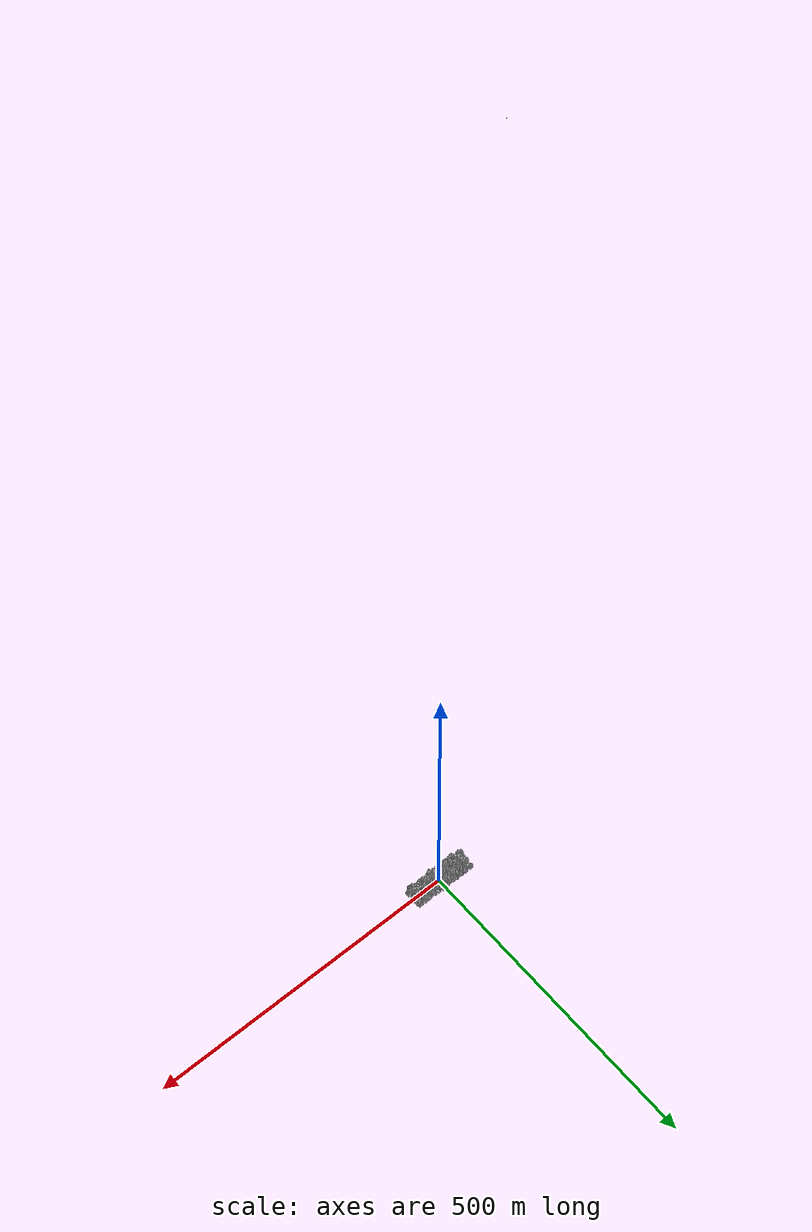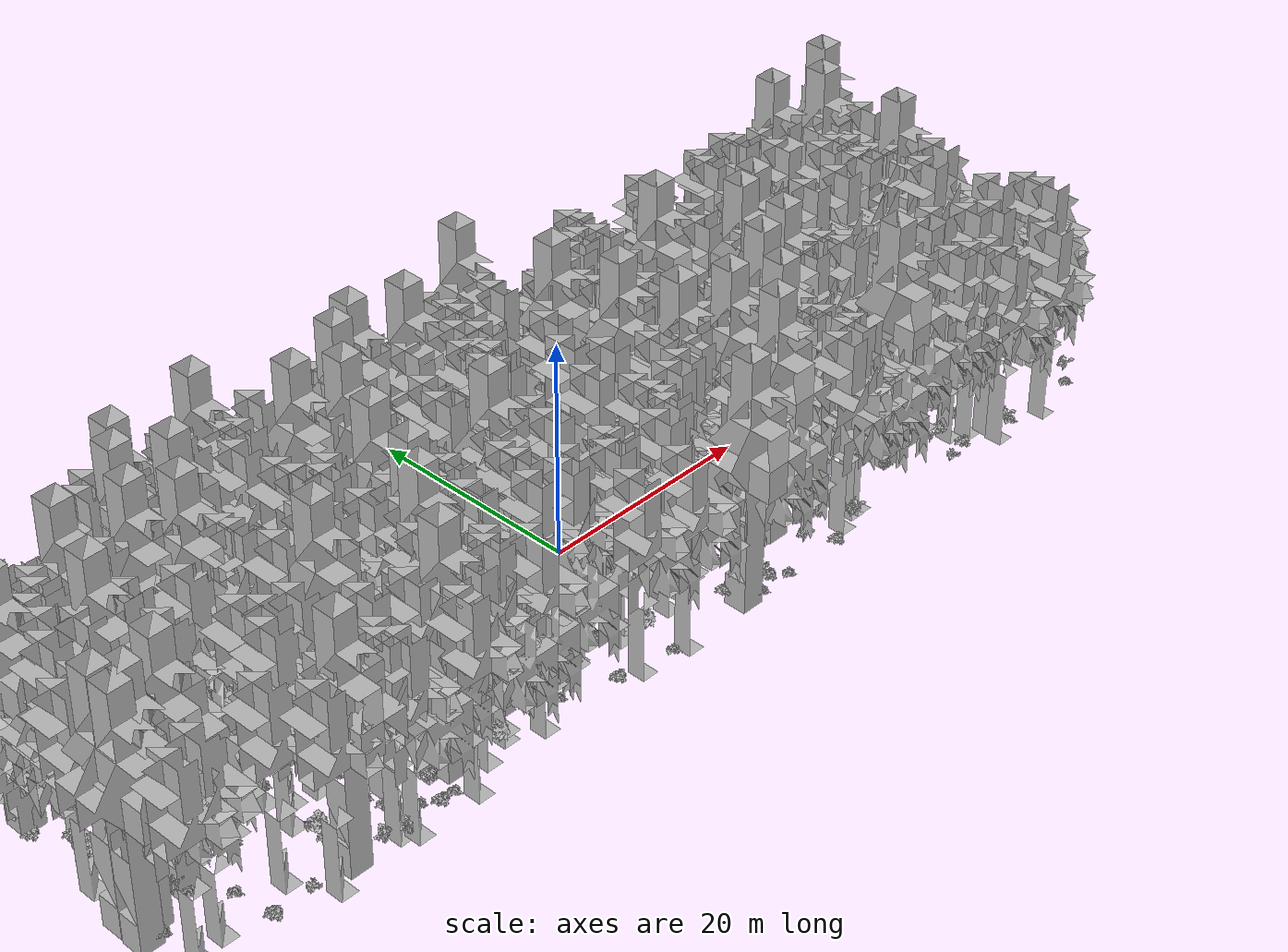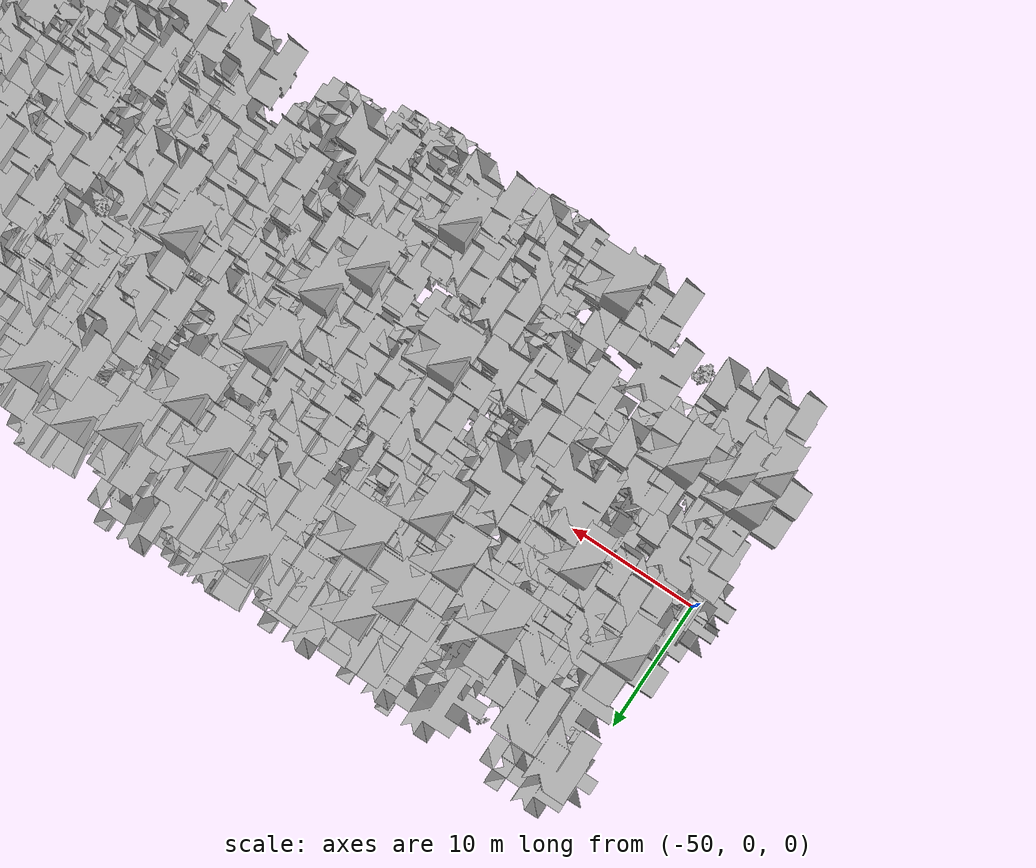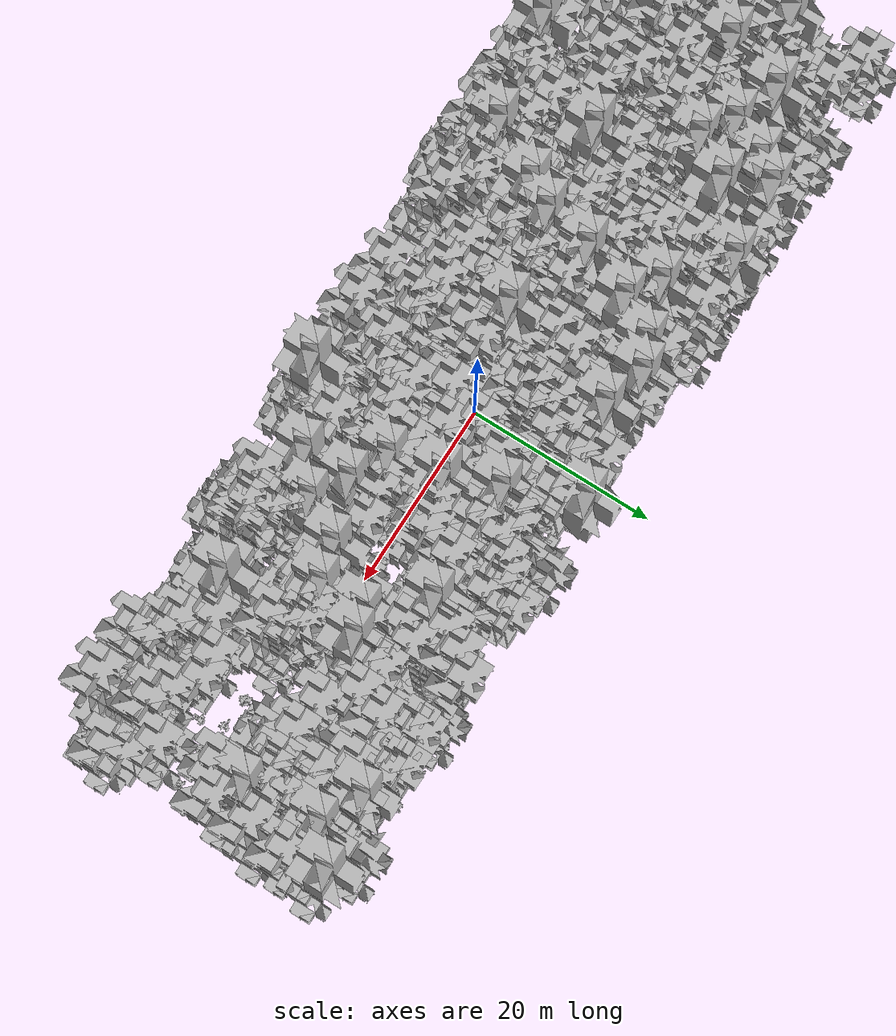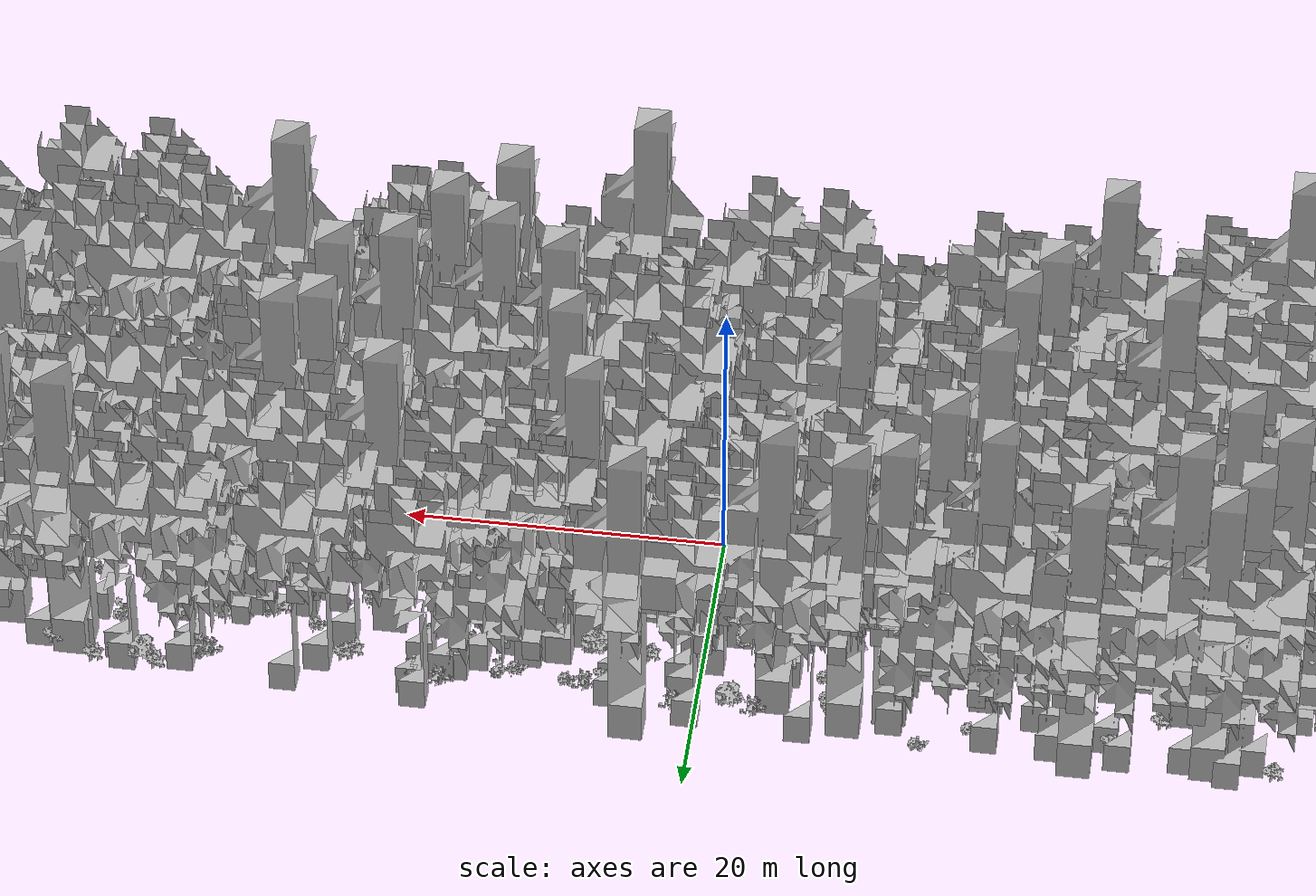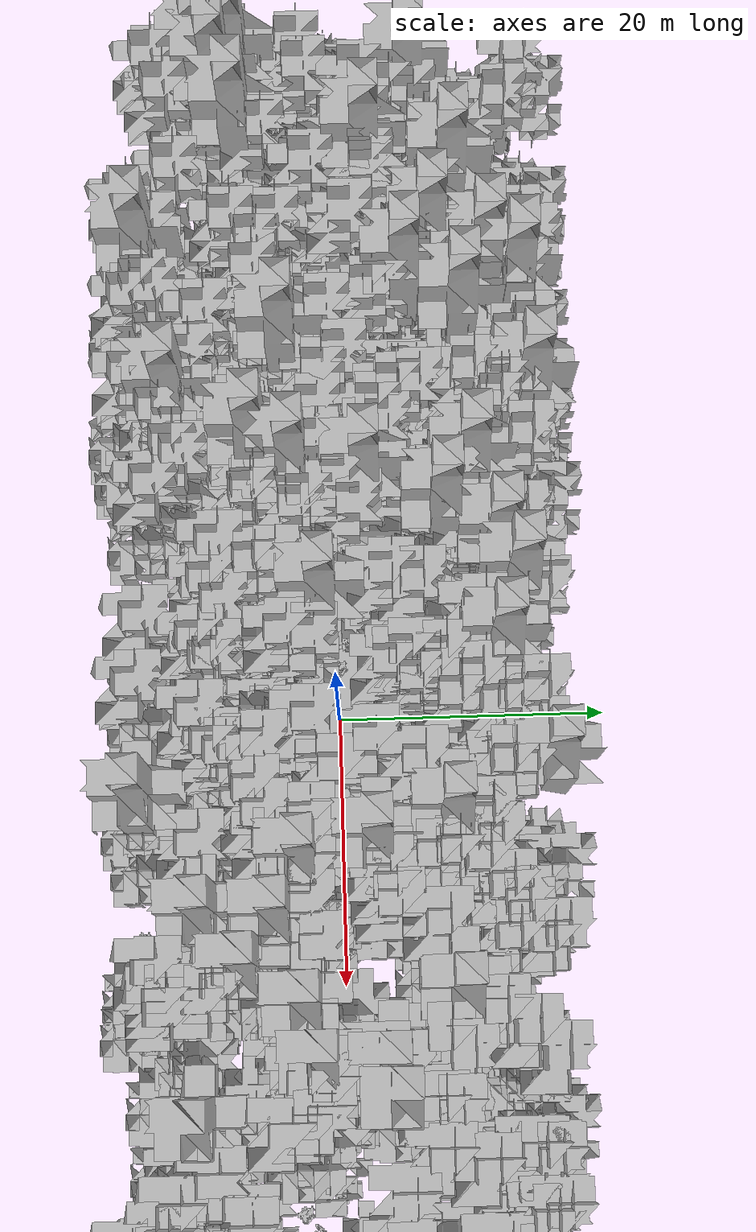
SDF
<sdf version="1.7">
    <world name="default">
        <plugin name="mrs_gazebo_static_transform_republisher_plugin" filename="libMrsGazeboCommonResources_StaticTransformRepublisher.so"/>
        <spherical_coordinates>
            <surface_model>EARTH_WGS84</surface_model>
            <latitude_deg>47.3977</latitude_deg>
            <longitude_deg>8.54559</longitude_deg>
            <elevation>0</elevation>
            <heading_deg>0</heading_deg>
        </spherical_coordinates>
        <physics name="default_physics" default="0" type="ode">
            <ode>
                <solver>
                    <type>quick</type>
                    <iters>10</iters>
                    <sor>1.3</sor>
                    <use_dynamic_moi_rescaling>0</use_dynamic_moi_rescaling>
                </solver>
                <constraints>
                    <cfm>0</cfm>
                    <erp>0.2</erp>
                    <contact_max_correcting_vel>1000</contact_max_correcting_vel>
                    <contact_surface_layer>0.001</contact_surface_layer>
                </constraints>
            </ode>
            <max_step_size>0.004</max_step_size>
            <real_time_factor>1</real_time_factor>
            <real_time_update_rate>250</real_time_update_rate>
        </physics>
        <scene>
            <shadows>0</shadows>
            <ambient>0.4 0.4 0.4 1</ambient>
            <background>0.7 0.7 0.7 1</background>
        </scene>
        <light name="sun" type="directional">
            <pose>0 0 1000 0.4 0.2 0</pose>
            <diffuse>1 1 1 1</diffuse>
            <specular>0.6 0.6 0.6 1</specular>
            <direction>0.1 0.1 -0.9</direction>
            <attenuation>
                <range>20</range>
                <constant>0.5</constant>
                <linear>0.01</linear>
                <quadratic>0.001</quadratic>
            </attenuation>
            <cast_shadows>1</cast_shadows>
            <spot>
                <inner_angle>0</inner_angle>
                <outer_angle>0</outer_angle>
                <falloff>0</falloff>
            </spot>
        </light>
        <model name="ground_plane">
            <static>1</static>
            <link name="link">
                <collision name="collision">
                    <pose>0 0 0 0 -0 0</pose>
                    <geometry>
                        <plane>
                            <normal>0 0 1</normal>
                            <size>100 100</size>
                        </plane>
                    </geometry>
                    <surface>
                        <contact>
                            <ode>
                                <min_depth>0.01</min_depth>
                                <max_vel>0</max_vel>
                            </ode>
                        </contact>
                        <friction>
                            <ode/>
                            <torsional>
                                <ode/>
                            </torsional>
                        </friction>
                        <bounce/>
                    </surface>
                    <max_contacts>10</max_contacts>
                </collision>
                <visual name="grass">
                    <pose>0 0 0 0 -0 0</pose>
                    <cast_shadows>0</cast_shadows>
                    <geometry>
                        <mesh>
                            <scale>0.5814285714285714 0.18142857142857144 0.1</scale>
                            <uri>file://grass_plane/meshes/grass_plane.dae</uri>
                        </mesh>
                    </geometry>
                </visual>
                <self_collide>0</self_collide>
                <enable_wind>0</enable_wind>
                <kinematic>0</kinematic>
            </link>
        </model>
        <model name="the_void">
            <static>1</static>
            <link name="link">
                <pose>0 0 0.1 0 -0 0</pose>
                <visual name="the_void">
                    <pose>0 0 2 0 -0 0</pose>
                    <geometry>
                        <sphere>
                            <radius>0.25</radius>
                        </sphere>
                    </geometry>
                    <material>
                        <script>
                            <uri>file://media/materials/scripts/Gazebo.material</uri>
                            <name>Gazebo/Black</name>
                        </script>
                    </material>
                </visual>
                <self_collide>0</self_collide>
                <enable_wind>0</enable_wind>
                <kinematic>0</kinematic>
            </link>
            <pose>-1000 -1000 0 0 -0 0</pose>
        </model>
        <gui fullscreen="0">
            <camera name="camera">
                <pose>35.1577 98.6044 40.0204 0 0.407996 -1.99761</pose>
                <view_controller>orbit</view_controller>
                <projection_type>perspective</projection_type>
            </camera>
        </gui>
        <plugin name="mrs_gazebo_rviz_cam_synchronizer" filename="libMrsGazeboCommonResources_RvizCameraSynchronizer.so">
            <target_frame_id>gazebo_user_camera</target_frame_id>
            <world_origin_frame_id>uav1/gps_origin</world_origin_frame_id>
            <frame_to_follow>uav1</frame_to_follow>
        </plugin>
        <gravity>0 0 -9.8066</gravity>
        <magnetic_field>6e-06 2.3e-05 -4.2e-05</magnetic_field>
        <atmosphere type="adiabatic"/>
        <wind/>
        <model name="Tree 0">
            <static>1</static>
            <pose>43.82342962723973 2.2307039787141427 0 1.57079 -0 0</pose>
            <link name="link">
                <pose>0 0 0 0 -0 0</pose>
                <collision name="collision">
                    <geometry>
                        <mesh>
                            <scale>3.5 5 3.5</scale>
                            <uri>model://tree_9/meshes/tree_9.obj</uri>
                        </mesh>
                    </geometry>
                    <max_contacts>10</max_contacts>
                    <surface>
                        <contact>
                            <ode/>
                        </contact>
                        <bounce/>
                        <friction>
                            <torsional>
                                <ode/>
                            </torsional>
                            <ode/>
                        </friction>
                    </surface>
                </collision>
                <visual name="visual">
                    <geometry>
                        <mesh>
                            <scale>3.5 5 3.5</scale>
                            <uri>model://tree_9/meshes/tree_9.obj</uri>
                        </mesh>
                    </geometry>
                </visual>
                <self_collide>0</self_collide>
                <enable_wind>0</enable_wind>
                <kinematic>0</kinematic>
            </link>
        </model>
        <model name="Tree 1">
            <static>1</static>
            <pose>-2.2293901789760255 7.002244898628128 0 1.57079 -0 0</pose>
            <link name="link">
                <pose>0 0 0 0 -0 0</pose>
                <collision name="collision">
                    <geometry>
                        <mesh>
                            <scale>3.5 5 3.5</scale>
                            <uri>model://tree_9/meshes/tree_9.obj</uri>
                        </mesh>
                    </geometry>
                    <max_contacts>10</max_contacts>
                    <surface>
                        <contact>
                            <ode/>
                        </contact>
                        <bounce/>
                        <friction>
                            <torsional>
                                <ode/>
                            </torsional>
                            <ode/>
                        </friction>
                    </surface>
                </collision>
                <visual name="visual">
                    <geometry>
                        <mesh>
                            <scale>3.5 5 3.5</scale>
                            <uri>model://tree_9/meshes/tree_9.obj</uri>
                        </mesh>
                    </geometry>
                </visual>
                <self_collide>0</self_collide>
                <enable_wind>0</enable_wind>
                <kinematic>0</kinematic>
            </link>
        </model>
        <model name="Tree 2">
            <static>1</static>
            <pose>-26.095646035066228 14.019821016825997 0 1.57079 -0 0</pose>
            <link name="link">
                <pose>0 0 0 0 -0 0</pose>
                <collision name="collision">
                    <geometry>
                        <mesh>
                            <scale>3.5 5 3.5</scale>
                            <uri>model://tree_9/meshes/tree_9.obj</uri>
                        </mesh>
                    </geometry>
                    <max_contacts>10</max_contacts>
                    <surface>
                        <contact>
                            <ode/>
                        </contact>
                        <bounce/>
                        <friction>
                            <torsional>
                                <ode/>
                            </torsional>
                            <ode/>
                        </friction>
                    </surface>
                </collision>
                <visual name="visual">
                    <geometry>
                        <mesh>
                            <scale>3.5 5 3.5</scale>
                            <uri>model://tree_9/meshes/tree_9.obj</uri>
                        </mesh>
                    </geometry>
                </visual>
                <self_collide>0</self_collide>
                <enable_wind>0</enable_wind>
                <kinematic>0</kinematic>
            </link>
        </model>
        <model name="Tree 3">
            <static>1</static>
            <pose>-41.77489237918018 -5.180226990313308 0 1.57079 -0 0</pose>
            <link name="link">
                <pose>0 0 0 0 -0 0</pose>
                <collision name="collision">
                    <geometry>
                        <mesh>
                            <scale>3.5 5 3.5</scale>
                            <uri>model://tree_9/meshes/tree_9.obj</uri>
                        </mesh>
                    </geometry>
                    <max_contacts>10</max_contacts>
                    <surface>
                        <contact>
                            <ode/>
                        </contact>
                        <bounce/>
                        <friction>
                            <torsional>
                                <ode/>
                            </torsional>
                            <ode/>
                        </friction>
                    </surface>
                </collision>
                <visual name="visual">
                    <geometry>
                        <mesh>
                            <scale>3.5 5 3.5</scale>
                            <uri>model://tree_9/meshes/tree_9.obj</uri>
                        </mesh>
                    </geometry>
                </visual>
                <self_collide>0</self_collide>
                <enable_wind>0</enable_wind>
                <kinematic>0</kinematic>
            </link>
        </model>
        <model name="Tree 4">
            <static>1</static>
            <pose>-47.181945975594665 5.9745366862424625 0 1.57079 -0 0</pose>
            <link name="link">
                <pose>0 0 0 0 -0 0</pose>
                <collision name="collision">
                    <geometry>
                        <mesh>
                            <scale>3.5 5 3.5</scale>
                            <uri>model://tree_4/meshes/tree_4.obj</uri>
                        </mesh>
                    </geometry>
                    <max_contacts>10</max_contacts>
                    <surface>
                        <contact>
                            <ode/>
                        </contact>
                        <bounce/>
                        <friction>
                            <torsional>
                                <ode/>
                            </torsional>
                            <ode/>
                        </friction>
                    </surface>
                </collision>
                <visual name="visual">
                    <geometry>
                        <mesh>
                            <scale>3.5 5 3.5</scale>
                            <uri>model://tree_4/meshes/tree_4.obj</uri>
                        </mesh>
                    </geometry>
                </visual>
                <self_collide>0</self_collide>
                <enable_wind>0</enable_wind>
                <kinematic>0</kinematic>
            </link>
        </model>
        <model name="Tree 5">
            <static>1</static>
            <pose>-38.7070382229083 -11.503104591853837 0 1.57079 -0 0</pose>
            <link name="link">
                <pose>0 0 0 0 -0 0</pose>
                <collision name="collision">
                    <geometry>
                        <mesh>
                            <scale>3.5 5 3.5</scale>
                            <uri>model://tree_9/meshes/tree_9.obj</uri>
                        </mesh>
                    </geometry>
                    <max_contacts>10</max_contacts>
                    <surface>
                        <contact>
                            <ode/>
                        </contact>
                        <bounce/>
                        <friction>
                            <torsional>
                                <ode/>
                            </torsional>
                            <ode/>
                        </friction>
                    </surface>
                </collision>
                <visual name="visual">
                    <geometry>
                        <mesh>
                            <scale>3.5 5 3.5</scale>
                            <uri>model://tree_9/meshes/tree_9.obj</uri>
                        </mesh>
                    </geometry>
                </visual>
                <self_collide>0</self_collide>
                <enable_wind>0</enable_wind>
                <kinematic>0</kinematic>
            </link>
        </model>
        <model name="Tree 6">
            <static>1</static>
            <pose>-43.491514775591085 -6.833206282252117 0 1.57079 -0 0</pose>
            <link name="link">
                <pose>0 0 0 0 -0 0</pose>
                <collision name="collision">
                    <geometry>
                        <mesh>
                            <scale>3.5 5 3.5</scale>
                            <uri>model://tree_4/meshes/tree_4.obj</uri>
                        </mesh>
                    </geometry>
                    <max_contacts>10</max_contacts>
                    <surface>
                        <contact>
                            <ode/>
                        </contact>
                        <bounce/>
                        <friction>
                            <torsional>
                                <ode/>
                            </torsional>
                            <ode/>
                        </friction>
                    </surface>
                </collision>
                <visual name="visual">
                    <geometry>
                        <mesh>
                            <scale>3.5 5 3.5</scale>
                            <uri>model://tree_4/meshes/tree_4.obj</uri>
                        </mesh>
                    </geometry>
                </visual>
                <self_collide>0</self_collide>
                <enable_wind>0</enable_wind>
                <kinematic>0</kinematic>
            </link>
        </model>
        <model name="Tree 7">
            <static>1</static>
            <pose>-22.19975299772507 10.766872606019188 0 1.57079 -0 0</pose>
            <link name="link">
                <pose>0 0 0 0 -0 0</pose>
                <collision name="collision">
                    <geometry>
                        <mesh>
                            <scale>3.5 5 3.5</scale>
                            <uri>model://tree_2/meshes/tree_2.obj</uri>
                        </mesh>
                    </geometry>
                    <max_contacts>10</max_contacts>
                    <surface>
                        <contact>
                            <ode/>
                        </contact>
                        <bounce/>
                        <friction>
                            <torsional>
                                <ode/>
                            </torsional>
                            <ode/>
                        </friction>
                    </surface>
                </collision>
                <visual name="visual">
                    <geometry>
                        <mesh>
                            <scale>3.5 5 3.5</scale>
                            <uri>model://tree_2/meshes/tree_2.obj</uri>
                        </mesh>
                    </geometry>
                </visual>
                <self_collide>0</self_collide>
                <enable_wind>0</enable_wind>
                <kinematic>0</kinematic>
            </link>
        </model>
        <model name="Tree 8">
            <static>1</static>
            <pose>12.07316993260789 14.701660111387213 0 1.57079 -0 0</pose>
            <link name="link">
                <pose>0 0 0 0 -0 0</pose>
                <collision name="collision">
                    <geometry>
                        <mesh>
                            <scale>3.5 5 3.5</scale>
                            <uri>model://tree_2/meshes/tree_2.obj</uri>
                        </mesh>
                    </geometry>
                    <max_contacts>10</max_contacts>
                    <surface>
                        <contact>
                            <ode/>
                        </contact>
                        <bounce/>
                        <friction>
                            <torsional>
                                <ode/>
                            </torsional>
                            <ode/>
                        </friction>
                    </surface>
                </collision>
                <visual name="visual">
                    <geometry>
                        <mesh>
                            <scale>3.5 5 3.5</scale>
                            <uri>model://tree_2/meshes/tree_2.obj</uri>
                        </mesh>
                    </geometry>
                </visual>
                <self_collide>0</self_collide>
                <enable_wind>0</enable_wind>
                <kinematic>0</kinematic>
            </link>
        </model>
        <model name="Tree 9">
            <static>1</static>
            <pose>26.462602125775476 11.593560292110084 0 1.57079 -0 0</pose>
            <link name="link">
                <pose>0 0 0 0 -0 0</pose>
                <collision name="collision">
                    <geometry>
                        <mesh>
                            <scale>3.5 5 3.5</scale>
                            <uri>model://tree_2/meshes/tree_2.obj</uri>
                        </mesh>
                    </geometry>
                    <max_contacts>10</max_contacts>
                    <surface>
                        <contact>
                            <ode/>
                        </contact>
                        <bounce/>
                        <friction>
                            <torsional>
                                <ode/>
                            </torsional>
                            <ode/>
                        </friction>
                    </surface>
                </collision>
                <visual name="visual">
                    <geometry>
                        <mesh>
                            <scale>3.5 5 3.5</scale>
                            <uri>model://tree_2/meshes/tree_2.obj</uri>
                        </mesh>
                    </geometry>
                </visual>
                <self_collide>0</self_collide>
                <enable_wind>0</enable_wind>
                <kinematic>0</kinematic>
            </link>
        </model>
        <model name="Tree 10">
            <static>1</static>
            <pose>-21.964925081223402 12.030915643776876 0 1.57079 -0 0</pose>
            <link name="link">
                <pose>0 0 0 0 -0 0</pose>
                <collision name="collision">
                    <geometry>
                        <mesh>
                            <scale>3.5 5 3.5</scale>
                            <uri>model://tree_9/meshes/tree_9.obj</uri>
                        </mesh>
                    </geometry>
                    <max_contacts>10</max_contacts>
                    <surface>
                        <contact>
                            <ode/>
                        </contact>
                        <bounce/>
                        <friction>
                            <torsional>
                                <ode/>
                            </torsional>
                            <ode/>
                        </friction>
                    </surface>
                </collision>
                <visual name="visual">
                    <geometry>
                        <mesh>
                            <scale>3.5 5 3.5</scale>
                            <uri>model://tree_9/meshes/tree_9.obj</uri>
                        </mesh>
                    </geometry>
                </visual>
                <self_collide>0</self_collide>
                <enable_wind>0</enable_wind>
                <kinematic>0</kinematic>
            </link>
        </model>
        <model name="Tree 11">
            <static>1</static>
            <pose>-23.143867781867687 2.5323528704578564 0 1.57079 -0 0</pose>
            <link name="link">
                <pose>0 0 0 0 -0 0</pose>
                <collision name="collision">
                    <geometry>
                        <mesh>
                            <scale>3.5 5 3.5</scale>
                            <uri>model://tree_2/meshes/tree_2.obj</uri>
                        </mesh>
                    </geometry>
                    <max_contacts>10</max_contacts>
                    <surface>
                        <contact>
                            <ode/>
                        </contact>
                        <bounce/>
                        <friction>
                            <torsional>
                                <ode/>
                            </torsional>
                            <ode/>
                        </friction>
                    </surface>
                </collision>
                <visual name="visual">
                    <geometry>
                        <mesh>
                            <scale>3.5 5 3.5</scale>
                            <uri>model://tree_2/meshes/tree_2.obj</uri>
                        </mesh>
                    </geometry>
                </visual>
                <self_collide>0</self_collide>
                <enable_wind>0</enable_wind>
                <kinematic>0</kinematic>
            </link>
        </model>
        <model name="Tree 12">
            <static>1</static>
            <pose>-48.348695763967854 -2.4779692079414737 0 1.57079 -0 0</pose>
            <link name="link">
                <pose>0 0 0 0 -0 0</pose>
                <collision name="collision">
                    <geometry>
                        <mesh>
                            <scale>3.5 5 3.5</scale>
                            <uri>model://tree_9/meshes/tree_9.obj</uri>
                        </mesh>
                    </geometry>
                    <max_contacts>10</max_contacts>
                    <surface>
                        <contact>
                            <ode/>
                        </contact>
                        <bounce/>
                        <friction>
                            <torsional>
                                <ode/>
                            </torsional>
                            <ode/>
                        </friction>
                    </surface>
                </collision>
                <visual name="visual">
                    <geometry>
                        <mesh>
                            <scale>3.5 5 3.5</scale>
                            <uri>model://tree_9/meshes/tree_9.obj</uri>
                        </mesh>
                    </geometry>
                </visual>
                <self_collide>0</self_collide>
                <enable_wind>0</enable_wind>
                <kinematic>0</kinematic>
            </link>
        </model>
        <model name="Tree 13">
            <static>1</static>
            <pose>36.778225727323544 6.261298513556863 0 1.57079 -0 0</pose>
            <link name="link">
                <pose>0 0 0 0 -0 0</pose>
                <collision name="collision">
                    <geometry>
                        <mesh>
                            <scale>3.5 5 3.5</scale>
                            <uri>model://tree_2/meshes/tree_2.obj</uri>
                        </mesh>
                    </geometry>
                    <max_contacts>10</max_contacts>
                    <surface>
                        <contact>
                            <ode/>
                        </contact>
                        <bounce/>
                        <friction>
                            <torsional>
                                <ode/>
                            </torsional>
                            <ode/>
                        </friction>
                    </surface>
                </collision>
                <visual name="visual">
                    <geometry>
                        <mesh>
                            <scale>3.5 5 3.5</scale>
                            <uri>model://tree_2/meshes/tree_2.obj</uri>
                        </mesh>
                    </geometry>
                </visual>
                <self_collide>0</self_collide>
                <enable_wind>0</enable_wind>
                <kinematic>0</kinematic>
            </link>
        </model>
        <model name="Tree 14">
            <static>1</static>
            <pose>40.112961565395935 6.885122554300562 0 1.57079 -0 0</pose>
            <link name="link">
                <pose>0 0 0 0 -0 0</pose>
                <collision name="collision">
                    <geometry>
                        <mesh>
                            <scale>3.5 5 3.5</scale>
                            <uri>model://tree_9/meshes/tree_9.obj</uri>
                        </mesh>
                    </geometry>
                    <max_contacts>10</max_contacts>
                    <surface>
                        <contact>
                            <ode/>
                        </contact>
                        <bounce/>
                        <friction>
                            <torsional>
                                <ode/>
                            </torsional>
                            <ode/>
                        </friction>
                    </surface>
                </collision>
                <visual name="visual">
                    <geometry>
                        <mesh>
                            <scale>3.5 5 3.5</scale>
                            <uri>model://tree_9/meshes/tree_9.obj</uri>
                        </mesh>
                    </geometry>
                </visual>
                <self_collide>0</self_collide>
                <enable_wind>0</enable_wind>
                <kinematic>0</kinematic>
            </link>
        </model>
        <model name="Tree 15">
            <static>1</static>
            <pose>38.212332978538186 12.092679831336667 0 1.57079 -0 0</pose>
            <link name="link">
                <pose>0 0 0 0 -0 0</pose>
                <collision name="collision">
                    <geometry>
                        <mesh>
                            <scale>3.5 5 3.5</scale>
                            <uri>model://tree_9/meshes/tree_9.obj</uri>
                        </mesh>
                    </geometry>
                    <max_contacts>10</max_contacts>
                    <surface>
                        <contact>
                            <ode/>
                        </contact>
                        <bounce/>
                        <friction>
                            <torsional>
                                <ode/>
                            </torsional>
                            <ode/>
                        </friction>
                    </surface>
                </collision>
                <visual name="visual">
                    <geometry>
                        <mesh>
                            <scale>3.5 5 3.5</scale>
                            <uri>model://tree_9/meshes/tree_9.obj</uri>
                        </mesh>
                    </geometry>
                </visual>
                <self_collide>0</self_collide>
                <enable_wind>0</enable_wind>
                <kinematic>0</kinematic>
            </link>
        </model>
        <model name="Tree 16">
            <static>1</static>
            <pose>-48.28347505902267 0.11804457914672106 0 1.57079 -0 0</pose>
            <link name="link">
                <pose>0 0 0 0 -0 0</pose>
                <collision name="collision">
                    <geometry>
                        <mesh>
                            <scale>3.5 5 3.5</scale>
                            <uri>model://tree_2/meshes/tree_2.obj</uri>
                        </mesh>
                    </geometry>
                    <max_contacts>10</max_contacts>
                    <surface>
                        <contact>
                            <ode/>
                        </contact>
                        <bounce/>
                        <friction>
                            <torsional>
                                <ode/>
                            </torsional>
                            <ode/>
                        </friction>
                    </surface>
                </collision>
                <visual name="visual">
                    <geometry>
                        <mesh>
                            <scale>3.5 5 3.5</scale>
                            <uri>model://tree_2/meshes/tree_2.obj</uri>
                        </mesh>
                    </geometry>
                </visual>
                <self_collide>0</self_collide>
                <enable_wind>0</enable_wind>
                <kinematic>0</kinematic>
            </link>
        </model>
        <model name="Tree 17">
            <static>1</static>
            <pose>1.8637078458601835 12.813028883105133 0 1.57079 -0 0</pose>
            <link name="link">
                <pose>0 0 0 0 -0 0</pose>
                <collision name="collision">
                    <geometry>
                        <mesh>
                            <scale>3.5 5 3.5</scale>
                            <uri>model://tree_2/meshes/tree_2.obj</uri>
                        </mesh>
                    </geometry>
                    <max_contacts>10</max_contacts>
                    <surface>
                        <contact>
                            <ode/>
                        </contact>
                        <bounce/>
                        <friction>
                            <torsional>
                                <ode/>
                            </torsional>
                            <ode/>
                        </friction>
                    </surface>
                </collision>
                <visual name="visual">
                    <geometry>
                        <mesh>
                            <scale>3.5 5 3.5</scale>
                            <uri>model://tree_2/meshes/tree_2.obj</uri>
                        </mesh>
                    </geometry>
                </visual>
                <self_collide>0</self_collide>
                <enable_wind>0</enable_wind>
                <kinematic>0</kinematic>
            </link>
        </model>
        <model name="Tree 18">
            <static>1</static>
            <pose>-20.40445769906592 -7.195301305459899 0 1.57079 -0 0</pose>
            <link name="link">
                <pose>0 0 0 0 -0 0</pose>
                <collision name="collision">
                    <geometry>
                        <mesh>
                            <scale>3.5 5 3.5</scale>
                            <uri>model://tree_9/meshes/tree_9.obj</uri>
                        </mesh>
                    </geometry>
                    <max_contacts>10</max_contacts>
                    <surface>
                        <contact>
                            <ode/>
                        </contact>
                        <bounce/>
                        <friction>
                            <torsional>
                                <ode/>
                            </torsional>
                            <ode/>
                        </friction>
                    </surface>
                </collision>
                <visual name="visual">
                    <geometry>
                        <mesh>
                            <scale>3.5 5 3.5</scale>
                            <uri>model://tree_9/meshes/tree_9.obj</uri>
                        </mesh>
                    </geometry>
                </visual>
                <self_collide>0</self_collide>
                <enable_wind>0</enable_wind>
                <kinematic>0</kinematic>
            </link>
        </model>
        <model name="Tree 19">
            <static>1</static>
            <pose>24.21214976506458 12.339405180876014 0 1.57079 -0 0</pose>
            <link name="link">
                <pose>0 0 0 0 -0 0</pose>
                <collision name="collision">
                    <geometry>
                        <mesh>
                            <scale>3.5 5 3.5</scale>
                            <uri>model://tree_2/meshes/tree_2.obj</uri>
                        </mesh>
                    </geometry>
                    <max_contacts>10</max_contacts>
                    <surface>
                        <contact>
                            <ode/>
                        </contact>
                        <bounce/>
                        <friction>
                            <torsional>
                                <ode/>
                            </torsional>
                            <ode/>
                        </friction>
                    </surface>
                </collision>
                <visual name="visual">
                    <geometry>
                        <mesh>
                            <scale>3.5 5 3.5</scale>
                            <uri>model://tree_2/meshes/tree_2.obj</uri>
                        </mesh>
                    </geometry>
                </visual>
                <self_collide>0</self_collide>
                <enable_wind>0</enable_wind>
                <kinematic>0</kinematic>
            </link>
        </model>
        <model name="Tree 20">
            <static>1</static>
            <pose>-32.43666485976108 12.16517194718622 0 1.57079 -0 0</pose>
            <link name="link">
                <pose>0 0 0 0 -0 0</pose>
                <collision name="collision">
                    <geometry>
                        <mesh>
                            <scale>3.5 5 3.5</scale>
                            <uri>model://tree_2/meshes/tree_2.obj</uri>
                        </mesh>
                    </geometry>
                    <max_contacts>10</max_contacts>
                    <surface>
                        <contact>
                            <ode/>
                        </contact>
                        <bounce/>
                        <friction>
                            <torsional>
                                <ode/>
                            </torsional>
                            <ode/>
                        </friction>
                    </surface>
                </collision>
                <visual name="visual">
                    <geometry>
                        <mesh>
                            <scale>3.5 5 3.5</scale>
                            <uri>model://tree_2/meshes/tree_2.obj</uri>
                        </mesh>
                    </geometry>
                </visual>
                <self_collide>0</self_collide>
                <enable_wind>0</enable_wind>
                <kinematic>0</kinematic>
            </link>
        </model>
        <model name="Tree 21">
            <static>1</static>
            <pose>25.555569480309188 1.4773219222838918 0 1.57079 -0 0</pose>
            <link name="link">
                <pose>0 0 0 0 -0 0</pose>
                <collision name="collision">
                    <geometry>
                        <mesh>
                            <scale>3.5 5 3.5</scale>
                            <uri>model://tree_2/meshes/tree_2.obj</uri>
                        </mesh>
                    </geometry>
                    <max_contacts>10</max_contacts>
                    <surface>
                        <contact>
                            <ode/>
                        </contact>
                        <bounce/>
                        <friction>
                            <torsional>
                                <ode/>
                            </torsional>
                            <ode/>
                        </friction>
                    </surface>
                </collision>
                <visual name="visual">
                    <geometry>
                        <mesh>
                            <scale>3.5 5 3.5</scale>
                            <uri>model://tree_2/meshes/tree_2.obj</uri>
                        </mesh>
                    </geometry>
                </visual>
                <self_collide>0</self_collide>
                <enable_wind>0</enable_wind>
                <kinematic>0</kinematic>
            </link>
        </model>
        <model name="Tree 22">
            <static>1</static>
            <pose>-21.677403938993216 1.5167767295512533 0 1.57079 -0 0</pose>
            <link name="link">
                <pose>0 0 0 0 -0 0</pose>
                <collision name="collision">
                    <geometry>
                        <mesh>
                            <scale>3.5 5 3.5</scale>
                            <uri>model://tree_2/meshes/tree_2.obj</uri>
                        </mesh>
                    </geometry>
                    <max_contacts>10</max_contacts>
                    <surface>
                        <contact>
                            <ode/>
                        </contact>
                        <bounce/>
                        <friction>
                            <torsional>
                                <ode/>
                            </torsional>
                            <ode/>
                        </friction>
                    </surface>
                </collision>
                <visual name="visual">
                    <geometry>
                        <mesh>
                            <scale>3.5 5 3.5</scale>
                            <uri>model://tree_2/meshes/tree_2.obj</uri>
                        </mesh>
                    </geometry>
                </visual>
                <self_collide>0</self_collide>
                <enable_wind>0</enable_wind>
                <kinematic>0</kinematic>
            </link>
        </model>
        <model name="Tree 23">
            <static>1</static>
            <pose>-29.321768477188105 -12.99323544306235 0 1.57079 -0 0</pose>
            <link name="link">
                <pose>0 0 0 0 -0 0</pose>
                <collision name="collision">
                    <geometry>
                        <mesh>
                            <scale>3.5 5 3.5</scale>
                            <uri>model://tree_9/meshes/tree_9.obj</uri>
                        </mesh>
                    </geometry>
                    <max_contacts>10</max_contacts>
                    <surface>
                        <contact>
                            <ode/>
                        </contact>
                        <bounce/>
                        <friction>
                            <torsional>
                                <ode/>
                            </torsional>
                            <ode/>
                        </friction>
                    </surface>
                </collision>
                <visual name="visual">
                    <geometry>
                        <mesh>
                            <scale>3.5 5 3.5</scale>
                            <uri>model://tree_9/meshes/tree_9.obj</uri>
                        </mesh>
                    </geometry>
                </visual>
                <self_collide>0</self_collide>
                <enable_wind>0</enable_wind>
                <kinematic>0</kinematic>
            </link>
        </model>
        <model name="Tree 24">
            <static>1</static>
            <pose>13.769064638838955 11.019449261312328 0 1.57079 -0 0</pose>
            <link name="link">
                <pose>0 0 0 0 -0 0</pose>
                <collision name="collision">
                    <geometry>
                        <mesh>
                            <scale>3.5 5 3.5</scale>
                            <uri>model://tree_9/meshes/tree_9.obj</uri>
                        </mesh>
                    </geometry>
                    <max_contacts>10</max_contacts>
                    <surface>
                        <contact>
                            <ode/>
                        </contact>
                        <bounce/>
                        <friction>
                            <torsional>
                                <ode/>
                            </torsional>
                            <ode/>
                        </friction>
                    </surface>
                </collision>
                <visual name="visual">
                    <geometry>
                        <mesh>
                            <scale>3.5 5 3.5</scale>
                            <uri>model://tree_9/meshes/tree_9.obj</uri>
                        </mesh>
                    </geometry>
                </visual>
                <self_collide>0</self_collide>
                <enable_wind>0</enable_wind>
                <kinematic>0</kinematic>
            </link>
        </model>
        <model name="Tree 25">
            <static>1</static>
            <pose>-1.3834222626400603 6.521482204011189 0 1.57079 -0 0</pose>
            <link name="link">
                <pose>0 0 0 0 -0 0</pose>
                <collision name="collision">
                    <geometry>
                        <mesh>
                            <scale>3.5 5 3.5</scale>
                            <uri>model://tree_9/meshes/tree_9.obj</uri>
                        </mesh>
                    </geometry>
                    <max_contacts>10</max_contacts>
                    <surface>
                        <contact>
                            <ode/>
                        </contact>
                        <bounce/>
                        <friction>
                            <torsional>
                                <ode/>
                            </torsional>
                            <ode/>
                        </friction>
                    </surface>
                </collision>
                <visual name="visual">
                    <geometry>
                        <mesh>
                            <scale>3.5 5 3.5</scale>
                            <uri>model://tree_9/meshes/tree_9.obj</uri>
                        </mesh>
                    </geometry>
                </visual>
                <self_collide>0</self_collide>
                <enable_wind>0</enable_wind>
                <kinematic>0</kinematic>
            </link>
        </model>
        <model name="Tree 26">
            <static>1</static>
            <pose>14.767270386368914 3.3967840840657146 0 1.57079 -0 0</pose>
            <link name="link">
                <pose>0 0 0 0 -0 0</pose>
                <collision name="collision">
                    <geometry>
                        <mesh>
                            <scale>3.5 5 3.5</scale>
                            <uri>model://tree_9/meshes/tree_9.obj</uri>
                        </mesh>
                    </geometry>
                    <max_contacts>10</max_contacts>
                    <surface>
                        <contact>
                            <ode/>
                        </contact>
                        <bounce/>
                        <friction>
                            <torsional>
                                <ode/>
                            </torsional>
                            <ode/>
                        </friction>
                    </surface>
                </collision>
                <visual name="visual">
                    <geometry>
                        <mesh>
                            <scale>3.5 5 3.5</scale>
                            <uri>model://tree_9/meshes/tree_9.obj</uri>
                        </mesh>
                    </geometry>
                </visual>
                <self_collide>0</self_collide>
                <enable_wind>0</enable_wind>
                <kinematic>0</kinematic>
            </link>
        </model>
        <model name="Tree 27">
            <static>1</static>
            <pose>-10.889017046997004 -7.6712692974383065 0 1.57079 -0 0</pose>
            <link name="link">
                <pose>0 0 0 0 -0 0</pose>
                <collision name="collision">
                    <geometry>
                        <mesh>
                            <scale>3.5 5 3.5</scale>
                            <uri>model://tree_2/meshes/tree_2.obj</uri>
                        </mesh>
                    </geometry>
                    <max_contacts>10</max_contacts>
                    <surface>
                        <contact>
                            <ode/>
                        </contact>
                        <bounce/>
                        <friction>
                            <torsional>
                                <ode/>
                            </torsional>
                            <ode/>
                        </friction>
                    </surface>
                </collision>
                <visual name="visual">
                    <geometry>
                        <mesh>
                            <scale>3.5 5 3.5</scale>
                            <uri>model://tree_2/meshes/tree_2.obj</uri>
                        </mesh>
                    </geometry>
                </visual>
                <self_collide>0</self_collide>
                <enable_wind>0</enable_wind>
                <kinematic>0</kinematic>
            </link>
        </model>
        <model name="Tree 28">
            <static>1</static>
            <pose>18.0387552859804 10.684780523896539 0 1.57079 -0 0</pose>
            <link name="link">
                <pose>0 0 0 0 -0 0</pose>
                <collision name="collision">
                    <geometry>
                        <mesh>
                            <scale>3.5 5 3.5</scale>
                            <uri>model://tree_2/meshes/tree_2.obj</uri>
                        </mesh>
                    </geometry>
                    <max_contacts>10</max_contacts>
                    <surface>
                        <contact>
                            <ode/>
                        </contact>
                        <bounce/>
                        <friction>
                            <torsional>
                                <ode/>
                            </torsional>
                            <ode/>
                        </friction>
                    </surface>
                </collision>
                <visual name="visual">
                    <geometry>
                        <mesh>
                            <scale>3.5 5 3.5</scale>
                            <uri>model://tree_2/meshes/tree_2.obj</uri>
                        </mesh>
                    </geometry>
                </visual>
                <self_collide>0</self_collide>
                <enable_wind>0</enable_wind>
                <kinematic>0</kinematic>
            </link>
        </model>
        <model name="Tree 29">
            <static>1</static>
            <pose>-26.8489966164462 10.760684531997772 0 1.57079 -0 0</pose>
            <link name="link">
                <pose>0 0 0 0 -0 0</pose>
                <collision name="collision">
                    <geometry>
                        <mesh>
                            <scale>3.5 5 3.5</scale>
                            <uri>model://tree_2/meshes/tree_2.obj</uri>
                        </mesh>
                    </geometry>
                    <max_contacts>10</max_contacts>
                    <surface>
                        <contact>
                            <ode/>
                        </contact>
                        <bounce/>
                        <friction>
                            <torsional>
                                <ode/>
                            </torsional>
                            <ode/>
                        </friction>
                    </surface>
                </collision>
                <visual name="visual">
                    <geometry>
                        <mesh>
                            <scale>3.5 5 3.5</scale>
                            <uri>model://tree_2/meshes/tree_2.obj</uri>
                        </mesh>
                    </geometry>
                </visual>
                <self_collide>0</self_collide>
                <enable_wind>0</enable_wind>
                <kinematic>0</kinematic>
            </link>
        </model>
        <model name="Tree 30">
            <static>1</static>
            <pose>-30.010403027288593 13.711741718345554 0 1.57079 -0 0</pose>
            <link name="link">
                <pose>0 0 0 0 -0 0</pose>
                <collision name="collision">
                    <geometry>
                        <mesh>
                            <scale>3.5 5 3.5</scale>
                            <uri>model://tree_9/meshes/tree_9.obj</uri>
                        </mesh>
                    </geometry>
                    <max_contacts>10</max_contacts>
                    <surface>
                        <contact>
                            <ode/>
                        </contact>
                        <bounce/>
                        <friction>
                            <torsional>
                                <ode/>
                            </torsional>
                            <ode/>
                        </friction>
                    </surface>
                </collision>
                <visual name="visual">
                    <geometry>
                        <mesh>
                            <scale>3.5 5 3.5</scale>
                            <uri>model://tree_9/meshes/tree_9.obj</uri>
                        </mesh>
                    </geometry>
                </visual>
                <self_collide>0</self_collide>
                <enable_wind>0</enable_wind>
                <kinematic>0</kinematic>
            </link>
        </model>
        <model name="Tree 31">
            <static>1</static>
            <pose>-19.441192703451993 3.903946145086696 0 1.57079 -0 0</pose>
            <link name="link">
                <pose>0 0 0 0 -0 0</pose>
                <collision name="collision">
                    <geometry>
                        <mesh>
                            <scale>3.5 5 3.5</scale>
                            <uri>model://tree_2/meshes/tree_2.obj</uri>
                        </mesh>
                    </geometry>
                    <max_contacts>10</max_contacts>
                    <surface>
                        <contact>
                            <ode/>
                        </contact>
                        <bounce/>
                        <friction>
                            <torsional>
                                <ode/>
                            </torsional>
                            <ode/>
                        </friction>
                    </surface>
                </collision>
                <visual name="visual">
                    <geometry>
                        <mesh>
                            <scale>3.5 5 3.5</scale>
                            <uri>model://tree_2/meshes/tree_2.obj</uri>
                        </mesh>
                    </geometry>
                </visual>
                <self_collide>0</self_collide>
                <enable_wind>0</enable_wind>
                <kinematic>0</kinematic>
            </link>
        </model>
        <model name="Tree 32">
            <static>1</static>
            <pose>-8.600275042310976 0.6815665782726263 0 1.57079 -0 0</pose>
            <link name="link">
                <pose>0 0 0 0 -0 0</pose>
                <collision name="collision">
                    <geometry>
                        <mesh>
                            <scale>3.5 5 3.5</scale>
                            <uri>model://tree_2/meshes/tree_2.obj</uri>
                        </mesh>
                    </geometry>
                    <max_contacts>10</max_contacts>
                    <surface>
                        <contact>
                            <ode/>
                        </contact>
                        <bounce/>
                        <friction>
                            <torsional>
                                <ode/>
                            </torsional>
                            <ode/>
                        </friction>
                    </surface>
                </collision>
                <visual name="visual">
                    <geometry>
                        <mesh>
                            <scale>3.5 5 3.5</scale>
                            <uri>model://tree_2/meshes/tree_2.obj</uri>
                        </mesh>
                    </geometry>
                </visual>
                <self_collide>0</self_collide>
                <enable_wind>0</enable_wind>
                <kinematic>0</kinematic>
            </link>
        </model>
        <model name="Tree 33">
            <static>1</static>
            <pose>29.740778404452996 4.340799564488414 0 1.57079 -0 0</pose>
            <link name="link">
                <pose>0 0 0 0 -0 0</pose>
                <collision name="collision">
                    <geometry>
                        <mesh>
                            <scale>3.5 5 3.5</scale>
                            <uri>model://tree_2/meshes/tree_2.obj</uri>
                        </mesh>
                    </geometry>
                    <max_contacts>10</max_contacts>
                    <surface>
                        <contact>
                            <ode/>
                        </contact>
                        <bounce/>
                        <friction>
                            <torsional>
                                <ode/>
                            </torsional>
                            <ode/>
                        </friction>
                    </surface>
                </collision>
                <visual name="visual">
                    <geometry>
                        <mesh>
                            <scale>3.5 5 3.5</scale>
                            <uri>model://tree_2/meshes/tree_2.obj</uri>
                        </mesh>
                    </geometry>
                </visual>
                <self_collide>0</self_collide>
                <enable_wind>0</enable_wind>
                <kinematic>0</kinematic>
            </link>
        </model>
        <model name="Tree 34">
            <static>1</static>
            <pose>-25.540851216279705 -4.869427088850342 0 1.57079 -0 0</pose>
            <link name="link">
                <pose>0 0 0 0 -0 0</pose>
                <collision name="collision">
                    <geometry>
                        <mesh>
                            <scale>3.5 5 3.5</scale>
                            <uri>model://tree_2/meshes/tree_2.obj</uri>
                        </mesh>
                    </geometry>
                    <max_contacts>10</max_contacts>
                    <surface>
                        <contact>
                            <ode/>
                        </contact>
                        <bounce/>
                        <friction>
                            <torsional>
                                <ode/>
                            </torsional>
                            <ode/>
                        </friction>
                    </surface>
                </collision>
                <visual name="visual">
                    <geometry>
                        <mesh>
                            <scale>3.5 5 3.5</scale>
                            <uri>model://tree_2/meshes/tree_2.obj</uri>
                        </mesh>
                    </geometry>
                </visual>
                <self_collide>0</self_collide>
                <enable_wind>0</enable_wind>
                <kinematic>0</kinematic>
            </link>
        </model>
        <model name="Tree 35">
            <static>1</static>
            <pose>-42.80539835410666 7.082560066641111 0 1.57079 -0 0</pose>
            <link name="link">
                <pose>0 0 0 0 -0 0</pose>
                <collision name="collision">
                    <geometry>
                        <mesh>
                            <scale>3.5 5 3.5</scale>
                            <uri>model://tree_9/meshes/tree_9.obj</uri>
                        </mesh>
                    </geometry>
                    <max_contacts>10</max_contacts>
                    <surface>
                        <contact>
                            <ode/>
                        </contact>
                        <bounce/>
                        <friction>
                            <torsional>
                                <ode/>
                            </torsional>
                            <ode/>
                        </friction>
                    </surface>
                </collision>
                <visual name="visual">
                    <geometry>
                        <mesh>
                            <scale>3.5 5 3.5</scale>
                            <uri>model://tree_9/meshes/tree_9.obj</uri>
                        </mesh>
                    </geometry>
                </visual>
                <self_collide>0</self_collide>
                <enable_wind>0</enable_wind>
                <kinematic>0</kinematic>
            </link>
        </model>
        <model name="Tree 36">
            <static>1</static>
            <pose>-39.48312915004023 8.917611645218066 0 1.57079 -0 0</pose>
            <link name="link">
                <pose>0 0 0 0 -0 0</pose>
                <collision name="collision">
                    <geometry>
                        <mesh>
                            <scale>3.5 5 3.5</scale>
                            <uri>model://tree_4/meshes/tree_4.obj</uri>
                        </mesh>
                    </geometry>
                    <max_contacts>10</max_contacts>
                    <surface>
                        <contact>
                            <ode/>
                        </contact>
                        <bounce/>
                        <friction>
                            <torsional>
                                <ode/>
                            </torsional>
                            <ode/>
                        </friction>
                    </surface>
                </collision>
                <visual name="visual">
                    <geometry>
                        <mesh>
                            <scale>3.5 5 3.5</scale>
                            <uri>model://tree_4/meshes/tree_4.obj</uri>
                        </mesh>
                    </geometry>
                </visual>
                <self_collide>0</self_collide>
                <enable_wind>0</enable_wind>
                <kinematic>0</kinematic>
            </link>
        </model>
        <model name="Tree 37">
            <static>1</static>
            <pose>-44.73808775154857 3.654556515504513 0 1.57079 -0 0</pose>
            <link name="link">
                <pose>0 0 0 0 -0 0</pose>
                <collision name="collision">
                    <geometry>
                        <mesh>
                            <scale>3.5 5 3.5</scale>
                            <uri>model://tree_2/meshes/tree_2.obj</uri>
                        </mesh>
                    </geometry>
                    <max_contacts>10</max_contacts>
                    <surface>
                        <contact>
                            <ode/>
                        </contact>
                        <bounce/>
                        <friction>
                            <torsional>
                                <ode/>
                            </torsional>
                            <ode/>
                        </friction>
                    </surface>
                </collision>
                <visual name="visual">
                    <geometry>
                        <mesh>
                            <scale>3.5 5 3.5</scale>
                            <uri>model://tree_2/meshes/tree_2.obj</uri>
                        </mesh>
                    </geometry>
                </visual>
                <self_collide>0</self_collide>
                <enable_wind>0</enable_wind>
                <kinematic>0</kinematic>
            </link>
        </model>
        <model name="Tree 38">
            <static>1</static>
            <pose>21.341184049060885 -7.069683319017203 0 1.57079 -0 0</pose>
            <link name="link">
                <pose>0 0 0 0 -0 0</pose>
                <collision name="collision">
                    <geometry>
                        <mesh>
                            <scale>3.5 5 3.5</scale>
                            <uri>model://tree_2/meshes/tree_2.obj</uri>
                        </mesh>
                    </geometry>
                    <max_contacts>10</max_contacts>
                    <surface>
                        <contact>
                            <ode/>
                        </contact>
                        <bounce/>
                        <friction>
                            <torsional>
                                <ode/>
                            </torsional>
                            <ode/>
                        </friction>
                    </surface>
                </collision>
                <visual name="visual">
                    <geometry>
                        <mesh>
                            <scale>3.5 5 3.5</scale>
                            <uri>model://tree_2/meshes/tree_2.obj</uri>
                        </mesh>
                    </geometry>
                </visual>
                <self_collide>0</self_collide>
                <enable_wind>0</enable_wind>
                <kinematic>0</kinematic>
            </link>
        </model>
        <model name="Tree 39">
            <static>1</static>
            <pose>-42.32961616001169 -1.9559734837157485 0 1.57079 -0 0</pose>
            <link name="link">
                <pose>0 0 0 0 -0 0</pose>
                <collision name="collision">
                    <geometry>
                        <mesh>
                            <scale>3.5 5 3.5</scale>
                            <uri>model://tree_2/meshes/tree_2.obj</uri>
                        </mesh>
                    </geometry>
                    <max_contacts>10</max_contacts>
                    <surface>
                        <contact>
                            <ode/>
                        </contact>
                        <bounce/>
                        <friction>
                            <torsional>
                                <ode/>
                            </torsional>
                            <ode/>
                        </friction>
                    </surface>
                </collision>
                <visual name="visual">
                    <geometry>
                        <mesh>
                            <scale>3.5 5 3.5</scale>
                            <uri>model://tree_2/meshes/tree_2.obj</uri>
                        </mesh>
                    </geometry>
                </visual>
                <self_collide>0</self_collide>
                <enable_wind>0</enable_wind>
                <kinematic>0</kinematic>
            </link>
        </model>
        <model name="Tree 40">
            <static>1</static>
            <pose>-10.452956551301305 6.191043097540529 0 1.57079 -0 0</pose>
            <link name="link">
                <pose>0 0 0 0 -0 0</pose>
                <collision name="collision">
                    <geometry>
                        <mesh>
                            <scale>3.5 5 3.5</scale>
                            <uri>model://tree_2/meshes/tree_2.obj</uri>
                        </mesh>
                    </geometry>
                    <max_contacts>10</max_contacts>
                    <surface>
                        <contact>
                            <ode/>
                        </contact>
                        <bounce/>
                        <friction>
                            <torsional>
                                <ode/>
                            </torsional>
                            <ode/>
                        </friction>
                    </surface>
                </collision>
                <visual name="visual">
                    <geometry>
                        <mesh>
                            <scale>3.5 5 3.5</scale>
                            <uri>model://tree_2/meshes/tree_2.obj</uri>
                        </mesh>
                    </geometry>
                </visual>
                <self_collide>0</self_collide>
                <enable_wind>0</enable_wind>
                <kinematic>0</kinematic>
            </link>
        </model>
        <model name="Tree 41">
            <static>1</static>
            <pose>8.488647891739916 -5.712136385296793 0 1.57079 -0 0</pose>
            <link name="link">
                <pose>0 0 0 0 -0 0</pose>
                <collision name="collision">
                    <geometry>
                        <mesh>
                            <scale>3.5 5 3.5</scale>
                            <uri>model://tree_9/meshes/tree_9.obj</uri>
                        </mesh>
                    </geometry>
                    <max_contacts>10</max_contacts>
                    <surface>
                        <contact>
                            <ode/>
                        </contact>
                        <bounce/>
                        <friction>
                            <torsional>
                                <ode/>
                            </torsional>
                            <ode/>
                        </friction>
                    </surface>
                </collision>
                <visual name="visual">
                    <geometry>
                        <mesh>
                            <scale>3.5 5 3.5</scale>
                            <uri>model://tree_9/meshes/tree_9.obj</uri>
                        </mesh>
                    </geometry>
                </visual>
                <self_collide>0</self_collide>
                <enable_wind>0</enable_wind>
                <kinematic>0</kinematic>
            </link>
        </model>
        <model name="Tree 42">
            <static>1</static>
            <pose>44.1032392731708 2.605088315892978 0 1.57079 -0 0</pose>
            <link name="link">
                <pose>0 0 0 0 -0 0</pose>
                <collision name="collision">
                    <geometry>
                        <mesh>
                            <scale>3.5 5 3.5</scale>
                            <uri>model://tree_4/meshes/tree_4.obj</uri>
                        </mesh>
                    </geometry>
                    <max_contacts>10</max_contacts>
                    <surface>
                        <contact>
                            <ode/>
                        </contact>
                        <bounce/>
                        <friction>
                            <torsional>
                                <ode/>
                            </torsional>
                            <ode/>
                        </friction>
                    </surface>
                </collision>
                <visual name="visual">
                    <geometry>
                        <mesh>
                            <scale>3.5 5 3.5</scale>
                            <uri>model://tree_4/meshes/tree_4.obj</uri>
                        </mesh>
                    </geometry>
                </visual>
                <self_collide>0</self_collide>
                <enable_wind>0</enable_wind>
                <kinematic>0</kinematic>
            </link>
        </model>
        <model name="Tree 43">
            <static>1</static>
            <pose>-37.85181156054135 14.871914971472954 0 1.57079 -0 0</pose>
            <link name="link">
                <pose>0 0 0 0 -0 0</pose>
                <collision name="collision">
                    <geometry>
                        <mesh>
                            <scale>3.5 5 3.5</scale>
                            <uri>model://tree_2/meshes/tree_2.obj</uri>
                        </mesh>
                    </geometry>
                    <max_contacts>10</max_contacts>
                    <surface>
                        <contact>
                            <ode/>
                        </contact>
                        <bounce/>
                        <friction>
                            <torsional>
                                <ode/>
                            </torsional>
                            <ode/>
                        </friction>
                    </surface>
                </collision>
                <visual name="visual">
                    <geometry>
                        <mesh>
                            <scale>3.5 5 3.5</scale>
                            <uri>model://tree_2/meshes/tree_2.obj</uri>
                        </mesh>
                    </geometry>
                </visual>
                <self_collide>0</self_collide>
                <enable_wind>0</enable_wind>
                <kinematic>0</kinematic>
            </link>
        </model>
        <model name="Tree 44">
            <static>1</static>
            <pose>-28.886781284939783 9.369906334585853 0 1.57079 -0 0</pose>
            <link name="link">
                <pose>0 0 0 0 -0 0</pose>
                <collision name="collision">
                    <geometry>
                        <mesh>
                            <scale>3.5 5 3.5</scale>
                            <uri>model://tree_4/meshes/tree_4.obj</uri>
                        </mesh>
                    </geometry>
                    <max_contacts>10</max_contacts>
                    <surface>
                        <contact>
                            <ode/>
                        </contact>
                        <bounce/>
                        <friction>
                            <torsional>
                                <ode/>
                            </torsional>
                            <ode/>
                        </friction>
                    </surface>
                </collision>
                <visual name="visual">
                    <geometry>
                        <mesh>
                            <scale>3.5 5 3.5</scale>
                            <uri>model://tree_4/meshes/tree_4.obj</uri>
                        </mesh>
                    </geometry>
                </visual>
                <self_collide>0</self_collide>
                <enable_wind>0</enable_wind>
                <kinematic>0</kinematic>
            </link>
        </model>
        <model name="Tree 45">
            <static>1</static>
            <pose>6.254879595795309 -8.087533036596627 0 1.57079 -0 0</pose>
            <link name="link">
                <pose>0 0 0 0 -0 0</pose>
                <collision name="collision">
                    <geometry>
                        <mesh>
                            <scale>3.5 5 3.5</scale>
                            <uri>model://tree_2/meshes/tree_2.obj</uri>
                        </mesh>
                    </geometry>
                    <max_contacts>10</max_contacts>
                    <surface>
                        <contact>
                            <ode/>
                        </contact>
                        <bounce/>
                        <friction>
                            <torsional>
                                <ode/>
                            </torsional>
                            <ode/>
                        </friction>
                    </surface>
                </collision>
                <visual name="visual">
                    <geometry>
                        <mesh>
                            <scale>3.5 5 3.5</scale>
                            <uri>model://tree_2/meshes/tree_2.obj</uri>
                        </mesh>
                    </geometry>
                </visual>
                <self_collide>0</self_collide>
                <enable_wind>0</enable_wind>
                <kinematic>0</kinematic>
            </link>
        </model>
        <model name="Tree 46">
            <static>1</static>
            <pose>-9.307109804925275 -4.648253453084461 0 1.57079 -0 0</pose>
            <link name="link">
                <pose>0 0 0 0 -0 0</pose>
                <collision name="collision">
                    <geometry>
                        <mesh>
                            <scale>3.5 5 3.5</scale>
                            <uri>model://tree_9/meshes/tree_9.obj</uri>
                        </mesh>
                    </geometry>
                    <max_contacts>10</max_contacts>
                    <surface>
                        <contact>
                            <ode/>
                        </contact>
                        <bounce/>
                        <friction>
                            <torsional>
                                <ode/>
                            </torsional>
                            <ode/>
                        </friction>
                    </surface>
                </collision>
                <visual name="visual">
                    <geometry>
                        <mesh>
                            <scale>3.5 5 3.5</scale>
                            <uri>model://tree_9/meshes/tree_9.obj</uri>
                        </mesh>
                    </geometry>
                </visual>
                <self_collide>0</self_collide>
                <enable_wind>0</enable_wind>
                <kinematic>0</kinematic>
            </link>
        </model>
        <model name="Tree 47">
            <static>1</static>
            <pose>-16.009807557771893 8.387692748630354 0 1.57079 -0 0</pose>
            <link name="link">
                <pose>0 0 0 0 -0 0</pose>
                <collision name="collision">
                    <geometry>
                        <mesh>
                            <scale>3.5 5 3.5</scale>
                            <uri>model://tree_2/meshes/tree_2.obj</uri>
                        </mesh>
                    </geometry>
                    <max_contacts>10</max_contacts>
                    <surface>
                        <contact>
                            <ode/>
                        </contact>
                        <bounce/>
                        <friction>
                            <torsional>
                                <ode/>
                            </torsional>
                            <ode/>
                        </friction>
                    </surface>
                </collision>
                <visual name="visual">
                    <geometry>
                        <mesh>
                            <scale>3.5 5 3.5</scale>
                            <uri>model://tree_2/meshes/tree_2.obj</uri>
                        </mesh>
                    </geometry>
                </visual>
                <self_collide>0</self_collide>
                <enable_wind>0</enable_wind>
                <kinematic>0</kinematic>
            </link>
        </model>
        <model name="Tree 48">
            <static>1</static>
            <pose>-30.011651677668432 -13.780484019595026 0 1.57079 -0 0</pose>
            <link name="link">
                <pose>0 0 0 0 -0 0</pose>
                <collision name="collision">
                    <geometry>
                        <mesh>
                            <scale>3.5 5 3.5</scale>
                            <uri>model://tree_9/meshes/tree_9.obj</uri>
                        </mesh>
                    </geometry>
                    <max_contacts>10</max_contacts>
                    <surface>
                        <contact>
                            <ode/>
                        </contact>
                        <bounce/>
                        <friction>
                            <torsional>
                                <ode/>
                            </torsional>
                            <ode/>
                        </friction>
                    </surface>
                </collision>
                <visual name="visual">
                    <geometry>
                        <mesh>
                            <scale>3.5 5 3.5</scale>
                            <uri>model://tree_9/meshes/tree_9.obj</uri>
                        </mesh>
                    </geometry>
                </visual>
                <self_collide>0</self_collide>
                <enable_wind>0</enable_wind>
                <kinematic>0</kinematic>
            </link>
        </model>
        <model name="Tree 49">
            <static>1</static>
            <pose>45.80509630683392 -6.78505157625351 0 1.57079 -0 0</pose>
            <link name="link">
                <pose>0 0 0 0 -0 0</pose>
                <collision name="collision">
                    <geometry>
                        <mesh>
                            <scale>3.5 5 3.5</scale>
                            <uri>model://tree_9/meshes/tree_9.obj</uri>
                        </mesh>
                    </geometry>
                    <max_contacts>10</max_contacts>
                    <surface>
                        <contact>
                            <ode/>
                        </contact>
                        <bounce/>
                        <friction>
                            <torsional>
                                <ode/>
                            </torsional>
                            <ode/>
                        </friction>
                    </surface>
                </collision>
                <visual name="visual">
                    <geometry>
                        <mesh>
                            <scale>3.5 5 3.5</scale>
                            <uri>model://tree_9/meshes/tree_9.obj</uri>
                        </mesh>
                    </geometry>
                </visual>
                <self_collide>0</self_collide>
                <enable_wind>0</enable_wind>
                <kinematic>0</kinematic>
            </link>
        </model>
        <model name="Tree 50">
            <static>1</static>
            <pose>-20.359017164193222 2.7420125081877593 0 1.57079 -0 0</pose>
            <link name="link">
                <pose>0 0 0 0 -0 0</pose>
                <collision name="collision">
                    <geometry>
                        <mesh>
                            <scale>3.5 5 3.5</scale>
                            <uri>model://tree_9/meshes/tree_9.obj</uri>
                        </mesh>
                    </geometry>
                    <max_contacts>10</max_contacts>
                    <surface>
                        <contact>
                            <ode/>
                        </contact>
                        <bounce/>
                        <friction>
                            <torsional>
                                <ode/>
                            </torsional>
                            <ode/>
                        </friction>
                    </surface>
                </collision>
                <visual name="visual">
                    <geometry>
                        <mesh>
                            <scale>3.5 5 3.5</scale>
                            <uri>model://tree_9/meshes/tree_9.obj</uri>
                        </mesh>
                    </geometry>
                </visual>
                <self_collide>0</self_collide>
                <enable_wind>0</enable_wind>
                <kinematic>0</kinematic>
            </link>
        </model>
        <model name="Tree 51">
            <static>1</static>
            <pose>-2.7148311823868596 11.498756158764426 0 1.57079 -0 0</pose>
            <link name="link">
                <pose>0 0 0 0 -0 0</pose>
                <collision name="collision">
                    <geometry>
                        <mesh>
                            <scale>3.5 5 3.5</scale>
                            <uri>model://tree_2/meshes/tree_2.obj</uri>
                        </mesh>
                    </geometry>
                    <max_contacts>10</max_contacts>
                    <surface>
                        <contact>
                            <ode/>
                        </contact>
                        <bounce/>
                        <friction>
                            <torsional>
                                <ode/>
                            </torsional>
                            <ode/>
                        </friction>
                    </surface>
                </collision>
                <visual name="visual">
                    <geometry>
                        <mesh>
                            <scale>3.5 5 3.5</scale>
                            <uri>model://tree_2/meshes/tree_2.obj</uri>
                        </mesh>
                    </geometry>
                </visual>
                <self_collide>0</self_collide>
                <enable_wind>0</enable_wind>
                <kinematic>0</kinematic>
            </link>
        </model>
        <model name="Tree 52">
            <static>1</static>
            <pose>15.725537501464459 12.137809315026288 0 1.57079 -0 0</pose>
            <link name="link">
                <pose>0 0 0 0 -0 0</pose>
                <collision name="collision">
                    <geometry>
                        <mesh>
                            <scale>3.5 5 3.5</scale>
                            <uri>model://tree_9/meshes/tree_9.obj</uri>
                        </mesh>
                    </geometry>
                    <max_contacts>10</max_contacts>
                    <surface>
                        <contact>
                            <ode/>
                        </contact>
                        <bounce/>
                        <friction>
                            <torsional>
                                <ode/>
                            </torsional>
                            <ode/>
                        </friction>
                    </surface>
                </collision>
                <visual name="visual">
                    <geometry>
                        <mesh>
                            <scale>3.5 5 3.5</scale>
                            <uri>model://tree_9/meshes/tree_9.obj</uri>
                        </mesh>
                    </geometry>
                </visual>
                <self_collide>0</self_collide>
                <enable_wind>0</enable_wind>
                <kinematic>0</kinematic>
            </link>
        </model>
        <model name="Tree 53">
            <static>1</static>
            <pose>12.024891577038495 2.672143351821976 0 1.57079 -0 0</pose>
            <link name="link">
                <pose>0 0 0 0 -0 0</pose>
                <collision name="collision">
                    <geometry>
                        <mesh>
                            <scale>3.5 5 3.5</scale>
                            <uri>model://tree_9/meshes/tree_9.obj</uri>
                        </mesh>
                    </geometry>
                    <max_contacts>10</max_contacts>
                    <surface>
                        <contact>
                            <ode/>
                        </contact>
                        <bounce/>
                        <friction>
                            <torsional>
                                <ode/>
                            </torsional>
                            <ode/>
                        </friction>
                    </surface>
                </collision>
                <visual name="visual">
                    <geometry>
                        <mesh>
                            <scale>3.5 5 3.5</scale>
                            <uri>model://tree_9/meshes/tree_9.obj</uri>
                        </mesh>
                    </geometry>
                </visual>
                <self_collide>0</self_collide>
                <enable_wind>0</enable_wind>
                <kinematic>0</kinematic>
            </link>
        </model>
        <model name="Tree 54">
            <static>1</static>
            <pose>5.5355745608585565 -0.4659872596296726 0 1.57079 -0 0</pose>
            <link name="link">
                <pose>0 0 0 0 -0 0</pose>
                <collision name="collision">
                    <geometry>
                        <mesh>
                            <scale>3.5 5 3.5</scale>
                            <uri>model://tree_9/meshes/tree_9.obj</uri>
                        </mesh>
                    </geometry>
                    <max_contacts>10</max_contacts>
                    <surface>
                        <contact>
                            <ode/>
                        </contact>
                        <bounce/>
                        <friction>
                            <torsional>
                                <ode/>
                            </torsional>
                            <ode/>
                        </friction>
                    </surface>
                </collision>
                <visual name="visual">
                    <geometry>
                        <mesh>
                            <scale>3.5 5 3.5</scale>
                            <uri>model://tree_9/meshes/tree_9.obj</uri>
                        </mesh>
                    </geometry>
                </visual>
                <self_collide>0</self_collide>
                <enable_wind>0</enable_wind>
                <kinematic>0</kinematic>
            </link>
        </model>
        <model name="Tree 55">
            <static>1</static>
            <pose>-8.902627469566433 1.0932942134292496 0 1.57079 -0 0</pose>
            <link name="link">
                <pose>0 0 0 0 -0 0</pose>
                <collision name="collision">
                    <geometry>
                        <mesh>
                            <scale>3.5 5 3.5</scale>
                            <uri>model://tree_2/meshes/tree_2.obj</uri>
                        </mesh>
                    </geometry>
                    <max_contacts>10</max_contacts>
                    <surface>
                        <contact>
                            <ode/>
                        </contact>
                        <bounce/>
                        <friction>
                            <torsional>
                                <ode/>
                            </torsional>
                            <ode/>
                        </friction>
                    </surface>
                </collision>
                <visual name="visual">
                    <geometry>
                        <mesh>
                            <scale>3.5 5 3.5</scale>
                            <uri>model://tree_2/meshes/tree_2.obj</uri>
                        </mesh>
                    </geometry>
                </visual>
                <self_collide>0</self_collide>
                <enable_wind>0</enable_wind>
                <kinematic>0</kinematic>
            </link>
        </model>
        <model name="Tree 56">
            <static>1</static>
            <pose>19.806158951901168 -8.2698413051378 0 1.57079 -0 0</pose>
            <link name="link">
                <pose>0 0 0 0 -0 0</pose>
                <collision name="collision">
                    <geometry>
                        <mesh>
                            <scale>3.5 5 3.5</scale>
                            <uri>model://tree_2/meshes/tree_2.obj</uri>
                        </mesh>
                    </geometry>
                    <max_contacts>10</max_contacts>
                    <surface>
                        <contact>
                            <ode/>
                        </contact>
                        <bounce/>
                        <friction>
                            <torsional>
                                <ode/>
                            </torsional>
                            <ode/>
                        </friction>
                    </surface>
                </collision>
                <visual name="visual">
                    <geometry>
                        <mesh>
                            <scale>3.5 5 3.5</scale>
                            <uri>model://tree_2/meshes/tree_2.obj</uri>
                        </mesh>
                    </geometry>
                </visual>
                <self_collide>0</self_collide>
                <enable_wind>0</enable_wind>
                <kinematic>0</kinematic>
            </link>
        </model>
        <model name="Tree 57">
            <static>1</static>
            <pose>17.552309237532214 -1.948340601883082 0 1.57079 -0 0</pose>
            <link name="link">
                <pose>0 0 0 0 -0 0</pose>
                <collision name="collision">
                    <geometry>
                        <mesh>
                            <scale>3.5 5 3.5</scale>
                            <uri>model://tree_9/meshes/tree_9.obj</uri>
                        </mesh>
                    </geometry>
                    <max_contacts>10</max_contacts>
                    <surface>
                        <contact>
                            <ode/>
                        </contact>
                        <bounce/>
                        <friction>
                            <torsional>
                                <ode/>
                            </torsional>
                            <ode/>
                        </friction>
                    </surface>
                </collision>
                <visual name="visual">
                    <geometry>
                        <mesh>
                            <scale>3.5 5 3.5</scale>
                            <uri>model://tree_9/meshes/tree_9.obj</uri>
                        </mesh>
                    </geometry>
                </visual>
                <self_collide>0</self_collide>
                <enable_wind>0</enable_wind>
                <kinematic>0</kinematic>
            </link>
        </model>
        <model name="Tree 58">
            <static>1</static>
            <pose>-43.74936159377879 12.527346472888404 0 1.57079 -0 0</pose>
            <link name="link">
                <pose>0 0 0 0 -0 0</pose>
                <collision name="collision">
                    <geometry>
                        <mesh>
                            <scale>3.5 5 3.5</scale>
                            <uri>model://tree_9/meshes/tree_9.obj</uri>
                        </mesh>
                    </geometry>
                    <max_contacts>10</max_contacts>
                    <surface>
                        <contact>
                            <ode/>
                        </contact>
                        <bounce/>
                        <friction>
                            <torsional>
                                <ode/>
                            </torsional>
                            <ode/>
                        </friction>
                    </surface>
                </collision>
                <visual name="visual">
                    <geometry>
                        <mesh>
                            <scale>3.5 5 3.5</scale>
                            <uri>model://tree_9/meshes/tree_9.obj</uri>
                        </mesh>
                    </geometry>
                </visual>
                <self_collide>0</self_collide>
                <enable_wind>0</enable_wind>
                <kinematic>0</kinematic>
            </link>
        </model>
        <model name="Tree 59">
            <static>1</static>
            <pose>27.28284743443966 5.791732705700067 0 1.57079 -0 0</pose>
            <link name="link">
                <pose>0 0 0 0 -0 0</pose>
                <collision name="collision">
                    <geometry>
                        <mesh>
                            <scale>3.5 5 3.5</scale>
                            <uri>model://tree_2/meshes/tree_2.obj</uri>
                        </mesh>
                    </geometry>
                    <max_contacts>10</max_contacts>
                    <surface>
                        <contact>
                            <ode/>
                        </contact>
                        <bounce/>
                        <friction>
                            <torsional>
                                <ode/>
                            </torsional>
                            <ode/>
                        </friction>
                    </surface>
                </collision>
                <visual name="visual">
                    <geometry>
                        <mesh>
                            <scale>3.5 5 3.5</scale>
                            <uri>model://tree_2/meshes/tree_2.obj</uri>
                        </mesh>
                    </geometry>
                </visual>
                <self_collide>0</self_collide>
                <enable_wind>0</enable_wind>
                <kinematic>0</kinematic>
            </link>
        </model>
        <model name="Tree 60">
            <static>1</static>
            <pose>26.409296699334433 -2.9071326586289175 0 1.57079 -0 0</pose>
            <link name="link">
                <pose>0 0 0 0 -0 0</pose>
                <collision name="collision">
                    <geometry>
                        <mesh>
                            <scale>3.5 5 3.5</scale>
                            <uri>model://tree_9/meshes/tree_9.obj</uri>
                        </mesh>
                    </geometry>
                    <max_contacts>10</max_contacts>
                    <surface>
                        <contact>
                            <ode/>
                        </contact>
                        <bounce/>
                        <friction>
                            <torsional>
                                <ode/>
                            </torsional>
                            <ode/>
                        </friction>
                    </surface>
                </collision>
                <visual name="visual">
                    <geometry>
                        <mesh>
                            <scale>3.5 5 3.5</scale>
                            <uri>model://tree_9/meshes/tree_9.obj</uri>
                        </mesh>
                    </geometry>
                </visual>
                <self_collide>0</self_collide>
                <enable_wind>0</enable_wind>
                <kinematic>0</kinematic>
            </link>
        </model>
        <model name="Tree 61">
            <static>1</static>
            <pose>-7.84192574733882 -3.622049459758049 0 1.57079 -0 0</pose>
            <link name="link">
                <pose>0 0 0 0 -0 0</pose>
                <collision name="collision">
                    <geometry>
                        <mesh>
                            <scale>3.5 5 3.5</scale>
                            <uri>model://tree_2/meshes/tree_2.obj</uri>
                        </mesh>
                    </geometry>
                    <max_contacts>10</max_contacts>
                    <surface>
                        <contact>
                            <ode/>
                        </contact>
                        <bounce/>
                        <friction>
                            <torsional>
                                <ode/>
                            </torsional>
                            <ode/>
                        </friction>
                    </surface>
                </collision>
                <visual name="visual">
                    <geometry>
                        <mesh>
                            <scale>3.5 5 3.5</scale>
                            <uri>model://tree_2/meshes/tree_2.obj</uri>
                        </mesh>
                    </geometry>
                </visual>
                <self_collide>0</self_collide>
                <enable_wind>0</enable_wind>
                <kinematic>0</kinematic>
            </link>
        </model>
        <model name="Tree 62">
            <static>1</static>
            <pose>17.12574778117248 14.57087930836543 0 1.57079 -0 0</pose>
            <link name="link">
                <pose>0 0 0 0 -0 0</pose>
                <collision name="collision">
                    <geometry>
                        <mesh>
                            <scale>3.5 5 3.5</scale>
                            <uri>model://tree_9/meshes/tree_9.obj</uri>
                        </mesh>
                    </geometry>
                    <max_contacts>10</max_contacts>
                    <surface>
                        <contact>
                            <ode/>
                        </contact>
                        <bounce/>
                        <friction>
                            <torsional>
                                <ode/>
                            </torsional>
                            <ode/>
                        </friction>
                    </surface>
                </collision>
                <visual name="visual">
                    <geometry>
                        <mesh>
                            <scale>3.5 5 3.5</scale>
                            <uri>model://tree_9/meshes/tree_9.obj</uri>
                        </mesh>
                    </geometry>
                </visual>
                <self_collide>0</self_collide>
                <enable_wind>0</enable_wind>
                <kinematic>0</kinematic>
            </link>
        </model>
        <model name="Tree 63">
            <static>1</static>
            <pose>-11.825618906742733 3.740813101395151 0 1.57079 -0 0</pose>
            <link name="link">
                <pose>0 0 0 0 -0 0</pose>
                <collision name="collision">
                    <geometry>
                        <mesh>
                            <scale>3.5 5 3.5</scale>
                            <uri>model://tree_2/meshes/tree_2.obj</uri>
                        </mesh>
                    </geometry>
                    <max_contacts>10</max_contacts>
                    <surface>
                        <contact>
                            <ode/>
                        </contact>
                        <bounce/>
                        <friction>
                            <torsional>
                                <ode/>
                            </torsional>
                            <ode/>
                        </friction>
                    </surface>
                </collision>
                <visual name="visual">
                    <geometry>
                        <mesh>
                            <scale>3.5 5 3.5</scale>
                            <uri>model://tree_2/meshes/tree_2.obj</uri>
                        </mesh>
                    </geometry>
                </visual>
                <self_collide>0</self_collide>
                <enable_wind>0</enable_wind>
                <kinematic>0</kinematic>
            </link>
        </model>
        <model name="Tree 64">
            <static>1</static>
            <pose>-27.997522878768937 -8.398625686146245 0 1.57079 -0 0</pose>
            <link name="link">
                <pose>0 0 0 0 -0 0</pose>
                <collision name="collision">
                    <geometry>
                        <mesh>
                            <scale>3.5 5 3.5</scale>
                            <uri>model://tree_2/meshes/tree_2.obj</uri>
                        </mesh>
                    </geometry>
                    <max_contacts>10</max_contacts>
                    <surface>
                        <contact>
                            <ode/>
                        </contact>
                        <bounce/>
                        <friction>
                            <torsional>
                                <ode/>
                            </torsional>
                            <ode/>
                        </friction>
                    </surface>
                </collision>
                <visual name="visual">
                    <geometry>
                        <mesh>
                            <scale>3.5 5 3.5</scale>
                            <uri>model://tree_2/meshes/tree_2.obj</uri>
                        </mesh>
                    </geometry>
                </visual>
                <self_collide>0</self_collide>
                <enable_wind>0</enable_wind>
                <kinematic>0</kinematic>
            </link>
        </model>
        <model name="Tree 65">
            <static>1</static>
            <pose>-42.1677500827394 8.257916998349746 0 1.57079 -0 0</pose>
            <link name="link">
                <pose>0 0 0 0 -0 0</pose>
                <collision name="collision">
                    <geometry>
                        <mesh>
                            <scale>3.5 5 3.5</scale>
                            <uri>model://tree_9/meshes/tree_9.obj</uri>
                        </mesh>
                    </geometry>
                    <max_contacts>10</max_contacts>
                    <surface>
                        <contact>
                            <ode/>
                        </contact>
                        <bounce/>
                        <friction>
                            <torsional>
                                <ode/>
                            </torsional>
                            <ode/>
                        </friction>
                    </surface>
                </collision>
                <visual name="visual">
                    <geometry>
                        <mesh>
                            <scale>3.5 5 3.5</scale>
                            <uri>model://tree_9/meshes/tree_9.obj</uri>
                        </mesh>
                    </geometry>
                </visual>
                <self_collide>0</self_collide>
                <enable_wind>0</enable_wind>
                <kinematic>0</kinematic>
            </link>
        </model>
        <model name="Tree 66">
            <static>1</static>
            <pose>-7.739646454535148 -1.2299317246267236 0 1.57079 -0 0</pose>
            <link name="link">
                <pose>0 0 0 0 -0 0</pose>
                <collision name="collision">
                    <geometry>
                        <mesh>
                            <scale>3.5 5 3.5</scale>
                            <uri>model://tree_4/meshes/tree_4.obj</uri>
                        </mesh>
                    </geometry>
                    <max_contacts>10</max_contacts>
                    <surface>
                        <contact>
                            <ode/>
                        </contact>
                        <bounce/>
                        <friction>
                            <torsional>
                                <ode/>
                            </torsional>
                            <ode/>
                        </friction>
                    </surface>
                </collision>
                <visual name="visual">
                    <geometry>
                        <mesh>
                            <scale>3.5 5 3.5</scale>
                            <uri>model://tree_4/meshes/tree_4.obj</uri>
                        </mesh>
                    </geometry>
                </visual>
                <self_collide>0</self_collide>
                <enable_wind>0</enable_wind>
                <kinematic>0</kinematic>
            </link>
        </model>
        <model name="Tree 67">
            <static>1</static>
            <pose>-24.26446829051003 -10.529204269525131 0 1.57079 -0 0</pose>
            <link name="link">
                <pose>0 0 0 0 -0 0</pose>
                <collision name="collision">
                    <geometry>
                        <mesh>
                            <scale>3.5 5 3.5</scale>
                            <uri>model://tree_9/meshes/tree_9.obj</uri>
                        </mesh>
                    </geometry>
                    <max_contacts>10</max_contacts>
                    <surface>
                        <contact>
                            <ode/>
                        </contact>
                        <bounce/>
                        <friction>
                            <torsional>
                                <ode/>
                            </torsional>
                            <ode/>
                        </friction>
                    </surface>
                </collision>
                <visual name="visual">
                    <geometry>
                        <mesh>
                            <scale>3.5 5 3.5</scale>
                            <uri>model://tree_9/meshes/tree_9.obj</uri>
                        </mesh>
                    </geometry>
                </visual>
                <self_collide>0</self_collide>
                <enable_wind>0</enable_wind>
                <kinematic>0</kinematic>
            </link>
        </model>
        <model name="Tree 68">
            <static>1</static>
            <pose>3.9700672305717006 -7.225919293965219 0 1.57079 -0 0</pose>
            <link name="link">
                <pose>0 0 0 0 -0 0</pose>
                <collision name="collision">
                    <geometry>
                        <mesh>
                            <scale>3.5 5 3.5</scale>
                            <uri>model://tree_9/meshes/tree_9.obj</uri>
                        </mesh>
                    </geometry>
                    <max_contacts>10</max_contacts>
                    <surface>
                        <contact>
                            <ode/>
                        </contact>
                        <bounce/>
                        <friction>
                            <torsional>
                                <ode/>
                            </torsional>
                            <ode/>
                        </friction>
                    </surface>
                </collision>
                <visual name="visual">
                    <geometry>
                        <mesh>
                            <scale>3.5 5 3.5</scale>
                            <uri>model://tree_9/meshes/tree_9.obj</uri>
                        </mesh>
                    </geometry>
                </visual>
                <self_collide>0</self_collide>
                <enable_wind>0</enable_wind>
                <kinematic>0</kinematic>
            </link>
        </model>
        <model name="Tree 69">
            <static>1</static>
            <pose>-8.586704859382799 10.787197240010489 0 1.57079 -0 0</pose>
            <link name="link">
                <pose>0 0 0 0 -0 0</pose>
                <collision name="collision">
                    <geometry>
                        <mesh>
                            <scale>3.5 5 3.5</scale>
                            <uri>model://tree_2/meshes/tree_2.obj</uri>
                        </mesh>
                    </geometry>
                    <max_contacts>10</max_contacts>
                    <surface>
                        <contact>
                            <ode/>
                        </contact>
                        <bounce/>
                        <friction>
                            <torsional>
                                <ode/>
                            </torsional>
                            <ode/>
                        </friction>
                    </surface>
                </collision>
                <visual name="visual">
                    <geometry>
                        <mesh>
                            <scale>3.5 5 3.5</scale>
                            <uri>model://tree_2/meshes/tree_2.obj</uri>
                        </mesh>
                    </geometry>
                </visual>
                <self_collide>0</self_collide>
                <enable_wind>0</enable_wind>
                <kinematic>0</kinematic>
            </link>
        </model>
        <model name="Tree 70">
            <static>1</static>
            <pose>14.379854943526283 4.85291602756287 0 1.57079 -0 0</pose>
            <link name="link">
                <pose>0 0 0 0 -0 0</pose>
                <collision name="collision">
                    <geometry>
                        <mesh>
                            <scale>3.5 5 3.5</scale>
                            <uri>model://tree_2/meshes/tree_2.obj</uri>
                        </mesh>
                    </geometry>
                    <max_contacts>10</max_contacts>
                    <surface>
                        <contact>
                            <ode/>
                        </contact>
                        <bounce/>
                        <friction>
                            <torsional>
                                <ode/>
                            </torsional>
                            <ode/>
                        </friction>
                    </surface>
                </collision>
                <visual name="visual">
                    <geometry>
                        <mesh>
                            <scale>3.5 5 3.5</scale>
                            <uri>model://tree_2/meshes/tree_2.obj</uri>
                        </mesh>
                    </geometry>
                </visual>
                <self_collide>0</self_collide>
                <enable_wind>0</enable_wind>
                <kinematic>0</kinematic>
            </link>
        </model>
        <model name="Tree 71">
            <static>1</static>
            <pose>32.85542896784115 -9.391378885305599 0 1.57079 -0 0</pose>
            <link name="link">
                <pose>0 0 0 0 -0 0</pose>
                <collision name="collision">
                    <geometry>
                        <mesh>
                            <scale>3.5 5 3.5</scale>
                            <uri>model://tree_2/meshes/tree_2.obj</uri>
                        </mesh>
                    </geometry>
                    <max_contacts>10</max_contacts>
                    <surface>
                        <contact>
                            <ode/>
                        </contact>
                        <bounce/>
                        <friction>
                            <torsional>
                                <ode/>
                            </torsional>
                            <ode/>
                        </friction>
                    </surface>
                </collision>
                <visual name="visual">
                    <geometry>
                        <mesh>
                            <scale>3.5 5 3.5</scale>
                            <uri>model://tree_2/meshes/tree_2.obj</uri>
                        </mesh>
                    </geometry>
                </visual>
                <self_collide>0</self_collide>
                <enable_wind>0</enable_wind>
                <kinematic>0</kinematic>
            </link>
        </model>
        <model name="Tree 72">
            <static>1</static>
            <pose>-8.223108513071843 -2.0163061495879724 0 1.57079 -0 0</pose>
            <link name="link">
                <pose>0 0 0 0 -0 0</pose>
                <collision name="collision">
                    <geometry>
                        <mesh>
                            <scale>3.5 5 3.5</scale>
                            <uri>model://tree_9/meshes/tree_9.obj</uri>
                        </mesh>
                    </geometry>
                    <max_contacts>10</max_contacts>
                    <surface>
                        <contact>
                            <ode/>
                        </contact>
                        <bounce/>
                        <friction>
                            <torsional>
                                <ode/>
                            </torsional>
                            <ode/>
                        </friction>
                    </surface>
                </collision>
                <visual name="visual">
                    <geometry>
                        <mesh>
                            <scale>3.5 5 3.5</scale>
                            <uri>model://tree_9/meshes/tree_9.obj</uri>
                        </mesh>
                    </geometry>
                </visual>
                <self_collide>0</self_collide>
                <enable_wind>0</enable_wind>
                <kinematic>0</kinematic>
            </link>
        </model>
        <model name="Tree 73">
            <static>1</static>
            <pose>3.525173484678632 -9.07016390074514 0 1.57079 -0 0</pose>
            <link name="link">
                <pose>0 0 0 0 -0 0</pose>
                <collision name="collision">
                    <geometry>
                        <mesh>
                            <scale>3.5 5 3.5</scale>
                            <uri>model://tree_9/meshes/tree_9.obj</uri>
                        </mesh>
                    </geometry>
                    <max_contacts>10</max_contacts>
                    <surface>
                        <contact>
                            <ode/>
                        </contact>
                        <bounce/>
                        <friction>
                            <torsional>
                                <ode/>
                            </torsional>
                            <ode/>
                        </friction>
                    </surface>
                </collision>
                <visual name="visual">
                    <geometry>
                        <mesh>
                            <scale>3.5 5 3.5</scale>
                            <uri>model://tree_9/meshes/tree_9.obj</uri>
                        </mesh>
                    </geometry>
                </visual>
                <self_collide>0</self_collide>
                <enable_wind>0</enable_wind>
                <kinematic>0</kinematic>
            </link>
        </model>
        <model name="Tree 74">
            <static>1</static>
            <pose>44.651377845256235 14.704984684509991 0 1.57079 -0 0</pose>
            <link name="link">
                <pose>0 0 0 0 -0 0</pose>
                <collision name="collision">
                    <geometry>
                        <mesh>
                            <scale>3.5 5 3.5</scale>
                            <uri>model://tree_2/meshes/tree_2.obj</uri>
                        </mesh>
                    </geometry>
                    <max_contacts>10</max_contacts>
                    <surface>
                        <contact>
                            <ode/>
                        </contact>
                        <bounce/>
                        <friction>
                            <torsional>
                                <ode/>
                            </torsional>
                            <ode/>
                        </friction>
                    </surface>
                </collision>
                <visual name="visual">
                    <geometry>
                        <mesh>
                            <scale>3.5 5 3.5</scale>
                            <uri>model://tree_2/meshes/tree_2.obj</uri>
                        </mesh>
                    </geometry>
                </visual>
                <self_collide>0</self_collide>
                <enable_wind>0</enable_wind>
                <kinematic>0</kinematic>
            </link>
        </model>
        <model name="Tree 75">
            <static>1</static>
            <pose>47.712248504179215 8.98684907318377 0 1.57079 -0 0</pose>
            <link name="link">
                <pose>0 0 0 0 -0 0</pose>
                <collision name="collision">
                    <geometry>
                        <mesh>
                            <scale>3.5 5 3.5</scale>
                            <uri>model://tree_2/meshes/tree_2.obj</uri>
                        </mesh>
                    </geometry>
                    <max_contacts>10</max_contacts>
                    <surface>
                        <contact>
                            <ode/>
                        </contact>
                        <bounce/>
                        <friction>
                            <torsional>
                                <ode/>
                            </torsional>
                            <ode/>
                        </friction>
                    </surface>
                </collision>
                <visual name="visual">
                    <geometry>
                        <mesh>
                            <scale>3.5 5 3.5</scale>
                            <uri>model://tree_2/meshes/tree_2.obj</uri>
                        </mesh>
                    </geometry>
                </visual>
                <self_collide>0</self_collide>
                <enable_wind>0</enable_wind>
                <kinematic>0</kinematic>
            </link>
        </model>
        <model name="Tree 76">
            <static>1</static>
            <pose>-0.6667524814030585 9.434002586770365 0 1.57079 -0 0</pose>
            <link name="link">
                <pose>0 0 0 0 -0 0</pose>
                <collision name="collision">
                    <geometry>
                        <mesh>
                            <scale>3.5 5 3.5</scale>
                            <uri>model://tree_9/meshes/tree_9.obj</uri>
                        </mesh>
                    </geometry>
                    <max_contacts>10</max_contacts>
                    <surface>
                        <contact>
                            <ode/>
                        </contact>
                        <bounce/>
                        <friction>
                            <torsional>
                                <ode/>
                            </torsional>
                            <ode/>
                        </friction>
                    </surface>
                </collision>
                <visual name="visual">
                    <geometry>
                        <mesh>
                            <scale>3.5 5 3.5</scale>
                            <uri>model://tree_9/meshes/tree_9.obj</uri>
                        </mesh>
                    </geometry>
                </visual>
                <self_collide>0</self_collide>
                <enable_wind>0</enable_wind>
                <kinematic>0</kinematic>
            </link>
        </model>
        <model name="Tree 77">
            <static>1</static>
            <pose>16.134451558894625 6.639934069329669 0 1.57079 -0 0</pose>
            <link name="link">
                <pose>0 0 0 0 -0 0</pose>
                <collision name="collision">
                    <geometry>
                        <mesh>
                            <scale>3.5 5 3.5</scale>
                            <uri>model://tree_9/meshes/tree_9.obj</uri>
                        </mesh>
                    </geometry>
                    <max_contacts>10</max_contacts>
                    <surface>
                        <contact>
                            <ode/>
                        </contact>
                        <bounce/>
                        <friction>
                            <torsional>
                                <ode/>
                            </torsional>
                            <ode/>
                        </friction>
                    </surface>
                </collision>
                <visual name="visual">
                    <geometry>
                        <mesh>
                            <scale>3.5 5 3.5</scale>
                            <uri>model://tree_9/meshes/tree_9.obj</uri>
                        </mesh>
                    </geometry>
                </visual>
                <self_collide>0</self_collide>
                <enable_wind>0</enable_wind>
                <kinematic>0</kinematic>
            </link>
        </model>
        <model name="Tree 78">
            <static>1</static>
            <pose>11.82530700708476 9.479976809722505 0 1.57079 -0 0</pose>
            <link name="link">
                <pose>0 0 0 0 -0 0</pose>
                <collision name="collision">
                    <geometry>
                        <mesh>
                            <scale>3.5 5 3.5</scale>
                            <uri>model://tree_9/meshes/tree_9.obj</uri>
                        </mesh>
                    </geometry>
                    <max_contacts>10</max_contacts>
                    <surface>
                        <contact>
                            <ode/>
                        </contact>
                        <bounce/>
                        <friction>
                            <torsional>
                                <ode/>
                            </torsional>
                            <ode/>
                        </friction>
                    </surface>
                </collision>
                <visual name="visual">
                    <geometry>
                        <mesh>
                            <scale>3.5 5 3.5</scale>
                            <uri>model://tree_9/meshes/tree_9.obj</uri>
                        </mesh>
                    </geometry>
                </visual>
                <self_collide>0</self_collide>
                <enable_wind>0</enable_wind>
                <kinematic>0</kinematic>
            </link>
        </model>
        <model name="Tree 79">
            <static>1</static>
            <pose>45.41057414228328 -6.605791937771512 0 1.57079 -0 0</pose>
            <link name="link">
                <pose>0 0 0 0 -0 0</pose>
                <collision name="collision">
                    <geometry>
                        <mesh>
                            <scale>3.5 5 3.5</scale>
                            <uri>model://tree_2/meshes/tree_2.obj</uri>
                        </mesh>
                    </geometry>
                    <max_contacts>10</max_contacts>
                    <surface>
                        <contact>
                            <ode/>
                        </contact>
                        <bounce/>
                        <friction>
                            <torsional>
                                <ode/>
                            </torsional>
                            <ode/>
                        </friction>
                    </surface>
                </collision>
                <visual name="visual">
                    <geometry>
                        <mesh>
                            <scale>3.5 5 3.5</scale>
                            <uri>model://tree_2/meshes/tree_2.obj</uri>
                        </mesh>
                    </geometry>
                </visual>
                <self_collide>0</self_collide>
                <enable_wind>0</enable_wind>
                <kinematic>0</kinematic>
            </link>
        </model>
        <model name="Tree 80">
            <static>1</static>
            <pose>12.493743047740985 -2.6044081364055423 0 1.57079 -0 0</pose>
            <link name="link">
                <pose>0 0 0 0 -0 0</pose>
                <collision name="collision">
                    <geometry>
                        <mesh>
                            <scale>3.5 5 3.5</scale>
                            <uri>model://tree_9/meshes/tree_9.obj</uri>
                        </mesh>
                    </geometry>
                    <max_contacts>10</max_contacts>
                    <surface>
                        <contact>
                            <ode/>
                        </contact>
                        <bounce/>
                        <friction>
                            <torsional>
                                <ode/>
                            </torsional>
                            <ode/>
                        </friction>
                    </surface>
                </collision>
                <visual name="visual">
                    <geometry>
                        <mesh>
                            <scale>3.5 5 3.5</scale>
                            <uri>model://tree_9/meshes/tree_9.obj</uri>
                        </mesh>
                    </geometry>
                </visual>
                <self_collide>0</self_collide>
                <enable_wind>0</enable_wind>
                <kinematic>0</kinematic>
            </link>
        </model>
        <model name="Tree 81">
            <static>1</static>
            <pose>22.108110100790796 10.222466847329361 0 1.57079 -0 0</pose>
            <link name="link">
                <pose>0 0 0 0 -0 0</pose>
                <collision name="collision">
                    <geometry>
                        <mesh>
                            <scale>3.5 5 3.5</scale>
                            <uri>model://tree_9/meshes/tree_9.obj</uri>
                        </mesh>
                    </geometry>
                    <max_contacts>10</max_contacts>
                    <surface>
                        <contact>
                            <ode/>
                        </contact>
                        <bounce/>
                        <friction>
                            <torsional>
                                <ode/>
                            </torsional>
                            <ode/>
                        </friction>
                    </surface>
                </collision>
                <visual name="visual">
                    <geometry>
                        <mesh>
                            <scale>3.5 5 3.5</scale>
                            <uri>model://tree_9/meshes/tree_9.obj</uri>
                        </mesh>
                    </geometry>
                </visual>
                <self_collide>0</self_collide>
                <enable_wind>0</enable_wind>
                <kinematic>0</kinematic>
            </link>
        </model>
        <model name="Tree 82">
            <static>1</static>
            <pose>11.81599630480519 -13.014541360410139 0 1.57079 -0 0</pose>
            <link name="link">
                <pose>0 0 0 0 -0 0</pose>
                <collision name="collision">
                    <geometry>
                        <mesh>
                            <scale>3.5 5 3.5</scale>
                            <uri>model://tree_2/meshes/tree_2.obj</uri>
                        </mesh>
                    </geometry>
                    <max_contacts>10</max_contacts>
                    <surface>
                        <contact>
                            <ode/>
                        </contact>
                        <bounce/>
                        <friction>
                            <torsional>
                                <ode/>
                            </torsional>
                            <ode/>
                        </friction>
                    </surface>
                </collision>
                <visual name="visual">
                    <geometry>
                        <mesh>
                            <scale>3.5 5 3.5</scale>
                            <uri>model://tree_2/meshes/tree_2.obj</uri>
                        </mesh>
                    </geometry>
                </visual>
                <self_collide>0</self_collide>
                <enable_wind>0</enable_wind>
                <kinematic>0</kinematic>
            </link>
        </model>
        <model name="Tree 83">
            <static>1</static>
            <pose>-40.457637426205956 4.840942979771896 0 1.57079 -0 0</pose>
            <link name="link">
                <pose>0 0 0 0 -0 0</pose>
                <collision name="collision">
                    <geometry>
                        <mesh>
                            <scale>3.5 5 3.5</scale>
                            <uri>model://tree_2/meshes/tree_2.obj</uri>
                        </mesh>
                    </geometry>
                    <max_contacts>10</max_contacts>
                    <surface>
                        <contact>
                            <ode/>
                        </contact>
                        <bounce/>
                        <friction>
                            <torsional>
                                <ode/>
                            </torsional>
                            <ode/>
                        </friction>
                    </surface>
                </collision>
                <visual name="visual">
                    <geometry>
                        <mesh>
                            <scale>3.5 5 3.5</scale>
                            <uri>model://tree_2/meshes/tree_2.obj</uri>
                        </mesh>
                    </geometry>
                </visual>
                <self_collide>0</self_collide>
                <enable_wind>0</enable_wind>
                <kinematic>0</kinematic>
            </link>
        </model>
        <model name="Tree 84">
            <static>1</static>
            <pose>-18.97623881656121 -5.170050326431403 0 1.57079 -0 0</pose>
            <link name="link">
                <pose>0 0 0 0 -0 0</pose>
                <collision name="collision">
                    <geometry>
                        <mesh>
                            <scale>3.5 5 3.5</scale>
                            <uri>model://tree_2/meshes/tree_2.obj</uri>
                        </mesh>
                    </geometry>
                    <max_contacts>10</max_contacts>
                    <surface>
                        <contact>
                            <ode/>
                        </contact>
                        <bounce/>
                        <friction>
                            <torsional>
                                <ode/>
                            </torsional>
                            <ode/>
                        </friction>
                    </surface>
                </collision>
                <visual name="visual">
                    <geometry>
                        <mesh>
                            <scale>3.5 5 3.5</scale>
                            <uri>model://tree_2/meshes/tree_2.obj</uri>
                        </mesh>
                    </geometry>
                </visual>
                <self_collide>0</self_collide>
                <enable_wind>0</enable_wind>
                <kinematic>0</kinematic>
            </link>
        </model>
        <model name="Tree 85">
            <static>1</static>
            <pose>37.88659279286162 3.4017882960833496 0 1.57079 -0 0</pose>
            <link name="link">
                <pose>0 0 0 0 -0 0</pose>
                <collision name="collision">
                    <geometry>
                        <mesh>
                            <scale>3.5 5 3.5</scale>
                            <uri>model://tree_9/meshes/tree_9.obj</uri>
                        </mesh>
                    </geometry>
                    <max_contacts>10</max_contacts>
                    <surface>
                        <contact>
                            <ode/>
                        </contact>
                        <bounce/>
                        <friction>
                            <torsional>
                                <ode/>
                            </torsional>
                            <ode/>
                        </friction>
                    </surface>
                </collision>
                <visual name="visual">
                    <geometry>
                        <mesh>
                            <scale>3.5 5 3.5</scale>
                            <uri>model://tree_9/meshes/tree_9.obj</uri>
                        </mesh>
                    </geometry>
                </visual>
                <self_collide>0</self_collide>
                <enable_wind>0</enable_wind>
                <kinematic>0</kinematic>
            </link>
        </model>
        <model name="Tree 86">
            <static>1</static>
            <pose>27.004785774889115 3.7594799711334197 0 1.57079 -0 0</pose>
            <link name="link">
                <pose>0 0 0 0 -0 0</pose>
                <collision name="collision">
                    <geometry>
                        <mesh>
                            <scale>3.5 5 3.5</scale>
                            <uri>model://tree_4/meshes/tree_4.obj</uri>
                        </mesh>
                    </geometry>
                    <max_contacts>10</max_contacts>
                    <surface>
                        <contact>
                            <ode/>
                        </contact>
                        <bounce/>
                        <friction>
                            <torsional>
                                <ode/>
                            </torsional>
                            <ode/>
                        </friction>
                    </surface>
                </collision>
                <visual name="visual">
                    <geometry>
                        <mesh>
                            <scale>3.5 5 3.5</scale>
                            <uri>model://tree_4/meshes/tree_4.obj</uri>
                        </mesh>
                    </geometry>
                </visual>
                <self_collide>0</self_collide>
                <enable_wind>0</enable_wind>
                <kinematic>0</kinematic>
            </link>
        </model>
        <model name="Tree 87">
            <static>1</static>
            <pose>-14.94647857060501 -10.447118888923555 0 1.57079 -0 0</pose>
            <link name="link">
                <pose>0 0 0 0 -0 0</pose>
                <collision name="collision">
                    <geometry>
                        <mesh>
                            <scale>3.5 5 3.5</scale>
                            <uri>model://tree_2/meshes/tree_2.obj</uri>
                        </mesh>
                    </geometry>
                    <max_contacts>10</max_contacts>
                    <surface>
                        <contact>
                            <ode/>
                        </contact>
                        <bounce/>
                        <friction>
                            <torsional>
                                <ode/>
                            </torsional>
                            <ode/>
                        </friction>
                    </surface>
                </collision>
                <visual name="visual">
                    <geometry>
                        <mesh>
                            <scale>3.5 5 3.5</scale>
                            <uri>model://tree_2/meshes/tree_2.obj</uri>
                        </mesh>
                    </geometry>
                </visual>
                <self_collide>0</self_collide>
                <enable_wind>0</enable_wind>
                <kinematic>0</kinematic>
            </link>
        </model>
        <model name="Tree 88">
            <static>1</static>
            <pose>-8.88204895974733 3.2727706636215608 0 1.57079 -0 0</pose>
            <link name="link">
                <pose>0 0 0 0 -0 0</pose>
                <collision name="collision">
                    <geometry>
                        <mesh>
                            <scale>3.5 5 3.5</scale>
                            <uri>model://tree_2/meshes/tree_2.obj</uri>
                        </mesh>
                    </geometry>
                    <max_contacts>10</max_contacts>
                    <surface>
                        <contact>
                            <ode/>
                        </contact>
                        <bounce/>
                        <friction>
                            <torsional>
                                <ode/>
                            </torsional>
                            <ode/>
                        </friction>
                    </surface>
                </collision>
                <visual name="visual">
                    <geometry>
                        <mesh>
                            <scale>3.5 5 3.5</scale>
                            <uri>model://tree_2/meshes/tree_2.obj</uri>
                        </mesh>
                    </geometry>
                </visual>
                <self_collide>0</self_collide>
                <enable_wind>0</enable_wind>
                <kinematic>0</kinematic>
            </link>
        </model>
        <model name="Tree 89">
            <static>1</static>
            <pose>-5.2365617005440654 -13.85587988193942 0 1.57079 -0 0</pose>
            <link name="link">
                <pose>0 0 0 0 -0 0</pose>
                <collision name="collision">
                    <geometry>
                        <mesh>
                            <scale>3.5 5 3.5</scale>
                            <uri>model://tree_9/meshes/tree_9.obj</uri>
                        </mesh>
                    </geometry>
                    <max_contacts>10</max_contacts>
                    <surface>
                        <contact>
                            <ode/>
                        </contact>
                        <bounce/>
                        <friction>
                            <torsional>
                                <ode/>
                            </torsional>
                            <ode/>
                        </friction>
                    </surface>
                </collision>
                <visual name="visual">
                    <geometry>
                        <mesh>
                            <scale>3.5 5 3.5</scale>
                            <uri>model://tree_9/meshes/tree_9.obj</uri>
                        </mesh>
                    </geometry>
                </visual>
                <self_collide>0</self_collide>
                <enable_wind>0</enable_wind>
                <kinematic>0</kinematic>
            </link>
        </model>
        <model name="Tree 90">
            <static>1</static>
            <pose>-47.52557691878429 -13.062978059274958 0 1.57079 -0 0</pose>
            <link name="link">
                <pose>0 0 0 0 -0 0</pose>
                <collision name="collision">
                    <geometry>
                        <mesh>
                            <scale>3.5 5 3.5</scale>
                            <uri>model://tree_9/meshes/tree_9.obj</uri>
                        </mesh>
                    </geometry>
                    <max_contacts>10</max_contacts>
                    <surface>
                        <contact>
                            <ode/>
                        </contact>
                        <bounce/>
                        <friction>
                            <torsional>
                                <ode/>
                            </torsional>
                            <ode/>
                        </friction>
                    </surface>
                </collision>
                <visual name="visual">
                    <geometry>
                        <mesh>
                            <scale>3.5 5 3.5</scale>
                            <uri>model://tree_9/meshes/tree_9.obj</uri>
                        </mesh>
                    </geometry>
                </visual>
                <self_collide>0</self_collide>
                <enable_wind>0</enable_wind>
                <kinematic>0</kinematic>
            </link>
        </model>
        <model name="Tree 91">
            <static>1</static>
            <pose>-36.12364341667569 8.72079916295943 0 1.57079 -0 0</pose>
            <link name="link">
                <pose>0 0 0 0 -0 0</pose>
                <collision name="collision">
                    <geometry>
                        <mesh>
                            <scale>3.5 5 3.5</scale>
                            <uri>model://tree_2/meshes/tree_2.obj</uri>
                        </mesh>
                    </geometry>
                    <max_contacts>10</max_contacts>
                    <surface>
                        <contact>
                            <ode/>
                        </contact>
                        <bounce/>
                        <friction>
                            <torsional>
                                <ode/>
                            </torsional>
                            <ode/>
                        </friction>
                    </surface>
                </collision>
                <visual name="visual">
                    <geometry>
                        <mesh>
                            <scale>3.5 5 3.5</scale>
                            <uri>model://tree_2/meshes/tree_2.obj</uri>
                        </mesh>
                    </geometry>
                </visual>
                <self_collide>0</self_collide>
                <enable_wind>0</enable_wind>
                <kinematic>0</kinematic>
            </link>
        </model>
        <model name="Tree 92">
            <static>1</static>
            <pose>-7.497105886066656 -1.7175427004247705 0 1.57079 -0 0</pose>
            <link name="link">
                <pose>0 0 0 0 -0 0</pose>
                <collision name="collision">
                    <geometry>
                        <mesh>
                            <scale>3.5 5 3.5</scale>
                            <uri>model://tree_2/meshes/tree_2.obj</uri>
                        </mesh>
                    </geometry>
                    <max_contacts>10</max_contacts>
                    <surface>
                        <contact>
                            <ode/>
                        </contact>
                        <bounce/>
                        <friction>
                            <torsional>
                                <ode/>
                            </torsional>
                            <ode/>
                        </friction>
                    </surface>
                </collision>
                <visual name="visual">
                    <geometry>
                        <mesh>
                            <scale>3.5 5 3.5</scale>
                            <uri>model://tree_2/meshes/tree_2.obj</uri>
                        </mesh>
                    </geometry>
                </visual>
                <self_collide>0</self_collide>
                <enable_wind>0</enable_wind>
                <kinematic>0</kinematic>
            </link>
        </model>
        <model name="Tree 93">
            <static>1</static>
            <pose>-41.903791713477176 9.36916360403804 0 1.57079 -0 0</pose>
            <link name="link">
                <pose>0 0 0 0 -0 0</pose>
                <collision name="collision">
                    <geometry>
                        <mesh>
                            <scale>3.5 5 3.5</scale>
                            <uri>model://tree_2/meshes/tree_2.obj</uri>
                        </mesh>
                    </geometry>
                    <max_contacts>10</max_contacts>
                    <surface>
                        <contact>
                            <ode/>
                        </contact>
                        <bounce/>
                        <friction>
                            <torsional>
                                <ode/>
                            </torsional>
                            <ode/>
                        </friction>
                    </surface>
                </collision>
                <visual name="visual">
                    <geometry>
                        <mesh>
                            <scale>3.5 5 3.5</scale>
                            <uri>model://tree_2/meshes/tree_2.obj</uri>
                        </mesh>
                    </geometry>
                </visual>
                <self_collide>0</self_collide>
                <enable_wind>0</enable_wind>
                <kinematic>0</kinematic>
            </link>
        </model>
        <model name="Tree 94">
            <static>1</static>
            <pose>40.8558229229009 5.3101257212539 0 1.57079 -0 0</pose>
            <link name="link">
                <pose>0 0 0 0 -0 0</pose>
                <collision name="collision">
                    <geometry>
                        <mesh>
                            <scale>3.5 5 3.5</scale>
                            <uri>model://tree_2/meshes/tree_2.obj</uri>
                        </mesh>
                    </geometry>
                    <max_contacts>10</max_contacts>
                    <surface>
                        <contact>
                            <ode/>
                        </contact>
                        <bounce/>
                        <friction>
                            <torsional>
                                <ode/>
                            </torsional>
                            <ode/>
                        </friction>
                    </surface>
                </collision>
                <visual name="visual">
                    <geometry>
                        <mesh>
                            <scale>3.5 5 3.5</scale>
                            <uri>model://tree_2/meshes/tree_2.obj</uri>
                        </mesh>
                    </geometry>
                </visual>
                <self_collide>0</self_collide>
                <enable_wind>0</enable_wind>
                <kinematic>0</kinematic>
            </link>
        </model>
        <model name="Tree 95">
            <static>1</static>
            <pose>-15.268019403123702 0.24301344800882063 0 1.57079 -0 0</pose>
            <link name="link">
                <pose>0 0 0 0 -0 0</pose>
                <collision name="collision">
                    <geometry>
                        <mesh>
                            <scale>3.5 5 3.5</scale>
                            <uri>model://tree_9/meshes/tree_9.obj</uri>
                        </mesh>
                    </geometry>
                    <max_contacts>10</max_contacts>
                    <surface>
                        <contact>
                            <ode/>
                        </contact>
                        <bounce/>
                        <friction>
                            <torsional>
                                <ode/>
                            </torsional>
                            <ode/>
                        </friction>
                    </surface>
                </collision>
                <visual name="visual">
                    <geometry>
                        <mesh>
                            <scale>3.5 5 3.5</scale>
                            <uri>model://tree_9/meshes/tree_9.obj</uri>
                        </mesh>
                    </geometry>
                </visual>
                <self_collide>0</self_collide>
                <enable_wind>0</enable_wind>
                <kinematic>0</kinematic>
            </link>
        </model>
        <model name="Tree 96">
            <static>1</static>
            <pose>-18.992230639026328 -4.402931111328595 0 1.57079 -0 0</pose>
            <link name="link">
                <pose>0 0 0 0 -0 0</pose>
                <collision name="collision">
                    <geometry>
                        <mesh>
                            <scale>3.5 5 3.5</scale>
                            <uri>model://tree_9/meshes/tree_9.obj</uri>
                        </mesh>
                    </geometry>
                    <max_contacts>10</max_contacts>
                    <surface>
                        <contact>
                            <ode/>
                        </contact>
                        <bounce/>
                        <friction>
                            <torsional>
                                <ode/>
                            </torsional>
                            <ode/>
                        </friction>
                    </surface>
                </collision>
                <visual name="visual">
                    <geometry>
                        <mesh>
                            <scale>3.5 5 3.5</scale>
                            <uri>model://tree_9/meshes/tree_9.obj</uri>
                        </mesh>
                    </geometry>
                </visual>
                <self_collide>0</self_collide>
                <enable_wind>0</enable_wind>
                <kinematic>0</kinematic>
            </link>
        </model>
        <model name="Tree 97">
            <static>1</static>
            <pose>44.726109113990816 9.156099396153753 0 1.57079 -0 0</pose>
            <link name="link">
                <pose>0 0 0 0 -0 0</pose>
                <collision name="collision">
                    <geometry>
                        <mesh>
                            <scale>3.5 5 3.5</scale>
                            <uri>model://tree_2/meshes/tree_2.obj</uri>
                        </mesh>
                    </geometry>
                    <max_contacts>10</max_contacts>
                    <surface>
                        <contact>
                            <ode/>
                        </contact>
                        <bounce/>
                        <friction>
                            <torsional>
                                <ode/>
                            </torsional>
                            <ode/>
                        </friction>
                    </surface>
                </collision>
                <visual name="visual">
                    <geometry>
                        <mesh>
                            <scale>3.5 5 3.5</scale>
                            <uri>model://tree_2/meshes/tree_2.obj</uri>
                        </mesh>
                    </geometry>
                </visual>
                <self_collide>0</self_collide>
                <enable_wind>0</enable_wind>
                <kinematic>0</kinematic>
            </link>
        </model>
        <model name="Tree 98">
            <static>1</static>
            <pose>43.93550084644063 9.656852858181495 0 1.57079 -0 0</pose>
            <link name="link">
                <pose>0 0 0 0 -0 0</pose>
                <collision name="collision">
                    <geometry>
                        <mesh>
                            <scale>3.5 5 3.5</scale>
                            <uri>model://tree_9/meshes/tree_9.obj</uri>
                        </mesh>
                    </geometry>
                    <max_contacts>10</max_contacts>
                    <surface>
                        <contact>
                            <ode/>
                        </contact>
                        <bounce/>
                        <friction>
                            <torsional>
                                <ode/>
                            </torsional>
                            <ode/>
                        </friction>
                    </surface>
                </collision>
                <visual name="visual">
                    <geometry>
                        <mesh>
                            <scale>3.5 5 3.5</scale>
                            <uri>model://tree_9/meshes/tree_9.obj</uri>
                        </mesh>
                    </geometry>
                </visual>
                <self_collide>0</self_collide>
                <enable_wind>0</enable_wind>
                <kinematic>0</kinematic>
            </link>
        </model>
        <model name="Tree 99">
            <static>1</static>
            <pose>-20.254806320163787 -13.023973888211152 0 1.57079 -0 0</pose>
            <link name="link">
                <pose>0 0 0 0 -0 0</pose>
                <collision name="collision">
                    <geometry>
                        <mesh>
                            <scale>3.5 5 3.5</scale>
                            <uri>model://tree_2/meshes/tree_2.obj</uri>
                        </mesh>
                    </geometry>
                    <max_contacts>10</max_contacts>
                    <surface>
                        <contact>
                            <ode/>
                        </contact>
                        <bounce/>
                        <friction>
                            <torsional>
                                <ode/>
                            </torsional>
                            <ode/>
                        </friction>
                    </surface>
                </collision>
                <visual name="visual">
                    <geometry>
                        <mesh>
                            <scale>3.5 5 3.5</scale>
                            <uri>model://tree_2/meshes/tree_2.obj</uri>
                        </mesh>
                    </geometry>
                </visual>
                <self_collide>0</self_collide>
                <enable_wind>0</enable_wind>
                <kinematic>0</kinematic>
            </link>
        </model>
        <model name="Tree 100">
            <static>1</static>
            <pose>-12.543531435767846 9.569703939576097 0 1.57079 -0 0</pose>
            <link name="link">
                <pose>0 0 0 0 -0 0</pose>
                <collision name="collision">
                    <geometry>
                        <mesh>
                            <scale>3.5 5 3.5</scale>
                            <uri>model://tree_2/meshes/tree_2.obj</uri>
                        </mesh>
                    </geometry>
                    <max_contacts>10</max_contacts>
                    <surface>
                        <contact>
                            <ode/>
                        </contact>
                        <bounce/>
                        <friction>
                            <torsional>
                                <ode/>
                            </torsional>
                            <ode/>
                        </friction>
                    </surface>
                </collision>
                <visual name="visual">
                    <geometry>
                        <mesh>
                            <scale>3.5 5 3.5</scale>
                            <uri>model://tree_2/meshes/tree_2.obj</uri>
                        </mesh>
                    </geometry>
                </visual>
                <self_collide>0</self_collide>
                <enable_wind>0</enable_wind>
                <kinematic>0</kinematic>
            </link>
        </model>
        <model name="Tree 101">
            <static>1</static>
            <pose>-32.82372026688779 8.109401605198332 0 1.57079 -0 0</pose>
            <link name="link">
                <pose>0 0 0 0 -0 0</pose>
                <collision name="collision">
                    <geometry>
                        <mesh>
                            <scale>3.5 5 3.5</scale>
                            <uri>model://tree_9/meshes/tree_9.obj</uri>
                        </mesh>
                    </geometry>
                    <max_contacts>10</max_contacts>
                    <surface>
                        <contact>
                            <ode/>
                        </contact>
                        <bounce/>
                        <friction>
                            <torsional>
                                <ode/>
                            </torsional>
                            <ode/>
                        </friction>
                    </surface>
                </collision>
                <visual name="visual">
                    <geometry>
                        <mesh>
                            <scale>3.5 5 3.5</scale>
                            <uri>model://tree_9/meshes/tree_9.obj</uri>
                        </mesh>
                    </geometry>
                </visual>
                <self_collide>0</self_collide>
                <enable_wind>0</enable_wind>
                <kinematic>0</kinematic>
            </link>
        </model>
        <model name="Tree 102">
            <static>1</static>
            <pose>-9.477634074828842 1.721871790776028 0 1.57079 -0 0</pose>
            <link name="link">
                <pose>0 0 0 0 -0 0</pose>
                <collision name="collision">
                    <geometry>
                        <mesh>
                            <scale>3.5 5 3.5</scale>
                            <uri>model://tree_2/meshes/tree_2.obj</uri>
                        </mesh>
                    </geometry>
                    <max_contacts>10</max_contacts>
                    <surface>
                        <contact>
                            <ode/>
                        </contact>
                        <bounce/>
                        <friction>
                            <torsional>
                                <ode/>
                            </torsional>
                            <ode/>
                        </friction>
                    </surface>
                </collision>
                <visual name="visual">
                    <geometry>
                        <mesh>
                            <scale>3.5 5 3.5</scale>
                            <uri>model://tree_2/meshes/tree_2.obj</uri>
                        </mesh>
                    </geometry>
                </visual>
                <self_collide>0</self_collide>
                <enable_wind>0</enable_wind>
                <kinematic>0</kinematic>
            </link>
        </model>
        <model name="Tree 103">
            <static>1</static>
            <pose>17.462938514644094 13.553321008255551 0 1.57079 -0 0</pose>
            <link name="link">
                <pose>0 0 0 0 -0 0</pose>
                <collision name="collision">
                    <geometry>
                        <mesh>
                            <scale>3.5 5 3.5</scale>
                            <uri>model://tree_9/meshes/tree_9.obj</uri>
                        </mesh>
                    </geometry>
                    <max_contacts>10</max_contacts>
                    <surface>
                        <contact>
                            <ode/>
                        </contact>
                        <bounce/>
                        <friction>
                            <torsional>
                                <ode/>
                            </torsional>
                            <ode/>
                        </friction>
                    </surface>
                </collision>
                <visual name="visual">
                    <geometry>
                        <mesh>
                            <scale>3.5 5 3.5</scale>
                            <uri>model://tree_9/meshes/tree_9.obj</uri>
                        </mesh>
                    </geometry>
                </visual>
                <self_collide>0</self_collide>
                <enable_wind>0</enable_wind>
                <kinematic>0</kinematic>
            </link>
        </model>
        <model name="Tree 104">
            <static>1</static>
            <pose>-39.565508454871484 -3.5359578144767756 0 1.57079 -0 0</pose>
            <link name="link">
                <pose>0 0 0 0 -0 0</pose>
                <collision name="collision">
                    <geometry>
                        <mesh>
                            <scale>3.5 5 3.5</scale>
                            <uri>model://tree_2/meshes/tree_2.obj</uri>
                        </mesh>
                    </geometry>
                    <max_contacts>10</max_contacts>
                    <surface>
                        <contact>
                            <ode/>
                        </contact>
                        <bounce/>
                        <friction>
                            <torsional>
                                <ode/>
                            </torsional>
                            <ode/>
                        </friction>
                    </surface>
                </collision>
                <visual name="visual">
                    <geometry>
                        <mesh>
                            <scale>3.5 5 3.5</scale>
                            <uri>model://tree_2/meshes/tree_2.obj</uri>
                        </mesh>
                    </geometry>
                </visual>
                <self_collide>0</self_collide>
                <enable_wind>0</enable_wind>
                <kinematic>0</kinematic>
            </link>
        </model>
        <model name="Tree 105">
            <static>1</static>
            <pose>48.50787520896945 -10.410158751523007 0 1.57079 -0 0</pose>
            <link name="link">
                <pose>0 0 0 0 -0 0</pose>
                <collision name="collision">
                    <geometry>
                        <mesh>
                            <scale>3.5 5 3.5</scale>
                            <uri>model://tree_9/meshes/tree_9.obj</uri>
                        </mesh>
                    </geometry>
                    <max_contacts>10</max_contacts>
                    <surface>
                        <contact>
                            <ode/>
                        </contact>
                        <bounce/>
                        <friction>
                            <torsional>
                                <ode/>
                            </torsional>
                            <ode/>
                        </friction>
                    </surface>
                </collision>
                <visual name="visual">
                    <geometry>
                        <mesh>
                            <scale>3.5 5 3.5</scale>
                            <uri>model://tree_9/meshes/tree_9.obj</uri>
                        </mesh>
                    </geometry>
                </visual>
                <self_collide>0</self_collide>
                <enable_wind>0</enable_wind>
                <kinematic>0</kinematic>
            </link>
        </model>
        <model name="Tree 106">
            <static>1</static>
            <pose>-37.78025134270276 10.802932989211488 0 1.57079 -0 0</pose>
            <link name="link">
                <pose>0 0 0 0 -0 0</pose>
                <collision name="collision">
                    <geometry>
                        <mesh>
                            <scale>3.5 5 3.5</scale>
                            <uri>model://tree_2/meshes/tree_2.obj</uri>
                        </mesh>
                    </geometry>
                    <max_contacts>10</max_contacts>
                    <surface>
                        <contact>
                            <ode/>
                        </contact>
                        <bounce/>
                        <friction>
                            <torsional>
                                <ode/>
                            </torsional>
                            <ode/>
                        </friction>
                    </surface>
                </collision>
                <visual name="visual">
                    <geometry>
                        <mesh>
                            <scale>3.5 5 3.5</scale>
                            <uri>model://tree_2/meshes/tree_2.obj</uri>
                        </mesh>
                    </geometry>
                </visual>
                <self_collide>0</self_collide>
                <enable_wind>0</enable_wind>
                <kinematic>0</kinematic>
            </link>
        </model>
        <model name="Tree 107">
            <static>1</static>
            <pose>-11.483817034862483 11.628223447808466 0 1.57079 -0 0</pose>
            <link name="link">
                <pose>0 0 0 0 -0 0</pose>
                <collision name="collision">
                    <geometry>
                        <mesh>
                            <scale>3.5 5 3.5</scale>
                            <uri>model://tree_4/meshes/tree_4.obj</uri>
                        </mesh>
                    </geometry>
                    <max_contacts>10</max_contacts>
                    <surface>
                        <contact>
                            <ode/>
                        </contact>
                        <bounce/>
                        <friction>
                            <torsional>
                                <ode/>
                            </torsional>
                            <ode/>
                        </friction>
                    </surface>
                </collision>
                <visual name="visual">
                    <geometry>
                        <mesh>
                            <scale>3.5 5 3.5</scale>
                            <uri>model://tree_4/meshes/tree_4.obj</uri>
                        </mesh>
                    </geometry>
                </visual>
                <self_collide>0</self_collide>
                <enable_wind>0</enable_wind>
                <kinematic>0</kinematic>
            </link>
        </model>
        <model name="Tree 108">
            <static>1</static>
            <pose>-24.316642564788783 -12.979481025246804 0 1.57079 -0 0</pose>
            <link name="link">
                <pose>0 0 0 0 -0 0</pose>
                <collision name="collision">
                    <geometry>
                        <mesh>
                            <scale>3.5 5 3.5</scale>
                            <uri>model://tree_2/meshes/tree_2.obj</uri>
                        </mesh>
                    </geometry>
                    <max_contacts>10</max_contacts>
                    <surface>
                        <contact>
                            <ode/>
                        </contact>
                        <bounce/>
                        <friction>
                            <torsional>
                                <ode/>
                            </torsional>
                            <ode/>
                        </friction>
                    </surface>
                </collision>
                <visual name="visual">
                    <geometry>
                        <mesh>
                            <scale>3.5 5 3.5</scale>
                            <uri>model://tree_2/meshes/tree_2.obj</uri>
                        </mesh>
                    </geometry>
                </visual>
                <self_collide>0</self_collide>
                <enable_wind>0</enable_wind>
                <kinematic>0</kinematic>
            </link>
        </model>
        <model name="Tree 109">
            <static>1</static>
            <pose>39.258221284310764 12.459212719771951 0 1.57079 -0 0</pose>
            <link name="link">
                <pose>0 0 0 0 -0 0</pose>
                <collision name="collision">
                    <geometry>
                        <mesh>
                            <scale>3.5 5 3.5</scale>
                            <uri>model://tree_4/meshes/tree_4.obj</uri>
                        </mesh>
                    </geometry>
                    <max_contacts>10</max_contacts>
                    <surface>
                        <contact>
                            <ode/>
                        </contact>
                        <bounce/>
                        <friction>
                            <torsional>
                                <ode/>
                            </torsional>
                            <ode/>
                        </friction>
                    </surface>
                </collision>
                <visual name="visual">
                    <geometry>
                        <mesh>
                            <scale>3.5 5 3.5</scale>
                            <uri>model://tree_4/meshes/tree_4.obj</uri>
                        </mesh>
                    </geometry>
                </visual>
                <self_collide>0</self_collide>
                <enable_wind>0</enable_wind>
                <kinematic>0</kinematic>
            </link>
        </model>
        <model name="Tree 110">
            <static>1</static>
            <pose>7.831832835367891 7.7616775637112845 0 1.57079 -0 0</pose>
            <link name="link">
                <pose>0 0 0 0 -0 0</pose>
                <collision name="collision">
                    <geometry>
                        <mesh>
                            <scale>3.5 5 3.5</scale>
                            <uri>model://tree_4/meshes/tree_4.obj</uri>
                        </mesh>
                    </geometry>
                    <max_contacts>10</max_contacts>
                    <surface>
                        <contact>
                            <ode/>
                        </contact>
                        <bounce/>
                        <friction>
                            <torsional>
                                <ode/>
                            </torsional>
                            <ode/>
                        </friction>
                    </surface>
                </collision>
                <visual name="visual">
                    <geometry>
                        <mesh>
                            <scale>3.5 5 3.5</scale>
                            <uri>model://tree_4/meshes/tree_4.obj</uri>
                        </mesh>
                    </geometry>
                </visual>
                <self_collide>0</self_collide>
                <enable_wind>0</enable_wind>
                <kinematic>0</kinematic>
            </link>
        </model>
        <model name="Tree 111">
            <static>1</static>
            <pose>25.50186110639366 -10.625485383496958 0 1.57079 -0 0</pose>
            <link name="link">
                <pose>0 0 0 0 -0 0</pose>
                <collision name="collision">
                    <geometry>
                        <mesh>
                            <scale>3.5 5 3.5</scale>
                            <uri>model://tree_2/meshes/tree_2.obj</uri>
                        </mesh>
                    </geometry>
                    <max_contacts>10</max_contacts>
                    <surface>
                        <contact>
                            <ode/>
                        </contact>
                        <bounce/>
                        <friction>
                            <torsional>
                                <ode/>
                            </torsional>
                            <ode/>
                        </friction>
                    </surface>
                </collision>
                <visual name="visual">
                    <geometry>
                        <mesh>
                            <scale>3.5 5 3.5</scale>
                            <uri>model://tree_2/meshes/tree_2.obj</uri>
                        </mesh>
                    </geometry>
                </visual>
                <self_collide>0</self_collide>
                <enable_wind>0</enable_wind>
                <kinematic>0</kinematic>
            </link>
        </model>
        <model name="Tree 112">
            <static>1</static>
            <pose>20.93973461222818 -13.61270162273516 0 1.57079 -0 0</pose>
            <link name="link">
                <pose>0 0 0 0 -0 0</pose>
                <collision name="collision">
                    <geometry>
                        <mesh>
                            <scale>3.5 5 3.5</scale>
                            <uri>model://tree_2/meshes/tree_2.obj</uri>
                        </mesh>
                    </geometry>
                    <max_contacts>10</max_contacts>
                    <surface>
                        <contact>
                            <ode/>
                        </contact>
                        <bounce/>
                        <friction>
                            <torsional>
                                <ode/>
                            </torsional>
                            <ode/>
                        </friction>
                    </surface>
                </collision>
                <visual name="visual">
                    <geometry>
                        <mesh>
                            <scale>3.5 5 3.5</scale>
                            <uri>model://tree_2/meshes/tree_2.obj</uri>
                        </mesh>
                    </geometry>
                </visual>
                <self_collide>0</self_collide>
                <enable_wind>0</enable_wind>
                <kinematic>0</kinematic>
            </link>
        </model>
        <model name="Tree 113">
            <static>1</static>
            <pose>-29.015244743904226 -14.655552718822872 0 1.57079 -0 0</pose>
            <link name="link">
                <pose>0 0 0 0 -0 0</pose>
                <collision name="collision">
                    <geometry>
                        <mesh>
                            <scale>3.5 5 3.5</scale>
                            <uri>model://tree_9/meshes/tree_9.obj</uri>
                        </mesh>
                    </geometry>
                    <max_contacts>10</max_contacts>
                    <surface>
                        <contact>
                            <ode/>
                        </contact>
                        <bounce/>
                        <friction>
                            <torsional>
                                <ode/>
                            </torsional>
                            <ode/>
                        </friction>
                    </surface>
                </collision>
                <visual name="visual">
                    <geometry>
                        <mesh>
                            <scale>3.5 5 3.5</scale>
                            <uri>model://tree_9/meshes/tree_9.obj</uri>
                        </mesh>
                    </geometry>
                </visual>
                <self_collide>0</self_collide>
                <enable_wind>0</enable_wind>
                <kinematic>0</kinematic>
            </link>
        </model>
        <model name="Tree 114">
            <static>1</static>
            <pose>47.71526158773041 8.758357487531054 0 1.57079 -0 0</pose>
            <link name="link">
                <pose>0 0 0 0 -0 0</pose>
                <collision name="collision">
                    <geometry>
                        <mesh>
                            <scale>3.5 5 3.5</scale>
                            <uri>model://tree_9/meshes/tree_9.obj</uri>
                        </mesh>
                    </geometry>
                    <max_contacts>10</max_contacts>
                    <surface>
                        <contact>
                            <ode/>
                        </contact>
                        <bounce/>
                        <friction>
                            <torsional>
                                <ode/>
                            </torsional>
                            <ode/>
                        </friction>
                    </surface>
                </collision>
                <visual name="visual">
                    <geometry>
                        <mesh>
                            <scale>3.5 5 3.5</scale>
                            <uri>model://tree_9/meshes/tree_9.obj</uri>
                        </mesh>
                    </geometry>
                </visual>
                <self_collide>0</self_collide>
                <enable_wind>0</enable_wind>
                <kinematic>0</kinematic>
            </link>
        </model>
        <model name="Tree 115">
            <static>1</static>
            <pose>32.37804154187552 9.335866485928566 0 1.57079 -0 0</pose>
            <link name="link">
                <pose>0 0 0 0 -0 0</pose>
                <collision name="collision">
                    <geometry>
                        <mesh>
                            <scale>3.5 5 3.5</scale>
                            <uri>model://tree_9/meshes/tree_9.obj</uri>
                        </mesh>
                    </geometry>
                    <max_contacts>10</max_contacts>
                    <surface>
                        <contact>
                            <ode/>
                        </contact>
                        <bounce/>
                        <friction>
                            <torsional>
                                <ode/>
                            </torsional>
                            <ode/>
                        </friction>
                    </surface>
                </collision>
                <visual name="visual">
                    <geometry>
                        <mesh>
                            <scale>3.5 5 3.5</scale>
                            <uri>model://tree_9/meshes/tree_9.obj</uri>
                        </mesh>
                    </geometry>
                </visual>
                <self_collide>0</self_collide>
                <enable_wind>0</enable_wind>
                <kinematic>0</kinematic>
            </link>
        </model>
        <model name="Tree 116">
            <static>1</static>
            <pose>-34.37785150138251 -13.083575462683413 0 1.57079 -0 0</pose>
            <link name="link">
                <pose>0 0 0 0 -0 0</pose>
                <collision name="collision">
                    <geometry>
                        <mesh>
                            <scale>3.5 5 3.5</scale>
                            <uri>model://tree_9/meshes/tree_9.obj</uri>
                        </mesh>
                    </geometry>
                    <max_contacts>10</max_contacts>
                    <surface>
                        <contact>
                            <ode/>
                        </contact>
                        <bounce/>
                        <friction>
                            <torsional>
                                <ode/>
                            </torsional>
                            <ode/>
                        </friction>
                    </surface>
                </collision>
                <visual name="visual">
                    <geometry>
                        <mesh>
                            <scale>3.5 5 3.5</scale>
                            <uri>model://tree_9/meshes/tree_9.obj</uri>
                        </mesh>
                    </geometry>
                </visual>
                <self_collide>0</self_collide>
                <enable_wind>0</enable_wind>
                <kinematic>0</kinematic>
            </link>
        </model>
        <model name="Tree 117">
            <static>1</static>
            <pose>29.735474990322572 11.394761127457269 0 1.57079 -0 0</pose>
            <link name="link">
                <pose>0 0 0 0 -0 0</pose>
                <collision name="collision">
                    <geometry>
                        <mesh>
                            <scale>3.5 5 3.5</scale>
                            <uri>model://tree_2/meshes/tree_2.obj</uri>
                        </mesh>
                    </geometry>
                    <max_contacts>10</max_contacts>
                    <surface>
                        <contact>
                            <ode/>
                        </contact>
                        <bounce/>
                        <friction>
                            <torsional>
                                <ode/>
                            </torsional>
                            <ode/>
                        </friction>
                    </surface>
                </collision>
                <visual name="visual">
                    <geometry>
                        <mesh>
                            <scale>3.5 5 3.5</scale>
                            <uri>model://tree_2/meshes/tree_2.obj</uri>
                        </mesh>
                    </geometry>
                </visual>
                <self_collide>0</self_collide>
                <enable_wind>0</enable_wind>
                <kinematic>0</kinematic>
            </link>
        </model>
        <model name="Tree 118">
            <static>1</static>
            <pose>25.80390158564876 -1.567134698376476 0 1.57079 -0 0</pose>
            <link name="link">
                <pose>0 0 0 0 -0 0</pose>
                <collision name="collision">
                    <geometry>
                        <mesh>
                            <scale>3.5 5 3.5</scale>
                            <uri>model://tree_9/meshes/tree_9.obj</uri>
                        </mesh>
                    </geometry>
                    <max_contacts>10</max_contacts>
                    <surface>
                        <contact>
                            <ode/>
                        </contact>
                        <bounce/>
                        <friction>
                            <torsional>
                                <ode/>
                            </torsional>
                            <ode/>
                        </friction>
                    </surface>
                </collision>
                <visual name="visual">
                    <geometry>
                        <mesh>
                            <scale>3.5 5 3.5</scale>
                            <uri>model://tree_9/meshes/tree_9.obj</uri>
                        </mesh>
                    </geometry>
                </visual>
                <self_collide>0</self_collide>
                <enable_wind>0</enable_wind>
                <kinematic>0</kinematic>
            </link>
        </model>
        <model name="Tree 119">
            <static>1</static>
            <pose>20.83674734473921 -12.37633859954423 0 1.57079 -0 0</pose>
            <link name="link">
                <pose>0 0 0 0 -0 0</pose>
                <collision name="collision">
                    <geometry>
                        <mesh>
                            <scale>3.5 5 3.5</scale>
                            <uri>model://tree_9/meshes/tree_9.obj</uri>
                        </mesh>
                    </geometry>
                    <max_contacts>10</max_contacts>
                    <surface>
                        <contact>
                            <ode/>
                        </contact>
                        <bounce/>
                        <friction>
                            <torsional>
                                <ode/>
                            </torsional>
                            <ode/>
                        </friction>
                    </surface>
                </collision>
                <visual name="visual">
                    <geometry>
                        <mesh>
                            <scale>3.5 5 3.5</scale>
                            <uri>model://tree_9/meshes/tree_9.obj</uri>
                        </mesh>
                    </geometry>
                </visual>
                <self_collide>0</self_collide>
                <enable_wind>0</enable_wind>
                <kinematic>0</kinematic>
            </link>
        </model>
        <model name="Tree 120">
            <static>1</static>
            <pose>-22.560422103364278 -11.726994085615651 0 1.57079 -0 0</pose>
            <link name="link">
                <pose>0 0 0 0 -0 0</pose>
                <collision name="collision">
                    <geometry>
                        <mesh>
                            <scale>3.5 5 3.5</scale>
                            <uri>model://tree_4/meshes/tree_4.obj</uri>
                        </mesh>
                    </geometry>
                    <max_contacts>10</max_contacts>
                    <surface>
                        <contact>
                            <ode/>
                        </contact>
                        <bounce/>
                        <friction>
                            <torsional>
                                <ode/>
                            </torsional>
                            <ode/>
                        </friction>
                    </surface>
                </collision>
                <visual name="visual">
                    <geometry>
                        <mesh>
                            <scale>3.5 5 3.5</scale>
                            <uri>model://tree_4/meshes/tree_4.obj</uri>
                        </mesh>
                    </geometry>
                </visual>
                <self_collide>0</self_collide>
                <enable_wind>0</enable_wind>
                <kinematic>0</kinematic>
            </link>
        </model>
        <model name="Tree 121">
            <static>1</static>
            <pose>37.52682591603485 -14.586535242468319 0 1.57079 -0 0</pose>
            <link name="link">
                <pose>0 0 0 0 -0 0</pose>
                <collision name="collision">
                    <geometry>
                        <mesh>
                            <scale>3.5 5 3.5</scale>
                            <uri>model://tree_9/meshes/tree_9.obj</uri>
                        </mesh>
                    </geometry>
                    <max_contacts>10</max_contacts>
                    <surface>
                        <contact>
                            <ode/>
                        </contact>
                        <bounce/>
                        <friction>
                            <torsional>
                                <ode/>
                            </torsional>
                            <ode/>
                        </friction>
                    </surface>
                </collision>
                <visual name="visual">
                    <geometry>
                        <mesh>
                            <scale>3.5 5 3.5</scale>
                            <uri>model://tree_9/meshes/tree_9.obj</uri>
                        </mesh>
                    </geometry>
                </visual>
                <self_collide>0</self_collide>
                <enable_wind>0</enable_wind>
                <kinematic>0</kinematic>
            </link>
        </model>
        <model name="Tree 122">
            <static>1</static>
            <pose>-17.373461008301128 -5.226316383993028 0 1.57079 -0 0</pose>
            <link name="link">
                <pose>0 0 0 0 -0 0</pose>
                <collision name="collision">
                    <geometry>
                        <mesh>
                            <scale>3.5 5 3.5</scale>
                            <uri>model://tree_2/meshes/tree_2.obj</uri>
                        </mesh>
                    </geometry>
                    <max_contacts>10</max_contacts>
                    <surface>
                        <contact>
                            <ode/>
                        </contact>
                        <bounce/>
                        <friction>
                            <torsional>
                                <ode/>
                            </torsional>
                            <ode/>
                        </friction>
                    </surface>
                </collision>
                <visual name="visual">
                    <geometry>
                        <mesh>
                            <scale>3.5 5 3.5</scale>
                            <uri>model://tree_2/meshes/tree_2.obj</uri>
                        </mesh>
                    </geometry>
                </visual>
                <self_collide>0</self_collide>
                <enable_wind>0</enable_wind>
                <kinematic>0</kinematic>
            </link>
        </model>
        <model name="Tree 123">
            <static>1</static>
            <pose>34.71793079070149 -11.499856890942894 0 1.57079 -0 0</pose>
            <link name="link">
                <pose>0 0 0 0 -0 0</pose>
                <collision name="collision">
                    <geometry>
                        <mesh>
                            <scale>3.5 5 3.5</scale>
                            <uri>model://tree_9/meshes/tree_9.obj</uri>
                        </mesh>
                    </geometry>
                    <max_contacts>10</max_contacts>
                    <surface>
                        <contact>
                            <ode/>
                        </contact>
                        <bounce/>
                        <friction>
                            <torsional>
                                <ode/>
                            </torsional>
                            <ode/>
                        </friction>
                    </surface>
                </collision>
                <visual name="visual">
                    <geometry>
                        <mesh>
                            <scale>3.5 5 3.5</scale>
                            <uri>model://tree_9/meshes/tree_9.obj</uri>
                        </mesh>
                    </geometry>
                </visual>
                <self_collide>0</self_collide>
                <enable_wind>0</enable_wind>
                <kinematic>0</kinematic>
            </link>
        </model>
        <model name="Tree 124">
            <static>1</static>
            <pose>-23.132905386196786 -14.594266209488264 0 1.57079 -0 0</pose>
            <link name="link">
                <pose>0 0 0 0 -0 0</pose>
                <collision name="collision">
                    <geometry>
                        <mesh>
                            <scale>3.5 5 3.5</scale>
                            <uri>model://tree_9/meshes/tree_9.obj</uri>
                        </mesh>
                    </geometry>
                    <max_contacts>10</max_contacts>
                    <surface>
                        <contact>
                            <ode/>
                        </contact>
                        <bounce/>
                        <friction>
                            <torsional>
                                <ode/>
                            </torsional>
                            <ode/>
                        </friction>
                    </surface>
                </collision>
                <visual name="visual">
                    <geometry>
                        <mesh>
                            <scale>3.5 5 3.5</scale>
                            <uri>model://tree_9/meshes/tree_9.obj</uri>
                        </mesh>
                    </geometry>
                </visual>
                <self_collide>0</self_collide>
                <enable_wind>0</enable_wind>
                <kinematic>0</kinematic>
            </link>
        </model>
        <model name="Tree 125">
            <static>1</static>
            <pose>-38.30016315581766 11.170878686539218 0 1.57079 -0 0</pose>
            <link name="link">
                <pose>0 0 0 0 -0 0</pose>
                <collision name="collision">
                    <geometry>
                        <mesh>
                            <scale>3.5 5 3.5</scale>
                            <uri>model://tree_2/meshes/tree_2.obj</uri>
                        </mesh>
                    </geometry>
                    <max_contacts>10</max_contacts>
                    <surface>
                        <contact>
                            <ode/>
                        </contact>
                        <bounce/>
                        <friction>
                            <torsional>
                                <ode/>
                            </torsional>
                            <ode/>
                        </friction>
                    </surface>
                </collision>
                <visual name="visual">
                    <geometry>
                        <mesh>
                            <scale>3.5 5 3.5</scale>
                            <uri>model://tree_2/meshes/tree_2.obj</uri>
                        </mesh>
                    </geometry>
                </visual>
                <self_collide>0</self_collide>
                <enable_wind>0</enable_wind>
                <kinematic>0</kinematic>
            </link>
        </model>
        <model name="Tree 126">
            <static>1</static>
            <pose>24.557998020080078 -1.6681188044443722 0 1.57079 -0 0</pose>
            <link name="link">
                <pose>0 0 0 0 -0 0</pose>
                <collision name="collision">
                    <geometry>
                        <mesh>
                            <scale>3.5 5 3.5</scale>
                            <uri>model://tree_4/meshes/tree_4.obj</uri>
                        </mesh>
                    </geometry>
                    <max_contacts>10</max_contacts>
                    <surface>
                        <contact>
                            <ode/>
                        </contact>
                        <bounce/>
                        <friction>
                            <torsional>
                                <ode/>
                            </torsional>
                            <ode/>
                        </friction>
                    </surface>
                </collision>
                <visual name="visual">
                    <geometry>
                        <mesh>
                            <scale>3.5 5 3.5</scale>
                            <uri>model://tree_4/meshes/tree_4.obj</uri>
                        </mesh>
                    </geometry>
                </visual>
                <self_collide>0</self_collide>
                <enable_wind>0</enable_wind>
                <kinematic>0</kinematic>
            </link>
        </model>
        <model name="Tree 127">
            <static>1</static>
            <pose>32.23588703291301 -2.311431621063848 0 1.57079 -0 0</pose>
            <link name="link">
                <pose>0 0 0 0 -0 0</pose>
                <collision name="collision">
                    <geometry>
                        <mesh>
                            <scale>3.5 5 3.5</scale>
                            <uri>model://tree_2/meshes/tree_2.obj</uri>
                        </mesh>
                    </geometry>
                    <max_contacts>10</max_contacts>
                    <surface>
                        <contact>
                            <ode/>
                        </contact>
                        <bounce/>
                        <friction>
                            <torsional>
                                <ode/>
                            </torsional>
                            <ode/>
                        </friction>
                    </surface>
                </collision>
                <visual name="visual">
                    <geometry>
                        <mesh>
                            <scale>3.5 5 3.5</scale>
                            <uri>model://tree_2/meshes/tree_2.obj</uri>
                        </mesh>
                    </geometry>
                </visual>
                <self_collide>0</self_collide>
                <enable_wind>0</enable_wind>
                <kinematic>0</kinematic>
            </link>
        </model>
        <model name="Tree 128">
            <static>1</static>
            <pose>-9.005063231578909 10.602864520336688 0 1.57079 -0 0</pose>
            <link name="link">
                <pose>0 0 0 0 -0 0</pose>
                <collision name="collision">
                    <geometry>
                        <mesh>
                            <scale>3.5 5 3.5</scale>
                            <uri>model://tree_2/meshes/tree_2.obj</uri>
                        </mesh>
                    </geometry>
                    <max_contacts>10</max_contacts>
                    <surface>
                        <contact>
                            <ode/>
                        </contact>
                        <bounce/>
                        <friction>
                            <torsional>
                                <ode/>
                            </torsional>
                            <ode/>
                        </friction>
                    </surface>
                </collision>
                <visual name="visual">
                    <geometry>
                        <mesh>
                            <scale>3.5 5 3.5</scale>
                            <uri>model://tree_2/meshes/tree_2.obj</uri>
                        </mesh>
                    </geometry>
                </visual>
                <self_collide>0</self_collide>
                <enable_wind>0</enable_wind>
                <kinematic>0</kinematic>
            </link>
        </model>
        <model name="Tree 129">
            <static>1</static>
            <pose>23.263466010147127 -13.750721745207017 0 1.57079 -0 0</pose>
            <link name="link">
                <pose>0 0 0 0 -0 0</pose>
                <collision name="collision">
                    <geometry>
                        <mesh>
                            <scale>3.5 5 3.5</scale>
                            <uri>model://tree_2/meshes/tree_2.obj</uri>
                        </mesh>
                    </geometry>
                    <max_contacts>10</max_contacts>
                    <surface>
                        <contact>
                            <ode/>
                        </contact>
                        <bounce/>
                        <friction>
                            <torsional>
                                <ode/>
                            </torsional>
                            <ode/>
                        </friction>
                    </surface>
                </collision>
                <visual name="visual">
                    <geometry>
                        <mesh>
                            <scale>3.5 5 3.5</scale>
                            <uri>model://tree_2/meshes/tree_2.obj</uri>
                        </mesh>
                    </geometry>
                </visual>
                <self_collide>0</self_collide>
                <enable_wind>0</enable_wind>
                <kinematic>0</kinematic>
            </link>
        </model>
        <model name="Tree 130">
            <static>1</static>
            <pose>-42.136476407830266 10.632046332180902 0 1.57079 -0 0</pose>
            <link name="link">
                <pose>0 0 0 0 -0 0</pose>
                <collision name="collision">
                    <geometry>
                        <mesh>
                            <scale>3.5 5 3.5</scale>
                            <uri>model://tree_2/meshes/tree_2.obj</uri>
                        </mesh>
                    </geometry>
                    <max_contacts>10</max_contacts>
                    <surface>
                        <contact>
                            <ode/>
                        </contact>
                        <bounce/>
                        <friction>
                            <torsional>
                                <ode/>
                            </torsional>
                            <ode/>
                        </friction>
                    </surface>
                </collision>
                <visual name="visual">
                    <geometry>
                        <mesh>
                            <scale>3.5 5 3.5</scale>
                            <uri>model://tree_2/meshes/tree_2.obj</uri>
                        </mesh>
                    </geometry>
                </visual>
                <self_collide>0</self_collide>
                <enable_wind>0</enable_wind>
                <kinematic>0</kinematic>
            </link>
        </model>
        <model name="Tree 131">
            <static>1</static>
            <pose>13.061796856050869 -9.050044094386179 0 1.57079 -0 0</pose>
            <link name="link">
                <pose>0 0 0 0 -0 0</pose>
                <collision name="collision">
                    <geometry>
                        <mesh>
                            <scale>3.5 5 3.5</scale>
                            <uri>model://tree_2/meshes/tree_2.obj</uri>
                        </mesh>
                    </geometry>
                    <max_contacts>10</max_contacts>
                    <surface>
                        <contact>
                            <ode/>
                        </contact>
                        <bounce/>
                        <friction>
                            <torsional>
                                <ode/>
                            </torsional>
                            <ode/>
                        </friction>
                    </surface>
                </collision>
                <visual name="visual">
                    <geometry>
                        <mesh>
                            <scale>3.5 5 3.5</scale>
                            <uri>model://tree_2/meshes/tree_2.obj</uri>
                        </mesh>
                    </geometry>
                </visual>
                <self_collide>0</self_collide>
                <enable_wind>0</enable_wind>
                <kinematic>0</kinematic>
            </link>
        </model>
        <model name="Tree 132">
            <static>1</static>
            <pose>-45.36768409353786 10.289834431693599 0 1.57079 -0 0</pose>
            <link name="link">
                <pose>0 0 0 0 -0 0</pose>
                <collision name="collision">
                    <geometry>
                        <mesh>
                            <scale>3.5 5 3.5</scale>
                            <uri>model://tree_2/meshes/tree_2.obj</uri>
                        </mesh>
                    </geometry>
                    <max_contacts>10</max_contacts>
                    <surface>
                        <contact>
                            <ode/>
                        </contact>
                        <bounce/>
                        <friction>
                            <torsional>
                                <ode/>
                            </torsional>
                            <ode/>
                        </friction>
                    </surface>
                </collision>
                <visual name="visual">
                    <geometry>
                        <mesh>
                            <scale>3.5 5 3.5</scale>
                            <uri>model://tree_2/meshes/tree_2.obj</uri>
                        </mesh>
                    </geometry>
                </visual>
                <self_collide>0</self_collide>
                <enable_wind>0</enable_wind>
                <kinematic>0</kinematic>
            </link>
        </model>
        <model name="Tree 133">
            <static>1</static>
            <pose>-19.19876803121387 3.4088054483654453 0 1.57079 -0 0</pose>
            <link name="link">
                <pose>0 0 0 0 -0 0</pose>
                <collision name="collision">
                    <geometry>
                        <mesh>
                            <scale>3.5 5 3.5</scale>
                            <uri>model://tree_9/meshes/tree_9.obj</uri>
                        </mesh>
                    </geometry>
                    <max_contacts>10</max_contacts>
                    <surface>
                        <contact>
                            <ode/>
                        </contact>
                        <bounce/>
                        <friction>
                            <torsional>
                                <ode/>
                            </torsional>
                            <ode/>
                        </friction>
                    </surface>
                </collision>
                <visual name="visual">
                    <geometry>
                        <mesh>
                            <scale>3.5 5 3.5</scale>
                            <uri>model://tree_9/meshes/tree_9.obj</uri>
                        </mesh>
                    </geometry>
                </visual>
                <self_collide>0</self_collide>
                <enable_wind>0</enable_wind>
                <kinematic>0</kinematic>
            </link>
        </model>
        <model name="Tree 134">
            <static>1</static>
            <pose>18.934934504205003 -13.101548478449867 0 1.57079 -0 0</pose>
            <link name="link">
                <pose>0 0 0 0 -0 0</pose>
                <collision name="collision">
                    <geometry>
                        <mesh>
                            <scale>3.5 5 3.5</scale>
                            <uri>model://tree_9/meshes/tree_9.obj</uri>
                        </mesh>
                    </geometry>
                    <max_contacts>10</max_contacts>
                    <surface>
                        <contact>
                            <ode/>
                        </contact>
                        <bounce/>
                        <friction>
                            <torsional>
                                <ode/>
                            </torsional>
                            <ode/>
                        </friction>
                    </surface>
                </collision>
                <visual name="visual">
                    <geometry>
                        <mesh>
                            <scale>3.5 5 3.5</scale>
                            <uri>model://tree_9/meshes/tree_9.obj</uri>
                        </mesh>
                    </geometry>
                </visual>
                <self_collide>0</self_collide>
                <enable_wind>0</enable_wind>
                <kinematic>0</kinematic>
            </link>
        </model>
        <model name="Tree 135">
            <static>1</static>
            <pose>-32.26675047973352 2.1350864838124686 0 1.57079 -0 0</pose>
            <link name="link">
                <pose>0 0 0 0 -0 0</pose>
                <collision name="collision">
                    <geometry>
                        <mesh>
                            <scale>3.5 5 3.5</scale>
                            <uri>model://tree_2/meshes/tree_2.obj</uri>
                        </mesh>
                    </geometry>
                    <max_contacts>10</max_contacts>
                    <surface>
                        <contact>
                            <ode/>
                        </contact>
                        <bounce/>
                        <friction>
                            <torsional>
                                <ode/>
                            </torsional>
                            <ode/>
                        </friction>
                    </surface>
                </collision>
                <visual name="visual">
                    <geometry>
                        <mesh>
                            <scale>3.5 5 3.5</scale>
                            <uri>model://tree_2/meshes/tree_2.obj</uri>
                        </mesh>
                    </geometry>
                </visual>
                <self_collide>0</self_collide>
                <enable_wind>0</enable_wind>
                <kinematic>0</kinematic>
            </link>
        </model>
        <model name="Tree 136">
            <static>1</static>
            <pose>29.95195471323352 14.163106840279106 0 1.57079 -0 0</pose>
            <link name="link">
                <pose>0 0 0 0 -0 0</pose>
                <collision name="collision">
                    <geometry>
                        <mesh>
                            <scale>3.5 5 3.5</scale>
                            <uri>model://tree_2/meshes/tree_2.obj</uri>
                        </mesh>
                    </geometry>
                    <max_contacts>10</max_contacts>
                    <surface>
                        <contact>
                            <ode/>
                        </contact>
                        <bounce/>
                        <friction>
                            <torsional>
                                <ode/>
                            </torsional>
                            <ode/>
                        </friction>
                    </surface>
                </collision>
                <visual name="visual">
                    <geometry>
                        <mesh>
                            <scale>3.5 5 3.5</scale>
                            <uri>model://tree_2/meshes/tree_2.obj</uri>
                        </mesh>
                    </geometry>
                </visual>
                <self_collide>0</self_collide>
                <enable_wind>0</enable_wind>
                <kinematic>0</kinematic>
            </link>
        </model>
        <model name="Tree 137">
            <static>1</static>
            <pose>13.608750022243001 3.106835212458275 0 1.57079 -0 0</pose>
            <link name="link">
                <pose>0 0 0 0 -0 0</pose>
                <collision name="collision">
                    <geometry>
                        <mesh>
                            <scale>3.5 5 3.5</scale>
                            <uri>model://tree_9/meshes/tree_9.obj</uri>
                        </mesh>
                    </geometry>
                    <max_contacts>10</max_contacts>
                    <surface>
                        <contact>
                            <ode/>
                        </contact>
                        <bounce/>
                        <friction>
                            <torsional>
                                <ode/>
                            </torsional>
                            <ode/>
                        </friction>
                    </surface>
                </collision>
                <visual name="visual">
                    <geometry>
                        <mesh>
                            <scale>3.5 5 3.5</scale>
                            <uri>model://tree_9/meshes/tree_9.obj</uri>
                        </mesh>
                    </geometry>
                </visual>
                <self_collide>0</self_collide>
                <enable_wind>0</enable_wind>
                <kinematic>0</kinematic>
            </link>
        </model>
        <model name="Tree 138">
            <static>1</static>
            <pose>-29.275993789265485 -10.40914517177292 0 1.57079 -0 0</pose>
            <link name="link">
                <pose>0 0 0 0 -0 0</pose>
                <collision name="collision">
                    <geometry>
                        <mesh>
                            <scale>3.5 5 3.5</scale>
                            <uri>model://tree_2/meshes/tree_2.obj</uri>
                        </mesh>
                    </geometry>
                    <max_contacts>10</max_contacts>
                    <surface>
                        <contact>
                            <ode/>
                        </contact>
                        <bounce/>
                        <friction>
                            <torsional>
                                <ode/>
                            </torsional>
                            <ode/>
                        </friction>
                    </surface>
                </collision>
                <visual name="visual">
                    <geometry>
                        <mesh>
                            <scale>3.5 5 3.5</scale>
                            <uri>model://tree_2/meshes/tree_2.obj</uri>
                        </mesh>
                    </geometry>
                </visual>
                <self_collide>0</self_collide>
                <enable_wind>0</enable_wind>
                <kinematic>0</kinematic>
            </link>
        </model>
        <model name="Tree 139">
            <static>1</static>
            <pose>3.0695916341453895 5.2155263836020005 0 1.57079 -0 0</pose>
            <link name="link">
                <pose>0 0 0 0 -0 0</pose>
                <collision name="collision">
                    <geometry>
                        <mesh>
                            <scale>3.5 5 3.5</scale>
                            <uri>model://tree_2/meshes/tree_2.obj</uri>
                        </mesh>
                    </geometry>
                    <max_contacts>10</max_contacts>
                    <surface>
                        <contact>
                            <ode/>
                        </contact>
                        <bounce/>
                        <friction>
                            <torsional>
                                <ode/>
                            </torsional>
                            <ode/>
                        </friction>
                    </surface>
                </collision>
                <visual name="visual">
                    <geometry>
                        <mesh>
                            <scale>3.5 5 3.5</scale>
                            <uri>model://tree_2/meshes/tree_2.obj</uri>
                        </mesh>
                    </geometry>
                </visual>
                <self_collide>0</self_collide>
                <enable_wind>0</enable_wind>
                <kinematic>0</kinematic>
            </link>
        </model>
        <model name="Tree 140">
            <static>1</static>
            <pose>-34.53419494178578 -4.241238326027503 0 1.57079 -0 0</pose>
            <link name="link">
                <pose>0 0 0 0 -0 0</pose>
                <collision name="collision">
                    <geometry>
                        <mesh>
                            <scale>3.5 5 3.5</scale>
                            <uri>model://tree_9/meshes/tree_9.obj</uri>
                        </mesh>
                    </geometry>
                    <max_contacts>10</max_contacts>
                    <surface>
                        <contact>
                            <ode/>
                        </contact>
                        <bounce/>
                        <friction>
                            <torsional>
                                <ode/>
                            </torsional>
                            <ode/>
                        </friction>
                    </surface>
                </collision>
                <visual name="visual">
                    <geometry>
                        <mesh>
                            <scale>3.5 5 3.5</scale>
                            <uri>model://tree_9/meshes/tree_9.obj</uri>
                        </mesh>
                    </geometry>
                </visual>
                <self_collide>0</self_collide>
                <enable_wind>0</enable_wind>
                <kinematic>0</kinematic>
            </link>
        </model>
        <model name="Tree 141">
            <static>1</static>
            <pose>28.746306770829563 -1.5970129885608042 0 1.57079 -0 0</pose>
            <link name="link">
                <pose>0 0 0 0 -0 0</pose>
                <collision name="collision">
                    <geometry>
                        <mesh>
                            <scale>3.5 5 3.5</scale>
                            <uri>model://tree_9/meshes/tree_9.obj</uri>
                        </mesh>
                    </geometry>
                    <max_contacts>10</max_contacts>
                    <surface>
                        <contact>
                            <ode/>
                        </contact>
                        <bounce/>
                        <friction>
                            <torsional>
                                <ode/>
                            </torsional>
                            <ode/>
                        </friction>
                    </surface>
                </collision>
                <visual name="visual">
                    <geometry>
                        <mesh>
                            <scale>3.5 5 3.5</scale>
                            <uri>model://tree_9/meshes/tree_9.obj</uri>
                        </mesh>
                    </geometry>
                </visual>
                <self_collide>0</self_collide>
                <enable_wind>0</enable_wind>
                <kinematic>0</kinematic>
            </link>
        </model>
        <model name="Tree 142">
            <static>1</static>
            <pose>14.769244268025687 -2.7324493554839187 0 1.57079 -0 0</pose>
            <link name="link">
                <pose>0 0 0 0 -0 0</pose>
                <collision name="collision">
                    <geometry>
                        <mesh>
                            <scale>3.5 5 3.5</scale>
                            <uri>model://tree_9/meshes/tree_9.obj</uri>
                        </mesh>
                    </geometry>
                    <max_contacts>10</max_contacts>
                    <surface>
                        <contact>
                            <ode/>
                        </contact>
                        <bounce/>
                        <friction>
                            <torsional>
                                <ode/>
                            </torsional>
                            <ode/>
                        </friction>
                    </surface>
                </collision>
                <visual name="visual">
                    <geometry>
                        <mesh>
                            <scale>3.5 5 3.5</scale>
                            <uri>model://tree_9/meshes/tree_9.obj</uri>
                        </mesh>
                    </geometry>
                </visual>
                <self_collide>0</self_collide>
                <enable_wind>0</enable_wind>
                <kinematic>0</kinematic>
            </link>
        </model>
        <model name="Tree 143">
            <static>1</static>
            <pose>44.95213696150486 -10.430295675073323 0 1.57079 -0 0</pose>
            <link name="link">
                <pose>0 0 0 0 -0 0</pose>
                <collision name="collision">
                    <geometry>
                        <mesh>
                            <scale>3.5 5 3.5</scale>
                            <uri>model://tree_2/meshes/tree_2.obj</uri>
                        </mesh>
                    </geometry>
                    <max_contacts>10</max_contacts>
                    <surface>
                        <contact>
                            <ode/>
                        </contact>
                        <bounce/>
                        <friction>
                            <torsional>
                                <ode/>
                            </torsional>
                            <ode/>
                        </friction>
                    </surface>
                </collision>
                <visual name="visual">
                    <geometry>
                        <mesh>
                            <scale>3.5 5 3.5</scale>
                            <uri>model://tree_2/meshes/tree_2.obj</uri>
                        </mesh>
                    </geometry>
                </visual>
                <self_collide>0</self_collide>
                <enable_wind>0</enable_wind>
                <kinematic>0</kinematic>
            </link>
        </model>
        <model name="Tree 144">
            <static>1</static>
            <pose>-7.548412395247681 5.562728344748898 0 1.57079 -0 0</pose>
            <link name="link">
                <pose>0 0 0 0 -0 0</pose>
                <collision name="collision">
                    <geometry>
                        <mesh>
                            <scale>3.5 5 3.5</scale>
                            <uri>model://tree_9/meshes/tree_9.obj</uri>
                        </mesh>
                    </geometry>
                    <max_contacts>10</max_contacts>
                    <surface>
                        <contact>
                            <ode/>
                        </contact>
                        <bounce/>
                        <friction>
                            <torsional>
                                <ode/>
                            </torsional>
                            <ode/>
                        </friction>
                    </surface>
                </collision>
                <visual name="visual">
                    <geometry>
                        <mesh>
                            <scale>3.5 5 3.5</scale>
                            <uri>model://tree_9/meshes/tree_9.obj</uri>
                        </mesh>
                    </geometry>
                </visual>
                <self_collide>0</self_collide>
                <enable_wind>0</enable_wind>
                <kinematic>0</kinematic>
            </link>
        </model>
        <model name="Tree 145">
            <static>1</static>
            <pose>-34.68183205625692 -7.497681900184232 0 1.57079 -0 0</pose>
            <link name="link">
                <pose>0 0 0 0 -0 0</pose>
                <collision name="collision">
                    <geometry>
                        <mesh>
                            <scale>3.5 5 3.5</scale>
                            <uri>model://tree_9/meshes/tree_9.obj</uri>
                        </mesh>
                    </geometry>
                    <max_contacts>10</max_contacts>
                    <surface>
                        <contact>
                            <ode/>
                        </contact>
                        <bounce/>
                        <friction>
                            <torsional>
                                <ode/>
                            </torsional>
                            <ode/>
                        </friction>
                    </surface>
                </collision>
                <visual name="visual">
                    <geometry>
                        <mesh>
                            <scale>3.5 5 3.5</scale>
                            <uri>model://tree_9/meshes/tree_9.obj</uri>
                        </mesh>
                    </geometry>
                </visual>
                <self_collide>0</self_collide>
                <enable_wind>0</enable_wind>
                <kinematic>0</kinematic>
            </link>
        </model>
        <model name="Tree 146">
            <static>1</static>
            <pose>23.800714505289278 6.454567991375427 0 1.57079 -0 0</pose>
            <link name="link">
                <pose>0 0 0 0 -0 0</pose>
                <collision name="collision">
                    <geometry>
                        <mesh>
                            <scale>3.5 5 3.5</scale>
                            <uri>model://tree_9/meshes/tree_9.obj</uri>
                        </mesh>
                    </geometry>
                    <max_contacts>10</max_contacts>
                    <surface>
                        <contact>
                            <ode/>
                        </contact>
                        <bounce/>
                        <friction>
                            <torsional>
                                <ode/>
                            </torsional>
                            <ode/>
                        </friction>
                    </surface>
                </collision>
                <visual name="visual">
                    <geometry>
                        <mesh>
                            <scale>3.5 5 3.5</scale>
                            <uri>model://tree_9/meshes/tree_9.obj</uri>
                        </mesh>
                    </geometry>
                </visual>
                <self_collide>0</self_collide>
                <enable_wind>0</enable_wind>
                <kinematic>0</kinematic>
            </link>
        </model>
        <model name="Tree 147">
            <static>1</static>
            <pose>-27.676338895596533 -9.46270204950148 0 1.57079 -0 0</pose>
            <link name="link">
                <pose>0 0 0 0 -0 0</pose>
                <collision name="collision">
                    <geometry>
                        <mesh>
                            <scale>3.5 5 3.5</scale>
                            <uri>model://tree_9/meshes/tree_9.obj</uri>
                        </mesh>
                    </geometry>
                    <max_contacts>10</max_contacts>
                    <surface>
                        <contact>
                            <ode/>
                        </contact>
                        <bounce/>
                        <friction>
                            <torsional>
                                <ode/>
                            </torsional>
                            <ode/>
                        </friction>
                    </surface>
                </collision>
                <visual name="visual">
                    <geometry>
                        <mesh>
                            <scale>3.5 5 3.5</scale>
                            <uri>model://tree_9/meshes/tree_9.obj</uri>
                        </mesh>
                    </geometry>
                </visual>
                <self_collide>0</self_collide>
                <enable_wind>0</enable_wind>
                <kinematic>0</kinematic>
            </link>
        </model>
        <model name="Tree 148">
            <static>1</static>
            <pose>-6.367176145004244 -8.305977472083072 0 1.57079 -0 0</pose>
            <link name="link">
                <pose>0 0 0 0 -0 0</pose>
                <collision name="collision">
                    <geometry>
                        <mesh>
                            <scale>3.5 5 3.5</scale>
                            <uri>model://tree_9/meshes/tree_9.obj</uri>
                        </mesh>
                    </geometry>
                    <max_contacts>10</max_contacts>
                    <surface>
                        <contact>
                            <ode/>
                        </contact>
                        <bounce/>
                        <friction>
                            <torsional>
                                <ode/>
                            </torsional>
                            <ode/>
                        </friction>
                    </surface>
                </collision>
                <visual name="visual">
                    <geometry>
                        <mesh>
                            <scale>3.5 5 3.5</scale>
                            <uri>model://tree_9/meshes/tree_9.obj</uri>
                        </mesh>
                    </geometry>
                </visual>
                <self_collide>0</self_collide>
                <enable_wind>0</enable_wind>
                <kinematic>0</kinematic>
            </link>
        </model>
        <model name="Tree 149">
            <static>1</static>
            <pose>-36.00563989092677 -6.691481771978051 0 1.57079 -0 0</pose>
            <link name="link">
                <pose>0 0 0 0 -0 0</pose>
                <collision name="collision">
                    <geometry>
                        <mesh>
                            <scale>3.5 5 3.5</scale>
                            <uri>model://tree_2/meshes/tree_2.obj</uri>
                        </mesh>
                    </geometry>
                    <max_contacts>10</max_contacts>
                    <surface>
                        <contact>
                            <ode/>
                        </contact>
                        <bounce/>
                        <friction>
                            <torsional>
                                <ode/>
                            </torsional>
                            <ode/>
                        </friction>
                    </surface>
                </collision>
                <visual name="visual">
                    <geometry>
                        <mesh>
                            <scale>3.5 5 3.5</scale>
                            <uri>model://tree_2/meshes/tree_2.obj</uri>
                        </mesh>
                    </geometry>
                </visual>
                <self_collide>0</self_collide>
                <enable_wind>0</enable_wind>
                <kinematic>0</kinematic>
            </link>
        </model>
        <model name="Tree 150">
            <static>1</static>
            <pose>10.475631363770816 -4.9828472883438195 0 1.57079 -0 0</pose>
            <link name="link">
                <pose>0 0 0 0 -0 0</pose>
                <collision name="collision">
                    <geometry>
                        <mesh>
                            <scale>3.5 5 3.5</scale>
                            <uri>model://tree_9/meshes/tree_9.obj</uri>
                        </mesh>
                    </geometry>
                    <max_contacts>10</max_contacts>
                    <surface>
                        <contact>
                            <ode/>
                        </contact>
                        <bounce/>
                        <friction>
                            <torsional>
                                <ode/>
                            </torsional>
                            <ode/>
                        </friction>
                    </surface>
                </collision>
                <visual name="visual">
                    <geometry>
                        <mesh>
                            <scale>3.5 5 3.5</scale>
                            <uri>model://tree_9/meshes/tree_9.obj</uri>
                        </mesh>
                    </geometry>
                </visual>
                <self_collide>0</self_collide>
                <enable_wind>0</enable_wind>
                <kinematic>0</kinematic>
            </link>
        </model>
        <model name="Tree 151">
            <static>1</static>
            <pose>11.167931153357003 2.625514607712219 0 1.57079 -0 0</pose>
            <link name="link">
                <pose>0 0 0 0 -0 0</pose>
                <collision name="collision">
                    <geometry>
                        <mesh>
                            <scale>3.5 5 3.5</scale>
                            <uri>model://tree_2/meshes/tree_2.obj</uri>
                        </mesh>
                    </geometry>
                    <max_contacts>10</max_contacts>
                    <surface>
                        <contact>
                            <ode/>
                        </contact>
                        <bounce/>
                        <friction>
                            <torsional>
                                <ode/>
                            </torsional>
                            <ode/>
                        </friction>
                    </surface>
                </collision>
                <visual name="visual">
                    <geometry>
                        <mesh>
                            <scale>3.5 5 3.5</scale>
                            <uri>model://tree_2/meshes/tree_2.obj</uri>
                        </mesh>
                    </geometry>
                </visual>
                <self_collide>0</self_collide>
                <enable_wind>0</enable_wind>
                <kinematic>0</kinematic>
            </link>
        </model>
        <model name="Tree 152">
            <static>1</static>
            <pose>0.9007509179199573 -8.808213502089743 0 1.57079 -0 0</pose>
            <link name="link">
                <pose>0 0 0 0 -0 0</pose>
                <collision name="collision">
                    <geometry>
                        <mesh>
                            <scale>3.5 5 3.5</scale>
                            <uri>model://tree_2/meshes/tree_2.obj</uri>
                        </mesh>
                    </geometry>
                    <max_contacts>10</max_contacts>
                    <surface>
                        <contact>
                            <ode/>
                        </contact>
                        <bounce/>
                        <friction>
                            <torsional>
                                <ode/>
                            </torsional>
                            <ode/>
                        </friction>
                    </surface>
                </collision>
                <visual name="visual">
                    <geometry>
                        <mesh>
                            <scale>3.5 5 3.5</scale>
                            <uri>model://tree_2/meshes/tree_2.obj</uri>
                        </mesh>
                    </geometry>
                </visual>
                <self_collide>0</self_collide>
                <enable_wind>0</enable_wind>
                <kinematic>0</kinematic>
            </link>
        </model>
        <model name="Tree 153">
            <static>1</static>
            <pose>-20.35604204701323 4.589729243141125 0 1.57079 -0 0</pose>
            <link name="link">
                <pose>0 0 0 0 -0 0</pose>
                <collision name="collision">
                    <geometry>
                        <mesh>
                            <scale>3.5 5 3.5</scale>
                            <uri>model://tree_2/meshes/tree_2.obj</uri>
                        </mesh>
                    </geometry>
                    <max_contacts>10</max_contacts>
                    <surface>
                        <contact>
                            <ode/>
                        </contact>
                        <bounce/>
                        <friction>
                            <torsional>
                                <ode/>
                            </torsional>
                            <ode/>
                        </friction>
                    </surface>
                </collision>
                <visual name="visual">
                    <geometry>
                        <mesh>
                            <scale>3.5 5 3.5</scale>
                            <uri>model://tree_2/meshes/tree_2.obj</uri>
                        </mesh>
                    </geometry>
                </visual>
                <self_collide>0</self_collide>
                <enable_wind>0</enable_wind>
                <kinematic>0</kinematic>
            </link>
        </model>
        <model name="Tree 154">
            <static>1</static>
            <pose>35.760697000599706 -8.583738661684457 0 1.57079 -0 0</pose>
            <link name="link">
                <pose>0 0 0 0 -0 0</pose>
                <collision name="collision">
                    <geometry>
                        <mesh>
                            <scale>3.5 5 3.5</scale>
                            <uri>model://tree_2/meshes/tree_2.obj</uri>
                        </mesh>
                    </geometry>
                    <max_contacts>10</max_contacts>
                    <surface>
                        <contact>
                            <ode/>
                        </contact>
                        <bounce/>
                        <friction>
                            <torsional>
                                <ode/>
                            </torsional>
                            <ode/>
                        </friction>
                    </surface>
                </collision>
                <visual name="visual">
                    <geometry>
                        <mesh>
                            <scale>3.5 5 3.5</scale>
                            <uri>model://tree_2/meshes/tree_2.obj</uri>
                        </mesh>
                    </geometry>
                </visual>
                <self_collide>0</self_collide>
                <enable_wind>0</enable_wind>
                <kinematic>0</kinematic>
            </link>
        </model>
        <model name="Tree 155">
            <static>1</static>
            <pose>35.70580866303608 13.014741534452597 0 1.57079 -0 0</pose>
            <link name="link">
                <pose>0 0 0 0 -0 0</pose>
                <collision name="collision">
                    <geometry>
                        <mesh>
                            <scale>3.5 5 3.5</scale>
                            <uri>model://tree_9/meshes/tree_9.obj</uri>
                        </mesh>
                    </geometry>
                    <max_contacts>10</max_contacts>
                    <surface>
                        <contact>
                            <ode/>
                        </contact>
                        <bounce/>
                        <friction>
                            <torsional>
                                <ode/>
                            </torsional>
                            <ode/>
                        </friction>
                    </surface>
                </collision>
                <visual name="visual">
                    <geometry>
                        <mesh>
                            <scale>3.5 5 3.5</scale>
                            <uri>model://tree_9/meshes/tree_9.obj</uri>
                        </mesh>
                    </geometry>
                </visual>
                <self_collide>0</self_collide>
                <enable_wind>0</enable_wind>
                <kinematic>0</kinematic>
            </link>
        </model>
        <model name="Tree 156">
            <static>1</static>
            <pose>-16.425684743291804 2.0423744481500385 0 1.57079 -0 0</pose>
            <link name="link">
                <pose>0 0 0 0 -0 0</pose>
                <collision name="collision">
                    <geometry>
                        <mesh>
                            <scale>3.5 5 3.5</scale>
                            <uri>model://tree_4/meshes/tree_4.obj</uri>
                        </mesh>
                    </geometry>
                    <max_contacts>10</max_contacts>
                    <surface>
                        <contact>
                            <ode/>
                        </contact>
                        <bounce/>
                        <friction>
                            <torsional>
                                <ode/>
                            </torsional>
                            <ode/>
                        </friction>
                    </surface>
                </collision>
                <visual name="visual">
                    <geometry>
                        <mesh>
                            <scale>3.5 5 3.5</scale>
                            <uri>model://tree_4/meshes/tree_4.obj</uri>
                        </mesh>
                    </geometry>
                </visual>
                <self_collide>0</self_collide>
                <enable_wind>0</enable_wind>
                <kinematic>0</kinematic>
            </link>
        </model>
        <model name="Tree 157">
            <static>1</static>
            <pose>-3.0357020936606673 -13.215914265455734 0 1.57079 -0 0</pose>
            <link name="link">
                <pose>0 0 0 0 -0 0</pose>
                <collision name="collision">
                    <geometry>
                        <mesh>
                            <scale>3.5 5 3.5</scale>
                            <uri>model://tree_2/meshes/tree_2.obj</uri>
                        </mesh>
                    </geometry>
                    <max_contacts>10</max_contacts>
                    <surface>
                        <contact>
                            <ode/>
                        </contact>
                        <bounce/>
                        <friction>
                            <torsional>
                                <ode/>
                            </torsional>
                            <ode/>
                        </friction>
                    </surface>
                </collision>
                <visual name="visual">
                    <geometry>
                        <mesh>
                            <scale>3.5 5 3.5</scale>
                            <uri>model://tree_2/meshes/tree_2.obj</uri>
                        </mesh>
                    </geometry>
                </visual>
                <self_collide>0</self_collide>
                <enable_wind>0</enable_wind>
                <kinematic>0</kinematic>
            </link>
        </model>
        <model name="Tree 158">
            <static>1</static>
            <pose>40.75991198321171 -8.31611321343585 0 1.57079 -0 0</pose>
            <link name="link">
                <pose>0 0 0 0 -0 0</pose>
                <collision name="collision">
                    <geometry>
                        <mesh>
                            <scale>3.5 5 3.5</scale>
                            <uri>model://tree_9/meshes/tree_9.obj</uri>
                        </mesh>
                    </geometry>
                    <max_contacts>10</max_contacts>
                    <surface>
                        <contact>
                            <ode/>
                        </contact>
                        <bounce/>
                        <friction>
                            <torsional>
                                <ode/>
                            </torsional>
                            <ode/>
                        </friction>
                    </surface>
                </collision>
                <visual name="visual">
                    <geometry>
                        <mesh>
                            <scale>3.5 5 3.5</scale>
                            <uri>model://tree_9/meshes/tree_9.obj</uri>
                        </mesh>
                    </geometry>
                </visual>
                <self_collide>0</self_collide>
                <enable_wind>0</enable_wind>
                <kinematic>0</kinematic>
            </link>
        </model>
        <model name="Tree 159">
            <static>1</static>
            <pose>23.039140079172057 -11.783612260644292 0 1.57079 -0 0</pose>
            <link name="link">
                <pose>0 0 0 0 -0 0</pose>
                <collision name="collision">
                    <geometry>
                        <mesh>
                            <scale>3.5 5 3.5</scale>
                            <uri>model://tree_2/meshes/tree_2.obj</uri>
                        </mesh>
                    </geometry>
                    <max_contacts>10</max_contacts>
                    <surface>
                        <contact>
                            <ode/>
                        </contact>
                        <bounce/>
                        <friction>
                            <torsional>
                                <ode/>
                            </torsional>
                            <ode/>
                        </friction>
                    </surface>
                </collision>
                <visual name="visual">
                    <geometry>
                        <mesh>
                            <scale>3.5 5 3.5</scale>
                            <uri>model://tree_2/meshes/tree_2.obj</uri>
                        </mesh>
                    </geometry>
                </visual>
                <self_collide>0</self_collide>
                <enable_wind>0</enable_wind>
                <kinematic>0</kinematic>
            </link>
        </model>
        <model name="Tree 160">
            <static>1</static>
            <pose>-38.98983184070484 -1.6537251633870156 0 1.57079 -0 0</pose>
            <link name="link">
                <pose>0 0 0 0 -0 0</pose>
                <collision name="collision">
                    <geometry>
                        <mesh>
                            <scale>3.5 5 3.5</scale>
                            <uri>model://tree_9/meshes/tree_9.obj</uri>
                        </mesh>
                    </geometry>
                    <max_contacts>10</max_contacts>
                    <surface>
                        <contact>
                            <ode/>
                        </contact>
                        <bounce/>
                        <friction>
                            <torsional>
                                <ode/>
                            </torsional>
                            <ode/>
                        </friction>
                    </surface>
                </collision>
                <visual name="visual">
                    <geometry>
                        <mesh>
                            <scale>3.5 5 3.5</scale>
                            <uri>model://tree_9/meshes/tree_9.obj</uri>
                        </mesh>
                    </geometry>
                </visual>
                <self_collide>0</self_collide>
                <enable_wind>0</enable_wind>
                <kinematic>0</kinematic>
            </link>
        </model>
        <model name="Tree 161">
            <static>1</static>
            <pose>23.452176723585353 12.339215601109498 0 1.57079 -0 0</pose>
            <link name="link">
                <pose>0 0 0 0 -0 0</pose>
                <collision name="collision">
                    <geometry>
                        <mesh>
                            <scale>3.5 5 3.5</scale>
                            <uri>model://tree_9/meshes/tree_9.obj</uri>
                        </mesh>
                    </geometry>
                    <max_contacts>10</max_contacts>
                    <surface>
                        <contact>
                            <ode/>
                        </contact>
                        <bounce/>
                        <friction>
                            <torsional>
                                <ode/>
                            </torsional>
                            <ode/>
                        </friction>
                    </surface>
                </collision>
                <visual name="visual">
                    <geometry>
                        <mesh>
                            <scale>3.5 5 3.5</scale>
                            <uri>model://tree_9/meshes/tree_9.obj</uri>
                        </mesh>
                    </geometry>
                </visual>
                <self_collide>0</self_collide>
                <enable_wind>0</enable_wind>
                <kinematic>0</kinematic>
            </link>
        </model>
        <model name="Tree 162">
            <static>1</static>
            <pose>-20.433198957654056 -12.640573220027598 0 1.57079 -0 0</pose>
            <link name="link">
                <pose>0 0 0 0 -0 0</pose>
                <collision name="collision">
                    <geometry>
                        <mesh>
                            <scale>3.5 5 3.5</scale>
                            <uri>model://tree_9/meshes/tree_9.obj</uri>
                        </mesh>
                    </geometry>
                    <max_contacts>10</max_contacts>
                    <surface>
                        <contact>
                            <ode/>
                        </contact>
                        <bounce/>
                        <friction>
                            <torsional>
                                <ode/>
                            </torsional>
                            <ode/>
                        </friction>
                    </surface>
                </collision>
                <visual name="visual">
                    <geometry>
                        <mesh>
                            <scale>3.5 5 3.5</scale>
                            <uri>model://tree_9/meshes/tree_9.obj</uri>
                        </mesh>
                    </geometry>
                </visual>
                <self_collide>0</self_collide>
                <enable_wind>0</enable_wind>
                <kinematic>0</kinematic>
            </link>
        </model>
        <model name="Tree 163">
            <static>1</static>
            <pose>14.603597060802358 2.9744115717337394 0 1.57079 -0 0</pose>
            <link name="link">
                <pose>0 0 0 0 -0 0</pose>
                <collision name="collision">
                    <geometry>
                        <mesh>
                            <scale>3.5 5 3.5</scale>
                            <uri>model://tree_2/meshes/tree_2.obj</uri>
                        </mesh>
                    </geometry>
                    <max_contacts>10</max_contacts>
                    <surface>
                        <contact>
                            <ode/>
                        </contact>
                        <bounce/>
                        <friction>
                            <torsional>
                                <ode/>
                            </torsional>
                            <ode/>
                        </friction>
                    </surface>
                </collision>
                <visual name="visual">
                    <geometry>
                        <mesh>
                            <scale>3.5 5 3.5</scale>
                            <uri>model://tree_2/meshes/tree_2.obj</uri>
                        </mesh>
                    </geometry>
                </visual>
                <self_collide>0</self_collide>
                <enable_wind>0</enable_wind>
                <kinematic>0</kinematic>
            </link>
        </model>
        <model name="Tree 164">
            <static>1</static>
            <pose>42.94231467640256 3.521662332798307 0 1.57079 -0 0</pose>
            <link name="link">
                <pose>0 0 0 0 -0 0</pose>
                <collision name="collision">
                    <geometry>
                        <mesh>
                            <scale>3.5 5 3.5</scale>
                            <uri>model://tree_9/meshes/tree_9.obj</uri>
                        </mesh>
                    </geometry>
                    <max_contacts>10</max_contacts>
                    <surface>
                        <contact>
                            <ode/>
                        </contact>
                        <bounce/>
                        <friction>
                            <torsional>
                                <ode/>
                            </torsional>
                            <ode/>
                        </friction>
                    </surface>
                </collision>
                <visual name="visual">
                    <geometry>
                        <mesh>
                            <scale>3.5 5 3.5</scale>
                            <uri>model://tree_9/meshes/tree_9.obj</uri>
                        </mesh>
                    </geometry>
                </visual>
                <self_collide>0</self_collide>
                <enable_wind>0</enable_wind>
                <kinematic>0</kinematic>
            </link>
        </model>
        <model name="Tree 165">
            <static>1</static>
            <pose>-3.769764854737943 -10.018719545904528 0 1.57079 -0 0</pose>
            <link name="link">
                <pose>0 0 0 0 -0 0</pose>
                <collision name="collision">
                    <geometry>
                        <mesh>
                            <scale>3.5 5 3.5</scale>
                            <uri>model://tree_9/meshes/tree_9.obj</uri>
                        </mesh>
                    </geometry>
                    <max_contacts>10</max_contacts>
                    <surface>
                        <contact>
                            <ode/>
                        </contact>
                        <bounce/>
                        <friction>
                            <torsional>
                                <ode/>
                            </torsional>
                            <ode/>
                        </friction>
                    </surface>
                </collision>
                <visual name="visual">
                    <geometry>
                        <mesh>
                            <scale>3.5 5 3.5</scale>
                            <uri>model://tree_9/meshes/tree_9.obj</uri>
                        </mesh>
                    </geometry>
                </visual>
                <self_collide>0</self_collide>
                <enable_wind>0</enable_wind>
                <kinematic>0</kinematic>
            </link>
        </model>
        <model name="Tree 166">
            <static>1</static>
            <pose>-23.026610489211304 14.306494078200998 0 1.57079 -0 0</pose>
            <link name="link">
                <pose>0 0 0 0 -0 0</pose>
                <collision name="collision">
                    <geometry>
                        <mesh>
                            <scale>3.5 5 3.5</scale>
                            <uri>model://tree_4/meshes/tree_4.obj</uri>
                        </mesh>
                    </geometry>
                    <max_contacts>10</max_contacts>
                    <surface>
                        <contact>
                            <ode/>
                        </contact>
                        <bounce/>
                        <friction>
                            <torsional>
                                <ode/>
                            </torsional>
                            <ode/>
                        </friction>
                    </surface>
                </collision>
                <visual name="visual">
                    <geometry>
                        <mesh>
                            <scale>3.5 5 3.5</scale>
                            <uri>model://tree_4/meshes/tree_4.obj</uri>
                        </mesh>
                    </geometry>
                </visual>
                <self_collide>0</self_collide>
                <enable_wind>0</enable_wind>
                <kinematic>0</kinematic>
            </link>
        </model>
        <model name="Tree 167">
            <static>1</static>
            <pose>-41.54776788804071 -7.683771414086835 0 1.57079 -0 0</pose>
            <link name="link">
                <pose>0 0 0 0 -0 0</pose>
                <collision name="collision">
                    <geometry>
                        <mesh>
                            <scale>3.5 5 3.5</scale>
                            <uri>model://tree_2/meshes/tree_2.obj</uri>
                        </mesh>
                    </geometry>
                    <max_contacts>10</max_contacts>
                    <surface>
                        <contact>
                            <ode/>
                        </contact>
                        <bounce/>
                        <friction>
                            <torsional>
                                <ode/>
                            </torsional>
                            <ode/>
                        </friction>
                    </surface>
                </collision>
                <visual name="visual">
                    <geometry>
                        <mesh>
                            <scale>3.5 5 3.5</scale>
                            <uri>model://tree_2/meshes/tree_2.obj</uri>
                        </mesh>
                    </geometry>
                </visual>
                <self_collide>0</self_collide>
                <enable_wind>0</enable_wind>
                <kinematic>0</kinematic>
            </link>
        </model>
        <model name="Tree 168">
            <static>1</static>
            <pose>22.00422431425727 -0.09050226162383801 0 1.57079 -0 0</pose>
            <link name="link">
                <pose>0 0 0 0 -0 0</pose>
                <collision name="collision">
                    <geometry>
                        <mesh>
                            <scale>3.5 5 3.5</scale>
                            <uri>model://tree_2/meshes/tree_2.obj</uri>
                        </mesh>
                    </geometry>
                    <max_contacts>10</max_contacts>
                    <surface>
                        <contact>
                            <ode/>
                        </contact>
                        <bounce/>
                        <friction>
                            <torsional>
                                <ode/>
                            </torsional>
                            <ode/>
                        </friction>
                    </surface>
                </collision>
                <visual name="visual">
                    <geometry>
                        <mesh>
                            <scale>3.5 5 3.5</scale>
                            <uri>model://tree_2/meshes/tree_2.obj</uri>
                        </mesh>
                    </geometry>
                </visual>
                <self_collide>0</self_collide>
                <enable_wind>0</enable_wind>
                <kinematic>0</kinematic>
            </link>
        </model>
        <model name="Tree 169">
            <static>1</static>
            <pose>28.700766603298447 -10.02496743410266 0 1.57079 -0 0</pose>
            <link name="link">
                <pose>0 0 0 0 -0 0</pose>
                <collision name="collision">
                    <geometry>
                        <mesh>
                            <scale>3.5 5 3.5</scale>
                            <uri>model://tree_4/meshes/tree_4.obj</uri>
                        </mesh>
                    </geometry>
                    <max_contacts>10</max_contacts>
                    <surface>
                        <contact>
                            <ode/>
                        </contact>
                        <bounce/>
                        <friction>
                            <torsional>
                                <ode/>
                            </torsional>
                            <ode/>
                        </friction>
                    </surface>
                </collision>
                <visual name="visual">
                    <geometry>
                        <mesh>
                            <scale>3.5 5 3.5</scale>
                            <uri>model://tree_4/meshes/tree_4.obj</uri>
                        </mesh>
                    </geometry>
                </visual>
                <self_collide>0</self_collide>
                <enable_wind>0</enable_wind>
                <kinematic>0</kinematic>
            </link>
        </model>
        <model name="Tree 170">
            <static>1</static>
            <pose>21.593704927821207 -3.413089220473646 0 1.57079 -0 0</pose>
            <link name="link">
                <pose>0 0 0 0 -0 0</pose>
                <collision name="collision">
                    <geometry>
                        <mesh>
                            <scale>3.5 5 3.5</scale>
                            <uri>model://tree_2/meshes/tree_2.obj</uri>
                        </mesh>
                    </geometry>
                    <max_contacts>10</max_contacts>
                    <surface>
                        <contact>
                            <ode/>
                        </contact>
                        <bounce/>
                        <friction>
                            <torsional>
                                <ode/>
                            </torsional>
                            <ode/>
                        </friction>
                    </surface>
                </collision>
                <visual name="visual">
                    <geometry>
                        <mesh>
                            <scale>3.5 5 3.5</scale>
                            <uri>model://tree_2/meshes/tree_2.obj</uri>
                        </mesh>
                    </geometry>
                </visual>
                <self_collide>0</self_collide>
                <enable_wind>0</enable_wind>
                <kinematic>0</kinematic>
            </link>
        </model>
        <model name="Tree 171">
            <static>1</static>
            <pose>42.6032331874261 5.898446633228833 0 1.57079 -0 0</pose>
            <link name="link">
                <pose>0 0 0 0 -0 0</pose>
                <collision name="collision">
                    <geometry>
                        <mesh>
                            <scale>3.5 5 3.5</scale>
                            <uri>model://tree_9/meshes/tree_9.obj</uri>
                        </mesh>
                    </geometry>
                    <max_contacts>10</max_contacts>
                    <surface>
                        <contact>
                            <ode/>
                        </contact>
                        <bounce/>
                        <friction>
                            <torsional>
                                <ode/>
                            </torsional>
                            <ode/>
                        </friction>
                    </surface>
                </collision>
                <visual name="visual">
                    <geometry>
                        <mesh>
                            <scale>3.5 5 3.5</scale>
                            <uri>model://tree_9/meshes/tree_9.obj</uri>
                        </mesh>
                    </geometry>
                </visual>
                <self_collide>0</self_collide>
                <enable_wind>0</enable_wind>
                <kinematic>0</kinematic>
            </link>
        </model>
        <model name="Tree 172">
            <static>1</static>
            <pose>28.553934670848193 7.052546768408131 0 1.57079 -0 0</pose>
            <link name="link">
                <pose>0 0 0 0 -0 0</pose>
                <collision name="collision">
                    <geometry>
                        <mesh>
                            <scale>3.5 5 3.5</scale>
                            <uri>model://tree_9/meshes/tree_9.obj</uri>
                        </mesh>
                    </geometry>
                    <max_contacts>10</max_contacts>
                    <surface>
                        <contact>
                            <ode/>
                        </contact>
                        <bounce/>
                        <friction>
                            <torsional>
                                <ode/>
                            </torsional>
                            <ode/>
                        </friction>
                    </surface>
                </collision>
                <visual name="visual">
                    <geometry>
                        <mesh>
                            <scale>3.5 5 3.5</scale>
                            <uri>model://tree_9/meshes/tree_9.obj</uri>
                        </mesh>
                    </geometry>
                </visual>
                <self_collide>0</self_collide>
                <enable_wind>0</enable_wind>
                <kinematic>0</kinematic>
            </link>
        </model>
        <model name="Tree 173">
            <static>1</static>
            <pose>20.04253823778268 6.875947119614427 0 1.57079 -0 0</pose>
            <link name="link">
                <pose>0 0 0 0 -0 0</pose>
                <collision name="collision">
                    <geometry>
                        <mesh>
                            <scale>3.5 5 3.5</scale>
                            <uri>model://tree_2/meshes/tree_2.obj</uri>
                        </mesh>
                    </geometry>
                    <max_contacts>10</max_contacts>
                    <surface>
                        <contact>
                            <ode/>
                        </contact>
                        <bounce/>
                        <friction>
                            <torsional>
                                <ode/>
                            </torsional>
                            <ode/>
                        </friction>
                    </surface>
                </collision>
                <visual name="visual">
                    <geometry>
                        <mesh>
                            <scale>3.5 5 3.5</scale>
                            <uri>model://tree_2/meshes/tree_2.obj</uri>
                        </mesh>
                    </geometry>
                </visual>
                <self_collide>0</self_collide>
                <enable_wind>0</enable_wind>
                <kinematic>0</kinematic>
            </link>
        </model>
        <model name="Tree 174">
            <static>1</static>
            <pose>-47.08342006835614 -8.142676482822889 0 1.57079 -0 0</pose>
            <link name="link">
                <pose>0 0 0 0 -0 0</pose>
                <collision name="collision">
                    <geometry>
                        <mesh>
                            <scale>3.5 5 3.5</scale>
                            <uri>model://tree_4/meshes/tree_4.obj</uri>
                        </mesh>
                    </geometry>
                    <max_contacts>10</max_contacts>
                    <surface>
                        <contact>
                            <ode/>
                        </contact>
                        <bounce/>
                        <friction>
                            <torsional>
                                <ode/>
                            </torsional>
                            <ode/>
                        </friction>
                    </surface>
                </collision>
                <visual name="visual">
                    <geometry>
                        <mesh>
                            <scale>3.5 5 3.5</scale>
                            <uri>model://tree_4/meshes/tree_4.obj</uri>
                        </mesh>
                    </geometry>
                </visual>
                <self_collide>0</self_collide>
                <enable_wind>0</enable_wind>
                <kinematic>0</kinematic>
            </link>
        </model>
        <model name="Tree 175">
            <static>1</static>
            <pose>-11.625388038615377 -13.19191445413625 0 1.57079 -0 0</pose>
            <link name="link">
                <pose>0 0 0 0 -0 0</pose>
                <collision name="collision">
                    <geometry>
                        <mesh>
                            <scale>3.5 5 3.5</scale>
                            <uri>model://tree_2/meshes/tree_2.obj</uri>
                        </mesh>
                    </geometry>
                    <max_contacts>10</max_contacts>
                    <surface>
                        <contact>
                            <ode/>
                        </contact>
                        <bounce/>
                        <friction>
                            <torsional>
                                <ode/>
                            </torsional>
                            <ode/>
                        </friction>
                    </surface>
                </collision>
                <visual name="visual">
                    <geometry>
                        <mesh>
                            <scale>3.5 5 3.5</scale>
                            <uri>model://tree_2/meshes/tree_2.obj</uri>
                        </mesh>
                    </geometry>
                </visual>
                <self_collide>0</self_collide>
                <enable_wind>0</enable_wind>
                <kinematic>0</kinematic>
            </link>
        </model>
        <model name="Tree 176">
            <static>1</static>
            <pose>26.885373549079063 -1.2698214974233597 0 1.57079 -0 0</pose>
            <link name="link">
                <pose>0 0 0 0 -0 0</pose>
                <collision name="collision">
                    <geometry>
                        <mesh>
                            <scale>3.5 5 3.5</scale>
                            <uri>model://tree_9/meshes/tree_9.obj</uri>
                        </mesh>
                    </geometry>
                    <max_contacts>10</max_contacts>
                    <surface>
                        <contact>
                            <ode/>
                        </contact>
                        <bounce/>
                        <friction>
                            <torsional>
                                <ode/>
                            </torsional>
                            <ode/>
                        </friction>
                    </surface>
                </collision>
                <visual name="visual">
                    <geometry>
                        <mesh>
                            <scale>3.5 5 3.5</scale>
                            <uri>model://tree_9/meshes/tree_9.obj</uri>
                        </mesh>
                    </geometry>
                </visual>
                <self_collide>0</self_collide>
                <enable_wind>0</enable_wind>
                <kinematic>0</kinematic>
            </link>
        </model>
        <model name="Tree 177">
            <static>1</static>
            <pose>-31.35098951928224 -5.9695693640408205 0 1.57079 -0 0</pose>
            <link name="link">
                <pose>0 0 0 0 -0 0</pose>
                <collision name="collision">
                    <geometry>
                        <mesh>
                            <scale>3.5 5 3.5</scale>
                            <uri>model://tree_2/meshes/tree_2.obj</uri>
                        </mesh>
                    </geometry>
                    <max_contacts>10</max_contacts>
                    <surface>
                        <contact>
                            <ode/>
                        </contact>
                        <bounce/>
                        <friction>
                            <torsional>
                                <ode/>
                            </torsional>
                            <ode/>
                        </friction>
                    </surface>
                </collision>
                <visual name="visual">
                    <geometry>
                        <mesh>
                            <scale>3.5 5 3.5</scale>
                            <uri>model://tree_2/meshes/tree_2.obj</uri>
                        </mesh>
                    </geometry>
                </visual>
                <self_collide>0</self_collide>
                <enable_wind>0</enable_wind>
                <kinematic>0</kinematic>
            </link>
        </model>
        <model name="Tree 178">
            <static>1</static>
            <pose>39.21001030998664 8.654247864778835 0 1.57079 -0 0</pose>
            <link name="link">
                <pose>0 0 0 0 -0 0</pose>
                <collision name="collision">
                    <geometry>
                        <mesh>
                            <scale>3.5 5 3.5</scale>
                            <uri>model://tree_2/meshes/tree_2.obj</uri>
                        </mesh>
                    </geometry>
                    <max_contacts>10</max_contacts>
                    <surface>
                        <contact>
                            <ode/>
                        </contact>
                        <bounce/>
                        <friction>
                            <torsional>
                                <ode/>
                            </torsional>
                            <ode/>
                        </friction>
                    </surface>
                </collision>
                <visual name="visual">
                    <geometry>
                        <mesh>
                            <scale>3.5 5 3.5</scale>
                            <uri>model://tree_2/meshes/tree_2.obj</uri>
                        </mesh>
                    </geometry>
                </visual>
                <self_collide>0</self_collide>
                <enable_wind>0</enable_wind>
                <kinematic>0</kinematic>
            </link>
        </model>
        <model name="Tree 179">
            <static>1</static>
            <pose>-4.0218012155378275 -3.084380858002163 0 1.57079 -0 0</pose>
            <link name="link">
                <pose>0 0 0 0 -0 0</pose>
                <collision name="collision">
                    <geometry>
                        <mesh>
                            <scale>3.5 5 3.5</scale>
                            <uri>model://tree_2/meshes/tree_2.obj</uri>
                        </mesh>
                    </geometry>
                    <max_contacts>10</max_contacts>
                    <surface>
                        <contact>
                            <ode/>
                        </contact>
                        <bounce/>
                        <friction>
                            <torsional>
                                <ode/>
                            </torsional>
                            <ode/>
                        </friction>
                    </surface>
                </collision>
                <visual name="visual">
                    <geometry>
                        <mesh>
                            <scale>3.5 5 3.5</scale>
                            <uri>model://tree_2/meshes/tree_2.obj</uri>
                        </mesh>
                    </geometry>
                </visual>
                <self_collide>0</self_collide>
                <enable_wind>0</enable_wind>
                <kinematic>0</kinematic>
            </link>
        </model>
        <model name="Tree 180">
            <static>1</static>
            <pose>-7.8509546493767886 -9.181474716428522 0 1.57079 -0 0</pose>
            <link name="link">
                <pose>0 0 0 0 -0 0</pose>
                <collision name="collision">
                    <geometry>
                        <mesh>
                            <scale>3.5 5 3.5</scale>
                            <uri>model://tree_9/meshes/tree_9.obj</uri>
                        </mesh>
                    </geometry>
                    <max_contacts>10</max_contacts>
                    <surface>
                        <contact>
                            <ode/>
                        </contact>
                        <bounce/>
                        <friction>
                            <torsional>
                                <ode/>
                            </torsional>
                            <ode/>
                        </friction>
                    </surface>
                </collision>
                <visual name="visual">
                    <geometry>
                        <mesh>
                            <scale>3.5 5 3.5</scale>
                            <uri>model://tree_9/meshes/tree_9.obj</uri>
                        </mesh>
                    </geometry>
                </visual>
                <self_collide>0</self_collide>
                <enable_wind>0</enable_wind>
                <kinematic>0</kinematic>
            </link>
        </model>
        <model name="Tree 181">
            <static>1</static>
            <pose>9.187643429530972 9.722921280876772 0 1.57079 -0 0</pose>
            <link name="link">
                <pose>0 0 0 0 -0 0</pose>
                <collision name="collision">
                    <geometry>
                        <mesh>
                            <scale>3.5 5 3.5</scale>
                            <uri>model://tree_9/meshes/tree_9.obj</uri>
                        </mesh>
                    </geometry>
                    <max_contacts>10</max_contacts>
                    <surface>
                        <contact>
                            <ode/>
                        </contact>
                        <bounce/>
                        <friction>
                            <torsional>
                                <ode/>
                            </torsional>
                            <ode/>
                        </friction>
                    </surface>
                </collision>
                <visual name="visual">
                    <geometry>
                        <mesh>
                            <scale>3.5 5 3.5</scale>
                            <uri>model://tree_9/meshes/tree_9.obj</uri>
                        </mesh>
                    </geometry>
                </visual>
                <self_collide>0</self_collide>
                <enable_wind>0</enable_wind>
                <kinematic>0</kinematic>
            </link>
        </model>
        <model name="Tree 182">
            <static>1</static>
            <pose>6.281749871060107 -2.153042950134145 0 1.57079 -0 0</pose>
            <link name="link">
                <pose>0 0 0 0 -0 0</pose>
                <collision name="collision">
                    <geometry>
                        <mesh>
                            <scale>3.5 5 3.5</scale>
                            <uri>model://tree_2/meshes/tree_2.obj</uri>
                        </mesh>
                    </geometry>
                    <max_contacts>10</max_contacts>
                    <surface>
                        <contact>
                            <ode/>
                        </contact>
                        <bounce/>
                        <friction>
                            <torsional>
                                <ode/>
                            </torsional>
                            <ode/>
                        </friction>
                    </surface>
                </collision>
                <visual name="visual">
                    <geometry>
                        <mesh>
                            <scale>3.5 5 3.5</scale>
                            <uri>model://tree_2/meshes/tree_2.obj</uri>
                        </mesh>
                    </geometry>
                </visual>
                <self_collide>0</self_collide>
                <enable_wind>0</enable_wind>
                <kinematic>0</kinematic>
            </link>
        </model>
        <model name="Tree 183">
            <static>1</static>
            <pose>41.01342703136061 3.6695874571773395 0 1.57079 -0 0</pose>
            <link name="link">
                <pose>0 0 0 0 -0 0</pose>
                <collision name="collision">
                    <geometry>
                        <mesh>
                            <scale>3.5 5 3.5</scale>
                            <uri>model://tree_9/meshes/tree_9.obj</uri>
                        </mesh>
                    </geometry>
                    <max_contacts>10</max_contacts>
                    <surface>
                        <contact>
                            <ode/>
                        </contact>
                        <bounce/>
                        <friction>
                            <torsional>
                                <ode/>
                            </torsional>
                            <ode/>
                        </friction>
                    </surface>
                </collision>
                <visual name="visual">
                    <geometry>
                        <mesh>
                            <scale>3.5 5 3.5</scale>
                            <uri>model://tree_9/meshes/tree_9.obj</uri>
                        </mesh>
                    </geometry>
                </visual>
                <self_collide>0</self_collide>
                <enable_wind>0</enable_wind>
                <kinematic>0</kinematic>
            </link>
        </model>
        <model name="Tree 184">
            <static>1</static>
            <pose>-48.10232814842567 1.9076589150839602 0 1.57079 -0 0</pose>
            <link name="link">
                <pose>0 0 0 0 -0 0</pose>
                <collision name="collision">
                    <geometry>
                        <mesh>
                            <scale>3.5 5 3.5</scale>
                            <uri>model://tree_2/meshes/tree_2.obj</uri>
                        </mesh>
                    </geometry>
                    <max_contacts>10</max_contacts>
                    <surface>
                        <contact>
                            <ode/>
                        </contact>
                        <bounce/>
                        <friction>
                            <torsional>
                                <ode/>
                            </torsional>
                            <ode/>
                        </friction>
                    </surface>
                </collision>
                <visual name="visual">
                    <geometry>
                        <mesh>
                            <scale>3.5 5 3.5</scale>
                            <uri>model://tree_2/meshes/tree_2.obj</uri>
                        </mesh>
                    </geometry>
                </visual>
                <self_collide>0</self_collide>
                <enable_wind>0</enable_wind>
                <kinematic>0</kinematic>
            </link>
        </model>
        <model name="Tree 185">
            <static>1</static>
            <pose>-19.030774615669706 -8.836474792375165 0 1.57079 -0 0</pose>
            <link name="link">
                <pose>0 0 0 0 -0 0</pose>
                <collision name="collision">
                    <geometry>
                        <mesh>
                            <scale>3.5 5 3.5</scale>
                            <uri>model://tree_2/meshes/tree_2.obj</uri>
                        </mesh>
                    </geometry>
                    <max_contacts>10</max_contacts>
                    <surface>
                        <contact>
                            <ode/>
                        </contact>
                        <bounce/>
                        <friction>
                            <torsional>
                                <ode/>
                            </torsional>
                            <ode/>
                        </friction>
                    </surface>
                </collision>
                <visual name="visual">
                    <geometry>
                        <mesh>
                            <scale>3.5 5 3.5</scale>
                            <uri>model://tree_2/meshes/tree_2.obj</uri>
                        </mesh>
                    </geometry>
                </visual>
                <self_collide>0</self_collide>
                <enable_wind>0</enable_wind>
                <kinematic>0</kinematic>
            </link>
        </model>
        <model name="Tree 186">
            <static>1</static>
            <pose>-4.085514798561768 -3.9805083261386756 0 1.57079 -0 0</pose>
            <link name="link">
                <pose>0 0 0 0 -0 0</pose>
                <collision name="collision">
                    <geometry>
                        <mesh>
                            <scale>3.5 5 3.5</scale>
                            <uri>model://tree_9/meshes/tree_9.obj</uri>
                        </mesh>
                    </geometry>
                    <max_contacts>10</max_contacts>
                    <surface>
                        <contact>
                            <ode/>
                        </contact>
                        <bounce/>
                        <friction>
                            <torsional>
                                <ode/>
                            </torsional>
                            <ode/>
                        </friction>
                    </surface>
                </collision>
                <visual name="visual">
                    <geometry>
                        <mesh>
                            <scale>3.5 5 3.5</scale>
                            <uri>model://tree_9/meshes/tree_9.obj</uri>
                        </mesh>
                    </geometry>
                </visual>
                <self_collide>0</self_collide>
                <enable_wind>0</enable_wind>
                <kinematic>0</kinematic>
            </link>
        </model>
        <model name="Tree 187">
            <static>1</static>
            <pose>-44.486625742443685 4.195115853897182 0 1.57079 -0 0</pose>
            <link name="link">
                <pose>0 0 0 0 -0 0</pose>
                <collision name="collision">
                    <geometry>
                        <mesh>
                            <scale>3.5 5 3.5</scale>
                            <uri>model://tree_9/meshes/tree_9.obj</uri>
                        </mesh>
                    </geometry>
                    <max_contacts>10</max_contacts>
                    <surface>
                        <contact>
                            <ode/>
                        </contact>
                        <bounce/>
                        <friction>
                            <torsional>
                                <ode/>
                            </torsional>
                            <ode/>
                        </friction>
                    </surface>
                </collision>
                <visual name="visual">
                    <geometry>
                        <mesh>
                            <scale>3.5 5 3.5</scale>
                            <uri>model://tree_9/meshes/tree_9.obj</uri>
                        </mesh>
                    </geometry>
                </visual>
                <self_collide>0</self_collide>
                <enable_wind>0</enable_wind>
                <kinematic>0</kinematic>
            </link>
        </model>
        <model name="Tree 188">
            <static>1</static>
            <pose>-41.473358131871635 2.668083967148366 0 1.57079 -0 0</pose>
            <link name="link">
                <pose>0 0 0 0 -0 0</pose>
                <collision name="collision">
                    <geometry>
                        <mesh>
                            <scale>3.5 5 3.5</scale>
                            <uri>model://tree_4/meshes/tree_4.obj</uri>
                        </mesh>
                    </geometry>
                    <max_contacts>10</max_contacts>
                    <surface>
                        <contact>
                            <ode/>
                        </contact>
                        <bounce/>
                        <friction>
                            <torsional>
                                <ode/>
                            </torsional>
                            <ode/>
                        </friction>
                    </surface>
                </collision>
                <visual name="visual">
                    <geometry>
                        <mesh>
                            <scale>3.5 5 3.5</scale>
                            <uri>model://tree_4/meshes/tree_4.obj</uri>
                        </mesh>
                    </geometry>
                </visual>
                <self_collide>0</self_collide>
                <enable_wind>0</enable_wind>
                <kinematic>0</kinematic>
            </link>
        </model>
        <model name="Tree 189">
            <static>1</static>
            <pose>-36.52866794732287 -14.860204669466789 0 1.57079 -0 0</pose>
            <link name="link">
                <pose>0 0 0 0 -0 0</pose>
                <collision name="collision">
                    <geometry>
                        <mesh>
                            <scale>3.5 5 3.5</scale>
                            <uri>model://tree_9/meshes/tree_9.obj</uri>
                        </mesh>
                    </geometry>
                    <max_contacts>10</max_contacts>
                    <surface>
                        <contact>
                            <ode/>
                        </contact>
                        <bounce/>
                        <friction>
                            <torsional>
                                <ode/>
                            </torsional>
                            <ode/>
                        </friction>
                    </surface>
                </collision>
                <visual name="visual">
                    <geometry>
                        <mesh>
                            <scale>3.5 5 3.5</scale>
                            <uri>model://tree_9/meshes/tree_9.obj</uri>
                        </mesh>
                    </geometry>
                </visual>
                <self_collide>0</self_collide>
                <enable_wind>0</enable_wind>
                <kinematic>0</kinematic>
            </link>
        </model>
        <model name="Tree 190">
            <static>1</static>
            <pose>-12.74420946296108 9.609711413754106 0 1.57079 -0 0</pose>
            <link name="link">
                <pose>0 0 0 0 -0 0</pose>
                <collision name="collision">
                    <geometry>
                        <mesh>
                            <scale>3.5 5 3.5</scale>
                            <uri>model://tree_9/meshes/tree_9.obj</uri>
                        </mesh>
                    </geometry>
                    <max_contacts>10</max_contacts>
                    <surface>
                        <contact>
                            <ode/>
                        </contact>
                        <bounce/>
                        <friction>
                            <torsional>
                                <ode/>
                            </torsional>
                            <ode/>
                        </friction>
                    </surface>
                </collision>
                <visual name="visual">
                    <geometry>
                        <mesh>
                            <scale>3.5 5 3.5</scale>
                            <uri>model://tree_9/meshes/tree_9.obj</uri>
                        </mesh>
                    </geometry>
                </visual>
                <self_collide>0</self_collide>
                <enable_wind>0</enable_wind>
                <kinematic>0</kinematic>
            </link>
        </model>
        <model name="Tree 191">
            <static>1</static>
            <pose>-16.85447130276486 -13.663039738916519 0 1.57079 -0 0</pose>
            <link name="link">
                <pose>0 0 0 0 -0 0</pose>
                <collision name="collision">
                    <geometry>
                        <mesh>
                            <scale>3.5 5 3.5</scale>
                            <uri>model://tree_2/meshes/tree_2.obj</uri>
                        </mesh>
                    </geometry>
                    <max_contacts>10</max_contacts>
                    <surface>
                        <contact>
                            <ode/>
                        </contact>
                        <bounce/>
                        <friction>
                            <torsional>
                                <ode/>
                            </torsional>
                            <ode/>
                        </friction>
                    </surface>
                </collision>
                <visual name="visual">
                    <geometry>
                        <mesh>
                            <scale>3.5 5 3.5</scale>
                            <uri>model://tree_2/meshes/tree_2.obj</uri>
                        </mesh>
                    </geometry>
                </visual>
                <self_collide>0</self_collide>
                <enable_wind>0</enable_wind>
                <kinematic>0</kinematic>
            </link>
        </model>
        <model name="Tree 192">
            <static>1</static>
            <pose>-8.612135220558216 6.755695580481046 0 1.57079 -0 0</pose>
            <link name="link">
                <pose>0 0 0 0 -0 0</pose>
                <collision name="collision">
                    <geometry>
                        <mesh>
                            <scale>3.5 5 3.5</scale>
                            <uri>model://tree_2/meshes/tree_2.obj</uri>
                        </mesh>
                    </geometry>
                    <max_contacts>10</max_contacts>
                    <surface>
                        <contact>
                            <ode/>
                        </contact>
                        <bounce/>
                        <friction>
                            <torsional>
                                <ode/>
                            </torsional>
                            <ode/>
                        </friction>
                    </surface>
                </collision>
                <visual name="visual">
                    <geometry>
                        <mesh>
                            <scale>3.5 5 3.5</scale>
                            <uri>model://tree_2/meshes/tree_2.obj</uri>
                        </mesh>
                    </geometry>
                </visual>
                <self_collide>0</self_collide>
                <enable_wind>0</enable_wind>
                <kinematic>0</kinematic>
            </link>
        </model>
        <model name="Tree 193">
            <static>1</static>
            <pose>34.39807408177671 3.840714612021671 0 1.57079 -0 0</pose>
            <link name="link">
                <pose>0 0 0 0 -0 0</pose>
                <collision name="collision">
                    <geometry>
                        <mesh>
                            <scale>3.5 5 3.5</scale>
                            <uri>model://tree_9/meshes/tree_9.obj</uri>
                        </mesh>
                    </geometry>
                    <max_contacts>10</max_contacts>
                    <surface>
                        <contact>
                            <ode/>
                        </contact>
                        <bounce/>
                        <friction>
                            <torsional>
                                <ode/>
                            </torsional>
                            <ode/>
                        </friction>
                    </surface>
                </collision>
                <visual name="visual">
                    <geometry>
                        <mesh>
                            <scale>3.5 5 3.5</scale>
                            <uri>model://tree_9/meshes/tree_9.obj</uri>
                        </mesh>
                    </geometry>
                </visual>
                <self_collide>0</self_collide>
                <enable_wind>0</enable_wind>
                <kinematic>0</kinematic>
            </link>
        </model>
        <model name="Tree 194">
            <static>1</static>
            <pose>24.953459052922156 7.9892798318898635 0 1.57079 -0 0</pose>
            <link name="link">
                <pose>0 0 0 0 -0 0</pose>
                <collision name="collision">
                    <geometry>
                        <mesh>
                            <scale>3.5 5 3.5</scale>
                            <uri>model://tree_9/meshes/tree_9.obj</uri>
                        </mesh>
                    </geometry>
                    <max_contacts>10</max_contacts>
                    <surface>
                        <contact>
                            <ode/>
                        </contact>
                        <bounce/>
                        <friction>
                            <torsional>
                                <ode/>
                            </torsional>
                            <ode/>
                        </friction>
                    </surface>
                </collision>
                <visual name="visual">
                    <geometry>
                        <mesh>
                            <scale>3.5 5 3.5</scale>
                            <uri>model://tree_9/meshes/tree_9.obj</uri>
                        </mesh>
                    </geometry>
                </visual>
                <self_collide>0</self_collide>
                <enable_wind>0</enable_wind>
                <kinematic>0</kinematic>
            </link>
        </model>
        <model name="Tree 195">
            <static>1</static>
            <pose>23.5751971295752 7.575776021164746 0 1.57079 -0 0</pose>
            <link name="link">
                <pose>0 0 0 0 -0 0</pose>
                <collision name="collision">
                    <geometry>
                        <mesh>
                            <scale>3.5 5 3.5</scale>
                            <uri>model://tree_2/meshes/tree_2.obj</uri>
                        </mesh>
                    </geometry>
                    <max_contacts>10</max_contacts>
                    <surface>
                        <contact>
                            <ode/>
                        </contact>
                        <bounce/>
                        <friction>
                            <torsional>
                                <ode/>
                            </torsional>
                            <ode/>
                        </friction>
                    </surface>
                </collision>
                <visual name="visual">
                    <geometry>
                        <mesh>
                            <scale>3.5 5 3.5</scale>
                            <uri>model://tree_2/meshes/tree_2.obj</uri>
                        </mesh>
                    </geometry>
                </visual>
                <self_collide>0</self_collide>
                <enable_wind>0</enable_wind>
                <kinematic>0</kinematic>
            </link>
        </model>
        <model name="Tree 196">
            <static>1</static>
            <pose>5.576088782339838 1.8483921257327403 0 1.57079 -0 0</pose>
            <link name="link">
                <pose>0 0 0 0 -0 0</pose>
                <collision name="collision">
                    <geometry>
                        <mesh>
                            <scale>3.5 5 3.5</scale>
                            <uri>model://tree_2/meshes/tree_2.obj</uri>
                        </mesh>
                    </geometry>
                    <max_contacts>10</max_contacts>
                    <surface>
                        <contact>
                            <ode/>
                        </contact>
                        <bounce/>
                        <friction>
                            <torsional>
                                <ode/>
                            </torsional>
                            <ode/>
                        </friction>
                    </surface>
                </collision>
                <visual name="visual">
                    <geometry>
                        <mesh>
                            <scale>3.5 5 3.5</scale>
                            <uri>model://tree_2/meshes/tree_2.obj</uri>
                        </mesh>
                    </geometry>
                </visual>
                <self_collide>0</self_collide>
                <enable_wind>0</enable_wind>
                <kinematic>0</kinematic>
            </link>
        </model>
        <model name="Tree 197">
            <static>1</static>
            <pose>42.98966652795575 -14.909645170963637 0 1.57079 -0 0</pose>
            <link name="link">
                <pose>0 0 0 0 -0 0</pose>
                <collision name="collision">
                    <geometry>
                        <mesh>
                            <scale>3.5 5 3.5</scale>
                            <uri>model://tree_9/meshes/tree_9.obj</uri>
                        </mesh>
                    </geometry>
                    <max_contacts>10</max_contacts>
                    <surface>
                        <contact>
                            <ode/>
                        </contact>
                        <bounce/>
                        <friction>
                            <torsional>
                                <ode/>
                            </torsional>
                            <ode/>
                        </friction>
                    </surface>
                </collision>
                <visual name="visual">
                    <geometry>
                        <mesh>
                            <scale>3.5 5 3.5</scale>
                            <uri>model://tree_9/meshes/tree_9.obj</uri>
                        </mesh>
                    </geometry>
                </visual>
                <self_collide>0</self_collide>
                <enable_wind>0</enable_wind>
                <kinematic>0</kinematic>
            </link>
        </model>
        <model name="Tree 198">
            <static>1</static>
            <pose>17.161531166335422 11.311441772040087 0 1.57079 -0 0</pose>
            <link name="link">
                <pose>0 0 0 0 -0 0</pose>
                <collision name="collision">
                    <geometry>
                        <mesh>
                            <scale>3.5 5 3.5</scale>
                            <uri>model://tree_9/meshes/tree_9.obj</uri>
                        </mesh>
                    </geometry>
                    <max_contacts>10</max_contacts>
                    <surface>
                        <contact>
                            <ode/>
                        </contact>
                        <bounce/>
                        <friction>
                            <torsional>
                                <ode/>
                            </torsional>
                            <ode/>
                        </friction>
                    </surface>
                </collision>
                <visual name="visual">
                    <geometry>
                        <mesh>
                            <scale>3.5 5 3.5</scale>
                            <uri>model://tree_9/meshes/tree_9.obj</uri>
                        </mesh>
                    </geometry>
                </visual>
                <self_collide>0</self_collide>
                <enable_wind>0</enable_wind>
                <kinematic>0</kinematic>
            </link>
        </model>
        <model name="Tree 199">
            <static>1</static>
            <pose>-21.796508486129312 4.2327386835791465 0 1.57079 -0 0</pose>
            <link name="link">
                <pose>0 0 0 0 -0 0</pose>
                <collision name="collision">
                    <geometry>
                        <mesh>
                            <scale>3.5 5 3.5</scale>
                            <uri>model://tree_9/meshes/tree_9.obj</uri>
                        </mesh>
                    </geometry>
                    <max_contacts>10</max_contacts>
                    <surface>
                        <contact>
                            <ode/>
                        </contact>
                        <bounce/>
                        <friction>
                            <torsional>
                                <ode/>
                            </torsional>
                            <ode/>
                        </friction>
                    </surface>
                </collision>
                <visual name="visual">
                    <geometry>
                        <mesh>
                            <scale>3.5 5 3.5</scale>
                            <uri>model://tree_9/meshes/tree_9.obj</uri>
                        </mesh>
                    </geometry>
                </visual>
                <self_collide>0</self_collide>
                <enable_wind>0</enable_wind>
                <kinematic>0</kinematic>
            </link>
        </model>
        <model name="Tree 200">
            <static>1</static>
            <pose>11.550225709067568 6.101752379891224 0 1.57079 -0 0</pose>
            <link name="link">
                <pose>0 0 0 0 -0 0</pose>
                <collision name="collision">
                    <geometry>
                        <mesh>
                            <scale>3.5 5 3.5</scale>
                            <uri>model://tree_9/meshes/tree_9.obj</uri>
                        </mesh>
                    </geometry>
                    <max_contacts>10</max_contacts>
                    <surface>
                        <contact>
                            <ode/>
                        </contact>
                        <bounce/>
                        <friction>
                            <torsional>
                                <ode/>
                            </torsional>
                            <ode/>
                        </friction>
                    </surface>
                </collision>
                <visual name="visual">
                    <geometry>
                        <mesh>
                            <scale>3.5 5 3.5</scale>
                            <uri>model://tree_9/meshes/tree_9.obj</uri>
                        </mesh>
                    </geometry>
                </visual>
                <self_collide>0</self_collide>
                <enable_wind>0</enable_wind>
                <kinematic>0</kinematic>
            </link>
        </model>
        <model name="Tree 201">
            <static>1</static>
            <pose>20.95053704268986 -9.780464681039826 0 1.57079 -0 0</pose>
            <link name="link">
                <pose>0 0 0 0 -0 0</pose>
                <collision name="collision">
                    <geometry>
                        <mesh>
                            <scale>3.5 5 3.5</scale>
                            <uri>model://tree_9/meshes/tree_9.obj</uri>
                        </mesh>
                    </geometry>
                    <max_contacts>10</max_contacts>
                    <surface>
                        <contact>
                            <ode/>
                        </contact>
                        <bounce/>
                        <friction>
                            <torsional>
                                <ode/>
                            </torsional>
                            <ode/>
                        </friction>
                    </surface>
                </collision>
                <visual name="visual">
                    <geometry>
                        <mesh>
                            <scale>3.5 5 3.5</scale>
                            <uri>model://tree_9/meshes/tree_9.obj</uri>
                        </mesh>
                    </geometry>
                </visual>
                <self_collide>0</self_collide>
                <enable_wind>0</enable_wind>
                <kinematic>0</kinematic>
            </link>
        </model>
        <model name="Tree 202">
            <static>1</static>
            <pose>15.995405987543492 4.152246791756227 0 1.57079 -0 0</pose>
            <link name="link">
                <pose>0 0 0 0 -0 0</pose>
                <collision name="collision">
                    <geometry>
                        <mesh>
                            <scale>3.5 5 3.5</scale>
                            <uri>model://tree_2/meshes/tree_2.obj</uri>
                        </mesh>
                    </geometry>
                    <max_contacts>10</max_contacts>
                    <surface>
                        <contact>
                            <ode/>
                        </contact>
                        <bounce/>
                        <friction>
                            <torsional>
                                <ode/>
                            </torsional>
                            <ode/>
                        </friction>
                    </surface>
                </collision>
                <visual name="visual">
                    <geometry>
                        <mesh>
                            <scale>3.5 5 3.5</scale>
                            <uri>model://tree_2/meshes/tree_2.obj</uri>
                        </mesh>
                    </geometry>
                </visual>
                <self_collide>0</self_collide>
                <enable_wind>0</enable_wind>
                <kinematic>0</kinematic>
            </link>
        </model>
        <model name="Tree 203">
            <static>1</static>
            <pose>1.4725150159026157 -13.26017907708439 0 1.57079 -0 0</pose>
            <link name="link">
                <pose>0 0 0 0 -0 0</pose>
                <collision name="collision">
                    <geometry>
                        <mesh>
                            <scale>3.5 5 3.5</scale>
                            <uri>model://tree_2/meshes/tree_2.obj</uri>
                        </mesh>
                    </geometry>
                    <max_contacts>10</max_contacts>
                    <surface>
                        <contact>
                            <ode/>
                        </contact>
                        <bounce/>
                        <friction>
                            <torsional>
                                <ode/>
                            </torsional>
                            <ode/>
                        </friction>
                    </surface>
                </collision>
                <visual name="visual">
                    <geometry>
                        <mesh>
                            <scale>3.5 5 3.5</scale>
                            <uri>model://tree_2/meshes/tree_2.obj</uri>
                        </mesh>
                    </geometry>
                </visual>
                <self_collide>0</self_collide>
                <enable_wind>0</enable_wind>
                <kinematic>0</kinematic>
            </link>
        </model>
        <model name="Tree 204">
            <static>1</static>
            <pose>-4.4517010652519815 -6.5604907552687735 0 1.57079 -0 0</pose>
            <link name="link">
                <pose>0 0 0 0 -0 0</pose>
                <collision name="collision">
                    <geometry>
                        <mesh>
                            <scale>3.5 5 3.5</scale>
                            <uri>model://tree_2/meshes/tree_2.obj</uri>
                        </mesh>
                    </geometry>
                    <max_contacts>10</max_contacts>
                    <surface>
                        <contact>
                            <ode/>
                        </contact>
                        <bounce/>
                        <friction>
                            <torsional>
                                <ode/>
                            </torsional>
                            <ode/>
                        </friction>
                    </surface>
                </collision>
                <visual name="visual">
                    <geometry>
                        <mesh>
                            <scale>3.5 5 3.5</scale>
                            <uri>model://tree_2/meshes/tree_2.obj</uri>
                        </mesh>
                    </geometry>
                </visual>
                <self_collide>0</self_collide>
                <enable_wind>0</enable_wind>
                <kinematic>0</kinematic>
            </link>
        </model>
        <model name="Tree 205">
            <static>1</static>
            <pose>-27.951253629681812 9.43081952792744 0 1.57079 -0 0</pose>
            <link name="link">
                <pose>0 0 0 0 -0 0</pose>
                <collision name="collision">
                    <geometry>
                        <mesh>
                            <scale>3.5 5 3.5</scale>
                            <uri>model://tree_2/meshes/tree_2.obj</uri>
                        </mesh>
                    </geometry>
                    <max_contacts>10</max_contacts>
                    <surface>
                        <contact>
                            <ode/>
                        </contact>
                        <bounce/>
                        <friction>
                            <torsional>
                                <ode/>
                            </torsional>
                            <ode/>
                        </friction>
                    </surface>
                </collision>
                <visual name="visual">
                    <geometry>
                        <mesh>
                            <scale>3.5 5 3.5</scale>
                            <uri>model://tree_2/meshes/tree_2.obj</uri>
                        </mesh>
                    </geometry>
                </visual>
                <self_collide>0</self_collide>
                <enable_wind>0</enable_wind>
                <kinematic>0</kinematic>
            </link>
        </model>
        <model name="Tree 206">
            <static>1</static>
            <pose>-38.81886129045047 2.7493414406523655 0 1.57079 -0 0</pose>
            <link name="link">
                <pose>0 0 0 0 -0 0</pose>
                <collision name="collision">
                    <geometry>
                        <mesh>
                            <scale>3.5 5 3.5</scale>
                            <uri>model://tree_9/meshes/tree_9.obj</uri>
                        </mesh>
                    </geometry>
                    <max_contacts>10</max_contacts>
                    <surface>
                        <contact>
                            <ode/>
                        </contact>
                        <bounce/>
                        <friction>
                            <torsional>
                                <ode/>
                            </torsional>
                            <ode/>
                        </friction>
                    </surface>
                </collision>
                <visual name="visual">
                    <geometry>
                        <mesh>
                            <scale>3.5 5 3.5</scale>
                            <uri>model://tree_9/meshes/tree_9.obj</uri>
                        </mesh>
                    </geometry>
                </visual>
                <self_collide>0</self_collide>
                <enable_wind>0</enable_wind>
                <kinematic>0</kinematic>
            </link>
        </model>
        <model name="Tree 207">
            <static>1</static>
            <pose>-5.604297616924995 6.621484517085754 0 1.57079 -0 0</pose>
            <link name="link">
                <pose>0 0 0 0 -0 0</pose>
                <collision name="collision">
                    <geometry>
                        <mesh>
                            <scale>3.5 5 3.5</scale>
                            <uri>model://tree_2/meshes/tree_2.obj</uri>
                        </mesh>
                    </geometry>
                    <max_contacts>10</max_contacts>
                    <surface>
                        <contact>
                            <ode/>
                        </contact>
                        <bounce/>
                        <friction>
                            <torsional>
                                <ode/>
                            </torsional>
                            <ode/>
                        </friction>
                    </surface>
                </collision>
                <visual name="visual">
                    <geometry>
                        <mesh>
                            <scale>3.5 5 3.5</scale>
                            <uri>model://tree_2/meshes/tree_2.obj</uri>
                        </mesh>
                    </geometry>
                </visual>
                <self_collide>0</self_collide>
                <enable_wind>0</enable_wind>
                <kinematic>0</kinematic>
            </link>
        </model>
        <model name="Tree 208">
            <static>1</static>
            <pose>25.05712079639433 -1.0277213543106747 0 1.57079 -0 0</pose>
            <link name="link">
                <pose>0 0 0 0 -0 0</pose>
                <collision name="collision">
                    <geometry>
                        <mesh>
                            <scale>3.5 5 3.5</scale>
                            <uri>model://tree_2/meshes/tree_2.obj</uri>
                        </mesh>
                    </geometry>
                    <max_contacts>10</max_contacts>
                    <surface>
                        <contact>
                            <ode/>
                        </contact>
                        <bounce/>
                        <friction>
                            <torsional>
                                <ode/>
                            </torsional>
                            <ode/>
                        </friction>
                    </surface>
                </collision>
                <visual name="visual">
                    <geometry>
                        <mesh>
                            <scale>3.5 5 3.5</scale>
                            <uri>model://tree_2/meshes/tree_2.obj</uri>
                        </mesh>
                    </geometry>
                </visual>
                <self_collide>0</self_collide>
                <enable_wind>0</enable_wind>
                <kinematic>0</kinematic>
            </link>
        </model>
        <model name="Tree 209">
            <static>1</static>
            <pose>-23.15183934787266 2.826104786201295 0 1.57079 -0 0</pose>
            <link name="link">
                <pose>0 0 0 0 -0 0</pose>
                <collision name="collision">
                    <geometry>
                        <mesh>
                            <scale>3.5 5 3.5</scale>
                            <uri>model://tree_2/meshes/tree_2.obj</uri>
                        </mesh>
                    </geometry>
                    <max_contacts>10</max_contacts>
                    <surface>
                        <contact>
                            <ode/>
                        </contact>
                        <bounce/>
                        <friction>
                            <torsional>
                                <ode/>
                            </torsional>
                            <ode/>
                        </friction>
                    </surface>
                </collision>
                <visual name="visual">
                    <geometry>
                        <mesh>
                            <scale>3.5 5 3.5</scale>
                            <uri>model://tree_2/meshes/tree_2.obj</uri>
                        </mesh>
                    </geometry>
                </visual>
                <self_collide>0</self_collide>
                <enable_wind>0</enable_wind>
                <kinematic>0</kinematic>
            </link>
        </model>
        <model name="Tree 210">
            <static>1</static>
            <pose>-20.35200801487669 -1.5409542828005467 0 1.57079 -0 0</pose>
            <link name="link">
                <pose>0 0 0 0 -0 0</pose>
                <collision name="collision">
                    <geometry>
                        <mesh>
                            <scale>3.5 5 3.5</scale>
                            <uri>model://tree_9/meshes/tree_9.obj</uri>
                        </mesh>
                    </geometry>
                    <max_contacts>10</max_contacts>
                    <surface>
                        <contact>
                            <ode/>
                        </contact>
                        <bounce/>
                        <friction>
                            <torsional>
                                <ode/>
                            </torsional>
                            <ode/>
                        </friction>
                    </surface>
                </collision>
                <visual name="visual">
                    <geometry>
                        <mesh>
                            <scale>3.5 5 3.5</scale>
                            <uri>model://tree_9/meshes/tree_9.obj</uri>
                        </mesh>
                    </geometry>
                </visual>
                <self_collide>0</self_collide>
                <enable_wind>0</enable_wind>
                <kinematic>0</kinematic>
            </link>
        </model>
        <model name="Tree 211">
            <static>1</static>
            <pose>8.75540026182125 9.78323180119623 0 1.57079 -0 0</pose>
            <link name="link">
                <pose>0 0 0 0 -0 0</pose>
                <collision name="collision">
                    <geometry>
                        <mesh>
                            <scale>3.5 5 3.5</scale>
                            <uri>model://tree_9/meshes/tree_9.obj</uri>
                        </mesh>
                    </geometry>
                    <max_contacts>10</max_contacts>
                    <surface>
                        <contact>
                            <ode/>
                        </contact>
                        <bounce/>
                        <friction>
                            <torsional>
                                <ode/>
                            </torsional>
                            <ode/>
                        </friction>
                    </surface>
                </collision>
                <visual name="visual">
                    <geometry>
                        <mesh>
                            <scale>3.5 5 3.5</scale>
                            <uri>model://tree_9/meshes/tree_9.obj</uri>
                        </mesh>
                    </geometry>
                </visual>
                <self_collide>0</self_collide>
                <enable_wind>0</enable_wind>
                <kinematic>0</kinematic>
            </link>
        </model>
        <model name="Tree 212">
            <static>1</static>
            <pose>35.23533388131564 -6.788522596009198 0 1.57079 -0 0</pose>
            <link name="link">
                <pose>0 0 0 0 -0 0</pose>
                <collision name="collision">
                    <geometry>
                        <mesh>
                            <scale>3.5 5 3.5</scale>
                            <uri>model://tree_2/meshes/tree_2.obj</uri>
                        </mesh>
                    </geometry>
                    <max_contacts>10</max_contacts>
                    <surface>
                        <contact>
                            <ode/>
                        </contact>
                        <bounce/>
                        <friction>
                            <torsional>
                                <ode/>
                            </torsional>
                            <ode/>
                        </friction>
                    </surface>
                </collision>
                <visual name="visual">
                    <geometry>
                        <mesh>
                            <scale>3.5 5 3.5</scale>
                            <uri>model://tree_2/meshes/tree_2.obj</uri>
                        </mesh>
                    </geometry>
                </visual>
                <self_collide>0</self_collide>
                <enable_wind>0</enable_wind>
                <kinematic>0</kinematic>
            </link>
        </model>
        <model name="Tree 213">
            <static>1</static>
            <pose>-6.2349217593969115 12.640413551727448 0 1.57079 -0 0</pose>
            <link name="link">
                <pose>0 0 0 0 -0 0</pose>
                <collision name="collision">
                    <geometry>
                        <mesh>
                            <scale>3.5 5 3.5</scale>
                            <uri>model://tree_2/meshes/tree_2.obj</uri>
                        </mesh>
                    </geometry>
                    <max_contacts>10</max_contacts>
                    <surface>
                        <contact>
                            <ode/>
                        </contact>
                        <bounce/>
                        <friction>
                            <torsional>
                                <ode/>
                            </torsional>
                            <ode/>
                        </friction>
                    </surface>
                </collision>
                <visual name="visual">
                    <geometry>
                        <mesh>
                            <scale>3.5 5 3.5</scale>
                            <uri>model://tree_2/meshes/tree_2.obj</uri>
                        </mesh>
                    </geometry>
                </visual>
                <self_collide>0</self_collide>
                <enable_wind>0</enable_wind>
                <kinematic>0</kinematic>
            </link>
        </model>
        <model name="Tree 214">
            <static>1</static>
            <pose>-38.52175462806429 2.7300049754367137 0 1.57079 -0 0</pose>
            <link name="link">
                <pose>0 0 0 0 -0 0</pose>
                <collision name="collision">
                    <geometry>
                        <mesh>
                            <scale>3.5 5 3.5</scale>
                            <uri>model://tree_9/meshes/tree_9.obj</uri>
                        </mesh>
                    </geometry>
                    <max_contacts>10</max_contacts>
                    <surface>
                        <contact>
                            <ode/>
                        </contact>
                        <bounce/>
                        <friction>
                            <torsional>
                                <ode/>
                            </torsional>
                            <ode/>
                        </friction>
                    </surface>
                </collision>
                <visual name="visual">
                    <geometry>
                        <mesh>
                            <scale>3.5 5 3.5</scale>
                            <uri>model://tree_9/meshes/tree_9.obj</uri>
                        </mesh>
                    </geometry>
                </visual>
                <self_collide>0</self_collide>
                <enable_wind>0</enable_wind>
                <kinematic>0</kinematic>
            </link>
        </model>
        <model name="Tree 215">
            <static>1</static>
            <pose>-26.976674892555675 -3.709565483659949 0 1.57079 -0 0</pose>
            <link name="link">
                <pose>0 0 0 0 -0 0</pose>
                <collision name="collision">
                    <geometry>
                        <mesh>
                            <scale>3.5 5 3.5</scale>
                            <uri>model://tree_4/meshes/tree_4.obj</uri>
                        </mesh>
                    </geometry>
                    <max_contacts>10</max_contacts>
                    <surface>
                        <contact>
                            <ode/>
                        </contact>
                        <bounce/>
                        <friction>
                            <torsional>
                                <ode/>
                            </torsional>
                            <ode/>
                        </friction>
                    </surface>
                </collision>
                <visual name="visual">
                    <geometry>
                        <mesh>
                            <scale>3.5 5 3.5</scale>
                            <uri>model://tree_4/meshes/tree_4.obj</uri>
                        </mesh>
                    </geometry>
                </visual>
                <self_collide>0</self_collide>
                <enable_wind>0</enable_wind>
                <kinematic>0</kinematic>
            </link>
        </model>
        <model name="Tree 216">
            <static>1</static>
            <pose>1.5252636333690646 -10.082897858849279 0 1.57079 -0 0</pose>
            <link name="link">
                <pose>0 0 0 0 -0 0</pose>
                <collision name="collision">
                    <geometry>
                        <mesh>
                            <scale>3.5 5 3.5</scale>
                            <uri>model://tree_9/meshes/tree_9.obj</uri>
                        </mesh>
                    </geometry>
                    <max_contacts>10</max_contacts>
                    <surface>
                        <contact>
                            <ode/>
                        </contact>
                        <bounce/>
                        <friction>
                            <torsional>
                                <ode/>
                            </torsional>
                            <ode/>
                        </friction>
                    </surface>
                </collision>
                <visual name="visual">
                    <geometry>
                        <mesh>
                            <scale>3.5 5 3.5</scale>
                            <uri>model://tree_9/meshes/tree_9.obj</uri>
                        </mesh>
                    </geometry>
                </visual>
                <self_collide>0</self_collide>
                <enable_wind>0</enable_wind>
                <kinematic>0</kinematic>
            </link>
        </model>
        <model name="Tree 217">
            <static>1</static>
            <pose>-1.1907163183939815 5.117349756266126 0 1.57079 -0 0</pose>
            <link name="link">
                <pose>0 0 0 0 -0 0</pose>
                <collision name="collision">
                    <geometry>
                        <mesh>
                            <scale>3.5 5 3.5</scale>
                            <uri>model://tree_9/meshes/tree_9.obj</uri>
                        </mesh>
                    </geometry>
                    <max_contacts>10</max_contacts>
                    <surface>
                        <contact>
                            <ode/>
                        </contact>
                        <bounce/>
                        <friction>
                            <torsional>
                                <ode/>
                            </torsional>
                            <ode/>
                        </friction>
                    </surface>
                </collision>
                <visual name="visual">
                    <geometry>
                        <mesh>
                            <scale>3.5 5 3.5</scale>
                            <uri>model://tree_9/meshes/tree_9.obj</uri>
                        </mesh>
                    </geometry>
                </visual>
                <self_collide>0</self_collide>
                <enable_wind>0</enable_wind>
                <kinematic>0</kinematic>
            </link>
        </model>
        <model name="Tree 218">
            <static>1</static>
            <pose>4.327251048616375 14.885177378229503 0 1.57079 -0 0</pose>
            <link name="link">
                <pose>0 0 0 0 -0 0</pose>
                <collision name="collision">
                    <geometry>
                        <mesh>
                            <scale>3.5 5 3.5</scale>
                            <uri>model://tree_4/meshes/tree_4.obj</uri>
                        </mesh>
                    </geometry>
                    <max_contacts>10</max_contacts>
                    <surface>
                        <contact>
                            <ode/>
                        </contact>
                        <bounce/>
                        <friction>
                            <torsional>
                                <ode/>
                            </torsional>
                            <ode/>
                        </friction>
                    </surface>
                </collision>
                <visual name="visual">
                    <geometry>
                        <mesh>
                            <scale>3.5 5 3.5</scale>
                            <uri>model://tree_4/meshes/tree_4.obj</uri>
                        </mesh>
                    </geometry>
                </visual>
                <self_collide>0</self_collide>
                <enable_wind>0</enable_wind>
                <kinematic>0</kinematic>
            </link>
        </model>
        <model name="Tree 219">
            <static>1</static>
            <pose>-12.226319321055179 0.13106564083889616 0 1.57079 -0 0</pose>
            <link name="link">
                <pose>0 0 0 0 -0 0</pose>
                <collision name="collision">
                    <geometry>
                        <mesh>
                            <scale>3.5 5 3.5</scale>
                            <uri>model://tree_2/meshes/tree_2.obj</uri>
                        </mesh>
                    </geometry>
                    <max_contacts>10</max_contacts>
                    <surface>
                        <contact>
                            <ode/>
                        </contact>
                        <bounce/>
                        <friction>
                            <torsional>
                                <ode/>
                            </torsional>
                            <ode/>
                        </friction>
                    </surface>
                </collision>
                <visual name="visual">
                    <geometry>
                        <mesh>
                            <scale>3.5 5 3.5</scale>
                            <uri>model://tree_2/meshes/tree_2.obj</uri>
                        </mesh>
                    </geometry>
                </visual>
                <self_collide>0</self_collide>
                <enable_wind>0</enable_wind>
                <kinematic>0</kinematic>
            </link>
        </model>
        <model name="Tree 220">
            <static>1</static>
            <pose>13.230784983062286 4.440685392781859 0 1.57079 -0 0</pose>
            <link name="link">
                <pose>0 0 0 0 -0 0</pose>
                <collision name="collision">
                    <geometry>
                        <mesh>
                            <scale>3.5 5 3.5</scale>
                            <uri>model://tree_2/meshes/tree_2.obj</uri>
                        </mesh>
                    </geometry>
                    <max_contacts>10</max_contacts>
                    <surface>
                        <contact>
                            <ode/>
                        </contact>
                        <bounce/>
                        <friction>
                            <torsional>
                                <ode/>
                            </torsional>
                            <ode/>
                        </friction>
                    </surface>
                </collision>
                <visual name="visual">
                    <geometry>
                        <mesh>
                            <scale>3.5 5 3.5</scale>
                            <uri>model://tree_2/meshes/tree_2.obj</uri>
                        </mesh>
                    </geometry>
                </visual>
                <self_collide>0</self_collide>
                <enable_wind>0</enable_wind>
                <kinematic>0</kinematic>
            </link>
        </model>
        <model name="Tree 221">
            <static>1</static>
            <pose>-15.526971617084982 8.586120746975123 0 1.57079 -0 0</pose>
            <link name="link">
                <pose>0 0 0 0 -0 0</pose>
                <collision name="collision">
                    <geometry>
                        <mesh>
                            <scale>3.5 5 3.5</scale>
                            <uri>model://tree_9/meshes/tree_9.obj</uri>
                        </mesh>
                    </geometry>
                    <max_contacts>10</max_contacts>
                    <surface>
                        <contact>
                            <ode/>
                        </contact>
                        <bounce/>
                        <friction>
                            <torsional>
                                <ode/>
                            </torsional>
                            <ode/>
                        </friction>
                    </surface>
                </collision>
                <visual name="visual">
                    <geometry>
                        <mesh>
                            <scale>3.5 5 3.5</scale>
                            <uri>model://tree_9/meshes/tree_9.obj</uri>
                        </mesh>
                    </geometry>
                </visual>
                <self_collide>0</self_collide>
                <enable_wind>0</enable_wind>
                <kinematic>0</kinematic>
            </link>
        </model>
        <model name="Tree 222">
            <static>1</static>
            <pose>-23.78102329799122 12.959543089492723 0 1.57079 -0 0</pose>
            <link name="link">
                <pose>0 0 0 0 -0 0</pose>
                <collision name="collision">
                    <geometry>
                        <mesh>
                            <scale>3.5 5 3.5</scale>
                            <uri>model://tree_2/meshes/tree_2.obj</uri>
                        </mesh>
                    </geometry>
                    <max_contacts>10</max_contacts>
                    <surface>
                        <contact>
                            <ode/>
                        </contact>
                        <bounce/>
                        <friction>
                            <torsional>
                                <ode/>
                            </torsional>
                            <ode/>
                        </friction>
                    </surface>
                </collision>
                <visual name="visual">
                    <geometry>
                        <mesh>
                            <scale>3.5 5 3.5</scale>
                            <uri>model://tree_2/meshes/tree_2.obj</uri>
                        </mesh>
                    </geometry>
                </visual>
                <self_collide>0</self_collide>
                <enable_wind>0</enable_wind>
                <kinematic>0</kinematic>
            </link>
        </model>
        <model name="Tree 223">
            <static>1</static>
            <pose>18.04208982013104 -3.845989853645799 0 1.57079 -0 0</pose>
            <link name="link">
                <pose>0 0 0 0 -0 0</pose>
                <collision name="collision">
                    <geometry>
                        <mesh>
                            <scale>3.5 5 3.5</scale>
                            <uri>model://tree_2/meshes/tree_2.obj</uri>
                        </mesh>
                    </geometry>
                    <max_contacts>10</max_contacts>
                    <surface>
                        <contact>
                            <ode/>
                        </contact>
                        <bounce/>
                        <friction>
                            <torsional>
                                <ode/>
                            </torsional>
                            <ode/>
                        </friction>
                    </surface>
                </collision>
                <visual name="visual">
                    <geometry>
                        <mesh>
                            <scale>3.5 5 3.5</scale>
                            <uri>model://tree_2/meshes/tree_2.obj</uri>
                        </mesh>
                    </geometry>
                </visual>
                <self_collide>0</self_collide>
                <enable_wind>0</enable_wind>
                <kinematic>0</kinematic>
            </link>
        </model>
        <model name="Tree 224">
            <static>1</static>
            <pose>10.851690308209825 -2.96585231319672 0 1.57079 -0 0</pose>
            <link name="link">
                <pose>0 0 0 0 -0 0</pose>
                <collision name="collision">
                    <geometry>
                        <mesh>
                            <scale>3.5 5 3.5</scale>
                            <uri>model://tree_4/meshes/tree_4.obj</uri>
                        </mesh>
                    </geometry>
                    <max_contacts>10</max_contacts>
                    <surface>
                        <contact>
                            <ode/>
                        </contact>
                        <bounce/>
                        <friction>
                            <torsional>
                                <ode/>
                            </torsional>
                            <ode/>
                        </friction>
                    </surface>
                </collision>
                <visual name="visual">
                    <geometry>
                        <mesh>
                            <scale>3.5 5 3.5</scale>
                            <uri>model://tree_4/meshes/tree_4.obj</uri>
                        </mesh>
                    </geometry>
                </visual>
                <self_collide>0</self_collide>
                <enable_wind>0</enable_wind>
                <kinematic>0</kinematic>
            </link>
        </model>
        <model name="Tree 225">
            <static>1</static>
            <pose>-29.094962873749196 2.5570604096183125 0 1.57079 -0 0</pose>
            <link name="link">
                <pose>0 0 0 0 -0 0</pose>
                <collision name="collision">
                    <geometry>
                        <mesh>
                            <scale>3.5 5 3.5</scale>
                            <uri>model://tree_9/meshes/tree_9.obj</uri>
                        </mesh>
                    </geometry>
                    <max_contacts>10</max_contacts>
                    <surface>
                        <contact>
                            <ode/>
                        </contact>
                        <bounce/>
                        <friction>
                            <torsional>
                                <ode/>
                            </torsional>
                            <ode/>
                        </friction>
                    </surface>
                </collision>
                <visual name="visual">
                    <geometry>
                        <mesh>
                            <scale>3.5 5 3.5</scale>
                            <uri>model://tree_9/meshes/tree_9.obj</uri>
                        </mesh>
                    </geometry>
                </visual>
                <self_collide>0</self_collide>
                <enable_wind>0</enable_wind>
                <kinematic>0</kinematic>
            </link>
        </model>
        <model name="Tree 226">
            <static>1</static>
            <pose>-32.781449031451245 -8.361896464489842 0 1.57079 -0 0</pose>
            <link name="link">
                <pose>0 0 0 0 -0 0</pose>
                <collision name="collision">
                    <geometry>
                        <mesh>
                            <scale>3.5 5 3.5</scale>
                            <uri>model://tree_2/meshes/tree_2.obj</uri>
                        </mesh>
                    </geometry>
                    <max_contacts>10</max_contacts>
                    <surface>
                        <contact>
                            <ode/>
                        </contact>
                        <bounce/>
                        <friction>
                            <torsional>
                                <ode/>
                            </torsional>
                            <ode/>
                        </friction>
                    </surface>
                </collision>
                <visual name="visual">
                    <geometry>
                        <mesh>
                            <scale>3.5 5 3.5</scale>
                            <uri>model://tree_2/meshes/tree_2.obj</uri>
                        </mesh>
                    </geometry>
                </visual>
                <self_collide>0</self_collide>
                <enable_wind>0</enable_wind>
                <kinematic>0</kinematic>
            </link>
        </model>
        <model name="Tree 227">
            <static>1</static>
            <pose>-20.843022852561056 11.47541577770249 0 1.57079 -0 0</pose>
            <link name="link">
                <pose>0 0 0 0 -0 0</pose>
                <collision name="collision">
                    <geometry>
                        <mesh>
                            <scale>3.5 5 3.5</scale>
                            <uri>model://tree_9/meshes/tree_9.obj</uri>
                        </mesh>
                    </geometry>
                    <max_contacts>10</max_contacts>
                    <surface>
                        <contact>
                            <ode/>
                        </contact>
                        <bounce/>
                        <friction>
                            <torsional>
                                <ode/>
                            </torsional>
                            <ode/>
                        </friction>
                    </surface>
                </collision>
                <visual name="visual">
                    <geometry>
                        <mesh>
                            <scale>3.5 5 3.5</scale>
                            <uri>model://tree_9/meshes/tree_9.obj</uri>
                        </mesh>
                    </geometry>
                </visual>
                <self_collide>0</self_collide>
                <enable_wind>0</enable_wind>
                <kinematic>0</kinematic>
            </link>
        </model>
        <model name="Tree 228">
            <static>1</static>
            <pose>-47.31256431685566 14.136344299943836 0 1.57079 -0 0</pose>
            <link name="link">
                <pose>0 0 0 0 -0 0</pose>
                <collision name="collision">
                    <geometry>
                        <mesh>
                            <scale>3.5 5 3.5</scale>
                            <uri>model://tree_9/meshes/tree_9.obj</uri>
                        </mesh>
                    </geometry>
                    <max_contacts>10</max_contacts>
                    <surface>
                        <contact>
                            <ode/>
                        </contact>
                        <bounce/>
                        <friction>
                            <torsional>
                                <ode/>
                            </torsional>
                            <ode/>
                        </friction>
                    </surface>
                </collision>
                <visual name="visual">
                    <geometry>
                        <mesh>
                            <scale>3.5 5 3.5</scale>
                            <uri>model://tree_9/meshes/tree_9.obj</uri>
                        </mesh>
                    </geometry>
                </visual>
                <self_collide>0</self_collide>
                <enable_wind>0</enable_wind>
                <kinematic>0</kinematic>
            </link>
        </model>
        <model name="Tree 229">
            <static>1</static>
            <pose>37.681247325063225 9.898228898737504 0 1.57079 -0 0</pose>
            <link name="link">
                <pose>0 0 0 0 -0 0</pose>
                <collision name="collision">
                    <geometry>
                        <mesh>
                            <scale>3.5 5 3.5</scale>
                            <uri>model://tree_9/meshes/tree_9.obj</uri>
                        </mesh>
                    </geometry>
                    <max_contacts>10</max_contacts>
                    <surface>
                        <contact>
                            <ode/>
                        </contact>
                        <bounce/>
                        <friction>
                            <torsional>
                                <ode/>
                            </torsional>
                            <ode/>
                        </friction>
                    </surface>
                </collision>
                <visual name="visual">
                    <geometry>
                        <mesh>
                            <scale>3.5 5 3.5</scale>
                            <uri>model://tree_9/meshes/tree_9.obj</uri>
                        </mesh>
                    </geometry>
                </visual>
                <self_collide>0</self_collide>
                <enable_wind>0</enable_wind>
                <kinematic>0</kinematic>
            </link>
        </model>
        <model name="Tree 230">
            <static>1</static>
            <pose>18.27624546498282 -6.932044593627133 0 1.57079 -0 0</pose>
            <link name="link">
                <pose>0 0 0 0 -0 0</pose>
                <collision name="collision">
                    <geometry>
                        <mesh>
                            <scale>3.5 5 3.5</scale>
                            <uri>model://tree_4/meshes/tree_4.obj</uri>
                        </mesh>
                    </geometry>
                    <max_contacts>10</max_contacts>
                    <surface>
                        <contact>
                            <ode/>
                        </contact>
                        <bounce/>
                        <friction>
                            <torsional>
                                <ode/>
                            </torsional>
                            <ode/>
                        </friction>
                    </surface>
                </collision>
                <visual name="visual">
                    <geometry>
                        <mesh>
                            <scale>3.5 5 3.5</scale>
                            <uri>model://tree_4/meshes/tree_4.obj</uri>
                        </mesh>
                    </geometry>
                </visual>
                <self_collide>0</self_collide>
                <enable_wind>0</enable_wind>
                <kinematic>0</kinematic>
            </link>
        </model>
        <model name="Tree 231">
            <static>1</static>
            <pose>-23.056994404240676 -1.045765275312318 0 1.57079 -0 0</pose>
            <link name="link">
                <pose>0 0 0 0 -0 0</pose>
                <collision name="collision">
                    <geometry>
                        <mesh>
                            <scale>3.5 5 3.5</scale>
                            <uri>model://tree_9/meshes/tree_9.obj</uri>
                        </mesh>
                    </geometry>
                    <max_contacts>10</max_contacts>
                    <surface>
                        <contact>
                            <ode/>
                        </contact>
                        <bounce/>
                        <friction>
                            <torsional>
                                <ode/>
                            </torsional>
                            <ode/>
                        </friction>
                    </surface>
                </collision>
                <visual name="visual">
                    <geometry>
                        <mesh>
                            <scale>3.5 5 3.5</scale>
                            <uri>model://tree_9/meshes/tree_9.obj</uri>
                        </mesh>
                    </geometry>
                </visual>
                <self_collide>0</self_collide>
                <enable_wind>0</enable_wind>
                <kinematic>0</kinematic>
            </link>
        </model>
        <model name="Tree 232">
            <static>1</static>
            <pose>-45.012389685388854 -12.219951825042461 0 1.57079 -0 0</pose>
            <link name="link">
                <pose>0 0 0 0 -0 0</pose>
                <collision name="collision">
                    <geometry>
                        <mesh>
                            <scale>3.5 5 3.5</scale>
                            <uri>model://tree_9/meshes/tree_9.obj</uri>
                        </mesh>
                    </geometry>
                    <max_contacts>10</max_contacts>
                    <surface>
                        <contact>
                            <ode/>
                        </contact>
                        <bounce/>
                        <friction>
                            <torsional>
                                <ode/>
                            </torsional>
                            <ode/>
                        </friction>
                    </surface>
                </collision>
                <visual name="visual">
                    <geometry>
                        <mesh>
                            <scale>3.5 5 3.5</scale>
                            <uri>model://tree_9/meshes/tree_9.obj</uri>
                        </mesh>
                    </geometry>
                </visual>
                <self_collide>0</self_collide>
                <enable_wind>0</enable_wind>
                <kinematic>0</kinematic>
            </link>
        </model>
        <model name="Tree 233">
            <static>1</static>
            <pose>10.003622265413135 -2.5095186851713045 0 1.57079 -0 0</pose>
            <link name="link">
                <pose>0 0 0 0 -0 0</pose>
                <collision name="collision">
                    <geometry>
                        <mesh>
                            <scale>3.5 5 3.5</scale>
                            <uri>model://tree_9/meshes/tree_9.obj</uri>
                        </mesh>
                    </geometry>
                    <max_contacts>10</max_contacts>
                    <surface>
                        <contact>
                            <ode/>
                        </contact>
                        <bounce/>
                        <friction>
                            <torsional>
                                <ode/>
                            </torsional>
                            <ode/>
                        </friction>
                    </surface>
                </collision>
                <visual name="visual">
                    <geometry>
                        <mesh>
                            <scale>3.5 5 3.5</scale>
                            <uri>model://tree_9/meshes/tree_9.obj</uri>
                        </mesh>
                    </geometry>
                </visual>
                <self_collide>0</self_collide>
                <enable_wind>0</enable_wind>
                <kinematic>0</kinematic>
            </link>
        </model>
        <model name="Tree 234">
            <static>1</static>
            <pose>-10.490125468421148 -8.608728195229371 0 1.57079 -0 0</pose>
            <link name="link">
                <pose>0 0 0 0 -0 0</pose>
                <collision name="collision">
                    <geometry>
                        <mesh>
                            <scale>3.5 5 3.5</scale>
                            <uri>model://tree_9/meshes/tree_9.obj</uri>
                        </mesh>
                    </geometry>
                    <max_contacts>10</max_contacts>
                    <surface>
                        <contact>
                            <ode/>
                        </contact>
                        <bounce/>
                        <friction>
                            <torsional>
                                <ode/>
                            </torsional>
                            <ode/>
                        </friction>
                    </surface>
                </collision>
                <visual name="visual">
                    <geometry>
                        <mesh>
                            <scale>3.5 5 3.5</scale>
                            <uri>model://tree_9/meshes/tree_9.obj</uri>
                        </mesh>
                    </geometry>
                </visual>
                <self_collide>0</self_collide>
                <enable_wind>0</enable_wind>
                <kinematic>0</kinematic>
            </link>
        </model>
        <model name="Tree 235">
            <static>1</static>
            <pose>-13.12969300279967 -2.830112992002446 0 1.57079 -0 0</pose>
            <link name="link">
                <pose>0 0 0 0 -0 0</pose>
                <collision name="collision">
                    <geometry>
                        <mesh>
                            <scale>3.5 5 3.5</scale>
                            <uri>model://tree_9/meshes/tree_9.obj</uri>
                        </mesh>
                    </geometry>
                    <max_contacts>10</max_contacts>
                    <surface>
                        <contact>
                            <ode/>
                        </contact>
                        <bounce/>
                        <friction>
                            <torsional>
                                <ode/>
                            </torsional>
                            <ode/>
                        </friction>
                    </surface>
                </collision>
                <visual name="visual">
                    <geometry>
                        <mesh>
                            <scale>3.5 5 3.5</scale>
                            <uri>model://tree_9/meshes/tree_9.obj</uri>
                        </mesh>
                    </geometry>
                </visual>
                <self_collide>0</self_collide>
                <enable_wind>0</enable_wind>
                <kinematic>0</kinematic>
            </link>
        </model>
        <model name="Tree 236">
            <static>1</static>
            <pose>42.02076271964137 6.951975163894552 0 1.57079 -0 0</pose>
            <link name="link">
                <pose>0 0 0 0 -0 0</pose>
                <collision name="collision">
                    <geometry>
                        <mesh>
                            <scale>3.5 5 3.5</scale>
                            <uri>model://tree_2/meshes/tree_2.obj</uri>
                        </mesh>
                    </geometry>
                    <max_contacts>10</max_contacts>
                    <surface>
                        <contact>
                            <ode/>
                        </contact>
                        <bounce/>
                        <friction>
                            <torsional>
                                <ode/>
                            </torsional>
                            <ode/>
                        </friction>
                    </surface>
                </collision>
                <visual name="visual">
                    <geometry>
                        <mesh>
                            <scale>3.5 5 3.5</scale>
                            <uri>model://tree_2/meshes/tree_2.obj</uri>
                        </mesh>
                    </geometry>
                </visual>
                <self_collide>0</self_collide>
                <enable_wind>0</enable_wind>
                <kinematic>0</kinematic>
            </link>
        </model>
        <model name="Tree 237">
            <static>1</static>
            <pose>-14.468755687680122 -6.091091831314667 0 1.57079 -0 0</pose>
            <link name="link">
                <pose>0 0 0 0 -0 0</pose>
                <collision name="collision">
                    <geometry>
                        <mesh>
                            <scale>3.5 5 3.5</scale>
                            <uri>model://tree_9/meshes/tree_9.obj</uri>
                        </mesh>
                    </geometry>
                    <max_contacts>10</max_contacts>
                    <surface>
                        <contact>
                            <ode/>
                        </contact>
                        <bounce/>
                        <friction>
                            <torsional>
                                <ode/>
                            </torsional>
                            <ode/>
                        </friction>
                    </surface>
                </collision>
                <visual name="visual">
                    <geometry>
                        <mesh>
                            <scale>3.5 5 3.5</scale>
                            <uri>model://tree_9/meshes/tree_9.obj</uri>
                        </mesh>
                    </geometry>
                </visual>
                <self_collide>0</self_collide>
                <enable_wind>0</enable_wind>
                <kinematic>0</kinematic>
            </link>
        </model>
        <model name="Tree 238">
            <static>1</static>
            <pose>-18.139432087600333 10.383572770499939 0 1.57079 -0 0</pose>
            <link name="link">
                <pose>0 0 0 0 -0 0</pose>
                <collision name="collision">
                    <geometry>
                        <mesh>
                            <scale>3.5 5 3.5</scale>
                            <uri>model://tree_2/meshes/tree_2.obj</uri>
                        </mesh>
                    </geometry>
                    <max_contacts>10</max_contacts>
                    <surface>
                        <contact>
                            <ode/>
                        </contact>
                        <bounce/>
                        <friction>
                            <torsional>
                                <ode/>
                            </torsional>
                            <ode/>
                        </friction>
                    </surface>
                </collision>
                <visual name="visual">
                    <geometry>
                        <mesh>
                            <scale>3.5 5 3.5</scale>
                            <uri>model://tree_2/meshes/tree_2.obj</uri>
                        </mesh>
                    </geometry>
                </visual>
                <self_collide>0</self_collide>
                <enable_wind>0</enable_wind>
                <kinematic>0</kinematic>
            </link>
        </model>
        <model name="Tree 239">
            <static>1</static>
            <pose>3.413935197976407 -0.8642723103357284 0 1.57079 -0 0</pose>
            <link name="link">
                <pose>0 0 0 0 -0 0</pose>
                <collision name="collision">
                    <geometry>
                        <mesh>
                            <scale>3.5 5 3.5</scale>
                            <uri>model://tree_2/meshes/tree_2.obj</uri>
                        </mesh>
                    </geometry>
                    <max_contacts>10</max_contacts>
                    <surface>
                        <contact>
                            <ode/>
                        </contact>
                        <bounce/>
                        <friction>
                            <torsional>
                                <ode/>
                            </torsional>
                            <ode/>
                        </friction>
                    </surface>
                </collision>
                <visual name="visual">
                    <geometry>
                        <mesh>
                            <scale>3.5 5 3.5</scale>
                            <uri>model://tree_2/meshes/tree_2.obj</uri>
                        </mesh>
                    </geometry>
                </visual>
                <self_collide>0</self_collide>
                <enable_wind>0</enable_wind>
                <kinematic>0</kinematic>
            </link>
        </model>
        <model name="Tree 240">
            <static>1</static>
            <pose>0.9879025002546342 -3.9808969598933217 0 1.57079 -0 0</pose>
            <link name="link">
                <pose>0 0 0 0 -0 0</pose>
                <collision name="collision">
                    <geometry>
                        <mesh>
                            <scale>3.5 5 3.5</scale>
                            <uri>model://tree_2/meshes/tree_2.obj</uri>
                        </mesh>
                    </geometry>
                    <max_contacts>10</max_contacts>
                    <surface>
                        <contact>
                            <ode/>
                        </contact>
                        <bounce/>
                        <friction>
                            <torsional>
                                <ode/>
                            </torsional>
                            <ode/>
                        </friction>
                    </surface>
                </collision>
                <visual name="visual">
                    <geometry>
                        <mesh>
                            <scale>3.5 5 3.5</scale>
                            <uri>model://tree_2/meshes/tree_2.obj</uri>
                        </mesh>
                    </geometry>
                </visual>
                <self_collide>0</self_collide>
                <enable_wind>0</enable_wind>
                <kinematic>0</kinematic>
            </link>
        </model>
        <model name="Tree 241">
            <static>1</static>
            <pose>-20.819100585316512 14.62271337058204 0 1.57079 -0 0</pose>
            <link name="link">
                <pose>0 0 0 0 -0 0</pose>
                <collision name="collision">
                    <geometry>
                        <mesh>
                            <scale>3.5 5 3.5</scale>
                            <uri>model://tree_2/meshes/tree_2.obj</uri>
                        </mesh>
                    </geometry>
                    <max_contacts>10</max_contacts>
                    <surface>
                        <contact>
                            <ode/>
                        </contact>
                        <bounce/>
                        <friction>
                            <torsional>
                                <ode/>
                            </torsional>
                            <ode/>
                        </friction>
                    </surface>
                </collision>
                <visual name="visual">
                    <geometry>
                        <mesh>
                            <scale>3.5 5 3.5</scale>
                            <uri>model://tree_2/meshes/tree_2.obj</uri>
                        </mesh>
                    </geometry>
                </visual>
                <self_collide>0</self_collide>
                <enable_wind>0</enable_wind>
                <kinematic>0</kinematic>
            </link>
        </model>
        <model name="Tree 242">
            <static>1</static>
            <pose>10.565771219315032 10.314334695126519 0 1.57079 -0 0</pose>
            <link name="link">
                <pose>0 0 0 0 -0 0</pose>
                <collision name="collision">
                    <geometry>
                        <mesh>
                            <scale>3.5 5 3.5</scale>
                            <uri>model://tree_9/meshes/tree_9.obj</uri>
                        </mesh>
                    </geometry>
                    <max_contacts>10</max_contacts>
                    <surface>
                        <contact>
                            <ode/>
                        </contact>
                        <bounce/>
                        <friction>
                            <torsional>
                                <ode/>
                            </torsional>
                            <ode/>
                        </friction>
                    </surface>
                </collision>
                <visual name="visual">
                    <geometry>
                        <mesh>
                            <scale>3.5 5 3.5</scale>
                            <uri>model://tree_9/meshes/tree_9.obj</uri>
                        </mesh>
                    </geometry>
                </visual>
                <self_collide>0</self_collide>
                <enable_wind>0</enable_wind>
                <kinematic>0</kinematic>
            </link>
        </model>
        <model name="Tree 243">
            <static>1</static>
            <pose>-2.6807365542453283 -8.78948296507948 0 1.57079 -0 0</pose>
            <link name="link">
                <pose>0 0 0 0 -0 0</pose>
                <collision name="collision">
                    <geometry>
                        <mesh>
                            <scale>3.5 5 3.5</scale>
                            <uri>model://tree_9/meshes/tree_9.obj</uri>
                        </mesh>
                    </geometry>
                    <max_contacts>10</max_contacts>
                    <surface>
                        <contact>
                            <ode/>
                        </contact>
                        <bounce/>
                        <friction>
                            <torsional>
                                <ode/>
                            </torsional>
                            <ode/>
                        </friction>
                    </surface>
                </collision>
                <visual name="visual">
                    <geometry>
                        <mesh>
                            <scale>3.5 5 3.5</scale>
                            <uri>model://tree_9/meshes/tree_9.obj</uri>
                        </mesh>
                    </geometry>
                </visual>
                <self_collide>0</self_collide>
                <enable_wind>0</enable_wind>
                <kinematic>0</kinematic>
            </link>
        </model>
        <model name="Tree 244">
            <static>1</static>
            <pose>8.813393230025113 -2.5808542527863505 0 1.57079 -0 0</pose>
            <link name="link">
                <pose>0 0 0 0 -0 0</pose>
                <collision name="collision">
                    <geometry>
                        <mesh>
                            <scale>3.5 5 3.5</scale>
                            <uri>model://tree_9/meshes/tree_9.obj</uri>
                        </mesh>
                    </geometry>
                    <max_contacts>10</max_contacts>
                    <surface>
                        <contact>
                            <ode/>
                        </contact>
                        <bounce/>
                        <friction>
                            <torsional>
                                <ode/>
                            </torsional>
                            <ode/>
                        </friction>
                    </surface>
                </collision>
                <visual name="visual">
                    <geometry>
                        <mesh>
                            <scale>3.5 5 3.5</scale>
                            <uri>model://tree_9/meshes/tree_9.obj</uri>
                        </mesh>
                    </geometry>
                </visual>
                <self_collide>0</self_collide>
                <enable_wind>0</enable_wind>
                <kinematic>0</kinematic>
            </link>
        </model>
        <model name="Tree 245">
            <static>1</static>
            <pose>47.01581063133591 1.4693122207834506 0 1.57079 -0 0</pose>
            <link name="link">
                <pose>0 0 0 0 -0 0</pose>
                <collision name="collision">
                    <geometry>
                        <mesh>
                            <scale>3.5 5 3.5</scale>
                            <uri>model://tree_2/meshes/tree_2.obj</uri>
                        </mesh>
                    </geometry>
                    <max_contacts>10</max_contacts>
                    <surface>
                        <contact>
                            <ode/>
                        </contact>
                        <bounce/>
                        <friction>
                            <torsional>
                                <ode/>
                            </torsional>
                            <ode/>
                        </friction>
                    </surface>
                </collision>
                <visual name="visual">
                    <geometry>
                        <mesh>
                            <scale>3.5 5 3.5</scale>
                            <uri>model://tree_2/meshes/tree_2.obj</uri>
                        </mesh>
                    </geometry>
                </visual>
                <self_collide>0</self_collide>
                <enable_wind>0</enable_wind>
                <kinematic>0</kinematic>
            </link>
        </model>
        <model name="Tree 246">
            <static>1</static>
            <pose>-34.23280232575689 13.329634169552772 0 1.57079 -0 0</pose>
            <link name="link">
                <pose>0 0 0 0 -0 0</pose>
                <collision name="collision">
                    <geometry>
                        <mesh>
                            <scale>3.5 5 3.5</scale>
                            <uri>model://tree_9/meshes/tree_9.obj</uri>
                        </mesh>
                    </geometry>
                    <max_contacts>10</max_contacts>
                    <surface>
                        <contact>
                            <ode/>
                        </contact>
                        <bounce/>
                        <friction>
                            <torsional>
                                <ode/>
                            </torsional>
                            <ode/>
                        </friction>
                    </surface>
                </collision>
                <visual name="visual">
                    <geometry>
                        <mesh>
                            <scale>3.5 5 3.5</scale>
                            <uri>model://tree_9/meshes/tree_9.obj</uri>
                        </mesh>
                    </geometry>
                </visual>
                <self_collide>0</self_collide>
                <enable_wind>0</enable_wind>
                <kinematic>0</kinematic>
            </link>
        </model>
        <model name="Tree 247">
            <static>1</static>
            <pose>-22.886649618121627 9.61797670354316 0 1.57079 -0 0</pose>
            <link name="link">
                <pose>0 0 0 0 -0 0</pose>
                <collision name="collision">
                    <geometry>
                        <mesh>
                            <scale>3.5 5 3.5</scale>
                            <uri>model://tree_9/meshes/tree_9.obj</uri>
                        </mesh>
                    </geometry>
                    <max_contacts>10</max_contacts>
                    <surface>
                        <contact>
                            <ode/>
                        </contact>
                        <bounce/>
                        <friction>
                            <torsional>
                                <ode/>
                            </torsional>
                            <ode/>
                        </friction>
                    </surface>
                </collision>
                <visual name="visual">
                    <geometry>
                        <mesh>
                            <scale>3.5 5 3.5</scale>
                            <uri>model://tree_9/meshes/tree_9.obj</uri>
                        </mesh>
                    </geometry>
                </visual>
                <self_collide>0</self_collide>
                <enable_wind>0</enable_wind>
                <kinematic>0</kinematic>
            </link>
        </model>
        <model name="Tree 248">
            <static>1</static>
            <pose>-19.96158036219239 14.27424320201511 0 1.57079 -0 0</pose>
            <link name="link">
                <pose>0 0 0 0 -0 0</pose>
                <collision name="collision">
                    <geometry>
                        <mesh>
                            <scale>3.5 5 3.5</scale>
                            <uri>model://tree_2/meshes/tree_2.obj</uri>
                        </mesh>
                    </geometry>
                    <max_contacts>10</max_contacts>
                    <surface>
                        <contact>
                            <ode/>
                        </contact>
                        <bounce/>
                        <friction>
                            <torsional>
                                <ode/>
                            </torsional>
                            <ode/>
                        </friction>
                    </surface>
                </collision>
                <visual name="visual">
                    <geometry>
                        <mesh>
                            <scale>3.5 5 3.5</scale>
                            <uri>model://tree_2/meshes/tree_2.obj</uri>
                        </mesh>
                    </geometry>
                </visual>
                <self_collide>0</self_collide>
                <enable_wind>0</enable_wind>
                <kinematic>0</kinematic>
            </link>
        </model>
        <model name="Tree 249">
            <static>1</static>
            <pose>28.294218216483912 5.942662333483117 0 1.57079 -0 0</pose>
            <link name="link">
                <pose>0 0 0 0 -0 0</pose>
                <collision name="collision">
                    <geometry>
                        <mesh>
                            <scale>3.5 5 3.5</scale>
                            <uri>model://tree_9/meshes/tree_9.obj</uri>
                        </mesh>
                    </geometry>
                    <max_contacts>10</max_contacts>
                    <surface>
                        <contact>
                            <ode/>
                        </contact>
                        <bounce/>
                        <friction>
                            <torsional>
                                <ode/>
                            </torsional>
                            <ode/>
                        </friction>
                    </surface>
                </collision>
                <visual name="visual">
                    <geometry>
                        <mesh>
                            <scale>3.5 5 3.5</scale>
                            <uri>model://tree_9/meshes/tree_9.obj</uri>
                        </mesh>
                    </geometry>
                </visual>
                <self_collide>0</self_collide>
                <enable_wind>0</enable_wind>
                <kinematic>0</kinematic>
            </link>
        </model>
        <model name="Tree 250">
            <static>1</static>
            <pose>9.665547129686857 7.453419984448924 0 1.57079 -0 0</pose>
            <link name="link">
                <pose>0 0 0 0 -0 0</pose>
                <collision name="collision">
                    <geometry>
                        <mesh>
                            <scale>3.5 5 3.5</scale>
                            <uri>model://tree_2/meshes/tree_2.obj</uri>
                        </mesh>
                    </geometry>
                    <max_contacts>10</max_contacts>
                    <surface>
                        <contact>
                            <ode/>
                        </contact>
                        <bounce/>
                        <friction>
                            <torsional>
                                <ode/>
                            </torsional>
                            <ode/>
                        </friction>
                    </surface>
                </collision>
                <visual name="visual">
                    <geometry>
                        <mesh>
                            <scale>3.5 5 3.5</scale>
                            <uri>model://tree_2/meshes/tree_2.obj</uri>
                        </mesh>
                    </geometry>
                </visual>
                <self_collide>0</self_collide>
                <enable_wind>0</enable_wind>
                <kinematic>0</kinematic>
            </link>
        </model>
        <model name="Tree 251">
            <static>1</static>
            <pose>31.628724439760873 6.338898353489622 0 1.57079 -0 0</pose>
            <link name="link">
                <pose>0 0 0 0 -0 0</pose>
                <collision name="collision">
                    <geometry>
                        <mesh>
                            <scale>3.5 5 3.5</scale>
                            <uri>model://tree_9/meshes/tree_9.obj</uri>
                        </mesh>
                    </geometry>
                    <max_contacts>10</max_contacts>
                    <surface>
                        <contact>
                            <ode/>
                        </contact>
                        <bounce/>
                        <friction>
                            <torsional>
                                <ode/>
                            </torsional>
                            <ode/>
                        </friction>
                    </surface>
                </collision>
                <visual name="visual">
                    <geometry>
                        <mesh>
                            <scale>3.5 5 3.5</scale>
                            <uri>model://tree_9/meshes/tree_9.obj</uri>
                        </mesh>
                    </geometry>
                </visual>
                <self_collide>0</self_collide>
                <enable_wind>0</enable_wind>
                <kinematic>0</kinematic>
            </link>
        </model>
        <model name="Tree 252">
            <static>1</static>
            <pose>24.118869296567027 5.315272429371337 0 1.57079 -0 0</pose>
            <link name="link">
                <pose>0 0 0 0 -0 0</pose>
                <collision name="collision">
                    <geometry>
                        <mesh>
                            <scale>3.5 5 3.5</scale>
                            <uri>model://tree_2/meshes/tree_2.obj</uri>
                        </mesh>
                    </geometry>
                    <max_contacts>10</max_contacts>
                    <surface>
                        <contact>
                            <ode/>
                        </contact>
                        <bounce/>
                        <friction>
                            <torsional>
                                <ode/>
                            </torsional>
                            <ode/>
                        </friction>
                    </surface>
                </collision>
                <visual name="visual">
                    <geometry>
                        <mesh>
                            <scale>3.5 5 3.5</scale>
                            <uri>model://tree_2/meshes/tree_2.obj</uri>
                        </mesh>
                    </geometry>
                </visual>
                <self_collide>0</self_collide>
                <enable_wind>0</enable_wind>
                <kinematic>0</kinematic>
            </link>
        </model>
        <model name="Tree 253">
            <static>1</static>
            <pose>37.77464471192906 -9.179495244215808 0 1.57079 -0 0</pose>
            <link name="link">
                <pose>0 0 0 0 -0 0</pose>
                <collision name="collision">
                    <geometry>
                        <mesh>
                            <scale>3.5 5 3.5</scale>
                            <uri>model://tree_2/meshes/tree_2.obj</uri>
                        </mesh>
                    </geometry>
                    <max_contacts>10</max_contacts>
                    <surface>
                        <contact>
                            <ode/>
                        </contact>
                        <bounce/>
                        <friction>
                            <torsional>
                                <ode/>
                            </torsional>
                            <ode/>
                        </friction>
                    </surface>
                </collision>
                <visual name="visual">
                    <geometry>
                        <mesh>
                            <scale>3.5 5 3.5</scale>
                            <uri>model://tree_2/meshes/tree_2.obj</uri>
                        </mesh>
                    </geometry>
                </visual>
                <self_collide>0</self_collide>
                <enable_wind>0</enable_wind>
                <kinematic>0</kinematic>
            </link>
        </model>
        <model name="Tree 254">
            <static>1</static>
            <pose>-36.95270920861458 7.442875454135898 0 1.57079 -0 0</pose>
            <link name="link">
                <pose>0 0 0 0 -0 0</pose>
                <collision name="collision">
                    <geometry>
                        <mesh>
                            <scale>3.5 5 3.5</scale>
                            <uri>model://tree_9/meshes/tree_9.obj</uri>
                        </mesh>
                    </geometry>
                    <max_contacts>10</max_contacts>
                    <surface>
                        <contact>
                            <ode/>
                        </contact>
                        <bounce/>
                        <friction>
                            <torsional>
                                <ode/>
                            </torsional>
                            <ode/>
                        </friction>
                    </surface>
                </collision>
                <visual name="visual">
                    <geometry>
                        <mesh>
                            <scale>3.5 5 3.5</scale>
                            <uri>model://tree_9/meshes/tree_9.obj</uri>
                        </mesh>
                    </geometry>
                </visual>
                <self_collide>0</self_collide>
                <enable_wind>0</enable_wind>
                <kinematic>0</kinematic>
            </link>
        </model>
        <model name="Tree 255">
            <static>1</static>
            <pose>-1.0226728114008452 7.945486675183162 0 1.57079 -0 0</pose>
            <link name="link">
                <pose>0 0 0 0 -0 0</pose>
                <collision name="collision">
                    <geometry>
                        <mesh>
                            <scale>3.5 5 3.5</scale>
                            <uri>model://tree_2/meshes/tree_2.obj</uri>
                        </mesh>
                    </geometry>
                    <max_contacts>10</max_contacts>
                    <surface>
                        <contact>
                            <ode/>
                        </contact>
                        <bounce/>
                        <friction>
                            <torsional>
                                <ode/>
                            </torsional>
                            <ode/>
                        </friction>
                    </surface>
                </collision>
                <visual name="visual">
                    <geometry>
                        <mesh>
                            <scale>3.5 5 3.5</scale>
                            <uri>model://tree_2/meshes/tree_2.obj</uri>
                        </mesh>
                    </geometry>
                </visual>
                <self_collide>0</self_collide>
                <enable_wind>0</enable_wind>
                <kinematic>0</kinematic>
            </link>
        </model>
        <model name="Tree 256">
            <static>1</static>
            <pose>46.8415583597433 13.311435503027656 0 1.57079 -0 0</pose>
            <link name="link">
                <pose>0 0 0 0 -0 0</pose>
                <collision name="collision">
                    <geometry>
                        <mesh>
                            <scale>3.5 5 3.5</scale>
                            <uri>model://tree_4/meshes/tree_4.obj</uri>
                        </mesh>
                    </geometry>
                    <max_contacts>10</max_contacts>
                    <surface>
                        <contact>
                            <ode/>
                        </contact>
                        <bounce/>
                        <friction>
                            <torsional>
                                <ode/>
                            </torsional>
                            <ode/>
                        </friction>
                    </surface>
                </collision>
                <visual name="visual">
                    <geometry>
                        <mesh>
                            <scale>3.5 5 3.5</scale>
                            <uri>model://tree_4/meshes/tree_4.obj</uri>
                        </mesh>
                    </geometry>
                </visual>
                <self_collide>0</self_collide>
                <enable_wind>0</enable_wind>
                <kinematic>0</kinematic>
            </link>
        </model>
        <model name="Tree 257">
            <static>1</static>
            <pose>-17.3992729919121 -3.1157225884428073 0 1.57079 -0 0</pose>
            <link name="link">
                <pose>0 0 0 0 -0 0</pose>
                <collision name="collision">
                    <geometry>
                        <mesh>
                            <scale>3.5 5 3.5</scale>
                            <uri>model://tree_4/meshes/tree_4.obj</uri>
                        </mesh>
                    </geometry>
                    <max_contacts>10</max_contacts>
                    <surface>
                        <contact>
                            <ode/>
                        </contact>
                        <bounce/>
                        <friction>
                            <torsional>
                                <ode/>
                            </torsional>
                            <ode/>
                        </friction>
                    </surface>
                </collision>
                <visual name="visual">
                    <geometry>
                        <mesh>
                            <scale>3.5 5 3.5</scale>
                            <uri>model://tree_4/meshes/tree_4.obj</uri>
                        </mesh>
                    </geometry>
                </visual>
                <self_collide>0</self_collide>
                <enable_wind>0</enable_wind>
                <kinematic>0</kinematic>
            </link>
        </model>
        <model name="Tree 258">
            <static>1</static>
            <pose>30.73712811626214 -1.5765526332141597 0 1.57079 -0 0</pose>
            <link name="link">
                <pose>0 0 0 0 -0 0</pose>
                <collision name="collision">
                    <geometry>
                        <mesh>
                            <scale>3.5 5 3.5</scale>
                            <uri>model://tree_2/meshes/tree_2.obj</uri>
                        </mesh>
                    </geometry>
                    <max_contacts>10</max_contacts>
                    <surface>
                        <contact>
                            <ode/>
                        </contact>
                        <bounce/>
                        <friction>
                            <torsional>
                                <ode/>
                            </torsional>
                            <ode/>
                        </friction>
                    </surface>
                </collision>
                <visual name="visual">
                    <geometry>
                        <mesh>
                            <scale>3.5 5 3.5</scale>
                            <uri>model://tree_2/meshes/tree_2.obj</uri>
                        </mesh>
                    </geometry>
                </visual>
                <self_collide>0</self_collide>
                <enable_wind>0</enable_wind>
                <kinematic>0</kinematic>
            </link>
        </model>
        <model name="Tree 259">
            <static>1</static>
            <pose>2.0298054629012796 -2.2222322153325287 0 1.57079 -0 0</pose>
            <link name="link">
                <pose>0 0 0 0 -0 0</pose>
                <collision name="collision">
                    <geometry>
                        <mesh>
                            <scale>3.5 5 3.5</scale>
                            <uri>model://tree_9/meshes/tree_9.obj</uri>
                        </mesh>
                    </geometry>
                    <max_contacts>10</max_contacts>
                    <surface>
                        <contact>
                            <ode/>
                        </contact>
                        <bounce/>
                        <friction>
                            <torsional>
                                <ode/>
                            </torsional>
                            <ode/>
                        </friction>
                    </surface>
                </collision>
                <visual name="visual">
                    <geometry>
                        <mesh>
                            <scale>3.5 5 3.5</scale>
                            <uri>model://tree_9/meshes/tree_9.obj</uri>
                        </mesh>
                    </geometry>
                </visual>
                <self_collide>0</self_collide>
                <enable_wind>0</enable_wind>
                <kinematic>0</kinematic>
            </link>
        </model>
        <model name="Tree 260">
            <static>1</static>
            <pose>8.172290454544523 -1.3556464466409643 0 1.57079 -0 0</pose>
            <link name="link">
                <pose>0 0 0 0 -0 0</pose>
                <collision name="collision">
                    <geometry>
                        <mesh>
                            <scale>3.5 5 3.5</scale>
                            <uri>model://tree_2/meshes/tree_2.obj</uri>
                        </mesh>
                    </geometry>
                    <max_contacts>10</max_contacts>
                    <surface>
                        <contact>
                            <ode/>
                        </contact>
                        <bounce/>
                        <friction>
                            <torsional>
                                <ode/>
                            </torsional>
                            <ode/>
                        </friction>
                    </surface>
                </collision>
                <visual name="visual">
                    <geometry>
                        <mesh>
                            <scale>3.5 5 3.5</scale>
                            <uri>model://tree_2/meshes/tree_2.obj</uri>
                        </mesh>
                    </geometry>
                </visual>
                <self_collide>0</self_collide>
                <enable_wind>0</enable_wind>
                <kinematic>0</kinematic>
            </link>
        </model>
        <model name="Tree 261">
            <static>1</static>
            <pose>-45.94229180483463 2.0631806891503963 0 1.57079 -0 0</pose>
            <link name="link">
                <pose>0 0 0 0 -0 0</pose>
                <collision name="collision">
                    <geometry>
                        <mesh>
                            <scale>3.5 5 3.5</scale>
                            <uri>model://tree_9/meshes/tree_9.obj</uri>
                        </mesh>
                    </geometry>
                    <max_contacts>10</max_contacts>
                    <surface>
                        <contact>
                            <ode/>
                        </contact>
                        <bounce/>
                        <friction>
                            <torsional>
                                <ode/>
                            </torsional>
                            <ode/>
                        </friction>
                    </surface>
                </collision>
                <visual name="visual">
                    <geometry>
                        <mesh>
                            <scale>3.5 5 3.5</scale>
                            <uri>model://tree_9/meshes/tree_9.obj</uri>
                        </mesh>
                    </geometry>
                </visual>
                <self_collide>0</self_collide>
                <enable_wind>0</enable_wind>
                <kinematic>0</kinematic>
            </link>
        </model>
        <model name="Tree 262">
            <static>1</static>
            <pose>12.344941844912 8.703703186947735 0 1.57079 -0 0</pose>
            <link name="link">
                <pose>0 0 0 0 -0 0</pose>
                <collision name="collision">
                    <geometry>
                        <mesh>
                            <scale>3.5 5 3.5</scale>
                            <uri>model://tree_2/meshes/tree_2.obj</uri>
                        </mesh>
                    </geometry>
                    <max_contacts>10</max_contacts>
                    <surface>
                        <contact>
                            <ode/>
                        </contact>
                        <bounce/>
                        <friction>
                            <torsional>
                                <ode/>
                            </torsional>
                            <ode/>
                        </friction>
                    </surface>
                </collision>
                <visual name="visual">
                    <geometry>
                        <mesh>
                            <scale>3.5 5 3.5</scale>
                            <uri>model://tree_2/meshes/tree_2.obj</uri>
                        </mesh>
                    </geometry>
                </visual>
                <self_collide>0</self_collide>
                <enable_wind>0</enable_wind>
                <kinematic>0</kinematic>
            </link>
        </model>
        <model name="Tree 263">
            <static>1</static>
            <pose>-28.368524922527417 3.022292509177362 0 1.57079 -0 0</pose>
            <link name="link">
                <pose>0 0 0 0 -0 0</pose>
                <collision name="collision">
                    <geometry>
                        <mesh>
                            <scale>3.5 5 3.5</scale>
                            <uri>model://tree_2/meshes/tree_2.obj</uri>
                        </mesh>
                    </geometry>
                    <max_contacts>10</max_contacts>
                    <surface>
                        <contact>
                            <ode/>
                        </contact>
                        <bounce/>
                        <friction>
                            <torsional>
                                <ode/>
                            </torsional>
                            <ode/>
                        </friction>
                    </surface>
                </collision>
                <visual name="visual">
                    <geometry>
                        <mesh>
                            <scale>3.5 5 3.5</scale>
                            <uri>model://tree_2/meshes/tree_2.obj</uri>
                        </mesh>
                    </geometry>
                </visual>
                <self_collide>0</self_collide>
                <enable_wind>0</enable_wind>
                <kinematic>0</kinematic>
            </link>
        </model>
        <model name="Tree 264">
            <static>1</static>
            <pose>27.776332569741527 -0.27134149441284805 0 1.57079 -0 0</pose>
            <link name="link">
                <pose>0 0 0 0 -0 0</pose>
                <collision name="collision">
                    <geometry>
                        <mesh>
                            <scale>3.5 5 3.5</scale>
                            <uri>model://tree_2/meshes/tree_2.obj</uri>
                        </mesh>
                    </geometry>
                    <max_contacts>10</max_contacts>
                    <surface>
                        <contact>
                            <ode/>
                        </contact>
                        <bounce/>
                        <friction>
                            <torsional>
                                <ode/>
                            </torsional>
                            <ode/>
                        </friction>
                    </surface>
                </collision>
                <visual name="visual">
                    <geometry>
                        <mesh>
                            <scale>3.5 5 3.5</scale>
                            <uri>model://tree_2/meshes/tree_2.obj</uri>
                        </mesh>
                    </geometry>
                </visual>
                <self_collide>0</self_collide>
                <enable_wind>0</enable_wind>
                <kinematic>0</kinematic>
            </link>
        </model>
        <model name="Tree 265">
            <static>1</static>
            <pose>4.1788617030005 -8.20965911218077 0 1.57079 -0 0</pose>
            <link name="link">
                <pose>0 0 0 0 -0 0</pose>
                <collision name="collision">
                    <geometry>
                        <mesh>
                            <scale>3.5 5 3.5</scale>
                            <uri>model://tree_9/meshes/tree_9.obj</uri>
                        </mesh>
                    </geometry>
                    <max_contacts>10</max_contacts>
                    <surface>
                        <contact>
                            <ode/>
                        </contact>
                        <bounce/>
                        <friction>
                            <torsional>
                                <ode/>
                            </torsional>
                            <ode/>
                        </friction>
                    </surface>
                </collision>
                <visual name="visual">
                    <geometry>
                        <mesh>
                            <scale>3.5 5 3.5</scale>
                            <uri>model://tree_9/meshes/tree_9.obj</uri>
                        </mesh>
                    </geometry>
                </visual>
                <self_collide>0</self_collide>
                <enable_wind>0</enable_wind>
                <kinematic>0</kinematic>
            </link>
        </model>
        <model name="Tree 266">
            <static>1</static>
            <pose>-14.087157153828436 7.700675729254115 0 1.57079 -0 0</pose>
            <link name="link">
                <pose>0 0 0 0 -0 0</pose>
                <collision name="collision">
                    <geometry>
                        <mesh>
                            <scale>3.5 5 3.5</scale>
                            <uri>model://tree_4/meshes/tree_4.obj</uri>
                        </mesh>
                    </geometry>
                    <max_contacts>10</max_contacts>
                    <surface>
                        <contact>
                            <ode/>
                        </contact>
                        <bounce/>
                        <friction>
                            <torsional>
                                <ode/>
                            </torsional>
                            <ode/>
                        </friction>
                    </surface>
                </collision>
                <visual name="visual">
                    <geometry>
                        <mesh>
                            <scale>3.5 5 3.5</scale>
                            <uri>model://tree_4/meshes/tree_4.obj</uri>
                        </mesh>
                    </geometry>
                </visual>
                <self_collide>0</self_collide>
                <enable_wind>0</enable_wind>
                <kinematic>0</kinematic>
            </link>
        </model>
        <model name="Tree 267">
            <static>1</static>
            <pose>-17.067769270930466 -11.034195164932008 0 1.57079 -0 0</pose>
            <link name="link">
                <pose>0 0 0 0 -0 0</pose>
                <collision name="collision">
                    <geometry>
                        <mesh>
                            <scale>3.5 5 3.5</scale>
                            <uri>model://tree_9/meshes/tree_9.obj</uri>
                        </mesh>
                    </geometry>
                    <max_contacts>10</max_contacts>
                    <surface>
                        <contact>
                            <ode/>
                        </contact>
                        <bounce/>
                        <friction>
                            <torsional>
                                <ode/>
                            </torsional>
                            <ode/>
                        </friction>
                    </surface>
                </collision>
                <visual name="visual">
                    <geometry>
                        <mesh>
                            <scale>3.5 5 3.5</scale>
                            <uri>model://tree_9/meshes/tree_9.obj</uri>
                        </mesh>
                    </geometry>
                </visual>
                <self_collide>0</self_collide>
                <enable_wind>0</enable_wind>
                <kinematic>0</kinematic>
            </link>
        </model>
        <model name="Tree 268">
            <static>1</static>
            <pose>9.642755568468992 2.2989608753261948 0 1.57079 -0 0</pose>
            <link name="link">
                <pose>0 0 0 0 -0 0</pose>
                <collision name="collision">
                    <geometry>
                        <mesh>
                            <scale>3.5 5 3.5</scale>
                            <uri>model://tree_4/meshes/tree_4.obj</uri>
                        </mesh>
                    </geometry>
                    <max_contacts>10</max_contacts>
                    <surface>
                        <contact>
                            <ode/>
                        </contact>
                        <bounce/>
                        <friction>
                            <torsional>
                                <ode/>
                            </torsional>
                            <ode/>
                        </friction>
                    </surface>
                </collision>
                <visual name="visual">
                    <geometry>
                        <mesh>
                            <scale>3.5 5 3.5</scale>
                            <uri>model://tree_4/meshes/tree_4.obj</uri>
                        </mesh>
                    </geometry>
                </visual>
                <self_collide>0</self_collide>
                <enable_wind>0</enable_wind>
                <kinematic>0</kinematic>
            </link>
        </model>
        <model name="Tree 269">
            <static>1</static>
            <pose>-46.86926722642686 14.992400288875476 0 1.57079 -0 0</pose>
            <link name="link">
                <pose>0 0 0 0 -0 0</pose>
                <collision name="collision">
                    <geometry>
                        <mesh>
                            <scale>3.5 5 3.5</scale>
                            <uri>model://tree_2/meshes/tree_2.obj</uri>
                        </mesh>
                    </geometry>
                    <max_contacts>10</max_contacts>
                    <surface>
                        <contact>
                            <ode/>
                        </contact>
                        <bounce/>
                        <friction>
                            <torsional>
                                <ode/>
                            </torsional>
                            <ode/>
                        </friction>
                    </surface>
                </collision>
                <visual name="visual">
                    <geometry>
                        <mesh>
                            <scale>3.5 5 3.5</scale>
                            <uri>model://tree_2/meshes/tree_2.obj</uri>
                        </mesh>
                    </geometry>
                </visual>
                <self_collide>0</self_collide>
                <enable_wind>0</enable_wind>
                <kinematic>0</kinematic>
            </link>
        </model>
        <model name="Tree 270">
            <static>1</static>
            <pose>-44.73113252802652 -9.93224869306207 0 1.57079 -0 0</pose>
            <link name="link">
                <pose>0 0 0 0 -0 0</pose>
                <collision name="collision">
                    <geometry>
                        <mesh>
                            <scale>3.5 5 3.5</scale>
                            <uri>model://tree_2/meshes/tree_2.obj</uri>
                        </mesh>
                    </geometry>
                    <max_contacts>10</max_contacts>
                    <surface>
                        <contact>
                            <ode/>
                        </contact>
                        <bounce/>
                        <friction>
                            <torsional>
                                <ode/>
                            </torsional>
                            <ode/>
                        </friction>
                    </surface>
                </collision>
                <visual name="visual">
                    <geometry>
                        <mesh>
                            <scale>3.5 5 3.5</scale>
                            <uri>model://tree_2/meshes/tree_2.obj</uri>
                        </mesh>
                    </geometry>
                </visual>
                <self_collide>0</self_collide>
                <enable_wind>0</enable_wind>
                <kinematic>0</kinematic>
            </link>
        </model>
        <model name="Tree 271">
            <static>1</static>
            <pose>29.262844757148954 13.281605273318814 0 1.57079 -0 0</pose>
            <link name="link">
                <pose>0 0 0 0 -0 0</pose>
                <collision name="collision">
                    <geometry>
                        <mesh>
                            <scale>3.5 5 3.5</scale>
                            <uri>model://tree_2/meshes/tree_2.obj</uri>
                        </mesh>
                    </geometry>
                    <max_contacts>10</max_contacts>
                    <surface>
                        <contact>
                            <ode/>
                        </contact>
                        <bounce/>
                        <friction>
                            <torsional>
                                <ode/>
                            </torsional>
                            <ode/>
                        </friction>
                    </surface>
                </collision>
                <visual name="visual">
                    <geometry>
                        <mesh>
                            <scale>3.5 5 3.5</scale>
                            <uri>model://tree_2/meshes/tree_2.obj</uri>
                        </mesh>
                    </geometry>
                </visual>
                <self_collide>0</self_collide>
                <enable_wind>0</enable_wind>
                <kinematic>0</kinematic>
            </link>
        </model>
        <model name="Tree 272">
            <static>1</static>
            <pose>-24.39757897156468 6.493852005556594 0 1.57079 -0 0</pose>
            <link name="link">
                <pose>0 0 0 0 -0 0</pose>
                <collision name="collision">
                    <geometry>
                        <mesh>
                            <scale>3.5 5 3.5</scale>
                            <uri>model://tree_2/meshes/tree_2.obj</uri>
                        </mesh>
                    </geometry>
                    <max_contacts>10</max_contacts>
                    <surface>
                        <contact>
                            <ode/>
                        </contact>
                        <bounce/>
                        <friction>
                            <torsional>
                                <ode/>
                            </torsional>
                            <ode/>
                        </friction>
                    </surface>
                </collision>
                <visual name="visual">
                    <geometry>
                        <mesh>
                            <scale>3.5 5 3.5</scale>
                            <uri>model://tree_2/meshes/tree_2.obj</uri>
                        </mesh>
                    </geometry>
                </visual>
                <self_collide>0</self_collide>
                <enable_wind>0</enable_wind>
                <kinematic>0</kinematic>
            </link>
        </model>
        <model name="Tree 273">
            <static>1</static>
            <pose>28.657719822444818 -6.089595733997804 0 1.57079 -0 0</pose>
            <link name="link">
                <pose>0 0 0 0 -0 0</pose>
                <collision name="collision">
                    <geometry>
                        <mesh>
                            <scale>3.5 5 3.5</scale>
                            <uri>model://tree_2/meshes/tree_2.obj</uri>
                        </mesh>
                    </geometry>
                    <max_contacts>10</max_contacts>
                    <surface>
                        <contact>
                            <ode/>
                        </contact>
                        <bounce/>
                        <friction>
                            <torsional>
                                <ode/>
                            </torsional>
                            <ode/>
                        </friction>
                    </surface>
                </collision>
                <visual name="visual">
                    <geometry>
                        <mesh>
                            <scale>3.5 5 3.5</scale>
                            <uri>model://tree_2/meshes/tree_2.obj</uri>
                        </mesh>
                    </geometry>
                </visual>
                <self_collide>0</self_collide>
                <enable_wind>0</enable_wind>
                <kinematic>0</kinematic>
            </link>
        </model>
        <model name="Tree 274">
            <static>1</static>
            <pose>21.71490230964244 -10.603329901012309 0 1.57079 -0 0</pose>
            <link name="link">
                <pose>0 0 0 0 -0 0</pose>
                <collision name="collision">
                    <geometry>
                        <mesh>
                            <scale>3.5 5 3.5</scale>
                            <uri>model://tree_2/meshes/tree_2.obj</uri>
                        </mesh>
                    </geometry>
                    <max_contacts>10</max_contacts>
                    <surface>
                        <contact>
                            <ode/>
                        </contact>
                        <bounce/>
                        <friction>
                            <torsional>
                                <ode/>
                            </torsional>
                            <ode/>
                        </friction>
                    </surface>
                </collision>
                <visual name="visual">
                    <geometry>
                        <mesh>
                            <scale>3.5 5 3.5</scale>
                            <uri>model://tree_2/meshes/tree_2.obj</uri>
                        </mesh>
                    </geometry>
                </visual>
                <self_collide>0</self_collide>
                <enable_wind>0</enable_wind>
                <kinematic>0</kinematic>
            </link>
        </model>
        <model name="Tree 275">
            <static>1</static>
            <pose>24.627454609023857 7.707528272136287 0 1.57079 -0 0</pose>
            <link name="link">
                <pose>0 0 0 0 -0 0</pose>
                <collision name="collision">
                    <geometry>
                        <mesh>
                            <scale>3.5 5 3.5</scale>
                            <uri>model://tree_2/meshes/tree_2.obj</uri>
                        </mesh>
                    </geometry>
                    <max_contacts>10</max_contacts>
                    <surface>
                        <contact>
                            <ode/>
                        </contact>
                        <bounce/>
                        <friction>
                            <torsional>
                                <ode/>
                            </torsional>
                            <ode/>
                        </friction>
                    </surface>
                </collision>
                <visual name="visual">
                    <geometry>
                        <mesh>
                            <scale>3.5 5 3.5</scale>
                            <uri>model://tree_2/meshes/tree_2.obj</uri>
                        </mesh>
                    </geometry>
                </visual>
                <self_collide>0</self_collide>
                <enable_wind>0</enable_wind>
                <kinematic>0</kinematic>
            </link>
        </model>
        <model name="Tree 276">
            <static>1</static>
            <pose>38.88984891022109 1.7052112096702565 0 1.57079 -0 0</pose>
            <link name="link">
                <pose>0 0 0 0 -0 0</pose>
                <collision name="collision">
                    <geometry>
                        <mesh>
                            <scale>3.5 5 3.5</scale>
                            <uri>model://tree_2/meshes/tree_2.obj</uri>
                        </mesh>
                    </geometry>
                    <max_contacts>10</max_contacts>
                    <surface>
                        <contact>
                            <ode/>
                        </contact>
                        <bounce/>
                        <friction>
                            <torsional>
                                <ode/>
                            </torsional>
                            <ode/>
                        </friction>
                    </surface>
                </collision>
                <visual name="visual">
                    <geometry>
                        <mesh>
                            <scale>3.5 5 3.5</scale>
                            <uri>model://tree_2/meshes/tree_2.obj</uri>
                        </mesh>
                    </geometry>
                </visual>
                <self_collide>0</self_collide>
                <enable_wind>0</enable_wind>
                <kinematic>0</kinematic>
            </link>
        </model>
        <model name="Tree 277">
            <static>1</static>
            <pose>-25.219490916282226 12.605718761873533 0 1.57079 -0 0</pose>
            <link name="link">
                <pose>0 0 0 0 -0 0</pose>
                <collision name="collision">
                    <geometry>
                        <mesh>
                            <scale>3.5 5 3.5</scale>
                            <uri>model://tree_9/meshes/tree_9.obj</uri>
                        </mesh>
                    </geometry>
                    <max_contacts>10</max_contacts>
                    <surface>
                        <contact>
                            <ode/>
                        </contact>
                        <bounce/>
                        <friction>
                            <torsional>
                                <ode/>
                            </torsional>
                            <ode/>
                        </friction>
                    </surface>
                </collision>
                <visual name="visual">
                    <geometry>
                        <mesh>
                            <scale>3.5 5 3.5</scale>
                            <uri>model://tree_9/meshes/tree_9.obj</uri>
                        </mesh>
                    </geometry>
                </visual>
                <self_collide>0</self_collide>
                <enable_wind>0</enable_wind>
                <kinematic>0</kinematic>
            </link>
        </model>
        <model name="Tree 278">
            <static>1</static>
            <pose>40.75267009435224 12.560265182950424 0 1.57079 -0 0</pose>
            <link name="link">
                <pose>0 0 0 0 -0 0</pose>
                <collision name="collision">
                    <geometry>
                        <mesh>
                            <scale>3.5 5 3.5</scale>
                            <uri>model://tree_9/meshes/tree_9.obj</uri>
                        </mesh>
                    </geometry>
                    <max_contacts>10</max_contacts>
                    <surface>
                        <contact>
                            <ode/>
                        </contact>
                        <bounce/>
                        <friction>
                            <torsional>
                                <ode/>
                            </torsional>
                            <ode/>
                        </friction>
                    </surface>
                </collision>
                <visual name="visual">
                    <geometry>
                        <mesh>
                            <scale>3.5 5 3.5</scale>
                            <uri>model://tree_9/meshes/tree_9.obj</uri>
                        </mesh>
                    </geometry>
                </visual>
                <self_collide>0</self_collide>
                <enable_wind>0</enable_wind>
                <kinematic>0</kinematic>
            </link>
        </model>
        <model name="Tree 279">
            <static>1</static>
            <pose>-14.944288950756388 -13.094766481930728 0 1.57079 -0 0</pose>
            <link name="link">
                <pose>0 0 0 0 -0 0</pose>
                <collision name="collision">
                    <geometry>
                        <mesh>
                            <scale>3.5 5 3.5</scale>
                            <uri>model://tree_9/meshes/tree_9.obj</uri>
                        </mesh>
                    </geometry>
                    <max_contacts>10</max_contacts>
                    <surface>
                        <contact>
                            <ode/>
                        </contact>
                        <bounce/>
                        <friction>
                            <torsional>
                                <ode/>
                            </torsional>
                            <ode/>
                        </friction>
                    </surface>
                </collision>
                <visual name="visual">
                    <geometry>
                        <mesh>
                            <scale>3.5 5 3.5</scale>
                            <uri>model://tree_9/meshes/tree_9.obj</uri>
                        </mesh>
                    </geometry>
                </visual>
                <self_collide>0</self_collide>
                <enable_wind>0</enable_wind>
                <kinematic>0</kinematic>
            </link>
        </model>
        <model name="Tree 280">
            <static>1</static>
            <pose>-5.8874259957438255 -7.990561201219685 0 1.57079 -0 0</pose>
            <link name="link">
                <pose>0 0 0 0 -0 0</pose>
                <collision name="collision">
                    <geometry>
                        <mesh>
                            <scale>3.5 5 3.5</scale>
                            <uri>model://tree_2/meshes/tree_2.obj</uri>
                        </mesh>
                    </geometry>
                    <max_contacts>10</max_contacts>
                    <surface>
                        <contact>
                            <ode/>
                        </contact>
                        <bounce/>
                        <friction>
                            <torsional>
                                <ode/>
                            </torsional>
                            <ode/>
                        </friction>
                    </surface>
                </collision>
                <visual name="visual">
                    <geometry>
                        <mesh>
                            <scale>3.5 5 3.5</scale>
                            <uri>model://tree_2/meshes/tree_2.obj</uri>
                        </mesh>
                    </geometry>
                </visual>
                <self_collide>0</self_collide>
                <enable_wind>0</enable_wind>
                <kinematic>0</kinematic>
            </link>
        </model>
        <model name="Tree 281">
            <static>1</static>
            <pose>14.207999010512225 -0.8455016827341684 0 1.57079 -0 0</pose>
            <link name="link">
                <pose>0 0 0 0 -0 0</pose>
                <collision name="collision">
                    <geometry>
                        <mesh>
                            <scale>3.5 5 3.5</scale>
                            <uri>model://tree_2/meshes/tree_2.obj</uri>
                        </mesh>
                    </geometry>
                    <max_contacts>10</max_contacts>
                    <surface>
                        <contact>
                            <ode/>
                        </contact>
                        <bounce/>
                        <friction>
                            <torsional>
                                <ode/>
                            </torsional>
                            <ode/>
                        </friction>
                    </surface>
                </collision>
                <visual name="visual">
                    <geometry>
                        <mesh>
                            <scale>3.5 5 3.5</scale>
                            <uri>model://tree_2/meshes/tree_2.obj</uri>
                        </mesh>
                    </geometry>
                </visual>
                <self_collide>0</self_collide>
                <enable_wind>0</enable_wind>
                <kinematic>0</kinematic>
            </link>
        </model>
        <model name="Tree 282">
            <static>1</static>
            <pose>19.14097545568262 -7.757143512438651 0 1.57079 -0 0</pose>
            <link name="link">
                <pose>0 0 0 0 -0 0</pose>
                <collision name="collision">
                    <geometry>
                        <mesh>
                            <scale>3.5 5 3.5</scale>
                            <uri>model://tree_9/meshes/tree_9.obj</uri>
                        </mesh>
                    </geometry>
                    <max_contacts>10</max_contacts>
                    <surface>
                        <contact>
                            <ode/>
                        </contact>
                        <bounce/>
                        <friction>
                            <torsional>
                                <ode/>
                            </torsional>
                            <ode/>
                        </friction>
                    </surface>
                </collision>
                <visual name="visual">
                    <geometry>
                        <mesh>
                            <scale>3.5 5 3.5</scale>
                            <uri>model://tree_9/meshes/tree_9.obj</uri>
                        </mesh>
                    </geometry>
                </visual>
                <self_collide>0</self_collide>
                <enable_wind>0</enable_wind>
                <kinematic>0</kinematic>
            </link>
        </model>
        <model name="Tree 283">
            <static>1</static>
            <pose>-31.546336436273528 5.2747141481005855 0 1.57079 -0 0</pose>
            <link name="link">
                <pose>0 0 0 0 -0 0</pose>
                <collision name="collision">
                    <geometry>
                        <mesh>
                            <scale>3.5 5 3.5</scale>
                            <uri>model://tree_4/meshes/tree_4.obj</uri>
                        </mesh>
                    </geometry>
                    <max_contacts>10</max_contacts>
                    <surface>
                        <contact>
                            <ode/>
                        </contact>
                        <bounce/>
                        <friction>
                            <torsional>
                                <ode/>
                            </torsional>
                            <ode/>
                        </friction>
                    </surface>
                </collision>
                <visual name="visual">
                    <geometry>
                        <mesh>
                            <scale>3.5 5 3.5</scale>
                            <uri>model://tree_4/meshes/tree_4.obj</uri>
                        </mesh>
                    </geometry>
                </visual>
                <self_collide>0</self_collide>
                <enable_wind>0</enable_wind>
                <kinematic>0</kinematic>
            </link>
        </model>
        <model name="Tree 284">
            <static>1</static>
            <pose>-44.21337424837595 5.954435247156734 0 1.57079 -0 0</pose>
            <link name="link">
                <pose>0 0 0 0 -0 0</pose>
                <collision name="collision">
                    <geometry>
                        <mesh>
                            <scale>3.5 5 3.5</scale>
                            <uri>model://tree_9/meshes/tree_9.obj</uri>
                        </mesh>
                    </geometry>
                    <max_contacts>10</max_contacts>
                    <surface>
                        <contact>
                            <ode/>
                        </contact>
                        <bounce/>
                        <friction>
                            <torsional>
                                <ode/>
                            </torsional>
                            <ode/>
                        </friction>
                    </surface>
                </collision>
                <visual name="visual">
                    <geometry>
                        <mesh>
                            <scale>3.5 5 3.5</scale>
                            <uri>model://tree_9/meshes/tree_9.obj</uri>
                        </mesh>
                    </geometry>
                </visual>
                <self_collide>0</self_collide>
                <enable_wind>0</enable_wind>
                <kinematic>0</kinematic>
            </link>
        </model>
        <model name="Tree 285">
            <static>1</static>
            <pose>0.900818049802524 12.013229391033686 0 1.57079 -0 0</pose>
            <link name="link">
                <pose>0 0 0 0 -0 0</pose>
                <collision name="collision">
                    <geometry>
                        <mesh>
                            <scale>3.5 5 3.5</scale>
                            <uri>model://tree_9/meshes/tree_9.obj</uri>
                        </mesh>
                    </geometry>
                    <max_contacts>10</max_contacts>
                    <surface>
                        <contact>
                            <ode/>
                        </contact>
                        <bounce/>
                        <friction>
                            <torsional>
                                <ode/>
                            </torsional>
                            <ode/>
                        </friction>
                    </surface>
                </collision>
                <visual name="visual">
                    <geometry>
                        <mesh>
                            <scale>3.5 5 3.5</scale>
                            <uri>model://tree_9/meshes/tree_9.obj</uri>
                        </mesh>
                    </geometry>
                </visual>
                <self_collide>0</self_collide>
                <enable_wind>0</enable_wind>
                <kinematic>0</kinematic>
            </link>
        </model>
        <model name="Tree 286">
            <static>1</static>
            <pose>-42.690843752955836 2.490331139879146 0 1.57079 -0 0</pose>
            <link name="link">
                <pose>0 0 0 0 -0 0</pose>
                <collision name="collision">
                    <geometry>
                        <mesh>
                            <scale>3.5 5 3.5</scale>
                            <uri>model://tree_9/meshes/tree_9.obj</uri>
                        </mesh>
                    </geometry>
                    <max_contacts>10</max_contacts>
                    <surface>
                        <contact>
                            <ode/>
                        </contact>
                        <bounce/>
                        <friction>
                            <torsional>
                                <ode/>
                            </torsional>
                            <ode/>
                        </friction>
                    </surface>
                </collision>
                <visual name="visual">
                    <geometry>
                        <mesh>
                            <scale>3.5 5 3.5</scale>
                            <uri>model://tree_9/meshes/tree_9.obj</uri>
                        </mesh>
                    </geometry>
                </visual>
                <self_collide>0</self_collide>
                <enable_wind>0</enable_wind>
                <kinematic>0</kinematic>
            </link>
        </model>
        <model name="Tree 287">
            <static>1</static>
            <pose>-24.20294971829836 -11.423551839307148 0 1.57079 -0 0</pose>
            <link name="link">
                <pose>0 0 0 0 -0 0</pose>
                <collision name="collision">
                    <geometry>
                        <mesh>
                            <scale>3.5 5 3.5</scale>
                            <uri>model://tree_2/meshes/tree_2.obj</uri>
                        </mesh>
                    </geometry>
                    <max_contacts>10</max_contacts>
                    <surface>
                        <contact>
                            <ode/>
                        </contact>
                        <bounce/>
                        <friction>
                            <torsional>
                                <ode/>
                            </torsional>
                            <ode/>
                        </friction>
                    </surface>
                </collision>
                <visual name="visual">
                    <geometry>
                        <mesh>
                            <scale>3.5 5 3.5</scale>
                            <uri>model://tree_2/meshes/tree_2.obj</uri>
                        </mesh>
                    </geometry>
                </visual>
                <self_collide>0</self_collide>
                <enable_wind>0</enable_wind>
                <kinematic>0</kinematic>
            </link>
        </model>
        <model name="Tree 288">
            <static>1</static>
            <pose>24.76924334572864 3.0639531141417926 0 1.57079 -0 0</pose>
            <link name="link">
                <pose>0 0 0 0 -0 0</pose>
                <collision name="collision">
                    <geometry>
                        <mesh>
                            <scale>3.5 5 3.5</scale>
                            <uri>model://tree_4/meshes/tree_4.obj</uri>
                        </mesh>
                    </geometry>
                    <max_contacts>10</max_contacts>
                    <surface>
                        <contact>
                            <ode/>
                        </contact>
                        <bounce/>
                        <friction>
                            <torsional>
                                <ode/>
                            </torsional>
                            <ode/>
                        </friction>
                    </surface>
                </collision>
                <visual name="visual">
                    <geometry>
                        <mesh>
                            <scale>3.5 5 3.5</scale>
                            <uri>model://tree_4/meshes/tree_4.obj</uri>
                        </mesh>
                    </geometry>
                </visual>
                <self_collide>0</self_collide>
                <enable_wind>0</enable_wind>
                <kinematic>0</kinematic>
            </link>
        </model>
        <model name="Tree 289">
            <static>1</static>
            <pose>-2.403657258983543 -9.150065847295041 0 1.57079 -0 0</pose>
            <link name="link">
                <pose>0 0 0 0 -0 0</pose>
                <collision name="collision">
                    <geometry>
                        <mesh>
                            <scale>3.5 5 3.5</scale>
                            <uri>model://tree_9/meshes/tree_9.obj</uri>
                        </mesh>
                    </geometry>
                    <max_contacts>10</max_contacts>
                    <surface>
                        <contact>
                            <ode/>
                        </contact>
                        <bounce/>
                        <friction>
                            <torsional>
                                <ode/>
                            </torsional>
                            <ode/>
                        </friction>
                    </surface>
                </collision>
                <visual name="visual">
                    <geometry>
                        <mesh>
                            <scale>3.5 5 3.5</scale>
                            <uri>model://tree_9/meshes/tree_9.obj</uri>
                        </mesh>
                    </geometry>
                </visual>
                <self_collide>0</self_collide>
                <enable_wind>0</enable_wind>
                <kinematic>0</kinematic>
            </link>
        </model>
        <model name="Tree 290">
            <static>1</static>
            <pose>34.70076756764627 -10.707112279395858 0 1.57079 -0 0</pose>
            <link name="link">
                <pose>0 0 0 0 -0 0</pose>
                <collision name="collision">
                    <geometry>
                        <mesh>
                            <scale>3.5 5 3.5</scale>
                            <uri>model://tree_2/meshes/tree_2.obj</uri>
                        </mesh>
                    </geometry>
                    <max_contacts>10</max_contacts>
                    <surface>
                        <contact>
                            <ode/>
                        </contact>
                        <bounce/>
                        <friction>
                            <torsional>
                                <ode/>
                            </torsional>
                            <ode/>
                        </friction>
                    </surface>
                </collision>
                <visual name="visual">
                    <geometry>
                        <mesh>
                            <scale>3.5 5 3.5</scale>
                            <uri>model://tree_2/meshes/tree_2.obj</uri>
                        </mesh>
                    </geometry>
                </visual>
                <self_collide>0</self_collide>
                <enable_wind>0</enable_wind>
                <kinematic>0</kinematic>
            </link>
        </model>
        <model name="Tree 291">
            <static>1</static>
            <pose>23.64362441759893 7.769937301556958 0 1.57079 -0 0</pose>
            <link name="link">
                <pose>0 0 0 0 -0 0</pose>
                <collision name="collision">
                    <geometry>
                        <mesh>
                            <scale>3.5 5 3.5</scale>
                            <uri>model://tree_2/meshes/tree_2.obj</uri>
                        </mesh>
                    </geometry>
                    <max_contacts>10</max_contacts>
                    <surface>
                        <contact>
                            <ode/>
                        </contact>
                        <bounce/>
                        <friction>
                            <torsional>
                                <ode/>
                            </torsional>
                            <ode/>
                        </friction>
                    </surface>
                </collision>
                <visual name="visual">
                    <geometry>
                        <mesh>
                            <scale>3.5 5 3.5</scale>
                            <uri>model://tree_2/meshes/tree_2.obj</uri>
                        </mesh>
                    </geometry>
                </visual>
                <self_collide>0</self_collide>
                <enable_wind>0</enable_wind>
                <kinematic>0</kinematic>
            </link>
        </model>
        <model name="Tree 292">
            <static>1</static>
            <pose>9.259776810502913 -13.703406144208914 0 1.57079 -0 0</pose>
            <link name="link">
                <pose>0 0 0 0 -0 0</pose>
                <collision name="collision">
                    <geometry>
                        <mesh>
                            <scale>3.5 5 3.5</scale>
                            <uri>model://tree_2/meshes/tree_2.obj</uri>
                        </mesh>
                    </geometry>
                    <max_contacts>10</max_contacts>
                    <surface>
                        <contact>
                            <ode/>
                        </contact>
                        <bounce/>
                        <friction>
                            <torsional>
                                <ode/>
                            </torsional>
                            <ode/>
                        </friction>
                    </surface>
                </collision>
                <visual name="visual">
                    <geometry>
                        <mesh>
                            <scale>3.5 5 3.5</scale>
                            <uri>model://tree_2/meshes/tree_2.obj</uri>
                        </mesh>
                    </geometry>
                </visual>
                <self_collide>0</self_collide>
                <enable_wind>0</enable_wind>
                <kinematic>0</kinematic>
            </link>
        </model>
        <model name="Tree 293">
            <static>1</static>
            <pose>-34.5780422744461 7.300029912086604 0 1.57079 -0 0</pose>
            <link name="link">
                <pose>0 0 0 0 -0 0</pose>
                <collision name="collision">
                    <geometry>
                        <mesh>
                            <scale>3.5 5 3.5</scale>
                            <uri>model://tree_4/meshes/tree_4.obj</uri>
                        </mesh>
                    </geometry>
                    <max_contacts>10</max_contacts>
                    <surface>
                        <contact>
                            <ode/>
                        </contact>
                        <bounce/>
                        <friction>
                            <torsional>
                                <ode/>
                            </torsional>
                            <ode/>
                        </friction>
                    </surface>
                </collision>
                <visual name="visual">
                    <geometry>
                        <mesh>
                            <scale>3.5 5 3.5</scale>
                            <uri>model://tree_4/meshes/tree_4.obj</uri>
                        </mesh>
                    </geometry>
                </visual>
                <self_collide>0</self_collide>
                <enable_wind>0</enable_wind>
                <kinematic>0</kinematic>
            </link>
        </model>
        <model name="Tree 294">
            <static>1</static>
            <pose>-33.970190442132235 -2.531945103443663 0 1.57079 -0 0</pose>
            <link name="link">
                <pose>0 0 0 0 -0 0</pose>
                <collision name="collision">
                    <geometry>
                        <mesh>
                            <scale>3.5 5 3.5</scale>
                            <uri>model://tree_2/meshes/tree_2.obj</uri>
                        </mesh>
                    </geometry>
                    <max_contacts>10</max_contacts>
                    <surface>
                        <contact>
                            <ode/>
                        </contact>
                        <bounce/>
                        <friction>
                            <torsional>
                                <ode/>
                            </torsional>
                            <ode/>
                        </friction>
                    </surface>
                </collision>
                <visual name="visual">
                    <geometry>
                        <mesh>
                            <scale>3.5 5 3.5</scale>
                            <uri>model://tree_2/meshes/tree_2.obj</uri>
                        </mesh>
                    </geometry>
                </visual>
                <self_collide>0</self_collide>
                <enable_wind>0</enable_wind>
                <kinematic>0</kinematic>
            </link>
        </model>
        <model name="Tree 295">
            <static>1</static>
            <pose>2.925182876994832 -9.102520216630067 0 1.57079 -0 0</pose>
            <link name="link">
                <pose>0 0 0 0 -0 0</pose>
                <collision name="collision">
                    <geometry>
                        <mesh>
                            <scale>3.5 5 3.5</scale>
                            <uri>model://tree_2/meshes/tree_2.obj</uri>
                        </mesh>
                    </geometry>
                    <max_contacts>10</max_contacts>
                    <surface>
                        <contact>
                            <ode/>
                        </contact>
                        <bounce/>
                        <friction>
                            <torsional>
                                <ode/>
                            </torsional>
                            <ode/>
                        </friction>
                    </surface>
                </collision>
                <visual name="visual">
                    <geometry>
                        <mesh>
                            <scale>3.5 5 3.5</scale>
                            <uri>model://tree_2/meshes/tree_2.obj</uri>
                        </mesh>
                    </geometry>
                </visual>
                <self_collide>0</self_collide>
                <enable_wind>0</enable_wind>
                <kinematic>0</kinematic>
            </link>
        </model>
        <model name="Tree 296">
            <static>1</static>
            <pose>21.04560198640543 9.127523825166218 0 1.57079 -0 0</pose>
            <link name="link">
                <pose>0 0 0 0 -0 0</pose>
                <collision name="collision">
                    <geometry>
                        <mesh>
                            <scale>3.5 5 3.5</scale>
                            <uri>model://tree_2/meshes/tree_2.obj</uri>
                        </mesh>
                    </geometry>
                    <max_contacts>10</max_contacts>
                    <surface>
                        <contact>
                            <ode/>
                        </contact>
                        <bounce/>
                        <friction>
                            <torsional>
                                <ode/>
                            </torsional>
                            <ode/>
                        </friction>
                    </surface>
                </collision>
                <visual name="visual">
                    <geometry>
                        <mesh>
                            <scale>3.5 5 3.5</scale>
                            <uri>model://tree_2/meshes/tree_2.obj</uri>
                        </mesh>
                    </geometry>
                </visual>
                <self_collide>0</self_collide>
                <enable_wind>0</enable_wind>
                <kinematic>0</kinematic>
            </link>
        </model>
        <model name="Tree 297">
            <static>1</static>
            <pose>-4.730138908027342 -8.300848417205922 0 1.57079 -0 0</pose>
            <link name="link">
                <pose>0 0 0 0 -0 0</pose>
                <collision name="collision">
                    <geometry>
                        <mesh>
                            <scale>3.5 5 3.5</scale>
                            <uri>model://tree_2/meshes/tree_2.obj</uri>
                        </mesh>
                    </geometry>
                    <max_contacts>10</max_contacts>
                    <surface>
                        <contact>
                            <ode/>
                        </contact>
                        <bounce/>
                        <friction>
                            <torsional>
                                <ode/>
                            </torsional>
                            <ode/>
                        </friction>
                    </surface>
                </collision>
                <visual name="visual">
                    <geometry>
                        <mesh>
                            <scale>3.5 5 3.5</scale>
                            <uri>model://tree_2/meshes/tree_2.obj</uri>
                        </mesh>
                    </geometry>
                </visual>
                <self_collide>0</self_collide>
                <enable_wind>0</enable_wind>
                <kinematic>0</kinematic>
            </link>
        </model>
        <model name="Tree 298">
            <static>1</static>
            <pose>-31.055831345544632 13.550027914379296 0 1.57079 -0 0</pose>
            <link name="link">
                <pose>0 0 0 0 -0 0</pose>
                <collision name="collision">
                    <geometry>
                        <mesh>
                            <scale>3.5 5 3.5</scale>
                            <uri>model://tree_4/meshes/tree_4.obj</uri>
                        </mesh>
                    </geometry>
                    <max_contacts>10</max_contacts>
                    <surface>
                        <contact>
                            <ode/>
                        </contact>
                        <bounce/>
                        <friction>
                            <torsional>
                                <ode/>
                            </torsional>
                            <ode/>
                        </friction>
                    </surface>
                </collision>
                <visual name="visual">
                    <geometry>
                        <mesh>
                            <scale>3.5 5 3.5</scale>
                            <uri>model://tree_4/meshes/tree_4.obj</uri>
                        </mesh>
                    </geometry>
                </visual>
                <self_collide>0</self_collide>
                <enable_wind>0</enable_wind>
                <kinematic>0</kinematic>
            </link>
        </model>
        <model name="Tree 299">
            <static>1</static>
            <pose>-9.246809945053236 10.733694426782918 0 1.57079 -0 0</pose>
            <link name="link">
                <pose>0 0 0 0 -0 0</pose>
                <collision name="collision">
                    <geometry>
                        <mesh>
                            <scale>3.5 5 3.5</scale>
                            <uri>model://tree_2/meshes/tree_2.obj</uri>
                        </mesh>
                    </geometry>
                    <max_contacts>10</max_contacts>
                    <surface>
                        <contact>
                            <ode/>
                        </contact>
                        <bounce/>
                        <friction>
                            <torsional>
                                <ode/>
                            </torsional>
                            <ode/>
                        </friction>
                    </surface>
                </collision>
                <visual name="visual">
                    <geometry>
                        <mesh>
                            <scale>3.5 5 3.5</scale>
                            <uri>model://tree_2/meshes/tree_2.obj</uri>
                        </mesh>
                    </geometry>
                </visual>
                <self_collide>0</self_collide>
                <enable_wind>0</enable_wind>
                <kinematic>0</kinematic>
            </link>
        </model>
        <model name="Tree 300">
            <static>1</static>
            <pose>19.759293135909843 -7.339431775280451 0 1.57079 -0 0</pose>
            <link name="link">
                <pose>0 0 0 0 -0 0</pose>
                <collision name="collision">
                    <geometry>
                        <mesh>
                            <scale>3.5 5 3.5</scale>
                            <uri>model://tree_2/meshes/tree_2.obj</uri>
                        </mesh>
                    </geometry>
                    <max_contacts>10</max_contacts>
                    <surface>
                        <contact>
                            <ode/>
                        </contact>
                        <bounce/>
                        <friction>
                            <torsional>
                                <ode/>
                            </torsional>
                            <ode/>
                        </friction>
                    </surface>
                </collision>
                <visual name="visual">
                    <geometry>
                        <mesh>
                            <scale>3.5 5 3.5</scale>
                            <uri>model://tree_2/meshes/tree_2.obj</uri>
                        </mesh>
                    </geometry>
                </visual>
                <self_collide>0</self_collide>
                <enable_wind>0</enable_wind>
                <kinematic>0</kinematic>
            </link>
        </model>
        <model name="Tree 301">
            <static>1</static>
            <pose>-0.6913680870575689 -14.372232650074302 0 1.57079 -0 0</pose>
            <link name="link">
                <pose>0 0 0 0 -0 0</pose>
                <collision name="collision">
                    <geometry>
                        <mesh>
                            <scale>3.5 5 3.5</scale>
                            <uri>model://tree_9/meshes/tree_9.obj</uri>
                        </mesh>
                    </geometry>
                    <max_contacts>10</max_contacts>
                    <surface>
                        <contact>
                            <ode/>
                        </contact>
                        <bounce/>
                        <friction>
                            <torsional>
                                <ode/>
                            </torsional>
                            <ode/>
                        </friction>
                    </surface>
                </collision>
                <visual name="visual">
                    <geometry>
                        <mesh>
                            <scale>3.5 5 3.5</scale>
                            <uri>model://tree_9/meshes/tree_9.obj</uri>
                        </mesh>
                    </geometry>
                </visual>
                <self_collide>0</self_collide>
                <enable_wind>0</enable_wind>
                <kinematic>0</kinematic>
            </link>
        </model>
        <model name="Tree 302">
            <static>1</static>
            <pose>-42.12456898017831 -3.245118901056017 0 1.57079 -0 0</pose>
            <link name="link">
                <pose>0 0 0 0 -0 0</pose>
                <collision name="collision">
                    <geometry>
                        <mesh>
                            <scale>3.5 5 3.5</scale>
                            <uri>model://tree_2/meshes/tree_2.obj</uri>
                        </mesh>
                    </geometry>
                    <max_contacts>10</max_contacts>
                    <surface>
                        <contact>
                            <ode/>
                        </contact>
                        <bounce/>
                        <friction>
                            <torsional>
                                <ode/>
                            </torsional>
                            <ode/>
                        </friction>
                    </surface>
                </collision>
                <visual name="visual">
                    <geometry>
                        <mesh>
                            <scale>3.5 5 3.5</scale>
                            <uri>model://tree_2/meshes/tree_2.obj</uri>
                        </mesh>
                    </geometry>
                </visual>
                <self_collide>0</self_collide>
                <enable_wind>0</enable_wind>
                <kinematic>0</kinematic>
            </link>
        </model>
        <model name="Tree 303">
            <static>1</static>
            <pose>-43.575449785178925 6.805185245590227 0 1.57079 -0 0</pose>
            <link name="link">
                <pose>0 0 0 0 -0 0</pose>
                <collision name="collision">
                    <geometry>
                        <mesh>
                            <scale>3.5 5 3.5</scale>
                            <uri>model://tree_2/meshes/tree_2.obj</uri>
                        </mesh>
                    </geometry>
                    <max_contacts>10</max_contacts>
                    <surface>
                        <contact>
                            <ode/>
                        </contact>
                        <bounce/>
                        <friction>
                            <torsional>
                                <ode/>
                            </torsional>
                            <ode/>
                        </friction>
                    </surface>
                </collision>
                <visual name="visual">
                    <geometry>
                        <mesh>
                            <scale>3.5 5 3.5</scale>
                            <uri>model://tree_2/meshes/tree_2.obj</uri>
                        </mesh>
                    </geometry>
                </visual>
                <self_collide>0</self_collide>
                <enable_wind>0</enable_wind>
                <kinematic>0</kinematic>
            </link>
        </model>
        <model name="Tree 304">
            <static>1</static>
            <pose>48.51293157631203 -10.623789190434351 0 1.57079 -0 0</pose>
            <link name="link">
                <pose>0 0 0 0 -0 0</pose>
                <collision name="collision">
                    <geometry>
                        <mesh>
                            <scale>3.5 5 3.5</scale>
                            <uri>model://tree_2/meshes/tree_2.obj</uri>
                        </mesh>
                    </geometry>
                    <max_contacts>10</max_contacts>
                    <surface>
                        <contact>
                            <ode/>
                        </contact>
                        <bounce/>
                        <friction>
                            <torsional>
                                <ode/>
                            </torsional>
                            <ode/>
                        </friction>
                    </surface>
                </collision>
                <visual name="visual">
                    <geometry>
                        <mesh>
                            <scale>3.5 5 3.5</scale>
                            <uri>model://tree_2/meshes/tree_2.obj</uri>
                        </mesh>
                    </geometry>
                </visual>
                <self_collide>0</self_collide>
                <enable_wind>0</enable_wind>
                <kinematic>0</kinematic>
            </link>
        </model>
        <model name="Tree 305">
            <static>1</static>
            <pose>44.97408393509063 -12.271342573441292 0 1.57079 -0 0</pose>
            <link name="link">
                <pose>0 0 0 0 -0 0</pose>
                <collision name="collision">
                    <geometry>
                        <mesh>
                            <scale>3.5 5 3.5</scale>
                            <uri>model://tree_2/meshes/tree_2.obj</uri>
                        </mesh>
                    </geometry>
                    <max_contacts>10</max_contacts>
                    <surface>
                        <contact>
                            <ode/>
                        </contact>
                        <bounce/>
                        <friction>
                            <torsional>
                                <ode/>
                            </torsional>
                            <ode/>
                        </friction>
                    </surface>
                </collision>
                <visual name="visual">
                    <geometry>
                        <mesh>
                            <scale>3.5 5 3.5</scale>
                            <uri>model://tree_2/meshes/tree_2.obj</uri>
                        </mesh>
                    </geometry>
                </visual>
                <self_collide>0</self_collide>
                <enable_wind>0</enable_wind>
                <kinematic>0</kinematic>
            </link>
        </model>
        <model name="Tree 306">
            <static>1</static>
            <pose>-33.91097023888757 -13.87742062181933 0 1.57079 -0 0</pose>
            <link name="link">
                <pose>0 0 0 0 -0 0</pose>
                <collision name="collision">
                    <geometry>
                        <mesh>
                            <scale>3.5 5 3.5</scale>
                            <uri>model://tree_4/meshes/tree_4.obj</uri>
                        </mesh>
                    </geometry>
                    <max_contacts>10</max_contacts>
                    <surface>
                        <contact>
                            <ode/>
                        </contact>
                        <bounce/>
                        <friction>
                            <torsional>
                                <ode/>
                            </torsional>
                            <ode/>
                        </friction>
                    </surface>
                </collision>
                <visual name="visual">
                    <geometry>
                        <mesh>
                            <scale>3.5 5 3.5</scale>
                            <uri>model://tree_4/meshes/tree_4.obj</uri>
                        </mesh>
                    </geometry>
                </visual>
                <self_collide>0</self_collide>
                <enable_wind>0</enable_wind>
                <kinematic>0</kinematic>
            </link>
        </model>
        <model name="Tree 307">
            <static>1</static>
            <pose>36.20050759708258 -6.866669261824706 0 1.57079 -0 0</pose>
            <link name="link">
                <pose>0 0 0 0 -0 0</pose>
                <collision name="collision">
                    <geometry>
                        <mesh>
                            <scale>3.5 5 3.5</scale>
                            <uri>model://tree_9/meshes/tree_9.obj</uri>
                        </mesh>
                    </geometry>
                    <max_contacts>10</max_contacts>
                    <surface>
                        <contact>
                            <ode/>
                        </contact>
                        <bounce/>
                        <friction>
                            <torsional>
                                <ode/>
                            </torsional>
                            <ode/>
                        </friction>
                    </surface>
                </collision>
                <visual name="visual">
                    <geometry>
                        <mesh>
                            <scale>3.5 5 3.5</scale>
                            <uri>model://tree_9/meshes/tree_9.obj</uri>
                        </mesh>
                    </geometry>
                </visual>
                <self_collide>0</self_collide>
                <enable_wind>0</enable_wind>
                <kinematic>0</kinematic>
            </link>
        </model>
        <model name="Tree 308">
            <static>1</static>
            <pose>31.79015315129257 13.468737026506936 0 1.57079 -0 0</pose>
            <link name="link">
                <pose>0 0 0 0 -0 0</pose>
                <collision name="collision">
                    <geometry>
                        <mesh>
                            <scale>3.5 5 3.5</scale>
                            <uri>model://tree_9/meshes/tree_9.obj</uri>
                        </mesh>
                    </geometry>
                    <max_contacts>10</max_contacts>
                    <surface>
                        <contact>
                            <ode/>
                        </contact>
                        <bounce/>
                        <friction>
                            <torsional>
                                <ode/>
                            </torsional>
                            <ode/>
                        </friction>
                    </surface>
                </collision>
                <visual name="visual">
                    <geometry>
                        <mesh>
                            <scale>3.5 5 3.5</scale>
                            <uri>model://tree_9/meshes/tree_9.obj</uri>
                        </mesh>
                    </geometry>
                </visual>
                <self_collide>0</self_collide>
                <enable_wind>0</enable_wind>
                <kinematic>0</kinematic>
            </link>
        </model>
        <model name="Tree 309">
            <static>1</static>
            <pose>43.4818197570294 10.410119147956497 0 1.57079 -0 0</pose>
            <link name="link">
                <pose>0 0 0 0 -0 0</pose>
                <collision name="collision">
                    <geometry>
                        <mesh>
                            <scale>3.5 5 3.5</scale>
                            <uri>model://tree_4/meshes/tree_4.obj</uri>
                        </mesh>
                    </geometry>
                    <max_contacts>10</max_contacts>
                    <surface>
                        <contact>
                            <ode/>
                        </contact>
                        <bounce/>
                        <friction>
                            <torsional>
                                <ode/>
                            </torsional>
                            <ode/>
                        </friction>
                    </surface>
                </collision>
                <visual name="visual">
                    <geometry>
                        <mesh>
                            <scale>3.5 5 3.5</scale>
                            <uri>model://tree_4/meshes/tree_4.obj</uri>
                        </mesh>
                    </geometry>
                </visual>
                <self_collide>0</self_collide>
                <enable_wind>0</enable_wind>
                <kinematic>0</kinematic>
            </link>
        </model>
        <model name="Tree 310">
            <static>1</static>
            <pose>48.2996674348077 12.29774050552033 0 1.57079 -0 0</pose>
            <link name="link">
                <pose>0 0 0 0 -0 0</pose>
                <collision name="collision">
                    <geometry>
                        <mesh>
                            <scale>3.5 5 3.5</scale>
                            <uri>model://tree_2/meshes/tree_2.obj</uri>
                        </mesh>
                    </geometry>
                    <max_contacts>10</max_contacts>
                    <surface>
                        <contact>
                            <ode/>
                        </contact>
                        <bounce/>
                        <friction>
                            <torsional>
                                <ode/>
                            </torsional>
                            <ode/>
                        </friction>
                    </surface>
                </collision>
                <visual name="visual">
                    <geometry>
                        <mesh>
                            <scale>3.5 5 3.5</scale>
                            <uri>model://tree_2/meshes/tree_2.obj</uri>
                        </mesh>
                    </geometry>
                </visual>
                <self_collide>0</self_collide>
                <enable_wind>0</enable_wind>
                <kinematic>0</kinematic>
            </link>
        </model>
        <model name="Tree 311">
            <static>1</static>
            <pose>29.260520544228697 -2.5771270821643704 0 1.57079 -0 0</pose>
            <link name="link">
                <pose>0 0 0 0 -0 0</pose>
                <collision name="collision">
                    <geometry>
                        <mesh>
                            <scale>3.5 5 3.5</scale>
                            <uri>model://tree_9/meshes/tree_9.obj</uri>
                        </mesh>
                    </geometry>
                    <max_contacts>10</max_contacts>
                    <surface>
                        <contact>
                            <ode/>
                        </contact>
                        <bounce/>
                        <friction>
                            <torsional>
                                <ode/>
                            </torsional>
                            <ode/>
                        </friction>
                    </surface>
                </collision>
                <visual name="visual">
                    <geometry>
                        <mesh>
                            <scale>3.5 5 3.5</scale>
                            <uri>model://tree_9/meshes/tree_9.obj</uri>
                        </mesh>
                    </geometry>
                </visual>
                <self_collide>0</self_collide>
                <enable_wind>0</enable_wind>
                <kinematic>0</kinematic>
            </link>
        </model>
        <model name="Tree 312">
            <static>1</static>
            <pose>14.7831792012922 -4.764221361347754 0 1.57079 -0 0</pose>
            <link name="link">
                <pose>0 0 0 0 -0 0</pose>
                <collision name="collision">
                    <geometry>
                        <mesh>
                            <scale>3.5 5 3.5</scale>
                            <uri>model://tree_4/meshes/tree_4.obj</uri>
                        </mesh>
                    </geometry>
                    <max_contacts>10</max_contacts>
                    <surface>
                        <contact>
                            <ode/>
                        </contact>
                        <bounce/>
                        <friction>
                            <torsional>
                                <ode/>
                            </torsional>
                            <ode/>
                        </friction>
                    </surface>
                </collision>
                <visual name="visual">
                    <geometry>
                        <mesh>
                            <scale>3.5 5 3.5</scale>
                            <uri>model://tree_4/meshes/tree_4.obj</uri>
                        </mesh>
                    </geometry>
                </visual>
                <self_collide>0</self_collide>
                <enable_wind>0</enable_wind>
                <kinematic>0</kinematic>
            </link>
        </model>
        <model name="Tree 313">
            <static>1</static>
            <pose>14.636414659744048 -9.80338426311928 0 1.57079 -0 0</pose>
            <link name="link">
                <pose>0 0 0 0 -0 0</pose>
                <collision name="collision">
                    <geometry>
                        <mesh>
                            <scale>3.5 5 3.5</scale>
                            <uri>model://tree_4/meshes/tree_4.obj</uri>
                        </mesh>
                    </geometry>
                    <max_contacts>10</max_contacts>
                    <surface>
                        <contact>
                            <ode/>
                        </contact>
                        <bounce/>
                        <friction>
                            <torsional>
                                <ode/>
                            </torsional>
                            <ode/>
                        </friction>
                    </surface>
                </collision>
                <visual name="visual">
                    <geometry>
                        <mesh>
                            <scale>3.5 5 3.5</scale>
                            <uri>model://tree_4/meshes/tree_4.obj</uri>
                        </mesh>
                    </geometry>
                </visual>
                <self_collide>0</self_collide>
                <enable_wind>0</enable_wind>
                <kinematic>0</kinematic>
            </link>
        </model>
        <model name="Tree 314">
            <static>1</static>
            <pose>-34.46226634359872 14.50286620799135 0 1.57079 -0 0</pose>
            <link name="link">
                <pose>0 0 0 0 -0 0</pose>
                <collision name="collision">
                    <geometry>
                        <mesh>
                            <scale>3.5 5 3.5</scale>
                            <uri>model://tree_2/meshes/tree_2.obj</uri>
                        </mesh>
                    </geometry>
                    <max_contacts>10</max_contacts>
                    <surface>
                        <contact>
                            <ode/>
                        </contact>
                        <bounce/>
                        <friction>
                            <torsional>
                                <ode/>
                            </torsional>
                            <ode/>
                        </friction>
                    </surface>
                </collision>
                <visual name="visual">
                    <geometry>
                        <mesh>
                            <scale>3.5 5 3.5</scale>
                            <uri>model://tree_2/meshes/tree_2.obj</uri>
                        </mesh>
                    </geometry>
                </visual>
                <self_collide>0</self_collide>
                <enable_wind>0</enable_wind>
                <kinematic>0</kinematic>
            </link>
        </model>
        <model name="Tree 315">
            <static>1</static>
            <pose>-31.463359143625937 6.764395060507098 0 1.57079 -0 0</pose>
            <link name="link">
                <pose>0 0 0 0 -0 0</pose>
                <collision name="collision">
                    <geometry>
                        <mesh>
                            <scale>3.5 5 3.5</scale>
                            <uri>model://tree_9/meshes/tree_9.obj</uri>
                        </mesh>
                    </geometry>
                    <max_contacts>10</max_contacts>
                    <surface>
                        <contact>
                            <ode/>
                        </contact>
                        <bounce/>
                        <friction>
                            <torsional>
                                <ode/>
                            </torsional>
                            <ode/>
                        </friction>
                    </surface>
                </collision>
                <visual name="visual">
                    <geometry>
                        <mesh>
                            <scale>3.5 5 3.5</scale>
                            <uri>model://tree_9/meshes/tree_9.obj</uri>
                        </mesh>
                    </geometry>
                </visual>
                <self_collide>0</self_collide>
                <enable_wind>0</enable_wind>
                <kinematic>0</kinematic>
            </link>
        </model>
        <model name="Tree 316">
            <static>1</static>
            <pose>-31.926369479509027 11.999532293705862 0 1.57079 -0 0</pose>
            <link name="link">
                <pose>0 0 0 0 -0 0</pose>
                <collision name="collision">
                    <geometry>
                        <mesh>
                            <scale>3.5 5 3.5</scale>
                            <uri>model://tree_9/meshes/tree_9.obj</uri>
                        </mesh>
                    </geometry>
                    <max_contacts>10</max_contacts>
                    <surface>
                        <contact>
                            <ode/>
                        </contact>
                        <bounce/>
                        <friction>
                            <torsional>
                                <ode/>
                            </torsional>
                            <ode/>
                        </friction>
                    </surface>
                </collision>
                <visual name="visual">
                    <geometry>
                        <mesh>
                            <scale>3.5 5 3.5</scale>
                            <uri>model://tree_9/meshes/tree_9.obj</uri>
                        </mesh>
                    </geometry>
                </visual>
                <self_collide>0</self_collide>
                <enable_wind>0</enable_wind>
                <kinematic>0</kinematic>
            </link>
        </model>
        <model name="Tree 317">
            <static>1</static>
            <pose>-21.891193535512443 13.735453850254434 0 1.57079 -0 0</pose>
            <link name="link">
                <pose>0 0 0 0 -0 0</pose>
                <collision name="collision">
                    <geometry>
                        <mesh>
                            <scale>3.5 5 3.5</scale>
                            <uri>model://tree_9/meshes/tree_9.obj</uri>
                        </mesh>
                    </geometry>
                    <max_contacts>10</max_contacts>
                    <surface>
                        <contact>
                            <ode/>
                        </contact>
                        <bounce/>
                        <friction>
                            <torsional>
                                <ode/>
                            </torsional>
                            <ode/>
                        </friction>
                    </surface>
                </collision>
                <visual name="visual">
                    <geometry>
                        <mesh>
                            <scale>3.5 5 3.5</scale>
                            <uri>model://tree_9/meshes/tree_9.obj</uri>
                        </mesh>
                    </geometry>
                </visual>
                <self_collide>0</self_collide>
                <enable_wind>0</enable_wind>
                <kinematic>0</kinematic>
            </link>
        </model>
        <model name="Tree 318">
            <static>1</static>
            <pose>48.13695880161828 -8.790665307443012 0 1.57079 -0 0</pose>
            <link name="link">
                <pose>0 0 0 0 -0 0</pose>
                <collision name="collision">
                    <geometry>
                        <mesh>
                            <scale>3.5 5 3.5</scale>
                            <uri>model://tree_9/meshes/tree_9.obj</uri>
                        </mesh>
                    </geometry>
                    <max_contacts>10</max_contacts>
                    <surface>
                        <contact>
                            <ode/>
                        </contact>
                        <bounce/>
                        <friction>
                            <torsional>
                                <ode/>
                            </torsional>
                            <ode/>
                        </friction>
                    </surface>
                </collision>
                <visual name="visual">
                    <geometry>
                        <mesh>
                            <scale>3.5 5 3.5</scale>
                            <uri>model://tree_9/meshes/tree_9.obj</uri>
                        </mesh>
                    </geometry>
                </visual>
                <self_collide>0</self_collide>
                <enable_wind>0</enable_wind>
                <kinematic>0</kinematic>
            </link>
        </model>
        <model name="Tree 319">
            <static>1</static>
            <pose>24.96966861354828 2.0895327495208207 0 1.57079 -0 0</pose>
            <link name="link">
                <pose>0 0 0 0 -0 0</pose>
                <collision name="collision">
                    <geometry>
                        <mesh>
                            <scale>3.5 5 3.5</scale>
                            <uri>model://tree_9/meshes/tree_9.obj</uri>
                        </mesh>
                    </geometry>
                    <max_contacts>10</max_contacts>
                    <surface>
                        <contact>
                            <ode/>
                        </contact>
                        <bounce/>
                        <friction>
                            <torsional>
                                <ode/>
                            </torsional>
                            <ode/>
                        </friction>
                    </surface>
                </collision>
                <visual name="visual">
                    <geometry>
                        <mesh>
                            <scale>3.5 5 3.5</scale>
                            <uri>model://tree_9/meshes/tree_9.obj</uri>
                        </mesh>
                    </geometry>
                </visual>
                <self_collide>0</self_collide>
                <enable_wind>0</enable_wind>
                <kinematic>0</kinematic>
            </link>
        </model>
        <model name="Tree 320">
            <static>1</static>
            <pose>-13.20996943421224 1.2165294818338062 0 1.57079 -0 0</pose>
            <link name="link">
                <pose>0 0 0 0 -0 0</pose>
                <collision name="collision">
                    <geometry>
                        <mesh>
                            <scale>3.5 5 3.5</scale>
                            <uri>model://tree_9/meshes/tree_9.obj</uri>
                        </mesh>
                    </geometry>
                    <max_contacts>10</max_contacts>
                    <surface>
                        <contact>
                            <ode/>
                        </contact>
                        <bounce/>
                        <friction>
                            <torsional>
                                <ode/>
                            </torsional>
                            <ode/>
                        </friction>
                    </surface>
                </collision>
                <visual name="visual">
                    <geometry>
                        <mesh>
                            <scale>3.5 5 3.5</scale>
                            <uri>model://tree_9/meshes/tree_9.obj</uri>
                        </mesh>
                    </geometry>
                </visual>
                <self_collide>0</self_collide>
                <enable_wind>0</enable_wind>
                <kinematic>0</kinematic>
            </link>
        </model>
        <model name="Tree 321">
            <static>1</static>
            <pose>7.451321921887917 -1.4478571029506302 0 1.57079 -0 0</pose>
            <link name="link">
                <pose>0 0 0 0 -0 0</pose>
                <collision name="collision">
                    <geometry>
                        <mesh>
                            <scale>3.5 5 3.5</scale>
                            <uri>model://tree_2/meshes/tree_2.obj</uri>
                        </mesh>
                    </geometry>
                    <max_contacts>10</max_contacts>
                    <surface>
                        <contact>
                            <ode/>
                        </contact>
                        <bounce/>
                        <friction>
                            <torsional>
                                <ode/>
                            </torsional>
                            <ode/>
                        </friction>
                    </surface>
                </collision>
                <visual name="visual">
                    <geometry>
                        <mesh>
                            <scale>3.5 5 3.5</scale>
                            <uri>model://tree_2/meshes/tree_2.obj</uri>
                        </mesh>
                    </geometry>
                </visual>
                <self_collide>0</self_collide>
                <enable_wind>0</enable_wind>
                <kinematic>0</kinematic>
            </link>
        </model>
        <model name="Tree 322">
            <static>1</static>
            <pose>36.287920035975475 -12.27638675648687 0 1.57079 -0 0</pose>
            <link name="link">
                <pose>0 0 0 0 -0 0</pose>
                <collision name="collision">
                    <geometry>
                        <mesh>
                            <scale>3.5 5 3.5</scale>
                            <uri>model://tree_9/meshes/tree_9.obj</uri>
                        </mesh>
                    </geometry>
                    <max_contacts>10</max_contacts>
                    <surface>
                        <contact>
                            <ode/>
                        </contact>
                        <bounce/>
                        <friction>
                            <torsional>
                                <ode/>
                            </torsional>
                            <ode/>
                        </friction>
                    </surface>
                </collision>
                <visual name="visual">
                    <geometry>
                        <mesh>
                            <scale>3.5 5 3.5</scale>
                            <uri>model://tree_9/meshes/tree_9.obj</uri>
                        </mesh>
                    </geometry>
                </visual>
                <self_collide>0</self_collide>
                <enable_wind>0</enable_wind>
                <kinematic>0</kinematic>
            </link>
        </model>
        <model name="Tree 323">
            <static>1</static>
            <pose>-42.79778878989517 1.8752456345520407 0 1.57079 -0 0</pose>
            <link name="link">
                <pose>0 0 0 0 -0 0</pose>
                <collision name="collision">
                    <geometry>
                        <mesh>
                            <scale>3.5 5 3.5</scale>
                            <uri>model://tree_2/meshes/tree_2.obj</uri>
                        </mesh>
                    </geometry>
                    <max_contacts>10</max_contacts>
                    <surface>
                        <contact>
                            <ode/>
                        </contact>
                        <bounce/>
                        <friction>
                            <torsional>
                                <ode/>
                            </torsional>
                            <ode/>
                        </friction>
                    </surface>
                </collision>
                <visual name="visual">
                    <geometry>
                        <mesh>
                            <scale>3.5 5 3.5</scale>
                            <uri>model://tree_2/meshes/tree_2.obj</uri>
                        </mesh>
                    </geometry>
                </visual>
                <self_collide>0</self_collide>
                <enable_wind>0</enable_wind>
                <kinematic>0</kinematic>
            </link>
        </model>
        <model name="Tree 324">
            <static>1</static>
            <pose>41.76636186695259 6.953604829299909 0 1.57079 -0 0</pose>
            <link name="link">
                <pose>0 0 0 0 -0 0</pose>
                <collision name="collision">
                    <geometry>
                        <mesh>
                            <scale>3.5 5 3.5</scale>
                            <uri>model://tree_9/meshes/tree_9.obj</uri>
                        </mesh>
                    </geometry>
                    <max_contacts>10</max_contacts>
                    <surface>
                        <contact>
                            <ode/>
                        </contact>
                        <bounce/>
                        <friction>
                            <torsional>
                                <ode/>
                            </torsional>
                            <ode/>
                        </friction>
                    </surface>
                </collision>
                <visual name="visual">
                    <geometry>
                        <mesh>
                            <scale>3.5 5 3.5</scale>
                            <uri>model://tree_9/meshes/tree_9.obj</uri>
                        </mesh>
                    </geometry>
                </visual>
                <self_collide>0</self_collide>
                <enable_wind>0</enable_wind>
                <kinematic>0</kinematic>
            </link>
        </model>
        <model name="Tree 325">
            <static>1</static>
            <pose>31.427809380555487 12.397231828007808 0 1.57079 -0 0</pose>
            <link name="link">
                <pose>0 0 0 0 -0 0</pose>
                <collision name="collision">
                    <geometry>
                        <mesh>
                            <scale>3.5 5 3.5</scale>
                            <uri>model://tree_9/meshes/tree_9.obj</uri>
                        </mesh>
                    </geometry>
                    <max_contacts>10</max_contacts>
                    <surface>
                        <contact>
                            <ode/>
                        </contact>
                        <bounce/>
                        <friction>
                            <torsional>
                                <ode/>
                            </torsional>
                            <ode/>
                        </friction>
                    </surface>
                </collision>
                <visual name="visual">
                    <geometry>
                        <mesh>
                            <scale>3.5 5 3.5</scale>
                            <uri>model://tree_9/meshes/tree_9.obj</uri>
                        </mesh>
                    </geometry>
                </visual>
                <self_collide>0</self_collide>
                <enable_wind>0</enable_wind>
                <kinematic>0</kinematic>
            </link>
        </model>
        <model name="Tree 326">
            <static>1</static>
            <pose>47.23663071166888 4.3986350601553745 0 1.57079 -0 0</pose>
            <link name="link">
                <pose>0 0 0 0 -0 0</pose>
                <collision name="collision">
                    <geometry>
                        <mesh>
                            <scale>3.5 5 3.5</scale>
                            <uri>model://tree_9/meshes/tree_9.obj</uri>
                        </mesh>
                    </geometry>
                    <max_contacts>10</max_contacts>
                    <surface>
                        <contact>
                            <ode/>
                        </contact>
                        <bounce/>
                        <friction>
                            <torsional>
                                <ode/>
                            </torsional>
                            <ode/>
                        </friction>
                    </surface>
                </collision>
                <visual name="visual">
                    <geometry>
                        <mesh>
                            <scale>3.5 5 3.5</scale>
                            <uri>model://tree_9/meshes/tree_9.obj</uri>
                        </mesh>
                    </geometry>
                </visual>
                <self_collide>0</self_collide>
                <enable_wind>0</enable_wind>
                <kinematic>0</kinematic>
            </link>
        </model>
        <model name="Tree 327">
            <static>1</static>
            <pose>-38.321756364023805 -3.3453262517040905 0 1.57079 -0 0</pose>
            <link name="link">
                <pose>0 0 0 0 -0 0</pose>
                <collision name="collision">
                    <geometry>
                        <mesh>
                            <scale>3.5 5 3.5</scale>
                            <uri>model://tree_2/meshes/tree_2.obj</uri>
                        </mesh>
                    </geometry>
                    <max_contacts>10</max_contacts>
                    <surface>
                        <contact>
                            <ode/>
                        </contact>
                        <bounce/>
                        <friction>
                            <torsional>
                                <ode/>
                            </torsional>
                            <ode/>
                        </friction>
                    </surface>
                </collision>
                <visual name="visual">
                    <geometry>
                        <mesh>
                            <scale>3.5 5 3.5</scale>
                            <uri>model://tree_2/meshes/tree_2.obj</uri>
                        </mesh>
                    </geometry>
                </visual>
                <self_collide>0</self_collide>
                <enable_wind>0</enable_wind>
                <kinematic>0</kinematic>
            </link>
        </model>
        <model name="Tree 328">
            <static>1</static>
            <pose>40.2633751082153 9.87335030765043 0 1.57079 -0 0</pose>
            <link name="link">
                <pose>0 0 0 0 -0 0</pose>
                <collision name="collision">
                    <geometry>
                        <mesh>
                            <scale>3.5 5 3.5</scale>
                            <uri>model://tree_2/meshes/tree_2.obj</uri>
                        </mesh>
                    </geometry>
                    <max_contacts>10</max_contacts>
                    <surface>
                        <contact>
                            <ode/>
                        </contact>
                        <bounce/>
                        <friction>
                            <torsional>
                                <ode/>
                            </torsional>
                            <ode/>
                        </friction>
                    </surface>
                </collision>
                <visual name="visual">
                    <geometry>
                        <mesh>
                            <scale>3.5 5 3.5</scale>
                            <uri>model://tree_2/meshes/tree_2.obj</uri>
                        </mesh>
                    </geometry>
                </visual>
                <self_collide>0</self_collide>
                <enable_wind>0</enable_wind>
                <kinematic>0</kinematic>
            </link>
        </model>
        <model name="Tree 329">
            <static>1</static>
            <pose>5.140809283788364 5.316321774529477 0 1.57079 -0 0</pose>
            <link name="link">
                <pose>0 0 0 0 -0 0</pose>
                <collision name="collision">
                    <geometry>
                        <mesh>
                            <scale>3.5 5 3.5</scale>
                            <uri>model://tree_9/meshes/tree_9.obj</uri>
                        </mesh>
                    </geometry>
                    <max_contacts>10</max_contacts>
                    <surface>
                        <contact>
                            <ode/>
                        </contact>
                        <bounce/>
                        <friction>
                            <torsional>
                                <ode/>
                            </torsional>
                            <ode/>
                        </friction>
                    </surface>
                </collision>
                <visual name="visual">
                    <geometry>
                        <mesh>
                            <scale>3.5 5 3.5</scale>
                            <uri>model://tree_9/meshes/tree_9.obj</uri>
                        </mesh>
                    </geometry>
                </visual>
                <self_collide>0</self_collide>
                <enable_wind>0</enable_wind>
                <kinematic>0</kinematic>
            </link>
        </model>
        <model name="Tree 330">
            <static>1</static>
            <pose>-24.59189864639109 4.6513547187015405 0 1.57079 -0 0</pose>
            <link name="link">
                <pose>0 0 0 0 -0 0</pose>
                <collision name="collision">
                    <geometry>
                        <mesh>
                            <scale>3.5 5 3.5</scale>
                            <uri>model://tree_2/meshes/tree_2.obj</uri>
                        </mesh>
                    </geometry>
                    <max_contacts>10</max_contacts>
                    <surface>
                        <contact>
                            <ode/>
                        </contact>
                        <bounce/>
                        <friction>
                            <torsional>
                                <ode/>
                            </torsional>
                            <ode/>
                        </friction>
                    </surface>
                </collision>
                <visual name="visual">
                    <geometry>
                        <mesh>
                            <scale>3.5 5 3.5</scale>
                            <uri>model://tree_2/meshes/tree_2.obj</uri>
                        </mesh>
                    </geometry>
                </visual>
                <self_collide>0</self_collide>
                <enable_wind>0</enable_wind>
                <kinematic>0</kinematic>
            </link>
        </model>
        <model name="Tree 331">
            <static>1</static>
            <pose>-32.77319758463902 14.52015266109425 0 1.57079 -0 0</pose>
            <link name="link">
                <pose>0 0 0 0 -0 0</pose>
                <collision name="collision">
                    <geometry>
                        <mesh>
                            <scale>3.5 5 3.5</scale>
                            <uri>model://tree_9/meshes/tree_9.obj</uri>
                        </mesh>
                    </geometry>
                    <max_contacts>10</max_contacts>
                    <surface>
                        <contact>
                            <ode/>
                        </contact>
                        <bounce/>
                        <friction>
                            <torsional>
                                <ode/>
                            </torsional>
                            <ode/>
                        </friction>
                    </surface>
                </collision>
                <visual name="visual">
                    <geometry>
                        <mesh>
                            <scale>3.5 5 3.5</scale>
                            <uri>model://tree_9/meshes/tree_9.obj</uri>
                        </mesh>
                    </geometry>
                </visual>
                <self_collide>0</self_collide>
                <enable_wind>0</enable_wind>
                <kinematic>0</kinematic>
            </link>
        </model>
        <model name="Tree 332">
            <static>1</static>
            <pose>34.771789718053924 -11.56673470594864 0 1.57079 -0 0</pose>
            <link name="link">
                <pose>0 0 0 0 -0 0</pose>
                <collision name="collision">
                    <geometry>
                        <mesh>
                            <scale>3.5 5 3.5</scale>
                            <uri>model://tree_2/meshes/tree_2.obj</uri>
                        </mesh>
                    </geometry>
                    <max_contacts>10</max_contacts>
                    <surface>
                        <contact>
                            <ode/>
                        </contact>
                        <bounce/>
                        <friction>
                            <torsional>
                                <ode/>
                            </torsional>
                            <ode/>
                        </friction>
                    </surface>
                </collision>
                <visual name="visual">
                    <geometry>
                        <mesh>
                            <scale>3.5 5 3.5</scale>
                            <uri>model://tree_2/meshes/tree_2.obj</uri>
                        </mesh>
                    </geometry>
                </visual>
                <self_collide>0</self_collide>
                <enable_wind>0</enable_wind>
                <kinematic>0</kinematic>
            </link>
        </model>
        <model name="Tree 333">
            <static>1</static>
            <pose>22.409172010065305 -1.031690358732071 0 1.57079 -0 0</pose>
            <link name="link">
                <pose>0 0 0 0 -0 0</pose>
                <collision name="collision">
                    <geometry>
                        <mesh>
                            <scale>3.5 5 3.5</scale>
                            <uri>model://tree_2/meshes/tree_2.obj</uri>
                        </mesh>
                    </geometry>
                    <max_contacts>10</max_contacts>
                    <surface>
                        <contact>
                            <ode/>
                        </contact>
                        <bounce/>
                        <friction>
                            <torsional>
                                <ode/>
                            </torsional>
                            <ode/>
                        </friction>
                    </surface>
                </collision>
                <visual name="visual">
                    <geometry>
                        <mesh>
                            <scale>3.5 5 3.5</scale>
                            <uri>model://tree_2/meshes/tree_2.obj</uri>
                        </mesh>
                    </geometry>
                </visual>
                <self_collide>0</self_collide>
                <enable_wind>0</enable_wind>
                <kinematic>0</kinematic>
            </link>
        </model>
        <model name="Tree 334">
            <static>1</static>
            <pose>-22.058595639390873 5.734709715626458 0 1.57079 -0 0</pose>
            <link name="link">
                <pose>0 0 0 0 -0 0</pose>
                <collision name="collision">
                    <geometry>
                        <mesh>
                            <scale>3.5 5 3.5</scale>
                            <uri>model://tree_9/meshes/tree_9.obj</uri>
                        </mesh>
                    </geometry>
                    <max_contacts>10</max_contacts>
                    <surface>
                        <contact>
                            <ode/>
                        </contact>
                        <bounce/>
                        <friction>
                            <torsional>
                                <ode/>
                            </torsional>
                            <ode/>
                        </friction>
                    </surface>
                </collision>
                <visual name="visual">
                    <geometry>
                        <mesh>
                            <scale>3.5 5 3.5</scale>
                            <uri>model://tree_9/meshes/tree_9.obj</uri>
                        </mesh>
                    </geometry>
                </visual>
                <self_collide>0</self_collide>
                <enable_wind>0</enable_wind>
                <kinematic>0</kinematic>
            </link>
        </model>
        <model name="Tree 335">
            <static>1</static>
            <pose>25.24196858311322 14.220674286060998 0 1.57079 -0 0</pose>
            <link name="link">
                <pose>0 0 0 0 -0 0</pose>
                <collision name="collision">
                    <geometry>
                        <mesh>
                            <scale>3.5 5 3.5</scale>
                            <uri>model://tree_9/meshes/tree_9.obj</uri>
                        </mesh>
                    </geometry>
                    <max_contacts>10</max_contacts>
                    <surface>
                        <contact>
                            <ode/>
                        </contact>
                        <bounce/>
                        <friction>
                            <torsional>
                                <ode/>
                            </torsional>
                            <ode/>
                        </friction>
                    </surface>
                </collision>
                <visual name="visual">
                    <geometry>
                        <mesh>
                            <scale>3.5 5 3.5</scale>
                            <uri>model://tree_9/meshes/tree_9.obj</uri>
                        </mesh>
                    </geometry>
                </visual>
                <self_collide>0</self_collide>
                <enable_wind>0</enable_wind>
                <kinematic>0</kinematic>
            </link>
        </model>
        <model name="Tree 336">
            <static>1</static>
            <pose>-45.87589134847367 -7.968229825444258 0 1.57079 -0 0</pose>
            <link name="link">
                <pose>0 0 0 0 -0 0</pose>
                <collision name="collision">
                    <geometry>
                        <mesh>
                            <scale>3.5 5 3.5</scale>
                            <uri>model://tree_2/meshes/tree_2.obj</uri>
                        </mesh>
                    </geometry>
                    <max_contacts>10</max_contacts>
                    <surface>
                        <contact>
                            <ode/>
                        </contact>
                        <bounce/>
                        <friction>
                            <torsional>
                                <ode/>
                            </torsional>
                            <ode/>
                        </friction>
                    </surface>
                </collision>
                <visual name="visual">
                    <geometry>
                        <mesh>
                            <scale>3.5 5 3.5</scale>
                            <uri>model://tree_2/meshes/tree_2.obj</uri>
                        </mesh>
                    </geometry>
                </visual>
                <self_collide>0</self_collide>
                <enable_wind>0</enable_wind>
                <kinematic>0</kinematic>
            </link>
        </model>
        <model name="Tree 337">
            <static>1</static>
            <pose>-13.94059651396158 -2.256980287084941 0 1.57079 -0 0</pose>
            <link name="link">
                <pose>0 0 0 0 -0 0</pose>
                <collision name="collision">
                    <geometry>
                        <mesh>
                            <scale>3.5 5 3.5</scale>
                            <uri>model://tree_9/meshes/tree_9.obj</uri>
                        </mesh>
                    </geometry>
                    <max_contacts>10</max_contacts>
                    <surface>
                        <contact>
                            <ode/>
                        </contact>
                        <bounce/>
                        <friction>
                            <torsional>
                                <ode/>
                            </torsional>
                            <ode/>
                        </friction>
                    </surface>
                </collision>
                <visual name="visual">
                    <geometry>
                        <mesh>
                            <scale>3.5 5 3.5</scale>
                            <uri>model://tree_9/meshes/tree_9.obj</uri>
                        </mesh>
                    </geometry>
                </visual>
                <self_collide>0</self_collide>
                <enable_wind>0</enable_wind>
                <kinematic>0</kinematic>
            </link>
        </model>
        <model name="Tree 338">
            <static>1</static>
            <pose>-39.67931801926082 2.9163848570514865 0 1.57079 -0 0</pose>
            <link name="link">
                <pose>0 0 0 0 -0 0</pose>
                <collision name="collision">
                    <geometry>
                        <mesh>
                            <scale>3.5 5 3.5</scale>
                            <uri>model://tree_2/meshes/tree_2.obj</uri>
                        </mesh>
                    </geometry>
                    <max_contacts>10</max_contacts>
                    <surface>
                        <contact>
                            <ode/>
                        </contact>
                        <bounce/>
                        <friction>
                            <torsional>
                                <ode/>
                            </torsional>
                            <ode/>
                        </friction>
                    </surface>
                </collision>
                <visual name="visual">
                    <geometry>
                        <mesh>
                            <scale>3.5 5 3.5</scale>
                            <uri>model://tree_2/meshes/tree_2.obj</uri>
                        </mesh>
                    </geometry>
                </visual>
                <self_collide>0</self_collide>
                <enable_wind>0</enable_wind>
                <kinematic>0</kinematic>
            </link>
        </model>
        <model name="Tree 339">
            <static>1</static>
            <pose>-2.4312421033340925 4.594277571806984 0 1.57079 -0 0</pose>
            <link name="link">
                <pose>0 0 0 0 -0 0</pose>
                <collision name="collision">
                    <geometry>
                        <mesh>
                            <scale>3.5 5 3.5</scale>
                            <uri>model://tree_9/meshes/tree_9.obj</uri>
                        </mesh>
                    </geometry>
                    <max_contacts>10</max_contacts>
                    <surface>
                        <contact>
                            <ode/>
                        </contact>
                        <bounce/>
                        <friction>
                            <torsional>
                                <ode/>
                            </torsional>
                            <ode/>
                        </friction>
                    </surface>
                </collision>
                <visual name="visual">
                    <geometry>
                        <mesh>
                            <scale>3.5 5 3.5</scale>
                            <uri>model://tree_9/meshes/tree_9.obj</uri>
                        </mesh>
                    </geometry>
                </visual>
                <self_collide>0</self_collide>
                <enable_wind>0</enable_wind>
                <kinematic>0</kinematic>
            </link>
        </model>
        <model name="Tree 340">
            <static>1</static>
            <pose>39.7660164379448 -13.68394267165544 0 1.57079 -0 0</pose>
            <link name="link">
                <pose>0 0 0 0 -0 0</pose>
                <collision name="collision">
                    <geometry>
                        <mesh>
                            <scale>3.5 5 3.5</scale>
                            <uri>model://tree_2/meshes/tree_2.obj</uri>
                        </mesh>
                    </geometry>
                    <max_contacts>10</max_contacts>
                    <surface>
                        <contact>
                            <ode/>
                        </contact>
                        <bounce/>
                        <friction>
                            <torsional>
                                <ode/>
                            </torsional>
                            <ode/>
                        </friction>
                    </surface>
                </collision>
                <visual name="visual">
                    <geometry>
                        <mesh>
                            <scale>3.5 5 3.5</scale>
                            <uri>model://tree_2/meshes/tree_2.obj</uri>
                        </mesh>
                    </geometry>
                </visual>
                <self_collide>0</self_collide>
                <enable_wind>0</enable_wind>
                <kinematic>0</kinematic>
            </link>
        </model>
        <model name="Tree 341">
            <static>1</static>
            <pose>13.673282201980946 6.958214038290031 0 1.57079 -0 0</pose>
            <link name="link">
                <pose>0 0 0 0 -0 0</pose>
                <collision name="collision">
                    <geometry>
                        <mesh>
                            <scale>3.5 5 3.5</scale>
                            <uri>model://tree_2/meshes/tree_2.obj</uri>
                        </mesh>
                    </geometry>
                    <max_contacts>10</max_contacts>
                    <surface>
                        <contact>
                            <ode/>
                        </contact>
                        <bounce/>
                        <friction>
                            <torsional>
                                <ode/>
                            </torsional>
                            <ode/>
                        </friction>
                    </surface>
                </collision>
                <visual name="visual">
                    <geometry>
                        <mesh>
                            <scale>3.5 5 3.5</scale>
                            <uri>model://tree_2/meshes/tree_2.obj</uri>
                        </mesh>
                    </geometry>
                </visual>
                <self_collide>0</self_collide>
                <enable_wind>0</enable_wind>
                <kinematic>0</kinematic>
            </link>
        </model>
        <model name="Tree 342">
            <static>1</static>
            <pose>-27.5806337636839 -14.555401248723554 0 1.57079 -0 0</pose>
            <link name="link">
                <pose>0 0 0 0 -0 0</pose>
                <collision name="collision">
                    <geometry>
                        <mesh>
                            <scale>3.5 5 3.5</scale>
                            <uri>model://tree_2/meshes/tree_2.obj</uri>
                        </mesh>
                    </geometry>
                    <max_contacts>10</max_contacts>
                    <surface>
                        <contact>
                            <ode/>
                        </contact>
                        <bounce/>
                        <friction>
                            <torsional>
                                <ode/>
                            </torsional>
                            <ode/>
                        </friction>
                    </surface>
                </collision>
                <visual name="visual">
                    <geometry>
                        <mesh>
                            <scale>3.5 5 3.5</scale>
                            <uri>model://tree_2/meshes/tree_2.obj</uri>
                        </mesh>
                    </geometry>
                </visual>
                <self_collide>0</self_collide>
                <enable_wind>0</enable_wind>
                <kinematic>0</kinematic>
            </link>
        </model>
        <model name="Tree 343">
            <static>1</static>
            <pose>-25.42088684870261 0.39957945224646707 0 1.57079 -0 0</pose>
            <link name="link">
                <pose>0 0 0 0 -0 0</pose>
                <collision name="collision">
                    <geometry>
                        <mesh>
                            <scale>3.5 5 3.5</scale>
                            <uri>model://tree_2/meshes/tree_2.obj</uri>
                        </mesh>
                    </geometry>
                    <max_contacts>10</max_contacts>
                    <surface>
                        <contact>
                            <ode/>
                        </contact>
                        <bounce/>
                        <friction>
                            <torsional>
                                <ode/>
                            </torsional>
                            <ode/>
                        </friction>
                    </surface>
                </collision>
                <visual name="visual">
                    <geometry>
                        <mesh>
                            <scale>3.5 5 3.5</scale>
                            <uri>model://tree_2/meshes/tree_2.obj</uri>
                        </mesh>
                    </geometry>
                </visual>
                <self_collide>0</self_collide>
                <enable_wind>0</enable_wind>
                <kinematic>0</kinematic>
            </link>
        </model>
        <model name="Tree 344">
            <static>1</static>
            <pose>41.742064109454674 3.83990887690873 0 1.57079 -0 0</pose>
            <link name="link">
                <pose>0 0 0 0 -0 0</pose>
                <collision name="collision">
                    <geometry>
                        <mesh>
                            <scale>3.5 5 3.5</scale>
                            <uri>model://tree_9/meshes/tree_9.obj</uri>
                        </mesh>
                    </geometry>
                    <max_contacts>10</max_contacts>
                    <surface>
                        <contact>
                            <ode/>
                        </contact>
                        <bounce/>
                        <friction>
                            <torsional>
                                <ode/>
                            </torsional>
                            <ode/>
                        </friction>
                    </surface>
                </collision>
                <visual name="visual">
                    <geometry>
                        <mesh>
                            <scale>3.5 5 3.5</scale>
                            <uri>model://tree_9/meshes/tree_9.obj</uri>
                        </mesh>
                    </geometry>
                </visual>
                <self_collide>0</self_collide>
                <enable_wind>0</enable_wind>
                <kinematic>0</kinematic>
            </link>
        </model>
        <model name="Tree 345">
            <static>1</static>
            <pose>-8.228681884261654 3.377325859941074 0 1.57079 -0 0</pose>
            <link name="link">
                <pose>0 0 0 0 -0 0</pose>
                <collision name="collision">
                    <geometry>
                        <mesh>
                            <scale>3.5 5 3.5</scale>
                            <uri>model://tree_9/meshes/tree_9.obj</uri>
                        </mesh>
                    </geometry>
                    <max_contacts>10</max_contacts>
                    <surface>
                        <contact>
                            <ode/>
                        </contact>
                        <bounce/>
                        <friction>
                            <torsional>
                                <ode/>
                            </torsional>
                            <ode/>
                        </friction>
                    </surface>
                </collision>
                <visual name="visual">
                    <geometry>
                        <mesh>
                            <scale>3.5 5 3.5</scale>
                            <uri>model://tree_9/meshes/tree_9.obj</uri>
                        </mesh>
                    </geometry>
                </visual>
                <self_collide>0</self_collide>
                <enable_wind>0</enable_wind>
                <kinematic>0</kinematic>
            </link>
        </model>
        <model name="Tree 346">
            <static>1</static>
            <pose>-16.66890441520318 5.0367424321295715 0 1.57079 -0 0</pose>
            <link name="link">
                <pose>0 0 0 0 -0 0</pose>
                <collision name="collision">
                    <geometry>
                        <mesh>
                            <scale>3.5 5 3.5</scale>
                            <uri>model://tree_2/meshes/tree_2.obj</uri>
                        </mesh>
                    </geometry>
                    <max_contacts>10</max_contacts>
                    <surface>
                        <contact>
                            <ode/>
                        </contact>
                        <bounce/>
                        <friction>
                            <torsional>
                                <ode/>
                            </torsional>
                            <ode/>
                        </friction>
                    </surface>
                </collision>
                <visual name="visual">
                    <geometry>
                        <mesh>
                            <scale>3.5 5 3.5</scale>
                            <uri>model://tree_2/meshes/tree_2.obj</uri>
                        </mesh>
                    </geometry>
                </visual>
                <self_collide>0</self_collide>
                <enable_wind>0</enable_wind>
                <kinematic>0</kinematic>
            </link>
        </model>
        <model name="Tree 347">
            <static>1</static>
            <pose>-25.38825702141477 -0.6051751254551512 0 1.57079 -0 0</pose>
            <link name="link">
                <pose>0 0 0 0 -0 0</pose>
                <collision name="collision">
                    <geometry>
                        <mesh>
                            <scale>3.5 5 3.5</scale>
                            <uri>model://tree_2/meshes/tree_2.obj</uri>
                        </mesh>
                    </geometry>
                    <max_contacts>10</max_contacts>
                    <surface>
                        <contact>
                            <ode/>
                        </contact>
                        <bounce/>
                        <friction>
                            <torsional>
                                <ode/>
                            </torsional>
                            <ode/>
                        </friction>
                    </surface>
                </collision>
                <visual name="visual">
                    <geometry>
                        <mesh>
                            <scale>3.5 5 3.5</scale>
                            <uri>model://tree_2/meshes/tree_2.obj</uri>
                        </mesh>
                    </geometry>
                </visual>
                <self_collide>0</self_collide>
                <enable_wind>0</enable_wind>
                <kinematic>0</kinematic>
            </link>
        </model>
        <model name="Tree 348">
            <static>1</static>
            <pose>1.19262215732482 10.861729583628929 0 1.57079 -0 0</pose>
            <link name="link">
                <pose>0 0 0 0 -0 0</pose>
                <collision name="collision">
                    <geometry>
                        <mesh>
                            <scale>3.5 5 3.5</scale>
                            <uri>model://tree_9/meshes/tree_9.obj</uri>
                        </mesh>
                    </geometry>
                    <max_contacts>10</max_contacts>
                    <surface>
                        <contact>
                            <ode/>
                        </contact>
                        <bounce/>
                        <friction>
                            <torsional>
                                <ode/>
                            </torsional>
                            <ode/>
                        </friction>
                    </surface>
                </collision>
                <visual name="visual">
                    <geometry>
                        <mesh>
                            <scale>3.5 5 3.5</scale>
                            <uri>model://tree_9/meshes/tree_9.obj</uri>
                        </mesh>
                    </geometry>
                </visual>
                <self_collide>0</self_collide>
                <enable_wind>0</enable_wind>
                <kinematic>0</kinematic>
            </link>
        </model>
        <model name="Tree 349">
            <static>1</static>
            <pose>-30.364520826358046 9.510051621901994 0 1.57079 -0 0</pose>
            <link name="link">
                <pose>0 0 0 0 -0 0</pose>
                <collision name="collision">
                    <geometry>
                        <mesh>
                            <scale>3.5 5 3.5</scale>
                            <uri>model://tree_2/meshes/tree_2.obj</uri>
                        </mesh>
                    </geometry>
                    <max_contacts>10</max_contacts>
                    <surface>
                        <contact>
                            <ode/>
                        </contact>
                        <bounce/>
                        <friction>
                            <torsional>
                                <ode/>
                            </torsional>
                            <ode/>
                        </friction>
                    </surface>
                </collision>
                <visual name="visual">
                    <geometry>
                        <mesh>
                            <scale>3.5 5 3.5</scale>
                            <uri>model://tree_2/meshes/tree_2.obj</uri>
                        </mesh>
                    </geometry>
                </visual>
                <self_collide>0</self_collide>
                <enable_wind>0</enable_wind>
                <kinematic>0</kinematic>
            </link>
        </model>
        <model name="Tree 350">
            <static>1</static>
            <pose>-13.183444713418055 -11.21582559765998 0 1.57079 -0 0</pose>
            <link name="link">
                <pose>0 0 0 0 -0 0</pose>
                <collision name="collision">
                    <geometry>
                        <mesh>
                            <scale>3.5 5 3.5</scale>
                            <uri>model://tree_2/meshes/tree_2.obj</uri>
                        </mesh>
                    </geometry>
                    <max_contacts>10</max_contacts>
                    <surface>
                        <contact>
                            <ode/>
                        </contact>
                        <bounce/>
                        <friction>
                            <torsional>
                                <ode/>
                            </torsional>
                            <ode/>
                        </friction>
                    </surface>
                </collision>
                <visual name="visual">
                    <geometry>
                        <mesh>
                            <scale>3.5 5 3.5</scale>
                            <uri>model://tree_2/meshes/tree_2.obj</uri>
                        </mesh>
                    </geometry>
                </visual>
                <self_collide>0</self_collide>
                <enable_wind>0</enable_wind>
                <kinematic>0</kinematic>
            </link>
        </model>
        <model name="Tree 351">
            <static>1</static>
            <pose>-39.45381001561718 2.681105591111983 0 1.57079 -0 0</pose>
            <link name="link">
                <pose>0 0 0 0 -0 0</pose>
                <collision name="collision">
                    <geometry>
                        <mesh>
                            <scale>3.5 5 3.5</scale>
                            <uri>model://tree_9/meshes/tree_9.obj</uri>
                        </mesh>
                    </geometry>
                    <max_contacts>10</max_contacts>
                    <surface>
                        <contact>
                            <ode/>
                        </contact>
                        <bounce/>
                        <friction>
                            <torsional>
                                <ode/>
                            </torsional>
                            <ode/>
                        </friction>
                    </surface>
                </collision>
                <visual name="visual">
                    <geometry>
                        <mesh>
                            <scale>3.5 5 3.5</scale>
                            <uri>model://tree_9/meshes/tree_9.obj</uri>
                        </mesh>
                    </geometry>
                </visual>
                <self_collide>0</self_collide>
                <enable_wind>0</enable_wind>
                <kinematic>0</kinematic>
            </link>
        </model>
        <model name="Tree 352">
            <static>1</static>
            <pose>-3.6084650900758106 4.771727782250494 0 1.57079 -0 0</pose>
            <link name="link">
                <pose>0 0 0 0 -0 0</pose>
                <collision name="collision">
                    <geometry>
                        <mesh>
                            <scale>3.5 5 3.5</scale>
                            <uri>model://tree_2/meshes/tree_2.obj</uri>
                        </mesh>
                    </geometry>
                    <max_contacts>10</max_contacts>
                    <surface>
                        <contact>
                            <ode/>
                        </contact>
                        <bounce/>
                        <friction>
                            <torsional>
                                <ode/>
                            </torsional>
                            <ode/>
                        </friction>
                    </surface>
                </collision>
                <visual name="visual">
                    <geometry>
                        <mesh>
                            <scale>3.5 5 3.5</scale>
                            <uri>model://tree_2/meshes/tree_2.obj</uri>
                        </mesh>
                    </geometry>
                </visual>
                <self_collide>0</self_collide>
                <enable_wind>0</enable_wind>
                <kinematic>0</kinematic>
            </link>
        </model>
        <model name="Tree 353">
            <static>1</static>
            <pose>-24.357934615447157 0.42132910508207644 0 1.57079 -0 0</pose>
            <link name="link">
                <pose>0 0 0 0 -0 0</pose>
                <collision name="collision">
                    <geometry>
                        <mesh>
                            <scale>3.5 5 3.5</scale>
                            <uri>model://tree_9/meshes/tree_9.obj</uri>
                        </mesh>
                    </geometry>
                    <max_contacts>10</max_contacts>
                    <surface>
                        <contact>
                            <ode/>
                        </contact>
                        <bounce/>
                        <friction>
                            <torsional>
                                <ode/>
                            </torsional>
                            <ode/>
                        </friction>
                    </surface>
                </collision>
                <visual name="visual">
                    <geometry>
                        <mesh>
                            <scale>3.5 5 3.5</scale>
                            <uri>model://tree_9/meshes/tree_9.obj</uri>
                        </mesh>
                    </geometry>
                </visual>
                <self_collide>0</self_collide>
                <enable_wind>0</enable_wind>
                <kinematic>0</kinematic>
            </link>
        </model>
        <model name="Tree 354">
            <static>1</static>
            <pose>23.271862077747542 9.202965685530671 0 1.57079 -0 0</pose>
            <link name="link">
                <pose>0 0 0 0 -0 0</pose>
                <collision name="collision">
                    <geometry>
                        <mesh>
                            <scale>3.5 5 3.5</scale>
                            <uri>model://tree_2/meshes/tree_2.obj</uri>
                        </mesh>
                    </geometry>
                    <max_contacts>10</max_contacts>
                    <surface>
                        <contact>
                            <ode/>
                        </contact>
                        <bounce/>
                        <friction>
                            <torsional>
                                <ode/>
                            </torsional>
                            <ode/>
                        </friction>
                    </surface>
                </collision>
                <visual name="visual">
                    <geometry>
                        <mesh>
                            <scale>3.5 5 3.5</scale>
                            <uri>model://tree_2/meshes/tree_2.obj</uri>
                        </mesh>
                    </geometry>
                </visual>
                <self_collide>0</self_collide>
                <enable_wind>0</enable_wind>
                <kinematic>0</kinematic>
            </link>
        </model>
        <model name="Tree 355">
            <static>1</static>
            <pose>48.08895864473641 6.114934163455274 0 1.57079 -0 0</pose>
            <link name="link">
                <pose>0 0 0 0 -0 0</pose>
                <collision name="collision">
                    <geometry>
                        <mesh>
                            <scale>3.5 5 3.5</scale>
                            <uri>model://tree_2/meshes/tree_2.obj</uri>
                        </mesh>
                    </geometry>
                    <max_contacts>10</max_contacts>
                    <surface>
                        <contact>
                            <ode/>
                        </contact>
                        <bounce/>
                        <friction>
                            <torsional>
                                <ode/>
                            </torsional>
                            <ode/>
                        </friction>
                    </surface>
                </collision>
                <visual name="visual">
                    <geometry>
                        <mesh>
                            <scale>3.5 5 3.5</scale>
                            <uri>model://tree_2/meshes/tree_2.obj</uri>
                        </mesh>
                    </geometry>
                </visual>
                <self_collide>0</self_collide>
                <enable_wind>0</enable_wind>
                <kinematic>0</kinematic>
            </link>
        </model>
        <model name="Tree 356">
            <static>1</static>
            <pose>10.449671070529341 -10.153507124929192 0 1.57079 -0 0</pose>
            <link name="link">
                <pose>0 0 0 0 -0 0</pose>
                <collision name="collision">
                    <geometry>
                        <mesh>
                            <scale>3.5 5 3.5</scale>
                            <uri>model://tree_9/meshes/tree_9.obj</uri>
                        </mesh>
                    </geometry>
                    <max_contacts>10</max_contacts>
                    <surface>
                        <contact>
                            <ode/>
                        </contact>
                        <bounce/>
                        <friction>
                            <torsional>
                                <ode/>
                            </torsional>
                            <ode/>
                        </friction>
                    </surface>
                </collision>
                <visual name="visual">
                    <geometry>
                        <mesh>
                            <scale>3.5 5 3.5</scale>
                            <uri>model://tree_9/meshes/tree_9.obj</uri>
                        </mesh>
                    </geometry>
                </visual>
                <self_collide>0</self_collide>
                <enable_wind>0</enable_wind>
                <kinematic>0</kinematic>
            </link>
        </model>
        <model name="Tree 357">
            <static>1</static>
            <pose>31.500994599568585 8.1786626814227 0 1.57079 -0 0</pose>
            <link name="link">
                <pose>0 0 0 0 -0 0</pose>
                <collision name="collision">
                    <geometry>
                        <mesh>
                            <scale>3.5 5 3.5</scale>
                            <uri>model://tree_2/meshes/tree_2.obj</uri>
                        </mesh>
                    </geometry>
                    <max_contacts>10</max_contacts>
                    <surface>
                        <contact>
                            <ode/>
                        </contact>
                        <bounce/>
                        <friction>
                            <torsional>
                                <ode/>
                            </torsional>
                            <ode/>
                        </friction>
                    </surface>
                </collision>
                <visual name="visual">
                    <geometry>
                        <mesh>
                            <scale>3.5 5 3.5</scale>
                            <uri>model://tree_2/meshes/tree_2.obj</uri>
                        </mesh>
                    </geometry>
                </visual>
                <self_collide>0</self_collide>
                <enable_wind>0</enable_wind>
                <kinematic>0</kinematic>
            </link>
        </model>
        <model name="Tree 358">
            <static>1</static>
            <pose>38.30290802384562 -6.595683431905382 0 1.57079 -0 0</pose>
            <link name="link">
                <pose>0 0 0 0 -0 0</pose>
                <collision name="collision">
                    <geometry>
                        <mesh>
                            <scale>3.5 5 3.5</scale>
                            <uri>model://tree_9/meshes/tree_9.obj</uri>
                        </mesh>
                    </geometry>
                    <max_contacts>10</max_contacts>
                    <surface>
                        <contact>
                            <ode/>
                        </contact>
                        <bounce/>
                        <friction>
                            <torsional>
                                <ode/>
                            </torsional>
                            <ode/>
                        </friction>
                    </surface>
                </collision>
                <visual name="visual">
                    <geometry>
                        <mesh>
                            <scale>3.5 5 3.5</scale>
                            <uri>model://tree_9/meshes/tree_9.obj</uri>
                        </mesh>
                    </geometry>
                </visual>
                <self_collide>0</self_collide>
                <enable_wind>0</enable_wind>
                <kinematic>0</kinematic>
            </link>
        </model>
        <model name="Tree 359">
            <static>1</static>
            <pose>19.60370483660732 -11.414586628778373 0 1.57079 -0 0</pose>
            <link name="link">
                <pose>0 0 0 0 -0 0</pose>
                <collision name="collision">
                    <geometry>
                        <mesh>
                            <scale>3.5 5 3.5</scale>
                            <uri>model://tree_2/meshes/tree_2.obj</uri>
                        </mesh>
                    </geometry>
                    <max_contacts>10</max_contacts>
                    <surface>
                        <contact>
                            <ode/>
                        </contact>
                        <bounce/>
                        <friction>
                            <torsional>
                                <ode/>
                            </torsional>
                            <ode/>
                        </friction>
                    </surface>
                </collision>
                <visual name="visual">
                    <geometry>
                        <mesh>
                            <scale>3.5 5 3.5</scale>
                            <uri>model://tree_2/meshes/tree_2.obj</uri>
                        </mesh>
                    </geometry>
                </visual>
                <self_collide>0</self_collide>
                <enable_wind>0</enable_wind>
                <kinematic>0</kinematic>
            </link>
        </model>
        <model name="Tree 360">
            <static>1</static>
            <pose>3.735274860122665 -5.715621196398764 0 1.57079 -0 0</pose>
            <link name="link">
                <pose>0 0 0 0 -0 0</pose>
                <collision name="collision">
                    <geometry>
                        <mesh>
                            <scale>3.5 5 3.5</scale>
                            <uri>model://tree_9/meshes/tree_9.obj</uri>
                        </mesh>
                    </geometry>
                    <max_contacts>10</max_contacts>
                    <surface>
                        <contact>
                            <ode/>
                        </contact>
                        <bounce/>
                        <friction>
                            <torsional>
                                <ode/>
                            </torsional>
                            <ode/>
                        </friction>
                    </surface>
                </collision>
                <visual name="visual">
                    <geometry>
                        <mesh>
                            <scale>3.5 5 3.5</scale>
                            <uri>model://tree_9/meshes/tree_9.obj</uri>
                        </mesh>
                    </geometry>
                </visual>
                <self_collide>0</self_collide>
                <enable_wind>0</enable_wind>
                <kinematic>0</kinematic>
            </link>
        </model>
        <model name="Tree 361">
            <static>1</static>
            <pose>11.635323944430176 -9.286060947993901 0 1.57079 -0 0</pose>
            <link name="link">
                <pose>0 0 0 0 -0 0</pose>
                <collision name="collision">
                    <geometry>
                        <mesh>
                            <scale>3.5 5 3.5</scale>
                            <uri>model://tree_2/meshes/tree_2.obj</uri>
                        </mesh>
                    </geometry>
                    <max_contacts>10</max_contacts>
                    <surface>
                        <contact>
                            <ode/>
                        </contact>
                        <bounce/>
                        <friction>
                            <torsional>
                                <ode/>
                            </torsional>
                            <ode/>
                        </friction>
                    </surface>
                </collision>
                <visual name="visual">
                    <geometry>
                        <mesh>
                            <scale>3.5 5 3.5</scale>
                            <uri>model://tree_2/meshes/tree_2.obj</uri>
                        </mesh>
                    </geometry>
                </visual>
                <self_collide>0</self_collide>
                <enable_wind>0</enable_wind>
                <kinematic>0</kinematic>
            </link>
        </model>
        <model name="Tree 362">
            <static>1</static>
            <pose>25.602506014576377 3.7533904495676573 0 1.57079 -0 0</pose>
            <link name="link">
                <pose>0 0 0 0 -0 0</pose>
                <collision name="collision">
                    <geometry>
                        <mesh>
                            <scale>3.5 5 3.5</scale>
                            <uri>model://tree_9/meshes/tree_9.obj</uri>
                        </mesh>
                    </geometry>
                    <max_contacts>10</max_contacts>
                    <surface>
                        <contact>
                            <ode/>
                        </contact>
                        <bounce/>
                        <friction>
                            <torsional>
                                <ode/>
                            </torsional>
                            <ode/>
                        </friction>
                    </surface>
                </collision>
                <visual name="visual">
                    <geometry>
                        <mesh>
                            <scale>3.5 5 3.5</scale>
                            <uri>model://tree_9/meshes/tree_9.obj</uri>
                        </mesh>
                    </geometry>
                </visual>
                <self_collide>0</self_collide>
                <enable_wind>0</enable_wind>
                <kinematic>0</kinematic>
            </link>
        </model>
        <model name="Tree 363">
            <static>1</static>
            <pose>-17.543964143845624 7.762184656726966 0 1.57079 -0 0</pose>
            <link name="link">
                <pose>0 0 0 0 -0 0</pose>
                <collision name="collision">
                    <geometry>
                        <mesh>
                            <scale>3.5 5 3.5</scale>
                            <uri>model://tree_2/meshes/tree_2.obj</uri>
                        </mesh>
                    </geometry>
                    <max_contacts>10</max_contacts>
                    <surface>
                        <contact>
                            <ode/>
                        </contact>
                        <bounce/>
                        <friction>
                            <torsional>
                                <ode/>
                            </torsional>
                            <ode/>
                        </friction>
                    </surface>
                </collision>
                <visual name="visual">
                    <geometry>
                        <mesh>
                            <scale>3.5 5 3.5</scale>
                            <uri>model://tree_2/meshes/tree_2.obj</uri>
                        </mesh>
                    </geometry>
                </visual>
                <self_collide>0</self_collide>
                <enable_wind>0</enable_wind>
                <kinematic>0</kinematic>
            </link>
        </model>
        <model name="Tree 364">
            <static>1</static>
            <pose>17.67757741203519 8.399630058925876 0 1.57079 -0 0</pose>
            <link name="link">
                <pose>0 0 0 0 -0 0</pose>
                <collision name="collision">
                    <geometry>
                        <mesh>
                            <scale>3.5 5 3.5</scale>
                            <uri>model://tree_2/meshes/tree_2.obj</uri>
                        </mesh>
                    </geometry>
                    <max_contacts>10</max_contacts>
                    <surface>
                        <contact>
                            <ode/>
                        </contact>
                        <bounce/>
                        <friction>
                            <torsional>
                                <ode/>
                            </torsional>
                            <ode/>
                        </friction>
                    </surface>
                </collision>
                <visual name="visual">
                    <geometry>
                        <mesh>
                            <scale>3.5 5 3.5</scale>
                            <uri>model://tree_2/meshes/tree_2.obj</uri>
                        </mesh>
                    </geometry>
                </visual>
                <self_collide>0</self_collide>
                <enable_wind>0</enable_wind>
                <kinematic>0</kinematic>
            </link>
        </model>
        <model name="Tree 365">
            <static>1</static>
            <pose>26.961150389542922 12.01450819580965 0 1.57079 -0 0</pose>
            <link name="link">
                <pose>0 0 0 0 -0 0</pose>
                <collision name="collision">
                    <geometry>
                        <mesh>
                            <scale>3.5 5 3.5</scale>
                            <uri>model://tree_2/meshes/tree_2.obj</uri>
                        </mesh>
                    </geometry>
                    <max_contacts>10</max_contacts>
                    <surface>
                        <contact>
                            <ode/>
                        </contact>
                        <bounce/>
                        <friction>
                            <torsional>
                                <ode/>
                            </torsional>
                            <ode/>
                        </friction>
                    </surface>
                </collision>
                <visual name="visual">
                    <geometry>
                        <mesh>
                            <scale>3.5 5 3.5</scale>
                            <uri>model://tree_2/meshes/tree_2.obj</uri>
                        </mesh>
                    </geometry>
                </visual>
                <self_collide>0</self_collide>
                <enable_wind>0</enable_wind>
                <kinematic>0</kinematic>
            </link>
        </model>
        <model name="Tree 366">
            <static>1</static>
            <pose>-30.935904883972245 -7.781304468444495 0 1.57079 -0 0</pose>
            <link name="link">
                <pose>0 0 0 0 -0 0</pose>
                <collision name="collision">
                    <geometry>
                        <mesh>
                            <scale>3.5 5 3.5</scale>
                            <uri>model://tree_2/meshes/tree_2.obj</uri>
                        </mesh>
                    </geometry>
                    <max_contacts>10</max_contacts>
                    <surface>
                        <contact>
                            <ode/>
                        </contact>
                        <bounce/>
                        <friction>
                            <torsional>
                                <ode/>
                            </torsional>
                            <ode/>
                        </friction>
                    </surface>
                </collision>
                <visual name="visual">
                    <geometry>
                        <mesh>
                            <scale>3.5 5 3.5</scale>
                            <uri>model://tree_2/meshes/tree_2.obj</uri>
                        </mesh>
                    </geometry>
                </visual>
                <self_collide>0</self_collide>
                <enable_wind>0</enable_wind>
                <kinematic>0</kinematic>
            </link>
        </model>
        <model name="Tree 367">
            <static>1</static>
            <pose>-35.54695992203048 12.067196643867334 0 1.57079 -0 0</pose>
            <link name="link">
                <pose>0 0 0 0 -0 0</pose>
                <collision name="collision">
                    <geometry>
                        <mesh>
                            <scale>3.5 5 3.5</scale>
                            <uri>model://tree_2/meshes/tree_2.obj</uri>
                        </mesh>
                    </geometry>
                    <max_contacts>10</max_contacts>
                    <surface>
                        <contact>
                            <ode/>
                        </contact>
                        <bounce/>
                        <friction>
                            <torsional>
                                <ode/>
                            </torsional>
                            <ode/>
                        </friction>
                    </surface>
                </collision>
                <visual name="visual">
                    <geometry>
                        <mesh>
                            <scale>3.5 5 3.5</scale>
                            <uri>model://tree_2/meshes/tree_2.obj</uri>
                        </mesh>
                    </geometry>
                </visual>
                <self_collide>0</self_collide>
                <enable_wind>0</enable_wind>
                <kinematic>0</kinematic>
            </link>
        </model>
        <model name="Tree 368">
            <static>1</static>
            <pose>-28.100828386703 14.576235476371156 0 1.57079 -0 0</pose>
            <link name="link">
                <pose>0 0 0 0 -0 0</pose>
                <collision name="collision">
                    <geometry>
                        <mesh>
                            <scale>3.5 5 3.5</scale>
                            <uri>model://tree_2/meshes/tree_2.obj</uri>
                        </mesh>
                    </geometry>
                    <max_contacts>10</max_contacts>
                    <surface>
                        <contact>
                            <ode/>
                        </contact>
                        <bounce/>
                        <friction>
                            <torsional>
                                <ode/>
                            </torsional>
                            <ode/>
                        </friction>
                    </surface>
                </collision>
                <visual name="visual">
                    <geometry>
                        <mesh>
                            <scale>3.5 5 3.5</scale>
                            <uri>model://tree_2/meshes/tree_2.obj</uri>
                        </mesh>
                    </geometry>
                </visual>
                <self_collide>0</self_collide>
                <enable_wind>0</enable_wind>
                <kinematic>0</kinematic>
            </link>
        </model>
        <model name="Tree 369">
            <static>1</static>
            <pose>42.40556368403017 -9.472843283502133 0 1.57079 -0 0</pose>
            <link name="link">
                <pose>0 0 0 0 -0 0</pose>
                <collision name="collision">
                    <geometry>
                        <mesh>
                            <scale>3.5 5 3.5</scale>
                            <uri>model://tree_9/meshes/tree_9.obj</uri>
                        </mesh>
                    </geometry>
                    <max_contacts>10</max_contacts>
                    <surface>
                        <contact>
                            <ode/>
                        </contact>
                        <bounce/>
                        <friction>
                            <torsional>
                                <ode/>
                            </torsional>
                            <ode/>
                        </friction>
                    </surface>
                </collision>
                <visual name="visual">
                    <geometry>
                        <mesh>
                            <scale>3.5 5 3.5</scale>
                            <uri>model://tree_9/meshes/tree_9.obj</uri>
                        </mesh>
                    </geometry>
                </visual>
                <self_collide>0</self_collide>
                <enable_wind>0</enable_wind>
                <kinematic>0</kinematic>
            </link>
        </model>
        <model name="Tree 370">
            <static>1</static>
            <pose>6.689757968169339 -14.141749777363321 0 1.57079 -0 0</pose>
            <link name="link">
                <pose>0 0 0 0 -0 0</pose>
                <collision name="collision">
                    <geometry>
                        <mesh>
                            <scale>3.5 5 3.5</scale>
                            <uri>model://tree_4/meshes/tree_4.obj</uri>
                        </mesh>
                    </geometry>
                    <max_contacts>10</max_contacts>
                    <surface>
                        <contact>
                            <ode/>
                        </contact>
                        <bounce/>
                        <friction>
                            <torsional>
                                <ode/>
                            </torsional>
                            <ode/>
                        </friction>
                    </surface>
                </collision>
                <visual name="visual">
                    <geometry>
                        <mesh>
                            <scale>3.5 5 3.5</scale>
                            <uri>model://tree_4/meshes/tree_4.obj</uri>
                        </mesh>
                    </geometry>
                </visual>
                <self_collide>0</self_collide>
                <enable_wind>0</enable_wind>
                <kinematic>0</kinematic>
            </link>
        </model>
        <model name="Tree 371">
            <static>1</static>
            <pose>-6.566321548600051 14.268667051373018 0 1.57079 -0 0</pose>
            <link name="link">
                <pose>0 0 0 0 -0 0</pose>
                <collision name="collision">
                    <geometry>
                        <mesh>
                            <scale>3.5 5 3.5</scale>
                            <uri>model://tree_9/meshes/tree_9.obj</uri>
                        </mesh>
                    </geometry>
                    <max_contacts>10</max_contacts>
                    <surface>
                        <contact>
                            <ode/>
                        </contact>
                        <bounce/>
                        <friction>
                            <torsional>
                                <ode/>
                            </torsional>
                            <ode/>
                        </friction>
                    </surface>
                </collision>
                <visual name="visual">
                    <geometry>
                        <mesh>
                            <scale>3.5 5 3.5</scale>
                            <uri>model://tree_9/meshes/tree_9.obj</uri>
                        </mesh>
                    </geometry>
                </visual>
                <self_collide>0</self_collide>
                <enable_wind>0</enable_wind>
                <kinematic>0</kinematic>
            </link>
        </model>
        <model name="Tree 372">
            <static>1</static>
            <pose>32.8470895179812 -8.96494967145888 0 1.57079 -0 0</pose>
            <link name="link">
                <pose>0 0 0 0 -0 0</pose>
                <collision name="collision">
                    <geometry>
                        <mesh>
                            <scale>3.5 5 3.5</scale>
                            <uri>model://tree_9/meshes/tree_9.obj</uri>
                        </mesh>
                    </geometry>
                    <max_contacts>10</max_contacts>
                    <surface>
                        <contact>
                            <ode/>
                        </contact>
                        <bounce/>
                        <friction>
                            <torsional>
                                <ode/>
                            </torsional>
                            <ode/>
                        </friction>
                    </surface>
                </collision>
                <visual name="visual">
                    <geometry>
                        <mesh>
                            <scale>3.5 5 3.5</scale>
                            <uri>model://tree_9/meshes/tree_9.obj</uri>
                        </mesh>
                    </geometry>
                </visual>
                <self_collide>0</self_collide>
                <enable_wind>0</enable_wind>
                <kinematic>0</kinematic>
            </link>
        </model>
        <model name="Tree 373">
            <static>1</static>
            <pose>-14.913438411563462 14.929318842374418 0 1.57079 -0 0</pose>
            <link name="link">
                <pose>0 0 0 0 -0 0</pose>
                <collision name="collision">
                    <geometry>
                        <mesh>
                            <scale>3.5 5 3.5</scale>
                            <uri>model://tree_2/meshes/tree_2.obj</uri>
                        </mesh>
                    </geometry>
                    <max_contacts>10</max_contacts>
                    <surface>
                        <contact>
                            <ode/>
                        </contact>
                        <bounce/>
                        <friction>
                            <torsional>
                                <ode/>
                            </torsional>
                            <ode/>
                        </friction>
                    </surface>
                </collision>
                <visual name="visual">
                    <geometry>
                        <mesh>
                            <scale>3.5 5 3.5</scale>
                            <uri>model://tree_2/meshes/tree_2.obj</uri>
                        </mesh>
                    </geometry>
                </visual>
                <self_collide>0</self_collide>
                <enable_wind>0</enable_wind>
                <kinematic>0</kinematic>
            </link>
        </model>
        <model name="Tree 374">
            <static>1</static>
            <pose>20.79770336644434 -2.7548916965321357 0 1.57079 -0 0</pose>
            <link name="link">
                <pose>0 0 0 0 -0 0</pose>
                <collision name="collision">
                    <geometry>
                        <mesh>
                            <scale>3.5 5 3.5</scale>
                            <uri>model://tree_4/meshes/tree_4.obj</uri>
                        </mesh>
                    </geometry>
                    <max_contacts>10</max_contacts>
                    <surface>
                        <contact>
                            <ode/>
                        </contact>
                        <bounce/>
                        <friction>
                            <torsional>
                                <ode/>
                            </torsional>
                            <ode/>
                        </friction>
                    </surface>
                </collision>
                <visual name="visual">
                    <geometry>
                        <mesh>
                            <scale>3.5 5 3.5</scale>
                            <uri>model://tree_4/meshes/tree_4.obj</uri>
                        </mesh>
                    </geometry>
                </visual>
                <self_collide>0</self_collide>
                <enable_wind>0</enable_wind>
                <kinematic>0</kinematic>
            </link>
        </model>
        <model name="Tree 375">
            <static>1</static>
            <pose>-33.12098448098813 -5.611489978533175 0 1.57079 -0 0</pose>
            <link name="link">
                <pose>0 0 0 0 -0 0</pose>
                <collision name="collision">
                    <geometry>
                        <mesh>
                            <scale>3.5 5 3.5</scale>
                            <uri>model://tree_9/meshes/tree_9.obj</uri>
                        </mesh>
                    </geometry>
                    <max_contacts>10</max_contacts>
                    <surface>
                        <contact>
                            <ode/>
                        </contact>
                        <bounce/>
                        <friction>
                            <torsional>
                                <ode/>
                            </torsional>
                            <ode/>
                        </friction>
                    </surface>
                </collision>
                <visual name="visual">
                    <geometry>
                        <mesh>
                            <scale>3.5 5 3.5</scale>
                            <uri>model://tree_9/meshes/tree_9.obj</uri>
                        </mesh>
                    </geometry>
                </visual>
                <self_collide>0</self_collide>
                <enable_wind>0</enable_wind>
                <kinematic>0</kinematic>
            </link>
        </model>
        <model name="Tree 376">
            <static>1</static>
            <pose>19.949304735965327 -8.543225003568478 0 1.57079 -0 0</pose>
            <link name="link">
                <pose>0 0 0 0 -0 0</pose>
                <collision name="collision">
                    <geometry>
                        <mesh>
                            <scale>3.5 5 3.5</scale>
                            <uri>model://tree_9/meshes/tree_9.obj</uri>
                        </mesh>
                    </geometry>
                    <max_contacts>10</max_contacts>
                    <surface>
                        <contact>
                            <ode/>
                        </contact>
                        <bounce/>
                        <friction>
                            <torsional>
                                <ode/>
                            </torsional>
                            <ode/>
                        </friction>
                    </surface>
                </collision>
                <visual name="visual">
                    <geometry>
                        <mesh>
                            <scale>3.5 5 3.5</scale>
                            <uri>model://tree_9/meshes/tree_9.obj</uri>
                        </mesh>
                    </geometry>
                </visual>
                <self_collide>0</self_collide>
                <enable_wind>0</enable_wind>
                <kinematic>0</kinematic>
            </link>
        </model>
        <model name="Tree 377">
            <static>1</static>
            <pose>28.311311147937076 -11.969031241846658 0 1.57079 -0 0</pose>
            <link name="link">
                <pose>0 0 0 0 -0 0</pose>
                <collision name="collision">
                    <geometry>
                        <mesh>
                            <scale>3.5 5 3.5</scale>
                            <uri>model://tree_2/meshes/tree_2.obj</uri>
                        </mesh>
                    </geometry>
                    <max_contacts>10</max_contacts>
                    <surface>
                        <contact>
                            <ode/>
                        </contact>
                        <bounce/>
                        <friction>
                            <torsional>
                                <ode/>
                            </torsional>
                            <ode/>
                        </friction>
                    </surface>
                </collision>
                <visual name="visual">
                    <geometry>
                        <mesh>
                            <scale>3.5 5 3.5</scale>
                            <uri>model://tree_2/meshes/tree_2.obj</uri>
                        </mesh>
                    </geometry>
                </visual>
                <self_collide>0</self_collide>
                <enable_wind>0</enable_wind>
                <kinematic>0</kinematic>
            </link>
        </model>
        <model name="Tree 378">
            <static>1</static>
            <pose>46.572999619190995 9.053427068486023 0 1.57079 -0 0</pose>
            <link name="link">
                <pose>0 0 0 0 -0 0</pose>
                <collision name="collision">
                    <geometry>
                        <mesh>
                            <scale>3.5 5 3.5</scale>
                            <uri>model://tree_2/meshes/tree_2.obj</uri>
                        </mesh>
                    </geometry>
                    <max_contacts>10</max_contacts>
                    <surface>
                        <contact>
                            <ode/>
                        </contact>
                        <bounce/>
                        <friction>
                            <torsional>
                                <ode/>
                            </torsional>
                            <ode/>
                        </friction>
                    </surface>
                </collision>
                <visual name="visual">
                    <geometry>
                        <mesh>
                            <scale>3.5 5 3.5</scale>
                            <uri>model://tree_2/meshes/tree_2.obj</uri>
                        </mesh>
                    </geometry>
                </visual>
                <self_collide>0</self_collide>
                <enable_wind>0</enable_wind>
                <kinematic>0</kinematic>
            </link>
        </model>
        <model name="Tree 379">
            <static>1</static>
            <pose>-4.292051691072778 11.62127381943031 0 1.57079 -0 0</pose>
            <link name="link">
                <pose>0 0 0 0 -0 0</pose>
                <collision name="collision">
                    <geometry>
                        <mesh>
                            <scale>3.5 5 3.5</scale>
                            <uri>model://tree_4/meshes/tree_4.obj</uri>
                        </mesh>
                    </geometry>
                    <max_contacts>10</max_contacts>
                    <surface>
                        <contact>
                            <ode/>
                        </contact>
                        <bounce/>
                        <friction>
                            <torsional>
                                <ode/>
                            </torsional>
                            <ode/>
                        </friction>
                    </surface>
                </collision>
                <visual name="visual">
                    <geometry>
                        <mesh>
                            <scale>3.5 5 3.5</scale>
                            <uri>model://tree_4/meshes/tree_4.obj</uri>
                        </mesh>
                    </geometry>
                </visual>
                <self_collide>0</self_collide>
                <enable_wind>0</enable_wind>
                <kinematic>0</kinematic>
            </link>
        </model>
        <model name="Tree 380">
            <static>1</static>
            <pose>44.18550958019216 -0.8998294183523932 0 1.57079 -0 0</pose>
            <link name="link">
                <pose>0 0 0 0 -0 0</pose>
                <collision name="collision">
                    <geometry>
                        <mesh>
                            <scale>3.5 5 3.5</scale>
                            <uri>model://tree_9/meshes/tree_9.obj</uri>
                        </mesh>
                    </geometry>
                    <max_contacts>10</max_contacts>
                    <surface>
                        <contact>
                            <ode/>
                        </contact>
                        <bounce/>
                        <friction>
                            <torsional>
                                <ode/>
                            </torsional>
                            <ode/>
                        </friction>
                    </surface>
                </collision>
                <visual name="visual">
                    <geometry>
                        <mesh>
                            <scale>3.5 5 3.5</scale>
                            <uri>model://tree_9/meshes/tree_9.obj</uri>
                        </mesh>
                    </geometry>
                </visual>
                <self_collide>0</self_collide>
                <enable_wind>0</enable_wind>
                <kinematic>0</kinematic>
            </link>
        </model>
        <model name="Tree 381">
            <static>1</static>
            <pose>-8.117469329827635 -6.004387587935652 0 1.57079 -0 0</pose>
            <link name="link">
                <pose>0 0 0 0 -0 0</pose>
                <collision name="collision">
                    <geometry>
                        <mesh>
                            <scale>3.5 5 3.5</scale>
                            <uri>model://tree_2/meshes/tree_2.obj</uri>
                        </mesh>
                    </geometry>
                    <max_contacts>10</max_contacts>
                    <surface>
                        <contact>
                            <ode/>
                        </contact>
                        <bounce/>
                        <friction>
                            <torsional>
                                <ode/>
                            </torsional>
                            <ode/>
                        </friction>
                    </surface>
                </collision>
                <visual name="visual">
                    <geometry>
                        <mesh>
                            <scale>3.5 5 3.5</scale>
                            <uri>model://tree_2/meshes/tree_2.obj</uri>
                        </mesh>
                    </geometry>
                </visual>
                <self_collide>0</self_collide>
                <enable_wind>0</enable_wind>
                <kinematic>0</kinematic>
            </link>
        </model>
        <model name="Tree 382">
            <static>1</static>
            <pose>-17.873906371597336 -1.6852616005037309 0 1.57079 -0 0</pose>
            <link name="link">
                <pose>0 0 0 0 -0 0</pose>
                <collision name="collision">
                    <geometry>
                        <mesh>
                            <scale>3.5 5 3.5</scale>
                            <uri>model://tree_9/meshes/tree_9.obj</uri>
                        </mesh>
                    </geometry>
                    <max_contacts>10</max_contacts>
                    <surface>
                        <contact>
                            <ode/>
                        </contact>
                        <bounce/>
                        <friction>
                            <torsional>
                                <ode/>
                            </torsional>
                            <ode/>
                        </friction>
                    </surface>
                </collision>
                <visual name="visual">
                    <geometry>
                        <mesh>
                            <scale>3.5 5 3.5</scale>
                            <uri>model://tree_9/meshes/tree_9.obj</uri>
                        </mesh>
                    </geometry>
                </visual>
                <self_collide>0</self_collide>
                <enable_wind>0</enable_wind>
                <kinematic>0</kinematic>
            </link>
        </model>
        <model name="Tree 383">
            <static>1</static>
            <pose>6.305407458106657 9.669720391276591 0 1.57079 -0 0</pose>
            <link name="link">
                <pose>0 0 0 0 -0 0</pose>
                <collision name="collision">
                    <geometry>
                        <mesh>
                            <scale>3.5 5 3.5</scale>
                            <uri>model://tree_2/meshes/tree_2.obj</uri>
                        </mesh>
                    </geometry>
                    <max_contacts>10</max_contacts>
                    <surface>
                        <contact>
                            <ode/>
                        </contact>
                        <bounce/>
                        <friction>
                            <torsional>
                                <ode/>
                            </torsional>
                            <ode/>
                        </friction>
                    </surface>
                </collision>
                <visual name="visual">
                    <geometry>
                        <mesh>
                            <scale>3.5 5 3.5</scale>
                            <uri>model://tree_2/meshes/tree_2.obj</uri>
                        </mesh>
                    </geometry>
                </visual>
                <self_collide>0</self_collide>
                <enable_wind>0</enable_wind>
                <kinematic>0</kinematic>
            </link>
        </model>
        <model name="Tree 384">
            <static>1</static>
            <pose>24.547395381403874 -10.911358151427283 0 1.57079 -0 0</pose>
            <link name="link">
                <pose>0 0 0 0 -0 0</pose>
                <collision name="collision">
                    <geometry>
                        <mesh>
                            <scale>3.5 5 3.5</scale>
                            <uri>model://tree_2/meshes/tree_2.obj</uri>
                        </mesh>
                    </geometry>
                    <max_contacts>10</max_contacts>
                    <surface>
                        <contact>
                            <ode/>
                        </contact>
                        <bounce/>
                        <friction>
                            <torsional>
                                <ode/>
                            </torsional>
                            <ode/>
                        </friction>
                    </surface>
                </collision>
                <visual name="visual">
                    <geometry>
                        <mesh>
                            <scale>3.5 5 3.5</scale>
                            <uri>model://tree_2/meshes/tree_2.obj</uri>
                        </mesh>
                    </geometry>
                </visual>
                <self_collide>0</self_collide>
                <enable_wind>0</enable_wind>
                <kinematic>0</kinematic>
            </link>
        </model>
        <model name="Tree 385">
            <static>1</static>
            <pose>39.83634426077364 -8.741463001065053 0 1.57079 -0 0</pose>
            <link name="link">
                <pose>0 0 0 0 -0 0</pose>
                <collision name="collision">
                    <geometry>
                        <mesh>
                            <scale>3.5 5 3.5</scale>
                            <uri>model://tree_2/meshes/tree_2.obj</uri>
                        </mesh>
                    </geometry>
                    <max_contacts>10</max_contacts>
                    <surface>
                        <contact>
                            <ode/>
                        </contact>
                        <bounce/>
                        <friction>
                            <torsional>
                                <ode/>
                            </torsional>
                            <ode/>
                        </friction>
                    </surface>
                </collision>
                <visual name="visual">
                    <geometry>
                        <mesh>
                            <scale>3.5 5 3.5</scale>
                            <uri>model://tree_2/meshes/tree_2.obj</uri>
                        </mesh>
                    </geometry>
                </visual>
                <self_collide>0</self_collide>
                <enable_wind>0</enable_wind>
                <kinematic>0</kinematic>
            </link>
        </model>
        <model name="Tree 386">
            <static>1</static>
            <pose>0.5241961618986721 7.937110598571273 0 1.57079 -0 0</pose>
            <link name="link">
                <pose>0 0 0 0 -0 0</pose>
                <collision name="collision">
                    <geometry>
                        <mesh>
                            <scale>3.5 5 3.5</scale>
                            <uri>model://tree_9/meshes/tree_9.obj</uri>
                        </mesh>
                    </geometry>
                    <max_contacts>10</max_contacts>
                    <surface>
                        <contact>
                            <ode/>
                        </contact>
                        <bounce/>
                        <friction>
                            <torsional>
                                <ode/>
                            </torsional>
                            <ode/>
                        </friction>
                    </surface>
                </collision>
                <visual name="visual">
                    <geometry>
                        <mesh>
                            <scale>3.5 5 3.5</scale>
                            <uri>model://tree_9/meshes/tree_9.obj</uri>
                        </mesh>
                    </geometry>
                </visual>
                <self_collide>0</self_collide>
                <enable_wind>0</enable_wind>
                <kinematic>0</kinematic>
            </link>
        </model>
        <model name="Tree 387">
            <static>1</static>
            <pose>12.965246348167248 12.648405683649976 0 1.57079 -0 0</pose>
            <link name="link">
                <pose>0 0 0 0 -0 0</pose>
                <collision name="collision">
                    <geometry>
                        <mesh>
                            <scale>3.5 5 3.5</scale>
                            <uri>model://tree_2/meshes/tree_2.obj</uri>
                        </mesh>
                    </geometry>
                    <max_contacts>10</max_contacts>
                    <surface>
                        <contact>
                            <ode/>
                        </contact>
                        <bounce/>
                        <friction>
                            <torsional>
                                <ode/>
                            </torsional>
                            <ode/>
                        </friction>
                    </surface>
                </collision>
                <visual name="visual">
                    <geometry>
                        <mesh>
                            <scale>3.5 5 3.5</scale>
                            <uri>model://tree_2/meshes/tree_2.obj</uri>
                        </mesh>
                    </geometry>
                </visual>
                <self_collide>0</self_collide>
                <enable_wind>0</enable_wind>
                <kinematic>0</kinematic>
            </link>
        </model>
        <model name="Tree 388">
            <static>1</static>
            <pose>-30.993496270496774 -5.958680980119604 0 1.57079 -0 0</pose>
            <link name="link">
                <pose>0 0 0 0 -0 0</pose>
                <collision name="collision">
                    <geometry>
                        <mesh>
                            <scale>3.5 5 3.5</scale>
                            <uri>model://tree_9/meshes/tree_9.obj</uri>
                        </mesh>
                    </geometry>
                    <max_contacts>10</max_contacts>
                    <surface>
                        <contact>
                            <ode/>
                        </contact>
                        <bounce/>
                        <friction>
                            <torsional>
                                <ode/>
                            </torsional>
                            <ode/>
                        </friction>
                    </surface>
                </collision>
                <visual name="visual">
                    <geometry>
                        <mesh>
                            <scale>3.5 5 3.5</scale>
                            <uri>model://tree_9/meshes/tree_9.obj</uri>
                        </mesh>
                    </geometry>
                </visual>
                <self_collide>0</self_collide>
                <enable_wind>0</enable_wind>
                <kinematic>0</kinematic>
            </link>
        </model>
        <model name="Tree 389">
            <static>1</static>
            <pose>-8.77168286539812 12.963946610704046 0 1.57079 -0 0</pose>
            <link name="link">
                <pose>0 0 0 0 -0 0</pose>
                <collision name="collision">
                    <geometry>
                        <mesh>
                            <scale>3.5 5 3.5</scale>
                            <uri>model://tree_4/meshes/tree_4.obj</uri>
                        </mesh>
                    </geometry>
                    <max_contacts>10</max_contacts>
                    <surface>
                        <contact>
                            <ode/>
                        </contact>
                        <bounce/>
                        <friction>
                            <torsional>
                                <ode/>
                            </torsional>
                            <ode/>
                        </friction>
                    </surface>
                </collision>
                <visual name="visual">
                    <geometry>
                        <mesh>
                            <scale>3.5 5 3.5</scale>
                            <uri>model://tree_4/meshes/tree_4.obj</uri>
                        </mesh>
                    </geometry>
                </visual>
                <self_collide>0</self_collide>
                <enable_wind>0</enable_wind>
                <kinematic>0</kinematic>
            </link>
        </model>
        <model name="Tree 390">
            <static>1</static>
            <pose>-1.8296670308117484 3.4825436250728004 0 1.57079 -0 0</pose>
            <link name="link">
                <pose>0 0 0 0 -0 0</pose>
                <collision name="collision">
                    <geometry>
                        <mesh>
                            <scale>3.5 5 3.5</scale>
                            <uri>model://tree_9/meshes/tree_9.obj</uri>
                        </mesh>
                    </geometry>
                    <max_contacts>10</max_contacts>
                    <surface>
                        <contact>
                            <ode/>
                        </contact>
                        <bounce/>
                        <friction>
                            <torsional>
                                <ode/>
                            </torsional>
                            <ode/>
                        </friction>
                    </surface>
                </collision>
                <visual name="visual">
                    <geometry>
                        <mesh>
                            <scale>3.5 5 3.5</scale>
                            <uri>model://tree_9/meshes/tree_9.obj</uri>
                        </mesh>
                    </geometry>
                </visual>
                <self_collide>0</self_collide>
                <enable_wind>0</enable_wind>
                <kinematic>0</kinematic>
            </link>
        </model>
        <model name="Tree 391">
            <static>1</static>
            <pose>-33.19100411432649 -4.05441926762667 0 1.57079 -0 0</pose>
            <link name="link">
                <pose>0 0 0 0 -0 0</pose>
                <collision name="collision">
                    <geometry>
                        <mesh>
                            <scale>3.5 5 3.5</scale>
                            <uri>model://tree_2/meshes/tree_2.obj</uri>
                        </mesh>
                    </geometry>
                    <max_contacts>10</max_contacts>
                    <surface>
                        <contact>
                            <ode/>
                        </contact>
                        <bounce/>
                        <friction>
                            <torsional>
                                <ode/>
                            </torsional>
                            <ode/>
                        </friction>
                    </surface>
                </collision>
                <visual name="visual">
                    <geometry>
                        <mesh>
                            <scale>3.5 5 3.5</scale>
                            <uri>model://tree_2/meshes/tree_2.obj</uri>
                        </mesh>
                    </geometry>
                </visual>
                <self_collide>0</self_collide>
                <enable_wind>0</enable_wind>
                <kinematic>0</kinematic>
            </link>
        </model>
        <model name="Tree 392">
            <static>1</static>
            <pose>6.809236591810112 -6.328175394814831 0 1.57079 -0 0</pose>
            <link name="link">
                <pose>0 0 0 0 -0 0</pose>
                <collision name="collision">
                    <geometry>
                        <mesh>
                            <scale>3.5 5 3.5</scale>
                            <uri>model://tree_9/meshes/tree_9.obj</uri>
                        </mesh>
                    </geometry>
                    <max_contacts>10</max_contacts>
                    <surface>
                        <contact>
                            <ode/>
                        </contact>
                        <bounce/>
                        <friction>
                            <torsional>
                                <ode/>
                            </torsional>
                            <ode/>
                        </friction>
                    </surface>
                </collision>
                <visual name="visual">
                    <geometry>
                        <mesh>
                            <scale>3.5 5 3.5</scale>
                            <uri>model://tree_9/meshes/tree_9.obj</uri>
                        </mesh>
                    </geometry>
                </visual>
                <self_collide>0</self_collide>
                <enable_wind>0</enable_wind>
                <kinematic>0</kinematic>
            </link>
        </model>
        <model name="Tree 393">
            <static>1</static>
            <pose>-17.796750010152248 -11.725864898916377 0 1.57079 -0 0</pose>
            <link name="link">
                <pose>0 0 0 0 -0 0</pose>
                <collision name="collision">
                    <geometry>
                        <mesh>
                            <scale>3.5 5 3.5</scale>
                            <uri>model://tree_9/meshes/tree_9.obj</uri>
                        </mesh>
                    </geometry>
                    <max_contacts>10</max_contacts>
                    <surface>
                        <contact>
                            <ode/>
                        </contact>
                        <bounce/>
                        <friction>
                            <torsional>
                                <ode/>
                            </torsional>
                            <ode/>
                        </friction>
                    </surface>
                </collision>
                <visual name="visual">
                    <geometry>
                        <mesh>
                            <scale>3.5 5 3.5</scale>
                            <uri>model://tree_9/meshes/tree_9.obj</uri>
                        </mesh>
                    </geometry>
                </visual>
                <self_collide>0</self_collide>
                <enable_wind>0</enable_wind>
                <kinematic>0</kinematic>
            </link>
        </model>
        <model name="Tree 394">
            <static>1</static>
            <pose>-34.28934937228063 -6.3271217929102 0 1.57079 -0 0</pose>
            <link name="link">
                <pose>0 0 0 0 -0 0</pose>
                <collision name="collision">
                    <geometry>
                        <mesh>
                            <scale>3.5 5 3.5</scale>
                            <uri>model://tree_2/meshes/tree_2.obj</uri>
                        </mesh>
                    </geometry>
                    <max_contacts>10</max_contacts>
                    <surface>
                        <contact>
                            <ode/>
                        </contact>
                        <bounce/>
                        <friction>
                            <torsional>
                                <ode/>
                            </torsional>
                            <ode/>
                        </friction>
                    </surface>
                </collision>
                <visual name="visual">
                    <geometry>
                        <mesh>
                            <scale>3.5 5 3.5</scale>
                            <uri>model://tree_2/meshes/tree_2.obj</uri>
                        </mesh>
                    </geometry>
                </visual>
                <self_collide>0</self_collide>
                <enable_wind>0</enable_wind>
                <kinematic>0</kinematic>
            </link>
        </model>
        <model name="Tree 395">
            <static>1</static>
            <pose>-11.552564708664818 -8.558734648526269 0 1.57079 -0 0</pose>
            <link name="link">
                <pose>0 0 0 0 -0 0</pose>
                <collision name="collision">
                    <geometry>
                        <mesh>
                            <scale>3.5 5 3.5</scale>
                            <uri>model://tree_2/meshes/tree_2.obj</uri>
                        </mesh>
                    </geometry>
                    <max_contacts>10</max_contacts>
                    <surface>
                        <contact>
                            <ode/>
                        </contact>
                        <bounce/>
                        <friction>
                            <torsional>
                                <ode/>
                            </torsional>
                            <ode/>
                        </friction>
                    </surface>
                </collision>
                <visual name="visual">
                    <geometry>
                        <mesh>
                            <scale>3.5 5 3.5</scale>
                            <uri>model://tree_2/meshes/tree_2.obj</uri>
                        </mesh>
                    </geometry>
                </visual>
                <self_collide>0</self_collide>
                <enable_wind>0</enable_wind>
                <kinematic>0</kinematic>
            </link>
        </model>
        <model name="Tree 396">
            <static>1</static>
            <pose>-19.324000638065854 -14.582861261958158 0 1.57079 -0 0</pose>
            <link name="link">
                <pose>0 0 0 0 -0 0</pose>
                <collision name="collision">
                    <geometry>
                        <mesh>
                            <scale>3.5 5 3.5</scale>
                            <uri>model://tree_2/meshes/tree_2.obj</uri>
                        </mesh>
                    </geometry>
                    <max_contacts>10</max_contacts>
                    <surface>
                        <contact>
                            <ode/>
                        </contact>
                        <bounce/>
                        <friction>
                            <torsional>
                                <ode/>
                            </torsional>
                            <ode/>
                        </friction>
                    </surface>
                </collision>
                <visual name="visual">
                    <geometry>
                        <mesh>
                            <scale>3.5 5 3.5</scale>
                            <uri>model://tree_2/meshes/tree_2.obj</uri>
                        </mesh>
                    </geometry>
                </visual>
                <self_collide>0</self_collide>
                <enable_wind>0</enable_wind>
                <kinematic>0</kinematic>
            </link>
        </model>
        <model name="Tree 397">
            <static>1</static>
            <pose>-0.6329445517999588 5.29069983448958 0 1.57079 -0 0</pose>
            <link name="link">
                <pose>0 0 0 0 -0 0</pose>
                <collision name="collision">
                    <geometry>
                        <mesh>
                            <scale>3.5 5 3.5</scale>
                            <uri>model://tree_9/meshes/tree_9.obj</uri>
                        </mesh>
                    </geometry>
                    <max_contacts>10</max_contacts>
                    <surface>
                        <contact>
                            <ode/>
                        </contact>
                        <bounce/>
                        <friction>
                            <torsional>
                                <ode/>
                            </torsional>
                            <ode/>
                        </friction>
                    </surface>
                </collision>
                <visual name="visual">
                    <geometry>
                        <mesh>
                            <scale>3.5 5 3.5</scale>
                            <uri>model://tree_9/meshes/tree_9.obj</uri>
                        </mesh>
                    </geometry>
                </visual>
                <self_collide>0</self_collide>
                <enable_wind>0</enable_wind>
                <kinematic>0</kinematic>
            </link>
        </model>
        <model name="Tree 398">
            <static>1</static>
            <pose>47.19390200855574 0.28267283055987846 0 1.57079 -0 0</pose>
            <link name="link">
                <pose>0 0 0 0 -0 0</pose>
                <collision name="collision">
                    <geometry>
                        <mesh>
                            <scale>3.5 5 3.5</scale>
                            <uri>model://tree_9/meshes/tree_9.obj</uri>
                        </mesh>
                    </geometry>
                    <max_contacts>10</max_contacts>
                    <surface>
                        <contact>
                            <ode/>
                        </contact>
                        <bounce/>
                        <friction>
                            <torsional>
                                <ode/>
                            </torsional>
                            <ode/>
                        </friction>
                    </surface>
                </collision>
                <visual name="visual">
                    <geometry>
                        <mesh>
                            <scale>3.5 5 3.5</scale>
                            <uri>model://tree_9/meshes/tree_9.obj</uri>
                        </mesh>
                    </geometry>
                </visual>
                <self_collide>0</self_collide>
                <enable_wind>0</enable_wind>
                <kinematic>0</kinematic>
            </link>
        </model>
        <model name="Tree 399">
            <static>1</static>
            <pose>-37.7287897061232 -0.2503590300785632 0 1.57079 -0 0</pose>
            <link name="link">
                <pose>0 0 0 0 -0 0</pose>
                <collision name="collision">
                    <geometry>
                        <mesh>
                            <scale>3.5 5 3.5</scale>
                            <uri>model://tree_2/meshes/tree_2.obj</uri>
                        </mesh>
                    </geometry>
                    <max_contacts>10</max_contacts>
                    <surface>
                        <contact>
                            <ode/>
                        </contact>
                        <bounce/>
                        <friction>
                            <torsional>
                                <ode/>
                            </torsional>
                            <ode/>
                        </friction>
                    </surface>
                </collision>
                <visual name="visual">
                    <geometry>
                        <mesh>
                            <scale>3.5 5 3.5</scale>
                            <uri>model://tree_2/meshes/tree_2.obj</uri>
                        </mesh>
                    </geometry>
                </visual>
                <self_collide>0</self_collide>
                <enable_wind>0</enable_wind>
                <kinematic>0</kinematic>
            </link>
        </model>
        <model name="Tree 400">
            <static>1</static>
            <pose>-27.86184102846464 -0.7440292156147663 0 1.57079 -0 0</pose>
            <link name="link">
                <pose>0 0 0 0 -0 0</pose>
                <collision name="collision">
                    <geometry>
                        <mesh>
                            <scale>3.5 5 3.5</scale>
                            <uri>model://tree_9/meshes/tree_9.obj</uri>
                        </mesh>
                    </geometry>
                    <max_contacts>10</max_contacts>
                    <surface>
                        <contact>
                            <ode/>
                        </contact>
                        <bounce/>
                        <friction>
                            <torsional>
                                <ode/>
                            </torsional>
                            <ode/>
                        </friction>
                    </surface>
                </collision>
                <visual name="visual">
                    <geometry>
                        <mesh>
                            <scale>3.5 5 3.5</scale>
                            <uri>model://tree_9/meshes/tree_9.obj</uri>
                        </mesh>
                    </geometry>
                </visual>
                <self_collide>0</self_collide>
                <enable_wind>0</enable_wind>
                <kinematic>0</kinematic>
            </link>
        </model>
        <model name="Tree 401">
            <static>1</static>
            <pose>5.310335073579665 12.920061202084014 0 1.57079 -0 0</pose>
            <link name="link">
                <pose>0 0 0 0 -0 0</pose>
                <collision name="collision">
                    <geometry>
                        <mesh>
                            <scale>3.5 5 3.5</scale>
                            <uri>model://tree_9/meshes/tree_9.obj</uri>
                        </mesh>
                    </geometry>
                    <max_contacts>10</max_contacts>
                    <surface>
                        <contact>
                            <ode/>
                        </contact>
                        <bounce/>
                        <friction>
                            <torsional>
                                <ode/>
                            </torsional>
                            <ode/>
                        </friction>
                    </surface>
                </collision>
                <visual name="visual">
                    <geometry>
                        <mesh>
                            <scale>3.5 5 3.5</scale>
                            <uri>model://tree_9/meshes/tree_9.obj</uri>
                        </mesh>
                    </geometry>
                </visual>
                <self_collide>0</self_collide>
                <enable_wind>0</enable_wind>
                <kinematic>0</kinematic>
            </link>
        </model>
        <model name="Tree 402">
            <static>1</static>
            <pose>10.37737258086382 1.4305138731404519 0 1.57079 -0 0</pose>
            <link name="link">
                <pose>0 0 0 0 -0 0</pose>
                <collision name="collision">
                    <geometry>
                        <mesh>
                            <scale>3.5 5 3.5</scale>
                            <uri>model://tree_2/meshes/tree_2.obj</uri>
                        </mesh>
                    </geometry>
                    <max_contacts>10</max_contacts>
                    <surface>
                        <contact>
                            <ode/>
                        </contact>
                        <bounce/>
                        <friction>
                            <torsional>
                                <ode/>
                            </torsional>
                            <ode/>
                        </friction>
                    </surface>
                </collision>
                <visual name="visual">
                    <geometry>
                        <mesh>
                            <scale>3.5 5 3.5</scale>
                            <uri>model://tree_2/meshes/tree_2.obj</uri>
                        </mesh>
                    </geometry>
                </visual>
                <self_collide>0</self_collide>
                <enable_wind>0</enable_wind>
                <kinematic>0</kinematic>
            </link>
        </model>
        <model name="Tree 403">
            <static>1</static>
            <pose>-35.061172181429626 1.0957846630673878 0 1.57079 -0 0</pose>
            <link name="link">
                <pose>0 0 0 0 -0 0</pose>
                <collision name="collision">
                    <geometry>
                        <mesh>
                            <scale>3.5 5 3.5</scale>
                            <uri>model://tree_9/meshes/tree_9.obj</uri>
                        </mesh>
                    </geometry>
                    <max_contacts>10</max_contacts>
                    <surface>
                        <contact>
                            <ode/>
                        </contact>
                        <bounce/>
                        <friction>
                            <torsional>
                                <ode/>
                            </torsional>
                            <ode/>
                        </friction>
                    </surface>
                </collision>
                <visual name="visual">
                    <geometry>
                        <mesh>
                            <scale>3.5 5 3.5</scale>
                            <uri>model://tree_9/meshes/tree_9.obj</uri>
                        </mesh>
                    </geometry>
                </visual>
                <self_collide>0</self_collide>
                <enable_wind>0</enable_wind>
                <kinematic>0</kinematic>
            </link>
        </model>
        <model name="Tree 404">
            <static>1</static>
            <pose>-48.59278195736728 -6.924462542454734 0 1.57079 -0 0</pose>
            <link name="link">
                <pose>0 0 0 0 -0 0</pose>
                <collision name="collision">
                    <geometry>
                        <mesh>
                            <scale>3.5 5 3.5</scale>
                            <uri>model://tree_4/meshes/tree_4.obj</uri>
                        </mesh>
                    </geometry>
                    <max_contacts>10</max_contacts>
                    <surface>
                        <contact>
                            <ode/>
                        </contact>
                        <bounce/>
                        <friction>
                            <torsional>
                                <ode/>
                            </torsional>
                            <ode/>
                        </friction>
                    </surface>
                </collision>
                <visual name="visual">
                    <geometry>
                        <mesh>
                            <scale>3.5 5 3.5</scale>
                            <uri>model://tree_4/meshes/tree_4.obj</uri>
                        </mesh>
                    </geometry>
                </visual>
                <self_collide>0</self_collide>
                <enable_wind>0</enable_wind>
                <kinematic>0</kinematic>
            </link>
        </model>
        <model name="Tree 405">
            <static>1</static>
            <pose>-5.452387794674479 9.812739372278038 0 1.57079 -0 0</pose>
            <link name="link">
                <pose>0 0 0 0 -0 0</pose>
                <collision name="collision">
                    <geometry>
                        <mesh>
                            <scale>3.5 5 3.5</scale>
                            <uri>model://tree_9/meshes/tree_9.obj</uri>
                        </mesh>
                    </geometry>
                    <max_contacts>10</max_contacts>
                    <surface>
                        <contact>
                            <ode/>
                        </contact>
                        <bounce/>
                        <friction>
                            <torsional>
                                <ode/>
                            </torsional>
                            <ode/>
                        </friction>
                    </surface>
                </collision>
                <visual name="visual">
                    <geometry>
                        <mesh>
                            <scale>3.5 5 3.5</scale>
                            <uri>model://tree_9/meshes/tree_9.obj</uri>
                        </mesh>
                    </geometry>
                </visual>
                <self_collide>0</self_collide>
                <enable_wind>0</enable_wind>
                <kinematic>0</kinematic>
            </link>
        </model>
        <model name="Tree 406">
            <static>1</static>
            <pose>-9.186908763427937 -6.048684415354458 0 1.57079 -0 0</pose>
            <link name="link">
                <pose>0 0 0 0 -0 0</pose>
                <collision name="collision">
                    <geometry>
                        <mesh>
                            <scale>3.5 5 3.5</scale>
                            <uri>model://tree_9/meshes/tree_9.obj</uri>
                        </mesh>
                    </geometry>
                    <max_contacts>10</max_contacts>
                    <surface>
                        <contact>
                            <ode/>
                        </contact>
                        <bounce/>
                        <friction>
                            <torsional>
                                <ode/>
                            </torsional>
                            <ode/>
                        </friction>
                    </surface>
                </collision>
                <visual name="visual">
                    <geometry>
                        <mesh>
                            <scale>3.5 5 3.5</scale>
                            <uri>model://tree_9/meshes/tree_9.obj</uri>
                        </mesh>
                    </geometry>
                </visual>
                <self_collide>0</self_collide>
                <enable_wind>0</enable_wind>
                <kinematic>0</kinematic>
            </link>
        </model>
        <model name="Tree 407">
            <static>1</static>
            <pose>0.4934394268128841 -5.74836060423711 0 1.57079 -0 0</pose>
            <link name="link">
                <pose>0 0 0 0 -0 0</pose>
                <collision name="collision">
                    <geometry>
                        <mesh>
                            <scale>3.5 5 3.5</scale>
                            <uri>model://tree_2/meshes/tree_2.obj</uri>
                        </mesh>
                    </geometry>
                    <max_contacts>10</max_contacts>
                    <surface>
                        <contact>
                            <ode/>
                        </contact>
                        <bounce/>
                        <friction>
                            <torsional>
                                <ode/>
                            </torsional>
                            <ode/>
                        </friction>
                    </surface>
                </collision>
                <visual name="visual">
                    <geometry>
                        <mesh>
                            <scale>3.5 5 3.5</scale>
                            <uri>model://tree_2/meshes/tree_2.obj</uri>
                        </mesh>
                    </geometry>
                </visual>
                <self_collide>0</self_collide>
                <enable_wind>0</enable_wind>
                <kinematic>0</kinematic>
            </link>
        </model>
        <model name="Tree 408">
            <static>1</static>
            <pose>-3.710010456125488 -2.1224572610104087 0 1.57079 -0 0</pose>
            <link name="link">
                <pose>0 0 0 0 -0 0</pose>
                <collision name="collision">
                    <geometry>
                        <mesh>
                            <scale>3.5 5 3.5</scale>
                            <uri>model://tree_9/meshes/tree_9.obj</uri>
                        </mesh>
                    </geometry>
                    <max_contacts>10</max_contacts>
                    <surface>
                        <contact>
                            <ode/>
                        </contact>
                        <bounce/>
                        <friction>
                            <torsional>
                                <ode/>
                            </torsional>
                            <ode/>
                        </friction>
                    </surface>
                </collision>
                <visual name="visual">
                    <geometry>
                        <mesh>
                            <scale>3.5 5 3.5</scale>
                            <uri>model://tree_9/meshes/tree_9.obj</uri>
                        </mesh>
                    </geometry>
                </visual>
                <self_collide>0</self_collide>
                <enable_wind>0</enable_wind>
                <kinematic>0</kinematic>
            </link>
        </model>
        <model name="Tree 409">
            <static>1</static>
            <pose>11.504295103351424 11.936262495851231 0 1.57079 -0 0</pose>
            <link name="link">
                <pose>0 0 0 0 -0 0</pose>
                <collision name="collision">
                    <geometry>
                        <mesh>
                            <scale>3.5 5 3.5</scale>
                            <uri>model://tree_2/meshes/tree_2.obj</uri>
                        </mesh>
                    </geometry>
                    <max_contacts>10</max_contacts>
                    <surface>
                        <contact>
                            <ode/>
                        </contact>
                        <bounce/>
                        <friction>
                            <torsional>
                                <ode/>
                            </torsional>
                            <ode/>
                        </friction>
                    </surface>
                </collision>
                <visual name="visual">
                    <geometry>
                        <mesh>
                            <scale>3.5 5 3.5</scale>
                            <uri>model://tree_2/meshes/tree_2.obj</uri>
                        </mesh>
                    </geometry>
                </visual>
                <self_collide>0</self_collide>
                <enable_wind>0</enable_wind>
                <kinematic>0</kinematic>
            </link>
        </model>
        <model name="Tree 410">
            <static>1</static>
            <pose>-1.5503350219422316 -8.844464416466888 0 1.57079 -0 0</pose>
            <link name="link">
                <pose>0 0 0 0 -0 0</pose>
                <collision name="collision">
                    <geometry>
                        <mesh>
                            <scale>3.5 5 3.5</scale>
                            <uri>model://tree_2/meshes/tree_2.obj</uri>
                        </mesh>
                    </geometry>
                    <max_contacts>10</max_contacts>
                    <surface>
                        <contact>
                            <ode/>
                        </contact>
                        <bounce/>
                        <friction>
                            <torsional>
                                <ode/>
                            </torsional>
                            <ode/>
                        </friction>
                    </surface>
                </collision>
                <visual name="visual">
                    <geometry>
                        <mesh>
                            <scale>3.5 5 3.5</scale>
                            <uri>model://tree_2/meshes/tree_2.obj</uri>
                        </mesh>
                    </geometry>
                </visual>
                <self_collide>0</self_collide>
                <enable_wind>0</enable_wind>
                <kinematic>0</kinematic>
            </link>
        </model>
        <model name="Tree 411">
            <static>1</static>
            <pose>3.556760530143265 1.9812097333039027 0 1.57079 -0 0</pose>
            <link name="link">
                <pose>0 0 0 0 -0 0</pose>
                <collision name="collision">
                    <geometry>
                        <mesh>
                            <scale>3.5 5 3.5</scale>
                            <uri>model://tree_9/meshes/tree_9.obj</uri>
                        </mesh>
                    </geometry>
                    <max_contacts>10</max_contacts>
                    <surface>
                        <contact>
                            <ode/>
                        </contact>
                        <bounce/>
                        <friction>
                            <torsional>
                                <ode/>
                            </torsional>
                            <ode/>
                        </friction>
                    </surface>
                </collision>
                <visual name="visual">
                    <geometry>
                        <mesh>
                            <scale>3.5 5 3.5</scale>
                            <uri>model://tree_9/meshes/tree_9.obj</uri>
                        </mesh>
                    </geometry>
                </visual>
                <self_collide>0</self_collide>
                <enable_wind>0</enable_wind>
                <kinematic>0</kinematic>
            </link>
        </model>
        <model name="Tree 412">
            <static>1</static>
            <pose>45.361456576186924 11.388661877351922 0 1.57079 -0 0</pose>
            <link name="link">
                <pose>0 0 0 0 -0 0</pose>
                <collision name="collision">
                    <geometry>
                        <mesh>
                            <scale>3.5 5 3.5</scale>
                            <uri>model://tree_2/meshes/tree_2.obj</uri>
                        </mesh>
                    </geometry>
                    <max_contacts>10</max_contacts>
                    <surface>
                        <contact>
                            <ode/>
                        </contact>
                        <bounce/>
                        <friction>
                            <torsional>
                                <ode/>
                            </torsional>
                            <ode/>
                        </friction>
                    </surface>
                </collision>
                <visual name="visual">
                    <geometry>
                        <mesh>
                            <scale>3.5 5 3.5</scale>
                            <uri>model://tree_2/meshes/tree_2.obj</uri>
                        </mesh>
                    </geometry>
                </visual>
                <self_collide>0</self_collide>
                <enable_wind>0</enable_wind>
                <kinematic>0</kinematic>
            </link>
        </model>
        <model name="Tree 413">
            <static>1</static>
            <pose>-18.908760765558768 3.4304814938210413 0 1.57079 -0 0</pose>
            <link name="link">
                <pose>0 0 0 0 -0 0</pose>
                <collision name="collision">
                    <geometry>
                        <mesh>
                            <scale>3.5 5 3.5</scale>
                            <uri>model://tree_2/meshes/tree_2.obj</uri>
                        </mesh>
                    </geometry>
                    <max_contacts>10</max_contacts>
                    <surface>
                        <contact>
                            <ode/>
                        </contact>
                        <bounce/>
                        <friction>
                            <torsional>
                                <ode/>
                            </torsional>
                            <ode/>
                        </friction>
                    </surface>
                </collision>
                <visual name="visual">
                    <geometry>
                        <mesh>
                            <scale>3.5 5 3.5</scale>
                            <uri>model://tree_2/meshes/tree_2.obj</uri>
                        </mesh>
                    </geometry>
                </visual>
                <self_collide>0</self_collide>
                <enable_wind>0</enable_wind>
                <kinematic>0</kinematic>
            </link>
        </model>
        <model name="Tree 414">
            <static>1</static>
            <pose>-12.060243650671516 12.916859115492336 0 1.57079 -0 0</pose>
            <link name="link">
                <pose>0 0 0 0 -0 0</pose>
                <collision name="collision">
                    <geometry>
                        <mesh>
                            <scale>3.5 5 3.5</scale>
                            <uri>model://tree_9/meshes/tree_9.obj</uri>
                        </mesh>
                    </geometry>
                    <max_contacts>10</max_contacts>
                    <surface>
                        <contact>
                            <ode/>
                        </contact>
                        <bounce/>
                        <friction>
                            <torsional>
                                <ode/>
                            </torsional>
                            <ode/>
                        </friction>
                    </surface>
                </collision>
                <visual name="visual">
                    <geometry>
                        <mesh>
                            <scale>3.5 5 3.5</scale>
                            <uri>model://tree_9/meshes/tree_9.obj</uri>
                        </mesh>
                    </geometry>
                </visual>
                <self_collide>0</self_collide>
                <enable_wind>0</enable_wind>
                <kinematic>0</kinematic>
            </link>
        </model>
        <model name="Tree 415">
            <static>1</static>
            <pose>14.139767364309293 -1.4150703225535572 0 1.57079 -0 0</pose>
            <link name="link">
                <pose>0 0 0 0 -0 0</pose>
                <collision name="collision">
                    <geometry>
                        <mesh>
                            <scale>3.5 5 3.5</scale>
                            <uri>model://tree_2/meshes/tree_2.obj</uri>
                        </mesh>
                    </geometry>
                    <max_contacts>10</max_contacts>
                    <surface>
                        <contact>
                            <ode/>
                        </contact>
                        <bounce/>
                        <friction>
                            <torsional>
                                <ode/>
                            </torsional>
                            <ode/>
                        </friction>
                    </surface>
                </collision>
                <visual name="visual">
                    <geometry>
                        <mesh>
                            <scale>3.5 5 3.5</scale>
                            <uri>model://tree_2/meshes/tree_2.obj</uri>
                        </mesh>
                    </geometry>
                </visual>
                <self_collide>0</self_collide>
                <enable_wind>0</enable_wind>
                <kinematic>0</kinematic>
            </link>
        </model>
        <model name="Tree 416">
            <static>1</static>
            <pose>-16.621573987470725 -14.177644309015355 0 1.57079 -0 0</pose>
            <link name="link">
                <pose>0 0 0 0 -0 0</pose>
                <collision name="collision">
                    <geometry>
                        <mesh>
                            <scale>3.5 5 3.5</scale>
                            <uri>model://tree_2/meshes/tree_2.obj</uri>
                        </mesh>
                    </geometry>
                    <max_contacts>10</max_contacts>
                    <surface>
                        <contact>
                            <ode/>
                        </contact>
                        <bounce/>
                        <friction>
                            <torsional>
                                <ode/>
                            </torsional>
                            <ode/>
                        </friction>
                    </surface>
                </collision>
                <visual name="visual">
                    <geometry>
                        <mesh>
                            <scale>3.5 5 3.5</scale>
                            <uri>model://tree_2/meshes/tree_2.obj</uri>
                        </mesh>
                    </geometry>
                </visual>
                <self_collide>0</self_collide>
                <enable_wind>0</enable_wind>
                <kinematic>0</kinematic>
            </link>
        </model>
        <model name="Tree 417">
            <static>1</static>
            <pose>-44.919492752231854 -7.9732903274574065 0 1.57079 -0 0</pose>
            <link name="link">
                <pose>0 0 0 0 -0 0</pose>
                <collision name="collision">
                    <geometry>
                        <mesh>
                            <scale>3.5 5 3.5</scale>
                            <uri>model://tree_2/meshes/tree_2.obj</uri>
                        </mesh>
                    </geometry>
                    <max_contacts>10</max_contacts>
                    <surface>
                        <contact>
                            <ode/>
                        </contact>
                        <bounce/>
                        <friction>
                            <torsional>
                                <ode/>
                            </torsional>
                            <ode/>
                        </friction>
                    </surface>
                </collision>
                <visual name="visual">
                    <geometry>
                        <mesh>
                            <scale>3.5 5 3.5</scale>
                            <uri>model://tree_2/meshes/tree_2.obj</uri>
                        </mesh>
                    </geometry>
                </visual>
                <self_collide>0</self_collide>
                <enable_wind>0</enable_wind>
                <kinematic>0</kinematic>
            </link>
        </model>
        <model name="Tree 418">
            <static>1</static>
            <pose>-24.496912322339448 -3.4025052277249284 0 1.57079 -0 0</pose>
            <link name="link">
                <pose>0 0 0 0 -0 0</pose>
                <collision name="collision">
                    <geometry>
                        <mesh>
                            <scale>3.5 5 3.5</scale>
                            <uri>model://tree_2/meshes/tree_2.obj</uri>
                        </mesh>
                    </geometry>
                    <max_contacts>10</max_contacts>
                    <surface>
                        <contact>
                            <ode/>
                        </contact>
                        <bounce/>
                        <friction>
                            <torsional>
                                <ode/>
                            </torsional>
                            <ode/>
                        </friction>
                    </surface>
                </collision>
                <visual name="visual">
                    <geometry>
                        <mesh>
                            <scale>3.5 5 3.5</scale>
                            <uri>model://tree_2/meshes/tree_2.obj</uri>
                        </mesh>
                    </geometry>
                </visual>
                <self_collide>0</self_collide>
                <enable_wind>0</enable_wind>
                <kinematic>0</kinematic>
            </link>
        </model>
        <model name="Tree 419">
            <static>1</static>
            <pose>35.3240515586716 13.851736216787728 0 1.57079 -0 0</pose>
            <link name="link">
                <pose>0 0 0 0 -0 0</pose>
                <collision name="collision">
                    <geometry>
                        <mesh>
                            <scale>3.5 5 3.5</scale>
                            <uri>model://tree_9/meshes/tree_9.obj</uri>
                        </mesh>
                    </geometry>
                    <max_contacts>10</max_contacts>
                    <surface>
                        <contact>
                            <ode/>
                        </contact>
                        <bounce/>
                        <friction>
                            <torsional>
                                <ode/>
                            </torsional>
                            <ode/>
                        </friction>
                    </surface>
                </collision>
                <visual name="visual">
                    <geometry>
                        <mesh>
                            <scale>3.5 5 3.5</scale>
                            <uri>model://tree_9/meshes/tree_9.obj</uri>
                        </mesh>
                    </geometry>
                </visual>
                <self_collide>0</self_collide>
                <enable_wind>0</enable_wind>
                <kinematic>0</kinematic>
            </link>
        </model>
        <model name="Tree 420">
            <static>1</static>
            <pose>-11.706176721365424 -1.9828000660062273 0 1.57079 -0 0</pose>
            <link name="link">
                <pose>0 0 0 0 -0 0</pose>
                <collision name="collision">
                    <geometry>
                        <mesh>
                            <scale>3.5 5 3.5</scale>
                            <uri>model://tree_2/meshes/tree_2.obj</uri>
                        </mesh>
                    </geometry>
                    <max_contacts>10</max_contacts>
                    <surface>
                        <contact>
                            <ode/>
                        </contact>
                        <bounce/>
                        <friction>
                            <torsional>
                                <ode/>
                            </torsional>
                            <ode/>
                        </friction>
                    </surface>
                </collision>
                <visual name="visual">
                    <geometry>
                        <mesh>
                            <scale>3.5 5 3.5</scale>
                            <uri>model://tree_2/meshes/tree_2.obj</uri>
                        </mesh>
                    </geometry>
                </visual>
                <self_collide>0</self_collide>
                <enable_wind>0</enable_wind>
                <kinematic>0</kinematic>
            </link>
        </model>
        <model name="Tree 421">
            <static>1</static>
            <pose>-17.25722542734959 9.7895927030291 0 1.57079 -0 0</pose>
            <link name="link">
                <pose>0 0 0 0 -0 0</pose>
                <collision name="collision">
                    <geometry>
                        <mesh>
                            <scale>3.5 5 3.5</scale>
                            <uri>model://tree_4/meshes/tree_4.obj</uri>
                        </mesh>
                    </geometry>
                    <max_contacts>10</max_contacts>
                    <surface>
                        <contact>
                            <ode/>
                        </contact>
                        <bounce/>
                        <friction>
                            <torsional>
                                <ode/>
                            </torsional>
                            <ode/>
                        </friction>
                    </surface>
                </collision>
                <visual name="visual">
                    <geometry>
                        <mesh>
                            <scale>3.5 5 3.5</scale>
                            <uri>model://tree_4/meshes/tree_4.obj</uri>
                        </mesh>
                    </geometry>
                </visual>
                <self_collide>0</self_collide>
                <enable_wind>0</enable_wind>
                <kinematic>0</kinematic>
            </link>
        </model>
        <model name="Tree 422">
            <static>1</static>
            <pose>-48.69727425099298 -9.230968925992036 0 1.57079 -0 0</pose>
            <link name="link">
                <pose>0 0 0 0 -0 0</pose>
                <collision name="collision">
                    <geometry>
                        <mesh>
                            <scale>3.5 5 3.5</scale>
                            <uri>model://tree_4/meshes/tree_4.obj</uri>
                        </mesh>
                    </geometry>
                    <max_contacts>10</max_contacts>
                    <surface>
                        <contact>
                            <ode/>
                        </contact>
                        <bounce/>
                        <friction>
                            <torsional>
                                <ode/>
                            </torsional>
                            <ode/>
                        </friction>
                    </surface>
                </collision>
                <visual name="visual">
                    <geometry>
                        <mesh>
                            <scale>3.5 5 3.5</scale>
                            <uri>model://tree_4/meshes/tree_4.obj</uri>
                        </mesh>
                    </geometry>
                </visual>
                <self_collide>0</self_collide>
                <enable_wind>0</enable_wind>
                <kinematic>0</kinematic>
            </link>
        </model>
        <model name="Tree 423">
            <static>1</static>
            <pose>-10.623637083332298 5.495702462556459 0 1.57079 -0 0</pose>
            <link name="link">
                <pose>0 0 0 0 -0 0</pose>
                <collision name="collision">
                    <geometry>
                        <mesh>
                            <scale>3.5 5 3.5</scale>
                            <uri>model://tree_2/meshes/tree_2.obj</uri>
                        </mesh>
                    </geometry>
                    <max_contacts>10</max_contacts>
                    <surface>
                        <contact>
                            <ode/>
                        </contact>
                        <bounce/>
                        <friction>
                            <torsional>
                                <ode/>
                            </torsional>
                            <ode/>
                        </friction>
                    </surface>
                </collision>
                <visual name="visual">
                    <geometry>
                        <mesh>
                            <scale>3.5 5 3.5</scale>
                            <uri>model://tree_2/meshes/tree_2.obj</uri>
                        </mesh>
                    </geometry>
                </visual>
                <self_collide>0</self_collide>
                <enable_wind>0</enable_wind>
                <kinematic>0</kinematic>
            </link>
        </model>
        <model name="Tree 424">
            <static>1</static>
            <pose>-20.30219028306505 -11.609185658477742 0 1.57079 -0 0</pose>
            <link name="link">
                <pose>0 0 0 0 -0 0</pose>
                <collision name="collision">
                    <geometry>
                        <mesh>
                            <scale>3.5 5 3.5</scale>
                            <uri>model://tree_2/meshes/tree_2.obj</uri>
                        </mesh>
                    </geometry>
                    <max_contacts>10</max_contacts>
                    <surface>
                        <contact>
                            <ode/>
                        </contact>
                        <bounce/>
                        <friction>
                            <torsional>
                                <ode/>
                            </torsional>
                            <ode/>
                        </friction>
                    </surface>
                </collision>
                <visual name="visual">
                    <geometry>
                        <mesh>
                            <scale>3.5 5 3.5</scale>
                            <uri>model://tree_2/meshes/tree_2.obj</uri>
                        </mesh>
                    </geometry>
                </visual>
                <self_collide>0</self_collide>
                <enable_wind>0</enable_wind>
                <kinematic>0</kinematic>
            </link>
        </model>
        <model name="Tree 425">
            <static>1</static>
            <pose>-19.12814832357289 -5.972811759408215 0 1.57079 -0 0</pose>
            <link name="link">
                <pose>0 0 0 0 -0 0</pose>
                <collision name="collision">
                    <geometry>
                        <mesh>
                            <scale>3.5 5 3.5</scale>
                            <uri>model://tree_4/meshes/tree_4.obj</uri>
                        </mesh>
                    </geometry>
                    <max_contacts>10</max_contacts>
                    <surface>
                        <contact>
                            <ode/>
                        </contact>
                        <bounce/>
                        <friction>
                            <torsional>
                                <ode/>
                            </torsional>
                            <ode/>
                        </friction>
                    </surface>
                </collision>
                <visual name="visual">
                    <geometry>
                        <mesh>
                            <scale>3.5 5 3.5</scale>
                            <uri>model://tree_4/meshes/tree_4.obj</uri>
                        </mesh>
                    </geometry>
                </visual>
                <self_collide>0</self_collide>
                <enable_wind>0</enable_wind>
                <kinematic>0</kinematic>
            </link>
        </model>
        <model name="Tree 426">
            <static>1</static>
            <pose>-32.65551033595287 11.270290110568219 0 1.57079 -0 0</pose>
            <link name="link">
                <pose>0 0 0 0 -0 0</pose>
                <collision name="collision">
                    <geometry>
                        <mesh>
                            <scale>3.5 5 3.5</scale>
                            <uri>model://tree_4/meshes/tree_4.obj</uri>
                        </mesh>
                    </geometry>
                    <max_contacts>10</max_contacts>
                    <surface>
                        <contact>
                            <ode/>
                        </contact>
                        <bounce/>
                        <friction>
                            <torsional>
                                <ode/>
                            </torsional>
                            <ode/>
                        </friction>
                    </surface>
                </collision>
                <visual name="visual">
                    <geometry>
                        <mesh>
                            <scale>3.5 5 3.5</scale>
                            <uri>model://tree_4/meshes/tree_4.obj</uri>
                        </mesh>
                    </geometry>
                </visual>
                <self_collide>0</self_collide>
                <enable_wind>0</enable_wind>
                <kinematic>0</kinematic>
            </link>
        </model>
        <model name="Tree 427">
            <static>1</static>
            <pose>36.40098064847476 11.159130018007826 0 1.57079 -0 0</pose>
            <link name="link">
                <pose>0 0 0 0 -0 0</pose>
                <collision name="collision">
                    <geometry>
                        <mesh>
                            <scale>3.5 5 3.5</scale>
                            <uri>model://tree_2/meshes/tree_2.obj</uri>
                        </mesh>
                    </geometry>
                    <max_contacts>10</max_contacts>
                    <surface>
                        <contact>
                            <ode/>
                        </contact>
                        <bounce/>
                        <friction>
                            <torsional>
                                <ode/>
                            </torsional>
                            <ode/>
                        </friction>
                    </surface>
                </collision>
                <visual name="visual">
                    <geometry>
                        <mesh>
                            <scale>3.5 5 3.5</scale>
                            <uri>model://tree_2/meshes/tree_2.obj</uri>
                        </mesh>
                    </geometry>
                </visual>
                <self_collide>0</self_collide>
                <enable_wind>0</enable_wind>
                <kinematic>0</kinematic>
            </link>
        </model>
        <model name="Tree 428">
            <static>1</static>
            <pose>-33.12527873393751 10.043640639422467 0 1.57079 -0 0</pose>
            <link name="link">
                <pose>0 0 0 0 -0 0</pose>
                <collision name="collision">
                    <geometry>
                        <mesh>
                            <scale>3.5 5 3.5</scale>
                            <uri>model://tree_2/meshes/tree_2.obj</uri>
                        </mesh>
                    </geometry>
                    <max_contacts>10</max_contacts>
                    <surface>
                        <contact>
                            <ode/>
                        </contact>
                        <bounce/>
                        <friction>
                            <torsional>
                                <ode/>
                            </torsional>
                            <ode/>
                        </friction>
                    </surface>
                </collision>
                <visual name="visual">
                    <geometry>
                        <mesh>
                            <scale>3.5 5 3.5</scale>
                            <uri>model://tree_2/meshes/tree_2.obj</uri>
                        </mesh>
                    </geometry>
                </visual>
                <self_collide>0</self_collide>
                <enable_wind>0</enable_wind>
                <kinematic>0</kinematic>
            </link>
        </model>
        <model name="Tree 429">
            <static>1</static>
            <pose>-14.22834558220908 -6.282456585513035 0 1.57079 -0 0</pose>
            <link name="link">
                <pose>0 0 0 0 -0 0</pose>
                <collision name="collision">
                    <geometry>
                        <mesh>
                            <scale>3.5 5 3.5</scale>
                            <uri>model://tree_9/meshes/tree_9.obj</uri>
                        </mesh>
                    </geometry>
                    <max_contacts>10</max_contacts>
                    <surface>
                        <contact>
                            <ode/>
                        </contact>
                        <bounce/>
                        <friction>
                            <torsional>
                                <ode/>
                            </torsional>
                            <ode/>
                        </friction>
                    </surface>
                </collision>
                <visual name="visual">
                    <geometry>
                        <mesh>
                            <scale>3.5 5 3.5</scale>
                            <uri>model://tree_9/meshes/tree_9.obj</uri>
                        </mesh>
                    </geometry>
                </visual>
                <self_collide>0</self_collide>
                <enable_wind>0</enable_wind>
                <kinematic>0</kinematic>
            </link>
        </model>
        <model name="Tree 430">
            <static>1</static>
            <pose>4.614373681715492 6.81353551662686 0 1.57079 -0 0</pose>
            <link name="link">
                <pose>0 0 0 0 -0 0</pose>
                <collision name="collision">
                    <geometry>
                        <mesh>
                            <scale>3.5 5 3.5</scale>
                            <uri>model://tree_2/meshes/tree_2.obj</uri>
                        </mesh>
                    </geometry>
                    <max_contacts>10</max_contacts>
                    <surface>
                        <contact>
                            <ode/>
                        </contact>
                        <bounce/>
                        <friction>
                            <torsional>
                                <ode/>
                            </torsional>
                            <ode/>
                        </friction>
                    </surface>
                </collision>
                <visual name="visual">
                    <geometry>
                        <mesh>
                            <scale>3.5 5 3.5</scale>
                            <uri>model://tree_2/meshes/tree_2.obj</uri>
                        </mesh>
                    </geometry>
                </visual>
                <self_collide>0</self_collide>
                <enable_wind>0</enable_wind>
                <kinematic>0</kinematic>
            </link>
        </model>
        <model name="Tree 431">
            <static>1</static>
            <pose>41.87748397163186 11.935744405663318 0 1.57079 -0 0</pose>
            <link name="link">
                <pose>0 0 0 0 -0 0</pose>
                <collision name="collision">
                    <geometry>
                        <mesh>
                            <scale>3.5 5 3.5</scale>
                            <uri>model://tree_2/meshes/tree_2.obj</uri>
                        </mesh>
                    </geometry>
                    <max_contacts>10</max_contacts>
                    <surface>
                        <contact>
                            <ode/>
                        </contact>
                        <bounce/>
                        <friction>
                            <torsional>
                                <ode/>
                            </torsional>
                            <ode/>
                        </friction>
                    </surface>
                </collision>
                <visual name="visual">
                    <geometry>
                        <mesh>
                            <scale>3.5 5 3.5</scale>
                            <uri>model://tree_2/meshes/tree_2.obj</uri>
                        </mesh>
                    </geometry>
                </visual>
                <self_collide>0</self_collide>
                <enable_wind>0</enable_wind>
                <kinematic>0</kinematic>
            </link>
        </model>
        <model name="Tree 432">
            <static>1</static>
            <pose>24.740639085401682 -3.0297377619116777 0 1.57079 -0 0</pose>
            <link name="link">
                <pose>0 0 0 0 -0 0</pose>
                <collision name="collision">
                    <geometry>
                        <mesh>
                            <scale>3.5 5 3.5</scale>
                            <uri>model://tree_2/meshes/tree_2.obj</uri>
                        </mesh>
                    </geometry>
                    <max_contacts>10</max_contacts>
                    <surface>
                        <contact>
                            <ode/>
                        </contact>
                        <bounce/>
                        <friction>
                            <torsional>
                                <ode/>
                            </torsional>
                            <ode/>
                        </friction>
                    </surface>
                </collision>
                <visual name="visual">
                    <geometry>
                        <mesh>
                            <scale>3.5 5 3.5</scale>
                            <uri>model://tree_2/meshes/tree_2.obj</uri>
                        </mesh>
                    </geometry>
                </visual>
                <self_collide>0</self_collide>
                <enable_wind>0</enable_wind>
                <kinematic>0</kinematic>
            </link>
        </model>
        <model name="Tree 433">
            <static>1</static>
            <pose>37.72396846053414 -13.065431914485103 0 1.57079 -0 0</pose>
            <link name="link">
                <pose>0 0 0 0 -0 0</pose>
                <collision name="collision">
                    <geometry>
                        <mesh>
                            <scale>3.5 5 3.5</scale>
                            <uri>model://tree_9/meshes/tree_9.obj</uri>
                        </mesh>
                    </geometry>
                    <max_contacts>10</max_contacts>
                    <surface>
                        <contact>
                            <ode/>
                        </contact>
                        <bounce/>
                        <friction>
                            <torsional>
                                <ode/>
                            </torsional>
                            <ode/>
                        </friction>
                    </surface>
                </collision>
                <visual name="visual">
                    <geometry>
                        <mesh>
                            <scale>3.5 5 3.5</scale>
                            <uri>model://tree_9/meshes/tree_9.obj</uri>
                        </mesh>
                    </geometry>
                </visual>
                <self_collide>0</self_collide>
                <enable_wind>0</enable_wind>
                <kinematic>0</kinematic>
            </link>
        </model>
        <model name="Tree 434">
            <static>1</static>
            <pose>-17.93862899256955 13.592428065596817 0 1.57079 -0 0</pose>
            <link name="link">
                <pose>0 0 0 0 -0 0</pose>
                <collision name="collision">
                    <geometry>
                        <mesh>
                            <scale>3.5 5 3.5</scale>
                            <uri>model://tree_9/meshes/tree_9.obj</uri>
                        </mesh>
                    </geometry>
                    <max_contacts>10</max_contacts>
                    <surface>
                        <contact>
                            <ode/>
                        </contact>
                        <bounce/>
                        <friction>
                            <torsional>
                                <ode/>
                            </torsional>
                            <ode/>
                        </friction>
                    </surface>
                </collision>
                <visual name="visual">
                    <geometry>
                        <mesh>
                            <scale>3.5 5 3.5</scale>
                            <uri>model://tree_9/meshes/tree_9.obj</uri>
                        </mesh>
                    </geometry>
                </visual>
                <self_collide>0</self_collide>
                <enable_wind>0</enable_wind>
                <kinematic>0</kinematic>
            </link>
        </model>
        <model name="Tree 435">
            <static>1</static>
            <pose>-39.605714342507305 -1.46441938666152 0 1.57079 -0 0</pose>
            <link name="link">
                <pose>0 0 0 0 -0 0</pose>
                <collision name="collision">
                    <geometry>
                        <mesh>
                            <scale>3.5 5 3.5</scale>
                            <uri>model://tree_2/meshes/tree_2.obj</uri>
                        </mesh>
                    </geometry>
                    <max_contacts>10</max_contacts>
                    <surface>
                        <contact>
                            <ode/>
                        </contact>
                        <bounce/>
                        <friction>
                            <torsional>
                                <ode/>
                            </torsional>
                            <ode/>
                        </friction>
                    </surface>
                </collision>
                <visual name="visual">
                    <geometry>
                        <mesh>
                            <scale>3.5 5 3.5</scale>
                            <uri>model://tree_2/meshes/tree_2.obj</uri>
                        </mesh>
                    </geometry>
                </visual>
                <self_collide>0</self_collide>
                <enable_wind>0</enable_wind>
                <kinematic>0</kinematic>
            </link>
        </model>
        <model name="Tree 436">
            <static>1</static>
            <pose>5.240879766313746 11.445188822906658 0 1.57079 -0 0</pose>
            <link name="link">
                <pose>0 0 0 0 -0 0</pose>
                <collision name="collision">
                    <geometry>
                        <mesh>
                            <scale>3.5 5 3.5</scale>
                            <uri>model://tree_9/meshes/tree_9.obj</uri>
                        </mesh>
                    </geometry>
                    <max_contacts>10</max_contacts>
                    <surface>
                        <contact>
                            <ode/>
                        </contact>
                        <bounce/>
                        <friction>
                            <torsional>
                                <ode/>
                            </torsional>
                            <ode/>
                        </friction>
                    </surface>
                </collision>
                <visual name="visual">
                    <geometry>
                        <mesh>
                            <scale>3.5 5 3.5</scale>
                            <uri>model://tree_9/meshes/tree_9.obj</uri>
                        </mesh>
                    </geometry>
                </visual>
                <self_collide>0</self_collide>
                <enable_wind>0</enable_wind>
                <kinematic>0</kinematic>
            </link>
        </model>
        <model name="Tree 437">
            <static>1</static>
            <pose>-41.730382105006626 6.3640786096051905 0 1.57079 -0 0</pose>
            <link name="link">
                <pose>0 0 0 0 -0 0</pose>
                <collision name="collision">
                    <geometry>
                        <mesh>
                            <scale>3.5 5 3.5</scale>
                            <uri>model://tree_2/meshes/tree_2.obj</uri>
                        </mesh>
                    </geometry>
                    <max_contacts>10</max_contacts>
                    <surface>
                        <contact>
                            <ode/>
                        </contact>
                        <bounce/>
                        <friction>
                            <torsional>
                                <ode/>
                            </torsional>
                            <ode/>
                        </friction>
                    </surface>
                </collision>
                <visual name="visual">
                    <geometry>
                        <mesh>
                            <scale>3.5 5 3.5</scale>
                            <uri>model://tree_2/meshes/tree_2.obj</uri>
                        </mesh>
                    </geometry>
                </visual>
                <self_collide>0</self_collide>
                <enable_wind>0</enable_wind>
                <kinematic>0</kinematic>
            </link>
        </model>
        <model name="Tree 438">
            <static>1</static>
            <pose>-29.35161384059912 3.5016122151972446 0 1.57079 -0 0</pose>
            <link name="link">
                <pose>0 0 0 0 -0 0</pose>
                <collision name="collision">
                    <geometry>
                        <mesh>
                            <scale>3.5 5 3.5</scale>
                            <uri>model://tree_9/meshes/tree_9.obj</uri>
                        </mesh>
                    </geometry>
                    <max_contacts>10</max_contacts>
                    <surface>
                        <contact>
                            <ode/>
                        </contact>
                        <bounce/>
                        <friction>
                            <torsional>
                                <ode/>
                            </torsional>
                            <ode/>
                        </friction>
                    </surface>
                </collision>
                <visual name="visual">
                    <geometry>
                        <mesh>
                            <scale>3.5 5 3.5</scale>
                            <uri>model://tree_9/meshes/tree_9.obj</uri>
                        </mesh>
                    </geometry>
                </visual>
                <self_collide>0</self_collide>
                <enable_wind>0</enable_wind>
                <kinematic>0</kinematic>
            </link>
        </model>
        <model name="Tree 439">
            <static>1</static>
            <pose>-35.788931268116286 5.252626533793961 0 1.57079 -0 0</pose>
            <link name="link">
                <pose>0 0 0 0 -0 0</pose>
                <collision name="collision">
                    <geometry>
                        <mesh>
                            <scale>3.5 5 3.5</scale>
                            <uri>model://tree_2/meshes/tree_2.obj</uri>
                        </mesh>
                    </geometry>
                    <max_contacts>10</max_contacts>
                    <surface>
                        <contact>
                            <ode/>
                        </contact>
                        <bounce/>
                        <friction>
                            <torsional>
                                <ode/>
                            </torsional>
                            <ode/>
                        </friction>
                    </surface>
                </collision>
                <visual name="visual">
                    <geometry>
                        <mesh>
                            <scale>3.5 5 3.5</scale>
                            <uri>model://tree_2/meshes/tree_2.obj</uri>
                        </mesh>
                    </geometry>
                </visual>
                <self_collide>0</self_collide>
                <enable_wind>0</enable_wind>
                <kinematic>0</kinematic>
            </link>
        </model>
        <model name="Tree 440">
            <static>1</static>
            <pose>29.778931160041594 -4.189180354023307 0 1.57079 -0 0</pose>
            <link name="link">
                <pose>0 0 0 0 -0 0</pose>
                <collision name="collision">
                    <geometry>
                        <mesh>
                            <scale>3.5 5 3.5</scale>
                            <uri>model://tree_9/meshes/tree_9.obj</uri>
                        </mesh>
                    </geometry>
                    <max_contacts>10</max_contacts>
                    <surface>
                        <contact>
                            <ode/>
                        </contact>
                        <bounce/>
                        <friction>
                            <torsional>
                                <ode/>
                            </torsional>
                            <ode/>
                        </friction>
                    </surface>
                </collision>
                <visual name="visual">
                    <geometry>
                        <mesh>
                            <scale>3.5 5 3.5</scale>
                            <uri>model://tree_9/meshes/tree_9.obj</uri>
                        </mesh>
                    </geometry>
                </visual>
                <self_collide>0</self_collide>
                <enable_wind>0</enable_wind>
                <kinematic>0</kinematic>
            </link>
        </model>
        <model name="Tree 441">
            <static>1</static>
            <pose>11.351713925343553 7.439823411636578 0 1.57079 -0 0</pose>
            <link name="link">
                <pose>0 0 0 0 -0 0</pose>
                <collision name="collision">
                    <geometry>
                        <mesh>
                            <scale>3.5 5 3.5</scale>
                            <uri>model://tree_9/meshes/tree_9.obj</uri>
                        </mesh>
                    </geometry>
                    <max_contacts>10</max_contacts>
                    <surface>
                        <contact>
                            <ode/>
                        </contact>
                        <bounce/>
                        <friction>
                            <torsional>
                                <ode/>
                            </torsional>
                            <ode/>
                        </friction>
                    </surface>
                </collision>
                <visual name="visual">
                    <geometry>
                        <mesh>
                            <scale>3.5 5 3.5</scale>
                            <uri>model://tree_9/meshes/tree_9.obj</uri>
                        </mesh>
                    </geometry>
                </visual>
                <self_collide>0</self_collide>
                <enable_wind>0</enable_wind>
                <kinematic>0</kinematic>
            </link>
        </model>
        <model name="Tree 442">
            <static>1</static>
            <pose>-15.439262602362618 11.150158125817907 0 1.57079 -0 0</pose>
            <link name="link">
                <pose>0 0 0 0 -0 0</pose>
                <collision name="collision">
                    <geometry>
                        <mesh>
                            <scale>3.5 5 3.5</scale>
                            <uri>model://tree_2/meshes/tree_2.obj</uri>
                        </mesh>
                    </geometry>
                    <max_contacts>10</max_contacts>
                    <surface>
                        <contact>
                            <ode/>
                        </contact>
                        <bounce/>
                        <friction>
                            <torsional>
                                <ode/>
                            </torsional>
                            <ode/>
                        </friction>
                    </surface>
                </collision>
                <visual name="visual">
                    <geometry>
                        <mesh>
                            <scale>3.5 5 3.5</scale>
                            <uri>model://tree_2/meshes/tree_2.obj</uri>
                        </mesh>
                    </geometry>
                </visual>
                <self_collide>0</self_collide>
                <enable_wind>0</enable_wind>
                <kinematic>0</kinematic>
            </link>
        </model>
        <model name="Tree 443">
            <static>1</static>
            <pose>32.758071684314444 -11.693131135920261 0 1.57079 -0 0</pose>
            <link name="link">
                <pose>0 0 0 0 -0 0</pose>
                <collision name="collision">
                    <geometry>
                        <mesh>
                            <scale>3.5 5 3.5</scale>
                            <uri>model://tree_2/meshes/tree_2.obj</uri>
                        </mesh>
                    </geometry>
                    <max_contacts>10</max_contacts>
                    <surface>
                        <contact>
                            <ode/>
                        </contact>
                        <bounce/>
                        <friction>
                            <torsional>
                                <ode/>
                            </torsional>
                            <ode/>
                        </friction>
                    </surface>
                </collision>
                <visual name="visual">
                    <geometry>
                        <mesh>
                            <scale>3.5 5 3.5</scale>
                            <uri>model://tree_2/meshes/tree_2.obj</uri>
                        </mesh>
                    </geometry>
                </visual>
                <self_collide>0</self_collide>
                <enable_wind>0</enable_wind>
                <kinematic>0</kinematic>
            </link>
        </model>
        <model name="Tree 444">
            <static>1</static>
            <pose>0.3964760919780588 13.9134194571124 0 1.57079 -0 0</pose>
            <link name="link">
                <pose>0 0 0 0 -0 0</pose>
                <collision name="collision">
                    <geometry>
                        <mesh>
                            <scale>3.5 5 3.5</scale>
                            <uri>model://tree_9/meshes/tree_9.obj</uri>
                        </mesh>
                    </geometry>
                    <max_contacts>10</max_contacts>
                    <surface>
                        <contact>
                            <ode/>
                        </contact>
                        <bounce/>
                        <friction>
                            <torsional>
                                <ode/>
                            </torsional>
                            <ode/>
                        </friction>
                    </surface>
                </collision>
                <visual name="visual">
                    <geometry>
                        <mesh>
                            <scale>3.5 5 3.5</scale>
                            <uri>model://tree_9/meshes/tree_9.obj</uri>
                        </mesh>
                    </geometry>
                </visual>
                <self_collide>0</self_collide>
                <enable_wind>0</enable_wind>
                <kinematic>0</kinematic>
            </link>
        </model>
        <model name="Tree 445">
            <static>1</static>
            <pose>19.84082536408758 9.178482410161767 0 1.57079 -0 0</pose>
            <link name="link">
                <pose>0 0 0 0 -0 0</pose>
                <collision name="collision">
                    <geometry>
                        <mesh>
                            <scale>3.5 5 3.5</scale>
                            <uri>model://tree_2/meshes/tree_2.obj</uri>
                        </mesh>
                    </geometry>
                    <max_contacts>10</max_contacts>
                    <surface>
                        <contact>
                            <ode/>
                        </contact>
                        <bounce/>
                        <friction>
                            <torsional>
                                <ode/>
                            </torsional>
                            <ode/>
                        </friction>
                    </surface>
                </collision>
                <visual name="visual">
                    <geometry>
                        <mesh>
                            <scale>3.5 5 3.5</scale>
                            <uri>model://tree_2/meshes/tree_2.obj</uri>
                        </mesh>
                    </geometry>
                </visual>
                <self_collide>0</self_collide>
                <enable_wind>0</enable_wind>
                <kinematic>0</kinematic>
            </link>
        </model>
        <model name="Tree 446">
            <static>1</static>
            <pose>19.983761868261766 8.01780766768207 0 1.57079 -0 0</pose>
            <link name="link">
                <pose>0 0 0 0 -0 0</pose>
                <collision name="collision">
                    <geometry>
                        <mesh>
                            <scale>3.5 5 3.5</scale>
                            <uri>model://tree_4/meshes/tree_4.obj</uri>
                        </mesh>
                    </geometry>
                    <max_contacts>10</max_contacts>
                    <surface>
                        <contact>
                            <ode/>
                        </contact>
                        <bounce/>
                        <friction>
                            <torsional>
                                <ode/>
                            </torsional>
                            <ode/>
                        </friction>
                    </surface>
                </collision>
                <visual name="visual">
                    <geometry>
                        <mesh>
                            <scale>3.5 5 3.5</scale>
                            <uri>model://tree_4/meshes/tree_4.obj</uri>
                        </mesh>
                    </geometry>
                </visual>
                <self_collide>0</self_collide>
                <enable_wind>0</enable_wind>
                <kinematic>0</kinematic>
            </link>
        </model>
        <model name="Tree 447">
            <static>1</static>
            <pose>-46.36676995689682 -2.017805361137574 0 1.57079 -0 0</pose>
            <link name="link">
                <pose>0 0 0 0 -0 0</pose>
                <collision name="collision">
                    <geometry>
                        <mesh>
                            <scale>3.5 5 3.5</scale>
                            <uri>model://tree_9/meshes/tree_9.obj</uri>
                        </mesh>
                    </geometry>
                    <max_contacts>10</max_contacts>
                    <surface>
                        <contact>
                            <ode/>
                        </contact>
                        <bounce/>
                        <friction>
                            <torsional>
                                <ode/>
                            </torsional>
                            <ode/>
                        </friction>
                    </surface>
                </collision>
                <visual name="visual">
                    <geometry>
                        <mesh>
                            <scale>3.5 5 3.5</scale>
                            <uri>model://tree_9/meshes/tree_9.obj</uri>
                        </mesh>
                    </geometry>
                </visual>
                <self_collide>0</self_collide>
                <enable_wind>0</enable_wind>
                <kinematic>0</kinematic>
            </link>
        </model>
        <model name="Tree 448">
            <static>1</static>
            <pose>21.709396777524688 -12.313115073122754 0 1.57079 -0 0</pose>
            <link name="link">
                <pose>0 0 0 0 -0 0</pose>
                <collision name="collision">
                    <geometry>
                        <mesh>
                            <scale>3.5 5 3.5</scale>
                            <uri>model://tree_9/meshes/tree_9.obj</uri>
                        </mesh>
                    </geometry>
                    <max_contacts>10</max_contacts>
                    <surface>
                        <contact>
                            <ode/>
                        </contact>
                        <bounce/>
                        <friction>
                            <torsional>
                                <ode/>
                            </torsional>
                            <ode/>
                        </friction>
                    </surface>
                </collision>
                <visual name="visual">
                    <geometry>
                        <mesh>
                            <scale>3.5 5 3.5</scale>
                            <uri>model://tree_9/meshes/tree_9.obj</uri>
                        </mesh>
                    </geometry>
                </visual>
                <self_collide>0</self_collide>
                <enable_wind>0</enable_wind>
                <kinematic>0</kinematic>
            </link>
        </model>
        <model name="Tree 449">
            <static>1</static>
            <pose>14.920450986498174 11.964285164113846 0 1.57079 -0 0</pose>
            <link name="link">
                <pose>0 0 0 0 -0 0</pose>
                <collision name="collision">
                    <geometry>
                        <mesh>
                            <scale>3.5 5 3.5</scale>
                            <uri>model://tree_9/meshes/tree_9.obj</uri>
                        </mesh>
                    </geometry>
                    <max_contacts>10</max_contacts>
                    <surface>
                        <contact>
                            <ode/>
                        </contact>
                        <bounce/>
                        <friction>
                            <torsional>
                                <ode/>
                            </torsional>
                            <ode/>
                        </friction>
                    </surface>
                </collision>
                <visual name="visual">
                    <geometry>
                        <mesh>
                            <scale>3.5 5 3.5</scale>
                            <uri>model://tree_9/meshes/tree_9.obj</uri>
                        </mesh>
                    </geometry>
                </visual>
                <self_collide>0</self_collide>
                <enable_wind>0</enable_wind>
                <kinematic>0</kinematic>
            </link>
        </model>
        <model name="Bush 0">
            <static>1</static>
            <pose>-13.960115674032828 3.436412207342638 0 1.57079 -0 0</pose>
            <link name="link">
                <pose>0 0 0 0 -0 0</pose>
                <collision name="collision">
                    <geometry>
                        <mesh>
                            <scale>2 2 2</scale>
                            <uri>model://bush_3/meshes/bush_3.obj</uri>
                        </mesh>
                    </geometry>
                    <max_contacts>10</max_contacts>
                    <surface>
                        <contact>
                            <collide_without_contact>false</collide_without_contact>
                        </contact>
                        <friction>
                            <torsional>
                                <ode/>
                            </torsional>
                            <ode/>
                        </friction>
                    </surface>
                </collision>
                <visual name="visual">
                    <geometry>
                        <mesh>
                            <scale>2 2 2</scale>
                            <uri>model://bush_3/meshes/bush_3.obj</uri>
                        </mesh>
                    </geometry>
                </visual>
                <self_collide>0</self_collide>
                <enable_wind>0</enable_wind>
                <kinematic>0</kinematic>
            </link>
        </model>
        <model name="Bush 1">
            <static>1</static>
            <pose>-34.306278209768564 2.8358806348343215 0 1.57079 -0 0</pose>
            <link name="link">
                <pose>0 0 0 0 -0 0</pose>
                <collision name="collision">
                    <geometry>
                        <mesh>
                            <scale>2 2 2</scale>
                            <uri>model://bush_5/meshes/bush_5.obj</uri>
                        </mesh>
                    </geometry>
                    <max_contacts>10</max_contacts>
                    <surface>
                        <contact>
                            <collide_without_contact>false</collide_without_contact>
                        </contact>
                        <friction>
                            <torsional>
                                <ode/>
                            </torsional>
                            <ode/>
                        </friction>
                    </surface>
                </collision>
                <visual name="visual">
                    <geometry>
                        <mesh>
                            <scale>2 2 2</scale>
                            <uri>model://bush_5/meshes/bush_5.obj</uri>
                        </mesh>
                    </geometry>
                </visual>
                <self_collide>0</self_collide>
                <enable_wind>0</enable_wind>
                <kinematic>0</kinematic>
            </link>
        </model>
        <model name="Bush 2">
            <static>1</static>
            <pose>42.119154304616075 6.129272537993263 0 1.57079 -0 0</pose>
            <link name="link">
                <pose>0 0 0 0 -0 0</pose>
                <collision name="collision">
                    <geometry>
                        <mesh>
                            <scale>2 2 2</scale>
                            <uri>model://bush_3/meshes/bush_3.obj</uri>
                        </mesh>
                    </geometry>
                    <max_contacts>10</max_contacts>
                    <surface>
                        <contact>
                            <collide_without_contact>false</collide_without_contact>
                        </contact>
                        <friction>
                            <torsional>
                                <ode/>
                            </torsional>
                            <ode/>
                        </friction>
                    </surface>
                </collision>
                <visual name="visual">
                    <geometry>
                        <mesh>
                            <scale>2 2 2</scale>
                            <uri>model://bush_3/meshes/bush_3.obj</uri>
                        </mesh>
                    </geometry>
                </visual>
                <self_collide>0</self_collide>
                <enable_wind>0</enable_wind>
                <kinematic>0</kinematic>
            </link>
        </model>
        <model name="Bush 3">
            <static>1</static>
            <pose>33.701393477997456 -14.008435603958224 0 1.57079 -0 0</pose>
            <link name="link">
                <pose>0 0 0 0 -0 0</pose>
                <collision name="collision">
                    <geometry>
                        <mesh>
                            <scale>2 2 2</scale>
                            <uri>model://bush_3/meshes/bush_3.obj</uri>
                        </mesh>
                    </geometry>
                    <max_contacts>10</max_contacts>
                    <surface>
                        <contact>
                            <collide_without_contact>false</collide_without_contact>
                        </contact>
                        <friction>
                            <torsional>
                                <ode/>
                            </torsional>
                            <ode/>
                        </friction>
                    </surface>
                </collision>
                <visual name="visual">
                    <geometry>
                        <mesh>
                            <scale>2 2 2</scale>
                            <uri>model://bush_3/meshes/bush_3.obj</uri>
                        </mesh>
                    </geometry>
                </visual>
                <self_collide>0</self_collide>
                <enable_wind>0</enable_wind>
                <kinematic>0</kinematic>
            </link>
        </model>
        <model name="Bush 4">
            <static>1</static>
            <pose>-38.812487702036634 6.612321648588793 0 1.57079 -0 0</pose>
            <link name="link">
                <pose>0 0 0 0 -0 0</pose>
                <collision name="collision">
                    <geometry>
                        <mesh>
                            <scale>2 2 2</scale>
                            <uri>model://bush_3/meshes/bush_3.obj</uri>
                        </mesh>
                    </geometry>
                    <max_contacts>10</max_contacts>
                    <surface>
                        <contact>
                            <collide_without_contact>false</collide_without_contact>
                        </contact>
                        <friction>
                            <torsional>
                                <ode/>
                            </torsional>
                            <ode/>
                        </friction>
                    </surface>
                </collision>
                <visual name="visual">
                    <geometry>
                        <mesh>
                            <scale>2 2 2</scale>
                            <uri>model://bush_3/meshes/bush_3.obj</uri>
                        </mesh>
                    </geometry>
                </visual>
                <self_collide>0</self_collide>
                <enable_wind>0</enable_wind>
                <kinematic>0</kinematic>
            </link>
        </model>
        <model name="Bush 5">
            <static>1</static>
            <pose>-29.55367871641472 0.0486039291765028 0 1.57079 -0 0</pose>
            <link name="link">
                <pose>0 0 0 0 -0 0</pose>
                <collision name="collision">
                    <geometry>
                        <mesh>
                            <scale>2 2 2</scale>
                            <uri>model://bush_2/meshes/bush_2.obj</uri>
                        </mesh>
                    </geometry>
                    <max_contacts>10</max_contacts>
                    <surface>
                        <contact>
                            <collide_without_contact>false</collide_without_contact>
                        </contact>
                        <friction>
                            <torsional>
                                <ode/>
                            </torsional>
                            <ode/>
                        </friction>
                    </surface>
                </collision>
                <visual name="visual">
                    <geometry>
                        <mesh>
                            <scale>2 2 2</scale>
                            <uri>model://bush_2/meshes/bush_2.obj</uri>
                        </mesh>
                    </geometry>
                </visual>
                <self_collide>0</self_collide>
                <enable_wind>0</enable_wind>
                <kinematic>0</kinematic>
            </link>
        </model>
        <model name="Bush 6">
            <static>1</static>
            <pose>-46.9577180895417 -0.13461901787218622 0 1.57079 -0 0</pose>
            <link name="link">
                <pose>0 0 0 0 -0 0</pose>
                <collision name="collision">
                    <geometry>
                        <mesh>
                            <scale>2 2 2</scale>
                            <uri>model://bush_3/meshes/bush_3.obj</uri>
                        </mesh>
                    </geometry>
                    <max_contacts>10</max_contacts>
                    <surface>
                        <contact>
                            <collide_without_contact>false</collide_without_contact>
                        </contact>
                        <friction>
                            <torsional>
                                <ode/>
                            </torsional>
                            <ode/>
                        </friction>
                    </surface>
                </collision>
                <visual name="visual">
                    <geometry>
                        <mesh>
                            <scale>2 2 2</scale>
                            <uri>model://bush_3/meshes/bush_3.obj</uri>
                        </mesh>
                    </geometry>
                </visual>
                <self_collide>0</self_collide>
                <enable_wind>0</enable_wind>
                <kinematic>0</kinematic>
            </link>
        </model>
        <model name="Bush 7">
            <static>1</static>
            <pose>3.312273666276937 10.006645416508515 0 1.57079 -0 0</pose>
            <link name="link">
                <pose>0 0 0 0 -0 0</pose>
                <collision name="collision">
                    <geometry>
                        <mesh>
                            <scale>2 2 2</scale>
                            <uri>model://bush_3/meshes/bush_3.obj</uri>
                        </mesh>
                    </geometry>
                    <max_contacts>10</max_contacts>
                    <surface>
                        <contact>
                            <collide_without_contact>false</collide_without_contact>
                        </contact>
                        <friction>
                            <torsional>
                                <ode/>
                            </torsional>
                            <ode/>
                        </friction>
                    </surface>
                </collision>
                <visual name="visual">
                    <geometry>
                        <mesh>
                            <scale>2 2 2</scale>
                            <uri>model://bush_3/meshes/bush_3.obj</uri>
                        </mesh>
                    </geometry>
                </visual>
                <self_collide>0</self_collide>
                <enable_wind>0</enable_wind>
                <kinematic>0</kinematic>
            </link>
        </model>
        <model name="Bush 8">
            <static>1</static>
            <pose>47.54955984210952 12.36193488490116 0 1.57079 -0 0</pose>
            <link name="link">
                <pose>0 0 0 0 -0 0</pose>
                <collision name="collision">
                    <geometry>
                        <mesh>
                            <scale>2 2 2</scale>
                            <uri>model://bush_3/meshes/bush_3.obj</uri>
                        </mesh>
                    </geometry>
                    <max_contacts>10</max_contacts>
                    <surface>
                        <contact>
                            <collide_without_contact>false</collide_without_contact>
                        </contact>
                        <friction>
                            <torsional>
                                <ode/>
                            </torsional>
                            <ode/>
                        </friction>
                    </surface>
                </collision>
                <visual name="visual">
                    <geometry>
                        <mesh>
                            <scale>2 2 2</scale>
                            <uri>model://bush_3/meshes/bush_3.obj</uri>
                        </mesh>
                    </geometry>
                </visual>
                <self_collide>0</self_collide>
                <enable_wind>0</enable_wind>
                <kinematic>0</kinematic>
            </link>
        </model>
        <model name="Bush 9">
            <static>1</static>
            <pose>-14.7992020259504 6.482036812200683 0 1.57079 -0 0</pose>
            <link name="link">
                <pose>0 0 0 0 -0 0</pose>
                <collision name="collision">
                    <geometry>
                        <mesh>
                            <scale>2 2 2</scale>
                            <uri>model://bush_3/meshes/bush_3.obj</uri>
                        </mesh>
                    </geometry>
                    <max_contacts>10</max_contacts>
                    <surface>
                        <contact>
                            <collide_without_contact>false</collide_without_contact>
                        </contact>
                        <friction>
                            <torsional>
                                <ode/>
                            </torsional>
                            <ode/>
                        </friction>
                    </surface>
                </collision>
                <visual name="visual">
                    <geometry>
                        <mesh>
                            <scale>2 2 2</scale>
                            <uri>model://bush_3/meshes/bush_3.obj</uri>
                        </mesh>
                    </geometry>
                </visual>
                <self_collide>0</self_collide>
                <enable_wind>0</enable_wind>
                <kinematic>0</kinematic>
            </link>
        </model>
        <model name="Bush 10">
            <static>1</static>
            <pose>-42.04025488968052 12.64067531255262 0 1.57079 -0 0</pose>
            <link name="link">
                <pose>0 0 0 0 -0 0</pose>
                <collision name="collision">
                    <geometry>
                        <mesh>
                            <scale>2 2 2</scale>
                            <uri>model://bush_3/meshes/bush_3.obj</uri>
                        </mesh>
                    </geometry>
                    <max_contacts>10</max_contacts>
                    <surface>
                        <contact>
                            <collide_without_contact>false</collide_without_contact>
                        </contact>
                        <friction>
                            <torsional>
                                <ode/>
                            </torsional>
                            <ode/>
                        </friction>
                    </surface>
                </collision>
                <visual name="visual">
                    <geometry>
                        <mesh>
                            <scale>2 2 2</scale>
                            <uri>model://bush_3/meshes/bush_3.obj</uri>
                        </mesh>
                    </geometry>
                </visual>
                <self_collide>0</self_collide>
                <enable_wind>0</enable_wind>
                <kinematic>0</kinematic>
            </link>
        </model>
        <model name="Bush 11">
            <static>1</static>
            <pose>-41.86740632137065 14.590402734782849 0 1.57079 -0 0</pose>
            <link name="link">
                <pose>0 0 0 0 -0 0</pose>
                <collision name="collision">
                    <geometry>
                        <mesh>
                            <scale>2 2 2</scale>
                            <uri>model://bush_2/meshes/bush_2.obj</uri>
                        </mesh>
                    </geometry>
                    <max_contacts>10</max_contacts>
                    <surface>
                        <contact>
                            <collide_without_contact>false</collide_without_contact>
                        </contact>
                        <friction>
                            <torsional>
                                <ode/>
                            </torsional>
                            <ode/>
                        </friction>
                    </surface>
                </collision>
                <visual name="visual">
                    <geometry>
                        <mesh>
                            <scale>2 2 2</scale>
                            <uri>model://bush_2/meshes/bush_2.obj</uri>
                        </mesh>
                    </geometry>
                </visual>
                <self_collide>0</self_collide>
                <enable_wind>0</enable_wind>
                <kinematic>0</kinematic>
            </link>
        </model>
        <model name="Bush 12">
            <static>1</static>
            <pose>-34.08271477930403 8.13629610246074 0 1.57079 -0 0</pose>
            <link name="link">
                <pose>0 0 0 0 -0 0</pose>
                <collision name="collision">
                    <geometry>
                        <mesh>
                            <scale>2 2 2</scale>
                            <uri>model://bush_2/meshes/bush_2.obj</uri>
                        </mesh>
                    </geometry>
                    <max_contacts>10</max_contacts>
                    <surface>
                        <contact>
                            <collide_without_contact>false</collide_without_contact>
                        </contact>
                        <friction>
                            <torsional>
                                <ode/>
                            </torsional>
                            <ode/>
                        </friction>
                    </surface>
                </collision>
                <visual name="visual">
                    <geometry>
                        <mesh>
                            <scale>2 2 2</scale>
                            <uri>model://bush_2/meshes/bush_2.obj</uri>
                        </mesh>
                    </geometry>
                </visual>
                <self_collide>0</self_collide>
                <enable_wind>0</enable_wind>
                <kinematic>0</kinematic>
            </link>
        </model>
        <model name="Bush 13">
            <static>1</static>
            <pose>42.619211882050024 -4.21824409530552 0 1.57079 -0 0</pose>
            <link name="link">
                <pose>0 0 0 0 -0 0</pose>
                <collision name="collision">
                    <geometry>
                        <mesh>
                            <scale>2 2 2</scale>
                            <uri>model://bush_3/meshes/bush_3.obj</uri>
                        </mesh>
                    </geometry>
                    <max_contacts>10</max_contacts>
                    <surface>
                        <contact>
                            <collide_without_contact>false</collide_without_contact>
                        </contact>
                        <friction>
                            <torsional>
                                <ode/>
                            </torsional>
                            <ode/>
                        </friction>
                    </surface>
                </collision>
                <visual name="visual">
                    <geometry>
                        <mesh>
                            <scale>2 2 2</scale>
                            <uri>model://bush_3/meshes/bush_3.obj</uri>
                        </mesh>
                    </geometry>
                </visual>
                <self_collide>0</self_collide>
                <enable_wind>0</enable_wind>
                <kinematic>0</kinematic>
            </link>
        </model>
        <model name="Bush 14">
            <static>1</static>
            <pose>-45.883484626864565 -6.078541067976673 0 1.57079 -0 0</pose>
            <link name="link">
                <pose>0 0 0 0 -0 0</pose>
                <collision name="collision">
                    <geometry>
                        <mesh>
                            <scale>2 2 2</scale>
                            <uri>model://bush_0/meshes/bush_0.obj</uri>
                        </mesh>
                    </geometry>
                    <max_contacts>10</max_contacts>
                    <surface>
                        <contact>
                            <collide_without_contact>false</collide_without_contact>
                        </contact>
                        <friction>
                            <torsional>
                                <ode/>
                            </torsional>
                            <ode/>
                        </friction>
                    </surface>
                </collision>
                <visual name="visual">
                    <geometry>
                        <mesh>
                            <scale>2 2 2</scale>
                            <uri>model://bush_0/meshes/bush_0.obj</uri>
                        </mesh>
                    </geometry>
                </visual>
                <self_collide>0</self_collide>
                <enable_wind>0</enable_wind>
                <kinematic>0</kinematic>
            </link>
        </model>
        <model name="Bush 15">
            <static>1</static>
            <pose>-27.05148626162799 -0.49142159478545544 0 1.57079 -0 0</pose>
            <link name="link">
                <pose>0 0 0 0 -0 0</pose>
                <collision name="collision">
                    <geometry>
                        <mesh>
                            <scale>2 2 2</scale>
                            <uri>model://bush_5/meshes/bush_5.obj</uri>
                        </mesh>
                    </geometry>
                    <max_contacts>10</max_contacts>
                    <surface>
                        <contact>
                            <collide_without_contact>false</collide_without_contact>
                        </contact>
                        <friction>
                            <torsional>
                                <ode/>
                            </torsional>
                            <ode/>
                        </friction>
                    </surface>
                </collision>
                <visual name="visual">
                    <geometry>
                        <mesh>
                            <scale>2 2 2</scale>
                            <uri>model://bush_5/meshes/bush_5.obj</uri>
                        </mesh>
                    </geometry>
                </visual>
                <self_collide>0</self_collide>
                <enable_wind>0</enable_wind>
                <kinematic>0</kinematic>
            </link>
        </model>
        <model name="Bush 16">
            <static>1</static>
            <pose>17.966224694473226 -11.375318207968771 0 1.57079 -0 0</pose>
            <link name="link">
                <pose>0 0 0 0 -0 0</pose>
                <collision name="collision">
                    <geometry>
                        <mesh>
                            <scale>2 2 2</scale>
                            <uri>model://bush_2/meshes/bush_2.obj</uri>
                        </mesh>
                    </geometry>
                    <max_contacts>10</max_contacts>
                    <surface>
                        <contact>
                            <collide_without_contact>false</collide_without_contact>
                        </contact>
                        <friction>
                            <torsional>
                                <ode/>
                            </torsional>
                            <ode/>
                        </friction>
                    </surface>
                </collision>
                <visual name="visual">
                    <geometry>
                        <mesh>
                            <scale>2 2 2</scale>
                            <uri>model://bush_2/meshes/bush_2.obj</uri>
                        </mesh>
                    </geometry>
                </visual>
                <self_collide>0</self_collide>
                <enable_wind>0</enable_wind>
                <kinematic>0</kinematic>
            </link>
        </model>
        <model name="Bush 17">
            <static>1</static>
            <pose>-18.718444570743955 -12.551710555979335 0 1.57079 -0 0</pose>
            <link name="link">
                <pose>0 0 0 0 -0 0</pose>
                <collision name="collision">
                    <geometry>
                        <mesh>
                            <scale>2 2 2</scale>
                            <uri>model://bush_1/meshes/bush_1.obj</uri>
                        </mesh>
                    </geometry>
                    <max_contacts>10</max_contacts>
                    <surface>
                        <contact>
                            <collide_without_contact>false</collide_without_contact>
                        </contact>
                        <friction>
                            <torsional>
                                <ode/>
                            </torsional>
                            <ode/>
                        </friction>
                    </surface>
                </collision>
                <visual name="visual">
                    <geometry>
                        <mesh>
                            <scale>2 2 2</scale>
                            <uri>model://bush_1/meshes/bush_1.obj</uri>
                        </mesh>
                    </geometry>
                </visual>
                <self_collide>0</self_collide>
                <enable_wind>0</enable_wind>
                <kinematic>0</kinematic>
            </link>
        </model>
        <model name="Bush 18">
            <static>1</static>
            <pose>-47.99893705765048 -14.14198629929073 0 1.57079 -0 0</pose>
            <link name="link">
                <pose>0 0 0 0 -0 0</pose>
                <collision name="collision">
                    <geometry>
                        <mesh>
                            <scale>2 2 2</scale>
                            <uri>model://bush_3/meshes/bush_3.obj</uri>
                        </mesh>
                    </geometry>
                    <max_contacts>10</max_contacts>
                    <surface>
                        <contact>
                            <collide_without_contact>false</collide_without_contact>
                        </contact>
                        <friction>
                            <torsional>
                                <ode/>
                            </torsional>
                            <ode/>
                        </friction>
                    </surface>
                </collision>
                <visual name="visual">
                    <geometry>
                        <mesh>
                            <scale>2 2 2</scale>
                            <uri>model://bush_3/meshes/bush_3.obj</uri>
                        </mesh>
                    </geometry>
                </visual>
                <self_collide>0</self_collide>
                <enable_wind>0</enable_wind>
                <kinematic>0</kinematic>
            </link>
        </model>
        <model name="Bush 19">
            <static>1</static>
            <pose>32.99620047577545 8.520286660888495 0 1.57079 -0 0</pose>
            <link name="link">
                <pose>0 0 0 0 -0 0</pose>
                <collision name="collision">
                    <geometry>
                        <mesh>
                            <scale>2 2 2</scale>
                            <uri>model://bush_0/meshes/bush_0.obj</uri>
                        </mesh>
                    </geometry>
                    <max_contacts>10</max_contacts>
                    <surface>
                        <contact>
                            <collide_without_contact>false</collide_without_contact>
                        </contact>
                        <friction>
                            <torsional>
                                <ode/>
                            </torsional>
                            <ode/>
                        </friction>
                    </surface>
                </collision>
                <visual name="visual">
                    <geometry>
                        <mesh>
                            <scale>2 2 2</scale>
                            <uri>model://bush_0/meshes/bush_0.obj</uri>
                        </mesh>
                    </geometry>
                </visual>
                <self_collide>0</self_collide>
                <enable_wind>0</enable_wind>
                <kinematic>0</kinematic>
            </link>
        </model>
        <model name="Bush 20">
            <static>1</static>
            <pose>-19.897982520560397 -4.958693871145611 0 1.57079 -0 0</pose>
            <link name="link">
                <pose>0 0 0 0 -0 0</pose>
                <collision name="collision">
                    <geometry>
                        <mesh>
                            <scale>2 2 2</scale>
                            <uri>model://bush_2/meshes/bush_2.obj</uri>
                        </mesh>
                    </geometry>
                    <max_contacts>10</max_contacts>
                    <surface>
                        <contact>
                            <collide_without_contact>false</collide_without_contact>
                        </contact>
                        <friction>
                            <torsional>
                                <ode/>
                            </torsional>
                            <ode/>
                        </friction>
                    </surface>
                </collision>
                <visual name="visual">
                    <geometry>
                        <mesh>
                            <scale>2 2 2</scale>
                            <uri>model://bush_2/meshes/bush_2.obj</uri>
                        </mesh>
                    </geometry>
                </visual>
                <self_collide>0</self_collide>
                <enable_wind>0</enable_wind>
                <kinematic>0</kinematic>
            </link>
        </model>
        <model name="Bush 21">
            <static>1</static>
            <pose>-41.770780302482336 -3.656609586214186 0 1.57079 -0 0</pose>
            <link name="link">
                <pose>0 0 0 0 -0 0</pose>
                <collision name="collision">
                    <geometry>
                        <mesh>
                            <scale>2 2 2</scale>
                            <uri>model://bush_1/meshes/bush_1.obj</uri>
                        </mesh>
                    </geometry>
                    <max_contacts>10</max_contacts>
                    <surface>
                        <contact>
                            <collide_without_contact>false</collide_without_contact>
                        </contact>
                        <friction>
                            <torsional>
                                <ode/>
                            </torsional>
                            <ode/>
                        </friction>
                    </surface>
                </collision>
                <visual name="visual">
                    <geometry>
                        <mesh>
                            <scale>2 2 2</scale>
                            <uri>model://bush_1/meshes/bush_1.obj</uri>
                        </mesh>
                    </geometry>
                </visual>
                <self_collide>0</self_collide>
                <enable_wind>0</enable_wind>
                <kinematic>0</kinematic>
            </link>
        </model>
        <model name="Bush 22">
            <static>1</static>
            <pose>17.569315540507205 14.0381724099299 0 1.57079 -0 0</pose>
            <link name="link">
                <pose>0 0 0 0 -0 0</pose>
                <collision name="collision">
                    <geometry>
                        <mesh>
                            <scale>2 2 2</scale>
                            <uri>model://bush_5/meshes/bush_5.obj</uri>
                        </mesh>
                    </geometry>
                    <max_contacts>10</max_contacts>
                    <surface>
                        <contact>
                            <collide_without_contact>false</collide_without_contact>
                        </contact>
                        <friction>
                            <torsional>
                                <ode/>
                            </torsional>
                            <ode/>
                        </friction>
                    </surface>
                </collision>
                <visual name="visual">
                    <geometry>
                        <mesh>
                            <scale>2 2 2</scale>
                            <uri>model://bush_5/meshes/bush_5.obj</uri>
                        </mesh>
                    </geometry>
                </visual>
                <self_collide>0</self_collide>
                <enable_wind>0</enable_wind>
                <kinematic>0</kinematic>
            </link>
        </model>
        <model name="Bush 23">
            <static>1</static>
            <pose>-5.372247453896392 -4.791699891014609 0 1.57079 -0 0</pose>
            <link name="link">
                <pose>0 0 0 0 -0 0</pose>
                <collision name="collision">
                    <geometry>
                        <mesh>
                            <scale>2 2 2</scale>
                            <uri>model://bush_3/meshes/bush_3.obj</uri>
                        </mesh>
                    </geometry>
                    <max_contacts>10</max_contacts>
                    <surface>
                        <contact>
                            <collide_without_contact>false</collide_without_contact>
                        </contact>
                        <friction>
                            <torsional>
                                <ode/>
                            </torsional>
                            <ode/>
                        </friction>
                    </surface>
                </collision>
                <visual name="visual">
                    <geometry>
                        <mesh>
                            <scale>2 2 2</scale>
                            <uri>model://bush_3/meshes/bush_3.obj</uri>
                        </mesh>
                    </geometry>
                </visual>
                <self_collide>0</self_collide>
                <enable_wind>0</enable_wind>
                <kinematic>0</kinematic>
            </link>
        </model>
        <model name="Bush 24">
            <static>1</static>
            <pose>-24.22585604842622 -8.187470599091872 0 1.57079 -0 0</pose>
            <link name="link">
                <pose>0 0 0 0 -0 0</pose>
                <collision name="collision">
                    <geometry>
                        <mesh>
                            <scale>2 2 2</scale>
                            <uri>model://bush_2/meshes/bush_2.obj</uri>
                        </mesh>
                    </geometry>
                    <max_contacts>10</max_contacts>
                    <surface>
                        <contact>
                            <collide_without_contact>false</collide_without_contact>
                        </contact>
                        <friction>
                            <torsional>
                                <ode/>
                            </torsional>
                            <ode/>
                        </friction>
                    </surface>
                </collision>
                <visual name="visual">
                    <geometry>
                        <mesh>
                            <scale>2 2 2</scale>
                            <uri>model://bush_2/meshes/bush_2.obj</uri>
                        </mesh>
                    </geometry>
                </visual>
                <self_collide>0</self_collide>
                <enable_wind>0</enable_wind>
                <kinematic>0</kinematic>
            </link>
        </model>
        <model name="Bush 25">
            <static>1</static>
            <pose>25.18042297489484 -4.088654907573748 0 1.57079 -0 0</pose>
            <link name="link">
                <pose>0 0 0 0 -0 0</pose>
                <collision name="collision">
                    <geometry>
                        <mesh>
                            <scale>2 2 2</scale>
                            <uri>model://bush_1/meshes/bush_1.obj</uri>
                        </mesh>
                    </geometry>
                    <max_contacts>10</max_contacts>
                    <surface>
                        <contact>
                            <collide_without_contact>false</collide_without_contact>
                        </contact>
                        <friction>
                            <torsional>
                                <ode/>
                            </torsional>
                            <ode/>
                        </friction>
                    </surface>
                </collision>
                <visual name="visual">
                    <geometry>
                        <mesh>
                            <scale>2 2 2</scale>
                            <uri>model://bush_1/meshes/bush_1.obj</uri>
                        </mesh>
                    </geometry>
                </visual>
                <self_collide>0</self_collide>
                <enable_wind>0</enable_wind>
                <kinematic>0</kinematic>
            </link>
        </model>
        <model name="Bush 26">
            <static>1</static>
            <pose>-45.811166831383495 3.40693824316962 0 1.57079 -0 0</pose>
            <link name="link">
                <pose>0 0 0 0 -0 0</pose>
                <collision name="collision">
                    <geometry>
                        <mesh>
                            <scale>2 2 2</scale>
                            <uri>model://bush_1/meshes/bush_1.obj</uri>
                        </mesh>
                    </geometry>
                    <max_contacts>10</max_contacts>
                    <surface>
                        <contact>
                            <collide_without_contact>false</collide_without_contact>
                        </contact>
                        <friction>
                            <torsional>
                                <ode/>
                            </torsional>
                            <ode/>
                        </friction>
                    </surface>
                </collision>
                <visual name="visual">
                    <geometry>
                        <mesh>
                            <scale>2 2 2</scale>
                            <uri>model://bush_1/meshes/bush_1.obj</uri>
                        </mesh>
                    </geometry>
                </visual>
                <self_collide>0</self_collide>
                <enable_wind>0</enable_wind>
                <kinematic>0</kinematic>
            </link>
        </model>
        <model name="Bush 27">
            <static>1</static>
            <pose>29.258955191635238 -3.353666269820213 0 1.57079 -0 0</pose>
            <link name="link">
                <pose>0 0 0 0 -0 0</pose>
                <collision name="collision">
                    <geometry>
                        <mesh>
                            <scale>2 2 2</scale>
                            <uri>model://bush_2/meshes/bush_2.obj</uri>
                        </mesh>
                    </geometry>
                    <max_contacts>10</max_contacts>
                    <surface>
                        <contact>
                            <collide_without_contact>false</collide_without_contact>
                        </contact>
                        <friction>
                            <torsional>
                                <ode/>
                            </torsional>
                            <ode/>
                        </friction>
                    </surface>
                </collision>
                <visual name="visual">
                    <geometry>
                        <mesh>
                            <scale>2 2 2</scale>
                            <uri>model://bush_2/meshes/bush_2.obj</uri>
                        </mesh>
                    </geometry>
                </visual>
                <self_collide>0</self_collide>
                <enable_wind>0</enable_wind>
                <kinematic>0</kinematic>
            </link>
        </model>
        <model name="Bush 28">
            <static>1</static>
            <pose>-0.07659672244399474 4.749284850891996 0 1.57079 -0 0</pose>
            <link name="link">
                <pose>0 0 0 0 -0 0</pose>
                <collision name="collision">
                    <geometry>
                        <mesh>
                            <scale>2 2 2</scale>
                            <uri>model://bush_0/meshes/bush_0.obj</uri>
                        </mesh>
                    </geometry>
                    <max_contacts>10</max_contacts>
                    <surface>
                        <contact>
                            <collide_without_contact>false</collide_without_contact>
                        </contact>
                        <friction>
                            <torsional>
                                <ode/>
                            </torsional>
                            <ode/>
                        </friction>
                    </surface>
                </collision>
                <visual name="visual">
                    <geometry>
                        <mesh>
                            <scale>2 2 2</scale>
                            <uri>model://bush_0/meshes/bush_0.obj</uri>
                        </mesh>
                    </geometry>
                </visual>
                <self_collide>0</self_collide>
                <enable_wind>0</enable_wind>
                <kinematic>0</kinematic>
            </link>
        </model>
        <model name="Bush 29">
            <static>1</static>
            <pose>-12.939218321972852 2.549598154472335 0 1.57079 -0 0</pose>
            <link name="link">
                <pose>0 0 0 0 -0 0</pose>
                <collision name="collision">
                    <geometry>
                        <mesh>
                            <scale>2 2 2</scale>
                            <uri>model://bush_2/meshes/bush_2.obj</uri>
                        </mesh>
                    </geometry>
                    <max_contacts>10</max_contacts>
                    <surface>
                        <contact>
                            <collide_without_contact>false</collide_without_contact>
                        </contact>
                        <friction>
                            <torsional>
                                <ode/>
                            </torsional>
                            <ode/>
                        </friction>
                    </surface>
                </collision>
                <visual name="visual">
                    <geometry>
                        <mesh>
                            <scale>2 2 2</scale>
                            <uri>model://bush_2/meshes/bush_2.obj</uri>
                        </mesh>
                    </geometry>
                </visual>
                <self_collide>0</self_collide>
                <enable_wind>0</enable_wind>
                <kinematic>0</kinematic>
            </link>
        </model>
        <model name="Bush 30">
            <static>1</static>
            <pose>29.520253902604082 10.078897511099928 0 1.57079 -0 0</pose>
            <link name="link">
                <pose>0 0 0 0 -0 0</pose>
                <collision name="collision">
                    <geometry>
                        <mesh>
                            <scale>2 2 2</scale>
                            <uri>model://bush_1/meshes/bush_1.obj</uri>
                        </mesh>
                    </geometry>
                    <max_contacts>10</max_contacts>
                    <surface>
                        <contact>
                            <collide_without_contact>false</collide_without_contact>
                        </contact>
                        <friction>
                            <torsional>
                                <ode/>
                            </torsional>
                            <ode/>
                        </friction>
                    </surface>
                </collision>
                <visual name="visual">
                    <geometry>
                        <mesh>
                            <scale>2 2 2</scale>
                            <uri>model://bush_1/meshes/bush_1.obj</uri>
                        </mesh>
                    </geometry>
                </visual>
                <self_collide>0</self_collide>
                <enable_wind>0</enable_wind>
                <kinematic>0</kinematic>
            </link>
        </model>
        <model name="Bush 31">
            <static>1</static>
            <pose>-13.899938450630138 8.225168057617594 0 1.57079 -0 0</pose>
            <link name="link">
                <pose>0 0 0 0 -0 0</pose>
                <collision name="collision">
                    <geometry>
                        <mesh>
                            <scale>2 2 2</scale>
                            <uri>model://bush_0/meshes/bush_0.obj</uri>
                        </mesh>
                    </geometry>
                    <max_contacts>10</max_contacts>
                    <surface>
                        <contact>
                            <collide_without_contact>false</collide_without_contact>
                        </contact>
                        <friction>
                            <torsional>
                                <ode/>
                            </torsional>
                            <ode/>
                        </friction>
                    </surface>
                </collision>
                <visual name="visual">
                    <geometry>
                        <mesh>
                            <scale>2 2 2</scale>
                            <uri>model://bush_0/meshes/bush_0.obj</uri>
                        </mesh>
                    </geometry>
                </visual>
                <self_collide>0</self_collide>
                <enable_wind>0</enable_wind>
                <kinematic>0</kinematic>
            </link>
        </model>
        <model name="Bush 32">
            <static>1</static>
            <pose>40.6076251074837 1.956222226953301 0 1.57079 -0 0</pose>
            <link name="link">
                <pose>0 0 0 0 -0 0</pose>
                <collision name="collision">
                    <geometry>
                        <mesh>
                            <scale>2 2 2</scale>
                            <uri>model://bush_3/meshes/bush_3.obj</uri>
                        </mesh>
                    </geometry>
                    <max_contacts>10</max_contacts>
                    <surface>
                        <contact>
                            <collide_without_contact>false</collide_without_contact>
                        </contact>
                        <friction>
                            <torsional>
                                <ode/>
                            </torsional>
                            <ode/>
                        </friction>
                    </surface>
                </collision>
                <visual name="visual">
                    <geometry>
                        <mesh>
                            <scale>2 2 2</scale>
                            <uri>model://bush_3/meshes/bush_3.obj</uri>
                        </mesh>
                    </geometry>
                </visual>
                <self_collide>0</self_collide>
                <enable_wind>0</enable_wind>
                <kinematic>0</kinematic>
            </link>
        </model>
        <model name="Bush 33">
            <static>1</static>
            <pose>-14.807289153463124 4.768971087465943 0 1.57079 -0 0</pose>
            <link name="link">
                <pose>0 0 0 0 -0 0</pose>
                <collision name="collision">
                    <geometry>
                        <mesh>
                            <scale>2 2 2</scale>
                            <uri>model://bush_5/meshes/bush_5.obj</uri>
                        </mesh>
                    </geometry>
                    <max_contacts>10</max_contacts>
                    <surface>
                        <contact>
                            <collide_without_contact>false</collide_without_contact>
                        </contact>
                        <friction>
                            <torsional>
                                <ode/>
                            </torsional>
                            <ode/>
                        </friction>
                    </surface>
                </collision>
                <visual name="visual">
                    <geometry>
                        <mesh>
                            <scale>2 2 2</scale>
                            <uri>model://bush_5/meshes/bush_5.obj</uri>
                        </mesh>
                    </geometry>
                </visual>
                <self_collide>0</self_collide>
                <enable_wind>0</enable_wind>
                <kinematic>0</kinematic>
            </link>
        </model>
        <model name="Bush 34">
            <static>1</static>
            <pose>-7.616564691595919 5.57932489048822 0 1.57079 -0 0</pose>
            <link name="link">
                <pose>0 0 0 0 -0 0</pose>
                <collision name="collision">
                    <geometry>
                        <mesh>
                            <scale>2 2 2</scale>
                            <uri>model://bush_5/meshes/bush_5.obj</uri>
                        </mesh>
                    </geometry>
                    <max_contacts>10</max_contacts>
                    <surface>
                        <contact>
                            <collide_without_contact>false</collide_without_contact>
                        </contact>
                        <friction>
                            <torsional>
                                <ode/>
                            </torsional>
                            <ode/>
                        </friction>
                    </surface>
                </collision>
                <visual name="visual">
                    <geometry>
                        <mesh>
                            <scale>2 2 2</scale>
                            <uri>model://bush_5/meshes/bush_5.obj</uri>
                        </mesh>
                    </geometry>
                </visual>
                <self_collide>0</self_collide>
                <enable_wind>0</enable_wind>
                <kinematic>0</kinematic>
            </link>
        </model>
        <model name="Bush 35">
            <static>1</static>
            <pose>-45.874321374948344 8.675094834298484 0 1.57079 -0 0</pose>
            <link name="link">
                <pose>0 0 0 0 -0 0</pose>
                <collision name="collision">
                    <geometry>
                        <mesh>
                            <scale>2 2 2</scale>
                            <uri>model://bush_4/meshes/bush_4.obj</uri>
                        </mesh>
                    </geometry>
                    <max_contacts>10</max_contacts>
                    <surface>
                        <contact>
                            <collide_without_contact>false</collide_without_contact>
                        </contact>
                        <friction>
                            <torsional>
                                <ode/>
                            </torsional>
                            <ode/>
                        </friction>
                    </surface>
                </collision>
                <visual name="visual">
                    <geometry>
                        <mesh>
                            <scale>2 2 2</scale>
                            <uri>model://bush_4/meshes/bush_4.obj</uri>
                        </mesh>
                    </geometry>
                </visual>
                <self_collide>0</self_collide>
                <enable_wind>0</enable_wind>
                <kinematic>0</kinematic>
            </link>
        </model>
        <model name="Bush 36">
            <static>1</static>
            <pose>3.5322655791680475 5.827265236331424 0 1.57079 -0 0</pose>
            <link name="link">
                <pose>0 0 0 0 -0 0</pose>
                <collision name="collision">
                    <geometry>
                        <mesh>
                            <scale>2 2 2</scale>
                            <uri>model://bush_0/meshes/bush_0.obj</uri>
                        </mesh>
                    </geometry>
                    <max_contacts>10</max_contacts>
                    <surface>
                        <contact>
                            <collide_without_contact>false</collide_without_contact>
                        </contact>
                        <friction>
                            <torsional>
                                <ode/>
                            </torsional>
                            <ode/>
                        </friction>
                    </surface>
                </collision>
                <visual name="visual">
                    <geometry>
                        <mesh>
                            <scale>2 2 2</scale>
                            <uri>model://bush_0/meshes/bush_0.obj</uri>
                        </mesh>
                    </geometry>
                </visual>
                <self_collide>0</self_collide>
                <enable_wind>0</enable_wind>
                <kinematic>0</kinematic>
            </link>
        </model>
        <model name="Bush 37">
            <static>1</static>
            <pose>26.493253168667337 9.151759935540944 0 1.57079 -0 0</pose>
            <link name="link">
                <pose>0 0 0 0 -0 0</pose>
                <collision name="collision">
                    <geometry>
                        <mesh>
                            <scale>2 2 2</scale>
                            <uri>model://bush_3/meshes/bush_3.obj</uri>
                        </mesh>
                    </geometry>
                    <max_contacts>10</max_contacts>
                    <surface>
                        <contact>
                            <collide_without_contact>false</collide_without_contact>
                        </contact>
                        <friction>
                            <torsional>
                                <ode/>
                            </torsional>
                            <ode/>
                        </friction>
                    </surface>
                </collision>
                <visual name="visual">
                    <geometry>
                        <mesh>
                            <scale>2 2 2</scale>
                            <uri>model://bush_3/meshes/bush_3.obj</uri>
                        </mesh>
                    </geometry>
                </visual>
                <self_collide>0</self_collide>
                <enable_wind>0</enable_wind>
                <kinematic>0</kinematic>
            </link>
        </model>
        <model name="Bush 38">
            <static>1</static>
            <pose>37.601977605734774 -2.4159623976227156 0 1.57079 -0 0</pose>
            <link name="link">
                <pose>0 0 0 0 -0 0</pose>
                <collision name="collision">
                    <geometry>
                        <mesh>
                            <scale>2 2 2</scale>
                            <uri>model://bush_2/meshes/bush_2.obj</uri>
                        </mesh>
                    </geometry>
                    <max_contacts>10</max_contacts>
                    <surface>
                        <contact>
                            <collide_without_contact>false</collide_without_contact>
                        </contact>
                        <friction>
                            <torsional>
                                <ode/>
                            </torsional>
                            <ode/>
                        </friction>
                    </surface>
                </collision>
                <visual name="visual">
                    <geometry>
                        <mesh>
                            <scale>2 2 2</scale>
                            <uri>model://bush_2/meshes/bush_2.obj</uri>
                        </mesh>
                    </geometry>
                </visual>
                <self_collide>0</self_collide>
                <enable_wind>0</enable_wind>
                <kinematic>0</kinematic>
            </link>
        </model>
        <model name="Bush 39">
            <static>1</static>
            <pose>22.375363576232616 1.8994104753850394 0 1.57079 -0 0</pose>
            <link name="link">
                <pose>0 0 0 0 -0 0</pose>
                <collision name="collision">
                    <geometry>
                        <mesh>
                            <scale>2 2 2</scale>
                            <uri>model://bush_2/meshes/bush_2.obj</uri>
                        </mesh>
                    </geometry>
                    <max_contacts>10</max_contacts>
                    <surface>
                        <contact>
                            <collide_without_contact>false</collide_without_contact>
                        </contact>
                        <friction>
                            <torsional>
                                <ode/>
                            </torsional>
                            <ode/>
                        </friction>
                    </surface>
                </collision>
                <visual name="visual">
                    <geometry>
                        <mesh>
                            <scale>2 2 2</scale>
                            <uri>model://bush_2/meshes/bush_2.obj</uri>
                        </mesh>
                    </geometry>
                </visual>
                <self_collide>0</self_collide>
                <enable_wind>0</enable_wind>
                <kinematic>0</kinematic>
            </link>
        </model>
        <model name="Bush 40">
            <static>1</static>
            <pose>-23.852164380679053 -2.052803692742934 0 1.57079 -0 0</pose>
            <link name="link">
                <pose>0 0 0 0 -0 0</pose>
                <collision name="collision">
                    <geometry>
                        <mesh>
                            <scale>2 2 2</scale>
                            <uri>model://bush_5/meshes/bush_5.obj</uri>
                        </mesh>
                    </geometry>
                    <max_contacts>10</max_contacts>
                    <surface>
                        <contact>
                            <collide_without_contact>false</collide_without_contact>
                        </contact>
                        <friction>
                            <torsional>
                                <ode/>
                            </torsional>
                            <ode/>
                        </friction>
                    </surface>
                </collision>
                <visual name="visual">
                    <geometry>
                        <mesh>
                            <scale>2 2 2</scale>
                            <uri>model://bush_5/meshes/bush_5.obj</uri>
                        </mesh>
                    </geometry>
                </visual>
                <self_collide>0</self_collide>
                <enable_wind>0</enable_wind>
                <kinematic>0</kinematic>
            </link>
        </model>
        <model name="Bush 41">
            <static>1</static>
            <pose>46.95867453396329 5.6565948841855835 0 1.57079 -0 0</pose>
            <link name="link">
                <pose>0 0 0 0 -0 0</pose>
                <collision name="collision">
                    <geometry>
                        <mesh>
                            <scale>2 2 2</scale>
                            <uri>model://bush_2/meshes/bush_2.obj</uri>
                        </mesh>
                    </geometry>
                    <max_contacts>10</max_contacts>
                    <surface>
                        <contact>
                            <collide_without_contact>false</collide_without_contact>
                        </contact>
                        <friction>
                            <torsional>
                                <ode/>
                            </torsional>
                            <ode/>
                        </friction>
                    </surface>
                </collision>
                <visual name="visual">
                    <geometry>
                        <mesh>
                            <scale>2 2 2</scale>
                            <uri>model://bush_2/meshes/bush_2.obj</uri>
                        </mesh>
                    </geometry>
                </visual>
                <self_collide>0</self_collide>
                <enable_wind>0</enable_wind>
                <kinematic>0</kinematic>
            </link>
        </model>
        <model name="Bush 42">
            <static>1</static>
            <pose>15.82938607463312 13.944427403660342 0 1.57079 -0 0</pose>
            <link name="link">
                <pose>0 0 0 0 -0 0</pose>
                <collision name="collision">
                    <geometry>
                        <mesh>
                            <scale>2 2 2</scale>
                            <uri>model://bush_4/meshes/bush_4.obj</uri>
                        </mesh>
                    </geometry>
                    <max_contacts>10</max_contacts>
                    <surface>
                        <contact>
                            <collide_without_contact>false</collide_without_contact>
                        </contact>
                        <friction>
                            <torsional>
                                <ode/>
                            </torsional>
                            <ode/>
                        </friction>
                    </surface>
                </collision>
                <visual name="visual">
                    <geometry>
                        <mesh>
                            <scale>2 2 2</scale>
                            <uri>model://bush_4/meshes/bush_4.obj</uri>
                        </mesh>
                    </geometry>
                </visual>
                <self_collide>0</self_collide>
                <enable_wind>0</enable_wind>
                <kinematic>0</kinematic>
            </link>
        </model>
        <model name="Bush 43">
            <static>1</static>
            <pose>-10.715967342098047 -0.09616513926936499 0 1.57079 -0 0</pose>
            <link name="link">
                <pose>0 0 0 0 -0 0</pose>
                <collision name="collision">
                    <geometry>
                        <mesh>
                            <scale>2 2 2</scale>
                            <uri>model://bush_3/meshes/bush_3.obj</uri>
                        </mesh>
                    </geometry>
                    <max_contacts>10</max_contacts>
                    <surface>
                        <contact>
                            <collide_without_contact>false</collide_without_contact>
                        </contact>
                        <friction>
                            <torsional>
                                <ode/>
                            </torsional>
                            <ode/>
                        </friction>
                    </surface>
                </collision>
                <visual name="visual">
                    <geometry>
                        <mesh>
                            <scale>2 2 2</scale>
                            <uri>model://bush_3/meshes/bush_3.obj</uri>
                        </mesh>
                    </geometry>
                </visual>
                <self_collide>0</self_collide>
                <enable_wind>0</enable_wind>
                <kinematic>0</kinematic>
            </link>
        </model>
        <model name="Bush 44">
            <static>1</static>
            <pose>0.024862551333910687 7.50214743066833 0 1.57079 -0 0</pose>
            <link name="link">
                <pose>0 0 0 0 -0 0</pose>
                <collision name="collision">
                    <geometry>
                        <mesh>
                            <scale>2 2 2</scale>
                            <uri>model://bush_3/meshes/bush_3.obj</uri>
                        </mesh>
                    </geometry>
                    <max_contacts>10</max_contacts>
                    <surface>
                        <contact>
                            <collide_without_contact>false</collide_without_contact>
                        </contact>
                        <friction>
                            <torsional>
                                <ode/>
                            </torsional>
                            <ode/>
                        </friction>
                    </surface>
                </collision>
                <visual name="visual">
                    <geometry>
                        <mesh>
                            <scale>2 2 2</scale>
                            <uri>model://bush_3/meshes/bush_3.obj</uri>
                        </mesh>
                    </geometry>
                </visual>
                <self_collide>0</self_collide>
                <enable_wind>0</enable_wind>
                <kinematic>0</kinematic>
            </link>
        </model>
        <model name="Bush 45">
            <static>1</static>
            <pose>48.28573224332254 -2.475363121031041 0 1.57079 -0 0</pose>
            <link name="link">
                <pose>0 0 0 0 -0 0</pose>
                <collision name="collision">
                    <geometry>
                        <mesh>
                            <scale>2 2 2</scale>
                            <uri>model://bush_2/meshes/bush_2.obj</uri>
                        </mesh>
                    </geometry>
                    <max_contacts>10</max_contacts>
                    <surface>
                        <contact>
                            <collide_without_contact>false</collide_without_contact>
                        </contact>
                        <friction>
                            <torsional>
                                <ode/>
                            </torsional>
                            <ode/>
                        </friction>
                    </surface>
                </collision>
                <visual name="visual">
                    <geometry>
                        <mesh>
                            <scale>2 2 2</scale>
                            <uri>model://bush_2/meshes/bush_2.obj</uri>
                        </mesh>
                    </geometry>
                </visual>
                <self_collide>0</self_collide>
                <enable_wind>0</enable_wind>
                <kinematic>0</kinematic>
            </link>
        </model>
        <model name="Bush 46">
            <static>1</static>
            <pose>-45.67396963760608 5.9192728379828665 0 1.57079 -0 0</pose>
            <link name="link">
                <pose>0 0 0 0 -0 0</pose>
                <collision name="collision">
                    <geometry>
                        <mesh>
                            <scale>2 2 2</scale>
                            <uri>model://bush_0/meshes/bush_0.obj</uri>
                        </mesh>
                    </geometry>
                    <max_contacts>10</max_contacts>
                    <surface>
                        <contact>
                            <collide_without_contact>false</collide_without_contact>
                        </contact>
                        <friction>
                            <torsional>
                                <ode/>
                            </torsional>
                            <ode/>
                        </friction>
                    </surface>
                </collision>
                <visual name="visual">
                    <geometry>
                        <mesh>
                            <scale>2 2 2</scale>
                            <uri>model://bush_0/meshes/bush_0.obj</uri>
                        </mesh>
                    </geometry>
                </visual>
                <self_collide>0</self_collide>
                <enable_wind>0</enable_wind>
                <kinematic>0</kinematic>
            </link>
        </model>
        <model name="Bush 47">
            <static>1</static>
            <pose>-35.34098530149035 14.645456127277082 0 1.57079 -0 0</pose>
            <link name="link">
                <pose>0 0 0 0 -0 0</pose>
                <collision name="collision">
                    <geometry>
                        <mesh>
                            <scale>2 2 2</scale>
                            <uri>model://bush_3/meshes/bush_3.obj</uri>
                        </mesh>
                    </geometry>
                    <max_contacts>10</max_contacts>
                    <surface>
                        <contact>
                            <collide_without_contact>false</collide_without_contact>
                        </contact>
                        <friction>
                            <torsional>
                                <ode/>
                            </torsional>
                            <ode/>
                        </friction>
                    </surface>
                </collision>
                <visual name="visual">
                    <geometry>
                        <mesh>
                            <scale>2 2 2</scale>
                            <uri>model://bush_3/meshes/bush_3.obj</uri>
                        </mesh>
                    </geometry>
                </visual>
                <self_collide>0</self_collide>
                <enable_wind>0</enable_wind>
                <kinematic>0</kinematic>
            </link>
        </model>
        <model name="Bush 48">
            <static>1</static>
            <pose>0.16578315967629464 -0.5761806858326182 0 1.57079 -0 0</pose>
            <link name="link">
                <pose>0 0 0 0 -0 0</pose>
                <collision name="collision">
                    <geometry>
                        <mesh>
                            <scale>2 2 2</scale>
                            <uri>model://bush_3/meshes/bush_3.obj</uri>
                        </mesh>
                    </geometry>
                    <max_contacts>10</max_contacts>
                    <surface>
                        <contact>
                            <collide_without_contact>false</collide_without_contact>
                        </contact>
                        <friction>
                            <torsional>
                                <ode/>
                            </torsional>
                            <ode/>
                        </friction>
                    </surface>
                </collision>
                <visual name="visual">
                    <geometry>
                        <mesh>
                            <scale>2 2 2</scale>
                            <uri>model://bush_3/meshes/bush_3.obj</uri>
                        </mesh>
                    </geometry>
                </visual>
                <self_collide>0</self_collide>
                <enable_wind>0</enable_wind>
                <kinematic>0</kinematic>
            </link>
        </model>
        <model name="Bush 49">
            <static>1</static>
            <pose>-31.304843282747168 10.622875236701688 0 1.57079 -0 0</pose>
            <link name="link">
                <pose>0 0 0 0 -0 0</pose>
                <collision name="collision">
                    <geometry>
                        <mesh>
                            <scale>2 2 2</scale>
                            <uri>model://bush_3/meshes/bush_3.obj</uri>
                        </mesh>
                    </geometry>
                    <max_contacts>10</max_contacts>
                    <surface>
                        <contact>
                            <collide_without_contact>false</collide_without_contact>
                        </contact>
                        <friction>
                            <torsional>
                                <ode/>
                            </torsional>
                            <ode/>
                        </friction>
                    </surface>
                </collision>
                <visual name="visual">
                    <geometry>
                        <mesh>
                            <scale>2 2 2</scale>
                            <uri>model://bush_3/meshes/bush_3.obj</uri>
                        </mesh>
                    </geometry>
                </visual>
                <self_collide>0</self_collide>
                <enable_wind>0</enable_wind>
                <kinematic>0</kinematic>
            </link>
        </model>
        <model name="Bush 50">
            <static>1</static>
            <pose>-15.388349134478553 -3.497633097967709 0 1.57079 -0 0</pose>
            <link name="link">
                <pose>0 0 0 0 -0 0</pose>
                <collision name="collision">
                    <geometry>
                        <mesh>
                            <scale>2 2 2</scale>
                            <uri>model://bush_5/meshes/bush_5.obj</uri>
                        </mesh>
                    </geometry>
                    <max_contacts>10</max_contacts>
                    <surface>
                        <contact>
                            <collide_without_contact>false</collide_without_contact>
                        </contact>
                        <friction>
                            <torsional>
                                <ode/>
                            </torsional>
                            <ode/>
                        </friction>
                    </surface>
                </collision>
                <visual name="visual">
                    <geometry>
                        <mesh>
                            <scale>2 2 2</scale>
                            <uri>model://bush_5/meshes/bush_5.obj</uri>
                        </mesh>
                    </geometry>
                </visual>
                <self_collide>0</self_collide>
                <enable_wind>0</enable_wind>
                <kinematic>0</kinematic>
            </link>
        </model>
        <model name="Bush 51">
            <static>1</static>
            <pose>-0.3944037872421262 -6.122050280763901 0 1.57079 -0 0</pose>
            <link name="link">
                <pose>0 0 0 0 -0 0</pose>
                <collision name="collision">
                    <geometry>
                        <mesh>
                            <scale>2 2 2</scale>
                            <uri>model://bush_4/meshes/bush_4.obj</uri>
                        </mesh>
                    </geometry>
                    <max_contacts>10</max_contacts>
                    <surface>
                        <contact>
                            <collide_without_contact>false</collide_without_contact>
                        </contact>
                        <friction>
                            <torsional>
                                <ode/>
                            </torsional>
                            <ode/>
                        </friction>
                    </surface>
                </collision>
                <visual name="visual">
                    <geometry>
                        <mesh>
                            <scale>2 2 2</scale>
                            <uri>model://bush_4/meshes/bush_4.obj</uri>
                        </mesh>
                    </geometry>
                </visual>
                <self_collide>0</self_collide>
                <enable_wind>0</enable_wind>
                <kinematic>0</kinematic>
            </link>
        </model>
        <model name="Bush 52">
            <static>1</static>
            <pose>6.892942985865886 -12.527006792313857 0 1.57079 -0 0</pose>
            <link name="link">
                <pose>0 0 0 0 -0 0</pose>
                <collision name="collision">
                    <geometry>
                        <mesh>
                            <scale>2 2 2</scale>
                            <uri>model://bush_3/meshes/bush_3.obj</uri>
                        </mesh>
                    </geometry>
                    <max_contacts>10</max_contacts>
                    <surface>
                        <contact>
                            <collide_without_contact>false</collide_without_contact>
                        </contact>
                        <friction>
                            <torsional>
                                <ode/>
                            </torsional>
                            <ode/>
                        </friction>
                    </surface>
                </collision>
                <visual name="visual">
                    <geometry>
                        <mesh>
                            <scale>2 2 2</scale>
                            <uri>model://bush_3/meshes/bush_3.obj</uri>
                        </mesh>
                    </geometry>
                </visual>
                <self_collide>0</self_collide>
                <enable_wind>0</enable_wind>
                <kinematic>0</kinematic>
            </link>
        </model>
        <model name="Bush 53">
            <static>1</static>
            <pose>29.20040797049282 -7.029953577073039 0 1.57079 -0 0</pose>
            <link name="link">
                <pose>0 0 0 0 -0 0</pose>
                <collision name="collision">
                    <geometry>
                        <mesh>
                            <scale>2 2 2</scale>
                            <uri>model://bush_3/meshes/bush_3.obj</uri>
                        </mesh>
                    </geometry>
                    <max_contacts>10</max_contacts>
                    <surface>
                        <contact>
                            <collide_without_contact>false</collide_without_contact>
                        </contact>
                        <friction>
                            <torsional>
                                <ode/>
                            </torsional>
                            <ode/>
                        </friction>
                    </surface>
                </collision>
                <visual name="visual">
                    <geometry>
                        <mesh>
                            <scale>2 2 2</scale>
                            <uri>model://bush_3/meshes/bush_3.obj</uri>
                        </mesh>
                    </geometry>
                </visual>
                <self_collide>0</self_collide>
                <enable_wind>0</enable_wind>
                <kinematic>0</kinematic>
            </link>
        </model>
        <model name="Bush 54">
            <static>1</static>
            <pose>24.42218702277829 5.6104059997077655 0 1.57079 -0 0</pose>
            <link name="link">
                <pose>0 0 0 0 -0 0</pose>
                <collision name="collision">
                    <geometry>
                        <mesh>
                            <scale>2 2 2</scale>
                            <uri>model://bush_2/meshes/bush_2.obj</uri>
                        </mesh>
                    </geometry>
                    <max_contacts>10</max_contacts>
                    <surface>
                        <contact>
                            <collide_without_contact>false</collide_without_contact>
                        </contact>
                        <friction>
                            <torsional>
                                <ode/>
                            </torsional>
                            <ode/>
                        </friction>
                    </surface>
                </collision>
                <visual name="visual">
                    <geometry>
                        <mesh>
                            <scale>2 2 2</scale>
                            <uri>model://bush_2/meshes/bush_2.obj</uri>
                        </mesh>
                    </geometry>
                </visual>
                <self_collide>0</self_collide>
                <enable_wind>0</enable_wind>
                <kinematic>0</kinematic>
            </link>
        </model>
        <model name="Bush 55">
            <static>1</static>
            <pose>-1.5740524528424586 -6.538567532859007 0 1.57079 -0 0</pose>
            <link name="link">
                <pose>0 0 0 0 -0 0</pose>
                <collision name="collision">
                    <geometry>
                        <mesh>
                            <scale>2 2 2</scale>
                            <uri>model://bush_1/meshes/bush_1.obj</uri>
                        </mesh>
                    </geometry>
                    <max_contacts>10</max_contacts>
                    <surface>
                        <contact>
                            <collide_without_contact>false</collide_without_contact>
                        </contact>
                        <friction>
                            <torsional>
                                <ode/>
                            </torsional>
                            <ode/>
                        </friction>
                    </surface>
                </collision>
                <visual name="visual">
                    <geometry>
                        <mesh>
                            <scale>2 2 2</scale>
                            <uri>model://bush_1/meshes/bush_1.obj</uri>
                        </mesh>
                    </geometry>
                </visual>
                <self_collide>0</self_collide>
                <enable_wind>0</enable_wind>
                <kinematic>0</kinematic>
            </link>
        </model>
        <model name="Bush 56">
            <static>1</static>
            <pose>6.866988326575722 13.094654866556471 0 1.57079 -0 0</pose>
            <link name="link">
                <pose>0 0 0 0 -0 0</pose>
                <collision name="collision">
                    <geometry>
                        <mesh>
                            <scale>2 2 2</scale>
                            <uri>model://bush_4/meshes/bush_4.obj</uri>
                        </mesh>
                    </geometry>
                    <max_contacts>10</max_contacts>
                    <surface>
                        <contact>
                            <collide_without_contact>false</collide_without_contact>
                        </contact>
                        <friction>
                            <torsional>
                                <ode/>
                            </torsional>
                            <ode/>
                        </friction>
                    </surface>
                </collision>
                <visual name="visual">
                    <geometry>
                        <mesh>
                            <scale>2 2 2</scale>
                            <uri>model://bush_4/meshes/bush_4.obj</uri>
                        </mesh>
                    </geometry>
                </visual>
                <self_collide>0</self_collide>
                <enable_wind>0</enable_wind>
                <kinematic>0</kinematic>
            </link>
        </model>
        <model name="Bush 57">
            <static>1</static>
            <pose>14.414323193748302 -3.376062592099098 0 1.57079 -0 0</pose>
            <link name="link">
                <pose>0 0 0 0 -0 0</pose>
                <collision name="collision">
                    <geometry>
                        <mesh>
                            <scale>2 2 2</scale>
                            <uri>model://bush_2/meshes/bush_2.obj</uri>
                        </mesh>
                    </geometry>
                    <max_contacts>10</max_contacts>
                    <surface>
                        <contact>
                            <collide_without_contact>false</collide_without_contact>
                        </contact>
                        <friction>
                            <torsional>
                                <ode/>
                            </torsional>
                            <ode/>
                        </friction>
                    </surface>
                </collision>
                <visual name="visual">
                    <geometry>
                        <mesh>
                            <scale>2 2 2</scale>
                            <uri>model://bush_2/meshes/bush_2.obj</uri>
                        </mesh>
                    </geometry>
                </visual>
                <self_collide>0</self_collide>
                <enable_wind>0</enable_wind>
                <kinematic>0</kinematic>
            </link>
        </model>
        <model name="Bush 58">
            <static>1</static>
            <pose>39.6941376463773 8.80614821643276 0 1.57079 -0 0</pose>
            <link name="link">
                <pose>0 0 0 0 -0 0</pose>
                <collision name="collision">
                    <geometry>
                        <mesh>
                            <scale>2 2 2</scale>
                            <uri>model://bush_3/meshes/bush_3.obj</uri>
                        </mesh>
                    </geometry>
                    <max_contacts>10</max_contacts>
                    <surface>
                        <contact>
                            <collide_without_contact>false</collide_without_contact>
                        </contact>
                        <friction>
                            <torsional>
                                <ode/>
                            </torsional>
                            <ode/>
                        </friction>
                    </surface>
                </collision>
                <visual name="visual">
                    <geometry>
                        <mesh>
                            <scale>2 2 2</scale>
                            <uri>model://bush_3/meshes/bush_3.obj</uri>
                        </mesh>
                    </geometry>
                </visual>
                <self_collide>0</self_collide>
                <enable_wind>0</enable_wind>
                <kinematic>0</kinematic>
            </link>
        </model>
        <model name="Bush 59">
            <static>1</static>
            <pose>-9.852133510143688 -2.9098960068386344 0 1.57079 -0 0</pose>
            <link name="link">
                <pose>0 0 0 0 -0 0</pose>
                <collision name="collision">
                    <geometry>
                        <mesh>
                            <scale>2 2 2</scale>
                            <uri>model://bush_0/meshes/bush_0.obj</uri>
                        </mesh>
                    </geometry>
                    <max_contacts>10</max_contacts>
                    <surface>
                        <contact>
                            <collide_without_contact>false</collide_without_contact>
                        </contact>
                        <friction>
                            <torsional>
                                <ode/>
                            </torsional>
                            <ode/>
                        </friction>
                    </surface>
                </collision>
                <visual name="visual">
                    <geometry>
                        <mesh>
                            <scale>2 2 2</scale>
                            <uri>model://bush_0/meshes/bush_0.obj</uri>
                        </mesh>
                    </geometry>
                </visual>
                <self_collide>0</self_collide>
                <enable_wind>0</enable_wind>
                <kinematic>0</kinematic>
            </link>
        </model>
        <model name="Bush 60">
            <static>1</static>
            <pose>-48.06144412483517 -9.991576822039326 0 1.57079 -0 0</pose>
            <link name="link">
                <pose>0 0 0 0 -0 0</pose>
                <collision name="collision">
                    <geometry>
                        <mesh>
                            <scale>2 2 2</scale>
                            <uri>model://bush_2/meshes/bush_2.obj</uri>
                        </mesh>
                    </geometry>
                    <max_contacts>10</max_contacts>
                    <surface>
                        <contact>
                            <collide_without_contact>false</collide_without_contact>
                        </contact>
                        <friction>
                            <torsional>
                                <ode/>
                            </torsional>
                            <ode/>
                        </friction>
                    </surface>
                </collision>
                <visual name="visual">
                    <geometry>
                        <mesh>
                            <scale>2 2 2</scale>
                            <uri>model://bush_2/meshes/bush_2.obj</uri>
                        </mesh>
                    </geometry>
                </visual>
                <self_collide>0</self_collide>
                <enable_wind>0</enable_wind>
                <kinematic>0</kinematic>
            </link>
        </model>
        <model name="Bush 61">
            <static>1</static>
            <pose>35.10946598367491 -0.454496037715602 0 1.57079 -0 0</pose>
            <link name="link">
                <pose>0 0 0 0 -0 0</pose>
                <collision name="collision">
                    <geometry>
                        <mesh>
                            <scale>2 2 2</scale>
                            <uri>model://bush_3/meshes/bush_3.obj</uri>
                        </mesh>
                    </geometry>
                    <max_contacts>10</max_contacts>
                    <surface>
                        <contact>
                            <collide_without_contact>false</collide_without_contact>
                        </contact>
                        <friction>
                            <torsional>
                                <ode/>
                            </torsional>
                            <ode/>
                        </friction>
                    </surface>
                </collision>
                <visual name="visual">
                    <geometry>
                        <mesh>
                            <scale>2 2 2</scale>
                            <uri>model://bush_3/meshes/bush_3.obj</uri>
                        </mesh>
                    </geometry>
                </visual>
                <self_collide>0</self_collide>
                <enable_wind>0</enable_wind>
                <kinematic>0</kinematic>
            </link>
        </model>
        <model name="Bush 62">
            <static>1</static>
            <pose>11.28751649200138 12.044852530638043 0 1.57079 -0 0</pose>
            <link name="link">
                <pose>0 0 0 0 -0 0</pose>
                <collision name="collision">
                    <geometry>
                        <mesh>
                            <scale>2 2 2</scale>
                            <uri>model://bush_2/meshes/bush_2.obj</uri>
                        </mesh>
                    </geometry>
                    <max_contacts>10</max_contacts>
                    <surface>
                        <contact>
                            <collide_without_contact>false</collide_without_contact>
                        </contact>
                        <friction>
                            <torsional>
                                <ode/>
                            </torsional>
                            <ode/>
                        </friction>
                    </surface>
                </collision>
                <visual name="visual">
                    <geometry>
                        <mesh>
                            <scale>2 2 2</scale>
                            <uri>model://bush_2/meshes/bush_2.obj</uri>
                        </mesh>
                    </geometry>
                </visual>
                <self_collide>0</self_collide>
                <enable_wind>0</enable_wind>
                <kinematic>0</kinematic>
            </link>
        </model>
        <model name="Bush 63">
            <static>1</static>
            <pose>-5.756777505312968 -9.545606596423543 0 1.57079 -0 0</pose>
            <link name="link">
                <pose>0 0 0 0 -0 0</pose>
                <collision name="collision">
                    <geometry>
                        <mesh>
                            <scale>2 2 2</scale>
                            <uri>model://bush_3/meshes/bush_3.obj</uri>
                        </mesh>
                    </geometry>
                    <max_contacts>10</max_contacts>
                    <surface>
                        <contact>
                            <collide_without_contact>false</collide_without_contact>
                        </contact>
                        <friction>
                            <torsional>
                                <ode/>
                            </torsional>
                            <ode/>
                        </friction>
                    </surface>
                </collision>
                <visual name="visual">
                    <geometry>
                        <mesh>
                            <scale>2 2 2</scale>
                            <uri>model://bush_3/meshes/bush_3.obj</uri>
                        </mesh>
                    </geometry>
                </visual>
                <self_collide>0</self_collide>
                <enable_wind>0</enable_wind>
                <kinematic>0</kinematic>
            </link>
        </model>
        <model name="Bush 64">
            <static>1</static>
            <pose>-4.202050284256835 6.445426499984794 0 1.57079 -0 0</pose>
            <link name="link">
                <pose>0 0 0 0 -0 0</pose>
                <collision name="collision">
                    <geometry>
                        <mesh>
                            <scale>2 2 2</scale>
                            <uri>model://bush_1/meshes/bush_1.obj</uri>
                        </mesh>
                    </geometry>
                    <max_contacts>10</max_contacts>
                    <surface>
                        <contact>
                            <collide_without_contact>false</collide_without_contact>
                        </contact>
                        <friction>
                            <torsional>
                                <ode/>
                            </torsional>
                            <ode/>
                        </friction>
                    </surface>
                </collision>
                <visual name="visual">
                    <geometry>
                        <mesh>
                            <scale>2 2 2</scale>
                            <uri>model://bush_1/meshes/bush_1.obj</uri>
                        </mesh>
                    </geometry>
                </visual>
                <self_collide>0</self_collide>
                <enable_wind>0</enable_wind>
                <kinematic>0</kinematic>
            </link>
        </model>
        <model name="Bush 65">
            <static>1</static>
            <pose>-4.455229078797146 -9.966048159423638 0 1.57079 -0 0</pose>
            <link name="link">
                <pose>0 0 0 0 -0 0</pose>
                <collision name="collision">
                    <geometry>
                        <mesh>
                            <scale>2 2 2</scale>
                            <uri>model://bush_2/meshes/bush_2.obj</uri>
                        </mesh>
                    </geometry>
                    <max_contacts>10</max_contacts>
                    <surface>
                        <contact>
                            <collide_without_contact>false</collide_without_contact>
                        </contact>
                        <friction>
                            <torsional>
                                <ode/>
                            </torsional>
                            <ode/>
                        </friction>
                    </surface>
                </collision>
                <visual name="visual">
                    <geometry>
                        <mesh>
                            <scale>2 2 2</scale>
                            <uri>model://bush_2/meshes/bush_2.obj</uri>
                        </mesh>
                    </geometry>
                </visual>
                <self_collide>0</self_collide>
                <enable_wind>0</enable_wind>
                <kinematic>0</kinematic>
            </link>
        </model>
        <model name="Bush 66">
            <static>1</static>
            <pose>34.22163056486981 14.08025692441111 0 1.57079 -0 0</pose>
            <link name="link">
                <pose>0 0 0 0 -0 0</pose>
                <collision name="collision">
                    <geometry>
                        <mesh>
                            <scale>2 2 2</scale>
                            <uri>model://bush_1/meshes/bush_1.obj</uri>
                        </mesh>
                    </geometry>
                    <max_contacts>10</max_contacts>
                    <surface>
                        <contact>
                            <collide_without_contact>false</collide_without_contact>
                        </contact>
                        <friction>
                            <torsional>
                                <ode/>
                            </torsional>
                            <ode/>
                        </friction>
                    </surface>
                </collision>
                <visual name="visual">
                    <geometry>
                        <mesh>
                            <scale>2 2 2</scale>
                            <uri>model://bush_1/meshes/bush_1.obj</uri>
                        </mesh>
                    </geometry>
                </visual>
                <self_collide>0</self_collide>
                <enable_wind>0</enable_wind>
                <kinematic>0</kinematic>
            </link>
        </model>
        <model name="Bush 67">
            <static>1</static>
            <pose>23.99202536318805 10.028498896204844 0 1.57079 -0 0</pose>
            <link name="link">
                <pose>0 0 0 0 -0 0</pose>
                <collision name="collision">
                    <geometry>
                        <mesh>
                            <scale>2 2 2</scale>
                            <uri>model://bush_2/meshes/bush_2.obj</uri>
                        </mesh>
                    </geometry>
                    <max_contacts>10</max_contacts>
                    <surface>
                        <contact>
                            <collide_without_contact>false</collide_without_contact>
                        </contact>
                        <friction>
                            <torsional>
                                <ode/>
                            </torsional>
                            <ode/>
                        </friction>
                    </surface>
                </collision>
                <visual name="visual">
                    <geometry>
                        <mesh>
                            <scale>2 2 2</scale>
                            <uri>model://bush_2/meshes/bush_2.obj</uri>
                        </mesh>
                    </geometry>
                </visual>
                <self_collide>0</self_collide>
                <enable_wind>0</enable_wind>
                <kinematic>0</kinematic>
            </link>
        </model>
        <model name="Bush 68">
            <static>1</static>
            <pose>-23.405033156738348 9.042740504271631 0 1.57079 -0 0</pose>
            <link name="link">
                <pose>0 0 0 0 -0 0</pose>
                <collision name="collision">
                    <geometry>
                        <mesh>
                            <scale>2 2 2</scale>
                            <uri>model://bush_0/meshes/bush_0.obj</uri>
                        </mesh>
                    </geometry>
                    <max_contacts>10</max_contacts>
                    <surface>
                        <contact>
                            <collide_without_contact>false</collide_without_contact>
                        </contact>
                        <friction>
                            <torsional>
                                <ode/>
                            </torsional>
                            <ode/>
                        </friction>
                    </surface>
                </collision>
                <visual name="visual">
                    <geometry>
                        <mesh>
                            <scale>2 2 2</scale>
                            <uri>model://bush_0/meshes/bush_0.obj</uri>
                        </mesh>
                    </geometry>
                </visual>
                <self_collide>0</self_collide>
                <enable_wind>0</enable_wind>
                <kinematic>0</kinematic>
            </link>
        </model>
        <model name="Bush 69">
            <static>1</static>
            <pose>-41.003446525505964 7.028319610343193 0 1.57079 -0 0</pose>
            <link name="link">
                <pose>0 0 0 0 -0 0</pose>
                <collision name="collision">
                    <geometry>
                        <mesh>
                            <scale>2 2 2</scale>
                            <uri>model://bush_5/meshes/bush_5.obj</uri>
                        </mesh>
                    </geometry>
                    <max_contacts>10</max_contacts>
                    <surface>
                        <contact>
                            <collide_without_contact>false</collide_without_contact>
                        </contact>
                        <friction>
                            <torsional>
                                <ode/>
                            </torsional>
                            <ode/>
                        </friction>
                    </surface>
                </collision>
                <visual name="visual">
                    <geometry>
                        <mesh>
                            <scale>2 2 2</scale>
                            <uri>model://bush_5/meshes/bush_5.obj</uri>
                        </mesh>
                    </geometry>
                </visual>
                <self_collide>0</self_collide>
                <enable_wind>0</enable_wind>
                <kinematic>0</kinematic>
            </link>
        </model>
        <model name="Bush 70">
            <static>1</static>
            <pose>-43.03690734502269 -4.171141527141886 0 1.57079 -0 0</pose>
            <link name="link">
                <pose>0 0 0 0 -0 0</pose>
                <collision name="collision">
                    <geometry>
                        <mesh>
                            <scale>2 2 2</scale>
                            <uri>model://bush_3/meshes/bush_3.obj</uri>
                        </mesh>
                    </geometry>
                    <max_contacts>10</max_contacts>
                    <surface>
                        <contact>
                            <collide_without_contact>false</collide_without_contact>
                        </contact>
                        <friction>
                            <torsional>
                                <ode/>
                            </torsional>
                            <ode/>
                        </friction>
                    </surface>
                </collision>
                <visual name="visual">
                    <geometry>
                        <mesh>
                            <scale>2 2 2</scale>
                            <uri>model://bush_3/meshes/bush_3.obj</uri>
                        </mesh>
                    </geometry>
                </visual>
                <self_collide>0</self_collide>
                <enable_wind>0</enable_wind>
                <kinematic>0</kinematic>
            </link>
        </model>
        <model name="Bush 71">
            <static>1</static>
            <pose>0.2378931831404998 -0.41664748773942506 0 1.57079 -0 0</pose>
            <link name="link">
                <pose>0 0 0 0 -0 0</pose>
                <collision name="collision">
                    <geometry>
                        <mesh>
                            <scale>2 2 2</scale>
                            <uri>model://bush_2/meshes/bush_2.obj</uri>
                        </mesh>
                    </geometry>
                    <max_contacts>10</max_contacts>
                    <surface>
                        <contact>
                            <collide_without_contact>false</collide_without_contact>
                        </contact>
                        <friction>
                            <torsional>
                                <ode/>
                            </torsional>
                            <ode/>
                        </friction>
                    </surface>
                </collision>
                <visual name="visual">
                    <geometry>
                        <mesh>
                            <scale>2 2 2</scale>
                            <uri>model://bush_2/meshes/bush_2.obj</uri>
                        </mesh>
                    </geometry>
                </visual>
                <self_collide>0</self_collide>
                <enable_wind>0</enable_wind>
                <kinematic>0</kinematic>
            </link>
        </model>
        <model name="Bush 72">
            <static>1</static>
            <pose>-19.31341089489915 3.3513658775937323 0 1.57079 -0 0</pose>
            <link name="link">
                <pose>0 0 0 0 -0 0</pose>
                <collision name="collision">
                    <geometry>
                        <mesh>
                            <scale>2 2 2</scale>
                            <uri>model://bush_3/meshes/bush_3.obj</uri>
                        </mesh>
                    </geometry>
                    <max_contacts>10</max_contacts>
                    <surface>
                        <contact>
                            <collide_without_contact>false</collide_without_contact>
                        </contact>
                        <friction>
                            <torsional>
                                <ode/>
                            </torsional>
                            <ode/>
                        </friction>
                    </surface>
                </collision>
                <visual name="visual">
                    <geometry>
                        <mesh>
                            <scale>2 2 2</scale>
                            <uri>model://bush_3/meshes/bush_3.obj</uri>
                        </mesh>
                    </geometry>
                </visual>
                <self_collide>0</self_collide>
                <enable_wind>0</enable_wind>
                <kinematic>0</kinematic>
            </link>
        </model>
        <model name="Bush 73">
            <static>1</static>
            <pose>-30.418894470817463 -5.49065917560203 0 1.57079 -0 0</pose>
            <link name="link">
                <pose>0 0 0 0 -0 0</pose>
                <collision name="collision">
                    <geometry>
                        <mesh>
                            <scale>2 2 2</scale>
                            <uri>model://bush_4/meshes/bush_4.obj</uri>
                        </mesh>
                    </geometry>
                    <max_contacts>10</max_contacts>
                    <surface>
                        <contact>
                            <collide_without_contact>false</collide_without_contact>
                        </contact>
                        <friction>
                            <torsional>
                                <ode/>
                            </torsional>
                            <ode/>
                        </friction>
                    </surface>
                </collision>
                <visual name="visual">
                    <geometry>
                        <mesh>
                            <scale>2 2 2</scale>
                            <uri>model://bush_4/meshes/bush_4.obj</uri>
                        </mesh>
                    </geometry>
                </visual>
                <self_collide>0</self_collide>
                <enable_wind>0</enable_wind>
                <kinematic>0</kinematic>
            </link>
        </model>
        <model name="Bush 74">
            <static>1</static>
            <pose>-39.67692643847714 0.4010384843932808 0 1.57079 -0 0</pose>
            <link name="link">
                <pose>0 0 0 0 -0 0</pose>
                <collision name="collision">
                    <geometry>
                        <mesh>
                            <scale>2 2 2</scale>
                            <uri>model://bush_3/meshes/bush_3.obj</uri>
                        </mesh>
                    </geometry>
                    <max_contacts>10</max_contacts>
                    <surface>
                        <contact>
                            <collide_without_contact>false</collide_without_contact>
                        </contact>
                        <friction>
                            <torsional>
                                <ode/>
                            </torsional>
                            <ode/>
                        </friction>
                    </surface>
                </collision>
                <visual name="visual">
                    <geometry>
                        <mesh>
                            <scale>2 2 2</scale>
                            <uri>model://bush_3/meshes/bush_3.obj</uri>
                        </mesh>
                    </geometry>
                </visual>
                <self_collide>0</self_collide>
                <enable_wind>0</enable_wind>
                <kinematic>0</kinematic>
            </link>
        </model>
        <model name="Bush 75">
            <static>1</static>
            <pose>-30.81178889284942 2.4047826051434633 0 1.57079 -0 0</pose>
            <link name="link">
                <pose>0 0 0 0 -0 0</pose>
                <collision name="collision">
                    <geometry>
                        <mesh>
                            <scale>2 2 2</scale>
                            <uri>model://bush_0/meshes/bush_0.obj</uri>
                        </mesh>
                    </geometry>
                    <max_contacts>10</max_contacts>
                    <surface>
                        <contact>
                            <collide_without_contact>false</collide_without_contact>
                        </contact>
                        <friction>
                            <torsional>
                                <ode/>
                            </torsional>
                            <ode/>
                        </friction>
                    </surface>
                </collision>
                <visual name="visual">
                    <geometry>
                        <mesh>
                            <scale>2 2 2</scale>
                            <uri>model://bush_0/meshes/bush_0.obj</uri>
                        </mesh>
                    </geometry>
                </visual>
                <self_collide>0</self_collide>
                <enable_wind>0</enable_wind>
                <kinematic>0</kinematic>
            </link>
        </model>
        <model name="Bush 76">
            <static>1</static>
            <pose>9.155343189019632 -14.110397282105584 0 1.57079 -0 0</pose>
            <link name="link">
                <pose>0 0 0 0 -0 0</pose>
                <collision name="collision">
                    <geometry>
                        <mesh>
                            <scale>2 2 2</scale>
                            <uri>model://bush_3/meshes/bush_3.obj</uri>
                        </mesh>
                    </geometry>
                    <max_contacts>10</max_contacts>
                    <surface>
                        <contact>
                            <collide_without_contact>false</collide_without_contact>
                        </contact>
                        <friction>
                            <torsional>
                                <ode/>
                            </torsional>
                            <ode/>
                        </friction>
                    </surface>
                </collision>
                <visual name="visual">
                    <geometry>
                        <mesh>
                            <scale>2 2 2</scale>
                            <uri>model://bush_3/meshes/bush_3.obj</uri>
                        </mesh>
                    </geometry>
                </visual>
                <self_collide>0</self_collide>
                <enable_wind>0</enable_wind>
                <kinematic>0</kinematic>
            </link>
        </model>
        <model name="Bush 77">
            <static>1</static>
            <pose>23.606852038686753 0.09199043325188327 0 1.57079 -0 0</pose>
            <link name="link">
                <pose>0 0 0 0 -0 0</pose>
                <collision name="collision">
                    <geometry>
                        <mesh>
                            <scale>2 2 2</scale>
                            <uri>model://bush_3/meshes/bush_3.obj</uri>
                        </mesh>
                    </geometry>
                    <max_contacts>10</max_contacts>
                    <surface>
                        <contact>
                            <collide_without_contact>false</collide_without_contact>
                        </contact>
                        <friction>
                            <torsional>
                                <ode/>
                            </torsional>
                            <ode/>
                        </friction>
                    </surface>
                </collision>
                <visual name="visual">
                    <geometry>
                        <mesh>
                            <scale>2 2 2</scale>
                            <uri>model://bush_3/meshes/bush_3.obj</uri>
                        </mesh>
                    </geometry>
                </visual>
                <self_collide>0</self_collide>
                <enable_wind>0</enable_wind>
                <kinematic>0</kinematic>
            </link>
        </model>
        <model name="Bush 78">
            <static>1</static>
            <pose>16.360155387166714 -14.961896447768893 0 1.57079 -0 0</pose>
            <link name="link">
                <pose>0 0 0 0 -0 0</pose>
                <collision name="collision">
                    <geometry>
                        <mesh>
                            <scale>2 2 2</scale>
                            <uri>model://bush_3/meshes/bush_3.obj</uri>
                        </mesh>
                    </geometry>
                    <max_contacts>10</max_contacts>
                    <surface>
                        <contact>
                            <collide_without_contact>false</collide_without_contact>
                        </contact>
                        <friction>
                            <torsional>
                                <ode/>
                            </torsional>
                            <ode/>
                        </friction>
                    </surface>
                </collision>
                <visual name="visual">
                    <geometry>
                        <mesh>
                            <scale>2 2 2</scale>
                            <uri>model://bush_3/meshes/bush_3.obj</uri>
                        </mesh>
                    </geometry>
                </visual>
                <self_collide>0</self_collide>
                <enable_wind>0</enable_wind>
                <kinematic>0</kinematic>
            </link>
        </model>
        <model name="Bush 79">
            <static>1</static>
            <pose>16.106413278773815 3.4109626032904004 0 1.57079 -0 0</pose>
            <link name="link">
                <pose>0 0 0 0 -0 0</pose>
                <collision name="collision">
                    <geometry>
                        <mesh>
                            <scale>2 2 2</scale>
                            <uri>model://bush_2/meshes/bush_2.obj</uri>
                        </mesh>
                    </geometry>
                    <max_contacts>10</max_contacts>
                    <surface>
                        <contact>
                            <collide_without_contact>false</collide_without_contact>
                        </contact>
                        <friction>
                            <torsional>
                                <ode/>
                            </torsional>
                            <ode/>
                        </friction>
                    </surface>
                </collision>
                <visual name="visual">
                    <geometry>
                        <mesh>
                            <scale>2 2 2</scale>
                            <uri>model://bush_2/meshes/bush_2.obj</uri>
                        </mesh>
                    </geometry>
                </visual>
                <self_collide>0</self_collide>
                <enable_wind>0</enable_wind>
                <kinematic>0</kinematic>
            </link>
        </model>
        <model name="Bush 80">
            <static>1</static>
            <pose>-46.6117491063589 1.8086726336295698 0 1.57079 -0 0</pose>
            <link name="link">
                <pose>0 0 0 0 -0 0</pose>
                <collision name="collision">
                    <geometry>
                        <mesh>
                            <scale>2 2 2</scale>
                            <uri>model://bush_3/meshes/bush_3.obj</uri>
                        </mesh>
                    </geometry>
                    <max_contacts>10</max_contacts>
                    <surface>
                        <contact>
                            <collide_without_contact>false</collide_without_contact>
                        </contact>
                        <friction>
                            <torsional>
                                <ode/>
                            </torsional>
                            <ode/>
                        </friction>
                    </surface>
                </collision>
                <visual name="visual">
                    <geometry>
                        <mesh>
                            <scale>2 2 2</scale>
                            <uri>model://bush_3/meshes/bush_3.obj</uri>
                        </mesh>
                    </geometry>
                </visual>
                <self_collide>0</self_collide>
                <enable_wind>0</enable_wind>
                <kinematic>0</kinematic>
            </link>
        </model>
        <model name="Bush 81">
            <static>1</static>
            <pose>46.928036723804766 -1.2069957463728738 0 1.57079 -0 0</pose>
            <link name="link">
                <pose>0 0 0 0 -0 0</pose>
                <collision name="collision">
                    <geometry>
                        <mesh>
                            <scale>2 2 2</scale>
                            <uri>model://bush_2/meshes/bush_2.obj</uri>
                        </mesh>
                    </geometry>
                    <max_contacts>10</max_contacts>
                    <surface>
                        <contact>
                            <collide_without_contact>false</collide_without_contact>
                        </contact>
                        <friction>
                            <torsional>
                                <ode/>
                            </torsional>
                            <ode/>
                        </friction>
                    </surface>
                </collision>
                <visual name="visual">
                    <geometry>
                        <mesh>
                            <scale>2 2 2</scale>
                            <uri>model://bush_2/meshes/bush_2.obj</uri>
                        </mesh>
                    </geometry>
                </visual>
                <self_collide>0</self_collide>
                <enable_wind>0</enable_wind>
                <kinematic>0</kinematic>
            </link>
        </model>
        <model name="Bush 82">
            <static>1</static>
            <pose>40.96102457009175 -1.8391141912857005 0 1.57079 -0 0</pose>
            <link name="link">
                <pose>0 0 0 0 -0 0</pose>
                <collision name="collision">
                    <geometry>
                        <mesh>
                            <scale>2 2 2</scale>
                            <uri>model://bush_3/meshes/bush_3.obj</uri>
                        </mesh>
                    </geometry>
                    <max_contacts>10</max_contacts>
                    <surface>
                        <contact>
                            <collide_without_contact>false</collide_without_contact>
                        </contact>
                        <friction>
                            <torsional>
                                <ode/>
                            </torsional>
                            <ode/>
                        </friction>
                    </surface>
                </collision>
                <visual name="visual">
                    <geometry>
                        <mesh>
                            <scale>2 2 2</scale>
                            <uri>model://bush_3/meshes/bush_3.obj</uri>
                        </mesh>
                    </geometry>
                </visual>
                <self_collide>0</self_collide>
                <enable_wind>0</enable_wind>
                <kinematic>0</kinematic>
            </link>
        </model>
        <model name="Bush 83">
            <static>1</static>
            <pose>-12.943655077829959 1.554860902734827 0 1.57079 -0 0</pose>
            <link name="link">
                <pose>0 0 0 0 -0 0</pose>
                <collision name="collision">
                    <geometry>
                        <mesh>
                            <scale>2 2 2</scale>
                            <uri>model://bush_3/meshes/bush_3.obj</uri>
                        </mesh>
                    </geometry>
                    <max_contacts>10</max_contacts>
                    <surface>
                        <contact>
                            <collide_without_contact>false</collide_without_contact>
                        </contact>
                        <friction>
                            <torsional>
                                <ode/>
                            </torsional>
                            <ode/>
                        </friction>
                    </surface>
                </collision>
                <visual name="visual">
                    <geometry>
                        <mesh>
                            <scale>2 2 2</scale>
                            <uri>model://bush_3/meshes/bush_3.obj</uri>
                        </mesh>
                    </geometry>
                </visual>
                <self_collide>0</self_collide>
                <enable_wind>0</enable_wind>
                <kinematic>0</kinematic>
            </link>
        </model>
        <model name="Bush 84">
            <static>1</static>
            <pose>-12.26001353112673 -2.5998073644996396 0 1.57079 -0 0</pose>
            <link name="link">
                <pose>0 0 0 0 -0 0</pose>
                <collision name="collision">
                    <geometry>
                        <mesh>
                            <scale>2 2 2</scale>
                            <uri>model://bush_1/meshes/bush_1.obj</uri>
                        </mesh>
                    </geometry>
                    <max_contacts>10</max_contacts>
                    <surface>
                        <contact>
                            <collide_without_contact>false</collide_without_contact>
                        </contact>
                        <friction>
                            <torsional>
                                <ode/>
                            </torsional>
                            <ode/>
                        </friction>
                    </surface>
                </collision>
                <visual name="visual">
                    <geometry>
                        <mesh>
                            <scale>2 2 2</scale>
                            <uri>model://bush_1/meshes/bush_1.obj</uri>
                        </mesh>
                    </geometry>
                </visual>
                <self_collide>0</self_collide>
                <enable_wind>0</enable_wind>
                <kinematic>0</kinematic>
            </link>
        </model>
        <model name="Bush 85">
            <static>1</static>
            <pose>-3.837149591288444 4.557564087840195 0 1.57079 -0 0</pose>
            <link name="link">
                <pose>0 0 0 0 -0 0</pose>
                <collision name="collision">
                    <geometry>
                        <mesh>
                            <scale>2 2 2</scale>
                            <uri>model://bush_5/meshes/bush_5.obj</uri>
                        </mesh>
                    </geometry>
                    <max_contacts>10</max_contacts>
                    <surface>
                        <contact>
                            <collide_without_contact>false</collide_without_contact>
                        </contact>
                        <friction>
                            <torsional>
                                <ode/>
                            </torsional>
                            <ode/>
                        </friction>
                    </surface>
                </collision>
                <visual name="visual">
                    <geometry>
                        <mesh>
                            <scale>2 2 2</scale>
                            <uri>model://bush_5/meshes/bush_5.obj</uri>
                        </mesh>
                    </geometry>
                </visual>
                <self_collide>0</self_collide>
                <enable_wind>0</enable_wind>
                <kinematic>0</kinematic>
            </link>
        </model>
        <model name="Bush 86">
            <static>1</static>
            <pose>6.631269887764049 -13.106826469307224 0 1.57079 -0 0</pose>
            <link name="link">
                <pose>0 0 0 0 -0 0</pose>
                <collision name="collision">
                    <geometry>
                        <mesh>
                            <scale>2 2 2</scale>
                            <uri>model://bush_0/meshes/bush_0.obj</uri>
                        </mesh>
                    </geometry>
                    <max_contacts>10</max_contacts>
                    <surface>
                        <contact>
                            <collide_without_contact>false</collide_without_contact>
                        </contact>
                        <friction>
                            <torsional>
                                <ode/>
                            </torsional>
                            <ode/>
                        </friction>
                    </surface>
                </collision>
                <visual name="visual">
                    <geometry>
                        <mesh>
                            <scale>2 2 2</scale>
                            <uri>model://bush_0/meshes/bush_0.obj</uri>
                        </mesh>
                    </geometry>
                </visual>
                <self_collide>0</self_collide>
                <enable_wind>0</enable_wind>
                <kinematic>0</kinematic>
            </link>
        </model>
        <model name="Bush 87">
            <static>1</static>
            <pose>5.372676563426452 -12.815803717892846 0 1.57079 -0 0</pose>
            <link name="link">
                <pose>0 0 0 0 -0 0</pose>
                <collision name="collision">
                    <geometry>
                        <mesh>
                            <scale>2 2 2</scale>
                            <uri>model://bush_3/meshes/bush_3.obj</uri>
                        </mesh>
                    </geometry>
                    <max_contacts>10</max_contacts>
                    <surface>
                        <contact>
                            <collide_without_contact>false</collide_without_contact>
                        </contact>
                        <friction>
                            <torsional>
                                <ode/>
                            </torsional>
                            <ode/>
                        </friction>
                    </surface>
                </collision>
                <visual name="visual">
                    <geometry>
                        <mesh>
                            <scale>2 2 2</scale>
                            <uri>model://bush_3/meshes/bush_3.obj</uri>
                        </mesh>
                    </geometry>
                </visual>
                <self_collide>0</self_collide>
                <enable_wind>0</enable_wind>
                <kinematic>0</kinematic>
            </link>
        </model>
        <model name="Bush 88">
            <static>1</static>
            <pose>-13.18519355334572 2.547316151968211 0 1.57079 -0 0</pose>
            <link name="link">
                <pose>0 0 0 0 -0 0</pose>
                <collision name="collision">
                    <geometry>
                        <mesh>
                            <scale>2 2 2</scale>
                            <uri>model://bush_4/meshes/bush_4.obj</uri>
                        </mesh>
                    </geometry>
                    <max_contacts>10</max_contacts>
                    <surface>
                        <contact>
                            <collide_without_contact>false</collide_without_contact>
                        </contact>
                        <friction>
                            <torsional>
                                <ode/>
                            </torsional>
                            <ode/>
                        </friction>
                    </surface>
                </collision>
                <visual name="visual">
                    <geometry>
                        <mesh>
                            <scale>2 2 2</scale>
                            <uri>model://bush_4/meshes/bush_4.obj</uri>
                        </mesh>
                    </geometry>
                </visual>
                <self_collide>0</self_collide>
                <enable_wind>0</enable_wind>
                <kinematic>0</kinematic>
            </link>
        </model>
        <model name="Bush 89">
            <static>1</static>
            <pose>-24.122885634694494 4.630963218050972 0 1.57079 -0 0</pose>
            <link name="link">
                <pose>0 0 0 0 -0 0</pose>
                <collision name="collision">
                    <geometry>
                        <mesh>
                            <scale>2 2 2</scale>
                            <uri>model://bush_3/meshes/bush_3.obj</uri>
                        </mesh>
                    </geometry>
                    <max_contacts>10</max_contacts>
                    <surface>
                        <contact>
                            <collide_without_contact>false</collide_without_contact>
                        </contact>
                        <friction>
                            <torsional>
                                <ode/>
                            </torsional>
                            <ode/>
                        </friction>
                    </surface>
                </collision>
                <visual name="visual">
                    <geometry>
                        <mesh>
                            <scale>2 2 2</scale>
                            <uri>model://bush_3/meshes/bush_3.obj</uri>
                        </mesh>
                    </geometry>
                </visual>
                <self_collide>0</self_collide>
                <enable_wind>0</enable_wind>
                <kinematic>0</kinematic>
            </link>
        </model>
        <model name="Bush 90">
            <static>1</static>
            <pose>-37.93605072774508 7.846811108469101 0 1.57079 -0 0</pose>
            <link name="link">
                <pose>0 0 0 0 -0 0</pose>
                <collision name="collision">
                    <geometry>
                        <mesh>
                            <scale>2 2 2</scale>
                            <uri>model://bush_3/meshes/bush_3.obj</uri>
                        </mesh>
                    </geometry>
                    <max_contacts>10</max_contacts>
                    <surface>
                        <contact>
                            <collide_without_contact>false</collide_without_contact>
                        </contact>
                        <friction>
                            <torsional>
                                <ode/>
                            </torsional>
                            <ode/>
                        </friction>
                    </surface>
                </collision>
                <visual name="visual">
                    <geometry>
                        <mesh>
                            <scale>2 2 2</scale>
                            <uri>model://bush_3/meshes/bush_3.obj</uri>
                        </mesh>
                    </geometry>
                </visual>
                <self_collide>0</self_collide>
                <enable_wind>0</enable_wind>
                <kinematic>0</kinematic>
            </link>
        </model>
        <model name="Bush 91">
            <static>1</static>
            <pose>18.6171208073756 -2.2630477821435786 0 1.57079 -0 0</pose>
            <link name="link">
                <pose>0 0 0 0 -0 0</pose>
                <collision name="collision">
                    <geometry>
                        <mesh>
                            <scale>2 2 2</scale>
                            <uri>model://bush_3/meshes/bush_3.obj</uri>
                        </mesh>
                    </geometry>
                    <max_contacts>10</max_contacts>
                    <surface>
                        <contact>
                            <collide_without_contact>false</collide_without_contact>
                        </contact>
                        <friction>
                            <torsional>
                                <ode/>
                            </torsional>
                            <ode/>
                        </friction>
                    </surface>
                </collision>
                <visual name="visual">
                    <geometry>
                        <mesh>
                            <scale>2 2 2</scale>
                            <uri>model://bush_3/meshes/bush_3.obj</uri>
                        </mesh>
                    </geometry>
                </visual>
                <self_collide>0</self_collide>
                <enable_wind>0</enable_wind>
                <kinematic>0</kinematic>
            </link>
        </model>
        <model name="Bush 92">
            <static>1</static>
            <pose>-12.437299580584309 -12.332981608622017 0 1.57079 -0 0</pose>
            <link name="link">
                <pose>0 0 0 0 -0 0</pose>
                <collision name="collision">
                    <geometry>
                        <mesh>
                            <scale>2 2 2</scale>
                            <uri>model://bush_2/meshes/bush_2.obj</uri>
                        </mesh>
                    </geometry>
                    <max_contacts>10</max_contacts>
                    <surface>
                        <contact>
                            <collide_without_contact>false</collide_without_contact>
                        </contact>
                        <friction>
                            <torsional>
                                <ode/>
                            </torsional>
                            <ode/>
                        </friction>
                    </surface>
                </collision>
                <visual name="visual">
                    <geometry>
                        <mesh>
                            <scale>2 2 2</scale>
                            <uri>model://bush_2/meshes/bush_2.obj</uri>
                        </mesh>
                    </geometry>
                </visual>
                <self_collide>0</self_collide>
                <enable_wind>0</enable_wind>
                <kinematic>0</kinematic>
            </link>
        </model>
        <model name="Bush 93">
            <static>1</static>
            <pose>12.896809665653109 -2.946666565198676 0 1.57079 -0 0</pose>
            <link name="link">
                <pose>0 0 0 0 -0 0</pose>
                <collision name="collision">
                    <geometry>
                        <mesh>
                            <scale>2 2 2</scale>
                            <uri>model://bush_1/meshes/bush_1.obj</uri>
                        </mesh>
                    </geometry>
                    <max_contacts>10</max_contacts>
                    <surface>
                        <contact>
                            <collide_without_contact>false</collide_without_contact>
                        </contact>
                        <friction>
                            <torsional>
                                <ode/>
                            </torsional>
                            <ode/>
                        </friction>
                    </surface>
                </collision>
                <visual name="visual">
                    <geometry>
                        <mesh>
                            <scale>2 2 2</scale>
                            <uri>model://bush_1/meshes/bush_1.obj</uri>
                        </mesh>
                    </geometry>
                </visual>
                <self_collide>0</self_collide>
                <enable_wind>0</enable_wind>
                <kinematic>0</kinematic>
            </link>
        </model>
        <model name="Bush 94">
            <static>1</static>
            <pose>-42.59444276390033 -2.23888311750105 0 1.57079 -0 0</pose>
            <link name="link">
                <pose>0 0 0 0 -0 0</pose>
                <collision name="collision">
                    <geometry>
                        <mesh>
                            <scale>2 2 2</scale>
                            <uri>model://bush_3/meshes/bush_3.obj</uri>
                        </mesh>
                    </geometry>
                    <max_contacts>10</max_contacts>
                    <surface>
                        <contact>
                            <collide_without_contact>false</collide_without_contact>
                        </contact>
                        <friction>
                            <torsional>
                                <ode/>
                            </torsional>
                            <ode/>
                        </friction>
                    </surface>
                </collision>
                <visual name="visual">
                    <geometry>
                        <mesh>
                            <scale>2 2 2</scale>
                            <uri>model://bush_3/meshes/bush_3.obj</uri>
                        </mesh>
                    </geometry>
                </visual>
                <self_collide>0</self_collide>
                <enable_wind>0</enable_wind>
                <kinematic>0</kinematic>
            </link>
        </model>
        <model name="Bush 95">
            <static>1</static>
            <pose>6.4202256038760765 9.877119476552728 0 1.57079 -0 0</pose>
            <link name="link">
                <pose>0 0 0 0 -0 0</pose>
                <collision name="collision">
                    <geometry>
                        <mesh>
                            <scale>2 2 2</scale>
                            <uri>model://bush_1/meshes/bush_1.obj</uri>
                        </mesh>
                    </geometry>
                    <max_contacts>10</max_contacts>
                    <surface>
                        <contact>
                            <collide_without_contact>false</collide_without_contact>
                        </contact>
                        <friction>
                            <torsional>
                                <ode/>
                            </torsional>
                            <ode/>
                        </friction>
                    </surface>
                </collision>
                <visual name="visual">
                    <geometry>
                        <mesh>
                            <scale>2 2 2</scale>
                            <uri>model://bush_1/meshes/bush_1.obj</uri>
                        </mesh>
                    </geometry>
                </visual>
                <self_collide>0</self_collide>
                <enable_wind>0</enable_wind>
                <kinematic>0</kinematic>
            </link>
        </model>
        <model name="Bush 96">
            <static>1</static>
            <pose>45.43875857189303 -7.079073222510688 0 1.57079 -0 0</pose>
            <link name="link">
                <pose>0 0 0 0 -0 0</pose>
                <collision name="collision">
                    <geometry>
                        <mesh>
                            <scale>2 2 2</scale>
                            <uri>model://bush_4/meshes/bush_4.obj</uri>
                        </mesh>
                    </geometry>
                    <max_contacts>10</max_contacts>
                    <surface>
                        <contact>
                            <collide_without_contact>false</collide_without_contact>
                        </contact>
                        <friction>
                            <torsional>
                                <ode/>
                            </torsional>
                            <ode/>
                        </friction>
                    </surface>
                </collision>
                <visual name="visual">
                    <geometry>
                        <mesh>
                            <scale>2 2 2</scale>
                            <uri>model://bush_4/meshes/bush_4.obj</uri>
                        </mesh>
                    </geometry>
                </visual>
                <self_collide>0</self_collide>
                <enable_wind>0</enable_wind>
                <kinematic>0</kinematic>
            </link>
        </model>
        <model name="Bush 97">
            <static>1</static>
            <pose>-3.7803205223563268 2.463863617728954 0 1.57079 -0 0</pose>
            <link name="link">
                <pose>0 0 0 0 -0 0</pose>
                <collision name="collision">
                    <geometry>
                        <mesh>
                            <scale>2 2 2</scale>
                            <uri>model://bush_3/meshes/bush_3.obj</uri>
                        </mesh>
                    </geometry>
                    <max_contacts>10</max_contacts>
                    <surface>
                        <contact>
                            <collide_without_contact>false</collide_without_contact>
                        </contact>
                        <friction>
                            <torsional>
                                <ode/>
                            </torsional>
                            <ode/>
                        </friction>
                    </surface>
                </collision>
                <visual name="visual">
                    <geometry>
                        <mesh>
                            <scale>2 2 2</scale>
                            <uri>model://bush_3/meshes/bush_3.obj</uri>
                        </mesh>
                    </geometry>
                </visual>
                <self_collide>0</self_collide>
                <enable_wind>0</enable_wind>
                <kinematic>0</kinematic>
            </link>
        </model>
        <model name="Bush 98">
            <static>1</static>
            <pose>33.939967467301855 -11.296750757842393 0 1.57079 -0 0</pose>
            <link name="link">
                <pose>0 0 0 0 -0 0</pose>
                <collision name="collision">
                    <geometry>
                        <mesh>
                            <scale>2 2 2</scale>
                            <uri>model://bush_3/meshes/bush_3.obj</uri>
                        </mesh>
                    </geometry>
                    <max_contacts>10</max_contacts>
                    <surface>
                        <contact>
                            <collide_without_contact>false</collide_without_contact>
                        </contact>
                        <friction>
                            <torsional>
                                <ode/>
                            </torsional>
                            <ode/>
                        </friction>
                    </surface>
                </collision>
                <visual name="visual">
                    <geometry>
                        <mesh>
                            <scale>2 2 2</scale>
                            <uri>model://bush_3/meshes/bush_3.obj</uri>
                        </mesh>
                    </geometry>
                </visual>
                <self_collide>0</self_collide>
                <enable_wind>0</enable_wind>
                <kinematic>0</kinematic>
            </link>
        </model>
        <model name="Bush 99">
            <static>1</static>
            <pose>9.054277031340199 -13.51694672759335 0 1.57079 -0 0</pose>
            <link name="link">
                <pose>0 0 0 0 -0 0</pose>
                <collision name="collision">
                    <geometry>
                        <mesh>
                            <scale>2 2 2</scale>
                            <uri>model://bush_4/meshes/bush_4.obj</uri>
                        </mesh>
                    </geometry>
                    <max_contacts>10</max_contacts>
                    <surface>
                        <contact>
                            <collide_without_contact>false</collide_without_contact>
                        </contact>
                        <friction>
                            <torsional>
                                <ode/>
                            </torsional>
                            <ode/>
                        </friction>
                    </surface>
                </collision>
                <visual name="visual">
                    <geometry>
                        <mesh>
                            <scale>2 2 2</scale>
                            <uri>model://bush_4/meshes/bush_4.obj</uri>
                        </mesh>
                    </geometry>
                </visual>
                <self_collide>0</self_collide>
                <enable_wind>0</enable_wind>
                <kinematic>0</kinematic>
            </link>
        </model>
        <model name="Bush 100">
            <static>1</static>
            <pose>17.255919510659396 5.485347783411175 0 1.57079 -0 0</pose>
            <link name="link">
                <pose>0 0 0 0 -0 0</pose>
                <collision name="collision">
                    <geometry>
                        <mesh>
                            <scale>2 2 2</scale>
                            <uri>model://bush_3/meshes/bush_3.obj</uri>
                        </mesh>
                    </geometry>
                    <max_contacts>10</max_contacts>
                    <surface>
                        <contact>
                            <collide_without_contact>false</collide_without_contact>
                        </contact>
                        <friction>
                            <torsional>
                                <ode/>
                            </torsional>
                            <ode/>
                        </friction>
                    </surface>
                </collision>
                <visual name="visual">
                    <geometry>
                        <mesh>
                            <scale>2 2 2</scale>
                            <uri>model://bush_3/meshes/bush_3.obj</uri>
                        </mesh>
                    </geometry>
                </visual>
                <self_collide>0</self_collide>
                <enable_wind>0</enable_wind>
                <kinematic>0</kinematic>
            </link>
        </model>
        <model name="Bush 101">
            <static>1</static>
            <pose>1.4830882843089626 1.0640376449409388 0 1.57079 -0 0</pose>
            <link name="link">
                <pose>0 0 0 0 -0 0</pose>
                <collision name="collision">
                    <geometry>
                        <mesh>
                            <scale>2 2 2</scale>
                            <uri>model://bush_2/meshes/bush_2.obj</uri>
                        </mesh>
                    </geometry>
                    <max_contacts>10</max_contacts>
                    <surface>
                        <contact>
                            <collide_without_contact>false</collide_without_contact>
                        </contact>
                        <friction>
                            <torsional>
                                <ode/>
                            </torsional>
                            <ode/>
                        </friction>
                    </surface>
                </collision>
                <visual name="visual">
                    <geometry>
                        <mesh>
                            <scale>2 2 2</scale>
                            <uri>model://bush_2/meshes/bush_2.obj</uri>
                        </mesh>
                    </geometry>
                </visual>
                <self_collide>0</self_collide>
                <enable_wind>0</enable_wind>
                <kinematic>0</kinematic>
            </link>
        </model>
        <model name="Bush 102">
            <static>1</static>
            <pose>10.623272648108653 1.4228736855848219 0 1.57079 -0 0</pose>
            <link name="link">
                <pose>0 0 0 0 -0 0</pose>
                <collision name="collision">
                    <geometry>
                        <mesh>
                            <scale>2 2 2</scale>
                            <uri>model://bush_2/meshes/bush_2.obj</uri>
                        </mesh>
                    </geometry>
                    <max_contacts>10</max_contacts>
                    <surface>
                        <contact>
                            <collide_without_contact>false</collide_without_contact>
                        </contact>
                        <friction>
                            <torsional>
                                <ode/>
                            </torsional>
                            <ode/>
                        </friction>
                    </surface>
                </collision>
                <visual name="visual">
                    <geometry>
                        <mesh>
                            <scale>2 2 2</scale>
                            <uri>model://bush_2/meshes/bush_2.obj</uri>
                        </mesh>
                    </geometry>
                </visual>
                <self_collide>0</self_collide>
                <enable_wind>0</enable_wind>
                <kinematic>0</kinematic>
            </link>
        </model>
        <model name="Bush 103">
            <static>1</static>
            <pose>37.53587741468803 0.22337674331800805 0 1.57079 -0 0</pose>
            <link name="link">
                <pose>0 0 0 0 -0 0</pose>
                <collision name="collision">
                    <geometry>
                        <mesh>
                            <scale>2 2 2</scale>
                            <uri>model://bush_3/meshes/bush_3.obj</uri>
                        </mesh>
                    </geometry>
                    <max_contacts>10</max_contacts>
                    <surface>
                        <contact>
                            <collide_without_contact>false</collide_without_contact>
                        </contact>
                        <friction>
                            <torsional>
                                <ode/>
                            </torsional>
                            <ode/>
                        </friction>
                    </surface>
                </collision>
                <visual name="visual">
                    <geometry>
                        <mesh>
                            <scale>2 2 2</scale>
                            <uri>model://bush_3/meshes/bush_3.obj</uri>
                        </mesh>
                    </geometry>
                </visual>
                <self_collide>0</self_collide>
                <enable_wind>0</enable_wind>
                <kinematic>0</kinematic>
            </link>
        </model>
        <model name="Bush 104">
            <static>1</static>
            <pose>8.487205594108694 -5.4171364165912 0 1.57079 -0 0</pose>
            <link name="link">
                <pose>0 0 0 0 -0 0</pose>
                <collision name="collision">
                    <geometry>
                        <mesh>
                            <scale>2 2 2</scale>
                            <uri>model://bush_0/meshes/bush_0.obj</uri>
                        </mesh>
                    </geometry>
                    <max_contacts>10</max_contacts>
                    <surface>
                        <contact>
                            <collide_without_contact>false</collide_without_contact>
                        </contact>
                        <friction>
                            <torsional>
                                <ode/>
                            </torsional>
                            <ode/>
                        </friction>
                    </surface>
                </collision>
                <visual name="visual">
                    <geometry>
                        <mesh>
                            <scale>2 2 2</scale>
                            <uri>model://bush_0/meshes/bush_0.obj</uri>
                        </mesh>
                    </geometry>
                </visual>
                <self_collide>0</self_collide>
                <enable_wind>0</enable_wind>
                <kinematic>0</kinematic>
            </link>
        </model>
        <model name="Bush 105">
            <static>1</static>
            <pose>6.183502806633534 3.3500623232038933 0 1.57079 -0 0</pose>
            <link name="link">
                <pose>0 0 0 0 -0 0</pose>
                <collision name="collision">
                    <geometry>
                        <mesh>
                            <scale>2 2 2</scale>
                            <uri>model://bush_3/meshes/bush_3.obj</uri>
                        </mesh>
                    </geometry>
                    <max_contacts>10</max_contacts>
                    <surface>
                        <contact>
                            <collide_without_contact>false</collide_without_contact>
                        </contact>
                        <friction>
                            <torsional>
                                <ode/>
                            </torsional>
                            <ode/>
                        </friction>
                    </surface>
                </collision>
                <visual name="visual">
                    <geometry>
                        <mesh>
                            <scale>2 2 2</scale>
                            <uri>model://bush_3/meshes/bush_3.obj</uri>
                        </mesh>
                    </geometry>
                </visual>
                <self_collide>0</self_collide>
                <enable_wind>0</enable_wind>
                <kinematic>0</kinematic>
            </link>
        </model>
        <model name="Bush 106">
            <static>1</static>
            <pose>46.98193077517627 -14.649309298676206 0 1.57079 -0 0</pose>
            <link name="link">
                <pose>0 0 0 0 -0 0</pose>
                <collision name="collision">
                    <geometry>
                        <mesh>
                            <scale>2 2 2</scale>
                            <uri>model://bush_2/meshes/bush_2.obj</uri>
                        </mesh>
                    </geometry>
                    <max_contacts>10</max_contacts>
                    <surface>
                        <contact>
                            <collide_without_contact>false</collide_without_contact>
                        </contact>
                        <friction>
                            <torsional>
                                <ode/>
                            </torsional>
                            <ode/>
                        </friction>
                    </surface>
                </collision>
                <visual name="visual">
                    <geometry>
                        <mesh>
                            <scale>2 2 2</scale>
                            <uri>model://bush_2/meshes/bush_2.obj</uri>
                        </mesh>
                    </geometry>
                </visual>
                <self_collide>0</self_collide>
                <enable_wind>0</enable_wind>
                <kinematic>0</kinematic>
            </link>
        </model>
        <model name="Bush 107">
            <static>1</static>
            <pose>-15.246152478020377 -6.0009254080141545 0 1.57079 -0 0</pose>
            <link name="link">
                <pose>0 0 0 0 -0 0</pose>
                <collision name="collision">
                    <geometry>
                        <mesh>
                            <scale>2 2 2</scale>
                            <uri>model://bush_1/meshes/bush_1.obj</uri>
                        </mesh>
                    </geometry>
                    <max_contacts>10</max_contacts>
                    <surface>
                        <contact>
                            <collide_without_contact>false</collide_without_contact>
                        </contact>
                        <friction>
                            <torsional>
                                <ode/>
                            </torsional>
                            <ode/>
                        </friction>
                    </surface>
                </collision>
                <visual name="visual">
                    <geometry>
                        <mesh>
                            <scale>2 2 2</scale>
                            <uri>model://bush_1/meshes/bush_1.obj</uri>
                        </mesh>
                    </geometry>
                </visual>
                <self_collide>0</self_collide>
                <enable_wind>0</enable_wind>
                <kinematic>0</kinematic>
            </link>
        </model>
        <model name="Bush 108">
            <static>1</static>
            <pose>10.884654178740604 -8.971740392852528 0 1.57079 -0 0</pose>
            <link name="link">
                <pose>0 0 0 0 -0 0</pose>
                <collision name="collision">
                    <geometry>
                        <mesh>
                            <scale>2 2 2</scale>
                            <uri>model://bush_5/meshes/bush_5.obj</uri>
                        </mesh>
                    </geometry>
                    <max_contacts>10</max_contacts>
                    <surface>
                        <contact>
                            <collide_without_contact>false</collide_without_contact>
                        </contact>
                        <friction>
                            <torsional>
                                <ode/>
                            </torsional>
                            <ode/>
                        </friction>
                    </surface>
                </collision>
                <visual name="visual">
                    <geometry>
                        <mesh>
                            <scale>2 2 2</scale>
                            <uri>model://bush_5/meshes/bush_5.obj</uri>
                        </mesh>
                    </geometry>
                </visual>
                <self_collide>0</self_collide>
                <enable_wind>0</enable_wind>
                <kinematic>0</kinematic>
            </link>
        </model>
        <model name="Bush 109">
            <static>1</static>
            <pose>-28.351785569752384 -2.1985739099873776 0 1.57079 -0 0</pose>
            <link name="link">
                <pose>0 0 0 0 -0 0</pose>
                <collision name="collision">
                    <geometry>
                        <mesh>
                            <scale>2 2 2</scale>
                            <uri>model://bush_3/meshes/bush_3.obj</uri>
                        </mesh>
                    </geometry>
                    <max_contacts>10</max_contacts>
                    <surface>
                        <contact>
                            <collide_without_contact>false</collide_without_contact>
                        </contact>
                        <friction>
                            <torsional>
                                <ode/>
                            </torsional>
                            <ode/>
                        </friction>
                    </surface>
                </collision>
                <visual name="visual">
                    <geometry>
                        <mesh>
                            <scale>2 2 2</scale>
                            <uri>model://bush_3/meshes/bush_3.obj</uri>
                        </mesh>
                    </geometry>
                </visual>
                <self_collide>0</self_collide>
                <enable_wind>0</enable_wind>
                <kinematic>0</kinematic>
            </link>
        </model>
        <model name="Bush 110">
            <static>1</static>
            <pose>36.32567644321014 -8.891754704108848 0 1.57079 -0 0</pose>
            <link name="link">
                <pose>0 0 0 0 -0 0</pose>
                <collision name="collision">
                    <geometry>
                        <mesh>
                            <scale>2 2 2</scale>
                            <uri>model://bush_2/meshes/bush_2.obj</uri>
                        </mesh>
                    </geometry>
                    <max_contacts>10</max_contacts>
                    <surface>
                        <contact>
                            <collide_without_contact>false</collide_without_contact>
                        </contact>
                        <friction>
                            <torsional>
                                <ode/>
                            </torsional>
                            <ode/>
                        </friction>
                    </surface>
                </collision>
                <visual name="visual">
                    <geometry>
                        <mesh>
                            <scale>2 2 2</scale>
                            <uri>model://bush_2/meshes/bush_2.obj</uri>
                        </mesh>
                    </geometry>
                </visual>
                <self_collide>0</self_collide>
                <enable_wind>0</enable_wind>
                <kinematic>0</kinematic>
            </link>
        </model>
        <model name="Bush 111">
            <static>1</static>
            <pose>-16.662620658686443 -6.627005342066219 0 1.57079 -0 0</pose>
            <link name="link">
                <pose>0 0 0 0 -0 0</pose>
                <collision name="collision">
                    <geometry>
                        <mesh>
                            <scale>2 2 2</scale>
                            <uri>model://bush_3/meshes/bush_3.obj</uri>
                        </mesh>
                    </geometry>
                    <max_contacts>10</max_contacts>
                    <surface>
                        <contact>
                            <collide_without_contact>false</collide_without_contact>
                        </contact>
                        <friction>
                            <torsional>
                                <ode/>
                            </torsional>
                            <ode/>
                        </friction>
                    </surface>
                </collision>
                <visual name="visual">
                    <geometry>
                        <mesh>
                            <scale>2 2 2</scale>
                            <uri>model://bush_3/meshes/bush_3.obj</uri>
                        </mesh>
                    </geometry>
                </visual>
                <self_collide>0</self_collide>
                <enable_wind>0</enable_wind>
                <kinematic>0</kinematic>
            </link>
        </model>
        <model name="Bush 112">
            <static>1</static>
            <pose>-25.03519123458367 -11.705399231202506 0 1.57079 -0 0</pose>
            <link name="link">
                <pose>0 0 0 0 -0 0</pose>
                <collision name="collision">
                    <geometry>
                        <mesh>
                            <scale>2 2 2</scale>
                            <uri>model://bush_3/meshes/bush_3.obj</uri>
                        </mesh>
                    </geometry>
                    <max_contacts>10</max_contacts>
                    <surface>
                        <contact>
                            <collide_without_contact>false</collide_without_contact>
                        </contact>
                        <friction>
                            <torsional>
                                <ode/>
                            </torsional>
                            <ode/>
                        </friction>
                    </surface>
                </collision>
                <visual name="visual">
                    <geometry>
                        <mesh>
                            <scale>2 2 2</scale>
                            <uri>model://bush_3/meshes/bush_3.obj</uri>
                        </mesh>
                    </geometry>
                </visual>
                <self_collide>0</self_collide>
                <enable_wind>0</enable_wind>
                <kinematic>0</kinematic>
            </link>
        </model>
        <model name="Bush 113">
            <static>1</static>
            <pose>-39.17355096636298 -6.733765025812877 0 1.57079 -0 0</pose>
            <link name="link">
                <pose>0 0 0 0 -0 0</pose>
                <collision name="collision">
                    <geometry>
                        <mesh>
                            <scale>2 2 2</scale>
                            <uri>model://bush_2/meshes/bush_2.obj</uri>
                        </mesh>
                    </geometry>
                    <max_contacts>10</max_contacts>
                    <surface>
                        <contact>
                            <collide_without_contact>false</collide_without_contact>
                        </contact>
                        <friction>
                            <torsional>
                                <ode/>
                            </torsional>
                            <ode/>
                        </friction>
                    </surface>
                </collision>
                <visual name="visual">
                    <geometry>
                        <mesh>
                            <scale>2 2 2</scale>
                            <uri>model://bush_2/meshes/bush_2.obj</uri>
                        </mesh>
                    </geometry>
                </visual>
                <self_collide>0</self_collide>
                <enable_wind>0</enable_wind>
                <kinematic>0</kinematic>
            </link>
        </model>
        <model name="Bush 114">
            <static>1</static>
            <pose>-38.342312762538604 6.332026169343276 0 1.57079 -0 0</pose>
            <link name="link">
                <pose>0 0 0 0 -0 0</pose>
                <collision name="collision">
                    <geometry>
                        <mesh>
                            <scale>2 2 2</scale>
                            <uri>model://bush_1/meshes/bush_1.obj</uri>
                        </mesh>
                    </geometry>
                    <max_contacts>10</max_contacts>
                    <surface>
                        <contact>
                            <collide_without_contact>false</collide_without_contact>
                        </contact>
                        <friction>
                            <torsional>
                                <ode/>
                            </torsional>
                            <ode/>
                        </friction>
                    </surface>
                </collision>
                <visual name="visual">
                    <geometry>
                        <mesh>
                            <scale>2 2 2</scale>
                            <uri>model://bush_1/meshes/bush_1.obj</uri>
                        </mesh>
                    </geometry>
                </visual>
                <self_collide>0</self_collide>
                <enable_wind>0</enable_wind>
                <kinematic>0</kinematic>
            </link>
        </model>
        <model name="Bush 115">
            <static>1</static>
            <pose>-48.65662687772352 3.9946345189924166 0 1.57079 -0 0</pose>
            <link name="link">
                <pose>0 0 0 0 -0 0</pose>
                <collision name="collision">
                    <geometry>
                        <mesh>
                            <scale>2 2 2</scale>
                            <uri>model://bush_3/meshes/bush_3.obj</uri>
                        </mesh>
                    </geometry>
                    <max_contacts>10</max_contacts>
                    <surface>
                        <contact>
                            <collide_without_contact>false</collide_without_contact>
                        </contact>
                        <friction>
                            <torsional>
                                <ode/>
                            </torsional>
                            <ode/>
                        </friction>
                    </surface>
                </collision>
                <visual name="visual">
                    <geometry>
                        <mesh>
                            <scale>2 2 2</scale>
                            <uri>model://bush_3/meshes/bush_3.obj</uri>
                        </mesh>
                    </geometry>
                </visual>
                <self_collide>0</self_collide>
                <enable_wind>0</enable_wind>
                <kinematic>0</kinematic>
            </link>
        </model>
        <model name="Bush 116">
            <static>1</static>
            <pose>12.447250522188185 -8.429753574729311 0 1.57079 -0 0</pose>
            <link name="link">
                <pose>0 0 0 0 -0 0</pose>
                <collision name="collision">
                    <geometry>
                        <mesh>
                            <scale>2 2 2</scale>
                            <uri>model://bush_3/meshes/bush_3.obj</uri>
                        </mesh>
                    </geometry>
                    <max_contacts>10</max_contacts>
                    <surface>
                        <contact>
                            <collide_without_contact>false</collide_without_contact>
                        </contact>
                        <friction>
                            <torsional>
                                <ode/>
                            </torsional>
                            <ode/>
                        </friction>
                    </surface>
                </collision>
                <visual name="visual">
                    <geometry>
                        <mesh>
                            <scale>2 2 2</scale>
                            <uri>model://bush_3/meshes/bush_3.obj</uri>
                        </mesh>
                    </geometry>
                </visual>
                <self_collide>0</self_collide>
                <enable_wind>0</enable_wind>
                <kinematic>0</kinematic>
            </link>
        </model>
        <model name="Bush 117">
            <static>1</static>
            <pose>-21.369911672503612 -11.487574708851085 0 1.57079 -0 0</pose>
            <link name="link">
                <pose>0 0 0 0 -0 0</pose>
                <collision name="collision">
                    <geometry>
                        <mesh>
                            <scale>2 2 2</scale>
                            <uri>model://bush_3/meshes/bush_3.obj</uri>
                        </mesh>
                    </geometry>
                    <max_contacts>10</max_contacts>
                    <surface>
                        <contact>
                            <collide_without_contact>false</collide_without_contact>
                        </contact>
                        <friction>
                            <torsional>
                                <ode/>
                            </torsional>
                            <ode/>
                        </friction>
                    </surface>
                </collision>
                <visual name="visual">
                    <geometry>
                        <mesh>
                            <scale>2 2 2</scale>
                            <uri>model://bush_3/meshes/bush_3.obj</uri>
                        </mesh>
                    </geometry>
                </visual>
                <self_collide>0</self_collide>
                <enable_wind>0</enable_wind>
                <kinematic>0</kinematic>
            </link>
        </model>
        <model name="Bush 118">
            <static>1</static>
            <pose>19.515133612943927 -13.768112935674834 0 1.57079 -0 0</pose>
            <link name="link">
                <pose>0 0 0 0 -0 0</pose>
                <collision name="collision">
                    <geometry>
                        <mesh>
                            <scale>2 2 2</scale>
                            <uri>model://bush_5/meshes/bush_5.obj</uri>
                        </mesh>
                    </geometry>
                    <max_contacts>10</max_contacts>
                    <surface>
                        <contact>
                            <collide_without_contact>false</collide_without_contact>
                        </contact>
                        <friction>
                            <torsional>
                                <ode/>
                            </torsional>
                            <ode/>
                        </friction>
                    </surface>
                </collision>
                <visual name="visual">
                    <geometry>
                        <mesh>
                            <scale>2 2 2</scale>
                            <uri>model://bush_5/meshes/bush_5.obj</uri>
                        </mesh>
                    </geometry>
                </visual>
                <self_collide>0</self_collide>
                <enable_wind>0</enable_wind>
                <kinematic>0</kinematic>
            </link>
        </model>
        <model name="Bush 119">
            <static>1</static>
            <pose>-28.307987371586076 11.345963933396014 0 1.57079 -0 0</pose>
            <link name="link">
                <pose>0 0 0 0 -0 0</pose>
                <collision name="collision">
                    <geometry>
                        <mesh>
                            <scale>2 2 2</scale>
                            <uri>model://bush_3/meshes/bush_3.obj</uri>
                        </mesh>
                    </geometry>
                    <max_contacts>10</max_contacts>
                    <surface>
                        <contact>
                            <collide_without_contact>false</collide_without_contact>
                        </contact>
                        <friction>
                            <torsional>
                                <ode/>
                            </torsional>
                            <ode/>
                        </friction>
                    </surface>
                </collision>
                <visual name="visual">
                    <geometry>
                        <mesh>
                            <scale>2 2 2</scale>
                            <uri>model://bush_3/meshes/bush_3.obj</uri>
                        </mesh>
                    </geometry>
                </visual>
                <self_collide>0</self_collide>
                <enable_wind>0</enable_wind>
                <kinematic>0</kinematic>
            </link>
        </model>
        <model name="Bush 120">
            <static>1</static>
            <pose>-28.155228621122436 -1.7508176905193658 0 1.57079 -0 0</pose>
            <link name="link">
                <pose>0 0 0 0 -0 0</pose>
                <collision name="collision">
                    <geometry>
                        <mesh>
                            <scale>2 2 2</scale>
                            <uri>model://bush_1/meshes/bush_1.obj</uri>
                        </mesh>
                    </geometry>
                    <max_contacts>10</max_contacts>
                    <surface>
                        <contact>
                            <collide_without_contact>false</collide_without_contact>
                        </contact>
                        <friction>
                            <torsional>
                                <ode/>
                            </torsional>
                            <ode/>
                        </friction>
                    </surface>
                </collision>
                <visual name="visual">
                    <geometry>
                        <mesh>
                            <scale>2 2 2</scale>
                            <uri>model://bush_1/meshes/bush_1.obj</uri>
                        </mesh>
                    </geometry>
                </visual>
                <self_collide>0</self_collide>
                <enable_wind>0</enable_wind>
                <kinematic>0</kinematic>
            </link>
        </model>
        <model name="Bush 121">
            <static>1</static>
            <pose>-2.0258153992610843 13.092911152996777 0 1.57079 -0 0</pose>
            <link name="link">
                <pose>0 0 0 0 -0 0</pose>
                <collision name="collision">
                    <geometry>
                        <mesh>
                            <scale>2 2 2</scale>
                            <uri>model://bush_1/meshes/bush_1.obj</uri>
                        </mesh>
                    </geometry>
                    <max_contacts>10</max_contacts>
                    <surface>
                        <contact>
                            <collide_without_contact>false</collide_without_contact>
                        </contact>
                        <friction>
                            <torsional>
                                <ode/>
                            </torsional>
                            <ode/>
                        </friction>
                    </surface>
                </collision>
                <visual name="visual">
                    <geometry>
                        <mesh>
                            <scale>2 2 2</scale>
                            <uri>model://bush_1/meshes/bush_1.obj</uri>
                        </mesh>
                    </geometry>
                </visual>
                <self_collide>0</self_collide>
                <enable_wind>0</enable_wind>
                <kinematic>0</kinematic>
            </link>
        </model>
        <model name="Bush 122">
            <static>1</static>
            <pose>-3.7915342867651773 0.08953204328141595 0 1.57079 -0 0</pose>
            <link name="link">
                <pose>0 0 0 0 -0 0</pose>
                <collision name="collision">
                    <geometry>
                        <mesh>
                            <scale>2 2 2</scale>
                            <uri>model://bush_3/meshes/bush_3.obj</uri>
                        </mesh>
                    </geometry>
                    <max_contacts>10</max_contacts>
                    <surface>
                        <contact>
                            <collide_without_contact>false</collide_without_contact>
                        </contact>
                        <friction>
                            <torsional>
                                <ode/>
                            </torsional>
                            <ode/>
                        </friction>
                    </surface>
                </collision>
                <visual name="visual">
                    <geometry>
                        <mesh>
                            <scale>2 2 2</scale>
                            <uri>model://bush_3/meshes/bush_3.obj</uri>
                        </mesh>
                    </geometry>
                </visual>
                <self_collide>0</self_collide>
                <enable_wind>0</enable_wind>
                <kinematic>0</kinematic>
            </link>
        </model>
        <model name="Bush 123">
            <static>1</static>
            <pose>-32.557026703247 1.8785827357102747 0 1.57079 -0 0</pose>
            <link name="link">
                <pose>0 0 0 0 -0 0</pose>
                <collision name="collision">
                    <geometry>
                        <mesh>
                            <scale>2 2 2</scale>
                            <uri>model://bush_2/meshes/bush_2.obj</uri>
                        </mesh>
                    </geometry>
                    <max_contacts>10</max_contacts>
                    <surface>
                        <contact>
                            <collide_without_contact>false</collide_without_contact>
                        </contact>
                        <friction>
                            <torsional>
                                <ode/>
                            </torsional>
                            <ode/>
                        </friction>
                    </surface>
                </collision>
                <visual name="visual">
                    <geometry>
                        <mesh>
                            <scale>2 2 2</scale>
                            <uri>model://bush_2/meshes/bush_2.obj</uri>
                        </mesh>
                    </geometry>
                </visual>
                <self_collide>0</self_collide>
                <enable_wind>0</enable_wind>
                <kinematic>0</kinematic>
            </link>
        </model>
        <model name="Bush 124">
            <static>1</static>
            <pose>-11.068238863076047 -6.666013742608266 0 1.57079 -0 0</pose>
            <link name="link">
                <pose>0 0 0 0 -0 0</pose>
                <collision name="collision">
                    <geometry>
                        <mesh>
                            <scale>2 2 2</scale>
                            <uri>model://bush_0/meshes/bush_0.obj</uri>
                        </mesh>
                    </geometry>
                    <max_contacts>10</max_contacts>
                    <surface>
                        <contact>
                            <collide_without_contact>false</collide_without_contact>
                        </contact>
                        <friction>
                            <torsional>
                                <ode/>
                            </torsional>
                            <ode/>
                        </friction>
                    </surface>
                </collision>
                <visual name="visual">
                    <geometry>
                        <mesh>
                            <scale>2 2 2</scale>
                            <uri>model://bush_0/meshes/bush_0.obj</uri>
                        </mesh>
                    </geometry>
                </visual>
                <self_collide>0</self_collide>
                <enable_wind>0</enable_wind>
                <kinematic>0</kinematic>
            </link>
        </model>
        <model name="Bush 125">
            <static>1</static>
            <pose>-8.16333056789415 12.433196829787306 0 1.57079 -0 0</pose>
            <link name="link">
                <pose>0 0 0 0 -0 0</pose>
                <collision name="collision">
                    <geometry>
                        <mesh>
                            <scale>2 2 2</scale>
                            <uri>model://bush_2/meshes/bush_2.obj</uri>
                        </mesh>
                    </geometry>
                    <max_contacts>10</max_contacts>
                    <surface>
                        <contact>
                            <collide_without_contact>false</collide_without_contact>
                        </contact>
                        <friction>
                            <torsional>
                                <ode/>
                            </torsional>
                            <ode/>
                        </friction>
                    </surface>
                </collision>
                <visual name="visual">
                    <geometry>
                        <mesh>
                            <scale>2 2 2</scale>
                            <uri>model://bush_2/meshes/bush_2.obj</uri>
                        </mesh>
                    </geometry>
                </visual>
                <self_collide>0</self_collide>
                <enable_wind>0</enable_wind>
                <kinematic>0</kinematic>
            </link>
        </model>
        <model name="Bush 126">
            <static>1</static>
            <pose>14.896564671030092 10.043173348514564 0 1.57079 -0 0</pose>
            <link name="link">
                <pose>0 0 0 0 -0 0</pose>
                <collision name="collision">
                    <geometry>
                        <mesh>
                            <scale>2 2 2</scale>
                            <uri>model://bush_4/meshes/bush_4.obj</uri>
                        </mesh>
                    </geometry>
                    <max_contacts>10</max_contacts>
                    <surface>
                        <contact>
                            <collide_without_contact>false</collide_without_contact>
                        </contact>
                        <friction>
                            <torsional>
                                <ode/>
                            </torsional>
                            <ode/>
                        </friction>
                    </surface>
                </collision>
                <visual name="visual">
                    <geometry>
                        <mesh>
                            <scale>2 2 2</scale>
                            <uri>model://bush_4/meshes/bush_4.obj</uri>
                        </mesh>
                    </geometry>
                </visual>
                <self_collide>0</self_collide>
                <enable_wind>0</enable_wind>
                <kinematic>0</kinematic>
            </link>
        </model>
        <model name="Bush 127">
            <static>1</static>
            <pose>34.125603613176494 -5.591935198493086 0 1.57079 -0 0</pose>
            <link name="link">
                <pose>0 0 0 0 -0 0</pose>
                <collision name="collision">
                    <geometry>
                        <mesh>
                            <scale>2 2 2</scale>
                            <uri>model://bush_3/meshes/bush_3.obj</uri>
                        </mesh>
                    </geometry>
                    <max_contacts>10</max_contacts>
                    <surface>
                        <contact>
                            <collide_without_contact>false</collide_without_contact>
                        </contact>
                        <friction>
                            <torsional>
                                <ode/>
                            </torsional>
                            <ode/>
                        </friction>
                    </surface>
                </collision>
                <visual name="visual">
                    <geometry>
                        <mesh>
                            <scale>2 2 2</scale>
                            <uri>model://bush_3/meshes/bush_3.obj</uri>
                        </mesh>
                    </geometry>
                </visual>
                <self_collide>0</self_collide>
                <enable_wind>0</enable_wind>
                <kinematic>0</kinematic>
            </link>
        </model>
        <model name="Bush 128">
            <static>1</static>
            <pose>-29.56495636056592 -6.677621549137097 0 1.57079 -0 0</pose>
            <link name="link">
                <pose>0 0 0 0 -0 0</pose>
                <collision name="collision">
                    <geometry>
                        <mesh>
                            <scale>2 2 2</scale>
                            <uri>model://bush_2/meshes/bush_2.obj</uri>
                        </mesh>
                    </geometry>
                    <max_contacts>10</max_contacts>
                    <surface>
                        <contact>
                            <collide_without_contact>false</collide_without_contact>
                        </contact>
                        <friction>
                            <torsional>
                                <ode/>
                            </torsional>
                            <ode/>
                        </friction>
                    </surface>
                </collision>
                <visual name="visual">
                    <geometry>
                        <mesh>
                            <scale>2 2 2</scale>
                            <uri>model://bush_2/meshes/bush_2.obj</uri>
                        </mesh>
                    </geometry>
                </visual>
                <self_collide>0</self_collide>
                <enable_wind>0</enable_wind>
                <kinematic>0</kinematic>
            </link>
        </model>
        <model name="Bush 129">
            <static>1</static>
            <pose>-44.36075099131714 -5.514380102373085 0 1.57079 -0 0</pose>
            <link name="link">
                <pose>0 0 0 0 -0 0</pose>
                <collision name="collision">
                    <geometry>
                        <mesh>
                            <scale>2 2 2</scale>
                            <uri>model://bush_3/meshes/bush_3.obj</uri>
                        </mesh>
                    </geometry>
                    <max_contacts>10</max_contacts>
                    <surface>
                        <contact>
                            <collide_without_contact>false</collide_without_contact>
                        </contact>
                        <friction>
                            <torsional>
                                <ode/>
                            </torsional>
                            <ode/>
                        </friction>
                    </surface>
                </collision>
                <visual name="visual">
                    <geometry>
                        <mesh>
                            <scale>2 2 2</scale>
                            <uri>model://bush_3/meshes/bush_3.obj</uri>
                        </mesh>
                    </geometry>
                </visual>
                <self_collide>0</self_collide>
                <enable_wind>0</enable_wind>
                <kinematic>0</kinematic>
            </link>
        </model>
        <model name="Bush 130">
            <static>1</static>
            <pose>0.8132814083867075 9.51143887523385 0 1.57079 -0 0</pose>
            <link name="link">
                <pose>0 0 0 0 -0 0</pose>
                <collision name="collision">
                    <geometry>
                        <mesh>
                            <scale>2 2 2</scale>
                            <uri>model://bush_2/meshes/bush_2.obj</uri>
                        </mesh>
                    </geometry>
                    <max_contacts>10</max_contacts>
                    <surface>
                        <contact>
                            <collide_without_contact>false</collide_without_contact>
                        </contact>
                        <friction>
                            <torsional>
                                <ode/>
                            </torsional>
                            <ode/>
                        </friction>
                    </surface>
                </collision>
                <visual name="visual">
                    <geometry>
                        <mesh>
                            <scale>2 2 2</scale>
                            <uri>model://bush_2/meshes/bush_2.obj</uri>
                        </mesh>
                    </geometry>
                </visual>
                <self_collide>0</self_collide>
                <enable_wind>0</enable_wind>
                <kinematic>0</kinematic>
            </link>
        </model>
        <model name="Bush 131">
            <static>1</static>
            <pose>32.97686558123365 -5.512602283354735 0 1.57079 -0 0</pose>
            <link name="link">
                <pose>0 0 0 0 -0 0</pose>
                <collision name="collision">
                    <geometry>
                        <mesh>
                            <scale>2 2 2</scale>
                            <uri>model://bush_4/meshes/bush_4.obj</uri>
                        </mesh>
                    </geometry>
                    <max_contacts>10</max_contacts>
                    <surface>
                        <contact>
                            <collide_without_contact>false</collide_without_contact>
                        </contact>
                        <friction>
                            <torsional>
                                <ode/>
                            </torsional>
                            <ode/>
                        </friction>
                    </surface>
                </collision>
                <visual name="visual">
                    <geometry>
                        <mesh>
                            <scale>2 2 2</scale>
                            <uri>model://bush_4/meshes/bush_4.obj</uri>
                        </mesh>
                    </geometry>
                </visual>
                <self_collide>0</self_collide>
                <enable_wind>0</enable_wind>
                <kinematic>0</kinematic>
            </link>
        </model>
        <model name="Bush 132">
            <static>1</static>
            <pose>-46.104597787833704 -7.74962863041266 0 1.57079 -0 0</pose>
            <link name="link">
                <pose>0 0 0 0 -0 0</pose>
                <collision name="collision">
                    <geometry>
                        <mesh>
                            <scale>2 2 2</scale>
                            <uri>model://bush_5/meshes/bush_5.obj</uri>
                        </mesh>
                    </geometry>
                    <max_contacts>10</max_contacts>
                    <surface>
                        <contact>
                            <collide_without_contact>false</collide_without_contact>
                        </contact>
                        <friction>
                            <torsional>
                                <ode/>
                            </torsional>
                            <ode/>
                        </friction>
                    </surface>
                </collision>
                <visual name="visual">
                    <geometry>
                        <mesh>
                            <scale>2 2 2</scale>
                            <uri>model://bush_5/meshes/bush_5.obj</uri>
                        </mesh>
                    </geometry>
                </visual>
                <self_collide>0</self_collide>
                <enable_wind>0</enable_wind>
                <kinematic>0</kinematic>
            </link>
        </model>
        <model name="Bush 133">
            <static>1</static>
            <pose>-5.385070538192615 10.477840895358874 0 1.57079 -0 0</pose>
            <link name="link">
                <pose>0 0 0 0 -0 0</pose>
                <collision name="collision">
                    <geometry>
                        <mesh>
                            <scale>2 2 2</scale>
                            <uri>model://bush_5/meshes/bush_5.obj</uri>
                        </mesh>
                    </geometry>
                    <max_contacts>10</max_contacts>
                    <surface>
                        <contact>
                            <collide_without_contact>false</collide_without_contact>
                        </contact>
                        <friction>
                            <torsional>
                                <ode/>
                            </torsional>
                            <ode/>
                        </friction>
                    </surface>
                </collision>
                <visual name="visual">
                    <geometry>
                        <mesh>
                            <scale>2 2 2</scale>
                            <uri>model://bush_5/meshes/bush_5.obj</uri>
                        </mesh>
                    </geometry>
                </visual>
                <self_collide>0</self_collide>
                <enable_wind>0</enable_wind>
                <kinematic>0</kinematic>
            </link>
        </model>
        <model name="Bush 134">
            <static>1</static>
            <pose>1.4398425444139704 1.1195230906105138 0 1.57079 -0 0</pose>
            <link name="link">
                <pose>0 0 0 0 -0 0</pose>
                <collision name="collision">
                    <geometry>
                        <mesh>
                            <scale>2 2 2</scale>
                            <uri>model://bush_2/meshes/bush_2.obj</uri>
                        </mesh>
                    </geometry>
                    <max_contacts>10</max_contacts>
                    <surface>
                        <contact>
                            <collide_without_contact>false</collide_without_contact>
                        </contact>
                        <friction>
                            <torsional>
                                <ode/>
                            </torsional>
                            <ode/>
                        </friction>
                    </surface>
                </collision>
                <visual name="visual">
                    <geometry>
                        <mesh>
                            <scale>2 2 2</scale>
                            <uri>model://bush_2/meshes/bush_2.obj</uri>
                        </mesh>
                    </geometry>
                </visual>
                <self_collide>0</self_collide>
                <enable_wind>0</enable_wind>
                <kinematic>0</kinematic>
            </link>
        </model>
        <model name="Bush 135">
            <static>1</static>
            <pose>-43.42706718614351 3.0674080261207166 0 1.57079 -0 0</pose>
            <link name="link">
                <pose>0 0 0 0 -0 0</pose>
                <collision name="collision">
                    <geometry>
                        <mesh>
                            <scale>2 2 2</scale>
                            <uri>model://bush_1/meshes/bush_1.obj</uri>
                        </mesh>
                    </geometry>
                    <max_contacts>10</max_contacts>
                    <surface>
                        <contact>
                            <collide_without_contact>false</collide_without_contact>
                        </contact>
                        <friction>
                            <torsional>
                                <ode/>
                            </torsional>
                            <ode/>
                        </friction>
                    </surface>
                </collision>
                <visual name="visual">
                    <geometry>
                        <mesh>
                            <scale>2 2 2</scale>
                            <uri>model://bush_1/meshes/bush_1.obj</uri>
                        </mesh>
                    </geometry>
                </visual>
                <self_collide>0</self_collide>
                <enable_wind>0</enable_wind>
                <kinematic>0</kinematic>
            </link>
        </model>
        <model name="Bush 136">
            <static>1</static>
            <pose>-12.493711710070343 8.129446361761214 0 1.57079 -0 0</pose>
            <link name="link">
                <pose>0 0 0 0 -0 0</pose>
                <collision name="collision">
                    <geometry>
                        <mesh>
                            <scale>2 2 2</scale>
                            <uri>model://bush_3/meshes/bush_3.obj</uri>
                        </mesh>
                    </geometry>
                    <max_contacts>10</max_contacts>
                    <surface>
                        <contact>
                            <collide_without_contact>false</collide_without_contact>
                        </contact>
                        <friction>
                            <torsional>
                                <ode/>
                            </torsional>
                            <ode/>
                        </friction>
                    </surface>
                </collision>
                <visual name="visual">
                    <geometry>
                        <mesh>
                            <scale>2 2 2</scale>
                            <uri>model://bush_3/meshes/bush_3.obj</uri>
                        </mesh>
                    </geometry>
                </visual>
                <self_collide>0</self_collide>
                <enable_wind>0</enable_wind>
                <kinematic>0</kinematic>
            </link>
        </model>
        <model name="Bush 137">
            <static>1</static>
            <pose>-2.7028935053584036 8.12829447272572 0 1.57079 -0 0</pose>
            <link name="link">
                <pose>0 0 0 0 -0 0</pose>
                <collision name="collision">
                    <geometry>
                        <mesh>
                            <scale>2 2 2</scale>
                            <uri>model://bush_1/meshes/bush_1.obj</uri>
                        </mesh>
                    </geometry>
                    <max_contacts>10</max_contacts>
                    <surface>
                        <contact>
                            <collide_without_contact>false</collide_without_contact>
                        </contact>
                        <friction>
                            <torsional>
                                <ode/>
                            </torsional>
                            <ode/>
                        </friction>
                    </surface>
                </collision>
                <visual name="visual">
                    <geometry>
                        <mesh>
                            <scale>2 2 2</scale>
                            <uri>model://bush_1/meshes/bush_1.obj</uri>
                        </mesh>
                    </geometry>
                </visual>
                <self_collide>0</self_collide>
                <enable_wind>0</enable_wind>
                <kinematic>0</kinematic>
            </link>
        </model>
        <model name="Bush 138">
            <static>1</static>
            <pose>37.30745119761802 14.58142072803799 0 1.57079 -0 0</pose>
            <link name="link">
                <pose>0 0 0 0 -0 0</pose>
                <collision name="collision">
                    <geometry>
                        <mesh>
                            <scale>2 2 2</scale>
                            <uri>model://bush_3/meshes/bush_3.obj</uri>
                        </mesh>
                    </geometry>
                    <max_contacts>10</max_contacts>
                    <surface>
                        <contact>
                            <collide_without_contact>false</collide_without_contact>
                        </contact>
                        <friction>
                            <torsional>
                                <ode/>
                            </torsional>
                            <ode/>
                        </friction>
                    </surface>
                </collision>
                <visual name="visual">
                    <geometry>
                        <mesh>
                            <scale>2 2 2</scale>
                            <uri>model://bush_3/meshes/bush_3.obj</uri>
                        </mesh>
                    </geometry>
                </visual>
                <self_collide>0</self_collide>
                <enable_wind>0</enable_wind>
                <kinematic>0</kinematic>
            </link>
        </model>
        <model name="Bush 139">
            <static>1</static>
            <pose>13.887958626480888 7.922647693383109 0 1.57079 -0 0</pose>
            <link name="link">
                <pose>0 0 0 0 -0 0</pose>
                <collision name="collision">
                    <geometry>
                        <mesh>
                            <scale>2 2 2</scale>
                            <uri>model://bush_2/meshes/bush_2.obj</uri>
                        </mesh>
                    </geometry>
                    <max_contacts>10</max_contacts>
                    <surface>
                        <contact>
                            <collide_without_contact>false</collide_without_contact>
                        </contact>
                        <friction>
                            <torsional>
                                <ode/>
                            </torsional>
                            <ode/>
                        </friction>
                    </surface>
                </collision>
                <visual name="visual">
                    <geometry>
                        <mesh>
                            <scale>2 2 2</scale>
                            <uri>model://bush_2/meshes/bush_2.obj</uri>
                        </mesh>
                    </geometry>
                </visual>
                <self_collide>0</self_collide>
                <enable_wind>0</enable_wind>
                <kinematic>0</kinematic>
            </link>
        </model>
        <model name="Bush 140">
            <static>1</static>
            <pose>-3.5791073616226043 13.801589433597826 0 1.57079 -0 0</pose>
            <link name="link">
                <pose>0 0 0 0 -0 0</pose>
                <collision name="collision">
                    <geometry>
                        <mesh>
                            <scale>2 2 2</scale>
                            <uri>model://bush_4/meshes/bush_4.obj</uri>
                        </mesh>
                    </geometry>
                    <max_contacts>10</max_contacts>
                    <surface>
                        <contact>
                            <collide_without_contact>false</collide_without_contact>
                        </contact>
                        <friction>
                            <torsional>
                                <ode/>
                            </torsional>
                            <ode/>
                        </friction>
                    </surface>
                </collision>
                <visual name="visual">
                    <geometry>
                        <mesh>
                            <scale>2 2 2</scale>
                            <uri>model://bush_4/meshes/bush_4.obj</uri>
                        </mesh>
                    </geometry>
                </visual>
                <self_collide>0</self_collide>
                <enable_wind>0</enable_wind>
                <kinematic>0</kinematic>
            </link>
        </model>
        <model name="Bush 141">
            <static>1</static>
            <pose>-29.732110889637724 2.563254717108716 0 1.57079 -0 0</pose>
            <link name="link">
                <pose>0 0 0 0 -0 0</pose>
                <collision name="collision">
                    <geometry>
                        <mesh>
                            <scale>2 2 2</scale>
                            <uri>model://bush_2/meshes/bush_2.obj</uri>
                        </mesh>
                    </geometry>
                    <max_contacts>10</max_contacts>
                    <surface>
                        <contact>
                            <collide_without_contact>false</collide_without_contact>
                        </contact>
                        <friction>
                            <torsional>
                                <ode/>
                            </torsional>
                            <ode/>
                        </friction>
                    </surface>
                </collision>
                <visual name="visual">
                    <geometry>
                        <mesh>
                            <scale>2 2 2</scale>
                            <uri>model://bush_2/meshes/bush_2.obj</uri>
                        </mesh>
                    </geometry>
                </visual>
                <self_collide>0</self_collide>
                <enable_wind>0</enable_wind>
                <kinematic>0</kinematic>
            </link>
        </model>
        <model name="Bush 142">
            <static>1</static>
            <pose>42.86435840059961 -1.9815254562755822 0 1.57079 -0 0</pose>
            <link name="link">
                <pose>0 0 0 0 -0 0</pose>
                <collision name="collision">
                    <geometry>
                        <mesh>
                            <scale>2 2 2</scale>
                            <uri>model://bush_1/meshes/bush_1.obj</uri>
                        </mesh>
                    </geometry>
                    <max_contacts>10</max_contacts>
                    <surface>
                        <contact>
                            <collide_without_contact>false</collide_without_contact>
                        </contact>
                        <friction>
                            <torsional>
                                <ode/>
                            </torsional>
                            <ode/>
                        </friction>
                    </surface>
                </collision>
                <visual name="visual">
                    <geometry>
                        <mesh>
                            <scale>2 2 2</scale>
                            <uri>model://bush_1/meshes/bush_1.obj</uri>
                        </mesh>
                    </geometry>
                </visual>
                <self_collide>0</self_collide>
                <enable_wind>0</enable_wind>
                <kinematic>0</kinematic>
            </link>
        </model>
        <model name="Bush 143">
            <static>1</static>
            <pose>7.020874943868478 -10.41490193201096 0 1.57079 -0 0</pose>
            <link name="link">
                <pose>0 0 0 0 -0 0</pose>
                <collision name="collision">
                    <geometry>
                        <mesh>
                            <scale>2 2 2</scale>
                            <uri>model://bush_5/meshes/bush_5.obj</uri>
                        </mesh>
                    </geometry>
                    <max_contacts>10</max_contacts>
                    <surface>
                        <contact>
                            <collide_without_contact>false</collide_without_contact>
                        </contact>
                        <friction>
                            <torsional>
                                <ode/>
                            </torsional>
                            <ode/>
                        </friction>
                    </surface>
                </collision>
                <visual name="visual">
                    <geometry>
                        <mesh>
                            <scale>2 2 2</scale>
                            <uri>model://bush_5/meshes/bush_5.obj</uri>
                        </mesh>
                    </geometry>
                </visual>
                <self_collide>0</self_collide>
                <enable_wind>0</enable_wind>
                <kinematic>0</kinematic>
            </link>
        </model>
        <model name="Bush 144">
            <static>1</static>
            <pose>-18.94604900550203 -9.291806037884935 0 1.57079 -0 0</pose>
            <link name="link">
                <pose>0 0 0 0 -0 0</pose>
                <collision name="collision">
                    <geometry>
                        <mesh>
                            <scale>2 2 2</scale>
                            <uri>model://bush_5/meshes/bush_5.obj</uri>
                        </mesh>
                    </geometry>
                    <max_contacts>10</max_contacts>
                    <surface>
                        <contact>
                            <collide_without_contact>false</collide_without_contact>
                        </contact>
                        <friction>
                            <torsional>
                                <ode/>
                            </torsional>
                            <ode/>
                        </friction>
                    </surface>
                </collision>
                <visual name="visual">
                    <geometry>
                        <mesh>
                            <scale>2 2 2</scale>
                            <uri>model://bush_5/meshes/bush_5.obj</uri>
                        </mesh>
                    </geometry>
                </visual>
                <self_collide>0</self_collide>
                <enable_wind>0</enable_wind>
                <kinematic>0</kinematic>
            </link>
        </model>
        <model name="Bush 145">
            <static>1</static>
            <pose>32.165468919229625 -11.698501100419893 0 1.57079 -0 0</pose>
            <link name="link">
                <pose>0 0 0 0 -0 0</pose>
                <collision name="collision">
                    <geometry>
                        <mesh>
                            <scale>2 2 2</scale>
                            <uri>model://bush_0/meshes/bush_0.obj</uri>
                        </mesh>
                    </geometry>
                    <max_contacts>10</max_contacts>
                    <surface>
                        <contact>
                            <collide_without_contact>false</collide_without_contact>
                        </contact>
                        <friction>
                            <torsional>
                                <ode/>
                            </torsional>
                            <ode/>
                        </friction>
                    </surface>
                </collision>
                <visual name="visual">
                    <geometry>
                        <mesh>
                            <scale>2 2 2</scale>
                            <uri>model://bush_0/meshes/bush_0.obj</uri>
                        </mesh>
                    </geometry>
                </visual>
                <self_collide>0</self_collide>
                <enable_wind>0</enable_wind>
                <kinematic>0</kinematic>
            </link>
        </model>
        <model name="Bush 146">
            <static>1</static>
            <pose>38.31933070850229 7.204396989402749 0 1.57079 -0 0</pose>
            <link name="link">
                <pose>0 0 0 0 -0 0</pose>
                <collision name="collision">
                    <geometry>
                        <mesh>
                            <scale>2 2 2</scale>
                            <uri>model://bush_2/meshes/bush_2.obj</uri>
                        </mesh>
                    </geometry>
                    <max_contacts>10</max_contacts>
                    <surface>
                        <contact>
                            <collide_without_contact>false</collide_without_contact>
                        </contact>
                        <friction>
                            <torsional>
                                <ode/>
                            </torsional>
                            <ode/>
                        </friction>
                    </surface>
                </collision>
                <visual name="visual">
                    <geometry>
                        <mesh>
                            <scale>2 2 2</scale>
                            <uri>model://bush_2/meshes/bush_2.obj</uri>
                        </mesh>
                    </geometry>
                </visual>
                <self_collide>0</self_collide>
                <enable_wind>0</enable_wind>
                <kinematic>0</kinematic>
            </link>
        </model>
        <model name="Bush 147">
            <static>1</static>
            <pose>-7.797155593046355 -14.069703258192753 0 1.57079 -0 0</pose>
            <link name="link">
                <pose>0 0 0 0 -0 0</pose>
                <collision name="collision">
                    <geometry>
                        <mesh>
                            <scale>2 2 2</scale>
                            <uri>model://bush_3/meshes/bush_3.obj</uri>
                        </mesh>
                    </geometry>
                    <max_contacts>10</max_contacts>
                    <surface>
                        <contact>
                            <collide_without_contact>false</collide_without_contact>
                        </contact>
                        <friction>
                            <torsional>
                                <ode/>
                            </torsional>
                            <ode/>
                        </friction>
                    </surface>
                </collision>
                <visual name="visual">
                    <geometry>
                        <mesh>
                            <scale>2 2 2</scale>
                            <uri>model://bush_3/meshes/bush_3.obj</uri>
                        </mesh>
                    </geometry>
                </visual>
                <self_collide>0</self_collide>
                <enable_wind>0</enable_wind>
                <kinematic>0</kinematic>
            </link>
        </model>
        <model name="Bush 148">
            <static>1</static>
            <pose>-32.57435756769635 10.489194750132551 0 1.57079 -0 0</pose>
            <link name="link">
                <pose>0 0 0 0 -0 0</pose>
                <collision name="collision">
                    <geometry>
                        <mesh>
                            <scale>2 2 2</scale>
                            <uri>model://bush_0/meshes/bush_0.obj</uri>
                        </mesh>
                    </geometry>
                    <max_contacts>10</max_contacts>
                    <surface>
                        <contact>
                            <collide_without_contact>false</collide_without_contact>
                        </contact>
                        <friction>
                            <torsional>
                                <ode/>
                            </torsional>
                            <ode/>
                        </friction>
                    </surface>
                </collision>
                <visual name="visual">
                    <geometry>
                        <mesh>
                            <scale>2 2 2</scale>
                            <uri>model://bush_0/meshes/bush_0.obj</uri>
                        </mesh>
                    </geometry>
                </visual>
                <self_collide>0</self_collide>
                <enable_wind>0</enable_wind>
                <kinematic>0</kinematic>
            </link>
        </model>
        <model name="Bush 149">
            <static>1</static>
            <pose>18.06872699756228 0.5532258088291471 0 1.57079 -0 0</pose>
            <link name="link">
                <pose>0 0 0 0 -0 0</pose>
                <collision name="collision">
                    <geometry>
                        <mesh>
                            <scale>2 2 2</scale>
                            <uri>model://bush_3/meshes/bush_3.obj</uri>
                        </mesh>
                    </geometry>
                    <max_contacts>10</max_contacts>
                    <surface>
                        <contact>
                            <collide_without_contact>false</collide_without_contact>
                        </contact>
                        <friction>
                            <torsional>
                                <ode/>
                            </torsional>
                            <ode/>
                        </friction>
                    </surface>
                </collision>
                <visual name="visual">
                    <geometry>
                        <mesh>
                            <scale>2 2 2</scale>
                            <uri>model://bush_3/meshes/bush_3.obj</uri>
                        </mesh>
                    </geometry>
                </visual>
                <self_collide>0</self_collide>
                <enable_wind>0</enable_wind>
                <kinematic>0</kinematic>
            </link>
        </model>
        <model name="Bush 150">
            <static>1</static>
            <pose>9.690176936856211 9.550951409706066 0 1.57079 -0 0</pose>
            <link name="link">
                <pose>0 0 0 0 -0 0</pose>
                <collision name="collision">
                    <geometry>
                        <mesh>
                            <scale>2 2 2</scale>
                            <uri>model://bush_5/meshes/bush_5.obj</uri>
                        </mesh>
                    </geometry>
                    <max_contacts>10</max_contacts>
                    <surface>
                        <contact>
                            <collide_without_contact>false</collide_without_contact>
                        </contact>
                        <friction>
                            <torsional>
                                <ode/>
                            </torsional>
                            <ode/>
                        </friction>
                    </surface>
                </collision>
                <visual name="visual">
                    <geometry>
                        <mesh>
                            <scale>2 2 2</scale>
                            <uri>model://bush_5/meshes/bush_5.obj</uri>
                        </mesh>
                    </geometry>
                </visual>
                <self_collide>0</self_collide>
                <enable_wind>0</enable_wind>
                <kinematic>0</kinematic>
            </link>
        </model>
        <model name="Bush 151">
            <static>1</static>
            <pose>-17.941449596286507 -10.14795491601916 0 1.57079 -0 0</pose>
            <link name="link">
                <pose>0 0 0 0 -0 0</pose>
                <collision name="collision">
                    <geometry>
                        <mesh>
                            <scale>2 2 2</scale>
                            <uri>model://bush_2/meshes/bush_2.obj</uri>
                        </mesh>
                    </geometry>
                    <max_contacts>10</max_contacts>
                    <surface>
                        <contact>
                            <collide_without_contact>false</collide_without_contact>
                        </contact>
                        <friction>
                            <torsional>
                                <ode/>
                            </torsional>
                            <ode/>
                        </friction>
                    </surface>
                </collision>
                <visual name="visual">
                    <geometry>
                        <mesh>
                            <scale>2 2 2</scale>
                            <uri>model://bush_2/meshes/bush_2.obj</uri>
                        </mesh>
                    </geometry>
                </visual>
                <self_collide>0</self_collide>
                <enable_wind>0</enable_wind>
                <kinematic>0</kinematic>
            </link>
        </model>
        <model name="Bush 152">
            <static>1</static>
            <pose>17.056691137269794 10.078703021264797 0 1.57079 -0 0</pose>
            <link name="link">
                <pose>0 0 0 0 -0 0</pose>
                <collision name="collision">
                    <geometry>
                        <mesh>
                            <scale>2 2 2</scale>
                            <uri>model://bush_3/meshes/bush_3.obj</uri>
                        </mesh>
                    </geometry>
                    <max_contacts>10</max_contacts>
                    <surface>
                        <contact>
                            <collide_without_contact>false</collide_without_contact>
                        </contact>
                        <friction>
                            <torsional>
                                <ode/>
                            </torsional>
                            <ode/>
                        </friction>
                    </surface>
                </collision>
                <visual name="visual">
                    <geometry>
                        <mesh>
                            <scale>2 2 2</scale>
                            <uri>model://bush_3/meshes/bush_3.obj</uri>
                        </mesh>
                    </geometry>
                </visual>
                <self_collide>0</self_collide>
                <enable_wind>0</enable_wind>
                <kinematic>0</kinematic>
            </link>
        </model>
        <model name="Bush 153">
            <static>1</static>
            <pose>-47.243133965969726 11.797919614815747 0 1.57079 -0 0</pose>
            <link name="link">
                <pose>0 0 0 0 -0 0</pose>
                <collision name="collision">
                    <geometry>
                        <mesh>
                            <scale>2 2 2</scale>
                            <uri>model://bush_2/meshes/bush_2.obj</uri>
                        </mesh>
                    </geometry>
                    <max_contacts>10</max_contacts>
                    <surface>
                        <contact>
                            <collide_without_contact>false</collide_without_contact>
                        </contact>
                        <friction>
                            <torsional>
                                <ode/>
                            </torsional>
                            <ode/>
                        </friction>
                    </surface>
                </collision>
                <visual name="visual">
                    <geometry>
                        <mesh>
                            <scale>2 2 2</scale>
                            <uri>model://bush_2/meshes/bush_2.obj</uri>
                        </mesh>
                    </geometry>
                </visual>
                <self_collide>0</self_collide>
                <enable_wind>0</enable_wind>
                <kinematic>0</kinematic>
            </link>
        </model>
        <model name="Bush 154">
            <static>1</static>
            <pose>30.137824593421257 13.422768772125643 0 1.57079 -0 0</pose>
            <link name="link">
                <pose>0 0 0 0 -0 0</pose>
                <collision name="collision">
                    <geometry>
                        <mesh>
                            <scale>2 2 2</scale>
                            <uri>model://bush_4/meshes/bush_4.obj</uri>
                        </mesh>
                    </geometry>
                    <max_contacts>10</max_contacts>
                    <surface>
                        <contact>
                            <collide_without_contact>false</collide_without_contact>
                        </contact>
                        <friction>
                            <torsional>
                                <ode/>
                            </torsional>
                            <ode/>
                        </friction>
                    </surface>
                </collision>
                <visual name="visual">
                    <geometry>
                        <mesh>
                            <scale>2 2 2</scale>
                            <uri>model://bush_4/meshes/bush_4.obj</uri>
                        </mesh>
                    </geometry>
                </visual>
                <self_collide>0</self_collide>
                <enable_wind>0</enable_wind>
                <kinematic>0</kinematic>
            </link>
        </model>
        <model name="Bush 155">
            <static>1</static>
            <pose>8.368017099642834 1.3097459139161067 0 1.57079 -0 0</pose>
            <link name="link">
                <pose>0 0 0 0 -0 0</pose>
                <collision name="collision">
                    <geometry>
                        <mesh>
                            <scale>2 2 2</scale>
                            <uri>model://bush_3/meshes/bush_3.obj</uri>
                        </mesh>
                    </geometry>
                    <max_contacts>10</max_contacts>
                    <surface>
                        <contact>
                            <collide_without_contact>false</collide_without_contact>
                        </contact>
                        <friction>
                            <torsional>
                                <ode/>
                            </torsional>
                            <ode/>
                        </friction>
                    </surface>
                </collision>
                <visual name="visual">
                    <geometry>
                        <mesh>
                            <scale>2 2 2</scale>
                            <uri>model://bush_3/meshes/bush_3.obj</uri>
                        </mesh>
                    </geometry>
                </visual>
                <self_collide>0</self_collide>
                <enable_wind>0</enable_wind>
                <kinematic>0</kinematic>
            </link>
        </model>
        <model name="Bush 156">
            <static>1</static>
            <pose>12.367091161512732 3.0104121272766164 0 1.57079 -0 0</pose>
            <link name="link">
                <pose>0 0 0 0 -0 0</pose>
                <collision name="collision">
                    <geometry>
                        <mesh>
                            <scale>2 2 2</scale>
                            <uri>model://bush_3/meshes/bush_3.obj</uri>
                        </mesh>
                    </geometry>
                    <max_contacts>10</max_contacts>
                    <surface>
                        <contact>
                            <collide_without_contact>false</collide_without_contact>
                        </contact>
                        <friction>
                            <torsional>
                                <ode/>
                            </torsional>
                            <ode/>
                        </friction>
                    </surface>
                </collision>
                <visual name="visual">
                    <geometry>
                        <mesh>
                            <scale>2 2 2</scale>
                            <uri>model://bush_3/meshes/bush_3.obj</uri>
                        </mesh>
                    </geometry>
                </visual>
                <self_collide>0</self_collide>
                <enable_wind>0</enable_wind>
                <kinematic>0</kinematic>
            </link>
        </model>
        <model name="Bush 157">
            <static>1</static>
            <pose>-7.665087906784713 10.292350545006801 0 1.57079 -0 0</pose>
            <link name="link">
                <pose>0 0 0 0 -0 0</pose>
                <collision name="collision">
                    <geometry>
                        <mesh>
                            <scale>2 2 2</scale>
                            <uri>model://bush_2/meshes/bush_2.obj</uri>
                        </mesh>
                    </geometry>
                    <max_contacts>10</max_contacts>
                    <surface>
                        <contact>
                            <collide_without_contact>false</collide_without_contact>
                        </contact>
                        <friction>
                            <torsional>
                                <ode/>
                            </torsional>
                            <ode/>
                        </friction>
                    </surface>
                </collision>
                <visual name="visual">
                    <geometry>
                        <mesh>
                            <scale>2 2 2</scale>
                            <uri>model://bush_2/meshes/bush_2.obj</uri>
                        </mesh>
                    </geometry>
                </visual>
                <self_collide>0</self_collide>
                <enable_wind>0</enable_wind>
                <kinematic>0</kinematic>
            </link>
        </model>
        <model name="Bush 158">
            <static>1</static>
            <pose>-25.89422477255636 4.12827457994927 0 1.57079 -0 0</pose>
            <link name="link">
                <pose>0 0 0 0 -0 0</pose>
                <collision name="collision">
                    <geometry>
                        <mesh>
                            <scale>2 2 2</scale>
                            <uri>model://bush_0/meshes/bush_0.obj</uri>
                        </mesh>
                    </geometry>
                    <max_contacts>10</max_contacts>
                    <surface>
                        <contact>
                            <collide_without_contact>false</collide_without_contact>
                        </contact>
                        <friction>
                            <torsional>
                                <ode/>
                            </torsional>
                            <ode/>
                        </friction>
                    </surface>
                </collision>
                <visual name="visual">
                    <geometry>
                        <mesh>
                            <scale>2 2 2</scale>
                            <uri>model://bush_0/meshes/bush_0.obj</uri>
                        </mesh>
                    </geometry>
                </visual>
                <self_collide>0</self_collide>
                <enable_wind>0</enable_wind>
                <kinematic>0</kinematic>
            </link>
        </model>
        <model name="Bush 159">
            <static>1</static>
            <pose>-24.121304567428265 3.5671895957558135 0 1.57079 -0 0</pose>
            <link name="link">
                <pose>0 0 0 0 -0 0</pose>
                <collision name="collision">
                    <geometry>
                        <mesh>
                            <scale>2 2 2</scale>
                            <uri>model://bush_2/meshes/bush_2.obj</uri>
                        </mesh>
                    </geometry>
                    <max_contacts>10</max_contacts>
                    <surface>
                        <contact>
                            <collide_without_contact>false</collide_without_contact>
                        </contact>
                        <friction>
                            <torsional>
                                <ode/>
                            </torsional>
                            <ode/>
                        </friction>
                    </surface>
                </collision>
                <visual name="visual">
                    <geometry>
                        <mesh>
                            <scale>2 2 2</scale>
                            <uri>model://bush_2/meshes/bush_2.obj</uri>
                        </mesh>
                    </geometry>
                </visual>
                <self_collide>0</self_collide>
                <enable_wind>0</enable_wind>
                <kinematic>0</kinematic>
            </link>
        </model>
        <model name="Bush 160">
            <static>1</static>
            <pose>43.865189976936364 -8.859055076459793 0 1.57079 -0 0</pose>
            <link name="link">
                <pose>0 0 0 0 -0 0</pose>
                <collision name="collision">
                    <geometry>
                        <mesh>
                            <scale>2 2 2</scale>
                            <uri>model://bush_2/meshes/bush_2.obj</uri>
                        </mesh>
                    </geometry>
                    <max_contacts>10</max_contacts>
                    <surface>
                        <contact>
                            <collide_without_contact>false</collide_without_contact>
                        </contact>
                        <friction>
                            <torsional>
                                <ode/>
                            </torsional>
                            <ode/>
                        </friction>
                    </surface>
                </collision>
                <visual name="visual">
                    <geometry>
                        <mesh>
                            <scale>2 2 2</scale>
                            <uri>model://bush_2/meshes/bush_2.obj</uri>
                        </mesh>
                    </geometry>
                </visual>
                <self_collide>0</self_collide>
                <enable_wind>0</enable_wind>
                <kinematic>0</kinematic>
            </link>
        </model>
        <model name="Bush 161">
            <static>1</static>
            <pose>-44.86187144678318 -11.386161451658122 0 1.57079 -0 0</pose>
            <link name="link">
                <pose>0 0 0 0 -0 0</pose>
                <collision name="collision">
                    <geometry>
                        <mesh>
                            <scale>2 2 2</scale>
                            <uri>model://bush_5/meshes/bush_5.obj</uri>
                        </mesh>
                    </geometry>
                    <max_contacts>10</max_contacts>
                    <surface>
                        <contact>
                            <collide_without_contact>false</collide_without_contact>
                        </contact>
                        <friction>
                            <torsional>
                                <ode/>
                            </torsional>
                            <ode/>
                        </friction>
                    </surface>
                </collision>
                <visual name="visual">
                    <geometry>
                        <mesh>
                            <scale>2 2 2</scale>
                            <uri>model://bush_5/meshes/bush_5.obj</uri>
                        </mesh>
                    </geometry>
                </visual>
                <self_collide>0</self_collide>
                <enable_wind>0</enable_wind>
                <kinematic>0</kinematic>
            </link>
        </model>
        <model name="Bush 162">
            <static>1</static>
            <pose>-16.751976876321628 -6.32120202577436 0 1.57079 -0 0</pose>
            <link name="link">
                <pose>0 0 0 0 -0 0</pose>
                <collision name="collision">
                    <geometry>
                        <mesh>
                            <scale>2 2 2</scale>
                            <uri>model://bush_2/meshes/bush_2.obj</uri>
                        </mesh>
                    </geometry>
                    <max_contacts>10</max_contacts>
                    <surface>
                        <contact>
                            <collide_without_contact>false</collide_without_contact>
                        </contact>
                        <friction>
                            <torsional>
                                <ode/>
                            </torsional>
                            <ode/>
                        </friction>
                    </surface>
                </collision>
                <visual name="visual">
                    <geometry>
                        <mesh>
                            <scale>2 2 2</scale>
                            <uri>model://bush_2/meshes/bush_2.obj</uri>
                        </mesh>
                    </geometry>
                </visual>
                <self_collide>0</self_collide>
                <enable_wind>0</enable_wind>
                <kinematic>0</kinematic>
            </link>
        </model>
        <model name="Bush 163">
            <static>1</static>
            <pose>38.75695867404485 2.988358164105964 0 1.57079 -0 0</pose>
            <link name="link">
                <pose>0 0 0 0 -0 0</pose>
                <collision name="collision">
                    <geometry>
                        <mesh>
                            <scale>2 2 2</scale>
                            <uri>model://bush_4/meshes/bush_4.obj</uri>
                        </mesh>
                    </geometry>
                    <max_contacts>10</max_contacts>
                    <surface>
                        <contact>
                            <collide_without_contact>false</collide_without_contact>
                        </contact>
                        <friction>
                            <torsional>
                                <ode/>
                            </torsional>
                            <ode/>
                        </friction>
                    </surface>
                </collision>
                <visual name="visual">
                    <geometry>
                        <mesh>
                            <scale>2 2 2</scale>
                            <uri>model://bush_4/meshes/bush_4.obj</uri>
                        </mesh>
                    </geometry>
                </visual>
                <self_collide>0</self_collide>
                <enable_wind>0</enable_wind>
                <kinematic>0</kinematic>
            </link>
        </model>
        <model name="Bush 164">
            <static>1</static>
            <pose>-41.62589044993152 -13.803040727461632 0 1.57079 -0 0</pose>
            <link name="link">
                <pose>0 0 0 0 -0 0</pose>
                <collision name="collision">
                    <geometry>
                        <mesh>
                            <scale>2 2 2</scale>
                            <uri>model://bush_2/meshes/bush_2.obj</uri>
                        </mesh>
                    </geometry>
                    <max_contacts>10</max_contacts>
                    <surface>
                        <contact>
                            <collide_without_contact>false</collide_without_contact>
                        </contact>
                        <friction>
                            <torsional>
                                <ode/>
                            </torsional>
                            <ode/>
                        </friction>
                    </surface>
                </collision>
                <visual name="visual">
                    <geometry>
                        <mesh>
                            <scale>2 2 2</scale>
                            <uri>model://bush_2/meshes/bush_2.obj</uri>
                        </mesh>
                    </geometry>
                </visual>
                <self_collide>0</self_collide>
                <enable_wind>0</enable_wind>
                <kinematic>0</kinematic>
            </link>
        </model>
        <model name="Bush 165">
            <static>1</static>
            <pose>11.89008341700444 -10.74806811192379 0 1.57079 -0 0</pose>
            <link name="link">
                <pose>0 0 0 0 -0 0</pose>
                <collision name="collision">
                    <geometry>
                        <mesh>
                            <scale>2 2 2</scale>
                            <uri>model://bush_3/meshes/bush_3.obj</uri>
                        </mesh>
                    </geometry>
                    <max_contacts>10</max_contacts>
                    <surface>
                        <contact>
                            <collide_without_contact>false</collide_without_contact>
                        </contact>
                        <friction>
                            <torsional>
                                <ode/>
                            </torsional>
                            <ode/>
                        </friction>
                    </surface>
                </collision>
                <visual name="visual">
                    <geometry>
                        <mesh>
                            <scale>2 2 2</scale>
                            <uri>model://bush_3/meshes/bush_3.obj</uri>
                        </mesh>
                    </geometry>
                </visual>
                <self_collide>0</self_collide>
                <enable_wind>0</enable_wind>
                <kinematic>0</kinematic>
            </link>
        </model>
        <model name="Bush 166">
            <static>1</static>
            <pose>-31.240178236353884 1.3685462363132501 0 1.57079 -0 0</pose>
            <link name="link">
                <pose>0 0 0 0 -0 0</pose>
                <collision name="collision">
                    <geometry>
                        <mesh>
                            <scale>2 2 2</scale>
                            <uri>model://bush_2/meshes/bush_2.obj</uri>
                        </mesh>
                    </geometry>
                    <max_contacts>10</max_contacts>
                    <surface>
                        <contact>
                            <collide_without_contact>false</collide_without_contact>
                        </contact>
                        <friction>
                            <torsional>
                                <ode/>
                            </torsional>
                            <ode/>
                        </friction>
                    </surface>
                </collision>
                <visual name="visual">
                    <geometry>
                        <mesh>
                            <scale>2 2 2</scale>
                            <uri>model://bush_2/meshes/bush_2.obj</uri>
                        </mesh>
                    </geometry>
                </visual>
                <self_collide>0</self_collide>
                <enable_wind>0</enable_wind>
                <kinematic>0</kinematic>
            </link>
        </model>
        <model name="Bush 167">
            <static>1</static>
            <pose>-46.2021236617294 -6.361199168794538 0 1.57079 -0 0</pose>
            <link name="link">
                <pose>0 0 0 0 -0 0</pose>
                <collision name="collision">
                    <geometry>
                        <mesh>
                            <scale>2 2 2</scale>
                            <uri>model://bush_3/meshes/bush_3.obj</uri>
                        </mesh>
                    </geometry>
                    <max_contacts>10</max_contacts>
                    <surface>
                        <contact>
                            <collide_without_contact>false</collide_without_contact>
                        </contact>
                        <friction>
                            <torsional>
                                <ode/>
                            </torsional>
                            <ode/>
                        </friction>
                    </surface>
                </collision>
                <visual name="visual">
                    <geometry>
                        <mesh>
                            <scale>2 2 2</scale>
                            <uri>model://bush_3/meshes/bush_3.obj</uri>
                        </mesh>
                    </geometry>
                </visual>
                <self_collide>0</self_collide>
                <enable_wind>0</enable_wind>
                <kinematic>0</kinematic>
            </link>
        </model>
        <model name="Bush 168">
            <static>1</static>
            <pose>22.150317228101684 -1.3714484992800031 0 1.57079 -0 0</pose>
            <link name="link">
                <pose>0 0 0 0 -0 0</pose>
                <collision name="collision">
                    <geometry>
                        <mesh>
                            <scale>2 2 2</scale>
                            <uri>model://bush_2/meshes/bush_2.obj</uri>
                        </mesh>
                    </geometry>
                    <max_contacts>10</max_contacts>
                    <surface>
                        <contact>
                            <collide_without_contact>false</collide_without_contact>
                        </contact>
                        <friction>
                            <torsional>
                                <ode/>
                            </torsional>
                            <ode/>
                        </friction>
                    </surface>
                </collision>
                <visual name="visual">
                    <geometry>
                        <mesh>
                            <scale>2 2 2</scale>
                            <uri>model://bush_2/meshes/bush_2.obj</uri>
                        </mesh>
                    </geometry>
                </visual>
                <self_collide>0</self_collide>
                <enable_wind>0</enable_wind>
                <kinematic>0</kinematic>
            </link>
        </model>
        <model name="Bush 169">
            <static>1</static>
            <pose>-16.864650375773135 13.30316677053932 0 1.57079 -0 0</pose>
            <link name="link">
                <pose>0 0 0 0 -0 0</pose>
                <collision name="collision">
                    <geometry>
                        <mesh>
                            <scale>2 2 2</scale>
                            <uri>model://bush_2/meshes/bush_2.obj</uri>
                        </mesh>
                    </geometry>
                    <max_contacts>10</max_contacts>
                    <surface>
                        <contact>
                            <collide_without_contact>false</collide_without_contact>
                        </contact>
                        <friction>
                            <torsional>
                                <ode/>
                            </torsional>
                            <ode/>
                        </friction>
                    </surface>
                </collision>
                <visual name="visual">
                    <geometry>
                        <mesh>
                            <scale>2 2 2</scale>
                            <uri>model://bush_2/meshes/bush_2.obj</uri>
                        </mesh>
                    </geometry>
                </visual>
                <self_collide>0</self_collide>
                <enable_wind>0</enable_wind>
                <kinematic>0</kinematic>
            </link>
        </model>
        <model name="Bush 170">
            <static>1</static>
            <pose>6.674504584728375 9.873927490224183 0 1.57079 -0 0</pose>
            <link name="link">
                <pose>0 0 0 0 -0 0</pose>
                <collision name="collision">
                    <geometry>
                        <mesh>
                            <scale>2 2 2</scale>
                            <uri>model://bush_1/meshes/bush_1.obj</uri>
                        </mesh>
                    </geometry>
                    <max_contacts>10</max_contacts>
                    <surface>
                        <contact>
                            <collide_without_contact>false</collide_without_contact>
                        </contact>
                        <friction>
                            <torsional>
                                <ode/>
                            </torsional>
                            <ode/>
                        </friction>
                    </surface>
                </collision>
                <visual name="visual">
                    <geometry>
                        <mesh>
                            <scale>2 2 2</scale>
                            <uri>model://bush_1/meshes/bush_1.obj</uri>
                        </mesh>
                    </geometry>
                </visual>
                <self_collide>0</self_collide>
                <enable_wind>0</enable_wind>
                <kinematic>0</kinematic>
            </link>
        </model>
        <model name="Bush 171">
            <static>1</static>
            <pose>-44.67532994311527 -7.323126799004163 0 1.57079 -0 0</pose>
            <link name="link">
                <pose>0 0 0 0 -0 0</pose>
                <collision name="collision">
                    <geometry>
                        <mesh>
                            <scale>2 2 2</scale>
                            <uri>model://bush_4/meshes/bush_4.obj</uri>
                        </mesh>
                    </geometry>
                    <max_contacts>10</max_contacts>
                    <surface>
                        <contact>
                            <collide_without_contact>false</collide_without_contact>
                        </contact>
                        <friction>
                            <torsional>
                                <ode/>
                            </torsional>
                            <ode/>
                        </friction>
                    </surface>
                </collision>
                <visual name="visual">
                    <geometry>
                        <mesh>
                            <scale>2 2 2</scale>
                            <uri>model://bush_4/meshes/bush_4.obj</uri>
                        </mesh>
                    </geometry>
                </visual>
                <self_collide>0</self_collide>
                <enable_wind>0</enable_wind>
                <kinematic>0</kinematic>
            </link>
        </model>
        <model name="Bush 172">
            <static>1</static>
            <pose>-29.27295938979758 -11.727784234682431 0 1.57079 -0 0</pose>
            <link name="link">
                <pose>0 0 0 0 -0 0</pose>
                <collision name="collision">
                    <geometry>
                        <mesh>
                            <scale>2 2 2</scale>
                            <uri>model://bush_3/meshes/bush_3.obj</uri>
                        </mesh>
                    </geometry>
                    <max_contacts>10</max_contacts>
                    <surface>
                        <contact>
                            <collide_without_contact>false</collide_without_contact>
                        </contact>
                        <friction>
                            <torsional>
                                <ode/>
                            </torsional>
                            <ode/>
                        </friction>
                    </surface>
                </collision>
                <visual name="visual">
                    <geometry>
                        <mesh>
                            <scale>2 2 2</scale>
                            <uri>model://bush_3/meshes/bush_3.obj</uri>
                        </mesh>
                    </geometry>
                </visual>
                <self_collide>0</self_collide>
                <enable_wind>0</enable_wind>
                <kinematic>0</kinematic>
            </link>
        </model>
        <model name="Bush 173">
            <static>1</static>
            <pose>26.735053247957183 6.463936276453765 0 1.57079 -0 0</pose>
            <link name="link">
                <pose>0 0 0 0 -0 0</pose>
                <collision name="collision">
                    <geometry>
                        <mesh>
                            <scale>2 2 2</scale>
                            <uri>model://bush_5/meshes/bush_5.obj</uri>
                        </mesh>
                    </geometry>
                    <max_contacts>10</max_contacts>
                    <surface>
                        <contact>
                            <collide_without_contact>false</collide_without_contact>
                        </contact>
                        <friction>
                            <torsional>
                                <ode/>
                            </torsional>
                            <ode/>
                        </friction>
                    </surface>
                </collision>
                <visual name="visual">
                    <geometry>
                        <mesh>
                            <scale>2 2 2</scale>
                            <uri>model://bush_5/meshes/bush_5.obj</uri>
                        </mesh>
                    </geometry>
                </visual>
                <self_collide>0</self_collide>
                <enable_wind>0</enable_wind>
                <kinematic>0</kinematic>
            </link>
        </model>
        <model name="Bush 174">
            <static>1</static>
            <pose>-28.55138929940508 2.252098715853279 0 1.57079 -0 0</pose>
            <link name="link">
                <pose>0 0 0 0 -0 0</pose>
                <collision name="collision">
                    <geometry>
                        <mesh>
                            <scale>2 2 2</scale>
                            <uri>model://bush_4/meshes/bush_4.obj</uri>
                        </mesh>
                    </geometry>
                    <max_contacts>10</max_contacts>
                    <surface>
                        <contact>
                            <collide_without_contact>false</collide_without_contact>
                        </contact>
                        <friction>
                            <torsional>
                                <ode/>
                            </torsional>
                            <ode/>
                        </friction>
                    </surface>
                </collision>
                <visual name="visual">
                    <geometry>
                        <mesh>
                            <scale>2 2 2</scale>
                            <uri>model://bush_4/meshes/bush_4.obj</uri>
                        </mesh>
                    </geometry>
                </visual>
                <self_collide>0</self_collide>
                <enable_wind>0</enable_wind>
                <kinematic>0</kinematic>
            </link>
        </model>
        <model name="Bush 175">
            <static>1</static>
            <pose>-14.573365189760466 -3.994705009446559 0 1.57079 -0 0</pose>
            <link name="link">
                <pose>0 0 0 0 -0 0</pose>
                <collision name="collision">
                    <geometry>
                        <mesh>
                            <scale>2 2 2</scale>
                            <uri>model://bush_5/meshes/bush_5.obj</uri>
                        </mesh>
                    </geometry>
                    <max_contacts>10</max_contacts>
                    <surface>
                        <contact>
                            <collide_without_contact>false</collide_without_contact>
                        </contact>
                        <friction>
                            <torsional>
                                <ode/>
                            </torsional>
                            <ode/>
                        </friction>
                    </surface>
                </collision>
                <visual name="visual">
                    <geometry>
                        <mesh>
                            <scale>2 2 2</scale>
                            <uri>model://bush_5/meshes/bush_5.obj</uri>
                        </mesh>
                    </geometry>
                </visual>
                <self_collide>0</self_collide>
                <enable_wind>0</enable_wind>
                <kinematic>0</kinematic>
            </link>
        </model>
        <model name="Bush 176">
            <static>1</static>
            <pose>-32.289951523581124 0.24734426207266225 0 1.57079 -0 0</pose>
            <link name="link">
                <pose>0 0 0 0 -0 0</pose>
                <collision name="collision">
                    <geometry>
                        <mesh>
                            <scale>2 2 2</scale>
                            <uri>model://bush_2/meshes/bush_2.obj</uri>
                        </mesh>
                    </geometry>
                    <max_contacts>10</max_contacts>
                    <surface>
                        <contact>
                            <collide_without_contact>false</collide_without_contact>
                        </contact>
                        <friction>
                            <torsional>
                                <ode/>
                            </torsional>
                            <ode/>
                        </friction>
                    </surface>
                </collision>
                <visual name="visual">
                    <geometry>
                        <mesh>
                            <scale>2 2 2</scale>
                            <uri>model://bush_2/meshes/bush_2.obj</uri>
                        </mesh>
                    </geometry>
                </visual>
                <self_collide>0</self_collide>
                <enable_wind>0</enable_wind>
                <kinematic>0</kinematic>
            </link>
        </model>
        <model name="Bush 177">
            <static>1</static>
            <pose>47.00452350918985 -8.045305946011641 0 1.57079 -0 0</pose>
            <link name="link">
                <pose>0 0 0 0 -0 0</pose>
                <collision name="collision">
                    <geometry>
                        <mesh>
                            <scale>2 2 2</scale>
                            <uri>model://bush_2/meshes/bush_2.obj</uri>
                        </mesh>
                    </geometry>
                    <max_contacts>10</max_contacts>
                    <surface>
                        <contact>
                            <collide_without_contact>false</collide_without_contact>
                        </contact>
                        <friction>
                            <torsional>
                                <ode/>
                            </torsional>
                            <ode/>
                        </friction>
                    </surface>
                </collision>
                <visual name="visual">
                    <geometry>
                        <mesh>
                            <scale>2 2 2</scale>
                            <uri>model://bush_2/meshes/bush_2.obj</uri>
                        </mesh>
                    </geometry>
                </visual>
                <self_collide>0</self_collide>
                <enable_wind>0</enable_wind>
                <kinematic>0</kinematic>
            </link>
        </model>
        <model name="Bush 178">
            <static>1</static>
            <pose>-34.369177845111174 -11.23526841387877 0 1.57079 -0 0</pose>
            <link name="link">
                <pose>0 0 0 0 -0 0</pose>
                <collision name="collision">
                    <geometry>
                        <mesh>
                            <scale>2 2 2</scale>
                            <uri>model://bush_3/meshes/bush_3.obj</uri>
                        </mesh>
                    </geometry>
                    <max_contacts>10</max_contacts>
                    <surface>
                        <contact>
                            <collide_without_contact>false</collide_without_contact>
                        </contact>
                        <friction>
                            <torsional>
                                <ode/>
                            </torsional>
                            <ode/>
                        </friction>
                    </surface>
                </collision>
                <visual name="visual">
                    <geometry>
                        <mesh>
                            <scale>2 2 2</scale>
                            <uri>model://bush_3/meshes/bush_3.obj</uri>
                        </mesh>
                    </geometry>
                </visual>
                <self_collide>0</self_collide>
                <enable_wind>0</enable_wind>
                <kinematic>0</kinematic>
            </link>
        </model>
        <model name="Bush 179">
            <static>1</static>
            <pose>41.30702034368194 -3.1882201619659334 0 1.57079 -0 0</pose>
            <link name="link">
                <pose>0 0 0 0 -0 0</pose>
                <collision name="collision">
                    <geometry>
                        <mesh>
                            <scale>2 2 2</scale>
                            <uri>model://bush_4/meshes/bush_4.obj</uri>
                        </mesh>
                    </geometry>
                    <max_contacts>10</max_contacts>
                    <surface>
                        <contact>
                            <collide_without_contact>false</collide_without_contact>
                        </contact>
                        <friction>
                            <torsional>
                                <ode/>
                            </torsional>
                            <ode/>
                        </friction>
                    </surface>
                </collision>
                <visual name="visual">
                    <geometry>
                        <mesh>
                            <scale>2 2 2</scale>
                            <uri>model://bush_4/meshes/bush_4.obj</uri>
                        </mesh>
                    </geometry>
                </visual>
                <self_collide>0</self_collide>
                <enable_wind>0</enable_wind>
                <kinematic>0</kinematic>
            </link>
        </model>
        <model name="Bush 180">
            <static>1</static>
            <pose>-44.44650202342089 -8.280729251486305 0 1.57079 -0 0</pose>
            <link name="link">
                <pose>0 0 0 0 -0 0</pose>
                <collision name="collision">
                    <geometry>
                        <mesh>
                            <scale>2 2 2</scale>
                            <uri>model://bush_2/meshes/bush_2.obj</uri>
                        </mesh>
                    </geometry>
                    <max_contacts>10</max_contacts>
                    <surface>
                        <contact>
                            <collide_without_contact>false</collide_without_contact>
                        </contact>
                        <friction>
                            <torsional>
                                <ode/>
                            </torsional>
                            <ode/>
                        </friction>
                    </surface>
                </collision>
                <visual name="visual">
                    <geometry>
                        <mesh>
                            <scale>2 2 2</scale>
                            <uri>model://bush_2/meshes/bush_2.obj</uri>
                        </mesh>
                    </geometry>
                </visual>
                <self_collide>0</self_collide>
                <enable_wind>0</enable_wind>
                <kinematic>0</kinematic>
            </link>
        </model>
        <model name="Bush 181">
            <static>1</static>
            <pose>-23.870509249417648 12.122303925927767 0 1.57079 -0 0</pose>
            <link name="link">
                <pose>0 0 0 0 -0 0</pose>
                <collision name="collision">
                    <geometry>
                        <mesh>
                            <scale>2 2 2</scale>
                            <uri>model://bush_5/meshes/bush_5.obj</uri>
                        </mesh>
                    </geometry>
                    <max_contacts>10</max_contacts>
                    <surface>
                        <contact>
                            <collide_without_contact>false</collide_without_contact>
                        </contact>
                        <friction>
                            <torsional>
                                <ode/>
                            </torsional>
                            <ode/>
                        </friction>
                    </surface>
                </collision>
                <visual name="visual">
                    <geometry>
                        <mesh>
                            <scale>2 2 2</scale>
                            <uri>model://bush_5/meshes/bush_5.obj</uri>
                        </mesh>
                    </geometry>
                </visual>
                <self_collide>0</self_collide>
                <enable_wind>0</enable_wind>
                <kinematic>0</kinematic>
            </link>
        </model>
        <model name="Bush 182">
            <static>1</static>
            <pose>36.00970864826495 13.59328382508345 0 1.57079 -0 0</pose>
            <link name="link">
                <pose>0 0 0 0 -0 0</pose>
                <collision name="collision">
                    <geometry>
                        <mesh>
                            <scale>2 2 2</scale>
                            <uri>model://bush_2/meshes/bush_2.obj</uri>
                        </mesh>
                    </geometry>
                    <max_contacts>10</max_contacts>
                    <surface>
                        <contact>
                            <collide_without_contact>false</collide_without_contact>
                        </contact>
                        <friction>
                            <torsional>
                                <ode/>
                            </torsional>
                            <ode/>
                        </friction>
                    </surface>
                </collision>
                <visual name="visual">
                    <geometry>
                        <mesh>
                            <scale>2 2 2</scale>
                            <uri>model://bush_2/meshes/bush_2.obj</uri>
                        </mesh>
                    </geometry>
                </visual>
                <self_collide>0</self_collide>
                <enable_wind>0</enable_wind>
                <kinematic>0</kinematic>
            </link>
        </model>
        <model name="Bush 183">
            <static>1</static>
            <pose>40.04850095141454 13.37219362478471 0 1.57079 -0 0</pose>
            <link name="link">
                <pose>0 0 0 0 -0 0</pose>
                <collision name="collision">
                    <geometry>
                        <mesh>
                            <scale>2 2 2</scale>
                            <uri>model://bush_3/meshes/bush_3.obj</uri>
                        </mesh>
                    </geometry>
                    <max_contacts>10</max_contacts>
                    <surface>
                        <contact>
                            <collide_without_contact>false</collide_without_contact>
                        </contact>
                        <friction>
                            <torsional>
                                <ode/>
                            </torsional>
                            <ode/>
                        </friction>
                    </surface>
                </collision>
                <visual name="visual">
                    <geometry>
                        <mesh>
                            <scale>2 2 2</scale>
                            <uri>model://bush_3/meshes/bush_3.obj</uri>
                        </mesh>
                    </geometry>
                </visual>
                <self_collide>0</self_collide>
                <enable_wind>0</enable_wind>
                <kinematic>0</kinematic>
            </link>
        </model>
        <model name="Bush 184">
            <static>1</static>
            <pose>-36.54664996989235 0.44761911497036166 0 1.57079 -0 0</pose>
            <link name="link">
                <pose>0 0 0 0 -0 0</pose>
                <collision name="collision">
                    <geometry>
                        <mesh>
                            <scale>2 2 2</scale>
                            <uri>model://bush_2/meshes/bush_2.obj</uri>
                        </mesh>
                    </geometry>
                    <max_contacts>10</max_contacts>
                    <surface>
                        <contact>
                            <collide_without_contact>false</collide_without_contact>
                        </contact>
                        <friction>
                            <torsional>
                                <ode/>
                            </torsional>
                            <ode/>
                        </friction>
                    </surface>
                </collision>
                <visual name="visual">
                    <geometry>
                        <mesh>
                            <scale>2 2 2</scale>
                            <uri>model://bush_2/meshes/bush_2.obj</uri>
                        </mesh>
                    </geometry>
                </visual>
                <self_collide>0</self_collide>
                <enable_wind>0</enable_wind>
                <kinematic>0</kinematic>
            </link>
        </model>
        <model name="Bush 185">
            <static>1</static>
            <pose>-14.91565411686799 -12.138337202970312 0 1.57079 -0 0</pose>
            <link name="link">
                <pose>0 0 0 0 -0 0</pose>
                <collision name="collision">
                    <geometry>
                        <mesh>
                            <scale>2 2 2</scale>
                            <uri>model://bush_3/meshes/bush_3.obj</uri>
                        </mesh>
                    </geometry>
                    <max_contacts>10</max_contacts>
                    <surface>
                        <contact>
                            <collide_without_contact>false</collide_without_contact>
                        </contact>
                        <friction>
                            <torsional>
                                <ode/>
                            </torsional>
                            <ode/>
                        </friction>
                    </surface>
                </collision>
                <visual name="visual">
                    <geometry>
                        <mesh>
                            <scale>2 2 2</scale>
                            <uri>model://bush_3/meshes/bush_3.obj</uri>
                        </mesh>
                    </geometry>
                </visual>
                <self_collide>0</self_collide>
                <enable_wind>0</enable_wind>
                <kinematic>0</kinematic>
            </link>
        </model>
        <model name="Bush 186">
            <static>1</static>
            <pose>48.4792296761197 -13.33937505138759 0 1.57079 -0 0</pose>
            <link name="link">
                <pose>0 0 0 0 -0 0</pose>
                <collision name="collision">
                    <geometry>
                        <mesh>
                            <scale>2 2 2</scale>
                            <uri>model://bush_0/meshes/bush_0.obj</uri>
                        </mesh>
                    </geometry>
                    <max_contacts>10</max_contacts>
                    <surface>
                        <contact>
                            <collide_without_contact>false</collide_without_contact>
                        </contact>
                        <friction>
                            <torsional>
                                <ode/>
                            </torsional>
                            <ode/>
                        </friction>
                    </surface>
                </collision>
                <visual name="visual">
                    <geometry>
                        <mesh>
                            <scale>2 2 2</scale>
                            <uri>model://bush_0/meshes/bush_0.obj</uri>
                        </mesh>
                    </geometry>
                </visual>
                <self_collide>0</self_collide>
                <enable_wind>0</enable_wind>
                <kinematic>0</kinematic>
            </link>
        </model>
        <model name="Bush 187">
            <static>1</static>
            <pose>21.47706863996889 12.050995562448026 0 1.57079 -0 0</pose>
            <link name="link">
                <pose>0 0 0 0 -0 0</pose>
                <collision name="collision">
                    <geometry>
                        <mesh>
                            <scale>2 2 2</scale>
                            <uri>model://bush_3/meshes/bush_3.obj</uri>
                        </mesh>
                    </geometry>
                    <max_contacts>10</max_contacts>
                    <surface>
                        <contact>
                            <collide_without_contact>false</collide_without_contact>
                        </contact>
                        <friction>
                            <torsional>
                                <ode/>
                            </torsional>
                            <ode/>
                        </friction>
                    </surface>
                </collision>
                <visual name="visual">
                    <geometry>
                        <mesh>
                            <scale>2 2 2</scale>
                            <uri>model://bush_3/meshes/bush_3.obj</uri>
                        </mesh>
                    </geometry>
                </visual>
                <self_collide>0</self_collide>
                <enable_wind>0</enable_wind>
                <kinematic>0</kinematic>
            </link>
        </model>
        <model name="Bush 188">
            <static>1</static>
            <pose>-44.36245477610275 7.446932100417055 0 1.57079 -0 0</pose>
            <link name="link">
                <pose>0 0 0 0 -0 0</pose>
                <collision name="collision">
                    <geometry>
                        <mesh>
                            <scale>2 2 2</scale>
                            <uri>model://bush_3/meshes/bush_3.obj</uri>
                        </mesh>
                    </geometry>
                    <max_contacts>10</max_contacts>
                    <surface>
                        <contact>
                            <collide_without_contact>false</collide_without_contact>
                        </contact>
                        <friction>
                            <torsional>
                                <ode/>
                            </torsional>
                            <ode/>
                        </friction>
                    </surface>
                </collision>
                <visual name="visual">
                    <geometry>
                        <mesh>
                            <scale>2 2 2</scale>
                            <uri>model://bush_3/meshes/bush_3.obj</uri>
                        </mesh>
                    </geometry>
                </visual>
                <self_collide>0</self_collide>
                <enable_wind>0</enable_wind>
                <kinematic>0</kinematic>
            </link>
        </model>
        <model name="Bush 189">
            <static>1</static>
            <pose>-16.110574799739943 9.157167257780845 0 1.57079 -0 0</pose>
            <link name="link">
                <pose>0 0 0 0 -0 0</pose>
                <collision name="collision">
                    <geometry>
                        <mesh>
                            <scale>2 2 2</scale>
                            <uri>model://bush_0/meshes/bush_0.obj</uri>
                        </mesh>
                    </geometry>
                    <max_contacts>10</max_contacts>
                    <surface>
                        <contact>
                            <collide_without_contact>false</collide_without_contact>
                        </contact>
                        <friction>
                            <torsional>
                                <ode/>
                            </torsional>
                            <ode/>
                        </friction>
                    </surface>
                </collision>
                <visual name="visual">
                    <geometry>
                        <mesh>
                            <scale>2 2 2</scale>
                            <uri>model://bush_0/meshes/bush_0.obj</uri>
                        </mesh>
                    </geometry>
                </visual>
                <self_collide>0</self_collide>
                <enable_wind>0</enable_wind>
                <kinematic>0</kinematic>
            </link>
        </model>
        <model name="Bush 190">
            <static>1</static>
            <pose>20.358947356843032 -13.47265205097413 0 1.57079 -0 0</pose>
            <link name="link">
                <pose>0 0 0 0 -0 0</pose>
                <collision name="collision">
                    <geometry>
                        <mesh>
                            <scale>2 2 2</scale>
                            <uri>model://bush_0/meshes/bush_0.obj</uri>
                        </mesh>
                    </geometry>
                    <max_contacts>10</max_contacts>
                    <surface>
                        <contact>
                            <collide_without_contact>false</collide_without_contact>
                        </contact>
                        <friction>
                            <torsional>
                                <ode/>
                            </torsional>
                            <ode/>
                        </friction>
                    </surface>
                </collision>
                <visual name="visual">
                    <geometry>
                        <mesh>
                            <scale>2 2 2</scale>
                            <uri>model://bush_0/meshes/bush_0.obj</uri>
                        </mesh>
                    </geometry>
                </visual>
                <self_collide>0</self_collide>
                <enable_wind>0</enable_wind>
                <kinematic>0</kinematic>
            </link>
        </model>
        <model name="Bush 191">
            <static>1</static>
            <pose>-48.089637706898465 5.523161484060282 0 1.57079 -0 0</pose>
            <link name="link">
                <pose>0 0 0 0 -0 0</pose>
                <collision name="collision">
                    <geometry>
                        <mesh>
                            <scale>2 2 2</scale>
                            <uri>model://bush_4/meshes/bush_4.obj</uri>
                        </mesh>
                    </geometry>
                    <max_contacts>10</max_contacts>
                    <surface>
                        <contact>
                            <collide_without_contact>false</collide_without_contact>
                        </contact>
                        <friction>
                            <torsional>
                                <ode/>
                            </torsional>
                            <ode/>
                        </friction>
                    </surface>
                </collision>
                <visual name="visual">
                    <geometry>
                        <mesh>
                            <scale>2 2 2</scale>
                            <uri>model://bush_4/meshes/bush_4.obj</uri>
                        </mesh>
                    </geometry>
                </visual>
                <self_collide>0</self_collide>
                <enable_wind>0</enable_wind>
                <kinematic>0</kinematic>
            </link>
        </model>
        <model name="Bush 192">
            <static>1</static>
            <pose>22.24882469207661 -1.9816066325499513 0 1.57079 -0 0</pose>
            <link name="link">
                <pose>0 0 0 0 -0 0</pose>
                <collision name="collision">
                    <geometry>
                        <mesh>
                            <scale>2 2 2</scale>
                            <uri>model://bush_4/meshes/bush_4.obj</uri>
                        </mesh>
                    </geometry>
                    <max_contacts>10</max_contacts>
                    <surface>
                        <contact>
                            <collide_without_contact>false</collide_without_contact>
                        </contact>
                        <friction>
                            <torsional>
                                <ode/>
                            </torsional>
                            <ode/>
                        </friction>
                    </surface>
                </collision>
                <visual name="visual">
                    <geometry>
                        <mesh>
                            <scale>2 2 2</scale>
                            <uri>model://bush_4/meshes/bush_4.obj</uri>
                        </mesh>
                    </geometry>
                </visual>
                <self_collide>0</self_collide>
                <enable_wind>0</enable_wind>
                <kinematic>0</kinematic>
            </link>
        </model>
        <model name="Bush 193">
            <static>1</static>
            <pose>2.8900405946780054 1.8131267663802006 0 1.57079 -0 0</pose>
            <link name="link">
                <pose>0 0 0 0 -0 0</pose>
                <collision name="collision">
                    <geometry>
                        <mesh>
                            <scale>2 2 2</scale>
                            <uri>model://bush_2/meshes/bush_2.obj</uri>
                        </mesh>
                    </geometry>
                    <max_contacts>10</max_contacts>
                    <surface>
                        <contact>
                            <collide_without_contact>false</collide_without_contact>
                        </contact>
                        <friction>
                            <torsional>
                                <ode/>
                            </torsional>
                            <ode/>
                        </friction>
                    </surface>
                </collision>
                <visual name="visual">
                    <geometry>
                        <mesh>
                            <scale>2 2 2</scale>
                            <uri>model://bush_2/meshes/bush_2.obj</uri>
                        </mesh>
                    </geometry>
                </visual>
                <self_collide>0</self_collide>
                <enable_wind>0</enable_wind>
                <kinematic>0</kinematic>
            </link>
        </model>
        <model name="Bush 194">
            <static>1</static>
            <pose>10.65542534994944 -14.86353645415101 0 1.57079 -0 0</pose>
            <link name="link">
                <pose>0 0 0 0 -0 0</pose>
                <collision name="collision">
                    <geometry>
                        <mesh>
                            <scale>2 2 2</scale>
                            <uri>model://bush_2/meshes/bush_2.obj</uri>
                        </mesh>
                    </geometry>
                    <max_contacts>10</max_contacts>
                    <surface>
                        <contact>
                            <collide_without_contact>false</collide_without_contact>
                        </contact>
                        <friction>
                            <torsional>
                                <ode/>
                            </torsional>
                            <ode/>
                        </friction>
                    </surface>
                </collision>
                <visual name="visual">
                    <geometry>
                        <mesh>
                            <scale>2 2 2</scale>
                            <uri>model://bush_2/meshes/bush_2.obj</uri>
                        </mesh>
                    </geometry>
                </visual>
                <self_collide>0</self_collide>
                <enable_wind>0</enable_wind>
                <kinematic>0</kinematic>
            </link>
        </model>
        <model name="Bush 195">
            <static>1</static>
            <pose>46.59577663074647 7.426544474937412 0 1.57079 -0 0</pose>
            <link name="link">
                <pose>0 0 0 0 -0 0</pose>
                <collision name="collision">
                    <geometry>
                        <mesh>
                            <scale>2 2 2</scale>
                            <uri>model://bush_1/meshes/bush_1.obj</uri>
                        </mesh>
                    </geometry>
                    <max_contacts>10</max_contacts>
                    <surface>
                        <contact>
                            <collide_without_contact>false</collide_without_contact>
                        </contact>
                        <friction>
                            <torsional>
                                <ode/>
                            </torsional>
                            <ode/>
                        </friction>
                    </surface>
                </collision>
                <visual name="visual">
                    <geometry>
                        <mesh>
                            <scale>2 2 2</scale>
                            <uri>model://bush_1/meshes/bush_1.obj</uri>
                        </mesh>
                    </geometry>
                </visual>
                <self_collide>0</self_collide>
                <enable_wind>0</enable_wind>
                <kinematic>0</kinematic>
            </link>
        </model>
        <model name="Bush 196">
            <static>1</static>
            <pose>7.630925151116379 6.433372293920613 0 1.57079 -0 0</pose>
            <link name="link">
                <pose>0 0 0 0 -0 0</pose>
                <collision name="collision">
                    <geometry>
                        <mesh>
                            <scale>2 2 2</scale>
                            <uri>model://bush_2/meshes/bush_2.obj</uri>
                        </mesh>
                    </geometry>
                    <max_contacts>10</max_contacts>
                    <surface>
                        <contact>
                            <collide_without_contact>false</collide_without_contact>
                        </contact>
                        <friction>
                            <torsional>
                                <ode/>
                            </torsional>
                            <ode/>
                        </friction>
                    </surface>
                </collision>
                <visual name="visual">
                    <geometry>
                        <mesh>
                            <scale>2 2 2</scale>
                            <uri>model://bush_2/meshes/bush_2.obj</uri>
                        </mesh>
                    </geometry>
                </visual>
                <self_collide>0</self_collide>
                <enable_wind>0</enable_wind>
                <kinematic>0</kinematic>
            </link>
        </model>
        <model name="Bush 197">
            <static>1</static>
            <pose>-2.473737900550283 -14.692203572880944 0 1.57079 -0 0</pose>
            <link name="link">
                <pose>0 0 0 0 -0 0</pose>
                <collision name="collision">
                    <geometry>
                        <mesh>
                            <scale>2 2 2</scale>
                            <uri>model://bush_2/meshes/bush_2.obj</uri>
                        </mesh>
                    </geometry>
                    <max_contacts>10</max_contacts>
                    <surface>
                        <contact>
                            <collide_without_contact>false</collide_without_contact>
                        </contact>
                        <friction>
                            <torsional>
                                <ode/>
                            </torsional>
                            <ode/>
                        </friction>
                    </surface>
                </collision>
                <visual name="visual">
                    <geometry>
                        <mesh>
                            <scale>2 2 2</scale>
                            <uri>model://bush_2/meshes/bush_2.obj</uri>
                        </mesh>
                    </geometry>
                </visual>
                <self_collide>0</self_collide>
                <enable_wind>0</enable_wind>
                <kinematic>0</kinematic>
            </link>
        </model>
        <model name="Bush 198">
            <static>1</static>
            <pose>20.669997055195267 2.5949035516163867 0 1.57079 -0 0</pose>
            <link name="link">
                <pose>0 0 0 0 -0 0</pose>
                <collision name="collision">
                    <geometry>
                        <mesh>
                            <scale>2 2 2</scale>
                            <uri>model://bush_3/meshes/bush_3.obj</uri>
                        </mesh>
                    </geometry>
                    <max_contacts>10</max_contacts>
                    <surface>
                        <contact>
                            <collide_without_contact>false</collide_without_contact>
                        </contact>
                        <friction>
                            <torsional>
                                <ode/>
                            </torsional>
                            <ode/>
                        </friction>
                    </surface>
                </collision>
                <visual name="visual">
                    <geometry>
                        <mesh>
                            <scale>2 2 2</scale>
                            <uri>model://bush_3/meshes/bush_3.obj</uri>
                        </mesh>
                    </geometry>
                </visual>
                <self_collide>0</self_collide>
                <enable_wind>0</enable_wind>
                <kinematic>0</kinematic>
            </link>
        </model>
        <model name="Bush 199">
            <static>1</static>
            <pose>30.893418366072183 -14.924277759651574 0 1.57079 -0 0</pose>
            <link name="link">
                <pose>0 0 0 0 -0 0</pose>
                <collision name="collision">
                    <geometry>
                        <mesh>
                            <scale>2 2 2</scale>
                            <uri>model://bush_5/meshes/bush_5.obj</uri>
                        </mesh>
                    </geometry>
                    <max_contacts>10</max_contacts>
                    <surface>
                        <contact>
                            <collide_without_contact>false</collide_without_contact>
                        </contact>
                        <friction>
                            <torsional>
                                <ode/>
                            </torsional>
                            <ode/>
                        </friction>
                    </surface>
                </collision>
                <visual name="visual">
                    <geometry>
                        <mesh>
                            <scale>2 2 2</scale>
                            <uri>model://bush_5/meshes/bush_5.obj</uri>
                        </mesh>
                    </geometry>
                </visual>
                <self_collide>0</self_collide>
                <enable_wind>0</enable_wind>
                <kinematic>0</kinematic>
            </link>
        </model>
        <model name="Bush 200">
            <static>1</static>
            <pose>-23.288589493017767 1.7387443437743642 0 1.57079 -0 0</pose>
            <link name="link">
                <pose>0 0 0 0 -0 0</pose>
                <collision name="collision">
                    <geometry>
                        <mesh>
                            <scale>2 2 2</scale>
                            <uri>model://bush_4/meshes/bush_4.obj</uri>
                        </mesh>
                    </geometry>
                    <max_contacts>10</max_contacts>
                    <surface>
                        <contact>
                            <collide_without_contact>false</collide_without_contact>
                        </contact>
                        <friction>
                            <torsional>
                                <ode/>
                            </torsional>
                            <ode/>
                        </friction>
                    </surface>
                </collision>
                <visual name="visual">
                    <geometry>
                        <mesh>
                            <scale>2 2 2</scale>
                            <uri>model://bush_4/meshes/bush_4.obj</uri>
                        </mesh>
                    </geometry>
                </visual>
                <self_collide>0</self_collide>
                <enable_wind>0</enable_wind>
                <kinematic>0</kinematic>
            </link>
        </model>
        <model name="Bush 201">
            <static>1</static>
            <pose>-36.01854139061139 10.581647551337827 0 1.57079 -0 0</pose>
            <link name="link">
                <pose>0 0 0 0 -0 0</pose>
                <collision name="collision">
                    <geometry>
                        <mesh>
                            <scale>2 2 2</scale>
                            <uri>model://bush_5/meshes/bush_5.obj</uri>
                        </mesh>
                    </geometry>
                    <max_contacts>10</max_contacts>
                    <surface>
                        <contact>
                            <collide_without_contact>false</collide_without_contact>
                        </contact>
                        <friction>
                            <torsional>
                                <ode/>
                            </torsional>
                            <ode/>
                        </friction>
                    </surface>
                </collision>
                <visual name="visual">
                    <geometry>
                        <mesh>
                            <scale>2 2 2</scale>
                            <uri>model://bush_5/meshes/bush_5.obj</uri>
                        </mesh>
                    </geometry>
                </visual>
                <self_collide>0</self_collide>
                <enable_wind>0</enable_wind>
                <kinematic>0</kinematic>
            </link>
        </model>
        <model name="Bush 202">
            <static>1</static>
            <pose>15.200345528980073 -0.9355028209634124 0 1.57079 -0 0</pose>
            <link name="link">
                <pose>0 0 0 0 -0 0</pose>
                <collision name="collision">
                    <geometry>
                        <mesh>
                            <scale>2 2 2</scale>
                            <uri>model://bush_4/meshes/bush_4.obj</uri>
                        </mesh>
                    </geometry>
                    <max_contacts>10</max_contacts>
                    <surface>
                        <contact>
                            <collide_without_contact>false</collide_without_contact>
                        </contact>
                        <friction>
                            <torsional>
                                <ode/>
                            </torsional>
                            <ode/>
                        </friction>
                    </surface>
                </collision>
                <visual name="visual">
                    <geometry>
                        <mesh>
                            <scale>2 2 2</scale>
                            <uri>model://bush_4/meshes/bush_4.obj</uri>
                        </mesh>
                    </geometry>
                </visual>
                <self_collide>0</self_collide>
                <enable_wind>0</enable_wind>
                <kinematic>0</kinematic>
            </link>
        </model>
        <model name="Bush 203">
            <static>1</static>
            <pose>-3.9892457616468278 10.464560224839627 0 1.57079 -0 0</pose>
            <link name="link">
                <pose>0 0 0 0 -0 0</pose>
                <collision name="collision">
                    <geometry>
                        <mesh>
                            <scale>2 2 2</scale>
                            <uri>model://bush_3/meshes/bush_3.obj</uri>
                        </mesh>
                    </geometry>
                    <max_contacts>10</max_contacts>
                    <surface>
                        <contact>
                            <collide_without_contact>false</collide_without_contact>
                        </contact>
                        <friction>
                            <torsional>
                                <ode/>
                            </torsional>
                            <ode/>
                        </friction>
                    </surface>
                </collision>
                <visual name="visual">
                    <geometry>
                        <mesh>
                            <scale>2 2 2</scale>
                            <uri>model://bush_3/meshes/bush_3.obj</uri>
                        </mesh>
                    </geometry>
                </visual>
                <self_collide>0</self_collide>
                <enable_wind>0</enable_wind>
                <kinematic>0</kinematic>
            </link>
        </model>
        <model name="Bush 204">
            <static>1</static>
            <pose>-34.37169872454183 -10.417277697786874 0 1.57079 -0 0</pose>
            <link name="link">
                <pose>0 0 0 0 -0 0</pose>
                <collision name="collision">
                    <geometry>
                        <mesh>
                            <scale>2 2 2</scale>
                            <uri>model://bush_1/meshes/bush_1.obj</uri>
                        </mesh>
                    </geometry>
                    <max_contacts>10</max_contacts>
                    <surface>
                        <contact>
                            <collide_without_contact>false</collide_without_contact>
                        </contact>
                        <friction>
                            <torsional>
                                <ode/>
                            </torsional>
                            <ode/>
                        </friction>
                    </surface>
                </collision>
                <visual name="visual">
                    <geometry>
                        <mesh>
                            <scale>2 2 2</scale>
                            <uri>model://bush_1/meshes/bush_1.obj</uri>
                        </mesh>
                    </geometry>
                </visual>
                <self_collide>0</self_collide>
                <enable_wind>0</enable_wind>
                <kinematic>0</kinematic>
            </link>
        </model>
        <model name="Bush 205">
            <static>1</static>
            <pose>-24.804982897002265 -14.05188453283733 0 1.57079 -0 0</pose>
            <link name="link">
                <pose>0 0 0 0 -0 0</pose>
                <collision name="collision">
                    <geometry>
                        <mesh>
                            <scale>2 2 2</scale>
                            <uri>model://bush_2/meshes/bush_2.obj</uri>
                        </mesh>
                    </geometry>
                    <max_contacts>10</max_contacts>
                    <surface>
                        <contact>
                            <collide_without_contact>false</collide_without_contact>
                        </contact>
                        <friction>
                            <torsional>
                                <ode/>
                            </torsional>
                            <ode/>
                        </friction>
                    </surface>
                </collision>
                <visual name="visual">
                    <geometry>
                        <mesh>
                            <scale>2 2 2</scale>
                            <uri>model://bush_2/meshes/bush_2.obj</uri>
                        </mesh>
                    </geometry>
                </visual>
                <self_collide>0</self_collide>
                <enable_wind>0</enable_wind>
                <kinematic>0</kinematic>
            </link>
        </model>
        <model name="Bush 206">
            <static>1</static>
            <pose>-15.599078086544118 9.451551857139755 0 1.57079 -0 0</pose>
            <link name="link">
                <pose>0 0 0 0 -0 0</pose>
                <collision name="collision">
                    <geometry>
                        <mesh>
                            <scale>2 2 2</scale>
                            <uri>model://bush_0/meshes/bush_0.obj</uri>
                        </mesh>
                    </geometry>
                    <max_contacts>10</max_contacts>
                    <surface>
                        <contact>
                            <collide_without_contact>false</collide_without_contact>
                        </contact>
                        <friction>
                            <torsional>
                                <ode/>
                            </torsional>
                            <ode/>
                        </friction>
                    </surface>
                </collision>
                <visual name="visual">
                    <geometry>
                        <mesh>
                            <scale>2 2 2</scale>
                            <uri>model://bush_0/meshes/bush_0.obj</uri>
                        </mesh>
                    </geometry>
                </visual>
                <self_collide>0</self_collide>
                <enable_wind>0</enable_wind>
                <kinematic>0</kinematic>
            </link>
        </model>
        <model name="Bush 207">
            <static>1</static>
            <pose>-25.770423961808824 2.667753352840716 0 1.57079 -0 0</pose>
            <link name="link">
                <pose>0 0 0 0 -0 0</pose>
                <collision name="collision">
                    <geometry>
                        <mesh>
                            <scale>2 2 2</scale>
                            <uri>model://bush_4/meshes/bush_4.obj</uri>
                        </mesh>
                    </geometry>
                    <max_contacts>10</max_contacts>
                    <surface>
                        <contact>
                            <collide_without_contact>false</collide_without_contact>
                        </contact>
                        <friction>
                            <torsional>
                                <ode/>
                            </torsional>
                            <ode/>
                        </friction>
                    </surface>
                </collision>
                <visual name="visual">
                    <geometry>
                        <mesh>
                            <scale>2 2 2</scale>
                            <uri>model://bush_4/meshes/bush_4.obj</uri>
                        </mesh>
                    </geometry>
                </visual>
                <self_collide>0</self_collide>
                <enable_wind>0</enable_wind>
                <kinematic>0</kinematic>
            </link>
        </model>
        <model name="Bush 208">
            <static>1</static>
            <pose>25.860783222858245 -4.889551699338298 0 1.57079 -0 0</pose>
            <link name="link">
                <pose>0 0 0 0 -0 0</pose>
                <collision name="collision">
                    <geometry>
                        <mesh>
                            <scale>2 2 2</scale>
                            <uri>model://bush_3/meshes/bush_3.obj</uri>
                        </mesh>
                    </geometry>
                    <max_contacts>10</max_contacts>
                    <surface>
                        <contact>
                            <collide_without_contact>false</collide_without_contact>
                        </contact>
                        <friction>
                            <torsional>
                                <ode/>
                            </torsional>
                            <ode/>
                        </friction>
                    </surface>
                </collision>
                <visual name="visual">
                    <geometry>
                        <mesh>
                            <scale>2 2 2</scale>
                            <uri>model://bush_3/meshes/bush_3.obj</uri>
                        </mesh>
                    </geometry>
                </visual>
                <self_collide>0</self_collide>
                <enable_wind>0</enable_wind>
                <kinematic>0</kinematic>
            </link>
        </model>
        <model name="Bush 209">
            <static>1</static>
            <pose>-27.489501714426282 5.3125543592063025 0 1.57079 -0 0</pose>
            <link name="link">
                <pose>0 0 0 0 -0 0</pose>
                <collision name="collision">
                    <geometry>
                        <mesh>
                            <scale>2 2 2</scale>
                            <uri>model://bush_2/meshes/bush_2.obj</uri>
                        </mesh>
                    </geometry>
                    <max_contacts>10</max_contacts>
                    <surface>
                        <contact>
                            <collide_without_contact>false</collide_without_contact>
                        </contact>
                        <friction>
                            <torsional>
                                <ode/>
                            </torsional>
                            <ode/>
                        </friction>
                    </surface>
                </collision>
                <visual name="visual">
                    <geometry>
                        <mesh>
                            <scale>2 2 2</scale>
                            <uri>model://bush_2/meshes/bush_2.obj</uri>
                        </mesh>
                    </geometry>
                </visual>
                <self_collide>0</self_collide>
                <enable_wind>0</enable_wind>
                <kinematic>0</kinematic>
            </link>
        </model>
        <model name="Bush 210">
            <static>1</static>
            <pose>28.688781396621792 9.86810354198516 0 1.57079 -0 0</pose>
            <link name="link">
                <pose>0 0 0 0 -0 0</pose>
                <collision name="collision">
                    <geometry>
                        <mesh>
                            <scale>2 2 2</scale>
                            <uri>model://bush_3/meshes/bush_3.obj</uri>
                        </mesh>
                    </geometry>
                    <max_contacts>10</max_contacts>
                    <surface>
                        <contact>
                            <collide_without_contact>false</collide_without_contact>
                        </contact>
                        <friction>
                            <torsional>
                                <ode/>
                            </torsional>
                            <ode/>
                        </friction>
                    </surface>
                </collision>
                <visual name="visual">
                    <geometry>
                        <mesh>
                            <scale>2 2 2</scale>
                            <uri>model://bush_3/meshes/bush_3.obj</uri>
                        </mesh>
                    </geometry>
                </visual>
                <self_collide>0</self_collide>
                <enable_wind>0</enable_wind>
                <kinematic>0</kinematic>
            </link>
        </model>
        <model name="Bush 211">
            <static>1</static>
            <pose>-45.707395778203654 8.018067256190442 0 1.57079 -0 0</pose>
            <link name="link">
                <pose>0 0 0 0 -0 0</pose>
                <collision name="collision">
                    <geometry>
                        <mesh>
                            <scale>2 2 2</scale>
                            <uri>model://bush_1/meshes/bush_1.obj</uri>
                        </mesh>
                    </geometry>
                    <max_contacts>10</max_contacts>
                    <surface>
                        <contact>
                            <collide_without_contact>false</collide_without_contact>
                        </contact>
                        <friction>
                            <torsional>
                                <ode/>
                            </torsional>
                            <ode/>
                        </friction>
                    </surface>
                </collision>
                <visual name="visual">
                    <geometry>
                        <mesh>
                            <scale>2 2 2</scale>
                            <uri>model://bush_1/meshes/bush_1.obj</uri>
                        </mesh>
                    </geometry>
                </visual>
                <self_collide>0</self_collide>
                <enable_wind>0</enable_wind>
                <kinematic>0</kinematic>
            </link>
        </model>
        <model name="Bush 212">
            <static>1</static>
            <pose>-5.317373857023881 3.5567246585102232 0 1.57079 -0 0</pose>
            <link name="link">
                <pose>0 0 0 0 -0 0</pose>
                <collision name="collision">
                    <geometry>
                        <mesh>
                            <scale>2 2 2</scale>
                            <uri>model://bush_2/meshes/bush_2.obj</uri>
                        </mesh>
                    </geometry>
                    <max_contacts>10</max_contacts>
                    <surface>
                        <contact>
                            <collide_without_contact>false</collide_without_contact>
                        </contact>
                        <friction>
                            <torsional>
                                <ode/>
                            </torsional>
                            <ode/>
                        </friction>
                    </surface>
                </collision>
                <visual name="visual">
                    <geometry>
                        <mesh>
                            <scale>2 2 2</scale>
                            <uri>model://bush_2/meshes/bush_2.obj</uri>
                        </mesh>
                    </geometry>
                </visual>
                <self_collide>0</self_collide>
                <enable_wind>0</enable_wind>
                <kinematic>0</kinematic>
            </link>
        </model>
        <model name="Bush 213">
            <static>1</static>
            <pose>-34.23613057520966 -13.433796946017308 0 1.57079 -0 0</pose>
            <link name="link">
                <pose>0 0 0 0 -0 0</pose>
                <collision name="collision">
                    <geometry>
                        <mesh>
                            <scale>2 2 2</scale>
                            <uri>model://bush_2/meshes/bush_2.obj</uri>
                        </mesh>
                    </geometry>
                    <max_contacts>10</max_contacts>
                    <surface>
                        <contact>
                            <collide_without_contact>false</collide_without_contact>
                        </contact>
                        <friction>
                            <torsional>
                                <ode/>
                            </torsional>
                            <ode/>
                        </friction>
                    </surface>
                </collision>
                <visual name="visual">
                    <geometry>
                        <mesh>
                            <scale>2 2 2</scale>
                            <uri>model://bush_2/meshes/bush_2.obj</uri>
                        </mesh>
                    </geometry>
                </visual>
                <self_collide>0</self_collide>
                <enable_wind>0</enable_wind>
                <kinematic>0</kinematic>
            </link>
        </model>
        <model name="Bush 214">
            <static>1</static>
            <pose>7.541980566192642 -14.827318762657471 0 1.57079 -0 0</pose>
            <link name="link">
                <pose>0 0 0 0 -0 0</pose>
                <collision name="collision">
                    <geometry>
                        <mesh>
                            <scale>2 2 2</scale>
                            <uri>model://bush_2/meshes/bush_2.obj</uri>
                        </mesh>
                    </geometry>
                    <max_contacts>10</max_contacts>
                    <surface>
                        <contact>
                            <collide_without_contact>false</collide_without_contact>
                        </contact>
                        <friction>
                            <torsional>
                                <ode/>
                            </torsional>
                            <ode/>
                        </friction>
                    </surface>
                </collision>
                <visual name="visual">
                    <geometry>
                        <mesh>
                            <scale>2 2 2</scale>
                            <uri>model://bush_2/meshes/bush_2.obj</uri>
                        </mesh>
                    </geometry>
                </visual>
                <self_collide>0</self_collide>
                <enable_wind>0</enable_wind>
                <kinematic>0</kinematic>
            </link>
        </model>
        <model name="Bush 215">
            <static>1</static>
            <pose>-27.405505367559673 -13.212130236179394 0 1.57079 -0 0</pose>
            <link name="link">
                <pose>0 0 0 0 -0 0</pose>
                <collision name="collision">
                    <geometry>
                        <mesh>
                            <scale>2 2 2</scale>
                            <uri>model://bush_2/meshes/bush_2.obj</uri>
                        </mesh>
                    </geometry>
                    <max_contacts>10</max_contacts>
                    <surface>
                        <contact>
                            <collide_without_contact>false</collide_without_contact>
                        </contact>
                        <friction>
                            <torsional>
                                <ode/>
                            </torsional>
                            <ode/>
                        </friction>
                    </surface>
                </collision>
                <visual name="visual">
                    <geometry>
                        <mesh>
                            <scale>2 2 2</scale>
                            <uri>model://bush_2/meshes/bush_2.obj</uri>
                        </mesh>
                    </geometry>
                </visual>
                <self_collide>0</self_collide>
                <enable_wind>0</enable_wind>
                <kinematic>0</kinematic>
            </link>
        </model>
        <model name="Bush 216">
            <static>1</static>
            <pose>3.954508833544054 -3.7441169294731544 0 1.57079 -0 0</pose>
            <link name="link">
                <pose>0 0 0 0 -0 0</pose>
                <collision name="collision">
                    <geometry>
                        <mesh>
                            <scale>2 2 2</scale>
                            <uri>model://bush_2/meshes/bush_2.obj</uri>
                        </mesh>
                    </geometry>
                    <max_contacts>10</max_contacts>
                    <surface>
                        <contact>
                            <collide_without_contact>false</collide_without_contact>
                        </contact>
                        <friction>
                            <torsional>
                                <ode/>
                            </torsional>
                            <ode/>
                        </friction>
                    </surface>
                </collision>
                <visual name="visual">
                    <geometry>
                        <mesh>
                            <scale>2 2 2</scale>
                            <uri>model://bush_2/meshes/bush_2.obj</uri>
                        </mesh>
                    </geometry>
                </visual>
                <self_collide>0</self_collide>
                <enable_wind>0</enable_wind>
                <kinematic>0</kinematic>
            </link>
        </model>
        <model name="Bush 217">
            <static>1</static>
            <pose>19.675007969497344 -8.240076776275489 0 1.57079 -0 0</pose>
            <link name="link">
                <pose>0 0 0 0 -0 0</pose>
                <collision name="collision">
                    <geometry>
                        <mesh>
                            <scale>2 2 2</scale>
                            <uri>model://bush_3/meshes/bush_3.obj</uri>
                        </mesh>
                    </geometry>
                    <max_contacts>10</max_contacts>
                    <surface>
                        <contact>
                            <collide_without_contact>false</collide_without_contact>
                        </contact>
                        <friction>
                            <torsional>
                                <ode/>
                            </torsional>
                            <ode/>
                        </friction>
                    </surface>
                </collision>
                <visual name="visual">
                    <geometry>
                        <mesh>
                            <scale>2 2 2</scale>
                            <uri>model://bush_3/meshes/bush_3.obj</uri>
                        </mesh>
                    </geometry>
                </visual>
                <self_collide>0</self_collide>
                <enable_wind>0</enable_wind>
                <kinematic>0</kinematic>
            </link>
        </model>
        <model name="Bush 218">
            <static>1</static>
            <pose>15.955219670054035 -1.5763918050877166 0 1.57079 -0 0</pose>
            <link name="link">
                <pose>0 0 0 0 -0 0</pose>
                <collision name="collision">
                    <geometry>
                        <mesh>
                            <scale>2 2 2</scale>
                            <uri>model://bush_3/meshes/bush_3.obj</uri>
                        </mesh>
                    </geometry>
                    <max_contacts>10</max_contacts>
                    <surface>
                        <contact>
                            <collide_without_contact>false</collide_without_contact>
                        </contact>
                        <friction>
                            <torsional>
                                <ode/>
                            </torsional>
                            <ode/>
                        </friction>
                    </surface>
                </collision>
                <visual name="visual">
                    <geometry>
                        <mesh>
                            <scale>2 2 2</scale>
                            <uri>model://bush_3/meshes/bush_3.obj</uri>
                        </mesh>
                    </geometry>
                </visual>
                <self_collide>0</self_collide>
                <enable_wind>0</enable_wind>
                <kinematic>0</kinematic>
            </link>
        </model>
        <model name="Bush 219">
            <static>1</static>
            <pose>6.056799522463727 -2.5612394407466113 0 1.57079 -0 0</pose>
            <link name="link">
                <pose>0 0 0 0 -0 0</pose>
                <collision name="collision">
                    <geometry>
                        <mesh>
                            <scale>2 2 2</scale>
                            <uri>model://bush_3/meshes/bush_3.obj</uri>
                        </mesh>
                    </geometry>
                    <max_contacts>10</max_contacts>
                    <surface>
                        <contact>
                            <collide_without_contact>false</collide_without_contact>
                        </contact>
                        <friction>
                            <torsional>
                                <ode/>
                            </torsional>
                            <ode/>
                        </friction>
                    </surface>
                </collision>
                <visual name="visual">
                    <geometry>
                        <mesh>
                            <scale>2 2 2</scale>
                            <uri>model://bush_3/meshes/bush_3.obj</uri>
                        </mesh>
                    </geometry>
                </visual>
                <self_collide>0</self_collide>
                <enable_wind>0</enable_wind>
                <kinematic>0</kinematic>
            </link>
        </model>
        <model name="Bush 220">
            <static>1</static>
            <pose>16.400025901025757 -10.9312259740682 0 1.57079 -0 0</pose>
            <link name="link">
                <pose>0 0 0 0 -0 0</pose>
                <collision name="collision">
                    <geometry>
                        <mesh>
                            <scale>2 2 2</scale>
                            <uri>model://bush_2/meshes/bush_2.obj</uri>
                        </mesh>
                    </geometry>
                    <max_contacts>10</max_contacts>
                    <surface>
                        <contact>
                            <collide_without_contact>false</collide_without_contact>
                        </contact>
                        <friction>
                            <torsional>
                                <ode/>
                            </torsional>
                            <ode/>
                        </friction>
                    </surface>
                </collision>
                <visual name="visual">
                    <geometry>
                        <mesh>
                            <scale>2 2 2</scale>
                            <uri>model://bush_2/meshes/bush_2.obj</uri>
                        </mesh>
                    </geometry>
                </visual>
                <self_collide>0</self_collide>
                <enable_wind>0</enable_wind>
                <kinematic>0</kinematic>
            </link>
        </model>
        <model name="Bush 221">
            <static>1</static>
            <pose>-16.954677167386325 3.753412218447629 0 1.57079 -0 0</pose>
            <link name="link">
                <pose>0 0 0 0 -0 0</pose>
                <collision name="collision">
                    <geometry>
                        <mesh>
                            <scale>2 2 2</scale>
                            <uri>model://bush_0/meshes/bush_0.obj</uri>
                        </mesh>
                    </geometry>
                    <max_contacts>10</max_contacts>
                    <surface>
                        <contact>
                            <collide_without_contact>false</collide_without_contact>
                        </contact>
                        <friction>
                            <torsional>
                                <ode/>
                            </torsional>
                            <ode/>
                        </friction>
                    </surface>
                </collision>
                <visual name="visual">
                    <geometry>
                        <mesh>
                            <scale>2 2 2</scale>
                            <uri>model://bush_0/meshes/bush_0.obj</uri>
                        </mesh>
                    </geometry>
                </visual>
                <self_collide>0</self_collide>
                <enable_wind>0</enable_wind>
                <kinematic>0</kinematic>
            </link>
        </model>
        <model name="Bush 222">
            <static>1</static>
            <pose>20.18722199062023 -12.147507760627745 0 1.57079 -0 0</pose>
            <link name="link">
                <pose>0 0 0 0 -0 0</pose>
                <collision name="collision">
                    <geometry>
                        <mesh>
                            <scale>2 2 2</scale>
                            <uri>model://bush_3/meshes/bush_3.obj</uri>
                        </mesh>
                    </geometry>
                    <max_contacts>10</max_contacts>
                    <surface>
                        <contact>
                            <collide_without_contact>false</collide_without_contact>
                        </contact>
                        <friction>
                            <torsional>
                                <ode/>
                            </torsional>
                            <ode/>
                        </friction>
                    </surface>
                </collision>
                <visual name="visual">
                    <geometry>
                        <mesh>
                            <scale>2 2 2</scale>
                            <uri>model://bush_3/meshes/bush_3.obj</uri>
                        </mesh>
                    </geometry>
                </visual>
                <self_collide>0</self_collide>
                <enable_wind>0</enable_wind>
                <kinematic>0</kinematic>
            </link>
        </model>
        <model name="Bush 223">
            <static>1</static>
            <pose>39.1964675594558 -14.678948876559135 0 1.57079 -0 0</pose>
            <link name="link">
                <pose>0 0 0 0 -0 0</pose>
                <collision name="collision">
                    <geometry>
                        <mesh>
                            <scale>2 2 2</scale>
                            <uri>model://bush_2/meshes/bush_2.obj</uri>
                        </mesh>
                    </geometry>
                    <max_contacts>10</max_contacts>
                    <surface>
                        <contact>
                            <collide_without_contact>false</collide_without_contact>
                        </contact>
                        <friction>
                            <torsional>
                                <ode/>
                            </torsional>
                            <ode/>
                        </friction>
                    </surface>
                </collision>
                <visual name="visual">
                    <geometry>
                        <mesh>
                            <scale>2 2 2</scale>
                            <uri>model://bush_2/meshes/bush_2.obj</uri>
                        </mesh>
                    </geometry>
                </visual>
                <self_collide>0</self_collide>
                <enable_wind>0</enable_wind>
                <kinematic>0</kinematic>
            </link>
        </model>
        <model name="Bush 224">
            <static>1</static>
            <pose>32.92263700966858 -5.90490642047105 0 1.57079 -0 0</pose>
            <link name="link">
                <pose>0 0 0 0 -0 0</pose>
                <collision name="collision">
                    <geometry>
                        <mesh>
                            <scale>2 2 2</scale>
                            <uri>model://bush_3/meshes/bush_3.obj</uri>
                        </mesh>
                    </geometry>
                    <max_contacts>10</max_contacts>
                    <surface>
                        <contact>
                            <collide_without_contact>false</collide_without_contact>
                        </contact>
                        <friction>
                            <torsional>
                                <ode/>
                            </torsional>
                            <ode/>
                        </friction>
                    </surface>
                </collision>
                <visual name="visual">
                    <geometry>
                        <mesh>
                            <scale>2 2 2</scale>
                            <uri>model://bush_3/meshes/bush_3.obj</uri>
                        </mesh>
                    </geometry>
                </visual>
                <self_collide>0</self_collide>
                <enable_wind>0</enable_wind>
                <kinematic>0</kinematic>
            </link>
        </model>
        <model name="Bush 225">
            <static>1</static>
            <pose>-38.64167161604547 -14.579617856658965 0 1.57079 -0 0</pose>
            <link name="link">
                <pose>0 0 0 0 -0 0</pose>
                <collision name="collision">
                    <geometry>
                        <mesh>
                            <scale>2 2 2</scale>
                            <uri>model://bush_5/meshes/bush_5.obj</uri>
                        </mesh>
                    </geometry>
                    <max_contacts>10</max_contacts>
                    <surface>
                        <contact>
                            <collide_without_contact>false</collide_without_contact>
                        </contact>
                        <friction>
                            <torsional>
                                <ode/>
                            </torsional>
                            <ode/>
                        </friction>
                    </surface>
                </collision>
                <visual name="visual">
                    <geometry>
                        <mesh>
                            <scale>2 2 2</scale>
                            <uri>model://bush_5/meshes/bush_5.obj</uri>
                        </mesh>
                    </geometry>
                </visual>
                <self_collide>0</self_collide>
                <enable_wind>0</enable_wind>
                <kinematic>0</kinematic>
            </link>
        </model>
        <model name="Bush 226">
            <static>1</static>
            <pose>26.683334039243988 2.8933432497211165 0 1.57079 -0 0</pose>
            <link name="link">
                <pose>0 0 0 0 -0 0</pose>
                <collision name="collision">
                    <geometry>
                        <mesh>
                            <scale>2 2 2</scale>
                            <uri>model://bush_3/meshes/bush_3.obj</uri>
                        </mesh>
                    </geometry>
                    <max_contacts>10</max_contacts>
                    <surface>
                        <contact>
                            <collide_without_contact>false</collide_without_contact>
                        </contact>
                        <friction>
                            <torsional>
                                <ode/>
                            </torsional>
                            <ode/>
                        </friction>
                    </surface>
                </collision>
                <visual name="visual">
                    <geometry>
                        <mesh>
                            <scale>2 2 2</scale>
                            <uri>model://bush_3/meshes/bush_3.obj</uri>
                        </mesh>
                    </geometry>
                </visual>
                <self_collide>0</self_collide>
                <enable_wind>0</enable_wind>
                <kinematic>0</kinematic>
            </link>
        </model>
        <model name="Bush 227">
            <static>1</static>
            <pose>-13.787378035968246 14.954772759204985 0 1.57079 -0 0</pose>
            <link name="link">
                <pose>0 0 0 0 -0 0</pose>
                <collision name="collision">
                    <geometry>
                        <mesh>
                            <scale>2 2 2</scale>
                            <uri>model://bush_2/meshes/bush_2.obj</uri>
                        </mesh>
                    </geometry>
                    <max_contacts>10</max_contacts>
                    <surface>
                        <contact>
                            <collide_without_contact>false</collide_without_contact>
                        </contact>
                        <friction>
                            <torsional>
                                <ode/>
                            </torsional>
                            <ode/>
                        </friction>
                    </surface>
                </collision>
                <visual name="visual">
                    <geometry>
                        <mesh>
                            <scale>2 2 2</scale>
                            <uri>model://bush_2/meshes/bush_2.obj</uri>
                        </mesh>
                    </geometry>
                </visual>
                <self_collide>0</self_collide>
                <enable_wind>0</enable_wind>
                <kinematic>0</kinematic>
            </link>
        </model>
        <model name="Bush 228">
            <static>1</static>
            <pose>-47.54373515568344 -0.5408299263374339 0 1.57079 -0 0</pose>
            <link name="link">
                <pose>0 0 0 0 -0 0</pose>
                <collision name="collision">
                    <geometry>
                        <mesh>
                            <scale>2 2 2</scale>
                            <uri>model://bush_2/meshes/bush_2.obj</uri>
                        </mesh>
                    </geometry>
                    <max_contacts>10</max_contacts>
                    <surface>
                        <contact>
                            <collide_without_contact>false</collide_without_contact>
                        </contact>
                        <friction>
                            <torsional>
                                <ode/>
                            </torsional>
                            <ode/>
                        </friction>
                    </surface>
                </collision>
                <visual name="visual">
                    <geometry>
                        <mesh>
                            <scale>2 2 2</scale>
                            <uri>model://bush_2/meshes/bush_2.obj</uri>
                        </mesh>
                    </geometry>
                </visual>
                <self_collide>0</self_collide>
                <enable_wind>0</enable_wind>
                <kinematic>0</kinematic>
            </link>
        </model>
        <model name="Bush 229">
            <static>1</static>
            <pose>14.650730246136945 -4.388998320042797 0 1.57079 -0 0</pose>
            <link name="link">
                <pose>0 0 0 0 -0 0</pose>
                <collision name="collision">
                    <geometry>
                        <mesh>
                            <scale>2 2 2</scale>
                            <uri>model://bush_4/meshes/bush_4.obj</uri>
                        </mesh>
                    </geometry>
                    <max_contacts>10</max_contacts>
                    <surface>
                        <contact>
                            <collide_without_contact>false</collide_without_contact>
                        </contact>
                        <friction>
                            <torsional>
                                <ode/>
                            </torsional>
                            <ode/>
                        </friction>
                    </surface>
                </collision>
                <visual name="visual">
                    <geometry>
                        <mesh>
                            <scale>2 2 2</scale>
                            <uri>model://bush_4/meshes/bush_4.obj</uri>
                        </mesh>
                    </geometry>
                </visual>
                <self_collide>0</self_collide>
                <enable_wind>0</enable_wind>
                <kinematic>0</kinematic>
            </link>
        </model>
        <model name="Bush 230">
            <static>1</static>
            <pose>28.530659055671535 5.541541526681765 0 1.57079 -0 0</pose>
            <link name="link">
                <pose>0 0 0 0 -0 0</pose>
                <collision name="collision">
                    <geometry>
                        <mesh>
                            <scale>2 2 2</scale>
                            <uri>model://bush_3/meshes/bush_3.obj</uri>
                        </mesh>
                    </geometry>
                    <max_contacts>10</max_contacts>
                    <surface>
                        <contact>
                            <collide_without_contact>false</collide_without_contact>
                        </contact>
                        <friction>
                            <torsional>
                                <ode/>
                            </torsional>
                            <ode/>
                        </friction>
                    </surface>
                </collision>
                <visual name="visual">
                    <geometry>
                        <mesh>
                            <scale>2 2 2</scale>
                            <uri>model://bush_3/meshes/bush_3.obj</uri>
                        </mesh>
                    </geometry>
                </visual>
                <self_collide>0</self_collide>
                <enable_wind>0</enable_wind>
                <kinematic>0</kinematic>
            </link>
        </model>
        <model name="Bush 231">
            <static>1</static>
            <pose>-42.24748431467823 -10.529741742315638 0 1.57079 -0 0</pose>
            <link name="link">
                <pose>0 0 0 0 -0 0</pose>
                <collision name="collision">
                    <geometry>
                        <mesh>
                            <scale>2 2 2</scale>
                            <uri>model://bush_2/meshes/bush_2.obj</uri>
                        </mesh>
                    </geometry>
                    <max_contacts>10</max_contacts>
                    <surface>
                        <contact>
                            <collide_without_contact>false</collide_without_contact>
                        </contact>
                        <friction>
                            <torsional>
                                <ode/>
                            </torsional>
                            <ode/>
                        </friction>
                    </surface>
                </collision>
                <visual name="visual">
                    <geometry>
                        <mesh>
                            <scale>2 2 2</scale>
                            <uri>model://bush_2/meshes/bush_2.obj</uri>
                        </mesh>
                    </geometry>
                </visual>
                <self_collide>0</self_collide>
                <enable_wind>0</enable_wind>
                <kinematic>0</kinematic>
            </link>
        </model>
        <model name="Bush 232">
            <static>1</static>
            <pose>20.882586005916906 7.523321259953885 0 1.57079 -0 0</pose>
            <link name="link">
                <pose>0 0 0 0 -0 0</pose>
                <collision name="collision">
                    <geometry>
                        <mesh>
                            <scale>2 2 2</scale>
                            <uri>model://bush_2/meshes/bush_2.obj</uri>
                        </mesh>
                    </geometry>
                    <max_contacts>10</max_contacts>
                    <surface>
                        <contact>
                            <collide_without_contact>false</collide_without_contact>
                        </contact>
                        <friction>
                            <torsional>
                                <ode/>
                            </torsional>
                            <ode/>
                        </friction>
                    </surface>
                </collision>
                <visual name="visual">
                    <geometry>
                        <mesh>
                            <scale>2 2 2</scale>
                            <uri>model://bush_2/meshes/bush_2.obj</uri>
                        </mesh>
                    </geometry>
                </visual>
                <self_collide>0</self_collide>
                <enable_wind>0</enable_wind>
                <kinematic>0</kinematic>
            </link>
        </model>
        <model name="Bush 233">
            <static>1</static>
            <pose>4.916862759334549 10.929031012800927 0 1.57079 -0 0</pose>
            <link name="link">
                <pose>0 0 0 0 -0 0</pose>
                <collision name="collision">
                    <geometry>
                        <mesh>
                            <scale>2 2 2</scale>
                            <uri>model://bush_3/meshes/bush_3.obj</uri>
                        </mesh>
                    </geometry>
                    <max_contacts>10</max_contacts>
                    <surface>
                        <contact>
                            <collide_without_contact>false</collide_without_contact>
                        </contact>
                        <friction>
                            <torsional>
                                <ode/>
                            </torsional>
                            <ode/>
                        </friction>
                    </surface>
                </collision>
                <visual name="visual">
                    <geometry>
                        <mesh>
                            <scale>2 2 2</scale>
                            <uri>model://bush_3/meshes/bush_3.obj</uri>
                        </mesh>
                    </geometry>
                </visual>
                <self_collide>0</self_collide>
                <enable_wind>0</enable_wind>
                <kinematic>0</kinematic>
            </link>
        </model>
        <model name="Bush 234">
            <static>1</static>
            <pose>0.7021271145504286 -3.32518722436588 0 1.57079 -0 0</pose>
            <link name="link">
                <pose>0 0 0 0 -0 0</pose>
                <collision name="collision">
                    <geometry>
                        <mesh>
                            <scale>2 2 2</scale>
                            <uri>model://bush_1/meshes/bush_1.obj</uri>
                        </mesh>
                    </geometry>
                    <max_contacts>10</max_contacts>
                    <surface>
                        <contact>
                            <collide_without_contact>false</collide_without_contact>
                        </contact>
                        <friction>
                            <torsional>
                                <ode/>
                            </torsional>
                            <ode/>
                        </friction>
                    </surface>
                </collision>
                <visual name="visual">
                    <geometry>
                        <mesh>
                            <scale>2 2 2</scale>
                            <uri>model://bush_1/meshes/bush_1.obj</uri>
                        </mesh>
                    </geometry>
                </visual>
                <self_collide>0</self_collide>
                <enable_wind>0</enable_wind>
                <kinematic>0</kinematic>
            </link>
        </model>
        <model name="Bush 235">
            <static>1</static>
            <pose>18.112437891989188 -5.5440884028465796 0 1.57079 -0 0</pose>
            <link name="link">
                <pose>0 0 0 0 -0 0</pose>
                <collision name="collision">
                    <geometry>
                        <mesh>
                            <scale>2 2 2</scale>
                            <uri>model://bush_3/meshes/bush_3.obj</uri>
                        </mesh>
                    </geometry>
                    <max_contacts>10</max_contacts>
                    <surface>
                        <contact>
                            <collide_without_contact>false</collide_without_contact>
                        </contact>
                        <friction>
                            <torsional>
                                <ode/>
                            </torsional>
                            <ode/>
                        </friction>
                    </surface>
                </collision>
                <visual name="visual">
                    <geometry>
                        <mesh>
                            <scale>2 2 2</scale>
                            <uri>model://bush_3/meshes/bush_3.obj</uri>
                        </mesh>
                    </geometry>
                </visual>
                <self_collide>0</self_collide>
                <enable_wind>0</enable_wind>
                <kinematic>0</kinematic>
            </link>
        </model>
        <model name="Bush 236">
            <static>1</static>
            <pose>-19.59469267147661 -2.19011980903616 0 1.57079 -0 0</pose>
            <link name="link">
                <pose>0 0 0 0 -0 0</pose>
                <collision name="collision">
                    <geometry>
                        <mesh>
                            <scale>2 2 2</scale>
                            <uri>model://bush_2/meshes/bush_2.obj</uri>
                        </mesh>
                    </geometry>
                    <max_contacts>10</max_contacts>
                    <surface>
                        <contact>
                            <collide_without_contact>false</collide_without_contact>
                        </contact>
                        <friction>
                            <torsional>
                                <ode/>
                            </torsional>
                            <ode/>
                        </friction>
                    </surface>
                </collision>
                <visual name="visual">
                    <geometry>
                        <mesh>
                            <scale>2 2 2</scale>
                            <uri>model://bush_2/meshes/bush_2.obj</uri>
                        </mesh>
                    </geometry>
                </visual>
                <self_collide>0</self_collide>
                <enable_wind>0</enable_wind>
                <kinematic>0</kinematic>
            </link>
        </model>
        <model name="Bush 237">
            <static>1</static>
            <pose>18.488104020378188 -7.436099061991436 0 1.57079 -0 0</pose>
            <link name="link">
                <pose>0 0 0 0 -0 0</pose>
                <collision name="collision">
                    <geometry>
                        <mesh>
                            <scale>2 2 2</scale>
                            <uri>model://bush_2/meshes/bush_2.obj</uri>
                        </mesh>
                    </geometry>
                    <max_contacts>10</max_contacts>
                    <surface>
                        <contact>
                            <collide_without_contact>false</collide_without_contact>
                        </contact>
                        <friction>
                            <torsional>
                                <ode/>
                            </torsional>
                            <ode/>
                        </friction>
                    </surface>
                </collision>
                <visual name="visual">
                    <geometry>
                        <mesh>
                            <scale>2 2 2</scale>
                            <uri>model://bush_2/meshes/bush_2.obj</uri>
                        </mesh>
                    </geometry>
                </visual>
                <self_collide>0</self_collide>
                <enable_wind>0</enable_wind>
                <kinematic>0</kinematic>
            </link>
        </model>
        <model name="Bush 238">
            <static>1</static>
            <pose>-43.7029021675503 -0.8642740802368145 0 1.57079 -0 0</pose>
            <link name="link">
                <pose>0 0 0 0 -0 0</pose>
                <collision name="collision">
                    <geometry>
                        <mesh>
                            <scale>2 2 2</scale>
                            <uri>model://bush_4/meshes/bush_4.obj</uri>
                        </mesh>
                    </geometry>
                    <max_contacts>10</max_contacts>
                    <surface>
                        <contact>
                            <collide_without_contact>false</collide_without_contact>
                        </contact>
                        <friction>
                            <torsional>
                                <ode/>
                            </torsional>
                            <ode/>
                        </friction>
                    </surface>
                </collision>
                <visual name="visual">
                    <geometry>
                        <mesh>
                            <scale>2 2 2</scale>
                            <uri>model://bush_4/meshes/bush_4.obj</uri>
                        </mesh>
                    </geometry>
                </visual>
                <self_collide>0</self_collide>
                <enable_wind>0</enable_wind>
                <kinematic>0</kinematic>
            </link>
        </model>
        <model name="Bush 239">
            <static>1</static>
            <pose>-2.369574684266489 -2.0692966079854322 0 1.57079 -0 0</pose>
            <link name="link">
                <pose>0 0 0 0 -0 0</pose>
                <collision name="collision">
                    <geometry>
                        <mesh>
                            <scale>2 2 2</scale>
                            <uri>model://bush_0/meshes/bush_0.obj</uri>
                        </mesh>
                    </geometry>
                    <max_contacts>10</max_contacts>
                    <surface>
                        <contact>
                            <collide_without_contact>false</collide_without_contact>
                        </contact>
                        <friction>
                            <torsional>
                                <ode/>
                            </torsional>
                            <ode/>
                        </friction>
                    </surface>
                </collision>
                <visual name="visual">
                    <geometry>
                        <mesh>
                            <scale>2 2 2</scale>
                            <uri>model://bush_0/meshes/bush_0.obj</uri>
                        </mesh>
                    </geometry>
                </visual>
                <self_collide>0</self_collide>
                <enable_wind>0</enable_wind>
                <kinematic>0</kinematic>
            </link>
        </model>
        <model name="Bush 240">
            <static>1</static>
            <pose>17.932332491151556 -10.080834530327445 0 1.57079 -0 0</pose>
            <link name="link">
                <pose>0 0 0 0 -0 0</pose>
                <collision name="collision">
                    <geometry>
                        <mesh>
                            <scale>2 2 2</scale>
                            <uri>model://bush_5/meshes/bush_5.obj</uri>
                        </mesh>
                    </geometry>
                    <max_contacts>10</max_contacts>
                    <surface>
                        <contact>
                            <collide_without_contact>false</collide_without_contact>
                        </contact>
                        <friction>
                            <torsional>
                                <ode/>
                            </torsional>
                            <ode/>
                        </friction>
                    </surface>
                </collision>
                <visual name="visual">
                    <geometry>
                        <mesh>
                            <scale>2 2 2</scale>
                            <uri>model://bush_5/meshes/bush_5.obj</uri>
                        </mesh>
                    </geometry>
                </visual>
                <self_collide>0</self_collide>
                <enable_wind>0</enable_wind>
                <kinematic>0</kinematic>
            </link>
        </model>
        <model name="Bush 241">
            <static>1</static>
            <pose>-40.7649399175327 1.085842888216927 0 1.57079 -0 0</pose>
            <link name="link">
                <pose>0 0 0 0 -0 0</pose>
                <collision name="collision">
                    <geometry>
                        <mesh>
                            <scale>2 2 2</scale>
                            <uri>model://bush_4/meshes/bush_4.obj</uri>
                        </mesh>
                    </geometry>
                    <max_contacts>10</max_contacts>
                    <surface>
                        <contact>
                            <collide_without_contact>false</collide_without_contact>
                        </contact>
                        <friction>
                            <torsional>
                                <ode/>
                            </torsional>
                            <ode/>
                        </friction>
                    </surface>
                </collision>
                <visual name="visual">
                    <geometry>
                        <mesh>
                            <scale>2 2 2</scale>
                            <uri>model://bush_4/meshes/bush_4.obj</uri>
                        </mesh>
                    </geometry>
                </visual>
                <self_collide>0</self_collide>
                <enable_wind>0</enable_wind>
                <kinematic>0</kinematic>
            </link>
        </model>
        <model name="Bush 242">
            <static>1</static>
            <pose>37.72650864981371 3.7912402524476754 0 1.57079 -0 0</pose>
            <link name="link">
                <pose>0 0 0 0 -0 0</pose>
                <collision name="collision">
                    <geometry>
                        <mesh>
                            <scale>2 2 2</scale>
                            <uri>model://bush_0/meshes/bush_0.obj</uri>
                        </mesh>
                    </geometry>
                    <max_contacts>10</max_contacts>
                    <surface>
                        <contact>
                            <collide_without_contact>false</collide_without_contact>
                        </contact>
                        <friction>
                            <torsional>
                                <ode/>
                            </torsional>
                            <ode/>
                        </friction>
                    </surface>
                </collision>
                <visual name="visual">
                    <geometry>
                        <mesh>
                            <scale>2 2 2</scale>
                            <uri>model://bush_0/meshes/bush_0.obj</uri>
                        </mesh>
                    </geometry>
                </visual>
                <self_collide>0</self_collide>
                <enable_wind>0</enable_wind>
                <kinematic>0</kinematic>
            </link>
        </model>
        <model name="Bush 243">
            <static>1</static>
            <pose>-36.624765452176554 1.4506479285630007 0 1.57079 -0 0</pose>
            <link name="link">
                <pose>0 0 0 0 -0 0</pose>
                <collision name="collision">
                    <geometry>
                        <mesh>
                            <scale>2 2 2</scale>
                            <uri>model://bush_3/meshes/bush_3.obj</uri>
                        </mesh>
                    </geometry>
                    <max_contacts>10</max_contacts>
                    <surface>
                        <contact>
                            <collide_without_contact>false</collide_without_contact>
                        </contact>
                        <friction>
                            <torsional>
                                <ode/>
                            </torsional>
                            <ode/>
                        </friction>
                    </surface>
                </collision>
                <visual name="visual">
                    <geometry>
                        <mesh>
                            <scale>2 2 2</scale>
                            <uri>model://bush_3/meshes/bush_3.obj</uri>
                        </mesh>
                    </geometry>
                </visual>
                <self_collide>0</self_collide>
                <enable_wind>0</enable_wind>
                <kinematic>0</kinematic>
            </link>
        </model>
        <model name="Bush 244">
            <static>1</static>
            <pose>-41.81049972061475 -14.269866323693844 0 1.57079 -0 0</pose>
            <link name="link">
                <pose>0 0 0 0 -0 0</pose>
                <collision name="collision">
                    <geometry>
                        <mesh>
                            <scale>2 2 2</scale>
                            <uri>model://bush_3/meshes/bush_3.obj</uri>
                        </mesh>
                    </geometry>
                    <max_contacts>10</max_contacts>
                    <surface>
                        <contact>
                            <collide_without_contact>false</collide_without_contact>
                        </contact>
                        <friction>
                            <torsional>
                                <ode/>
                            </torsional>
                            <ode/>
                        </friction>
                    </surface>
                </collision>
                <visual name="visual">
                    <geometry>
                        <mesh>
                            <scale>2 2 2</scale>
                            <uri>model://bush_3/meshes/bush_3.obj</uri>
                        </mesh>
                    </geometry>
                </visual>
                <self_collide>0</self_collide>
                <enable_wind>0</enable_wind>
                <kinematic>0</kinematic>
            </link>
        </model>
        <model name="Bush 245">
            <static>1</static>
            <pose>4.748333040049694 13.783936641689209 0 1.57079 -0 0</pose>
            <link name="link">
                <pose>0 0 0 0 -0 0</pose>
                <collision name="collision">
                    <geometry>
                        <mesh>
                            <scale>2 2 2</scale>
                            <uri>model://bush_2/meshes/bush_2.obj</uri>
                        </mesh>
                    </geometry>
                    <max_contacts>10</max_contacts>
                    <surface>
                        <contact>
                            <collide_without_contact>false</collide_without_contact>
                        </contact>
                        <friction>
                            <torsional>
                                <ode/>
                            </torsional>
                            <ode/>
                        </friction>
                    </surface>
                </collision>
                <visual name="visual">
                    <geometry>
                        <mesh>
                            <scale>2 2 2</scale>
                            <uri>model://bush_2/meshes/bush_2.obj</uri>
                        </mesh>
                    </geometry>
                </visual>
                <self_collide>0</self_collide>
                <enable_wind>0</enable_wind>
                <kinematic>0</kinematic>
            </link>
        </model>
        <model name="Bush 246">
            <static>1</static>
            <pose>-43.591865128367445 6.977510741401122 0 1.57079 -0 0</pose>
            <link name="link">
                <pose>0 0 0 0 -0 0</pose>
                <collision name="collision">
                    <geometry>
                        <mesh>
                            <scale>2 2 2</scale>
                            <uri>model://bush_3/meshes/bush_3.obj</uri>
                        </mesh>
                    </geometry>
                    <max_contacts>10</max_contacts>
                    <surface>
                        <contact>
                            <collide_without_contact>false</collide_without_contact>
                        </contact>
                        <friction>
                            <torsional>
                                <ode/>
                            </torsional>
                            <ode/>
                        </friction>
                    </surface>
                </collision>
                <visual name="visual">
                    <geometry>
                        <mesh>
                            <scale>2 2 2</scale>
                            <uri>model://bush_3/meshes/bush_3.obj</uri>
                        </mesh>
                    </geometry>
                </visual>
                <self_collide>0</self_collide>
                <enable_wind>0</enable_wind>
                <kinematic>0</kinematic>
            </link>
        </model>
        <model name="Bush 247">
            <static>1</static>
            <pose>19.579825125491524 -9.775278209890114 0 1.57079 -0 0</pose>
            <link name="link">
                <pose>0 0 0 0 -0 0</pose>
                <collision name="collision">
                    <geometry>
                        <mesh>
                            <scale>2 2 2</scale>
                            <uri>model://bush_3/meshes/bush_3.obj</uri>
                        </mesh>
                    </geometry>
                    <max_contacts>10</max_contacts>
                    <surface>
                        <contact>
                            <collide_without_contact>false</collide_without_contact>
                        </contact>
                        <friction>
                            <torsional>
                                <ode/>
                            </torsional>
                            <ode/>
                        </friction>
                    </surface>
                </collision>
                <visual name="visual">
                    <geometry>
                        <mesh>
                            <scale>2 2 2</scale>
                            <uri>model://bush_3/meshes/bush_3.obj</uri>
                        </mesh>
                    </geometry>
                </visual>
                <self_collide>0</self_collide>
                <enable_wind>0</enable_wind>
                <kinematic>0</kinematic>
            </link>
        </model>
        <model name="Bush 248">
            <static>1</static>
            <pose>-5.5039317151573215 0.434655399114968 0 1.57079 -0 0</pose>
            <link name="link">
                <pose>0 0 0 0 -0 0</pose>
                <collision name="collision">
                    <geometry>
                        <mesh>
                            <scale>2 2 2</scale>
                            <uri>model://bush_0/meshes/bush_0.obj</uri>
                        </mesh>
                    </geometry>
                    <max_contacts>10</max_contacts>
                    <surface>
                        <contact>
                            <collide_without_contact>false</collide_without_contact>
                        </contact>
                        <friction>
                            <torsional>
                                <ode/>
                            </torsional>
                            <ode/>
                        </friction>
                    </surface>
                </collision>
                <visual name="visual">
                    <geometry>
                        <mesh>
                            <scale>2 2 2</scale>
                            <uri>model://bush_0/meshes/bush_0.obj</uri>
                        </mesh>
                    </geometry>
                </visual>
                <self_collide>0</self_collide>
                <enable_wind>0</enable_wind>
                <kinematic>0</kinematic>
            </link>
        </model>
        <model name="Bush 249">
            <static>1</static>
            <pose>47.331774384621994 -7.102298490094815 0 1.57079 -0 0</pose>
            <link name="link">
                <pose>0 0 0 0 -0 0</pose>
                <collision name="collision">
                    <geometry>
                        <mesh>
                            <scale>2 2 2</scale>
                            <uri>model://bush_5/meshes/bush_5.obj</uri>
                        </mesh>
                    </geometry>
                    <max_contacts>10</max_contacts>
                    <surface>
                        <contact>
                            <collide_without_contact>false</collide_without_contact>
                        </contact>
                        <friction>
                            <torsional>
                                <ode/>
                            </torsional>
                            <ode/>
                        </friction>
                    </surface>
                </collision>
                <visual name="visual">
                    <geometry>
                        <mesh>
                            <scale>2 2 2</scale>
                            <uri>model://bush_5/meshes/bush_5.obj</uri>
                        </mesh>
                    </geometry>
                </visual>
                <self_collide>0</self_collide>
                <enable_wind>0</enable_wind>
                <kinematic>0</kinematic>
            </link>
        </model>
        <model name="Bush 250">
            <static>1</static>
            <pose>1.385126640937159 13.962129645096898 0 1.57079 -0 0</pose>
            <link name="link">
                <pose>0 0 0 0 -0 0</pose>
                <collision name="collision">
                    <geometry>
                        <mesh>
                            <scale>2 2 2</scale>
                            <uri>model://bush_4/meshes/bush_4.obj</uri>
                        </mesh>
                    </geometry>
                    <max_contacts>10</max_contacts>
                    <surface>
                        <contact>
                            <collide_without_contact>false</collide_without_contact>
                        </contact>
                        <friction>
                            <torsional>
                                <ode/>
                            </torsional>
                            <ode/>
                        </friction>
                    </surface>
                </collision>
                <visual name="visual">
                    <geometry>
                        <mesh>
                            <scale>2 2 2</scale>
                            <uri>model://bush_4/meshes/bush_4.obj</uri>
                        </mesh>
                    </geometry>
                </visual>
                <self_collide>0</self_collide>
                <enable_wind>0</enable_wind>
                <kinematic>0</kinematic>
            </link>
        </model>
        <model name="Bush 251">
            <static>1</static>
            <pose>-25.380681182007965 13.425192786640256 0 1.57079 -0 0</pose>
            <link name="link">
                <pose>0 0 0 0 -0 0</pose>
                <collision name="collision">
                    <geometry>
                        <mesh>
                            <scale>2 2 2</scale>
                            <uri>model://bush_3/meshes/bush_3.obj</uri>
                        </mesh>
                    </geometry>
                    <max_contacts>10</max_contacts>
                    <surface>
                        <contact>
                            <collide_without_contact>false</collide_without_contact>
                        </contact>
                        <friction>
                            <torsional>
                                <ode/>
                            </torsional>
                            <ode/>
                        </friction>
                    </surface>
                </collision>
                <visual name="visual">
                    <geometry>
                        <mesh>
                            <scale>2 2 2</scale>
                            <uri>model://bush_3/meshes/bush_3.obj</uri>
                        </mesh>
                    </geometry>
                </visual>
                <self_collide>0</self_collide>
                <enable_wind>0</enable_wind>
                <kinematic>0</kinematic>
            </link>
        </model>
        <model name="Bush 252">
            <static>1</static>
            <pose>16.013196625790314 -2.5710611137991553 0 1.57079 -0 0</pose>
            <link name="link">
                <pose>0 0 0 0 -0 0</pose>
                <collision name="collision">
                    <geometry>
                        <mesh>
                            <scale>2 2 2</scale>
                            <uri>model://bush_0/meshes/bush_0.obj</uri>
                        </mesh>
                    </geometry>
                    <max_contacts>10</max_contacts>
                    <surface>
                        <contact>
                            <collide_without_contact>false</collide_without_contact>
                        </contact>
                        <friction>
                            <torsional>
                                <ode/>
                            </torsional>
                            <ode/>
                        </friction>
                    </surface>
                </collision>
                <visual name="visual">
                    <geometry>
                        <mesh>
                            <scale>2 2 2</scale>
                            <uri>model://bush_0/meshes/bush_0.obj</uri>
                        </mesh>
                    </geometry>
                </visual>
                <self_collide>0</self_collide>
                <enable_wind>0</enable_wind>
                <kinematic>0</kinematic>
            </link>
        </model>
        <model name="Bush 253">
            <static>1</static>
            <pose>39.4559628793175 -3.608460426477084 0 1.57079 -0 0</pose>
            <link name="link">
                <pose>0 0 0 0 -0 0</pose>
                <collision name="collision">
                    <geometry>
                        <mesh>
                            <scale>2 2 2</scale>
                            <uri>model://bush_4/meshes/bush_4.obj</uri>
                        </mesh>
                    </geometry>
                    <max_contacts>10</max_contacts>
                    <surface>
                        <contact>
                            <collide_without_contact>false</collide_without_contact>
                        </contact>
                        <friction>
                            <torsional>
                                <ode/>
                            </torsional>
                            <ode/>
                        </friction>
                    </surface>
                </collision>
                <visual name="visual">
                    <geometry>
                        <mesh>
                            <scale>2 2 2</scale>
                            <uri>model://bush_4/meshes/bush_4.obj</uri>
                        </mesh>
                    </geometry>
                </visual>
                <self_collide>0</self_collide>
                <enable_wind>0</enable_wind>
                <kinematic>0</kinematic>
            </link>
        </model>
        <model name="Bush 254">
            <static>1</static>
            <pose>17.61956304901608 0.26633727822493647 0 1.57079 -0 0</pose>
            <link name="link">
                <pose>0 0 0 0 -0 0</pose>
                <collision name="collision">
                    <geometry>
                        <mesh>
                            <scale>2 2 2</scale>
                            <uri>model://bush_1/meshes/bush_1.obj</uri>
                        </mesh>
                    </geometry>
                    <max_contacts>10</max_contacts>
                    <surface>
                        <contact>
                            <collide_without_contact>false</collide_without_contact>
                        </contact>
                        <friction>
                            <torsional>
                                <ode/>
                            </torsional>
                            <ode/>
                        </friction>
                    </surface>
                </collision>
                <visual name="visual">
                    <geometry>
                        <mesh>
                            <scale>2 2 2</scale>
                            <uri>model://bush_1/meshes/bush_1.obj</uri>
                        </mesh>
                    </geometry>
                </visual>
                <self_collide>0</self_collide>
                <enable_wind>0</enable_wind>
                <kinematic>0</kinematic>
            </link>
        </model>
        <model name="Bush 255">
            <static>1</static>
            <pose>-35.141440397787335 6.081018325091748 0 1.57079 -0 0</pose>
            <link name="link">
                <pose>0 0 0 0 -0 0</pose>
                <collision name="collision">
                    <geometry>
                        <mesh>
                            <scale>2 2 2</scale>
                            <uri>model://bush_3/meshes/bush_3.obj</uri>
                        </mesh>
                    </geometry>
                    <max_contacts>10</max_contacts>
                    <surface>
                        <contact>
                            <collide_without_contact>false</collide_without_contact>
                        </contact>
                        <friction>
                            <torsional>
                                <ode/>
                            </torsional>
                            <ode/>
                        </friction>
                    </surface>
                </collision>
                <visual name="visual">
                    <geometry>
                        <mesh>
                            <scale>2 2 2</scale>
                            <uri>model://bush_3/meshes/bush_3.obj</uri>
                        </mesh>
                    </geometry>
                </visual>
                <self_collide>0</self_collide>
                <enable_wind>0</enable_wind>
                <kinematic>0</kinematic>
            </link>
        </model>
        <model name="Bush 256">
            <static>1</static>
            <pose>39.62577302784658 -7.817647589890391 0 1.57079 -0 0</pose>
            <link name="link">
                <pose>0 0 0 0 -0 0</pose>
                <collision name="collision">
                    <geometry>
                        <mesh>
                            <scale>2 2 2</scale>
                            <uri>model://bush_2/meshes/bush_2.obj</uri>
                        </mesh>
                    </geometry>
                    <max_contacts>10</max_contacts>
                    <surface>
                        <contact>
                            <collide_without_contact>false</collide_without_contact>
                        </contact>
                        <friction>
                            <torsional>
                                <ode/>
                            </torsional>
                            <ode/>
                        </friction>
                    </surface>
                </collision>
                <visual name="visual">
                    <geometry>
                        <mesh>
                            <scale>2 2 2</scale>
                            <uri>model://bush_2/meshes/bush_2.obj</uri>
                        </mesh>
                    </geometry>
                </visual>
                <self_collide>0</self_collide>
                <enable_wind>0</enable_wind>
                <kinematic>0</kinematic>
            </link>
        </model>
        <model name="Bush 257">
            <static>1</static>
            <pose>-20.942493183732292 -7.967800419979572 0 1.57079 -0 0</pose>
            <link name="link">
                <pose>0 0 0 0 -0 0</pose>
                <collision name="collision">
                    <geometry>
                        <mesh>
                            <scale>2 2 2</scale>
                            <uri>model://bush_5/meshes/bush_5.obj</uri>
                        </mesh>
                    </geometry>
                    <max_contacts>10</max_contacts>
                    <surface>
                        <contact>
                            <collide_without_contact>false</collide_without_contact>
                        </contact>
                        <friction>
                            <torsional>
                                <ode/>
                            </torsional>
                            <ode/>
                        </friction>
                    </surface>
                </collision>
                <visual name="visual">
                    <geometry>
                        <mesh>
                            <scale>2 2 2</scale>
                            <uri>model://bush_5/meshes/bush_5.obj</uri>
                        </mesh>
                    </geometry>
                </visual>
                <self_collide>0</self_collide>
                <enable_wind>0</enable_wind>
                <kinematic>0</kinematic>
            </link>
        </model>
        <model name="Bush 258">
            <static>1</static>
            <pose>48.07633281423797 5.515306330334067 0 1.57079 -0 0</pose>
            <link name="link">
                <pose>0 0 0 0 -0 0</pose>
                <collision name="collision">
                    <geometry>
                        <mesh>
                            <scale>2 2 2</scale>
                            <uri>model://bush_0/meshes/bush_0.obj</uri>
                        </mesh>
                    </geometry>
                    <max_contacts>10</max_contacts>
                    <surface>
                        <contact>
                            <collide_without_contact>false</collide_without_contact>
                        </contact>
                        <friction>
                            <torsional>
                                <ode/>
                            </torsional>
                            <ode/>
                        </friction>
                    </surface>
                </collision>
                <visual name="visual">
                    <geometry>
                        <mesh>
                            <scale>2 2 2</scale>
                            <uri>model://bush_0/meshes/bush_0.obj</uri>
                        </mesh>
                    </geometry>
                </visual>
                <self_collide>0</self_collide>
                <enable_wind>0</enable_wind>
                <kinematic>0</kinematic>
            </link>
        </model>
        <model name="Bush 259">
            <static>1</static>
            <pose>36.092098382588574 11.464881283743939 0 1.57079 -0 0</pose>
            <link name="link">
                <pose>0 0 0 0 -0 0</pose>
                <collision name="collision">
                    <geometry>
                        <mesh>
                            <scale>2 2 2</scale>
                            <uri>model://bush_0/meshes/bush_0.obj</uri>
                        </mesh>
                    </geometry>
                    <max_contacts>10</max_contacts>
                    <surface>
                        <contact>
                            <collide_without_contact>false</collide_without_contact>
                        </contact>
                        <friction>
                            <torsional>
                                <ode/>
                            </torsional>
                            <ode/>
                        </friction>
                    </surface>
                </collision>
                <visual name="visual">
                    <geometry>
                        <mesh>
                            <scale>2 2 2</scale>
                            <uri>model://bush_0/meshes/bush_0.obj</uri>
                        </mesh>
                    </geometry>
                </visual>
                <self_collide>0</self_collide>
                <enable_wind>0</enable_wind>
                <kinematic>0</kinematic>
            </link>
        </model>
        <model name="Bush 260">
            <static>1</static>
            <pose>-42.3267228560416 12.766377152707992 0 1.57079 -0 0</pose>
            <link name="link">
                <pose>0 0 0 0 -0 0</pose>
                <collision name="collision">
                    <geometry>
                        <mesh>
                            <scale>2 2 2</scale>
                            <uri>model://bush_2/meshes/bush_2.obj</uri>
                        </mesh>
                    </geometry>
                    <max_contacts>10</max_contacts>
                    <surface>
                        <contact>
                            <collide_without_contact>false</collide_without_contact>
                        </contact>
                        <friction>
                            <torsional>
                                <ode/>
                            </torsional>
                            <ode/>
                        </friction>
                    </surface>
                </collision>
                <visual name="visual">
                    <geometry>
                        <mesh>
                            <scale>2 2 2</scale>
                            <uri>model://bush_2/meshes/bush_2.obj</uri>
                        </mesh>
                    </geometry>
                </visual>
                <self_collide>0</self_collide>
                <enable_wind>0</enable_wind>
                <kinematic>0</kinematic>
            </link>
        </model>
        <model name="Bush 261">
            <static>1</static>
            <pose>-23.389674073368173 -6.548997724972946 0 1.57079 -0 0</pose>
            <link name="link">
                <pose>0 0 0 0 -0 0</pose>
                <collision name="collision">
                    <geometry>
                        <mesh>
                            <scale>2 2 2</scale>
                            <uri>model://bush_2/meshes/bush_2.obj</uri>
                        </mesh>
                    </geometry>
                    <max_contacts>10</max_contacts>
                    <surface>
                        <contact>
                            <collide_without_contact>false</collide_without_contact>
                        </contact>
                        <friction>
                            <torsional>
                                <ode/>
                            </torsional>
                            <ode/>
                        </friction>
                    </surface>
                </collision>
                <visual name="visual">
                    <geometry>
                        <mesh>
                            <scale>2 2 2</scale>
                            <uri>model://bush_2/meshes/bush_2.obj</uri>
                        </mesh>
                    </geometry>
                </visual>
                <self_collide>0</self_collide>
                <enable_wind>0</enable_wind>
                <kinematic>0</kinematic>
            </link>
        </model>
        <model name="Bush 262">
            <static>1</static>
            <pose>36.3096171185599 -3.235812192059978 0 1.57079 -0 0</pose>
            <link name="link">
                <pose>0 0 0 0 -0 0</pose>
                <collision name="collision">
                    <geometry>
                        <mesh>
                            <scale>2 2 2</scale>
                            <uri>model://bush_3/meshes/bush_3.obj</uri>
                        </mesh>
                    </geometry>
                    <max_contacts>10</max_contacts>
                    <surface>
                        <contact>
                            <collide_without_contact>false</collide_without_contact>
                        </contact>
                        <friction>
                            <torsional>
                                <ode/>
                            </torsional>
                            <ode/>
                        </friction>
                    </surface>
                </collision>
                <visual name="visual">
                    <geometry>
                        <mesh>
                            <scale>2 2 2</scale>
                            <uri>model://bush_3/meshes/bush_3.obj</uri>
                        </mesh>
                    </geometry>
                </visual>
                <self_collide>0</self_collide>
                <enable_wind>0</enable_wind>
                <kinematic>0</kinematic>
            </link>
        </model>
        <model name="Bush 263">
            <static>1</static>
            <pose>-8.74387054953985 -10.264871798832267 0 1.57079 -0 0</pose>
            <link name="link">
                <pose>0 0 0 0 -0 0</pose>
                <collision name="collision">
                    <geometry>
                        <mesh>
                            <scale>2 2 2</scale>
                            <uri>model://bush_4/meshes/bush_4.obj</uri>
                        </mesh>
                    </geometry>
                    <max_contacts>10</max_contacts>
                    <surface>
                        <contact>
                            <collide_without_contact>false</collide_without_contact>
                        </contact>
                        <friction>
                            <torsional>
                                <ode/>
                            </torsional>
                            <ode/>
                        </friction>
                    </surface>
                </collision>
                <visual name="visual">
                    <geometry>
                        <mesh>
                            <scale>2 2 2</scale>
                            <uri>model://bush_4/meshes/bush_4.obj</uri>
                        </mesh>
                    </geometry>
                </visual>
                <self_collide>0</self_collide>
                <enable_wind>0</enable_wind>
                <kinematic>0</kinematic>
            </link>
        </model>
        <model name="Bush 264">
            <static>1</static>
            <pose>38.85495299051746 -14.41381951340629 0 1.57079 -0 0</pose>
            <link name="link">
                <pose>0 0 0 0 -0 0</pose>
                <collision name="collision">
                    <geometry>
                        <mesh>
                            <scale>2 2 2</scale>
                            <uri>model://bush_0/meshes/bush_0.obj</uri>
                        </mesh>
                    </geometry>
                    <max_contacts>10</max_contacts>
                    <surface>
                        <contact>
                            <collide_without_contact>false</collide_without_contact>
                        </contact>
                        <friction>
                            <torsional>
                                <ode/>
                            </torsional>
                            <ode/>
                        </friction>
                    </surface>
                </collision>
                <visual name="visual">
                    <geometry>
                        <mesh>
                            <scale>2 2 2</scale>
                            <uri>model://bush_0/meshes/bush_0.obj</uri>
                        </mesh>
                    </geometry>
                </visual>
                <self_collide>0</self_collide>
                <enable_wind>0</enable_wind>
                <kinematic>0</kinematic>
            </link>
        </model>
        <model name="Bush 265">
            <static>1</static>
            <pose>-26.20756468616556 -14.250532705103208 0 1.57079 -0 0</pose>
            <link name="link">
                <pose>0 0 0 0 -0 0</pose>
                <collision name="collision">
                    <geometry>
                        <mesh>
                            <scale>2 2 2</scale>
                            <uri>model://bush_3/meshes/bush_3.obj</uri>
                        </mesh>
                    </geometry>
                    <max_contacts>10</max_contacts>
                    <surface>
                        <contact>
                            <collide_without_contact>false</collide_without_contact>
                        </contact>
                        <friction>
                            <torsional>
                                <ode/>
                            </torsional>
                            <ode/>
                        </friction>
                    </surface>
                </collision>
                <visual name="visual">
                    <geometry>
                        <mesh>
                            <scale>2 2 2</scale>
                            <uri>model://bush_3/meshes/bush_3.obj</uri>
                        </mesh>
                    </geometry>
                </visual>
                <self_collide>0</self_collide>
                <enable_wind>0</enable_wind>
                <kinematic>0</kinematic>
            </link>
        </model>
        <model name="Bush 266">
            <static>1</static>
            <pose>14.703593573561562 -12.914522813939705 0 1.57079 -0 0</pose>
            <link name="link">
                <pose>0 0 0 0 -0 0</pose>
                <collision name="collision">
                    <geometry>
                        <mesh>
                            <scale>2 2 2</scale>
                            <uri>model://bush_0/meshes/bush_0.obj</uri>
                        </mesh>
                    </geometry>
                    <max_contacts>10</max_contacts>
                    <surface>
                        <contact>
                            <collide_without_contact>false</collide_without_contact>
                        </contact>
                        <friction>
                            <torsional>
                                <ode/>
                            </torsional>
                            <ode/>
                        </friction>
                    </surface>
                </collision>
                <visual name="visual">
                    <geometry>
                        <mesh>
                            <scale>2 2 2</scale>
                            <uri>model://bush_0/meshes/bush_0.obj</uri>
                        </mesh>
                    </geometry>
                </visual>
                <self_collide>0</self_collide>
                <enable_wind>0</enable_wind>
                <kinematic>0</kinematic>
            </link>
        </model>
        <model name="Bush 267">
            <static>1</static>
            <pose>8.064386772730494 12.536646669112216 0 1.57079 -0 0</pose>
            <link name="link">
                <pose>0 0 0 0 -0 0</pose>
                <collision name="collision">
                    <geometry>
                        <mesh>
                            <scale>2 2 2</scale>
                            <uri>model://bush_2/meshes/bush_2.obj</uri>
                        </mesh>
                    </geometry>
                    <max_contacts>10</max_contacts>
                    <surface>
                        <contact>
                            <collide_without_contact>false</collide_without_contact>
                        </contact>
                        <friction>
                            <torsional>
                                <ode/>
                            </torsional>
                            <ode/>
                        </friction>
                    </surface>
                </collision>
                <visual name="visual">
                    <geometry>
                        <mesh>
                            <scale>2 2 2</scale>
                            <uri>model://bush_2/meshes/bush_2.obj</uri>
                        </mesh>
                    </geometry>
                </visual>
                <self_collide>0</self_collide>
                <enable_wind>0</enable_wind>
                <kinematic>0</kinematic>
            </link>
        </model>
        <model name="Bush 268">
            <static>1</static>
            <pose>-30.73866279545368 -2.518674078582542 0 1.57079 -0 0</pose>
            <link name="link">
                <pose>0 0 0 0 -0 0</pose>
                <collision name="collision">
                    <geometry>
                        <mesh>
                            <scale>2 2 2</scale>
                            <uri>model://bush_4/meshes/bush_4.obj</uri>
                        </mesh>
                    </geometry>
                    <max_contacts>10</max_contacts>
                    <surface>
                        <contact>
                            <collide_without_contact>false</collide_without_contact>
                        </contact>
                        <friction>
                            <torsional>
                                <ode/>
                            </torsional>
                            <ode/>
                        </friction>
                    </surface>
                </collision>
                <visual name="visual">
                    <geometry>
                        <mesh>
                            <scale>2 2 2</scale>
                            <uri>model://bush_4/meshes/bush_4.obj</uri>
                        </mesh>
                    </geometry>
                </visual>
                <self_collide>0</self_collide>
                <enable_wind>0</enable_wind>
                <kinematic>0</kinematic>
            </link>
        </model>
        <model name="Bush 269">
            <static>1</static>
            <pose>31.92346703195514 -1.6909267899202014 0 1.57079 -0 0</pose>
            <link name="link">
                <pose>0 0 0 0 -0 0</pose>
                <collision name="collision">
                    <geometry>
                        <mesh>
                            <scale>2 2 2</scale>
                            <uri>model://bush_3/meshes/bush_3.obj</uri>
                        </mesh>
                    </geometry>
                    <max_contacts>10</max_contacts>
                    <surface>
                        <contact>
                            <collide_without_contact>false</collide_without_contact>
                        </contact>
                        <friction>
                            <torsional>
                                <ode/>
                            </torsional>
                            <ode/>
                        </friction>
                    </surface>
                </collision>
                <visual name="visual">
                    <geometry>
                        <mesh>
                            <scale>2 2 2</scale>
                            <uri>model://bush_3/meshes/bush_3.obj</uri>
                        </mesh>
                    </geometry>
                </visual>
                <self_collide>0</self_collide>
                <enable_wind>0</enable_wind>
                <kinematic>0</kinematic>
            </link>
        </model>
        <model name="Bush 270">
            <static>1</static>
            <pose>22.10020215041422 12.439676843661964 0 1.57079 -0 0</pose>
            <link name="link">
                <pose>0 0 0 0 -0 0</pose>
                <collision name="collision">
                    <geometry>
                        <mesh>
                            <scale>2 2 2</scale>
                            <uri>model://bush_3/meshes/bush_3.obj</uri>
                        </mesh>
                    </geometry>
                    <max_contacts>10</max_contacts>
                    <surface>
                        <contact>
                            <collide_without_contact>false</collide_without_contact>
                        </contact>
                        <friction>
                            <torsional>
                                <ode/>
                            </torsional>
                            <ode/>
                        </friction>
                    </surface>
                </collision>
                <visual name="visual">
                    <geometry>
                        <mesh>
                            <scale>2 2 2</scale>
                            <uri>model://bush_3/meshes/bush_3.obj</uri>
                        </mesh>
                    </geometry>
                </visual>
                <self_collide>0</self_collide>
                <enable_wind>0</enable_wind>
                <kinematic>0</kinematic>
            </link>
        </model>
        <model name="Bush 271">
            <static>1</static>
            <pose>14.082161632294117 7.665213678624038 0 1.57079 -0 0</pose>
            <link name="link">
                <pose>0 0 0 0 -0 0</pose>
                <collision name="collision">
                    <geometry>
                        <mesh>
                            <scale>2 2 2</scale>
                            <uri>model://bush_2/meshes/bush_2.obj</uri>
                        </mesh>
                    </geometry>
                    <max_contacts>10</max_contacts>
                    <surface>
                        <contact>
                            <collide_without_contact>false</collide_without_contact>
                        </contact>
                        <friction>
                            <torsional>
                                <ode/>
                            </torsional>
                            <ode/>
                        </friction>
                    </surface>
                </collision>
                <visual name="visual">
                    <geometry>
                        <mesh>
                            <scale>2 2 2</scale>
                            <uri>model://bush_2/meshes/bush_2.obj</uri>
                        </mesh>
                    </geometry>
                </visual>
                <self_collide>0</self_collide>
                <enable_wind>0</enable_wind>
                <kinematic>0</kinematic>
            </link>
        </model>
        <model name="Bush 272">
            <static>1</static>
            <pose>12.281959285416015 13.371985503781634 0 1.57079 -0 0</pose>
            <link name="link">
                <pose>0 0 0 0 -0 0</pose>
                <collision name="collision">
                    <geometry>
                        <mesh>
                            <scale>2 2 2</scale>
                            <uri>model://bush_5/meshes/bush_5.obj</uri>
                        </mesh>
                    </geometry>
                    <max_contacts>10</max_contacts>
                    <surface>
                        <contact>
                            <collide_without_contact>false</collide_without_contact>
                        </contact>
                        <friction>
                            <torsional>
                                <ode/>
                            </torsional>
                            <ode/>
                        </friction>
                    </surface>
                </collision>
                <visual name="visual">
                    <geometry>
                        <mesh>
                            <scale>2 2 2</scale>
                            <uri>model://bush_5/meshes/bush_5.obj</uri>
                        </mesh>
                    </geometry>
                </visual>
                <self_collide>0</self_collide>
                <enable_wind>0</enable_wind>
                <kinematic>0</kinematic>
            </link>
        </model>
        <model name="Bush 273">
            <static>1</static>
            <pose>-9.045010164343914 7.934655550871099 0 1.57079 -0 0</pose>
            <link name="link">
                <pose>0 0 0 0 -0 0</pose>
                <collision name="collision">
                    <geometry>
                        <mesh>
                            <scale>2 2 2</scale>
                            <uri>model://bush_1/meshes/bush_1.obj</uri>
                        </mesh>
                    </geometry>
                    <max_contacts>10</max_contacts>
                    <surface>
                        <contact>
                            <collide_without_contact>false</collide_without_contact>
                        </contact>
                        <friction>
                            <torsional>
                                <ode/>
                            </torsional>
                            <ode/>
                        </friction>
                    </surface>
                </collision>
                <visual name="visual">
                    <geometry>
                        <mesh>
                            <scale>2 2 2</scale>
                            <uri>model://bush_1/meshes/bush_1.obj</uri>
                        </mesh>
                    </geometry>
                </visual>
                <self_collide>0</self_collide>
                <enable_wind>0</enable_wind>
                <kinematic>0</kinematic>
            </link>
        </model>
        <model name="Bush 274">
            <static>1</static>
            <pose>-13.595722851678957 -6.390501203907274 0 1.57079 -0 0</pose>
            <link name="link">
                <pose>0 0 0 0 -0 0</pose>
                <collision name="collision">
                    <geometry>
                        <mesh>
                            <scale>2 2 2</scale>
                            <uri>model://bush_2/meshes/bush_2.obj</uri>
                        </mesh>
                    </geometry>
                    <max_contacts>10</max_contacts>
                    <surface>
                        <contact>
                            <collide_without_contact>false</collide_without_contact>
                        </contact>
                        <friction>
                            <torsional>
                                <ode/>
                            </torsional>
                            <ode/>
                        </friction>
                    </surface>
                </collision>
                <visual name="visual">
                    <geometry>
                        <mesh>
                            <scale>2 2 2</scale>
                            <uri>model://bush_2/meshes/bush_2.obj</uri>
                        </mesh>
                    </geometry>
                </visual>
                <self_collide>0</self_collide>
                <enable_wind>0</enable_wind>
                <kinematic>0</kinematic>
            </link>
        </model>
        <model name="Bush 275">
            <static>1</static>
            <pose>-44.99265335544282 -3.699659262569961 0 1.57079 -0 0</pose>
            <link name="link">
                <pose>0 0 0 0 -0 0</pose>
                <collision name="collision">
                    <geometry>
                        <mesh>
                            <scale>2 2 2</scale>
                            <uri>model://bush_1/meshes/bush_1.obj</uri>
                        </mesh>
                    </geometry>
                    <max_contacts>10</max_contacts>
                    <surface>
                        <contact>
                            <collide_without_contact>false</collide_without_contact>
                        </contact>
                        <friction>
                            <torsional>
                                <ode/>
                            </torsional>
                            <ode/>
                        </friction>
                    </surface>
                </collision>
                <visual name="visual">
                    <geometry>
                        <mesh>
                            <scale>2 2 2</scale>
                            <uri>model://bush_1/meshes/bush_1.obj</uri>
                        </mesh>
                    </geometry>
                </visual>
                <self_collide>0</self_collide>
                <enable_wind>0</enable_wind>
                <kinematic>0</kinematic>
            </link>
        </model>
        <model name="Bush 276">
            <static>1</static>
            <pose>-37.474138505313874 -0.4838503657619935 0 1.57079 -0 0</pose>
            <link name="link">
                <pose>0 0 0 0 -0 0</pose>
                <collision name="collision">
                    <geometry>
                        <mesh>
                            <scale>2 2 2</scale>
                            <uri>model://bush_2/meshes/bush_2.obj</uri>
                        </mesh>
                    </geometry>
                    <max_contacts>10</max_contacts>
                    <surface>
                        <contact>
                            <collide_without_contact>false</collide_without_contact>
                        </contact>
                        <friction>
                            <torsional>
                                <ode/>
                            </torsional>
                            <ode/>
                        </friction>
                    </surface>
                </collision>
                <visual name="visual">
                    <geometry>
                        <mesh>
                            <scale>2 2 2</scale>
                            <uri>model://bush_2/meshes/bush_2.obj</uri>
                        </mesh>
                    </geometry>
                </visual>
                <self_collide>0</self_collide>
                <enable_wind>0</enable_wind>
                <kinematic>0</kinematic>
            </link>
        </model>
        <model name="Bush 277">
            <static>1</static>
            <pose>-33.877525830066745 -11.792799269704364 0 1.57079 -0 0</pose>
            <link name="link">
                <pose>0 0 0 0 -0 0</pose>
                <collision name="collision">
                    <geometry>
                        <mesh>
                            <scale>2 2 2</scale>
                            <uri>model://bush_3/meshes/bush_3.obj</uri>
                        </mesh>
                    </geometry>
                    <max_contacts>10</max_contacts>
                    <surface>
                        <contact>
                            <collide_without_contact>false</collide_without_contact>
                        </contact>
                        <friction>
                            <torsional>
                                <ode/>
                            </torsional>
                            <ode/>
                        </friction>
                    </surface>
                </collision>
                <visual name="visual">
                    <geometry>
                        <mesh>
                            <scale>2 2 2</scale>
                            <uri>model://bush_3/meshes/bush_3.obj</uri>
                        </mesh>
                    </geometry>
                </visual>
                <self_collide>0</self_collide>
                <enable_wind>0</enable_wind>
                <kinematic>0</kinematic>
            </link>
        </model>
        <model name="Bush 278">
            <static>1</static>
            <pose>-11.427209757172925 -7.106870241284118 0 1.57079 -0 0</pose>
            <link name="link">
                <pose>0 0 0 0 -0 0</pose>
                <collision name="collision">
                    <geometry>
                        <mesh>
                            <scale>2 2 2</scale>
                            <uri>model://bush_1/meshes/bush_1.obj</uri>
                        </mesh>
                    </geometry>
                    <max_contacts>10</max_contacts>
                    <surface>
                        <contact>
                            <collide_without_contact>false</collide_without_contact>
                        </contact>
                        <friction>
                            <torsional>
                                <ode/>
                            </torsional>
                            <ode/>
                        </friction>
                    </surface>
                </collision>
                <visual name="visual">
                    <geometry>
                        <mesh>
                            <scale>2 2 2</scale>
                            <uri>model://bush_1/meshes/bush_1.obj</uri>
                        </mesh>
                    </geometry>
                </visual>
                <self_collide>0</self_collide>
                <enable_wind>0</enable_wind>
                <kinematic>0</kinematic>
            </link>
        </model>
        <model name="Bush 279">
            <static>1</static>
            <pose>-8.34396206928401 12.80897364807571 0 1.57079 -0 0</pose>
            <link name="link">
                <pose>0 0 0 0 -0 0</pose>
                <collision name="collision">
                    <geometry>
                        <mesh>
                            <scale>2 2 2</scale>
                            <uri>model://bush_2/meshes/bush_2.obj</uri>
                        </mesh>
                    </geometry>
                    <max_contacts>10</max_contacts>
                    <surface>
                        <contact>
                            <collide_without_contact>false</collide_without_contact>
                        </contact>
                        <friction>
                            <torsional>
                                <ode/>
                            </torsional>
                            <ode/>
                        </friction>
                    </surface>
                </collision>
                <visual name="visual">
                    <geometry>
                        <mesh>
                            <scale>2 2 2</scale>
                            <uri>model://bush_2/meshes/bush_2.obj</uri>
                        </mesh>
                    </geometry>
                </visual>
                <self_collide>0</self_collide>
                <enable_wind>0</enable_wind>
                <kinematic>0</kinematic>
            </link>
        </model>
        <model name="Bush 280">
            <static>1</static>
            <pose>26.51389853193207 -9.40509359059928 0 1.57079 -0 0</pose>
            <link name="link">
                <pose>0 0 0 0 -0 0</pose>
                <collision name="collision">
                    <geometry>
                        <mesh>
                            <scale>2 2 2</scale>
                            <uri>model://bush_2/meshes/bush_2.obj</uri>
                        </mesh>
                    </geometry>
                    <max_contacts>10</max_contacts>
                    <surface>
                        <contact>
                            <collide_without_contact>false</collide_without_contact>
                        </contact>
                        <friction>
                            <torsional>
                                <ode/>
                            </torsional>
                            <ode/>
                        </friction>
                    </surface>
                </collision>
                <visual name="visual">
                    <geometry>
                        <mesh>
                            <scale>2 2 2</scale>
                            <uri>model://bush_2/meshes/bush_2.obj</uri>
                        </mesh>
                    </geometry>
                </visual>
                <self_collide>0</self_collide>
                <enable_wind>0</enable_wind>
                <kinematic>0</kinematic>
            </link>
        </model>
        <model name="Bush 281">
            <static>1</static>
            <pose>-5.8397864778471344 -0.7777764511057477 0 1.57079 -0 0</pose>
            <link name="link">
                <pose>0 0 0 0 -0 0</pose>
                <collision name="collision">
                    <geometry>
                        <mesh>
                            <scale>2 2 2</scale>
                            <uri>model://bush_3/meshes/bush_3.obj</uri>
                        </mesh>
                    </geometry>
                    <max_contacts>10</max_contacts>
                    <surface>
                        <contact>
                            <collide_without_contact>false</collide_without_contact>
                        </contact>
                        <friction>
                            <torsional>
                                <ode/>
                            </torsional>
                            <ode/>
                        </friction>
                    </surface>
                </collision>
                <visual name="visual">
                    <geometry>
                        <mesh>
                            <scale>2 2 2</scale>
                            <uri>model://bush_3/meshes/bush_3.obj</uri>
                        </mesh>
                    </geometry>
                </visual>
                <self_collide>0</self_collide>
                <enable_wind>0</enable_wind>
                <kinematic>0</kinematic>
            </link>
        </model>
        <model name="Bush 282">
            <static>1</static>
            <pose>9.697267609406602 -3.5401239466830408 0 1.57079 -0 0</pose>
            <link name="link">
                <pose>0 0 0 0 -0 0</pose>
                <collision name="collision">
                    <geometry>
                        <mesh>
                            <scale>2 2 2</scale>
                            <uri>model://bush_2/meshes/bush_2.obj</uri>
                        </mesh>
                    </geometry>
                    <max_contacts>10</max_contacts>
                    <surface>
                        <contact>
                            <collide_without_contact>false</collide_without_contact>
                        </contact>
                        <friction>
                            <torsional>
                                <ode/>
                            </torsional>
                            <ode/>
                        </friction>
                    </surface>
                </collision>
                <visual name="visual">
                    <geometry>
                        <mesh>
                            <scale>2 2 2</scale>
                            <uri>model://bush_2/meshes/bush_2.obj</uri>
                        </mesh>
                    </geometry>
                </visual>
                <self_collide>0</self_collide>
                <enable_wind>0</enable_wind>
                <kinematic>0</kinematic>
            </link>
        </model>
        <model name="Bush 283">
            <static>1</static>
            <pose>-7.999984272582651 11.916982944375928 0 1.57079 -0 0</pose>
            <link name="link">
                <pose>0 0 0 0 -0 0</pose>
                <collision name="collision">
                    <geometry>
                        <mesh>
                            <scale>2 2 2</scale>
                            <uri>model://bush_2/meshes/bush_2.obj</uri>
                        </mesh>
                    </geometry>
                    <max_contacts>10</max_contacts>
                    <surface>
                        <contact>
                            <collide_without_contact>false</collide_without_contact>
                        </contact>
                        <friction>
                            <torsional>
                                <ode/>
                            </torsional>
                            <ode/>
                        </friction>
                    </surface>
                </collision>
                <visual name="visual">
                    <geometry>
                        <mesh>
                            <scale>2 2 2</scale>
                            <uri>model://bush_2/meshes/bush_2.obj</uri>
                        </mesh>
                    </geometry>
                </visual>
                <self_collide>0</self_collide>
                <enable_wind>0</enable_wind>
                <kinematic>0</kinematic>
            </link>
        </model>
        <model name="Bush 284">
            <static>1</static>
            <pose>-48.7327176883453 -7.603917815738126 0 1.57079 -0 0</pose>
            <link name="link">
                <pose>0 0 0 0 -0 0</pose>
                <collision name="collision">
                    <geometry>
                        <mesh>
                            <scale>2 2 2</scale>
                            <uri>model://bush_2/meshes/bush_2.obj</uri>
                        </mesh>
                    </geometry>
                    <max_contacts>10</max_contacts>
                    <surface>
                        <contact>
                            <collide_without_contact>false</collide_without_contact>
                        </contact>
                        <friction>
                            <torsional>
                                <ode/>
                            </torsional>
                            <ode/>
                        </friction>
                    </surface>
                </collision>
                <visual name="visual">
                    <geometry>
                        <mesh>
                            <scale>2 2 2</scale>
                            <uri>model://bush_2/meshes/bush_2.obj</uri>
                        </mesh>
                    </geometry>
                </visual>
                <self_collide>0</self_collide>
                <enable_wind>0</enable_wind>
                <kinematic>0</kinematic>
            </link>
        </model>
        <model name="Bush 285">
            <static>1</static>
            <pose>-43.62709638118788 -6.093883232484565 0 1.57079 -0 0</pose>
            <link name="link">
                <pose>0 0 0 0 -0 0</pose>
                <collision name="collision">
                    <geometry>
                        <mesh>
                            <scale>2 2 2</scale>
                            <uri>model://bush_3/meshes/bush_3.obj</uri>
                        </mesh>
                    </geometry>
                    <max_contacts>10</max_contacts>
                    <surface>
                        <contact>
                            <collide_without_contact>false</collide_without_contact>
                        </contact>
                        <friction>
                            <torsional>
                                <ode/>
                            </torsional>
                            <ode/>
                        </friction>
                    </surface>
                </collision>
                <visual name="visual">
                    <geometry>
                        <mesh>
                            <scale>2 2 2</scale>
                            <uri>model://bush_3/meshes/bush_3.obj</uri>
                        </mesh>
                    </geometry>
                </visual>
                <self_collide>0</self_collide>
                <enable_wind>0</enable_wind>
                <kinematic>0</kinematic>
            </link>
        </model>
        <model name="Bush 286">
            <static>1</static>
            <pose>20.459214390022524 4.584621569428489 0 1.57079 -0 0</pose>
            <link name="link">
                <pose>0 0 0 0 -0 0</pose>
                <collision name="collision">
                    <geometry>
                        <mesh>
                            <scale>2 2 2</scale>
                            <uri>model://bush_4/meshes/bush_4.obj</uri>
                        </mesh>
                    </geometry>
                    <max_contacts>10</max_contacts>
                    <surface>
                        <contact>
                            <collide_without_contact>false</collide_without_contact>
                        </contact>
                        <friction>
                            <torsional>
                                <ode/>
                            </torsional>
                            <ode/>
                        </friction>
                    </surface>
                </collision>
                <visual name="visual">
                    <geometry>
                        <mesh>
                            <scale>2 2 2</scale>
                            <uri>model://bush_4/meshes/bush_4.obj</uri>
                        </mesh>
                    </geometry>
                </visual>
                <self_collide>0</self_collide>
                <enable_wind>0</enable_wind>
                <kinematic>0</kinematic>
            </link>
        </model>
        <model name="Bush 287">
            <static>1</static>
            <pose>-1.1030295169552105 5.0206823469165265 0 1.57079 -0 0</pose>
            <link name="link">
                <pose>0 0 0 0 -0 0</pose>
                <collision name="collision">
                    <geometry>
                        <mesh>
                            <scale>2 2 2</scale>
                            <uri>model://bush_3/meshes/bush_3.obj</uri>
                        </mesh>
                    </geometry>
                    <max_contacts>10</max_contacts>
                    <surface>
                        <contact>
                            <collide_without_contact>false</collide_without_contact>
                        </contact>
                        <friction>
                            <torsional>
                                <ode/>
                            </torsional>
                            <ode/>
                        </friction>
                    </surface>
                </collision>
                <visual name="visual">
                    <geometry>
                        <mesh>
                            <scale>2 2 2</scale>
                            <uri>model://bush_3/meshes/bush_3.obj</uri>
                        </mesh>
                    </geometry>
                </visual>
                <self_collide>0</self_collide>
                <enable_wind>0</enable_wind>
                <kinematic>0</kinematic>
            </link>
        </model>
        <model name="Bush 288">
            <static>1</static>
            <pose>27.236451158915386 9.874758194125675 0 1.57079 -0 0</pose>
            <link name="link">
                <pose>0 0 0 0 -0 0</pose>
                <collision name="collision">
                    <geometry>
                        <mesh>
                            <scale>2 2 2</scale>
                            <uri>model://bush_0/meshes/bush_0.obj</uri>
                        </mesh>
                    </geometry>
                    <max_contacts>10</max_contacts>
                    <surface>
                        <contact>
                            <collide_without_contact>false</collide_without_contact>
                        </contact>
                        <friction>
                            <torsional>
                                <ode/>
                            </torsional>
                            <ode/>
                        </friction>
                    </surface>
                </collision>
                <visual name="visual">
                    <geometry>
                        <mesh>
                            <scale>2 2 2</scale>
                            <uri>model://bush_0/meshes/bush_0.obj</uri>
                        </mesh>
                    </geometry>
                </visual>
                <self_collide>0</self_collide>
                <enable_wind>0</enable_wind>
                <kinematic>0</kinematic>
            </link>
        </model>
        <model name="Bush 289">
            <static>1</static>
            <pose>14.604786921754162 5.578647718605591 0 1.57079 -0 0</pose>
            <link name="link">
                <pose>0 0 0 0 -0 0</pose>
                <collision name="collision">
                    <geometry>
                        <mesh>
                            <scale>2 2 2</scale>
                            <uri>model://bush_4/meshes/bush_4.obj</uri>
                        </mesh>
                    </geometry>
                    <max_contacts>10</max_contacts>
                    <surface>
                        <contact>
                            <collide_without_contact>false</collide_without_contact>
                        </contact>
                        <friction>
                            <torsional>
                                <ode/>
                            </torsional>
                            <ode/>
                        </friction>
                    </surface>
                </collision>
                <visual name="visual">
                    <geometry>
                        <mesh>
                            <scale>2 2 2</scale>
                            <uri>model://bush_4/meshes/bush_4.obj</uri>
                        </mesh>
                    </geometry>
                </visual>
                <self_collide>0</self_collide>
                <enable_wind>0</enable_wind>
                <kinematic>0</kinematic>
            </link>
        </model>
        <model name="Bush 290">
            <static>1</static>
            <pose>9.323987992017997 3.071314043936301 0 1.57079 -0 0</pose>
            <link name="link">
                <pose>0 0 0 0 -0 0</pose>
                <collision name="collision">
                    <geometry>
                        <mesh>
                            <scale>2 2 2</scale>
                            <uri>model://bush_2/meshes/bush_2.obj</uri>
                        </mesh>
                    </geometry>
                    <max_contacts>10</max_contacts>
                    <surface>
                        <contact>
                            <collide_without_contact>false</collide_without_contact>
                        </contact>
                        <friction>
                            <torsional>
                                <ode/>
                            </torsional>
                            <ode/>
                        </friction>
                    </surface>
                </collision>
                <visual name="visual">
                    <geometry>
                        <mesh>
                            <scale>2 2 2</scale>
                            <uri>model://bush_2/meshes/bush_2.obj</uri>
                        </mesh>
                    </geometry>
                </visual>
                <self_collide>0</self_collide>
                <enable_wind>0</enable_wind>
                <kinematic>0</kinematic>
            </link>
        </model>
        <model name="Bush 291">
            <static>1</static>
            <pose>6.659767020206026 -4.759928083130415 0 1.57079 -0 0</pose>
            <link name="link">
                <pose>0 0 0 0 -0 0</pose>
                <collision name="collision">
                    <geometry>
                        <mesh>
                            <scale>2 2 2</scale>
                            <uri>model://bush_4/meshes/bush_4.obj</uri>
                        </mesh>
                    </geometry>
                    <max_contacts>10</max_contacts>
                    <surface>
                        <contact>
                            <collide_without_contact>false</collide_without_contact>
                        </contact>
                        <friction>
                            <torsional>
                                <ode/>
                            </torsional>
                            <ode/>
                        </friction>
                    </surface>
                </collision>
                <visual name="visual">
                    <geometry>
                        <mesh>
                            <scale>2 2 2</scale>
                            <uri>model://bush_4/meshes/bush_4.obj</uri>
                        </mesh>
                    </geometry>
                </visual>
                <self_collide>0</self_collide>
                <enable_wind>0</enable_wind>
                <kinematic>0</kinematic>
            </link>
        </model>
        <model name="Bush 292">
            <static>1</static>
            <pose>-5.6780474047207505 4.4650100450209145 0 1.57079 -0 0</pose>
            <link name="link">
                <pose>0 0 0 0 -0 0</pose>
                <collision name="collision">
                    <geometry>
                        <mesh>
                            <scale>2 2 2</scale>
                            <uri>model://bush_0/meshes/bush_0.obj</uri>
                        </mesh>
                    </geometry>
                    <max_contacts>10</max_contacts>
                    <surface>
                        <contact>
                            <collide_without_contact>false</collide_without_contact>
                        </contact>
                        <friction>
                            <torsional>
                                <ode/>
                            </torsional>
                            <ode/>
                        </friction>
                    </surface>
                </collision>
                <visual name="visual">
                    <geometry>
                        <mesh>
                            <scale>2 2 2</scale>
                            <uri>model://bush_0/meshes/bush_0.obj</uri>
                        </mesh>
                    </geometry>
                </visual>
                <self_collide>0</self_collide>
                <enable_wind>0</enable_wind>
                <kinematic>0</kinematic>
            </link>
        </model>
        <model name="Bush 293">
            <static>1</static>
            <pose>27.09148882482404 -11.032348907352926 0 1.57079 -0 0</pose>
            <link name="link">
                <pose>0 0 0 0 -0 0</pose>
                <collision name="collision">
                    <geometry>
                        <mesh>
                            <scale>2 2 2</scale>
                            <uri>model://bush_2/meshes/bush_2.obj</uri>
                        </mesh>
                    </geometry>
                    <max_contacts>10</max_contacts>
                    <surface>
                        <contact>
                            <collide_without_contact>false</collide_without_contact>
                        </contact>
                        <friction>
                            <torsional>
                                <ode/>
                            </torsional>
                            <ode/>
                        </friction>
                    </surface>
                </collision>
                <visual name="visual">
                    <geometry>
                        <mesh>
                            <scale>2 2 2</scale>
                            <uri>model://bush_2/meshes/bush_2.obj</uri>
                        </mesh>
                    </geometry>
                </visual>
                <self_collide>0</self_collide>
                <enable_wind>0</enable_wind>
                <kinematic>0</kinematic>
            </link>
        </model>
        <model name="Bush 294">
            <static>1</static>
            <pose>-19.109698062089915 3.4510165000051423 0 1.57079 -0 0</pose>
            <link name="link">
                <pose>0 0 0 0 -0 0</pose>
                <collision name="collision">
                    <geometry>
                        <mesh>
                            <scale>2 2 2</scale>
                            <uri>model://bush_5/meshes/bush_5.obj</uri>
                        </mesh>
                    </geometry>
                    <max_contacts>10</max_contacts>
                    <surface>
                        <contact>
                            <collide_without_contact>false</collide_without_contact>
                        </contact>
                        <friction>
                            <torsional>
                                <ode/>
                            </torsional>
                            <ode/>
                        </friction>
                    </surface>
                </collision>
                <visual name="visual">
                    <geometry>
                        <mesh>
                            <scale>2 2 2</scale>
                            <uri>model://bush_5/meshes/bush_5.obj</uri>
                        </mesh>
                    </geometry>
                </visual>
                <self_collide>0</self_collide>
                <enable_wind>0</enable_wind>
                <kinematic>0</kinematic>
            </link>
        </model>
        <model name="Bush 295">
            <static>1</static>
            <pose>45.70804777625331 0.29239228543390183 0 1.57079 -0 0</pose>
            <link name="link">
                <pose>0 0 0 0 -0 0</pose>
                <collision name="collision">
                    <geometry>
                        <mesh>
                            <scale>2 2 2</scale>
                            <uri>model://bush_5/meshes/bush_5.obj</uri>
                        </mesh>
                    </geometry>
                    <max_contacts>10</max_contacts>
                    <surface>
                        <contact>
                            <collide_without_contact>false</collide_without_contact>
                        </contact>
                        <friction>
                            <torsional>
                                <ode/>
                            </torsional>
                            <ode/>
                        </friction>
                    </surface>
                </collision>
                <visual name="visual">
                    <geometry>
                        <mesh>
                            <scale>2 2 2</scale>
                            <uri>model://bush_5/meshes/bush_5.obj</uri>
                        </mesh>
                    </geometry>
                </visual>
                <self_collide>0</self_collide>
                <enable_wind>0</enable_wind>
                <kinematic>0</kinematic>
            </link>
        </model>
        <model name="Bush 296">
            <static>1</static>
            <pose>44.21328897847769 -3.1404157132337236 0 1.57079 -0 0</pose>
            <link name="link">
                <pose>0 0 0 0 -0 0</pose>
                <collision name="collision">
                    <geometry>
                        <mesh>
                            <scale>2 2 2</scale>
                            <uri>model://bush_1/meshes/bush_1.obj</uri>
                        </mesh>
                    </geometry>
                    <max_contacts>10</max_contacts>
                    <surface>
                        <contact>
                            <collide_without_contact>false</collide_without_contact>
                        </contact>
                        <friction>
                            <torsional>
                                <ode/>
                            </torsional>
                            <ode/>
                        </friction>
                    </surface>
                </collision>
                <visual name="visual">
                    <geometry>
                        <mesh>
                            <scale>2 2 2</scale>
                            <uri>model://bush_1/meshes/bush_1.obj</uri>
                        </mesh>
                    </geometry>
                </visual>
                <self_collide>0</self_collide>
                <enable_wind>0</enable_wind>
                <kinematic>0</kinematic>
            </link>
        </model>
        <model name="Bush 297">
            <static>1</static>
            <pose>38.40758193383135 -13.42813844795477 0 1.57079 -0 0</pose>
            <link name="link">
                <pose>0 0 0 0 -0 0</pose>
                <collision name="collision">
                    <geometry>
                        <mesh>
                            <scale>2 2 2</scale>
                            <uri>model://bush_2/meshes/bush_2.obj</uri>
                        </mesh>
                    </geometry>
                    <max_contacts>10</max_contacts>
                    <surface>
                        <contact>
                            <collide_without_contact>false</collide_without_contact>
                        </contact>
                        <friction>
                            <torsional>
                                <ode/>
                            </torsional>
                            <ode/>
                        </friction>
                    </surface>
                </collision>
                <visual name="visual">
                    <geometry>
                        <mesh>
                            <scale>2 2 2</scale>
                            <uri>model://bush_2/meshes/bush_2.obj</uri>
                        </mesh>
                    </geometry>
                </visual>
                <self_collide>0</self_collide>
                <enable_wind>0</enable_wind>
                <kinematic>0</kinematic>
            </link>
        </model>
        <model name="Bush 298">
            <static>1</static>
            <pose>-47.78938763159544 -4.783419682346448 0 1.57079 -0 0</pose>
            <link name="link">
                <pose>0 0 0 0 -0 0</pose>
                <collision name="collision">
                    <geometry>
                        <mesh>
                            <scale>2 2 2</scale>
                            <uri>model://bush_3/meshes/bush_3.obj</uri>
                        </mesh>
                    </geometry>
                    <max_contacts>10</max_contacts>
                    <surface>
                        <contact>
                            <collide_without_contact>false</collide_without_contact>
                        </contact>
                        <friction>
                            <torsional>
                                <ode/>
                            </torsional>
                            <ode/>
                        </friction>
                    </surface>
                </collision>
                <visual name="visual">
                    <geometry>
                        <mesh>
                            <scale>2 2 2</scale>
                            <uri>model://bush_3/meshes/bush_3.obj</uri>
                        </mesh>
                    </geometry>
                </visual>
                <self_collide>0</self_collide>
                <enable_wind>0</enable_wind>
                <kinematic>0</kinematic>
            </link>
        </model>
        <model name="Bush 299">
            <static>1</static>
            <pose>25.616870895523178 -3.418232607529877 0 1.57079 -0 0</pose>
            <link name="link">
                <pose>0 0 0 0 -0 0</pose>
                <collision name="collision">
                    <geometry>
                        <mesh>
                            <scale>2 2 2</scale>
                            <uri>model://bush_4/meshes/bush_4.obj</uri>
                        </mesh>
                    </geometry>
                    <max_contacts>10</max_contacts>
                    <surface>
                        <contact>
                            <collide_without_contact>false</collide_without_contact>
                        </contact>
                        <friction>
                            <torsional>
                                <ode/>
                            </torsional>
                            <ode/>
                        </friction>
                    </surface>
                </collision>
                <visual name="visual">
                    <geometry>
                        <mesh>
                            <scale>2 2 2</scale>
                            <uri>model://bush_4/meshes/bush_4.obj</uri>
                        </mesh>
                    </geometry>
                </visual>
                <self_collide>0</self_collide>
                <enable_wind>0</enable_wind>
                <kinematic>0</kinematic>
            </link>
        </model>
        <model name="Bush 300">
            <static>1</static>
            <pose>46.653262586067356 -4.227792390534852 0 1.57079 -0 0</pose>
            <link name="link">
                <pose>0 0 0 0 -0 0</pose>
                <collision name="collision">
                    <geometry>
                        <mesh>
                            <scale>2 2 2</scale>
                            <uri>model://bush_3/meshes/bush_3.obj</uri>
                        </mesh>
                    </geometry>
                    <max_contacts>10</max_contacts>
                    <surface>
                        <contact>
                            <collide_without_contact>false</collide_without_contact>
                        </contact>
                        <friction>
                            <torsional>
                                <ode/>
                            </torsional>
                            <ode/>
                        </friction>
                    </surface>
                </collision>
                <visual name="visual">
                    <geometry>
                        <mesh>
                            <scale>2 2 2</scale>
                            <uri>model://bush_3/meshes/bush_3.obj</uri>
                        </mesh>
                    </geometry>
                </visual>
                <self_collide>0</self_collide>
                <enable_wind>0</enable_wind>
                <kinematic>0</kinematic>
            </link>
        </model>
        <model name="Bush 301">
            <static>1</static>
            <pose>36.180624255754836 -10.990453184294093 0 1.57079 -0 0</pose>
            <link name="link">
                <pose>0 0 0 0 -0 0</pose>
                <collision name="collision">
                    <geometry>
                        <mesh>
                            <scale>2 2 2</scale>
                            <uri>model://bush_3/meshes/bush_3.obj</uri>
                        </mesh>
                    </geometry>
                    <max_contacts>10</max_contacts>
                    <surface>
                        <contact>
                            <collide_without_contact>false</collide_without_contact>
                        </contact>
                        <friction>
                            <torsional>
                                <ode/>
                            </torsional>
                            <ode/>
                        </friction>
                    </surface>
                </collision>
                <visual name="visual">
                    <geometry>
                        <mesh>
                            <scale>2 2 2</scale>
                            <uri>model://bush_3/meshes/bush_3.obj</uri>
                        </mesh>
                    </geometry>
                </visual>
                <self_collide>0</self_collide>
                <enable_wind>0</enable_wind>
                <kinematic>0</kinematic>
            </link>
        </model>
        <model name="Bush 302">
            <static>1</static>
            <pose>-4.578660179354657 -3.515671222371896 0 1.57079 -0 0</pose>
            <link name="link">
                <pose>0 0 0 0 -0 0</pose>
                <collision name="collision">
                    <geometry>
                        <mesh>
                            <scale>2 2 2</scale>
                            <uri>model://bush_3/meshes/bush_3.obj</uri>
                        </mesh>
                    </geometry>
                    <max_contacts>10</max_contacts>
                    <surface>
                        <contact>
                            <collide_without_contact>false</collide_without_contact>
                        </contact>
                        <friction>
                            <torsional>
                                <ode/>
                            </torsional>
                            <ode/>
                        </friction>
                    </surface>
                </collision>
                <visual name="visual">
                    <geometry>
                        <mesh>
                            <scale>2 2 2</scale>
                            <uri>model://bush_3/meshes/bush_3.obj</uri>
                        </mesh>
                    </geometry>
                </visual>
                <self_collide>0</self_collide>
                <enable_wind>0</enable_wind>
                <kinematic>0</kinematic>
            </link>
        </model>
        <model name="Bush 303">
            <static>1</static>
            <pose>-46.965160993200975 -0.3416287224182941 0 1.57079 -0 0</pose>
            <link name="link">
                <pose>0 0 0 0 -0 0</pose>
                <collision name="collision">
                    <geometry>
                        <mesh>
                            <scale>2 2 2</scale>
                            <uri>model://bush_1/meshes/bush_1.obj</uri>
                        </mesh>
                    </geometry>
                    <max_contacts>10</max_contacts>
                    <surface>
                        <contact>
                            <collide_without_contact>false</collide_without_contact>
                        </contact>
                        <friction>
                            <torsional>
                                <ode/>
                            </torsional>
                            <ode/>
                        </friction>
                    </surface>
                </collision>
                <visual name="visual">
                    <geometry>
                        <mesh>
                            <scale>2 2 2</scale>
                            <uri>model://bush_1/meshes/bush_1.obj</uri>
                        </mesh>
                    </geometry>
                </visual>
                <self_collide>0</self_collide>
                <enable_wind>0</enable_wind>
                <kinematic>0</kinematic>
            </link>
        </model>
        <model name="Bush 304">
            <static>1</static>
            <pose>-7.985787897196886 2.8919244247300817 0 1.57079 -0 0</pose>
            <link name="link">
                <pose>0 0 0 0 -0 0</pose>
                <collision name="collision">
                    <geometry>
                        <mesh>
                            <scale>2 2 2</scale>
                            <uri>model://bush_2/meshes/bush_2.obj</uri>
                        </mesh>
                    </geometry>
                    <max_contacts>10</max_contacts>
                    <surface>
                        <contact>
                            <collide_without_contact>false</collide_without_contact>
                        </contact>
                        <friction>
                            <torsional>
                                <ode/>
                            </torsional>
                            <ode/>
                        </friction>
                    </surface>
                </collision>
                <visual name="visual">
                    <geometry>
                        <mesh>
                            <scale>2 2 2</scale>
                            <uri>model://bush_2/meshes/bush_2.obj</uri>
                        </mesh>
                    </geometry>
                </visual>
                <self_collide>0</self_collide>
                <enable_wind>0</enable_wind>
                <kinematic>0</kinematic>
            </link>
        </model>
        <model name="Bush 305">
            <static>1</static>
            <pose>28.76676129481332 9.958412821365588 0 1.57079 -0 0</pose>
            <link name="link">
                <pose>0 0 0 0 -0 0</pose>
                <collision name="collision">
                    <geometry>
                        <mesh>
                            <scale>2 2 2</scale>
                            <uri>model://bush_1/meshes/bush_1.obj</uri>
                        </mesh>
                    </geometry>
                    <max_contacts>10</max_contacts>
                    <surface>
                        <contact>
                            <collide_without_contact>false</collide_without_contact>
                        </contact>
                        <friction>
                            <torsional>
                                <ode/>
                            </torsional>
                            <ode/>
                        </friction>
                    </surface>
                </collision>
                <visual name="visual">
                    <geometry>
                        <mesh>
                            <scale>2 2 2</scale>
                            <uri>model://bush_1/meshes/bush_1.obj</uri>
                        </mesh>
                    </geometry>
                </visual>
                <self_collide>0</self_collide>
                <enable_wind>0</enable_wind>
                <kinematic>0</kinematic>
            </link>
        </model>
        <model name="Bush 306">
            <static>1</static>
            <pose>15.169058523286381 -0.06206145034406241 0 1.57079 -0 0</pose>
            <link name="link">
                <pose>0 0 0 0 -0 0</pose>
                <collision name="collision">
                    <geometry>
                        <mesh>
                            <scale>2 2 2</scale>
                            <uri>model://bush_2/meshes/bush_2.obj</uri>
                        </mesh>
                    </geometry>
                    <max_contacts>10</max_contacts>
                    <surface>
                        <contact>
                            <collide_without_contact>false</collide_without_contact>
                        </contact>
                        <friction>
                            <torsional>
                                <ode/>
                            </torsional>
                            <ode/>
                        </friction>
                    </surface>
                </collision>
                <visual name="visual">
                    <geometry>
                        <mesh>
                            <scale>2 2 2</scale>
                            <uri>model://bush_2/meshes/bush_2.obj</uri>
                        </mesh>
                    </geometry>
                </visual>
                <self_collide>0</self_collide>
                <enable_wind>0</enable_wind>
                <kinematic>0</kinematic>
            </link>
        </model>
        <model name="Bush 307">
            <static>1</static>
            <pose>31.246729380117742 5.061311687420069 0 1.57079 -0 0</pose>
            <link name="link">
                <pose>0 0 0 0 -0 0</pose>
                <collision name="collision">
                    <geometry>
                        <mesh>
                            <scale>2 2 2</scale>
                            <uri>model://bush_3/meshes/bush_3.obj</uri>
                        </mesh>
                    </geometry>
                    <max_contacts>10</max_contacts>
                    <surface>
                        <contact>
                            <collide_without_contact>false</collide_without_contact>
                        </contact>
                        <friction>
                            <torsional>
                                <ode/>
                            </torsional>
                            <ode/>
                        </friction>
                    </surface>
                </collision>
                <visual name="visual">
                    <geometry>
                        <mesh>
                            <scale>2 2 2</scale>
                            <uri>model://bush_3/meshes/bush_3.obj</uri>
                        </mesh>
                    </geometry>
                </visual>
                <self_collide>0</self_collide>
                <enable_wind>0</enable_wind>
                <kinematic>0</kinematic>
            </link>
        </model>
        <model name="Bush 308">
            <static>1</static>
            <pose>40.26563894412594 -5.69617864521345 0 1.57079 -0 0</pose>
            <link name="link">
                <pose>0 0 0 0 -0 0</pose>
                <collision name="collision">
                    <geometry>
                        <mesh>
                            <scale>2 2 2</scale>
                            <uri>model://bush_5/meshes/bush_5.obj</uri>
                        </mesh>
                    </geometry>
                    <max_contacts>10</max_contacts>
                    <surface>
                        <contact>
                            <collide_without_contact>false</collide_without_contact>
                        </contact>
                        <friction>
                            <torsional>
                                <ode/>
                            </torsional>
                            <ode/>
                        </friction>
                    </surface>
                </collision>
                <visual name="visual">
                    <geometry>
                        <mesh>
                            <scale>2 2 2</scale>
                            <uri>model://bush_5/meshes/bush_5.obj</uri>
                        </mesh>
                    </geometry>
                </visual>
                <self_collide>0</self_collide>
                <enable_wind>0</enable_wind>
                <kinematic>0</kinematic>
            </link>
        </model>
        <model name="Bush 309">
            <static>1</static>
            <pose>-18.407435807571126 -11.671332991604045 0 1.57079 -0 0</pose>
            <link name="link">
                <pose>0 0 0 0 -0 0</pose>
                <collision name="collision">
                    <geometry>
                        <mesh>
                            <scale>2 2 2</scale>
                            <uri>model://bush_2/meshes/bush_2.obj</uri>
                        </mesh>
                    </geometry>
                    <max_contacts>10</max_contacts>
                    <surface>
                        <contact>
                            <collide_without_contact>false</collide_without_contact>
                        </contact>
                        <friction>
                            <torsional>
                                <ode/>
                            </torsional>
                            <ode/>
                        </friction>
                    </surface>
                </collision>
                <visual name="visual">
                    <geometry>
                        <mesh>
                            <scale>2 2 2</scale>
                            <uri>model://bush_2/meshes/bush_2.obj</uri>
                        </mesh>
                    </geometry>
                </visual>
                <self_collide>0</self_collide>
                <enable_wind>0</enable_wind>
                <kinematic>0</kinematic>
            </link>
        </model>
        <model name="Bush 310">
            <static>1</static>
            <pose>-33.98074315822494 -3.8025596865751368 0 1.57079 -0 0</pose>
            <link name="link">
                <pose>0 0 0 0 -0 0</pose>
                <collision name="collision">
                    <geometry>
                        <mesh>
                            <scale>2 2 2</scale>
                            <uri>model://bush_2/meshes/bush_2.obj</uri>
                        </mesh>
                    </geometry>
                    <max_contacts>10</max_contacts>
                    <surface>
                        <contact>
                            <collide_without_contact>false</collide_without_contact>
                        </contact>
                        <friction>
                            <torsional>
                                <ode/>
                            </torsional>
                            <ode/>
                        </friction>
                    </surface>
                </collision>
                <visual name="visual">
                    <geometry>
                        <mesh>
                            <scale>2 2 2</scale>
                            <uri>model://bush_2/meshes/bush_2.obj</uri>
                        </mesh>
                    </geometry>
                </visual>
                <self_collide>0</self_collide>
                <enable_wind>0</enable_wind>
                <kinematic>0</kinematic>
            </link>
        </model>
        <model name="Bush 311">
            <static>1</static>
            <pose>-3.713829688623669 2.6740785379009537 0 1.57079 -0 0</pose>
            <link name="link">
                <pose>0 0 0 0 -0 0</pose>
                <collision name="collision">
                    <geometry>
                        <mesh>
                            <scale>2 2 2</scale>
                            <uri>model://bush_1/meshes/bush_1.obj</uri>
                        </mesh>
                    </geometry>
                    <max_contacts>10</max_contacts>
                    <surface>
                        <contact>
                            <collide_without_contact>false</collide_without_contact>
                        </contact>
                        <friction>
                            <torsional>
                                <ode/>
                            </torsional>
                            <ode/>
                        </friction>
                    </surface>
                </collision>
                <visual name="visual">
                    <geometry>
                        <mesh>
                            <scale>2 2 2</scale>
                            <uri>model://bush_1/meshes/bush_1.obj</uri>
                        </mesh>
                    </geometry>
                </visual>
                <self_collide>0</self_collide>
                <enable_wind>0</enable_wind>
                <kinematic>0</kinematic>
            </link>
        </model>
        <model name="Bush 312">
            <static>1</static>
            <pose>26.842734994866788 -7.470657560223042 0 1.57079 -0 0</pose>
            <link name="link">
                <pose>0 0 0 0 -0 0</pose>
                <collision name="collision">
                    <geometry>
                        <mesh>
                            <scale>2 2 2</scale>
                            <uri>model://bush_1/meshes/bush_1.obj</uri>
                        </mesh>
                    </geometry>
                    <max_contacts>10</max_contacts>
                    <surface>
                        <contact>
                            <collide_without_contact>false</collide_without_contact>
                        </contact>
                        <friction>
                            <torsional>
                                <ode/>
                            </torsional>
                            <ode/>
                        </friction>
                    </surface>
                </collision>
                <visual name="visual">
                    <geometry>
                        <mesh>
                            <scale>2 2 2</scale>
                            <uri>model://bush_1/meshes/bush_1.obj</uri>
                        </mesh>
                    </geometry>
                </visual>
                <self_collide>0</self_collide>
                <enable_wind>0</enable_wind>
                <kinematic>0</kinematic>
            </link>
        </model>
        <model name="Bush 313">
            <static>1</static>
            <pose>-27.732277637143877 -2.3747657415687016 0 1.57079 -0 0</pose>
            <link name="link">
                <pose>0 0 0 0 -0 0</pose>
                <collision name="collision">
                    <geometry>
                        <mesh>
                            <scale>2 2 2</scale>
                            <uri>model://bush_1/meshes/bush_1.obj</uri>
                        </mesh>
                    </geometry>
                    <max_contacts>10</max_contacts>
                    <surface>
                        <contact>
                            <collide_without_contact>false</collide_without_contact>
                        </contact>
                        <friction>
                            <torsional>
                                <ode/>
                            </torsional>
                            <ode/>
                        </friction>
                    </surface>
                </collision>
                <visual name="visual">
                    <geometry>
                        <mesh>
                            <scale>2 2 2</scale>
                            <uri>model://bush_1/meshes/bush_1.obj</uri>
                        </mesh>
                    </geometry>
                </visual>
                <self_collide>0</self_collide>
                <enable_wind>0</enable_wind>
                <kinematic>0</kinematic>
            </link>
        </model>
        <model name="Bush 314">
            <static>1</static>
            <pose>-29.732752992761224 -14.772912161344946 0 1.57079 -0 0</pose>
            <link name="link">
                <pose>0 0 0 0 -0 0</pose>
                <collision name="collision">
                    <geometry>
                        <mesh>
                            <scale>2 2 2</scale>
                            <uri>model://bush_4/meshes/bush_4.obj</uri>
                        </mesh>
                    </geometry>
                    <max_contacts>10</max_contacts>
                    <surface>
                        <contact>
                            <collide_without_contact>false</collide_without_contact>
                        </contact>
                        <friction>
                            <torsional>
                                <ode/>
                            </torsional>
                            <ode/>
                        </friction>
                    </surface>
                </collision>
                <visual name="visual">
                    <geometry>
                        <mesh>
                            <scale>2 2 2</scale>
                            <uri>model://bush_4/meshes/bush_4.obj</uri>
                        </mesh>
                    </geometry>
                </visual>
                <self_collide>0</self_collide>
                <enable_wind>0</enable_wind>
                <kinematic>0</kinematic>
            </link>
        </model>
        <model name="Bush 315">
            <static>1</static>
            <pose>30.67450560248035 13.679650695746027 0 1.57079 -0 0</pose>
            <link name="link">
                <pose>0 0 0 0 -0 0</pose>
                <collision name="collision">
                    <geometry>
                        <mesh>
                            <scale>2 2 2</scale>
                            <uri>model://bush_0/meshes/bush_0.obj</uri>
                        </mesh>
                    </geometry>
                    <max_contacts>10</max_contacts>
                    <surface>
                        <contact>
                            <collide_without_contact>false</collide_without_contact>
                        </contact>
                        <friction>
                            <torsional>
                                <ode/>
                            </torsional>
                            <ode/>
                        </friction>
                    </surface>
                </collision>
                <visual name="visual">
                    <geometry>
                        <mesh>
                            <scale>2 2 2</scale>
                            <uri>model://bush_0/meshes/bush_0.obj</uri>
                        </mesh>
                    </geometry>
                </visual>
                <self_collide>0</self_collide>
                <enable_wind>0</enable_wind>
                <kinematic>0</kinematic>
            </link>
        </model>
        <model name="Bush 316">
            <static>1</static>
            <pose>-13.65887439833245 -3.301145603968898 0 1.57079 -0 0</pose>
            <link name="link">
                <pose>0 0 0 0 -0 0</pose>
                <collision name="collision">
                    <geometry>
                        <mesh>
                            <scale>2 2 2</scale>
                            <uri>model://bush_3/meshes/bush_3.obj</uri>
                        </mesh>
                    </geometry>
                    <max_contacts>10</max_contacts>
                    <surface>
                        <contact>
                            <collide_without_contact>false</collide_without_contact>
                        </contact>
                        <friction>
                            <torsional>
                                <ode/>
                            </torsional>
                            <ode/>
                        </friction>
                    </surface>
                </collision>
                <visual name="visual">
                    <geometry>
                        <mesh>
                            <scale>2 2 2</scale>
                            <uri>model://bush_3/meshes/bush_3.obj</uri>
                        </mesh>
                    </geometry>
                </visual>
                <self_collide>0</self_collide>
                <enable_wind>0</enable_wind>
                <kinematic>0</kinematic>
            </link>
        </model>
        <model name="Bush 317">
            <static>1</static>
            <pose>-1.9999721253798342 -11.413374366694036 0 1.57079 -0 0</pose>
            <link name="link">
                <pose>0 0 0 0 -0 0</pose>
                <collision name="collision">
                    <geometry>
                        <mesh>
                            <scale>2 2 2</scale>
                            <uri>model://bush_1/meshes/bush_1.obj</uri>
                        </mesh>
                    </geometry>
                    <max_contacts>10</max_contacts>
                    <surface>
                        <contact>
                            <collide_without_contact>false</collide_without_contact>
                        </contact>
                        <friction>
                            <torsional>
                                <ode/>
                            </torsional>
                            <ode/>
                        </friction>
                    </surface>
                </collision>
                <visual name="visual">
                    <geometry>
                        <mesh>
                            <scale>2 2 2</scale>
                            <uri>model://bush_1/meshes/bush_1.obj</uri>
                        </mesh>
                    </geometry>
                </visual>
                <self_collide>0</self_collide>
                <enable_wind>0</enable_wind>
                <kinematic>0</kinematic>
            </link>
        </model>
        <model name="Bush 318">
            <static>1</static>
            <pose>5.928170780325409 12.08188464987364 0 1.57079 -0 0</pose>
            <link name="link">
                <pose>0 0 0 0 -0 0</pose>
                <collision name="collision">
                    <geometry>
                        <mesh>
                            <scale>2 2 2</scale>
                            <uri>model://bush_3/meshes/bush_3.obj</uri>
                        </mesh>
                    </geometry>
                    <max_contacts>10</max_contacts>
                    <surface>
                        <contact>
                            <collide_without_contact>false</collide_without_contact>
                        </contact>
                        <friction>
                            <torsional>
                                <ode/>
                            </torsional>
                            <ode/>
                        </friction>
                    </surface>
                </collision>
                <visual name="visual">
                    <geometry>
                        <mesh>
                            <scale>2 2 2</scale>
                            <uri>model://bush_3/meshes/bush_3.obj</uri>
                        </mesh>
                    </geometry>
                </visual>
                <self_collide>0</self_collide>
                <enable_wind>0</enable_wind>
                <kinematic>0</kinematic>
            </link>
        </model>
        <model name="Bush 319">
            <static>1</static>
            <pose>-31.60388290916044 -14.146866264923212 0 1.57079 -0 0</pose>
            <link name="link">
                <pose>0 0 0 0 -0 0</pose>
                <collision name="collision">
                    <geometry>
                        <mesh>
                            <scale>2 2 2</scale>
                            <uri>model://bush_4/meshes/bush_4.obj</uri>
                        </mesh>
                    </geometry>
                    <max_contacts>10</max_contacts>
                    <surface>
                        <contact>
                            <collide_without_contact>false</collide_without_contact>
                        </contact>
                        <friction>
                            <torsional>
                                <ode/>
                            </torsional>
                            <ode/>
                        </friction>
                    </surface>
                </collision>
                <visual name="visual">
                    <geometry>
                        <mesh>
                            <scale>2 2 2</scale>
                            <uri>model://bush_4/meshes/bush_4.obj</uri>
                        </mesh>
                    </geometry>
                </visual>
                <self_collide>0</self_collide>
                <enable_wind>0</enable_wind>
                <kinematic>0</kinematic>
            </link>
        </model>
        <model name="Bush 320">
            <static>1</static>
            <pose>31.68496179506073 -4.647017324940045 0 1.57079 -0 0</pose>
            <link name="link">
                <pose>0 0 0 0 -0 0</pose>
                <collision name="collision">
                    <geometry>
                        <mesh>
                            <scale>2 2 2</scale>
                            <uri>model://bush_0/meshes/bush_0.obj</uri>
                        </mesh>
                    </geometry>
                    <max_contacts>10</max_contacts>
                    <surface>
                        <contact>
                            <collide_without_contact>false</collide_without_contact>
                        </contact>
                        <friction>
                            <torsional>
                                <ode/>
                            </torsional>
                            <ode/>
                        </friction>
                    </surface>
                </collision>
                <visual name="visual">
                    <geometry>
                        <mesh>
                            <scale>2 2 2</scale>
                            <uri>model://bush_0/meshes/bush_0.obj</uri>
                        </mesh>
                    </geometry>
                </visual>
                <self_collide>0</self_collide>
                <enable_wind>0</enable_wind>
                <kinematic>0</kinematic>
            </link>
        </model>
        <model name="Bush 321">
            <static>1</static>
            <pose>-0.13441184363031766 -4.771016393896122 0 1.57079 -0 0</pose>
            <link name="link">
                <pose>0 0 0 0 -0 0</pose>
                <collision name="collision">
                    <geometry>
                        <mesh>
                            <scale>2 2 2</scale>
                            <uri>model://bush_5/meshes/bush_5.obj</uri>
                        </mesh>
                    </geometry>
                    <max_contacts>10</max_contacts>
                    <surface>
                        <contact>
                            <collide_without_contact>false</collide_without_contact>
                        </contact>
                        <friction>
                            <torsional>
                                <ode/>
                            </torsional>
                            <ode/>
                        </friction>
                    </surface>
                </collision>
                <visual name="visual">
                    <geometry>
                        <mesh>
                            <scale>2 2 2</scale>
                            <uri>model://bush_5/meshes/bush_5.obj</uri>
                        </mesh>
                    </geometry>
                </visual>
                <self_collide>0</self_collide>
                <enable_wind>0</enable_wind>
                <kinematic>0</kinematic>
            </link>
        </model>
        <model name="Bush 322">
            <static>1</static>
            <pose>46.45135482828812 12.506162127889805 0 1.57079 -0 0</pose>
            <link name="link">
                <pose>0 0 0 0 -0 0</pose>
                <collision name="collision">
                    <geometry>
                        <mesh>
                            <scale>2 2 2</scale>
                            <uri>model://bush_2/meshes/bush_2.obj</uri>
                        </mesh>
                    </geometry>
                    <max_contacts>10</max_contacts>
                    <surface>
                        <contact>
                            <collide_without_contact>false</collide_without_contact>
                        </contact>
                        <friction>
                            <torsional>
                                <ode/>
                            </torsional>
                            <ode/>
                        </friction>
                    </surface>
                </collision>
                <visual name="visual">
                    <geometry>
                        <mesh>
                            <scale>2 2 2</scale>
                            <uri>model://bush_2/meshes/bush_2.obj</uri>
                        </mesh>
                    </geometry>
                </visual>
                <self_collide>0</self_collide>
                <enable_wind>0</enable_wind>
                <kinematic>0</kinematic>
            </link>
        </model>
        <model name="Bush 323">
            <static>1</static>
            <pose>-31.73768520845154 11.50459011827354 0 1.57079 -0 0</pose>
            <link name="link">
                <pose>0 0 0 0 -0 0</pose>
                <collision name="collision">
                    <geometry>
                        <mesh>
                            <scale>2 2 2</scale>
                            <uri>model://bush_3/meshes/bush_3.obj</uri>
                        </mesh>
                    </geometry>
                    <max_contacts>10</max_contacts>
                    <surface>
                        <contact>
                            <collide_without_contact>false</collide_without_contact>
                        </contact>
                        <friction>
                            <torsional>
                                <ode/>
                            </torsional>
                            <ode/>
                        </friction>
                    </surface>
                </collision>
                <visual name="visual">
                    <geometry>
                        <mesh>
                            <scale>2 2 2</scale>
                            <uri>model://bush_3/meshes/bush_3.obj</uri>
                        </mesh>
                    </geometry>
                </visual>
                <self_collide>0</self_collide>
                <enable_wind>0</enable_wind>
                <kinematic>0</kinematic>
            </link>
        </model>
        <model name="Bush 324">
            <static>1</static>
            <pose>-0.7221437626848584 -3.148877637324052 0 1.57079 -0 0</pose>
            <link name="link">
                <pose>0 0 0 0 -0 0</pose>
                <collision name="collision">
                    <geometry>
                        <mesh>
                            <scale>2 2 2</scale>
                            <uri>model://bush_1/meshes/bush_1.obj</uri>
                        </mesh>
                    </geometry>
                    <max_contacts>10</max_contacts>
                    <surface>
                        <contact>
                            <collide_without_contact>false</collide_without_contact>
                        </contact>
                        <friction>
                            <torsional>
                                <ode/>
                            </torsional>
                            <ode/>
                        </friction>
                    </surface>
                </collision>
                <visual name="visual">
                    <geometry>
                        <mesh>
                            <scale>2 2 2</scale>
                            <uri>model://bush_1/meshes/bush_1.obj</uri>
                        </mesh>
                    </geometry>
                </visual>
                <self_collide>0</self_collide>
                <enable_wind>0</enable_wind>
                <kinematic>0</kinematic>
            </link>
        </model>
        <model name="Bush 325">
            <static>1</static>
            <pose>-23.278430878277497 8.90853252903307 0 1.57079 -0 0</pose>
            <link name="link">
                <pose>0 0 0 0 -0 0</pose>
                <collision name="collision">
                    <geometry>
                        <mesh>
                            <scale>2 2 2</scale>
                            <uri>model://bush_2/meshes/bush_2.obj</uri>
                        </mesh>
                    </geometry>
                    <max_contacts>10</max_contacts>
                    <surface>
                        <contact>
                            <collide_without_contact>false</collide_without_contact>
                        </contact>
                        <friction>
                            <torsional>
                                <ode/>
                            </torsional>
                            <ode/>
                        </friction>
                    </surface>
                </collision>
                <visual name="visual">
                    <geometry>
                        <mesh>
                            <scale>2 2 2</scale>
                            <uri>model://bush_2/meshes/bush_2.obj</uri>
                        </mesh>
                    </geometry>
                </visual>
                <self_collide>0</self_collide>
                <enable_wind>0</enable_wind>
                <kinematic>0</kinematic>
            </link>
        </model>
        <model name="Bush 326">
            <static>1</static>
            <pose>-25.587438476171986 -1.3295296105479633 0 1.57079 -0 0</pose>
            <link name="link">
                <pose>0 0 0 0 -0 0</pose>
                <collision name="collision">
                    <geometry>
                        <mesh>
                            <scale>2 2 2</scale>
                            <uri>model://bush_3/meshes/bush_3.obj</uri>
                        </mesh>
                    </geometry>
                    <max_contacts>10</max_contacts>
                    <surface>
                        <contact>
                            <collide_without_contact>false</collide_without_contact>
                        </contact>
                        <friction>
                            <torsional>
                                <ode/>
                            </torsional>
                            <ode/>
                        </friction>
                    </surface>
                </collision>
                <visual name="visual">
                    <geometry>
                        <mesh>
                            <scale>2 2 2</scale>
                            <uri>model://bush_3/meshes/bush_3.obj</uri>
                        </mesh>
                    </geometry>
                </visual>
                <self_collide>0</self_collide>
                <enable_wind>0</enable_wind>
                <kinematic>0</kinematic>
            </link>
        </model>
        <model name="Bush 327">
            <static>1</static>
            <pose>-19.518956382859127 -6.242813587952295 0 1.57079 -0 0</pose>
            <link name="link">
                <pose>0 0 0 0 -0 0</pose>
                <collision name="collision">
                    <geometry>
                        <mesh>
                            <scale>2 2 2</scale>
                            <uri>model://bush_3/meshes/bush_3.obj</uri>
                        </mesh>
                    </geometry>
                    <max_contacts>10</max_contacts>
                    <surface>
                        <contact>
                            <collide_without_contact>false</collide_without_contact>
                        </contact>
                        <friction>
                            <torsional>
                                <ode/>
                            </torsional>
                            <ode/>
                        </friction>
                    </surface>
                </collision>
                <visual name="visual">
                    <geometry>
                        <mesh>
                            <scale>2 2 2</scale>
                            <uri>model://bush_3/meshes/bush_3.obj</uri>
                        </mesh>
                    </geometry>
                </visual>
                <self_collide>0</self_collide>
                <enable_wind>0</enable_wind>
                <kinematic>0</kinematic>
            </link>
        </model>
        <model name="Bush 328">
            <static>1</static>
            <pose>-29.732875108181105 -9.963332864613111 0 1.57079 -0 0</pose>
            <link name="link">
                <pose>0 0 0 0 -0 0</pose>
                <collision name="collision">
                    <geometry>
                        <mesh>
                            <scale>2 2 2</scale>
                            <uri>model://bush_2/meshes/bush_2.obj</uri>
                        </mesh>
                    </geometry>
                    <max_contacts>10</max_contacts>
                    <surface>
                        <contact>
                            <collide_without_contact>false</collide_without_contact>
                        </contact>
                        <friction>
                            <torsional>
                                <ode/>
                            </torsional>
                            <ode/>
                        </friction>
                    </surface>
                </collision>
                <visual name="visual">
                    <geometry>
                        <mesh>
                            <scale>2 2 2</scale>
                            <uri>model://bush_2/meshes/bush_2.obj</uri>
                        </mesh>
                    </geometry>
                </visual>
                <self_collide>0</self_collide>
                <enable_wind>0</enable_wind>
                <kinematic>0</kinematic>
            </link>
        </model>
        <model name="Bush 329">
            <static>1</static>
            <pose>40.176555870334624 11.346895500479079 0 1.57079 -0 0</pose>
            <link name="link">
                <pose>0 0 0 0 -0 0</pose>
                <collision name="collision">
                    <geometry>
                        <mesh>
                            <scale>2 2 2</scale>
                            <uri>model://bush_4/meshes/bush_4.obj</uri>
                        </mesh>
                    </geometry>
                    <max_contacts>10</max_contacts>
                    <surface>
                        <contact>
                            <collide_without_contact>false</collide_without_contact>
                        </contact>
                        <friction>
                            <torsional>
                                <ode/>
                            </torsional>
                            <ode/>
                        </friction>
                    </surface>
                </collision>
                <visual name="visual">
                    <geometry>
                        <mesh>
                            <scale>2 2 2</scale>
                            <uri>model://bush_4/meshes/bush_4.obj</uri>
                        </mesh>
                    </geometry>
                </visual>
                <self_collide>0</self_collide>
                <enable_wind>0</enable_wind>
                <kinematic>0</kinematic>
            </link>
        </model>
        <model name="Bush 330">
            <static>1</static>
            <pose>-31.806220089339195 7.445726832114158 0 1.57079 -0 0</pose>
            <link name="link">
                <pose>0 0 0 0 -0 0</pose>
                <collision name="collision">
                    <geometry>
                        <mesh>
                            <scale>2 2 2</scale>
                            <uri>model://bush_0/meshes/bush_0.obj</uri>
                        </mesh>
                    </geometry>
                    <max_contacts>10</max_contacts>
                    <surface>
                        <contact>
                            <collide_without_contact>false</collide_without_contact>
                        </contact>
                        <friction>
                            <torsional>
                                <ode/>
                            </torsional>
                            <ode/>
                        </friction>
                    </surface>
                </collision>
                <visual name="visual">
                    <geometry>
                        <mesh>
                            <scale>2 2 2</scale>
                            <uri>model://bush_0/meshes/bush_0.obj</uri>
                        </mesh>
                    </geometry>
                </visual>
                <self_collide>0</self_collide>
                <enable_wind>0</enable_wind>
                <kinematic>0</kinematic>
            </link>
        </model>
        <model name="Bush 331">
            <static>1</static>
            <pose>-23.97609005252641 -4.851031250951982 0 1.57079 -0 0</pose>
            <link name="link">
                <pose>0 0 0 0 -0 0</pose>
                <collision name="collision">
                    <geometry>
                        <mesh>
                            <scale>2 2 2</scale>
                            <uri>model://bush_3/meshes/bush_3.obj</uri>
                        </mesh>
                    </geometry>
                    <max_contacts>10</max_contacts>
                    <surface>
                        <contact>
                            <collide_without_contact>false</collide_without_contact>
                        </contact>
                        <friction>
                            <torsional>
                                <ode/>
                            </torsional>
                            <ode/>
                        </friction>
                    </surface>
                </collision>
                <visual name="visual">
                    <geometry>
                        <mesh>
                            <scale>2 2 2</scale>
                            <uri>model://bush_3/meshes/bush_3.obj</uri>
                        </mesh>
                    </geometry>
                </visual>
                <self_collide>0</self_collide>
                <enable_wind>0</enable_wind>
                <kinematic>0</kinematic>
            </link>
        </model>
        <model name="Bush 332">
            <static>1</static>
            <pose>-42.28671381181816 0.6370101595837205 0 1.57079 -0 0</pose>
            <link name="link">
                <pose>0 0 0 0 -0 0</pose>
                <collision name="collision">
                    <geometry>
                        <mesh>
                            <scale>2 2 2</scale>
                            <uri>model://bush_2/meshes/bush_2.obj</uri>
                        </mesh>
                    </geometry>
                    <max_contacts>10</max_contacts>
                    <surface>
                        <contact>
                            <collide_without_contact>false</collide_without_contact>
                        </contact>
                        <friction>
                            <torsional>
                                <ode/>
                            </torsional>
                            <ode/>
                        </friction>
                    </surface>
                </collision>
                <visual name="visual">
                    <geometry>
                        <mesh>
                            <scale>2 2 2</scale>
                            <uri>model://bush_2/meshes/bush_2.obj</uri>
                        </mesh>
                    </geometry>
                </visual>
                <self_collide>0</self_collide>
                <enable_wind>0</enable_wind>
                <kinematic>0</kinematic>
            </link>
        </model>
        <model name="Bush 333">
            <static>1</static>
            <pose>24.769753446636273 4.5809870853027945 0 1.57079 -0 0</pose>
            <link name="link">
                <pose>0 0 0 0 -0 0</pose>
                <collision name="collision">
                    <geometry>
                        <mesh>
                            <scale>2 2 2</scale>
                            <uri>model://bush_2/meshes/bush_2.obj</uri>
                        </mesh>
                    </geometry>
                    <max_contacts>10</max_contacts>
                    <surface>
                        <contact>
                            <collide_without_contact>false</collide_without_contact>
                        </contact>
                        <friction>
                            <torsional>
                                <ode/>
                            </torsional>
                            <ode/>
                        </friction>
                    </surface>
                </collision>
                <visual name="visual">
                    <geometry>
                        <mesh>
                            <scale>2 2 2</scale>
                            <uri>model://bush_2/meshes/bush_2.obj</uri>
                        </mesh>
                    </geometry>
                </visual>
                <self_collide>0</self_collide>
                <enable_wind>0</enable_wind>
                <kinematic>0</kinematic>
            </link>
        </model>
        <model name="Bush 334">
            <static>1</static>
            <pose>32.663755870043104 10.456961914896596 0 1.57079 -0 0</pose>
            <link name="link">
                <pose>0 0 0 0 -0 0</pose>
                <collision name="collision">
                    <geometry>
                        <mesh>
                            <scale>2 2 2</scale>
                            <uri>model://bush_1/meshes/bush_1.obj</uri>
                        </mesh>
                    </geometry>
                    <max_contacts>10</max_contacts>
                    <surface>
                        <contact>
                            <collide_without_contact>false</collide_without_contact>
                        </contact>
                        <friction>
                            <torsional>
                                <ode/>
                            </torsional>
                            <ode/>
                        </friction>
                    </surface>
                </collision>
                <visual name="visual">
                    <geometry>
                        <mesh>
                            <scale>2 2 2</scale>
                            <uri>model://bush_1/meshes/bush_1.obj</uri>
                        </mesh>
                    </geometry>
                </visual>
                <self_collide>0</self_collide>
                <enable_wind>0</enable_wind>
                <kinematic>0</kinematic>
            </link>
        </model>
        <model name="Bush 335">
            <static>1</static>
            <pose>33.39990936354917 14.691424198199556 0 1.57079 -0 0</pose>
            <link name="link">
                <pose>0 0 0 0 -0 0</pose>
                <collision name="collision">
                    <geometry>
                        <mesh>
                            <scale>2 2 2</scale>
                            <uri>model://bush_3/meshes/bush_3.obj</uri>
                        </mesh>
                    </geometry>
                    <max_contacts>10</max_contacts>
                    <surface>
                        <contact>
                            <collide_without_contact>false</collide_without_contact>
                        </contact>
                        <friction>
                            <torsional>
                                <ode/>
                            </torsional>
                            <ode/>
                        </friction>
                    </surface>
                </collision>
                <visual name="visual">
                    <geometry>
                        <mesh>
                            <scale>2 2 2</scale>
                            <uri>model://bush_3/meshes/bush_3.obj</uri>
                        </mesh>
                    </geometry>
                </visual>
                <self_collide>0</self_collide>
                <enable_wind>0</enable_wind>
                <kinematic>0</kinematic>
            </link>
        </model>
        <model name="Bush 336">
            <static>1</static>
            <pose>22.691528431306494 8.073767050190312 0 1.57079 -0 0</pose>
            <link name="link">
                <pose>0 0 0 0 -0 0</pose>
                <collision name="collision">
                    <geometry>
                        <mesh>
                            <scale>2 2 2</scale>
                            <uri>model://bush_2/meshes/bush_2.obj</uri>
                        </mesh>
                    </geometry>
                    <max_contacts>10</max_contacts>
                    <surface>
                        <contact>
                            <collide_without_contact>false</collide_without_contact>
                        </contact>
                        <friction>
                            <torsional>
                                <ode/>
                            </torsional>
                            <ode/>
                        </friction>
                    </surface>
                </collision>
                <visual name="visual">
                    <geometry>
                        <mesh>
                            <scale>2 2 2</scale>
                            <uri>model://bush_2/meshes/bush_2.obj</uri>
                        </mesh>
                    </geometry>
                </visual>
                <self_collide>0</self_collide>
                <enable_wind>0</enable_wind>
                <kinematic>0</kinematic>
            </link>
        </model>
    </world>
</sdf>
